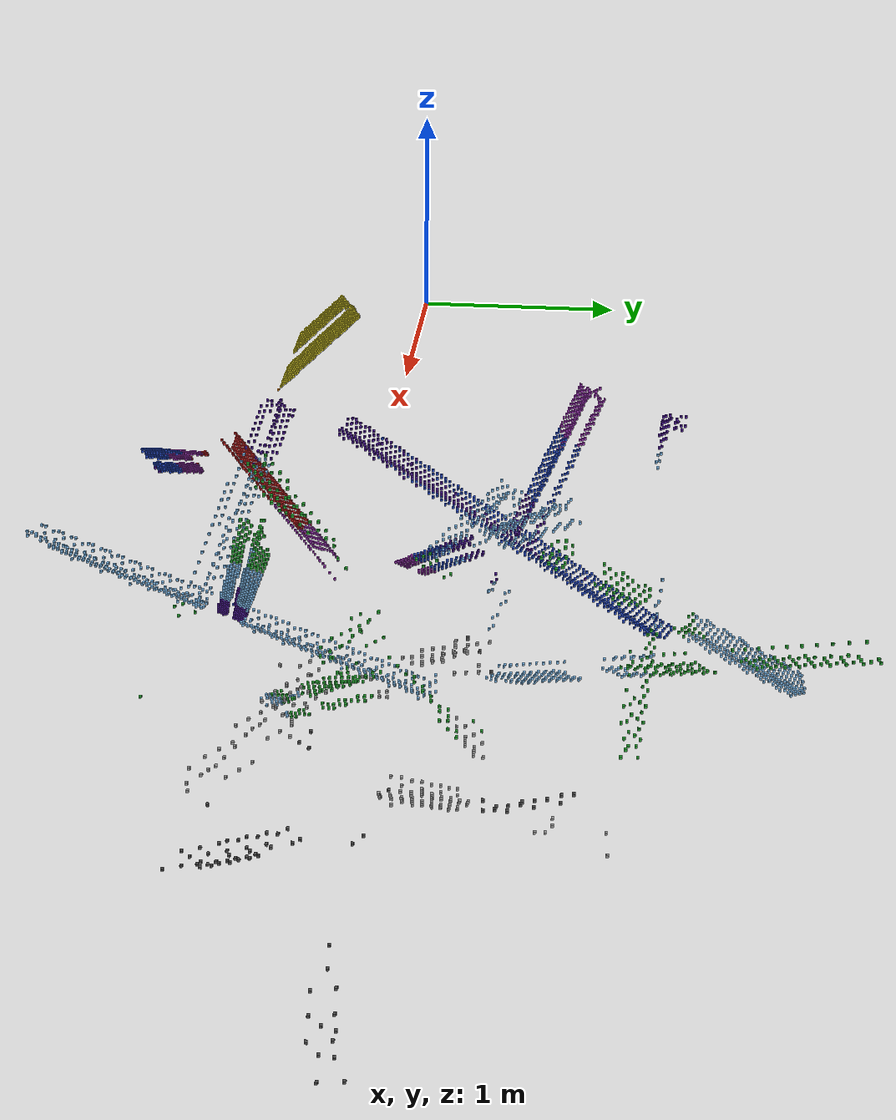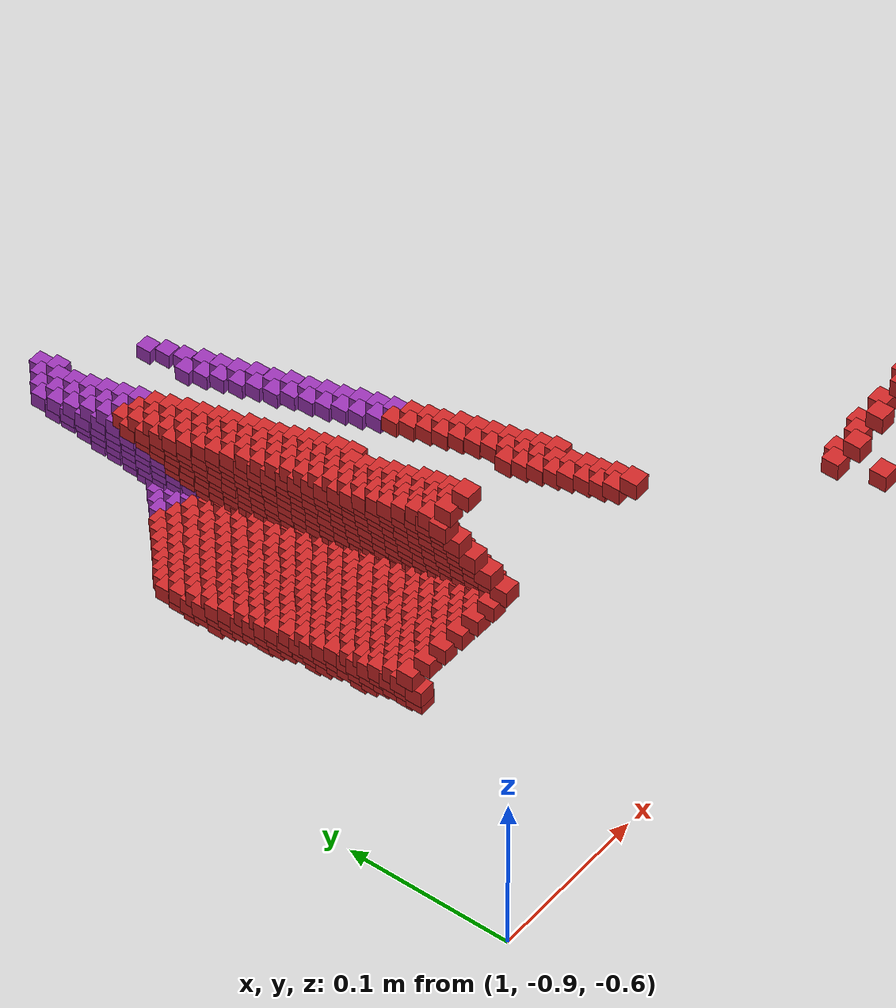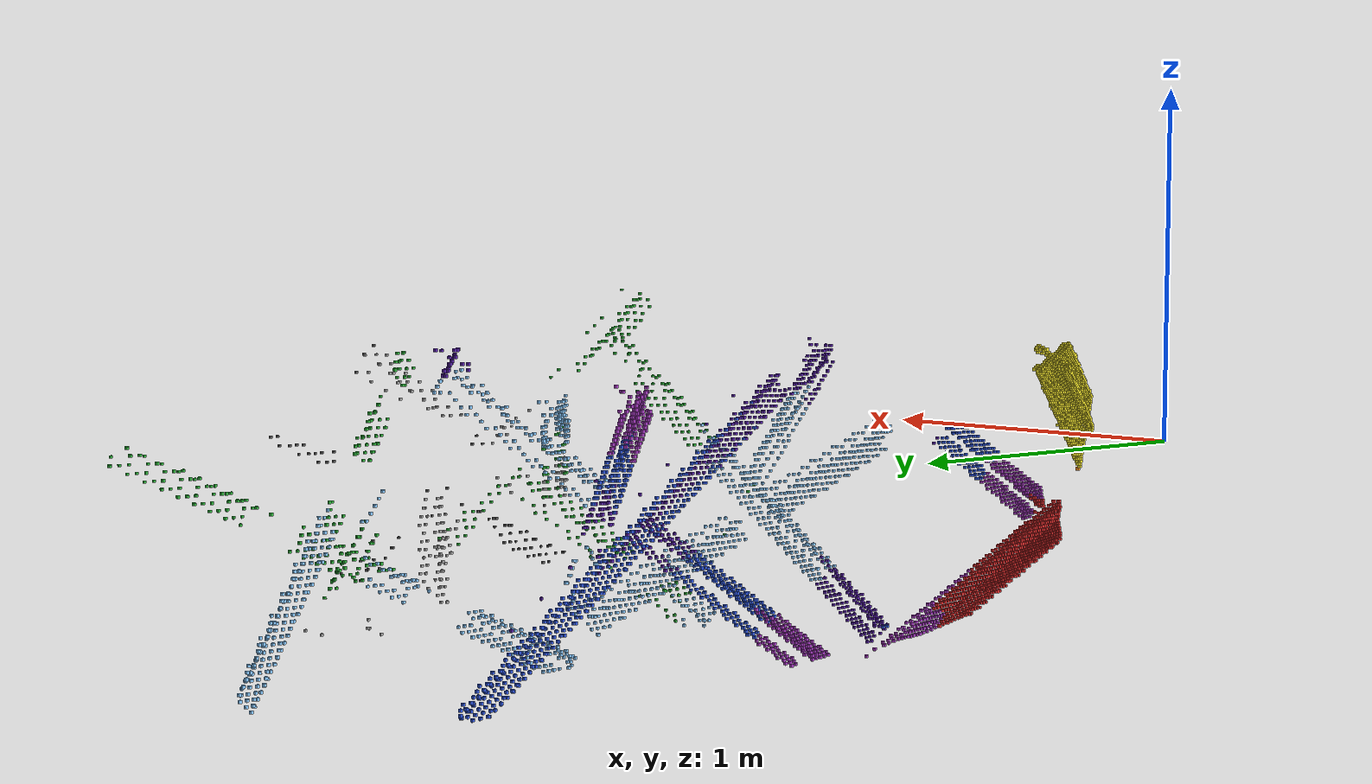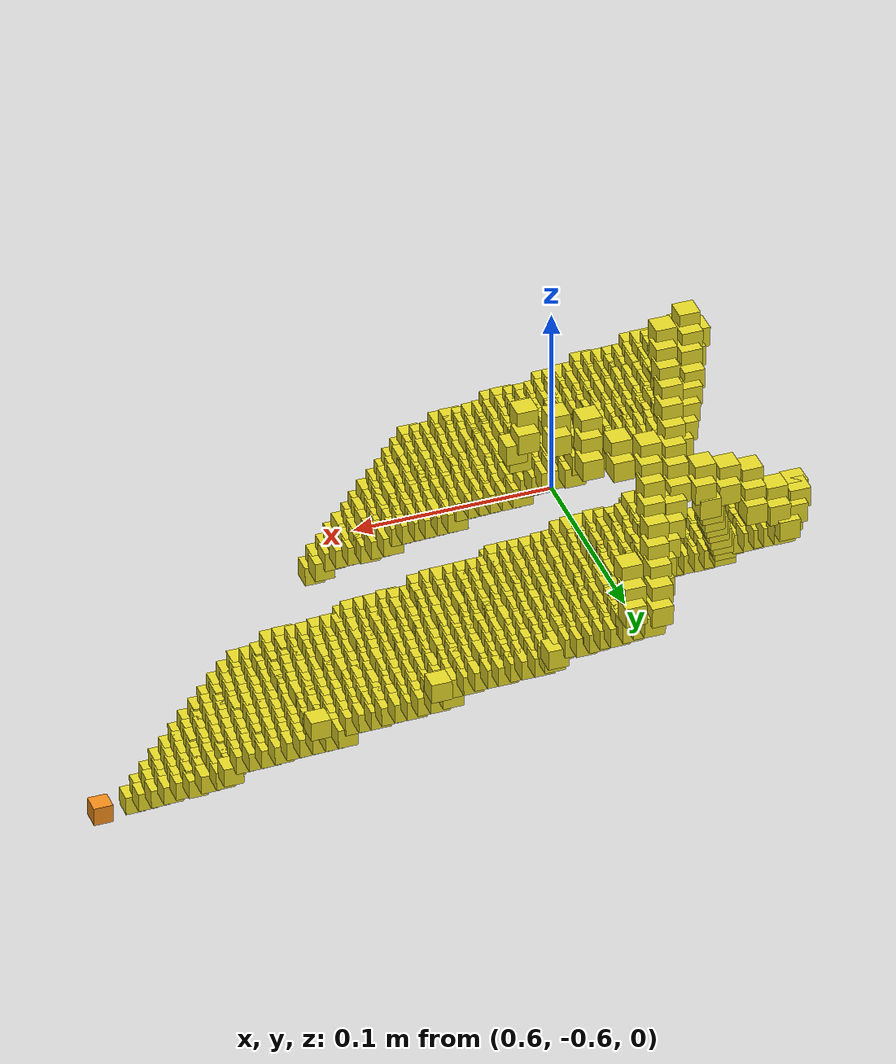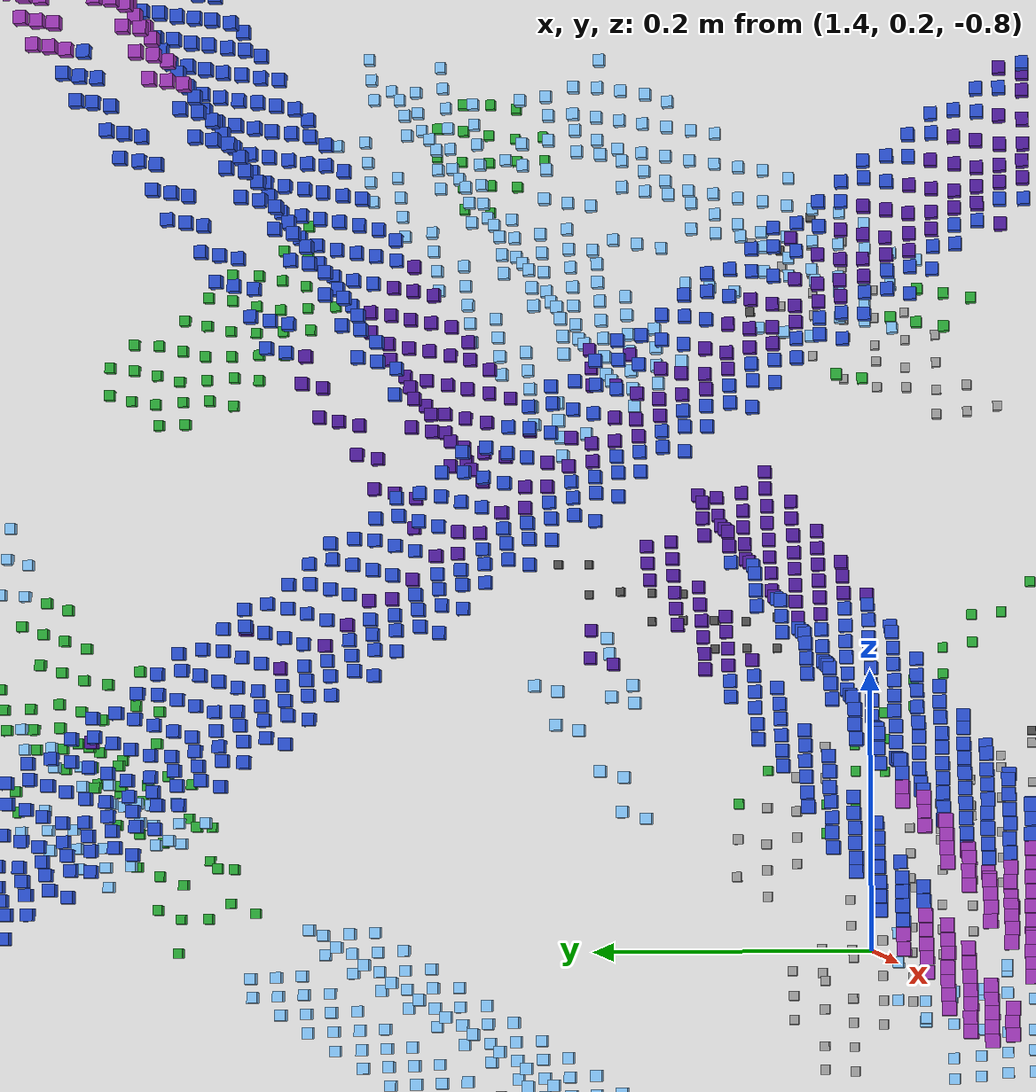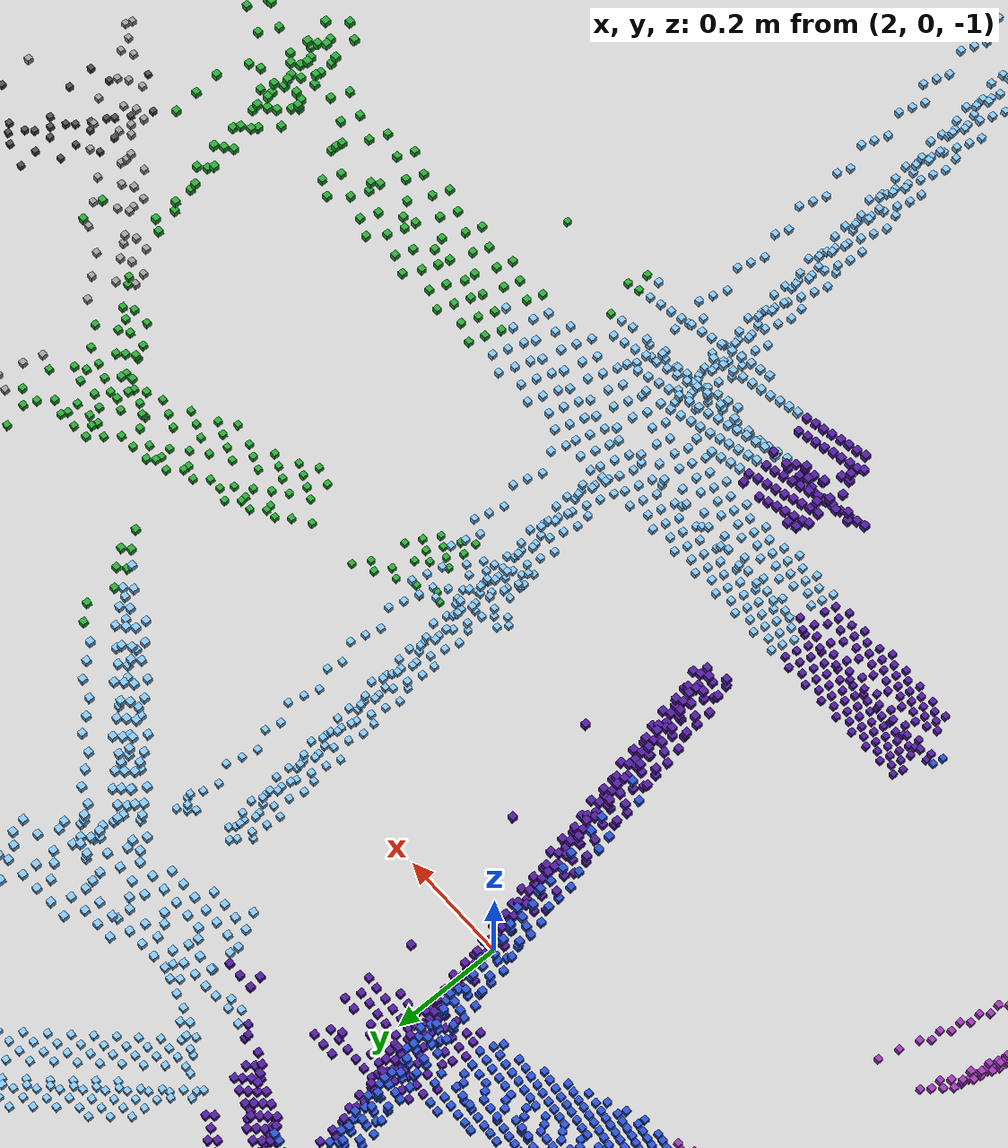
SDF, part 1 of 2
<?xml version="1.0" ?>
<sdf version="1.5">
<model name="3dprint">
<static>true</static>
<link name="link">

<collision name="p0c"><pose>0.623 -0.366 0.254 0 0 0</pose>
<geometry><box><size>0.01 0.01 0.01</size></box></geometry>
</collision>
<visual name="p0v"><pose>0.623 -0.366 0.254 0 0 0</pose>
<geometry><box><size>0.01 0.01 0.01</size></box></geometry>
<material><script><uri>file://media/materials/scripts/gazebo.material</uri>
<name>Gazebo/Yellow</name></script></material>
</visual>

<collision name="p1c"><pose>0.636 -0.361 0.252 0 0 0</pose>
<geometry><box><size>0.01 0.01 0.01</size></box></geometry>
</collision>
<visual name="p1v"><pose>0.636 -0.361 0.252 0 0 0</pose>
<geometry><box><size>0.01 0.01 0.01</size></box></geometry>
<material><script><uri>file://media/materials/scripts/gazebo.material</uri>
<name>Gazebo/Yellow</name></script></material>
</visual>

<collision name="p2c"><pose>0.624 -0.360 0.248 0 0 0</pose>
<geometry><box><size>0.01 0.01 0.01</size></box></geometry>
</collision>
<visual name="p2v"><pose>0.624 -0.360 0.248 0 0 0</pose>
<geometry><box><size>0.01 0.01 0.01</size></box></geometry>
<material><script><uri>file://media/materials/scripts/gazebo.material</uri>
<name>Gazebo/Yellow</name></script></material>
</visual>

<collision name="p3c"><pose>0.619 -0.364 0.246 0 0 0</pose>
<geometry><box><size>0.01 0.01 0.01</size></box></geometry>
</collision>
<visual name="p3v"><pose>0.619 -0.364 0.246 0 0 0</pose>
<geometry><box><size>0.01 0.01 0.01</size></box></geometry>
<material><script><uri>file://media/materials/scripts/gazebo.material</uri>
<name>Gazebo/Yellow</name></script></material>
</visual>

<collision name="p4c"><pose>0.619 -0.370 0.245 0 0 0</pose>
<geometry><box><size>0.01 0.01 0.01</size></box></geometry>
</collision>
<visual name="p4v"><pose>0.619 -0.370 0.245 0 0 0</pose>
<geometry><box><size>0.01 0.01 0.01</size></box></geometry>
<material><script><uri>file://media/materials/scripts/gazebo.material</uri>
<name>Gazebo/Yellow</name></script></material>
</visual>

<collision name="p5c"><pose>0.638 -0.355 0.246 0 0 0</pose>
<geometry><box><size>0.01 0.01 0.01</size></box></geometry>
</collision>
<visual name="p5v"><pose>0.638 -0.355 0.246 0 0 0</pose>
<geometry><box><size>0.01 0.01 0.01</size></box></geometry>
<material><script><uri>file://media/materials/scripts/gazebo.material</uri>
<name>Gazebo/Yellow</name></script></material>
</visual>

<collision name="p6c"><pose>0.626 -0.355 0.242 0 0 0</pose>
<geometry><box><size>0.01 0.01 0.01</size></box></geometry>
</collision>
<visual name="p6v"><pose>0.626 -0.355 0.242 0 0 0</pose>
<geometry><box><size>0.01 0.01 0.01</size></box></geometry>
<material><script><uri>file://media/materials/scripts/gazebo.material</uri>
<name>Gazebo/Yellow</name></script></material>
</visual>

<collision name="p7c"><pose>0.623 -0.359 0.240 0 0 0</pose>
<geometry><box><size>0.01 0.01 0.01</size></box></geometry>
</collision>
<visual name="p7v"><pose>0.623 -0.359 0.240 0 0 0</pose>
<geometry><box><size>0.01 0.01 0.01</size></box></geometry>
<material><script><uri>file://media/materials/scripts/gazebo.material</uri>
<name>Gazebo/Yellow</name></script></material>
</visual>

<collision name="p8c"><pose>0.622 -0.365 0.240 0 0 0</pose>
<geometry><box><size>0.01 0.01 0.01</size></box></geometry>
</collision>
<visual name="p8v"><pose>0.622 -0.365 0.240 0 0 0</pose>
<geometry><box><size>0.01 0.01 0.01</size></box></geometry>
<material><script><uri>file://media/materials/scripts/gazebo.material</uri>
<name>Gazebo/Yellow</name></script></material>
</visual>

<collision name="p9c"><pose>0.621 -0.372 0.240 0 0 0</pose>
<geometry><box><size>0.01 0.01 0.01</size></box></geometry>
</collision>
<visual name="p9v"><pose>0.621 -0.372 0.240 0 0 0</pose>
<geometry><box><size>0.01 0.01 0.01</size></box></geometry>
<material><script><uri>file://media/materials/scripts/gazebo.material</uri>
<name>Gazebo/Yellow</name></script></material>
</visual>

<collision name="p10c"><pose>0.621 -0.378 0.240 0 0 0</pose>
<geometry><box><size>0.01 0.01 0.01</size></box></geometry>
</collision>
<visual name="p10v"><pose>0.621 -0.378 0.240 0 0 0</pose>
<geometry><box><size>0.01 0.01 0.01</size></box></geometry>
<material><script><uri>file://media/materials/scripts/gazebo.material</uri>
<name>Gazebo/Yellow</name></script></material>
</visual>

<collision name="p11c"><pose>0.639 -0.349 0.240 0 0 0</pose>
<geometry><box><size>0.01 0.01 0.01</size></box></geometry>
</collision>
<visual name="p11v"><pose>0.639 -0.349 0.240 0 0 0</pose>
<geometry><box><size>0.01 0.01 0.01</size></box></geometry>
<material><script><uri>file://media/materials/scripts/gazebo.material</uri>
<name>Gazebo/Yellow</name></script></material>
</visual>

<collision name="p12c"><pose>0.627 -0.349 0.235 0 0 0</pose>
<geometry><box><size>0.01 0.01 0.01</size></box></geometry>
</collision>
<visual name="p12v"><pose>0.627 -0.349 0.235 0 0 0</pose>
<geometry><box><size>0.01 0.01 0.01</size></box></geometry>
<material><script><uri>file://media/materials/scripts/gazebo.material</uri>
<name>Gazebo/Yellow</name></script></material>
</visual>

<collision name="p13c"><pose>0.626 -0.355 0.235 0 0 0</pose>
<geometry><box><size>0.01 0.01 0.01</size></box></geometry>
</collision>
<visual name="p13v"><pose>0.626 -0.355 0.235 0 0 0</pose>
<geometry><box><size>0.01 0.01 0.01</size></box></geometry>
<material><script><uri>file://media/materials/scripts/gazebo.material</uri>
<name>Gazebo/Yellow</name></script></material>
</visual>

<collision name="p14c"><pose>0.625 -0.361 0.235 0 0 0</pose>
<geometry><box><size>0.01 0.01 0.01</size></box></geometry>
</collision>
<visual name="p14v"><pose>0.625 -0.361 0.235 0 0 0</pose>
<geometry><box><size>0.01 0.01 0.01</size></box></geometry>
<material><script><uri>file://media/materials/scripts/gazebo.material</uri>
<name>Gazebo/Yellow</name></script></material>
</visual>

<collision name="p15c"><pose>0.625 -0.367 0.235 0 0 0</pose>
<geometry><box><size>0.01 0.01 0.01</size></box></geometry>
</collision>
<visual name="p15v"><pose>0.625 -0.367 0.235 0 0 0</pose>
<geometry><box><size>0.01 0.01 0.01</size></box></geometry>
<material><script><uri>file://media/materials/scripts/gazebo.material</uri>
<name>Gazebo/Yellow</name></script></material>
</visual>

<collision name="p16c"><pose>0.624 -0.373 0.234 0 0 0</pose>
<geometry><box><size>0.01 0.01 0.01</size></box></geometry>
</collision>
<visual name="p16v"><pose>0.624 -0.373 0.234 0 0 0</pose>
<geometry><box><size>0.01 0.01 0.01</size></box></geometry>
<material><script><uri>file://media/materials/scripts/gazebo.material</uri>
<name>Gazebo/Yellow</name></script></material>
</visual>

<collision name="p17c"><pose>0.623 -0.379 0.234 0 0 0</pose>
<geometry><box><size>0.01 0.01 0.01</size></box></geometry>
</collision>
<visual name="p17v"><pose>0.623 -0.379 0.234 0 0 0</pose>
<geometry><box><size>0.01 0.01 0.01</size></box></geometry>
<material><script><uri>file://media/materials/scripts/gazebo.material</uri>
<name>Gazebo/Yellow</name></script></material>
</visual>

<collision name="p18c"><pose>0.640 -0.343 0.234 0 0 0</pose>
<geometry><box><size>0.01 0.01 0.01</size></box></geometry>
</collision>
<visual name="p18v"><pose>0.640 -0.343 0.234 0 0 0</pose>
<geometry><box><size>0.01 0.01 0.01</size></box></geometry>
<material><script><uri>file://media/materials/scripts/gazebo.material</uri>
<name>Gazebo/Yellow</name></script></material>
</visual>

<collision name="p19c"><pose>0.630 -0.344 0.230 0 0 0</pose>
<geometry><box><size>0.01 0.01 0.01</size></box></geometry>
</collision>
<visual name="p19v"><pose>0.630 -0.344 0.230 0 0 0</pose>
<geometry><box><size>0.01 0.01 0.01</size></box></geometry>
<material><script><uri>file://media/materials/scripts/gazebo.material</uri>
<name>Gazebo/Yellow</name></script></material>
</visual>

<collision name="p20c"><pose>0.629 -0.350 0.230 0 0 0</pose>
<geometry><box><size>0.01 0.01 0.01</size></box></geometry>
</collision>
<visual name="p20v"><pose>0.629 -0.350 0.230 0 0 0</pose>
<geometry><box><size>0.01 0.01 0.01</size></box></geometry>
<material><script><uri>file://media/materials/scripts/gazebo.material</uri>
<name>Gazebo/Yellow</name></script></material>
</visual>

<collision name="p21c"><pose>0.628 -0.356 0.229 0 0 0</pose>
<geometry><box><size>0.01 0.01 0.01</size></box></geometry>
</collision>
<visual name="p21v"><pose>0.628 -0.356 0.229 0 0 0</pose>
<geometry><box><size>0.01 0.01 0.01</size></box></geometry>
<material><script><uri>file://media/materials/scripts/gazebo.material</uri>
<name>Gazebo/Yellow</name></script></material>
</visual>

<collision name="p22c"><pose>0.628 -0.362 0.229 0 0 0</pose>
<geometry><box><size>0.01 0.01 0.01</size></box></geometry>
</collision>
<visual name="p22v"><pose>0.628 -0.362 0.229 0 0 0</pose>
<geometry><box><size>0.01 0.01 0.01</size></box></geometry>
<material><script><uri>file://media/materials/scripts/gazebo.material</uri>
<name>Gazebo/Yellow</name></script></material>
</visual>

<collision name="p23c"><pose>0.627 -0.369 0.229 0 0 0</pose>
<geometry><box><size>0.01 0.01 0.01</size></box></geometry>
</collision>
<visual name="p23v"><pose>0.627 -0.369 0.229 0 0 0</pose>
<geometry><box><size>0.01 0.01 0.01</size></box></geometry>
<material><script><uri>file://media/materials/scripts/gazebo.material</uri>
<name>Gazebo/Yellow</name></script></material>
</visual>

<collision name="p24c"><pose>0.626 -0.375 0.229 0 0 0</pose>
<geometry><box><size>0.01 0.01 0.01</size></box></geometry>
</collision>
<visual name="p24v"><pose>0.626 -0.375 0.229 0 0 0</pose>
<geometry><box><size>0.01 0.01 0.01</size></box></geometry>
<material><script><uri>file://media/materials/scripts/gazebo.material</uri>
<name>Gazebo/Yellow</name></script></material>
</visual>

<collision name="p25c"><pose>0.626 -0.381 0.229 0 0 0</pose>
<geometry><box><size>0.01 0.01 0.01</size></box></geometry>
</collision>
<visual name="p25v"><pose>0.626 -0.381 0.229 0 0 0</pose>
<geometry><box><size>0.01 0.01 0.01</size></box></geometry>
<material><script><uri>file://media/materials/scripts/gazebo.material</uri>
<name>Gazebo/Yellow</name></script></material>
</visual>

<collision name="p26c"><pose>0.625 -0.387 0.228 0 0 0</pose>
<geometry><box><size>0.01 0.01 0.01</size></box></geometry>
</collision>
<visual name="p26v"><pose>0.625 -0.387 0.228 0 0 0</pose>
<geometry><box><size>0.01 0.01 0.01</size></box></geometry>
<material><script><uri>file://media/materials/scripts/gazebo.material</uri>
<name>Gazebo/Yellow</name></script></material>
</visual>

<collision name="p27c"><pose>0.642 -0.337 0.228 0 0 0</pose>
<geometry><box><size>0.01 0.01 0.01</size></box></geometry>
</collision>
<visual name="p27v"><pose>0.642 -0.337 0.228 0 0 0</pose>
<geometry><box><size>0.01 0.01 0.01</size></box></geometry>
<material><script><uri>file://media/materials/scripts/gazebo.material</uri>
<name>Gazebo/Yellow</name></script></material>
</visual>

<collision name="p28c"><pose>0.633 -0.339 0.225 0 0 0</pose>
<geometry><box><size>0.01 0.01 0.01</size></box></geometry>
</collision>
<visual name="p28v"><pose>0.633 -0.339 0.225 0 0 0</pose>
<geometry><box><size>0.01 0.01 0.01</size></box></geometry>
<material><script><uri>file://media/materials/scripts/gazebo.material</uri>
<name>Gazebo/Yellow</name></script></material>
</visual>

<collision name="p29c"><pose>0.632 -0.345 0.224 0 0 0</pose>
<geometry><box><size>0.01 0.01 0.01</size></box></geometry>
</collision>
<visual name="p29v"><pose>0.632 -0.345 0.224 0 0 0</pose>
<geometry><box><size>0.01 0.01 0.01</size></box></geometry>
<material><script><uri>file://media/materials/scripts/gazebo.material</uri>
<name>Gazebo/Yellow</name></script></material>
</visual>

<collision name="p30c"><pose>0.632 -0.351 0.224 0 0 0</pose>
<geometry><box><size>0.01 0.01 0.01</size></box></geometry>
</collision>
<visual name="p30v"><pose>0.632 -0.351 0.224 0 0 0</pose>
<geometry><box><size>0.01 0.01 0.01</size></box></geometry>
<material><script><uri>file://media/materials/scripts/gazebo.material</uri>
<name>Gazebo/Yellow</name></script></material>
</visual>

<collision name="p31c"><pose>0.631 -0.358 0.224 0 0 0</pose>
<geometry><box><size>0.01 0.01 0.01</size></box></geometry>
</collision>
<visual name="p31v"><pose>0.631 -0.358 0.224 0 0 0</pose>
<geometry><box><size>0.01 0.01 0.01</size></box></geometry>
<material><script><uri>file://media/materials/scripts/gazebo.material</uri>
<name>Gazebo/Yellow</name></script></material>
</visual>

<collision name="p32c"><pose>0.630 -0.364 0.224 0 0 0</pose>
<geometry><box><size>0.01 0.01 0.01</size></box></geometry>
</collision>
<visual name="p32v"><pose>0.630 -0.364 0.224 0 0 0</pose>
<geometry><box><size>0.01 0.01 0.01</size></box></geometry>
<material><script><uri>file://media/materials/scripts/gazebo.material</uri>
<name>Gazebo/Yellow</name></script></material>
</visual>

<collision name="p33c"><pose>0.630 -0.370 0.223 0 0 0</pose>
<geometry><box><size>0.01 0.01 0.01</size></box></geometry>
</collision>
<visual name="p33v"><pose>0.630 -0.370 0.223 0 0 0</pose>
<geometry><box><size>0.01 0.01 0.01</size></box></geometry>
<material><script><uri>file://media/materials/scripts/gazebo.material</uri>
<name>Gazebo/Yellow</name></script></material>
</visual>

<collision name="p34c"><pose>0.629 -0.376 0.223 0 0 0</pose>
<geometry><box><size>0.01 0.01 0.01</size></box></geometry>
</collision>
<visual name="p34v"><pose>0.629 -0.376 0.223 0 0 0</pose>
<geometry><box><size>0.01 0.01 0.01</size></box></geometry>
<material><script><uri>file://media/materials/scripts/gazebo.material</uri>
<name>Gazebo/Yellow</name></script></material>
</visual>

<collision name="p35c"><pose>0.628 -0.383 0.223 0 0 0</pose>
<geometry><box><size>0.01 0.01 0.01</size></box></geometry>
</collision>
<visual name="p35v"><pose>0.628 -0.383 0.223 0 0 0</pose>
<geometry><box><size>0.01 0.01 0.01</size></box></geometry>
<material><script><uri>file://media/materials/scripts/gazebo.material</uri>
<name>Gazebo/Yellow</name></script></material>
</visual>

<collision name="p36c"><pose>0.628 -0.389 0.223 0 0 0</pose>
<geometry><box><size>0.01 0.01 0.01</size></box></geometry>
</collision>
<visual name="p36v"><pose>0.628 -0.389 0.223 0 0 0</pose>
<geometry><box><size>0.01 0.01 0.01</size></box></geometry>
<material><script><uri>file://media/materials/scripts/gazebo.material</uri>
<name>Gazebo/Yellow</name></script></material>
</visual>

<collision name="p37c"><pose>0.627 -0.395 0.222 0 0 0</pose>
<geometry><box><size>0.01 0.01 0.01</size></box></geometry>
</collision>
<visual name="p37v"><pose>0.627 -0.395 0.222 0 0 0</pose>
<geometry><box><size>0.01 0.01 0.01</size></box></geometry>
<material><script><uri>file://media/materials/scripts/gazebo.material</uri>
<name>Gazebo/Yellow</name></script></material>
</visual>

<collision name="p38c"><pose>0.713 -0.330 0.246 0 0 0</pose>
<geometry><box><size>0.01 0.01 0.01</size></box></geometry>
</collision>
<visual name="p38v"><pose>0.713 -0.330 0.246 0 0 0</pose>
<geometry><box><size>0.01 0.01 0.01</size></box></geometry>
<material><script><uri>file://media/materials/scripts/gazebo.material</uri>
<name>Gazebo/Yellow</name></script></material>
</visual>

<collision name="p39c"><pose>0.698 -0.330 0.240 0 0 0</pose>
<geometry><box><size>0.01 0.01 0.01</size></box></geometry>
</collision>
<visual name="p39v"><pose>0.698 -0.330 0.240 0 0 0</pose>
<geometry><box><size>0.01 0.01 0.01</size></box></geometry>
<material><script><uri>file://media/materials/scripts/gazebo.material</uri>
<name>Gazebo/Yellow</name></script></material>
</visual>

<collision name="p40c"><pose>0.683 -0.330 0.235 0 0 0</pose>
<geometry><box><size>0.01 0.01 0.01</size></box></geometry>
</collision>
<visual name="p40v"><pose>0.683 -0.330 0.235 0 0 0</pose>
<geometry><box><size>0.01 0.01 0.01</size></box></geometry>
<material><script><uri>file://media/materials/scripts/gazebo.material</uri>
<name>Gazebo/Yellow</name></script></material>
</visual>

<collision name="p41c"><pose>0.643 -0.331 0.221 0 0 0</pose>
<geometry><box><size>0.01 0.01 0.01</size></box></geometry>
</collision>
<visual name="p41v"><pose>0.643 -0.331 0.221 0 0 0</pose>
<geometry><box><size>0.01 0.01 0.01</size></box></geometry>
<material><script><uri>file://media/materials/scripts/gazebo.material</uri>
<name>Gazebo/Yellow</name></script></material>
</visual>

<collision name="p42c"><pose>0.636 -0.334 0.219 0 0 0</pose>
<geometry><box><size>0.01 0.01 0.01</size></box></geometry>
</collision>
<visual name="p42v"><pose>0.636 -0.334 0.219 0 0 0</pose>
<geometry><box><size>0.01 0.01 0.01</size></box></geometry>
<material><script><uri>file://media/materials/scripts/gazebo.material</uri>
<name>Gazebo/Yellow</name></script></material>
</visual>

<collision name="p43c"><pose>0.636 -0.340 0.219 0 0 0</pose>
<geometry><box><size>0.01 0.01 0.01</size></box></geometry>
</collision>
<visual name="p43v"><pose>0.636 -0.340 0.219 0 0 0</pose>
<geometry><box><size>0.01 0.01 0.01</size></box></geometry>
<material><script><uri>file://media/materials/scripts/gazebo.material</uri>
<name>Gazebo/Yellow</name></script></material>
</visual>

<collision name="p44c"><pose>0.635 -0.347 0.219 0 0 0</pose>
<geometry><box><size>0.01 0.01 0.01</size></box></geometry>
</collision>
<visual name="p44v"><pose>0.635 -0.347 0.219 0 0 0</pose>
<geometry><box><size>0.01 0.01 0.01</size></box></geometry>
<material><script><uri>file://media/materials/scripts/gazebo.material</uri>
<name>Gazebo/Yellow</name></script></material>
</visual>

<collision name="p45c"><pose>0.634 -0.353 0.218 0 0 0</pose>
<geometry><box><size>0.01 0.01 0.01</size></box></geometry>
</collision>
<visual name="p45v"><pose>0.634 -0.353 0.218 0 0 0</pose>
<geometry><box><size>0.01 0.01 0.01</size></box></geometry>
<material><script><uri>file://media/materials/scripts/gazebo.material</uri>
<name>Gazebo/Yellow</name></script></material>
</visual>

<collision name="p46c"><pose>0.634 -0.359 0.218 0 0 0</pose>
<geometry><box><size>0.01 0.01 0.01</size></box></geometry>
</collision>
<visual name="p46v"><pose>0.634 -0.359 0.218 0 0 0</pose>
<geometry><box><size>0.01 0.01 0.01</size></box></geometry>
<material><script><uri>file://media/materials/scripts/gazebo.material</uri>
<name>Gazebo/Yellow</name></script></material>
</visual>

<collision name="p47c"><pose>0.633 -0.365 0.218 0 0 0</pose>
<geometry><box><size>0.01 0.01 0.01</size></box></geometry>
</collision>
<visual name="p47v"><pose>0.633 -0.365 0.218 0 0 0</pose>
<geometry><box><size>0.01 0.01 0.01</size></box></geometry>
<material><script><uri>file://media/materials/scripts/gazebo.material</uri>
<name>Gazebo/Yellow</name></script></material>
</visual>

<collision name="p48c"><pose>0.632 -0.372 0.218 0 0 0</pose>
<geometry><box><size>0.01 0.01 0.01</size></box></geometry>
</collision>
<visual name="p48v"><pose>0.632 -0.372 0.218 0 0 0</pose>
<geometry><box><size>0.01 0.01 0.01</size></box></geometry>
<material><script><uri>file://media/materials/scripts/gazebo.material</uri>
<name>Gazebo/Yellow</name></script></material>
</visual>

<collision name="p49c"><pose>0.632 -0.378 0.217 0 0 0</pose>
<geometry><box><size>0.01 0.01 0.01</size></box></geometry>
</collision>
<visual name="p49v"><pose>0.632 -0.378 0.217 0 0 0</pose>
<geometry><box><size>0.01 0.01 0.01</size></box></geometry>
<material><script><uri>file://media/materials/scripts/gazebo.material</uri>
<name>Gazebo/Yellow</name></script></material>
</visual>

<collision name="p50c"><pose>0.631 -0.384 0.217 0 0 0</pose>
<geometry><box><size>0.01 0.01 0.01</size></box></geometry>
</collision>
<visual name="p50v"><pose>0.631 -0.384 0.217 0 0 0</pose>
<geometry><box><size>0.01 0.01 0.01</size></box></geometry>
<material><script><uri>file://media/materials/scripts/gazebo.material</uri>
<name>Gazebo/Yellow</name></script></material>
</visual>

<collision name="p51c"><pose>0.630 -0.390 0.217 0 0 0</pose>
<geometry><box><size>0.01 0.01 0.01</size></box></geometry>
</collision>
<visual name="p51v"><pose>0.630 -0.390 0.217 0 0 0</pose>
<geometry><box><size>0.01 0.01 0.01</size></box></geometry>
<material><script><uri>file://media/materials/scripts/gazebo.material</uri>
<name>Gazebo/Yellow</name></script></material>
</visual>

<collision name="p52c"><pose>0.630 -0.397 0.217 0 0 0</pose>
<geometry><box><size>0.01 0.01 0.01</size></box></geometry>
</collision>
<visual name="p52v"><pose>0.630 -0.397 0.217 0 0 0</pose>
<geometry><box><size>0.01 0.01 0.01</size></box></geometry>
<material><script><uri>file://media/materials/scripts/gazebo.material</uri>
<name>Gazebo/Yellow</name></script></material>
</visual>

<collision name="p53c"><pose>0.629 -0.403 0.217 0 0 0</pose>
<geometry><box><size>0.01 0.01 0.01</size></box></geometry>
</collision>
<visual name="p53v"><pose>0.629 -0.403 0.217 0 0 0</pose>
<geometry><box><size>0.01 0.01 0.01</size></box></geometry>
<material><script><uri>file://media/materials/scripts/gazebo.material</uri>
<name>Gazebo/Yellow</name></script></material>
</visual>

<collision name="p54c"><pose>0.715 -0.323 0.239 0 0 0</pose>
<geometry><box><size>0.01 0.01 0.01</size></box></geometry>
</collision>
<visual name="p54v"><pose>0.715 -0.323 0.239 0 0 0</pose>
<geometry><box><size>0.01 0.01 0.01</size></box></geometry>
<material><script><uri>file://media/materials/scripts/gazebo.material</uri>
<name>Gazebo/Yellow</name></script></material>
</visual>

<collision name="p55c"><pose>0.700 -0.323 0.234 0 0 0</pose>
<geometry><box><size>0.01 0.01 0.01</size></box></geometry>
</collision>
<visual name="p55v"><pose>0.700 -0.323 0.234 0 0 0</pose>
<geometry><box><size>0.01 0.01 0.01</size></box></geometry>
<material><script><uri>file://media/materials/scripts/gazebo.material</uri>
<name>Gazebo/Yellow</name></script></material>
</visual>

<collision name="p56c"><pose>0.685 -0.324 0.229 0 0 0</pose>
<geometry><box><size>0.01 0.01 0.01</size></box></geometry>
</collision>
<visual name="p56v"><pose>0.685 -0.324 0.229 0 0 0</pose>
<geometry><box><size>0.01 0.01 0.01</size></box></geometry>
<material><script><uri>file://media/materials/scripts/gazebo.material</uri>
<name>Gazebo/Yellow</name></script></material>
</visual>

<collision name="p57c"><pose>0.671 -0.324 0.224 0 0 0</pose>
<geometry><box><size>0.01 0.01 0.01</size></box></geometry>
</collision>
<visual name="p57v"><pose>0.671 -0.324 0.224 0 0 0</pose>
<geometry><box><size>0.01 0.01 0.01</size></box></geometry>
<material><script><uri>file://media/materials/scripts/gazebo.material</uri>
<name>Gazebo/Yellow</name></script></material>
</visual>

<collision name="p58c"><pose>0.657 -0.324 0.219 0 0 0</pose>
<geometry><box><size>0.01 0.01 0.01</size></box></geometry>
</collision>
<visual name="p58v"><pose>0.657 -0.324 0.219 0 0 0</pose>
<geometry><box><size>0.01 0.01 0.01</size></box></geometry>
<material><script><uri>file://media/materials/scripts/gazebo.material</uri>
<name>Gazebo/Yellow</name></script></material>
</visual>

<collision name="p59c"><pose>0.645 -0.325 0.215 0 0 0</pose>
<geometry><box><size>0.01 0.01 0.01</size></box></geometry>
</collision>
<visual name="p59v"><pose>0.645 -0.325 0.215 0 0 0</pose>
<geometry><box><size>0.01 0.01 0.01</size></box></geometry>
<material><script><uri>file://media/materials/scripts/gazebo.material</uri>
<name>Gazebo/Yellow</name></script></material>
</visual>

<collision name="p60c"><pose>0.640 -0.329 0.214 0 0 0</pose>
<geometry><box><size>0.01 0.01 0.01</size></box></geometry>
</collision>
<visual name="p60v"><pose>0.640 -0.329 0.214 0 0 0</pose>
<geometry><box><size>0.01 0.01 0.01</size></box></geometry>
<material><script><uri>file://media/materials/scripts/gazebo.material</uri>
<name>Gazebo/Yellow</name></script></material>
</visual>

<collision name="p61c"><pose>0.639 -0.335 0.213 0 0 0</pose>
<geometry><box><size>0.01 0.01 0.01</size></box></geometry>
</collision>
<visual name="p61v"><pose>0.639 -0.335 0.213 0 0 0</pose>
<geometry><box><size>0.01 0.01 0.01</size></box></geometry>
<material><script><uri>file://media/materials/scripts/gazebo.material</uri>
<name>Gazebo/Yellow</name></script></material>
</visual>

<collision name="p62c"><pose>0.638 -0.342 0.213 0 0 0</pose>
<geometry><box><size>0.01 0.01 0.01</size></box></geometry>
</collision>
<visual name="p62v"><pose>0.638 -0.342 0.213 0 0 0</pose>
<geometry><box><size>0.01 0.01 0.01</size></box></geometry>
<material><script><uri>file://media/materials/scripts/gazebo.material</uri>
<name>Gazebo/Yellow</name></script></material>
</visual>

<collision name="p63c"><pose>0.638 -0.348 0.213 0 0 0</pose>
<geometry><box><size>0.01 0.01 0.01</size></box></geometry>
</collision>
<visual name="p63v"><pose>0.638 -0.348 0.213 0 0 0</pose>
<geometry><box><size>0.01 0.01 0.01</size></box></geometry>
<material><script><uri>file://media/materials/scripts/gazebo.material</uri>
<name>Gazebo/Yellow</name></script></material>
</visual>

<collision name="p64c"><pose>0.637 -0.354 0.213 0 0 0</pose>
<geometry><box><size>0.01 0.01 0.01</size></box></geometry>
</collision>
<visual name="p64v"><pose>0.637 -0.354 0.213 0 0 0</pose>
<geometry><box><size>0.01 0.01 0.01</size></box></geometry>
<material><script><uri>file://media/materials/scripts/gazebo.material</uri>
<name>Gazebo/Yellow</name></script></material>
</visual>

<collision name="p65c"><pose>0.636 -0.361 0.212 0 0 0</pose>
<geometry><box><size>0.01 0.01 0.01</size></box></geometry>
</collision>
<visual name="p65v"><pose>0.636 -0.361 0.212 0 0 0</pose>
<geometry><box><size>0.01 0.01 0.01</size></box></geometry>
<material><script><uri>file://media/materials/scripts/gazebo.material</uri>
<name>Gazebo/Yellow</name></script></material>
</visual>

<collision name="p66c"><pose>0.636 -0.367 0.212 0 0 0</pose>
<geometry><box><size>0.01 0.01 0.01</size></box></geometry>
</collision>
<visual name="p66v"><pose>0.636 -0.367 0.212 0 0 0</pose>
<geometry><box><size>0.01 0.01 0.01</size></box></geometry>
<material><script><uri>file://media/materials/scripts/gazebo.material</uri>
<name>Gazebo/Yellow</name></script></material>
</visual>

<collision name="p67c"><pose>0.635 -0.373 0.212 0 0 0</pose>
<geometry><box><size>0.01 0.01 0.01</size></box></geometry>
</collision>
<visual name="p67v"><pose>0.635 -0.373 0.212 0 0 0</pose>
<geometry><box><size>0.01 0.01 0.01</size></box></geometry>
<material><script><uri>file://media/materials/scripts/gazebo.material</uri>
<name>Gazebo/Yellow</name></script></material>
</visual>

<collision name="p68c"><pose>0.634 -0.380 0.212 0 0 0</pose>
<geometry><box><size>0.01 0.01 0.01</size></box></geometry>
</collision>
<visual name="p68v"><pose>0.634 -0.380 0.212 0 0 0</pose>
<geometry><box><size>0.01 0.01 0.01</size></box></geometry>
<material><script><uri>file://media/materials/scripts/gazebo.material</uri>
<name>Gazebo/Yellow</name></script></material>
</visual>

<collision name="p69c"><pose>0.634 -0.386 0.212 0 0 0</pose>
<geometry><box><size>0.01 0.01 0.01</size></box></geometry>
</collision>
<visual name="p69v"><pose>0.634 -0.386 0.212 0 0 0</pose>
<geometry><box><size>0.01 0.01 0.01</size></box></geometry>
<material><script><uri>file://media/materials/scripts/gazebo.material</uri>
<name>Gazebo/Yellow</name></script></material>
</visual>

<collision name="p70c"><pose>0.633 -0.392 0.211 0 0 0</pose>
<geometry><box><size>0.01 0.01 0.01</size></box></geometry>
</collision>
<visual name="p70v"><pose>0.633 -0.392 0.211 0 0 0</pose>
<geometry><box><size>0.01 0.01 0.01</size></box></geometry>
<material><script><uri>file://media/materials/scripts/gazebo.material</uri>
<name>Gazebo/Yellow</name></script></material>
</visual>

<collision name="p71c"><pose>0.633 -0.398 0.211 0 0 0</pose>
<geometry><box><size>0.01 0.01 0.01</size></box></geometry>
</collision>
<visual name="p71v"><pose>0.633 -0.398 0.211 0 0 0</pose>
<geometry><box><size>0.01 0.01 0.01</size></box></geometry>
<material><script><uri>file://media/materials/scripts/gazebo.material</uri>
<name>Gazebo/Yellow</name></script></material>
</visual>

<collision name="p72c"><pose>0.632 -0.404 0.211 0 0 0</pose>
<geometry><box><size>0.01 0.01 0.01</size></box></geometry>
</collision>
<visual name="p72v"><pose>0.632 -0.404 0.211 0 0 0</pose>
<geometry><box><size>0.01 0.01 0.01</size></box></geometry>
<material><script><uri>file://media/materials/scripts/gazebo.material</uri>
<name>Gazebo/Yellow</name></script></material>
</visual>

<collision name="p73c"><pose>0.631 -0.411 0.211 0 0 0</pose>
<geometry><box><size>0.01 0.01 0.01</size></box></geometry>
</collision>
<visual name="p73v"><pose>0.631 -0.411 0.211 0 0 0</pose>
<geometry><box><size>0.01 0.01 0.01</size></box></geometry>
<material><script><uri>file://media/materials/scripts/gazebo.material</uri>
<name>Gazebo/Yellow</name></script></material>
</visual>

<collision name="p74c"><pose>0.720 -0.325 0.233 0 0 0</pose>
<geometry><box><size>0.01 0.01 0.01</size></box></geometry>
</collision>
<visual name="p74v"><pose>0.720 -0.325 0.233 0 0 0</pose>
<geometry><box><size>0.01 0.01 0.01</size></box></geometry>
<material><script><uri>file://media/materials/scripts/gazebo.material</uri>
<name>Gazebo/Yellow</name></script></material>
</visual>

<collision name="p75c"><pose>0.687 -0.317 0.222 0 0 0</pose>
<geometry><box><size>0.01 0.01 0.01</size></box></geometry>
</collision>
<visual name="p75v"><pose>0.687 -0.317 0.222 0 0 0</pose>
<geometry><box><size>0.01 0.01 0.01</size></box></geometry>
<material><script><uri>file://media/materials/scripts/gazebo.material</uri>
<name>Gazebo/Yellow</name></script></material>
</visual>

<collision name="p76c"><pose>0.672 -0.318 0.217 0 0 0</pose>
<geometry><box><size>0.01 0.01 0.01</size></box></geometry>
</collision>
<visual name="p76v"><pose>0.672 -0.318 0.217 0 0 0</pose>
<geometry><box><size>0.01 0.01 0.01</size></box></geometry>
<material><script><uri>file://media/materials/scripts/gazebo.material</uri>
<name>Gazebo/Yellow</name></script></material>
</visual>

<collision name="p77c"><pose>0.659 -0.318 0.213 0 0 0</pose>
<geometry><box><size>0.01 0.01 0.01</size></box></geometry>
</collision>
<visual name="p77v"><pose>0.659 -0.318 0.213 0 0 0</pose>
<geometry><box><size>0.01 0.01 0.01</size></box></geometry>
<material><script><uri>file://media/materials/scripts/gazebo.material</uri>
<name>Gazebo/Yellow</name></script></material>
</visual>

<collision name="p78c"><pose>0.646 -0.319 0.209 0 0 0</pose>
<geometry><box><size>0.01 0.01 0.01</size></box></geometry>
</collision>
<visual name="p78v"><pose>0.646 -0.319 0.209 0 0 0</pose>
<geometry><box><size>0.01 0.01 0.01</size></box></geometry>
<material><script><uri>file://media/materials/scripts/gazebo.material</uri>
<name>Gazebo/Yellow</name></script></material>
</visual>

<collision name="p79c"><pose>0.633 -0.319 0.205 0 0 0</pose>
<geometry><box><size>0.01 0.01 0.01</size></box></geometry>
</collision>
<visual name="p79v"><pose>0.633 -0.319 0.205 0 0 0</pose>
<geometry><box><size>0.01 0.01 0.01</size></box></geometry>
<material><script><uri>file://media/materials/scripts/gazebo.material</uri>
<name>Gazebo/Yellow</name></script></material>
</visual>

<collision name="p80c"><pose>0.621 -0.320 0.201 0 0 0</pose>
<geometry><box><size>0.01 0.01 0.01</size></box></geometry>
</collision>
<visual name="p80v"><pose>0.621 -0.320 0.201 0 0 0</pose>
<geometry><box><size>0.01 0.01 0.01</size></box></geometry>
<material><script><uri>file://media/materials/scripts/gazebo.material</uri>
<name>Gazebo/Yellow</name></script></material>
</visual>

<collision name="p81c"><pose>0.610 -0.320 0.197 0 0 0</pose>
<geometry><box><size>0.01 0.01 0.01</size></box></geometry>
</collision>
<visual name="p81v"><pose>0.610 -0.320 0.197 0 0 0</pose>
<geometry><box><size>0.01 0.01 0.01</size></box></geometry>
<material><script><uri>file://media/materials/scripts/gazebo.material</uri>
<name>Gazebo/Yellow</name></script></material>
</visual>

<collision name="p82c"><pose>0.641 -0.343 0.207 0 0 0</pose>
<geometry><box><size>0.01 0.01 0.01</size></box></geometry>
</collision>
<visual name="p82v"><pose>0.641 -0.343 0.207 0 0 0</pose>
<geometry><box><size>0.01 0.01 0.01</size></box></geometry>
<material><script><uri>file://media/materials/scripts/gazebo.material</uri>
<name>Gazebo/Yellow</name></script></material>
</visual>

<collision name="p83c"><pose>0.641 -0.350 0.207 0 0 0</pose>
<geometry><box><size>0.01 0.01 0.01</size></box></geometry>
</collision>
<visual name="p83v"><pose>0.641 -0.350 0.207 0 0 0</pose>
<geometry><box><size>0.01 0.01 0.01</size></box></geometry>
<material><script><uri>file://media/materials/scripts/gazebo.material</uri>
<name>Gazebo/Yellow</name></script></material>
</visual>

<collision name="p84c"><pose>0.640 -0.356 0.207 0 0 0</pose>
<geometry><box><size>0.01 0.01 0.01</size></box></geometry>
</collision>
<visual name="p84v"><pose>0.640 -0.356 0.207 0 0 0</pose>
<geometry><box><size>0.01 0.01 0.01</size></box></geometry>
<material><script><uri>file://media/materials/scripts/gazebo.material</uri>
<name>Gazebo/Yellow</name></script></material>
</visual>

<collision name="p85c"><pose>0.639 -0.362 0.207 0 0 0</pose>
<geometry><box><size>0.01 0.01 0.01</size></box></geometry>
</collision>
<visual name="p85v"><pose>0.639 -0.362 0.207 0 0 0</pose>
<geometry><box><size>0.01 0.01 0.01</size></box></geometry>
<material><script><uri>file://media/materials/scripts/gazebo.material</uri>
<name>Gazebo/Yellow</name></script></material>
</visual>

<collision name="p86c"><pose>0.639 -0.369 0.206 0 0 0</pose>
<geometry><box><size>0.01 0.01 0.01</size></box></geometry>
</collision>
<visual name="p86v"><pose>0.639 -0.369 0.206 0 0 0</pose>
<geometry><box><size>0.01 0.01 0.01</size></box></geometry>
<material><script><uri>file://media/materials/scripts/gazebo.material</uri>
<name>Gazebo/Yellow</name></script></material>
</visual>

<collision name="p87c"><pose>0.638 -0.375 0.206 0 0 0</pose>
<geometry><box><size>0.01 0.01 0.01</size></box></geometry>
</collision>
<visual name="p87v"><pose>0.638 -0.375 0.206 0 0 0</pose>
<geometry><box><size>0.01 0.01 0.01</size></box></geometry>
<material><script><uri>file://media/materials/scripts/gazebo.material</uri>
<name>Gazebo/Yellow</name></script></material>
</visual>

<collision name="p88c"><pose>0.637 -0.381 0.206 0 0 0</pose>
<geometry><box><size>0.01 0.01 0.01</size></box></geometry>
</collision>
<visual name="p88v"><pose>0.637 -0.381 0.206 0 0 0</pose>
<geometry><box><size>0.01 0.01 0.01</size></box></geometry>
<material><script><uri>file://media/materials/scripts/gazebo.material</uri>
<name>Gazebo/Yellow</name></script></material>
</visual>

<collision name="p89c"><pose>0.637 -0.387 0.206 0 0 0</pose>
<geometry><box><size>0.01 0.01 0.01</size></box></geometry>
</collision>
<visual name="p89v"><pose>0.637 -0.387 0.206 0 0 0</pose>
<geometry><box><size>0.01 0.01 0.01</size></box></geometry>
<material><script><uri>file://media/materials/scripts/gazebo.material</uri>
<name>Gazebo/Yellow</name></script></material>
</visual>

<collision name="p90c"><pose>0.636 -0.394 0.206 0 0 0</pose>
<geometry><box><size>0.01 0.01 0.01</size></box></geometry>
</collision>
<visual name="p90v"><pose>0.636 -0.394 0.206 0 0 0</pose>
<geometry><box><size>0.01 0.01 0.01</size></box></geometry>
<material><script><uri>file://media/materials/scripts/gazebo.material</uri>
<name>Gazebo/Yellow</name></script></material>
</visual>

<collision name="p91c"><pose>0.635 -0.400 0.205 0 0 0</pose>
<geometry><box><size>0.01 0.01 0.01</size></box></geometry>
</collision>
<visual name="p91v"><pose>0.635 -0.400 0.205 0 0 0</pose>
<geometry><box><size>0.01 0.01 0.01</size></box></geometry>
<material><script><uri>file://media/materials/scripts/gazebo.material</uri>
<name>Gazebo/Yellow</name></script></material>
</visual>

<collision name="p92c"><pose>0.635 -0.406 0.205 0 0 0</pose>
<geometry><box><size>0.01 0.01 0.01</size></box></geometry>
</collision>
<visual name="p92v"><pose>0.635 -0.406 0.205 0 0 0</pose>
<geometry><box><size>0.01 0.01 0.01</size></box></geometry>
<material><script><uri>file://media/materials/scripts/gazebo.material</uri>
<name>Gazebo/Yellow</name></script></material>
</visual>

<collision name="p93c"><pose>0.634 -0.412 0.205 0 0 0</pose>
<geometry><box><size>0.01 0.01 0.01</size></box></geometry>
</collision>
<visual name="p93v"><pose>0.634 -0.412 0.205 0 0 0</pose>
<geometry><box><size>0.01 0.01 0.01</size></box></geometry>
<material><script><uri>file://media/materials/scripts/gazebo.material</uri>
<name>Gazebo/Yellow</name></script></material>
</visual>

<collision name="p94c"><pose>0.716 -0.331 0.224 0 0 0</pose>
<geometry><box><size>0.01 0.01 0.01</size></box></geometry>
</collision>
<visual name="p94v"><pose>0.716 -0.331 0.224 0 0 0</pose>
<geometry><box><size>0.01 0.01 0.01</size></box></geometry>
<material><script><uri>file://media/materials/scripts/gazebo.material</uri>
<name>Gazebo/Yellow</name></script></material>
</visual>

<collision name="p95c"><pose>0.660 -0.312 0.207 0 0 0</pose>
<geometry><box><size>0.01 0.01 0.01</size></box></geometry>
</collision>
<visual name="p95v"><pose>0.660 -0.312 0.207 0 0 0</pose>
<geometry><box><size>0.01 0.01 0.01</size></box></geometry>
<material><script><uri>file://media/materials/scripts/gazebo.material</uri>
<name>Gazebo/Yellow</name></script></material>
</visual>

<collision name="p96c"><pose>0.647 -0.313 0.202 0 0 0</pose>
<geometry><box><size>0.01 0.01 0.01</size></box></geometry>
</collision>
<visual name="p96v"><pose>0.647 -0.313 0.202 0 0 0</pose>
<geometry><box><size>0.01 0.01 0.01</size></box></geometry>
<material><script><uri>file://media/materials/scripts/gazebo.material</uri>
<name>Gazebo/Yellow</name></script></material>
</visual>

<collision name="p97c"><pose>0.635 -0.313 0.199 0 0 0</pose>
<geometry><box><size>0.01 0.01 0.01</size></box></geometry>
</collision>
<visual name="p97v"><pose>0.635 -0.313 0.199 0 0 0</pose>
<geometry><box><size>0.01 0.01 0.01</size></box></geometry>
<material><script><uri>file://media/materials/scripts/gazebo.material</uri>
<name>Gazebo/Yellow</name></script></material>
</visual>

<collision name="p98c"><pose>0.623 -0.314 0.195 0 0 0</pose>
<geometry><box><size>0.01 0.01 0.01</size></box></geometry>
</collision>
<visual name="p98v"><pose>0.623 -0.314 0.195 0 0 0</pose>
<geometry><box><size>0.01 0.01 0.01</size></box></geometry>
<material><script><uri>file://media/materials/scripts/gazebo.material</uri>
<name>Gazebo/Yellow</name></script></material>
</visual>

<collision name="p99c"><pose>0.611 -0.314 0.191 0 0 0</pose>
<geometry><box><size>0.01 0.01 0.01</size></box></geometry>
</collision>
<visual name="p99v"><pose>0.611 -0.314 0.191 0 0 0</pose>
<geometry><box><size>0.01 0.01 0.01</size></box></geometry>
<material><script><uri>file://media/materials/scripts/gazebo.material</uri>
<name>Gazebo/Yellow</name></script></material>
</visual>

<collision name="p100c"><pose>0.600 -0.315 0.188 0 0 0</pose>
<geometry><box><size>0.01 0.01 0.01</size></box></geometry>
</collision>
<visual name="p100v"><pose>0.600 -0.315 0.188 0 0 0</pose>
<geometry><box><size>0.01 0.01 0.01</size></box></geometry>
<material><script><uri>file://media/materials/scripts/gazebo.material</uri>
<name>Gazebo/Yellow</name></script></material>
</visual>

<collision name="p101c"><pose>0.589 -0.315 0.184 0 0 0</pose>
<geometry><box><size>0.01 0.01 0.01</size></box></geometry>
</collision>
<visual name="p101v"><pose>0.589 -0.315 0.184 0 0 0</pose>
<geometry><box><size>0.01 0.01 0.01</size></box></geometry>
<material><script><uri>file://media/materials/scripts/gazebo.material</uri>
<name>Gazebo/Yellow</name></script></material>
</visual>

<collision name="p102c"><pose>0.588 -0.321 0.184 0 0 0</pose>
<geometry><box><size>0.01 0.01 0.01</size></box></geometry>
</collision>
<visual name="p102v"><pose>0.588 -0.321 0.184 0 0 0</pose>
<geometry><box><size>0.01 0.01 0.01</size></box></geometry>
<material><script><uri>file://media/materials/scripts/gazebo.material</uri>
<name>Gazebo/Yellow</name></script></material>
</visual>

<collision name="p103c"><pose>0.643 -0.357 0.201 0 0 0</pose>
<geometry><box><size>0.01 0.01 0.01</size></box></geometry>
</collision>
<visual name="p103v"><pose>0.643 -0.357 0.201 0 0 0</pose>
<geometry><box><size>0.01 0.01 0.01</size></box></geometry>
<material><script><uri>file://media/materials/scripts/gazebo.material</uri>
<name>Gazebo/Yellow</name></script></material>
</visual>

<collision name="p104c"><pose>0.642 -0.364 0.201 0 0 0</pose>
<geometry><box><size>0.01 0.01 0.01</size></box></geometry>
</collision>
<visual name="p104v"><pose>0.642 -0.364 0.201 0 0 0</pose>
<geometry><box><size>0.01 0.01 0.01</size></box></geometry>
<material><script><uri>file://media/materials/scripts/gazebo.material</uri>
<name>Gazebo/Yellow</name></script></material>
</visual>

<collision name="p105c"><pose>0.641 -0.370 0.201 0 0 0</pose>
<geometry><box><size>0.01 0.01 0.01</size></box></geometry>
</collision>
<visual name="p105v"><pose>0.641 -0.370 0.201 0 0 0</pose>
<geometry><box><size>0.01 0.01 0.01</size></box></geometry>
<material><script><uri>file://media/materials/scripts/gazebo.material</uri>
<name>Gazebo/Yellow</name></script></material>
</visual>

<collision name="p106c"><pose>0.641 -0.376 0.200 0 0 0</pose>
<geometry><box><size>0.01 0.01 0.01</size></box></geometry>
</collision>
<visual name="p106v"><pose>0.641 -0.376 0.200 0 0 0</pose>
<geometry><box><size>0.01 0.01 0.01</size></box></geometry>
<material><script><uri>file://media/materials/scripts/gazebo.material</uri>
<name>Gazebo/Yellow</name></script></material>
</visual>

<collision name="p107c"><pose>0.640 -0.383 0.200 0 0 0</pose>
<geometry><box><size>0.01 0.01 0.01</size></box></geometry>
</collision>
<visual name="p107v"><pose>0.640 -0.383 0.200 0 0 0</pose>
<geometry><box><size>0.01 0.01 0.01</size></box></geometry>
<material><script><uri>file://media/materials/scripts/gazebo.material</uri>
<name>Gazebo/Yellow</name></script></material>
</visual>

<collision name="p108c"><pose>0.639 -0.389 0.200 0 0 0</pose>
<geometry><box><size>0.01 0.01 0.01</size></box></geometry>
</collision>
<visual name="p108v"><pose>0.639 -0.389 0.200 0 0 0</pose>
<geometry><box><size>0.01 0.01 0.01</size></box></geometry>
<material><script><uri>file://media/materials/scripts/gazebo.material</uri>
<name>Gazebo/Yellow</name></script></material>
</visual>

<collision name="p109c"><pose>0.639 -0.395 0.200 0 0 0</pose>
<geometry><box><size>0.01 0.01 0.01</size></box></geometry>
</collision>
<visual name="p109v"><pose>0.639 -0.395 0.200 0 0 0</pose>
<geometry><box><size>0.01 0.01 0.01</size></box></geometry>
<material><script><uri>file://media/materials/scripts/gazebo.material</uri>
<name>Gazebo/Yellow</name></script></material>
</visual>

<collision name="p110c"><pose>0.638 -0.402 0.200 0 0 0</pose>
<geometry><box><size>0.01 0.01 0.01</size></box></geometry>
</collision>
<visual name="p110v"><pose>0.638 -0.402 0.200 0 0 0</pose>
<geometry><box><size>0.01 0.01 0.01</size></box></geometry>
<material><script><uri>file://media/materials/scripts/gazebo.material</uri>
<name>Gazebo/Yellow</name></script></material>
</visual>

<collision name="p111c"><pose>0.637 -0.408 0.199 0 0 0</pose>
<geometry><box><size>0.01 0.01 0.01</size></box></geometry>
</collision>
<visual name="p111v"><pose>0.637 -0.408 0.199 0 0 0</pose>
<geometry><box><size>0.01 0.01 0.01</size></box></geometry>
<material><script><uri>file://media/materials/scripts/gazebo.material</uri>
<name>Gazebo/Yellow</name></script></material>
</visual>

<collision name="p112c"><pose>0.637 -0.414 0.199 0 0 0</pose>
<geometry><box><size>0.01 0.01 0.01</size></box></geometry>
</collision>
<visual name="p112v"><pose>0.637 -0.414 0.199 0 0 0</pose>
<geometry><box><size>0.01 0.01 0.01</size></box></geometry>
<material><script><uri>file://media/materials/scripts/gazebo.material</uri>
<name>Gazebo/Yellow</name></script></material>
</visual>

<collision name="p113c"><pose>0.636 -0.420 0.199 0 0 0</pose>
<geometry><box><size>0.01 0.01 0.01</size></box></geometry>
</collision>
<visual name="p113v"><pose>0.636 -0.420 0.199 0 0 0</pose>
<geometry><box><size>0.01 0.01 0.01</size></box></geometry>
<material><script><uri>file://media/materials/scripts/gazebo.material</uri>
<name>Gazebo/Yellow</name></script></material>
</visual>

<collision name="p114c"><pose>0.662 -0.306 0.200 0 0 0</pose>
<geometry><box><size>0.01 0.01 0.01</size></box></geometry>
</collision>
<visual name="p114v"><pose>0.662 -0.306 0.200 0 0 0</pose>
<geometry><box><size>0.01 0.01 0.01</size></box></geometry>
<material><script><uri>file://media/materials/scripts/gazebo.material</uri>
<name>Gazebo/Yellow</name></script></material>
</visual>

<collision name="p115c"><pose>0.651 -0.308 0.197 0 0 0</pose>
<geometry><box><size>0.01 0.01 0.01</size></box></geometry>
</collision>
<visual name="p115v"><pose>0.651 -0.308 0.197 0 0 0</pose>
<geometry><box><size>0.01 0.01 0.01</size></box></geometry>
<material><script><uri>file://media/materials/scripts/gazebo.material</uri>
<name>Gazebo/Yellow</name></script></material>
</visual>

<collision name="p116c"><pose>0.650 -0.314 0.197 0 0 0</pose>
<geometry><box><size>0.01 0.01 0.01</size></box></geometry>
</collision>
<visual name="p116v"><pose>0.650 -0.314 0.197 0 0 0</pose>
<geometry><box><size>0.01 0.01 0.01</size></box></geometry>
<material><script><uri>file://media/materials/scripts/gazebo.material</uri>
<name>Gazebo/Yellow</name></script></material>
</visual>

<collision name="p117c"><pose>0.633 -0.312 0.191 0 0 0</pose>
<geometry><box><size>0.01 0.01 0.01</size></box></geometry>
</collision>
<visual name="p117v"><pose>0.633 -0.312 0.191 0 0 0</pose>
<geometry><box><size>0.01 0.01 0.01</size></box></geometry>
<material><script><uri>file://media/materials/scripts/gazebo.material</uri>
<name>Gazebo/Yellow</name></script></material>
</visual>

<collision name="p118c"><pose>0.612 -0.309 0.185 0 0 0</pose>
<geometry><box><size>0.01 0.01 0.01</size></box></geometry>
</collision>
<visual name="p118v"><pose>0.612 -0.309 0.185 0 0 0</pose>
<geometry><box><size>0.01 0.01 0.01</size></box></geometry>
<material><script><uri>file://media/materials/scripts/gazebo.material</uri>
<name>Gazebo/Yellow</name></script></material>
</visual>

<collision name="p119c"><pose>0.601 -0.309 0.182 0 0 0</pose>
<geometry><box><size>0.01 0.01 0.01</size></box></geometry>
</collision>
<visual name="p119v"><pose>0.601 -0.309 0.182 0 0 0</pose>
<geometry><box><size>0.01 0.01 0.01</size></box></geometry>
<material><script><uri>file://media/materials/scripts/gazebo.material</uri>
<name>Gazebo/Yellow</name></script></material>
</visual>

<collision name="p120c"><pose>0.592 -0.311 0.179 0 0 0</pose>
<geometry><box><size>0.01 0.01 0.01</size></box></geometry>
</collision>
<visual name="p120v"><pose>0.592 -0.311 0.179 0 0 0</pose>
<geometry><box><size>0.01 0.01 0.01</size></box></geometry>
<material><script><uri>file://media/materials/scripts/gazebo.material</uri>
<name>Gazebo/Yellow</name></script></material>
</visual>

<collision name="p121c"><pose>0.591 -0.317 0.179 0 0 0</pose>
<geometry><box><size>0.01 0.01 0.01</size></box></geometry>
</collision>
<visual name="p121v"><pose>0.591 -0.317 0.179 0 0 0</pose>
<geometry><box><size>0.01 0.01 0.01</size></box></geometry>
<material><script><uri>file://media/materials/scripts/gazebo.material</uri>
<name>Gazebo/Yellow</name></script></material>
</visual>

<collision name="p122c"><pose>0.591 -0.322 0.179 0 0 0</pose>
<geometry><box><size>0.01 0.01 0.01</size></box></geometry>
</collision>
<visual name="p122v"><pose>0.591 -0.322 0.179 0 0 0</pose>
<geometry><box><size>0.01 0.01 0.01</size></box></geometry>
<material><script><uri>file://media/materials/scripts/gazebo.material</uri>
<name>Gazebo/Yellow</name></script></material>
</visual>

<collision name="p123c"><pose>0.590 -0.328 0.178 0 0 0</pose>
<geometry><box><size>0.01 0.01 0.01</size></box></geometry>
</collision>
<visual name="p123v"><pose>0.590 -0.328 0.178 0 0 0</pose>
<geometry><box><size>0.01 0.01 0.01</size></box></geometry>
<material><script><uri>file://media/materials/scripts/gazebo.material</uri>
<name>Gazebo/Yellow</name></script></material>
</visual>

<collision name="p124c"><pose>0.645 -0.365 0.195 0 0 0</pose>
<geometry><box><size>0.01 0.01 0.01</size></box></geometry>
</collision>
<visual name="p124v"><pose>0.645 -0.365 0.195 0 0 0</pose>
<geometry><box><size>0.01 0.01 0.01</size></box></geometry>
<material><script><uri>file://media/materials/scripts/gazebo.material</uri>
<name>Gazebo/Yellow</name></script></material>
</visual>

<collision name="p125c"><pose>0.644 -0.372 0.195 0 0 0</pose>
<geometry><box><size>0.01 0.01 0.01</size></box></geometry>
</collision>
<visual name="p125v"><pose>0.644 -0.372 0.195 0 0 0</pose>
<geometry><box><size>0.01 0.01 0.01</size></box></geometry>
<material><script><uri>file://media/materials/scripts/gazebo.material</uri>
<name>Gazebo/Yellow</name></script></material>
</visual>

<collision name="p126c"><pose>0.643 -0.378 0.195 0 0 0</pose>
<geometry><box><size>0.01 0.01 0.01</size></box></geometry>
</collision>
<visual name="p126v"><pose>0.643 -0.378 0.195 0 0 0</pose>
<geometry><box><size>0.01 0.01 0.01</size></box></geometry>
<material><script><uri>file://media/materials/scripts/gazebo.material</uri>
<name>Gazebo/Yellow</name></script></material>
</visual>

<collision name="p127c"><pose>0.643 -0.384 0.194 0 0 0</pose>
<geometry><box><size>0.01 0.01 0.01</size></box></geometry>
</collision>
<visual name="p127v"><pose>0.643 -0.384 0.194 0 0 0</pose>
<geometry><box><size>0.01 0.01 0.01</size></box></geometry>
<material><script><uri>file://media/materials/scripts/gazebo.material</uri>
<name>Gazebo/Yellow</name></script></material>
</visual>

<collision name="p128c"><pose>0.642 -0.391 0.194 0 0 0</pose>
<geometry><box><size>0.01 0.01 0.01</size></box></geometry>
</collision>
<visual name="p128v"><pose>0.642 -0.391 0.194 0 0 0</pose>
<geometry><box><size>0.01 0.01 0.01</size></box></geometry>
<material><script><uri>file://media/materials/scripts/gazebo.material</uri>
<name>Gazebo/Yellow</name></script></material>
</visual>

<collision name="p129c"><pose>0.641 -0.397 0.194 0 0 0</pose>
<geometry><box><size>0.01 0.01 0.01</size></box></geometry>
</collision>
<visual name="p129v"><pose>0.641 -0.397 0.194 0 0 0</pose>
<geometry><box><size>0.01 0.01 0.01</size></box></geometry>
<material><script><uri>file://media/materials/scripts/gazebo.material</uri>
<name>Gazebo/Yellow</name></script></material>
</visual>

<collision name="p130c"><pose>0.641 -0.403 0.194 0 0 0</pose>
<geometry><box><size>0.01 0.01 0.01</size></box></geometry>
</collision>
<visual name="p130v"><pose>0.641 -0.403 0.194 0 0 0</pose>
<geometry><box><size>0.01 0.01 0.01</size></box></geometry>
<material><script><uri>file://media/materials/scripts/gazebo.material</uri>
<name>Gazebo/Yellow</name></script></material>
</visual>

<collision name="p131c"><pose>0.640 -0.410 0.193 0 0 0</pose>
<geometry><box><size>0.01 0.01 0.01</size></box></geometry>
</collision>
<visual name="p131v"><pose>0.640 -0.410 0.193 0 0 0</pose>
<geometry><box><size>0.01 0.01 0.01</size></box></geometry>
<material><script><uri>file://media/materials/scripts/gazebo.material</uri>
<name>Gazebo/Yellow</name></script></material>
</visual>

<collision name="p132c"><pose>0.639 -0.416 0.193 0 0 0</pose>
<geometry><box><size>0.01 0.01 0.01</size></box></geometry>
</collision>
<visual name="p132v"><pose>0.639 -0.416 0.193 0 0 0</pose>
<geometry><box><size>0.01 0.01 0.01</size></box></geometry>
<material><script><uri>file://media/materials/scripts/gazebo.material</uri>
<name>Gazebo/Yellow</name></script></material>
</visual>

<collision name="p133c"><pose>0.639 -0.422 0.193 0 0 0</pose>
<geometry><box><size>0.01 0.01 0.01</size></box></geometry>
</collision>
<visual name="p133v"><pose>0.639 -0.422 0.193 0 0 0</pose>
<geometry><box><size>0.01 0.01 0.01</size></box></geometry>
<material><script><uri>file://media/materials/scripts/gazebo.material</uri>
<name>Gazebo/Yellow</name></script></material>
</visual>

<collision name="p134c"><pose>0.638 -0.428 0.193 0 0 0</pose>
<geometry><box><size>0.01 0.01 0.01</size></box></geometry>
</collision>
<visual name="p134v"><pose>0.638 -0.428 0.193 0 0 0</pose>
<geometry><box><size>0.01 0.01 0.01</size></box></geometry>
<material><script><uri>file://media/materials/scripts/gazebo.material</uri>
<name>Gazebo/Yellow</name></script></material>
</visual>

<collision name="p135c"><pose>0.663 -0.299 0.194 0 0 0</pose>
<geometry><box><size>0.01 0.01 0.01</size></box></geometry>
</collision>
<visual name="p135v"><pose>0.663 -0.299 0.194 0 0 0</pose>
<geometry><box><size>0.01 0.01 0.01</size></box></geometry>
<material><script><uri>file://media/materials/scripts/gazebo.material</uri>
<name>Gazebo/Yellow</name></script></material>
</visual>

<collision name="p136c"><pose>0.654 -0.302 0.191 0 0 0</pose>
<geometry><box><size>0.01 0.01 0.01</size></box></geometry>
</collision>
<visual name="p136v"><pose>0.654 -0.302 0.191 0 0 0</pose>
<geometry><box><size>0.01 0.01 0.01</size></box></geometry>
<material><script><uri>file://media/materials/scripts/gazebo.material</uri>
<name>Gazebo/Yellow</name></script></material>
</visual>

<collision name="p137c"><pose>0.654 -0.309 0.191 0 0 0</pose>
<geometry><box><size>0.01 0.01 0.01</size></box></geometry>
</collision>
<visual name="p137v"><pose>0.654 -0.309 0.191 0 0 0</pose>
<geometry><box><size>0.01 0.01 0.01</size></box></geometry>
<material><script><uri>file://media/materials/scripts/gazebo.material</uri>
<name>Gazebo/Yellow</name></script></material>
</visual>

<collision name="p138c"><pose>0.653 -0.315 0.191 0 0 0</pose>
<geometry><box><size>0.01 0.01 0.01</size></box></geometry>
</collision>
<visual name="p138v"><pose>0.653 -0.315 0.191 0 0 0</pose>
<geometry><box><size>0.01 0.01 0.01</size></box></geometry>
<material><script><uri>file://media/materials/scripts/gazebo.material</uri>
<name>Gazebo/Yellow</name></script></material>
</visual>

<collision name="p139c"><pose>0.652 -0.322 0.190 0 0 0</pose>
<geometry><box><size>0.01 0.01 0.01</size></box></geometry>
</collision>
<visual name="p139v"><pose>0.652 -0.322 0.190 0 0 0</pose>
<geometry><box><size>0.01 0.01 0.01</size></box></geometry>
<material><script><uri>file://media/materials/scripts/gazebo.material</uri>
<name>Gazebo/Yellow</name></script></material>
</visual>

<collision name="p140c"><pose>0.630 -0.317 0.184 0 0 0</pose>
<geometry><box><size>0.01 0.01 0.01</size></box></geometry>
</collision>
<visual name="p140v"><pose>0.630 -0.317 0.184 0 0 0</pose>
<geometry><box><size>0.01 0.01 0.01</size></box></geometry>
<material><script><uri>file://media/materials/scripts/gazebo.material</uri>
<name>Gazebo/Yellow</name></script></material>
</visual>

<collision name="p141c"><pose>0.597 -0.307 0.174 0 0 0</pose>
<geometry><box><size>0.01 0.01 0.01</size></box></geometry>
</collision>
<visual name="p141v"><pose>0.597 -0.307 0.174 0 0 0</pose>
<geometry><box><size>0.01 0.01 0.01</size></box></geometry>
<material><script><uri>file://media/materials/scripts/gazebo.material</uri>
<name>Gazebo/Yellow</name></script></material>
</visual>

<collision name="p142c"><pose>0.594 -0.312 0.174 0 0 0</pose>
<geometry><box><size>0.01 0.01 0.01</size></box></geometry>
</collision>
<visual name="p142v"><pose>0.594 -0.312 0.174 0 0 0</pose>
<geometry><box><size>0.01 0.01 0.01</size></box></geometry>
<material><script><uri>file://media/materials/scripts/gazebo.material</uri>
<name>Gazebo/Yellow</name></script></material>
</visual>

<collision name="p143c"><pose>0.594 -0.318 0.173 0 0 0</pose>
<geometry><box><size>0.01 0.01 0.01</size></box></geometry>
</collision>
<visual name="p143v"><pose>0.594 -0.318 0.173 0 0 0</pose>
<geometry><box><size>0.01 0.01 0.01</size></box></geometry>
<material><script><uri>file://media/materials/scripts/gazebo.material</uri>
<name>Gazebo/Yellow</name></script></material>
</visual>

<collision name="p144c"><pose>0.593 -0.324 0.173 0 0 0</pose>
<geometry><box><size>0.01 0.01 0.01</size></box></geometry>
</collision>
<visual name="p144v"><pose>0.593 -0.324 0.173 0 0 0</pose>
<geometry><box><size>0.01 0.01 0.01</size></box></geometry>
<material><script><uri>file://media/materials/scripts/gazebo.material</uri>
<name>Gazebo/Yellow</name></script></material>
</visual>

<collision name="p145c"><pose>0.593 -0.330 0.173 0 0 0</pose>
<geometry><box><size>0.01 0.01 0.01</size></box></geometry>
</collision>
<visual name="p145v"><pose>0.593 -0.330 0.173 0 0 0</pose>
<geometry><box><size>0.01 0.01 0.01</size></box></geometry>
<material><script><uri>file://media/materials/scripts/gazebo.material</uri>
<name>Gazebo/Yellow</name></script></material>
</visual>

<collision name="p146c"><pose>0.647 -0.367 0.189 0 0 0</pose>
<geometry><box><size>0.01 0.01 0.01</size></box></geometry>
</collision>
<visual name="p146v"><pose>0.647 -0.367 0.189 0 0 0</pose>
<geometry><box><size>0.01 0.01 0.01</size></box></geometry>
<material><script><uri>file://media/materials/scripts/gazebo.material</uri>
<name>Gazebo/Yellow</name></script></material>
</visual>

<collision name="p147c"><pose>0.647 -0.373 0.189 0 0 0</pose>
<geometry><box><size>0.01 0.01 0.01</size></box></geometry>
</collision>
<visual name="p147v"><pose>0.647 -0.373 0.189 0 0 0</pose>
<geometry><box><size>0.01 0.01 0.01</size></box></geometry>
<material><script><uri>file://media/materials/scripts/gazebo.material</uri>
<name>Gazebo/Yellow</name></script></material>
</visual>

<collision name="p148c"><pose>0.646 -0.380 0.189 0 0 0</pose>
<geometry><box><size>0.01 0.01 0.01</size></box></geometry>
</collision>
<visual name="p148v"><pose>0.646 -0.380 0.189 0 0 0</pose>
<geometry><box><size>0.01 0.01 0.01</size></box></geometry>
<material><script><uri>file://media/materials/scripts/gazebo.material</uri>
<name>Gazebo/Yellow</name></script></material>
</visual>

<collision name="p149c"><pose>0.645 -0.386 0.188 0 0 0</pose>
<geometry><box><size>0.01 0.01 0.01</size></box></geometry>
</collision>
<visual name="p149v"><pose>0.645 -0.386 0.188 0 0 0</pose>
<geometry><box><size>0.01 0.01 0.01</size></box></geometry>
<material><script><uri>file://media/materials/scripts/gazebo.material</uri>
<name>Gazebo/Yellow</name></script></material>
</visual>

<collision name="p150c"><pose>0.645 -0.392 0.188 0 0 0</pose>
<geometry><box><size>0.01 0.01 0.01</size></box></geometry>
</collision>
<visual name="p150v"><pose>0.645 -0.392 0.188 0 0 0</pose>
<geometry><box><size>0.01 0.01 0.01</size></box></geometry>
<material><script><uri>file://media/materials/scripts/gazebo.material</uri>
<name>Gazebo/Yellow</name></script></material>
</visual>

<collision name="p151c"><pose>0.644 -0.399 0.188 0 0 0</pose>
<geometry><box><size>0.01 0.01 0.01</size></box></geometry>
</collision>
<visual name="p151v"><pose>0.644 -0.399 0.188 0 0 0</pose>
<geometry><box><size>0.01 0.01 0.01</size></box></geometry>
<material><script><uri>file://media/materials/scripts/gazebo.material</uri>
<name>Gazebo/Yellow</name></script></material>
</visual>

<collision name="p152c"><pose>0.643 -0.405 0.188 0 0 0</pose>
<geometry><box><size>0.01 0.01 0.01</size></box></geometry>
</collision>
<visual name="p152v"><pose>0.643 -0.405 0.188 0 0 0</pose>
<geometry><box><size>0.01 0.01 0.01</size></box></geometry>
<material><script><uri>file://media/materials/scripts/gazebo.material</uri>
<name>Gazebo/Yellow</name></script></material>
</visual>

<collision name="p153c"><pose>0.643 -0.411 0.188 0 0 0</pose>
<geometry><box><size>0.01 0.01 0.01</size></box></geometry>
</collision>
<visual name="p153v"><pose>0.643 -0.411 0.188 0 0 0</pose>
<geometry><box><size>0.01 0.01 0.01</size></box></geometry>
<material><script><uri>file://media/materials/scripts/gazebo.material</uri>
<name>Gazebo/Yellow</name></script></material>
</visual>

<collision name="p154c"><pose>0.642 -0.418 0.187 0 0 0</pose>
<geometry><box><size>0.01 0.01 0.01</size></box></geometry>
</collision>
<visual name="p154v"><pose>0.642 -0.418 0.187 0 0 0</pose>
<geometry><box><size>0.01 0.01 0.01</size></box></geometry>
<material><script><uri>file://media/materials/scripts/gazebo.material</uri>
<name>Gazebo/Yellow</name></script></material>
</visual>

<collision name="p155c"><pose>0.641 -0.424 0.187 0 0 0</pose>
<geometry><box><size>0.01 0.01 0.01</size></box></geometry>
</collision>
<visual name="p155v"><pose>0.641 -0.424 0.187 0 0 0</pose>
<geometry><box><size>0.01 0.01 0.01</size></box></geometry>
<material><script><uri>file://media/materials/scripts/gazebo.material</uri>
<name>Gazebo/Yellow</name></script></material>
</visual>

<collision name="p156c"><pose>0.641 -0.430 0.187 0 0 0</pose>
<geometry><box><size>0.01 0.01 0.01</size></box></geometry>
</collision>
<visual name="p156v"><pose>0.641 -0.430 0.187 0 0 0</pose>
<geometry><box><size>0.01 0.01 0.01</size></box></geometry>
<material><script><uri>file://media/materials/scripts/gazebo.material</uri>
<name>Gazebo/Yellow</name></script></material>
</visual>

<collision name="p157c"><pose>0.640 -0.436 0.187 0 0 0</pose>
<geometry><box><size>0.01 0.01 0.01</size></box></geometry>
</collision>
<visual name="p157v"><pose>0.640 -0.436 0.187 0 0 0</pose>
<geometry><box><size>0.01 0.01 0.01</size></box></geometry>
<material><script><uri>file://media/materials/scripts/gazebo.material</uri>
<name>Gazebo/Yellow</name></script></material>
</visual>

<collision name="p158c"><pose>0.665 -0.293 0.187 0 0 0</pose>
<geometry><box><size>0.01 0.01 0.01</size></box></geometry>
</collision>
<visual name="p158v"><pose>0.665 -0.293 0.187 0 0 0</pose>
<geometry><box><size>0.01 0.01 0.01</size></box></geometry>
<material><script><uri>file://media/materials/scripts/gazebo.material</uri>
<name>Gazebo/Yellow</name></script></material>
</visual>

<collision name="p159c"><pose>0.658 -0.297 0.185 0 0 0</pose>
<geometry><box><size>0.01 0.01 0.01</size></box></geometry>
</collision>
<visual name="p159v"><pose>0.658 -0.297 0.185 0 0 0</pose>
<geometry><box><size>0.01 0.01 0.01</size></box></geometry>
<material><script><uri>file://media/materials/scripts/gazebo.material</uri>
<name>Gazebo/Yellow</name></script></material>
</visual>

<collision name="p160c"><pose>0.657 -0.304 0.185 0 0 0</pose>
<geometry><box><size>0.01 0.01 0.01</size></box></geometry>
</collision>
<visual name="p160v"><pose>0.657 -0.304 0.185 0 0 0</pose>
<geometry><box><size>0.01 0.01 0.01</size></box></geometry>
<material><script><uri>file://media/materials/scripts/gazebo.material</uri>
<name>Gazebo/Yellow</name></script></material>
</visual>

<collision name="p161c"><pose>0.657 -0.310 0.185 0 0 0</pose>
<geometry><box><size>0.01 0.01 0.01</size></box></geometry>
</collision>
<visual name="p161v"><pose>0.657 -0.310 0.185 0 0 0</pose>
<geometry><box><size>0.01 0.01 0.01</size></box></geometry>
<material><script><uri>file://media/materials/scripts/gazebo.material</uri>
<name>Gazebo/Yellow</name></script></material>
</visual>

<collision name="p162c"><pose>0.656 -0.317 0.185 0 0 0</pose>
<geometry><box><size>0.01 0.01 0.01</size></box></geometry>
</collision>
<visual name="p162v"><pose>0.656 -0.317 0.185 0 0 0</pose>
<geometry><box><size>0.01 0.01 0.01</size></box></geometry>
<material><script><uri>file://media/materials/scripts/gazebo.material</uri>
<name>Gazebo/Yellow</name></script></material>
</visual>

<collision name="p163c"><pose>0.655 -0.323 0.184 0 0 0</pose>
<geometry><box><size>0.01 0.01 0.01</size></box></geometry>
</collision>
<visual name="p163v"><pose>0.655 -0.323 0.184 0 0 0</pose>
<geometry><box><size>0.01 0.01 0.01</size></box></geometry>
<material><script><uri>file://media/materials/scripts/gazebo.material</uri>
<name>Gazebo/Yellow</name></script></material>
</visual>

<collision name="p164c"><pose>0.654 -0.330 0.184 0 0 0</pose>
<geometry><box><size>0.01 0.01 0.01</size></box></geometry>
</collision>
<visual name="p164v"><pose>0.654 -0.330 0.184 0 0 0</pose>
<geometry><box><size>0.01 0.01 0.01</size></box></geometry>
<material><script><uri>file://media/materials/scripts/gazebo.material</uri>
<name>Gazebo/Yellow</name></script></material>
</visual>

<collision name="p165c"><pose>0.627 -0.322 0.176 0 0 0</pose>
<geometry><box><size>0.01 0.01 0.01</size></box></geometry>
</collision>
<visual name="p165v"><pose>0.627 -0.322 0.176 0 0 0</pose>
<geometry><box><size>0.01 0.01 0.01</size></box></geometry>
<material><script><uri>file://media/materials/scripts/gazebo.material</uri>
<name>Gazebo/Yellow</name></script></material>
</visual>

<collision name="p166c"><pose>0.597 -0.313 0.168 0 0 0</pose>
<geometry><box><size>0.01 0.01 0.01</size></box></geometry>
</collision>
<visual name="p166v"><pose>0.597 -0.313 0.168 0 0 0</pose>
<geometry><box><size>0.01 0.01 0.01</size></box></geometry>
<material><script><uri>file://media/materials/scripts/gazebo.material</uri>
<name>Gazebo/Yellow</name></script></material>
</visual>

<collision name="p167c"><pose>0.596 -0.319 0.168 0 0 0</pose>
<geometry><box><size>0.01 0.01 0.01</size></box></geometry>
</collision>
<visual name="p167v"><pose>0.596 -0.319 0.168 0 0 0</pose>
<geometry><box><size>0.01 0.01 0.01</size></box></geometry>
<material><script><uri>file://media/materials/scripts/gazebo.material</uri>
<name>Gazebo/Yellow</name></script></material>
</visual>

<collision name="p168c"><pose>0.596 -0.325 0.168 0 0 0</pose>
<geometry><box><size>0.01 0.01 0.01</size></box></geometry>
</collision>
<visual name="p168v"><pose>0.596 -0.325 0.168 0 0 0</pose>
<geometry><box><size>0.01 0.01 0.01</size></box></geometry>
<material><script><uri>file://media/materials/scripts/gazebo.material</uri>
<name>Gazebo/Yellow</name></script></material>
</visual>

<collision name="p169c"><pose>0.595 -0.331 0.167 0 0 0</pose>
<geometry><box><size>0.01 0.01 0.01</size></box></geometry>
</collision>
<visual name="p169v"><pose>0.595 -0.331 0.167 0 0 0</pose>
<geometry><box><size>0.01 0.01 0.01</size></box></geometry>
<material><script><uri>file://media/materials/scripts/gazebo.material</uri>
<name>Gazebo/Yellow</name></script></material>
</visual>

<collision name="p170c"><pose>0.595 -0.337 0.167 0 0 0</pose>
<geometry><box><size>0.01 0.01 0.01</size></box></geometry>
</collision>
<visual name="p170v"><pose>0.595 -0.337 0.167 0 0 0</pose>
<geometry><box><size>0.01 0.01 0.01</size></box></geometry>
<material><script><uri>file://media/materials/scripts/gazebo.material</uri>
<name>Gazebo/Yellow</name></script></material>
</visual>

<collision name="p171c"><pose>0.650 -0.375 0.183 0 0 0</pose>
<geometry><box><size>0.01 0.01 0.01</size></box></geometry>
</collision>
<visual name="p171v"><pose>0.650 -0.375 0.183 0 0 0</pose>
<geometry><box><size>0.01 0.01 0.01</size></box></geometry>
<material><script><uri>file://media/materials/scripts/gazebo.material</uri>
<name>Gazebo/Yellow</name></script></material>
</visual>

<collision name="p172c"><pose>0.649 -0.381 0.183 0 0 0</pose>
<geometry><box><size>0.01 0.01 0.01</size></box></geometry>
</collision>
<visual name="p172v"><pose>0.649 -0.381 0.183 0 0 0</pose>
<geometry><box><size>0.01 0.01 0.01</size></box></geometry>
<material><script><uri>file://media/materials/scripts/gazebo.material</uri>
<name>Gazebo/Yellow</name></script></material>
</visual>

<collision name="p173c"><pose>0.648 -0.388 0.182 0 0 0</pose>
<geometry><box><size>0.01 0.01 0.01</size></box></geometry>
</collision>
<visual name="p173v"><pose>0.648 -0.388 0.182 0 0 0</pose>
<geometry><box><size>0.01 0.01 0.01</size></box></geometry>
<material><script><uri>file://media/materials/scripts/gazebo.material</uri>
<name>Gazebo/Yellow</name></script></material>
</visual>

<collision name="p174c"><pose>0.648 -0.394 0.182 0 0 0</pose>
<geometry><box><size>0.01 0.01 0.01</size></box></geometry>
</collision>
<visual name="p174v"><pose>0.648 -0.394 0.182 0 0 0</pose>
<geometry><box><size>0.01 0.01 0.01</size></box></geometry>
<material><script><uri>file://media/materials/scripts/gazebo.material</uri>
<name>Gazebo/Yellow</name></script></material>
</visual>

<collision name="p175c"><pose>0.647 -0.400 0.182 0 0 0</pose>
<geometry><box><size>0.01 0.01 0.01</size></box></geometry>
</collision>
<visual name="p175v"><pose>0.647 -0.400 0.182 0 0 0</pose>
<geometry><box><size>0.01 0.01 0.01</size></box></geometry>
<material><script><uri>file://media/materials/scripts/gazebo.material</uri>
<name>Gazebo/Yellow</name></script></material>
</visual>

<collision name="p176c"><pose>0.646 -0.407 0.182 0 0 0</pose>
<geometry><box><size>0.01 0.01 0.01</size></box></geometry>
</collision>
<visual name="p176v"><pose>0.646 -0.407 0.182 0 0 0</pose>
<geometry><box><size>0.01 0.01 0.01</size></box></geometry>
<material><script><uri>file://media/materials/scripts/gazebo.material</uri>
<name>Gazebo/Yellow</name></script></material>
</visual>

<collision name="p177c"><pose>0.645 -0.413 0.182 0 0 0</pose>
<geometry><box><size>0.01 0.01 0.01</size></box></geometry>
</collision>
<visual name="p177v"><pose>0.645 -0.413 0.182 0 0 0</pose>
<geometry><box><size>0.01 0.01 0.01</size></box></geometry>
<material><script><uri>file://media/materials/scripts/gazebo.material</uri>
<name>Gazebo/Yellow</name></script></material>
</visual>

<collision name="p178c"><pose>0.645 -0.419 0.181 0 0 0</pose>
<geometry><box><size>0.01 0.01 0.01</size></box></geometry>
</collision>
<visual name="p178v"><pose>0.645 -0.419 0.181 0 0 0</pose>
<geometry><box><size>0.01 0.01 0.01</size></box></geometry>
<material><script><uri>file://media/materials/scripts/gazebo.material</uri>
<name>Gazebo/Yellow</name></script></material>
</visual>

<collision name="p179c"><pose>0.644 -0.426 0.181 0 0 0</pose>
<geometry><box><size>0.01 0.01 0.01</size></box></geometry>
</collision>
<visual name="p179v"><pose>0.644 -0.426 0.181 0 0 0</pose>
<geometry><box><size>0.01 0.01 0.01</size></box></geometry>
<material><script><uri>file://media/materials/scripts/gazebo.material</uri>
<name>Gazebo/Yellow</name></script></material>
</visual>

<collision name="p180c"><pose>0.643 -0.432 0.181 0 0 0</pose>
<geometry><box><size>0.01 0.01 0.01</size></box></geometry>
</collision>
<visual name="p180v"><pose>0.643 -0.432 0.181 0 0 0</pose>
<geometry><box><size>0.01 0.01 0.01</size></box></geometry>
<material><script><uri>file://media/materials/scripts/gazebo.material</uri>
<name>Gazebo/Yellow</name></script></material>
</visual>

<collision name="p181c"><pose>0.643 -0.438 0.181 0 0 0</pose>
<geometry><box><size>0.01 0.01 0.01</size></box></geometry>
</collision>
<visual name="p181v"><pose>0.643 -0.438 0.181 0 0 0</pose>
<geometry><box><size>0.01 0.01 0.01</size></box></geometry>
<material><script><uri>file://media/materials/scripts/gazebo.material</uri>
<name>Gazebo/Yellow</name></script></material>
</visual>

<collision name="p182c"><pose>0.642 -0.445 0.181 0 0 0</pose>
<geometry><box><size>0.01 0.01 0.01</size></box></geometry>
</collision>
<visual name="p182v"><pose>0.642 -0.445 0.181 0 0 0</pose>
<geometry><box><size>0.01 0.01 0.01</size></box></geometry>
<material><script><uri>file://media/materials/scripts/gazebo.material</uri>
<name>Gazebo/Yellow</name></script></material>
</visual>

<collision name="p183c"><pose>0.680 -0.286 0.184 0 0 0</pose>
<geometry><box><size>0.01 0.01 0.01</size></box></geometry>
</collision>
<visual name="p183v"><pose>0.680 -0.286 0.184 0 0 0</pose>
<geometry><box><size>0.01 0.01 0.01</size></box></geometry>
<material><script><uri>file://media/materials/scripts/gazebo.material</uri>
<name>Gazebo/Yellow</name></script></material>
</visual>

<collision name="p184c"><pose>0.666 -0.287 0.180 0 0 0</pose>
<geometry><box><size>0.01 0.01 0.01</size></box></geometry>
</collision>
<visual name="p184v"><pose>0.666 -0.287 0.180 0 0 0</pose>
<geometry><box><size>0.01 0.01 0.01</size></box></geometry>
<material><script><uri>file://media/materials/scripts/gazebo.material</uri>
<name>Gazebo/Yellow</name></script></material>
</visual>

<collision name="p185c"><pose>0.662 -0.292 0.179 0 0 0</pose>
<geometry><box><size>0.01 0.01 0.01</size></box></geometry>
</collision>
<visual name="p185v"><pose>0.662 -0.292 0.179 0 0 0</pose>
<geometry><box><size>0.01 0.01 0.01</size></box></geometry>
<material><script><uri>file://media/materials/scripts/gazebo.material</uri>
<name>Gazebo/Yellow</name></script></material>
</visual>

<collision name="p186c"><pose>0.661 -0.298 0.179 0 0 0</pose>
<geometry><box><size>0.01 0.01 0.01</size></box></geometry>
</collision>
<visual name="p186v"><pose>0.661 -0.298 0.179 0 0 0</pose>
<geometry><box><size>0.01 0.01 0.01</size></box></geometry>
<material><script><uri>file://media/materials/scripts/gazebo.material</uri>
<name>Gazebo/Yellow</name></script></material>
</visual>

<collision name="p187c"><pose>0.660 -0.305 0.179 0 0 0</pose>
<geometry><box><size>0.01 0.01 0.01</size></box></geometry>
</collision>
<visual name="p187v"><pose>0.660 -0.305 0.179 0 0 0</pose>
<geometry><box><size>0.01 0.01 0.01</size></box></geometry>
<material><script><uri>file://media/materials/scripts/gazebo.material</uri>
<name>Gazebo/Yellow</name></script></material>
</visual>

<collision name="p188c"><pose>0.659 -0.312 0.179 0 0 0</pose>
<geometry><box><size>0.01 0.01 0.01</size></box></geometry>
</collision>
<visual name="p188v"><pose>0.659 -0.312 0.179 0 0 0</pose>
<geometry><box><size>0.01 0.01 0.01</size></box></geometry>
<material><script><uri>file://media/materials/scripts/gazebo.material</uri>
<name>Gazebo/Yellow</name></script></material>
</visual>

<collision name="p189c"><pose>0.659 -0.318 0.178 0 0 0</pose>
<geometry><box><size>0.01 0.01 0.01</size></box></geometry>
</collision>
<visual name="p189v"><pose>0.659 -0.318 0.178 0 0 0</pose>
<geometry><box><size>0.01 0.01 0.01</size></box></geometry>
<material><script><uri>file://media/materials/scripts/gazebo.material</uri>
<name>Gazebo/Yellow</name></script></material>
</visual>

<collision name="p190c"><pose>0.658 -0.325 0.178 0 0 0</pose>
<geometry><box><size>0.01 0.01 0.01</size></box></geometry>
</collision>
<visual name="p190v"><pose>0.658 -0.325 0.178 0 0 0</pose>
<geometry><box><size>0.01 0.01 0.01</size></box></geometry>
<material><script><uri>file://media/materials/scripts/gazebo.material</uri>
<name>Gazebo/Yellow</name></script></material>
</visual>

<collision name="p191c"><pose>0.657 -0.331 0.178 0 0 0</pose>
<geometry><box><size>0.01 0.01 0.01</size></box></geometry>
</collision>
<visual name="p191v"><pose>0.657 -0.331 0.178 0 0 0</pose>
<geometry><box><size>0.01 0.01 0.01</size></box></geometry>
<material><script><uri>file://media/materials/scripts/gazebo.material</uri>
<name>Gazebo/Yellow</name></script></material>
</visual>

<collision name="p192c"><pose>0.657 -0.338 0.178 0 0 0</pose>
<geometry><box><size>0.01 0.01 0.01</size></box></geometry>
</collision>
<visual name="p192v"><pose>0.657 -0.338 0.178 0 0 0</pose>
<geometry><box><size>0.01 0.01 0.01</size></box></geometry>
<material><script><uri>file://media/materials/scripts/gazebo.material</uri>
<name>Gazebo/Yellow</name></script></material>
</visual>

<collision name="p193c"><pose>0.624 -0.327 0.169 0 0 0</pose>
<geometry><box><size>0.01 0.01 0.01</size></box></geometry>
</collision>
<visual name="p193v"><pose>0.624 -0.327 0.169 0 0 0</pose>
<geometry><box><size>0.01 0.01 0.01</size></box></geometry>
<material><script><uri>file://media/materials/scripts/gazebo.material</uri>
<name>Gazebo/Yellow</name></script></material>
</visual>

<collision name="p194c"><pose>0.599 -0.321 0.162 0 0 0</pose>
<geometry><box><size>0.01 0.01 0.01</size></box></geometry>
</collision>
<visual name="p194v"><pose>0.599 -0.321 0.162 0 0 0</pose>
<geometry><box><size>0.01 0.01 0.01</size></box></geometry>
<material><script><uri>file://media/materials/scripts/gazebo.material</uri>
<name>Gazebo/Yellow</name></script></material>
</visual>

<collision name="p195c"><pose>0.598 -0.327 0.162 0 0 0</pose>
<geometry><box><size>0.01 0.01 0.01</size></box></geometry>
</collision>
<visual name="p195v"><pose>0.598 -0.327 0.162 0 0 0</pose>
<geometry><box><size>0.01 0.01 0.01</size></box></geometry>
<material><script><uri>file://media/materials/scripts/gazebo.material</uri>
<name>Gazebo/Yellow</name></script></material>
</visual>

<collision name="p196c"><pose>0.598 -0.333 0.162 0 0 0</pose>
<geometry><box><size>0.01 0.01 0.01</size></box></geometry>
</collision>
<visual name="p196v"><pose>0.598 -0.333 0.162 0 0 0</pose>
<geometry><box><size>0.01 0.01 0.01</size></box></geometry>
<material><script><uri>file://media/materials/scripts/gazebo.material</uri>
<name>Gazebo/Yellow</name></script></material>
</visual>

<collision name="p197c"><pose>0.597 -0.338 0.162 0 0 0</pose>
<geometry><box><size>0.01 0.01 0.01</size></box></geometry>
</collision>
<visual name="p197v"><pose>0.597 -0.338 0.162 0 0 0</pose>
<geometry><box><size>0.01 0.01 0.01</size></box></geometry>
<material><script><uri>file://media/materials/scripts/gazebo.material</uri>
<name>Gazebo/Yellow</name></script></material>
</visual>

<collision name="p198c"><pose>0.596 -0.344 0.162 0 0 0</pose>
<geometry><box><size>0.01 0.01 0.01</size></box></geometry>
</collision>
<visual name="p198v"><pose>0.596 -0.344 0.162 0 0 0</pose>
<geometry><box><size>0.01 0.01 0.01</size></box></geometry>
<material><script><uri>file://media/materials/scripts/gazebo.material</uri>
<name>Gazebo/Yellow</name></script></material>
</visual>

<collision name="p199c"><pose>0.652 -0.383 0.177 0 0 0</pose>
<geometry><box><size>0.01 0.01 0.01</size></box></geometry>
</collision>
<visual name="p199v"><pose>0.652 -0.383 0.177 0 0 0</pose>
<geometry><box><size>0.01 0.01 0.01</size></box></geometry>
<material><script><uri>file://media/materials/scripts/gazebo.material</uri>
<name>Gazebo/Yellow</name></script></material>
</visual>

<collision name="p200c"><pose>0.651 -0.389 0.176 0 0 0</pose>
<geometry><box><size>0.01 0.01 0.01</size></box></geometry>
</collision>
<visual name="p200v"><pose>0.651 -0.389 0.176 0 0 0</pose>
<geometry><box><size>0.01 0.01 0.01</size></box></geometry>
<material><script><uri>file://media/materials/scripts/gazebo.material</uri>
<name>Gazebo/Yellow</name></script></material>
</visual>

<collision name="p201c"><pose>0.650 -0.396 0.176 0 0 0</pose>
<geometry><box><size>0.01 0.01 0.01</size></box></geometry>
</collision>
<visual name="p201v"><pose>0.650 -0.396 0.176 0 0 0</pose>
<geometry><box><size>0.01 0.01 0.01</size></box></geometry>
<material><script><uri>file://media/materials/scripts/gazebo.material</uri>
<name>Gazebo/Yellow</name></script></material>
</visual>

<collision name="p202c"><pose>0.650 -0.402 0.176 0 0 0</pose>
<geometry><box><size>0.01 0.01 0.01</size></box></geometry>
</collision>
<visual name="p202v"><pose>0.650 -0.402 0.176 0 0 0</pose>
<geometry><box><size>0.01 0.01 0.01</size></box></geometry>
<material><script><uri>file://media/materials/scripts/gazebo.material</uri>
<name>Gazebo/Yellow</name></script></material>
</visual>

<collision name="p203c"><pose>0.649 -0.409 0.176 0 0 0</pose>
<geometry><box><size>0.01 0.01 0.01</size></box></geometry>
</collision>
<visual name="p203v"><pose>0.649 -0.409 0.176 0 0 0</pose>
<geometry><box><size>0.01 0.01 0.01</size></box></geometry>
<material><script><uri>file://media/materials/scripts/gazebo.material</uri>
<name>Gazebo/Yellow</name></script></material>
</visual>

<collision name="p204c"><pose>0.648 -0.415 0.176 0 0 0</pose>
<geometry><box><size>0.01 0.01 0.01</size></box></geometry>
</collision>
<visual name="p204v"><pose>0.648 -0.415 0.176 0 0 0</pose>
<geometry><box><size>0.01 0.01 0.01</size></box></geometry>
<material><script><uri>file://media/materials/scripts/gazebo.material</uri>
<name>Gazebo/Yellow</name></script></material>
</visual>

<collision name="p205c"><pose>0.648 -0.421 0.175 0 0 0</pose>
<geometry><box><size>0.01 0.01 0.01</size></box></geometry>
</collision>
<visual name="p205v"><pose>0.648 -0.421 0.175 0 0 0</pose>
<geometry><box><size>0.01 0.01 0.01</size></box></geometry>
<material><script><uri>file://media/materials/scripts/gazebo.material</uri>
<name>Gazebo/Yellow</name></script></material>
</visual>

<collision name="p206c"><pose>0.647 -0.428 0.175 0 0 0</pose>
<geometry><box><size>0.01 0.01 0.01</size></box></geometry>
</collision>
<visual name="p206v"><pose>0.647 -0.428 0.175 0 0 0</pose>
<geometry><box><size>0.01 0.01 0.01</size></box></geometry>
<material><script><uri>file://media/materials/scripts/gazebo.material</uri>
<name>Gazebo/Yellow</name></script></material>
</visual>

<collision name="p207c"><pose>0.646 -0.434 0.175 0 0 0</pose>
<geometry><box><size>0.01 0.01 0.01</size></box></geometry>
</collision>
<visual name="p207v"><pose>0.646 -0.434 0.175 0 0 0</pose>
<geometry><box><size>0.01 0.01 0.01</size></box></geometry>
<material><script><uri>file://media/materials/scripts/gazebo.material</uri>
<name>Gazebo/Yellow</name></script></material>
</visual>

<collision name="p208c"><pose>0.646 -0.440 0.175 0 0 0</pose>
<geometry><box><size>0.01 0.01 0.01</size></box></geometry>
</collision>
<visual name="p208v"><pose>0.646 -0.440 0.175 0 0 0</pose>
<geometry><box><size>0.01 0.01 0.01</size></box></geometry>
<material><script><uri>file://media/materials/scripts/gazebo.material</uri>
<name>Gazebo/Yellow</name></script></material>
</visual>

<collision name="p209c"><pose>0.645 -0.447 0.175 0 0 0</pose>
<geometry><box><size>0.01 0.01 0.01</size></box></geometry>
</collision>
<visual name="p209v"><pose>0.645 -0.447 0.175 0 0 0</pose>
<geometry><box><size>0.01 0.01 0.01</size></box></geometry>
<material><script><uri>file://media/materials/scripts/gazebo.material</uri>
<name>Gazebo/Yellow</name></script></material>
</visual>

<collision name="p210c"><pose>0.681 -0.279 0.177 0 0 0</pose>
<geometry><box><size>0.01 0.01 0.01</size></box></geometry>
</collision>
<visual name="p210v"><pose>0.681 -0.279 0.177 0 0 0</pose>
<geometry><box><size>0.01 0.01 0.01</size></box></geometry>
<material><script><uri>file://media/materials/scripts/gazebo.material</uri>
<name>Gazebo/Yellow</name></script></material>
</visual>

<collision name="p211c"><pose>0.668 -0.280 0.174 0 0 0</pose>
<geometry><box><size>0.01 0.01 0.01</size></box></geometry>
</collision>
<visual name="p211v"><pose>0.668 -0.280 0.174 0 0 0</pose>
<geometry><box><size>0.01 0.01 0.01</size></box></geometry>
<material><script><uri>file://media/materials/scripts/gazebo.material</uri>
<name>Gazebo/Yellow</name></script></material>
</visual>

<collision name="p212c"><pose>0.665 -0.286 0.173 0 0 0</pose>
<geometry><box><size>0.01 0.01 0.01</size></box></geometry>
</collision>
<visual name="p212v"><pose>0.665 -0.286 0.173 0 0 0</pose>
<geometry><box><size>0.01 0.01 0.01</size></box></geometry>
<material><script><uri>file://media/materials/scripts/gazebo.material</uri>
<name>Gazebo/Yellow</name></script></material>
</visual>

<collision name="p213c"><pose>0.665 -0.293 0.173 0 0 0</pose>
<geometry><box><size>0.01 0.01 0.01</size></box></geometry>
</collision>
<visual name="p213v"><pose>0.665 -0.293 0.173 0 0 0</pose>
<geometry><box><size>0.01 0.01 0.01</size></box></geometry>
<material><script><uri>file://media/materials/scripts/gazebo.material</uri>
<name>Gazebo/Yellow</name></script></material>
</visual>

<collision name="p214c"><pose>0.664 -0.300 0.173 0 0 0</pose>
<geometry><box><size>0.01 0.01 0.01</size></box></geometry>
</collision>
<visual name="p214v"><pose>0.664 -0.300 0.173 0 0 0</pose>
<geometry><box><size>0.01 0.01 0.01</size></box></geometry>
<material><script><uri>file://media/materials/scripts/gazebo.material</uri>
<name>Gazebo/Yellow</name></script></material>
</visual>

<collision name="p215c"><pose>0.663 -0.306 0.173 0 0 0</pose>
<geometry><box><size>0.01 0.01 0.01</size></box></geometry>
</collision>
<visual name="p215v"><pose>0.663 -0.306 0.173 0 0 0</pose>
<geometry><box><size>0.01 0.01 0.01</size></box></geometry>
<material><script><uri>file://media/materials/scripts/gazebo.material</uri>
<name>Gazebo/Yellow</name></script></material>
</visual>

<collision name="p216c"><pose>0.662 -0.313 0.173 0 0 0</pose>
<geometry><box><size>0.01 0.01 0.01</size></box></geometry>
</collision>
<visual name="p216v"><pose>0.662 -0.313 0.173 0 0 0</pose>
<geometry><box><size>0.01 0.01 0.01</size></box></geometry>
<material><script><uri>file://media/materials/scripts/gazebo.material</uri>
<name>Gazebo/Yellow</name></script></material>
</visual>

<collision name="p217c"><pose>0.662 -0.320 0.172 0 0 0</pose>
<geometry><box><size>0.01 0.01 0.01</size></box></geometry>
</collision>
<visual name="p217v"><pose>0.662 -0.320 0.172 0 0 0</pose>
<geometry><box><size>0.01 0.01 0.01</size></box></geometry>
<material><script><uri>file://media/materials/scripts/gazebo.material</uri>
<name>Gazebo/Yellow</name></script></material>
</visual>

<collision name="p218c"><pose>0.661 -0.326 0.172 0 0 0</pose>
<geometry><box><size>0.01 0.01 0.01</size></box></geometry>
</collision>
<visual name="p218v"><pose>0.661 -0.326 0.172 0 0 0</pose>
<geometry><box><size>0.01 0.01 0.01</size></box></geometry>
<material><script><uri>file://media/materials/scripts/gazebo.material</uri>
<name>Gazebo/Yellow</name></script></material>
</visual>

<collision name="p219c"><pose>0.660 -0.333 0.172 0 0 0</pose>
<geometry><box><size>0.01 0.01 0.01</size></box></geometry>
</collision>
<visual name="p219v"><pose>0.660 -0.333 0.172 0 0 0</pose>
<geometry><box><size>0.01 0.01 0.01</size></box></geometry>
<material><script><uri>file://media/materials/scripts/gazebo.material</uri>
<name>Gazebo/Yellow</name></script></material>
</visual>

<collision name="p220c"><pose>0.660 -0.339 0.172 0 0 0</pose>
<geometry><box><size>0.01 0.01 0.01</size></box></geometry>
</collision>
<visual name="p220v"><pose>0.660 -0.339 0.172 0 0 0</pose>
<geometry><box><size>0.01 0.01 0.01</size></box></geometry>
<material><script><uri>file://media/materials/scripts/gazebo.material</uri>
<name>Gazebo/Yellow</name></script></material>
</visual>

<collision name="p221c"><pose>0.656 -0.344 0.171 0 0 0</pose>
<geometry><box><size>0.01 0.01 0.01</size></box></geometry>
</collision>
<visual name="p221v"><pose>0.656 -0.344 0.171 0 0 0</pose>
<geometry><box><size>0.01 0.01 0.01</size></box></geometry>
<material><script><uri>file://media/materials/scripts/gazebo.material</uri>
<name>Gazebo/Yellow</name></script></material>
</visual>

<collision name="p222c"><pose>0.621 -0.332 0.162 0 0 0</pose>
<geometry><box><size>0.01 0.01 0.01</size></box></geometry>
</collision>
<visual name="p222v"><pose>0.621 -0.332 0.162 0 0 0</pose>
<geometry><box><size>0.01 0.01 0.01</size></box></geometry>
<material><script><uri>file://media/materials/scripts/gazebo.material</uri>
<name>Gazebo/Yellow</name></script></material>
</visual>

<collision name="p223c"><pose>0.601 -0.328 0.157 0 0 0</pose>
<geometry><box><size>0.01 0.01 0.01</size></box></geometry>
</collision>
<visual name="p223v"><pose>0.601 -0.328 0.157 0 0 0</pose>
<geometry><box><size>0.01 0.01 0.01</size></box></geometry>
<material><script><uri>file://media/materials/scripts/gazebo.material</uri>
<name>Gazebo/Yellow</name></script></material>
</visual>

<collision name="p224c"><pose>0.600 -0.334 0.156 0 0 0</pose>
<geometry><box><size>0.01 0.01 0.01</size></box></geometry>
</collision>
<visual name="p224v"><pose>0.600 -0.334 0.156 0 0 0</pose>
<geometry><box><size>0.01 0.01 0.01</size></box></geometry>
<material><script><uri>file://media/materials/scripts/gazebo.material</uri>
<name>Gazebo/Yellow</name></script></material>
</visual>

<collision name="p225c"><pose>0.600 -0.340 0.156 0 0 0</pose>
<geometry><box><size>0.01 0.01 0.01</size></box></geometry>
</collision>
<visual name="p225v"><pose>0.600 -0.340 0.156 0 0 0</pose>
<geometry><box><size>0.01 0.01 0.01</size></box></geometry>
<material><script><uri>file://media/materials/scripts/gazebo.material</uri>
<name>Gazebo/Yellow</name></script></material>
</visual>

<collision name="p226c"><pose>0.599 -0.346 0.156 0 0 0</pose>
<geometry><box><size>0.01 0.01 0.01</size></box></geometry>
</collision>
<visual name="p226v"><pose>0.599 -0.346 0.156 0 0 0</pose>
<geometry><box><size>0.01 0.01 0.01</size></box></geometry>
<material><script><uri>file://media/materials/scripts/gazebo.material</uri>
<name>Gazebo/Yellow</name></script></material>
</visual>

<collision name="p227c"><pose>0.598 -0.352 0.156 0 0 0</pose>
<geometry><box><size>0.01 0.01 0.01</size></box></geometry>
</collision>
<visual name="p227v"><pose>0.598 -0.352 0.156 0 0 0</pose>
<geometry><box><size>0.01 0.01 0.01</size></box></geometry>
<material><script><uri>file://media/materials/scripts/gazebo.material</uri>
<name>Gazebo/Yellow</name></script></material>
</visual>

<collision name="p228c"><pose>0.654 -0.391 0.170 0 0 0</pose>
<geometry><box><size>0.01 0.01 0.01</size></box></geometry>
</collision>
<visual name="p228v"><pose>0.654 -0.391 0.170 0 0 0</pose>
<geometry><box><size>0.01 0.01 0.01</size></box></geometry>
<material><script><uri>file://media/materials/scripts/gazebo.material</uri>
<name>Gazebo/Yellow</name></script></material>
</visual>

<collision name="p229c"><pose>0.653 -0.398 0.170 0 0 0</pose>
<geometry><box><size>0.01 0.01 0.01</size></box></geometry>
</collision>
<visual name="p229v"><pose>0.653 -0.398 0.170 0 0 0</pose>
<geometry><box><size>0.01 0.01 0.01</size></box></geometry>
<material><script><uri>file://media/materials/scripts/gazebo.material</uri>
<name>Gazebo/Yellow</name></script></material>
</visual>

<collision name="p230c"><pose>0.653 -0.404 0.170 0 0 0</pose>
<geometry><box><size>0.01 0.01 0.01</size></box></geometry>
</collision>
<visual name="p230v"><pose>0.653 -0.404 0.170 0 0 0</pose>
<geometry><box><size>0.01 0.01 0.01</size></box></geometry>
<material><script><uri>file://media/materials/scripts/gazebo.material</uri>
<name>Gazebo/Yellow</name></script></material>
</visual>

<collision name="p231c"><pose>0.652 -0.410 0.170 0 0 0</pose>
<geometry><box><size>0.01 0.01 0.01</size></box></geometry>
</collision>
<visual name="p231v"><pose>0.652 -0.410 0.170 0 0 0</pose>
<geometry><box><size>0.01 0.01 0.01</size></box></geometry>
<material><script><uri>file://media/materials/scripts/gazebo.material</uri>
<name>Gazebo/Yellow</name></script></material>
</visual>

<collision name="p232c"><pose>0.651 -0.417 0.170 0 0 0</pose>
<geometry><box><size>0.01 0.01 0.01</size></box></geometry>
</collision>
<visual name="p232v"><pose>0.651 -0.417 0.170 0 0 0</pose>
<geometry><box><size>0.01 0.01 0.01</size></box></geometry>
<material><script><uri>file://media/materials/scripts/gazebo.material</uri>
<name>Gazebo/Yellow</name></script></material>
</visual>

<collision name="p233c"><pose>0.650 -0.423 0.169 0 0 0</pose>
<geometry><box><size>0.01 0.01 0.01</size></box></geometry>
</collision>
<visual name="p233v"><pose>0.650 -0.423 0.169 0 0 0</pose>
<geometry><box><size>0.01 0.01 0.01</size></box></geometry>
<material><script><uri>file://media/materials/scripts/gazebo.material</uri>
<name>Gazebo/Yellow</name></script></material>
</visual>

<collision name="p234c"><pose>0.650 -0.429 0.169 0 0 0</pose>
<geometry><box><size>0.01 0.01 0.01</size></box></geometry>
</collision>
<visual name="p234v"><pose>0.650 -0.429 0.169 0 0 0</pose>
<geometry><box><size>0.01 0.01 0.01</size></box></geometry>
<material><script><uri>file://media/materials/scripts/gazebo.material</uri>
<name>Gazebo/Yellow</name></script></material>
</visual>

<collision name="p235c"><pose>0.649 -0.436 0.169 0 0 0</pose>
<geometry><box><size>0.01 0.01 0.01</size></box></geometry>
</collision>
<visual name="p235v"><pose>0.649 -0.436 0.169 0 0 0</pose>
<geometry><box><size>0.01 0.01 0.01</size></box></geometry>
<material><script><uri>file://media/materials/scripts/gazebo.material</uri>
<name>Gazebo/Yellow</name></script></material>
</visual>

<collision name="p236c"><pose>0.648 -0.442 0.169 0 0 0</pose>
<geometry><box><size>0.01 0.01 0.01</size></box></geometry>
</collision>
<visual name="p236v"><pose>0.648 -0.442 0.169 0 0 0</pose>
<geometry><box><size>0.01 0.01 0.01</size></box></geometry>
<material><script><uri>file://media/materials/scripts/gazebo.material</uri>
<name>Gazebo/Yellow</name></script></material>
</visual>

<collision name="p237c"><pose>0.648 -0.448 0.169 0 0 0</pose>
<geometry><box><size>0.01 0.01 0.01</size></box></geometry>
</collision>
<visual name="p237v"><pose>0.648 -0.448 0.169 0 0 0</pose>
<geometry><box><size>0.01 0.01 0.01</size></box></geometry>
<material><script><uri>file://media/materials/scripts/gazebo.material</uri>
<name>Gazebo/Yellow</name></script></material>
</visual>

<collision name="p238c"><pose>0.647 -0.455 0.169 0 0 0</pose>
<geometry><box><size>0.01 0.01 0.01</size></box></geometry>
</collision>
<visual name="p238v"><pose>0.647 -0.455 0.169 0 0 0</pose>
<geometry><box><size>0.01 0.01 0.01</size></box></geometry>
<material><script><uri>file://media/materials/scripts/gazebo.material</uri>
<name>Gazebo/Yellow</name></script></material>
</visual>

<collision name="p239c"><pose>0.683 -0.273 0.171 0 0 0</pose>
<geometry><box><size>0.01 0.01 0.01</size></box></geometry>
</collision>
<visual name="p239v"><pose>0.683 -0.273 0.171 0 0 0</pose>
<geometry><box><size>0.01 0.01 0.01</size></box></geometry>
<material><script><uri>file://media/materials/scripts/gazebo.material</uri>
<name>Gazebo/Yellow</name></script></material>
</visual>

<collision name="p240c"><pose>0.670 -0.274 0.167 0 0 0</pose>
<geometry><box><size>0.01 0.01 0.01</size></box></geometry>
</collision>
<visual name="p240v"><pose>0.670 -0.274 0.167 0 0 0</pose>
<geometry><box><size>0.01 0.01 0.01</size></box></geometry>
<material><script><uri>file://media/materials/scripts/gazebo.material</uri>
<name>Gazebo/Yellow</name></script></material>
</visual>

<collision name="p241c"><pose>0.669 -0.281 0.167 0 0 0</pose>
<geometry><box><size>0.01 0.01 0.01</size></box></geometry>
</collision>
<visual name="p241v"><pose>0.669 -0.281 0.167 0 0 0</pose>
<geometry><box><size>0.01 0.01 0.01</size></box></geometry>
<material><script><uri>file://media/materials/scripts/gazebo.material</uri>
<name>Gazebo/Yellow</name></script></material>
</visual>

<collision name="p242c"><pose>0.668 -0.288 0.167 0 0 0</pose>
<geometry><box><size>0.01 0.01 0.01</size></box></geometry>
</collision>
<visual name="p242v"><pose>0.668 -0.288 0.167 0 0 0</pose>
<geometry><box><size>0.01 0.01 0.01</size></box></geometry>
<material><script><uri>file://media/materials/scripts/gazebo.material</uri>
<name>Gazebo/Yellow</name></script></material>
</visual>

<collision name="p243c"><pose>0.667 -0.294 0.167 0 0 0</pose>
<geometry><box><size>0.01 0.01 0.01</size></box></geometry>
</collision>
<visual name="p243v"><pose>0.667 -0.294 0.167 0 0 0</pose>
<geometry><box><size>0.01 0.01 0.01</size></box></geometry>
<material><script><uri>file://media/materials/scripts/gazebo.material</uri>
<name>Gazebo/Yellow</name></script></material>
</visual>

<collision name="p244c"><pose>0.667 -0.301 0.167 0 0 0</pose>
<geometry><box><size>0.01 0.01 0.01</size></box></geometry>
</collision>
<visual name="p244v"><pose>0.667 -0.301 0.167 0 0 0</pose>
<geometry><box><size>0.01 0.01 0.01</size></box></geometry>
<material><script><uri>file://media/materials/scripts/gazebo.material</uri>
<name>Gazebo/Yellow</name></script></material>
</visual>

<collision name="p245c"><pose>0.666 -0.308 0.167 0 0 0</pose>
<geometry><box><size>0.01 0.01 0.01</size></box></geometry>
</collision>
<visual name="p245v"><pose>0.666 -0.308 0.167 0 0 0</pose>
<geometry><box><size>0.01 0.01 0.01</size></box></geometry>
<material><script><uri>file://media/materials/scripts/gazebo.material</uri>
<name>Gazebo/Yellow</name></script></material>
</visual>

<collision name="p246c"><pose>0.665 -0.314 0.166 0 0 0</pose>
<geometry><box><size>0.01 0.01 0.01</size></box></geometry>
</collision>
<visual name="p246v"><pose>0.665 -0.314 0.166 0 0 0</pose>
<geometry><box><size>0.01 0.01 0.01</size></box></geometry>
<material><script><uri>file://media/materials/scripts/gazebo.material</uri>
<name>Gazebo/Yellow</name></script></material>
</visual>

<collision name="p247c"><pose>0.665 -0.321 0.166 0 0 0</pose>
<geometry><box><size>0.01 0.01 0.01</size></box></geometry>
</collision>
<visual name="p247v"><pose>0.665 -0.321 0.166 0 0 0</pose>
<geometry><box><size>0.01 0.01 0.01</size></box></geometry>
<material><script><uri>file://media/materials/scripts/gazebo.material</uri>
<name>Gazebo/Yellow</name></script></material>
</visual>

<collision name="p248c"><pose>0.664 -0.328 0.166 0 0 0</pose>
<geometry><box><size>0.01 0.01 0.01</size></box></geometry>
</collision>
<visual name="p248v"><pose>0.664 -0.328 0.166 0 0 0</pose>
<geometry><box><size>0.01 0.01 0.01</size></box></geometry>
<material><script><uri>file://media/materials/scripts/gazebo.material</uri>
<name>Gazebo/Yellow</name></script></material>
</visual>

<collision name="p249c"><pose>0.663 -0.334 0.166 0 0 0</pose>
<geometry><box><size>0.01 0.01 0.01</size></box></geometry>
</collision>
<visual name="p249v"><pose>0.663 -0.334 0.166 0 0 0</pose>
<geometry><box><size>0.01 0.01 0.01</size></box></geometry>
<material><script><uri>file://media/materials/scripts/gazebo.material</uri>
<name>Gazebo/Yellow</name></script></material>
</visual>

<collision name="p250c"><pose>0.662 -0.341 0.166 0 0 0</pose>
<geometry><box><size>0.01 0.01 0.01</size></box></geometry>
</collision>
<visual name="p250v"><pose>0.662 -0.341 0.166 0 0 0</pose>
<geometry><box><size>0.01 0.01 0.01</size></box></geometry>
<material><script><uri>file://media/materials/scripts/gazebo.material</uri>
<name>Gazebo/Yellow</name></script></material>
</visual>

<collision name="p251c"><pose>0.662 -0.347 0.165 0 0 0</pose>
<geometry><box><size>0.01 0.01 0.01</size></box></geometry>
</collision>
<visual name="p251v"><pose>0.662 -0.347 0.165 0 0 0</pose>
<geometry><box><size>0.01 0.01 0.01</size></box></geometry>
<material><script><uri>file://media/materials/scripts/gazebo.material</uri>
<name>Gazebo/Yellow</name></script></material>
</visual>

<collision name="p252c"><pose>0.653 -0.349 0.163 0 0 0</pose>
<geometry><box><size>0.01 0.01 0.01</size></box></geometry>
</collision>
<visual name="p252v"><pose>0.653 -0.349 0.163 0 0 0</pose>
<geometry><box><size>0.01 0.01 0.01</size></box></geometry>
<material><script><uri>file://media/materials/scripts/gazebo.material</uri>
<name>Gazebo/Yellow</name></script></material>
</visual>

<collision name="p253c"><pose>0.618 -0.337 0.154 0 0 0</pose>
<geometry><box><size>0.01 0.01 0.01</size></box></geometry>
</collision>
<visual name="p253v"><pose>0.618 -0.337 0.154 0 0 0</pose>
<geometry><box><size>0.01 0.01 0.01</size></box></geometry>
<material><script><uri>file://media/materials/scripts/gazebo.material</uri>
<name>Gazebo/Yellow</name></script></material>
</visual>

<collision name="p254c"><pose>0.603 -0.335 0.151 0 0 0</pose>
<geometry><box><size>0.01 0.01 0.01</size></box></geometry>
</collision>
<visual name="p254v"><pose>0.603 -0.335 0.151 0 0 0</pose>
<geometry><box><size>0.01 0.01 0.01</size></box></geometry>
<material><script><uri>file://media/materials/scripts/gazebo.material</uri>
<name>Gazebo/Yellow</name></script></material>
</visual>

<collision name="p255c"><pose>0.602 -0.341 0.151 0 0 0</pose>
<geometry><box><size>0.01 0.01 0.01</size></box></geometry>
</collision>
<visual name="p255v"><pose>0.602 -0.341 0.151 0 0 0</pose>
<geometry><box><size>0.01 0.01 0.01</size></box></geometry>
<material><script><uri>file://media/materials/scripts/gazebo.material</uri>
<name>Gazebo/Yellow</name></script></material>
</visual>

<collision name="p256c"><pose>0.602 -0.347 0.150 0 0 0</pose>
<geometry><box><size>0.01 0.01 0.01</size></box></geometry>
</collision>
<visual name="p256v"><pose>0.602 -0.347 0.150 0 0 0</pose>
<geometry><box><size>0.01 0.01 0.01</size></box></geometry>
<material><script><uri>file://media/materials/scripts/gazebo.material</uri>
<name>Gazebo/Yellow</name></script></material>
</visual>

<collision name="p257c"><pose>0.601 -0.353 0.150 0 0 0</pose>
<geometry><box><size>0.01 0.01 0.01</size></box></geometry>
</collision>
<visual name="p257v"><pose>0.601 -0.353 0.150 0 0 0</pose>
<geometry><box><size>0.01 0.01 0.01</size></box></geometry>
<material><script><uri>file://media/materials/scripts/gazebo.material</uri>
<name>Gazebo/Yellow</name></script></material>
</visual>

<collision name="p258c"><pose>0.600 -0.359 0.150 0 0 0</pose>
<geometry><box><size>0.01 0.01 0.01</size></box></geometry>
</collision>
<visual name="p258v"><pose>0.600 -0.359 0.150 0 0 0</pose>
<geometry><box><size>0.01 0.01 0.01</size></box></geometry>
<material><script><uri>file://media/materials/scripts/gazebo.material</uri>
<name>Gazebo/Yellow</name></script></material>
</visual>

<collision name="p259c"><pose>0.656 -0.399 0.164 0 0 0</pose>
<geometry><box><size>0.01 0.01 0.01</size></box></geometry>
</collision>
<visual name="p259v"><pose>0.656 -0.399 0.164 0 0 0</pose>
<geometry><box><size>0.01 0.01 0.01</size></box></geometry>
<material><script><uri>file://media/materials/scripts/gazebo.material</uri>
<name>Gazebo/Yellow</name></script></material>
</visual>

<collision name="p260c"><pose>0.655 -0.406 0.164 0 0 0</pose>
<geometry><box><size>0.01 0.01 0.01</size></box></geometry>
</collision>
<visual name="p260v"><pose>0.655 -0.406 0.164 0 0 0</pose>
<geometry><box><size>0.01 0.01 0.01</size></box></geometry>
<material><script><uri>file://media/materials/scripts/gazebo.material</uri>
<name>Gazebo/Yellow</name></script></material>
</visual>

<collision name="p261c"><pose>0.655 -0.412 0.164 0 0 0</pose>
<geometry><box><size>0.01 0.01 0.01</size></box></geometry>
</collision>
<visual name="p261v"><pose>0.655 -0.412 0.164 0 0 0</pose>
<geometry><box><size>0.01 0.01 0.01</size></box></geometry>
<material><script><uri>file://media/materials/scripts/gazebo.material</uri>
<name>Gazebo/Yellow</name></script></material>
</visual>

<collision name="p262c"><pose>0.654 -0.419 0.163 0 0 0</pose>
<geometry><box><size>0.01 0.01 0.01</size></box></geometry>
</collision>
<visual name="p262v"><pose>0.654 -0.419 0.163 0 0 0</pose>
<geometry><box><size>0.01 0.01 0.01</size></box></geometry>
<material><script><uri>file://media/materials/scripts/gazebo.material</uri>
<name>Gazebo/Yellow</name></script></material>
</visual>

<collision name="p263c"><pose>0.653 -0.425 0.163 0 0 0</pose>
<geometry><box><size>0.01 0.01 0.01</size></box></geometry>
</collision>
<visual name="p263v"><pose>0.653 -0.425 0.163 0 0 0</pose>
<geometry><box><size>0.01 0.01 0.01</size></box></geometry>
<material><script><uri>file://media/materials/scripts/gazebo.material</uri>
<name>Gazebo/Yellow</name></script></material>
</visual>

<collision name="p264c"><pose>0.653 -0.431 0.163 0 0 0</pose>
<geometry><box><size>0.01 0.01 0.01</size></box></geometry>
</collision>
<visual name="p264v"><pose>0.653 -0.431 0.163 0 0 0</pose>
<geometry><box><size>0.01 0.01 0.01</size></box></geometry>
<material><script><uri>file://media/materials/scripts/gazebo.material</uri>
<name>Gazebo/Yellow</name></script></material>
</visual>

<collision name="p265c"><pose>0.652 -0.438 0.163 0 0 0</pose>
<geometry><box><size>0.01 0.01 0.01</size></box></geometry>
</collision>
<visual name="p265v"><pose>0.652 -0.438 0.163 0 0 0</pose>
<geometry><box><size>0.01 0.01 0.01</size></box></geometry>
<material><script><uri>file://media/materials/scripts/gazebo.material</uri>
<name>Gazebo/Yellow</name></script></material>
</visual>

<collision name="p266c"><pose>0.651 -0.444 0.163 0 0 0</pose>
<geometry><box><size>0.01 0.01 0.01</size></box></geometry>
</collision>
<visual name="p266v"><pose>0.651 -0.444 0.163 0 0 0</pose>
<geometry><box><size>0.01 0.01 0.01</size></box></geometry>
<material><script><uri>file://media/materials/scripts/gazebo.material</uri>
<name>Gazebo/Yellow</name></script></material>
</visual>

<collision name="p267c"><pose>0.650 -0.450 0.163 0 0 0</pose>
<geometry><box><size>0.01 0.01 0.01</size></box></geometry>
</collision>
<visual name="p267v"><pose>0.650 -0.450 0.163 0 0 0</pose>
<geometry><box><size>0.01 0.01 0.01</size></box></geometry>
<material><script><uri>file://media/materials/scripts/gazebo.material</uri>
<name>Gazebo/Yellow</name></script></material>
</visual>

<collision name="p268c"><pose>0.650 -0.457 0.162 0 0 0</pose>
<geometry><box><size>0.01 0.01 0.01</size></box></geometry>
</collision>
<visual name="p268v"><pose>0.650 -0.457 0.162 0 0 0</pose>
<geometry><box><size>0.01 0.01 0.01</size></box></geometry>
<material><script><uri>file://media/materials/scripts/gazebo.material</uri>
<name>Gazebo/Yellow</name></script></material>
</visual>

<collision name="p269c"><pose>0.649 -0.463 0.162 0 0 0</pose>
<geometry><box><size>0.01 0.01 0.01</size></box></geometry>
</collision>
<visual name="p269v"><pose>0.649 -0.463 0.162 0 0 0</pose>
<geometry><box><size>0.01 0.01 0.01</size></box></geometry>
<material><script><uri>file://media/materials/scripts/gazebo.material</uri>
<name>Gazebo/Yellow</name></script></material>
</visual>

<collision name="p270c"><pose>0.673 -0.276 0.161 0 0 0</pose>
<geometry><box><size>0.01 0.01 0.01</size></box></geometry>
</collision>
<visual name="p270v"><pose>0.673 -0.276 0.161 0 0 0</pose>
<geometry><box><size>0.01 0.01 0.01</size></box></geometry>
<material><script><uri>file://media/materials/scripts/gazebo.material</uri>
<name>Gazebo/Yellow</name></script></material>
</visual>

<collision name="p271c"><pose>0.672 -0.282 0.161 0 0 0</pose>
<geometry><box><size>0.01 0.01 0.01</size></box></geometry>
</collision>
<visual name="p271v"><pose>0.672 -0.282 0.161 0 0 0</pose>
<geometry><box><size>0.01 0.01 0.01</size></box></geometry>
<material><script><uri>file://media/materials/scripts/gazebo.material</uri>
<name>Gazebo/Yellow</name></script></material>
</visual>

<collision name="p272c"><pose>0.671 -0.289 0.161 0 0 0</pose>
<geometry><box><size>0.01 0.01 0.01</size></box></geometry>
</collision>
<visual name="p272v"><pose>0.671 -0.289 0.161 0 0 0</pose>
<geometry><box><size>0.01 0.01 0.01</size></box></geometry>
<material><script><uri>file://media/materials/scripts/gazebo.material</uri>
<name>Gazebo/Yellow</name></script></material>
</visual>

<collision name="p273c"><pose>0.670 -0.296 0.161 0 0 0</pose>
<geometry><box><size>0.01 0.01 0.01</size></box></geometry>
</collision>
<visual name="p273v"><pose>0.670 -0.296 0.161 0 0 0</pose>
<geometry><box><size>0.01 0.01 0.01</size></box></geometry>
<material><script><uri>file://media/materials/scripts/gazebo.material</uri>
<name>Gazebo/Yellow</name></script></material>
</visual>

<collision name="p274c"><pose>0.670 -0.302 0.160 0 0 0</pose>
<geometry><box><size>0.01 0.01 0.01</size></box></geometry>
</collision>
<visual name="p274v"><pose>0.670 -0.302 0.160 0 0 0</pose>
<geometry><box><size>0.01 0.01 0.01</size></box></geometry>
<material><script><uri>file://media/materials/scripts/gazebo.material</uri>
<name>Gazebo/Yellow</name></script></material>
</visual>

<collision name="p275c"><pose>0.669 -0.309 0.160 0 0 0</pose>
<geometry><box><size>0.01 0.01 0.01</size></box></geometry>
</collision>
<visual name="p275v"><pose>0.669 -0.309 0.160 0 0 0</pose>
<geometry><box><size>0.01 0.01 0.01</size></box></geometry>
<material><script><uri>file://media/materials/scripts/gazebo.material</uri>
<name>Gazebo/Yellow</name></script></material>
</visual>

<collision name="p276c"><pose>0.668 -0.316 0.160 0 0 0</pose>
<geometry><box><size>0.01 0.01 0.01</size></box></geometry>
</collision>
<visual name="p276v"><pose>0.668 -0.316 0.160 0 0 0</pose>
<geometry><box><size>0.01 0.01 0.01</size></box></geometry>
<material><script><uri>file://media/materials/scripts/gazebo.material</uri>
<name>Gazebo/Yellow</name></script></material>
</visual>

<collision name="p277c"><pose>0.668 -0.322 0.160 0 0 0</pose>
<geometry><box><size>0.01 0.01 0.01</size></box></geometry>
</collision>
<visual name="p277v"><pose>0.668 -0.322 0.160 0 0 0</pose>
<geometry><box><size>0.01 0.01 0.01</size></box></geometry>
<material><script><uri>file://media/materials/scripts/gazebo.material</uri>
<name>Gazebo/Yellow</name></script></material>
</visual>

<collision name="p278c"><pose>0.667 -0.329 0.160 0 0 0</pose>
<geometry><box><size>0.01 0.01 0.01</size></box></geometry>
</collision>
<visual name="p278v"><pose>0.667 -0.329 0.160 0 0 0</pose>
<geometry><box><size>0.01 0.01 0.01</size></box></geometry>
<material><script><uri>file://media/materials/scripts/gazebo.material</uri>
<name>Gazebo/Yellow</name></script></material>
</visual>

<collision name="p279c"><pose>0.666 -0.336 0.160 0 0 0</pose>
<geometry><box><size>0.01 0.01 0.01</size></box></geometry>
</collision>
<visual name="p279v"><pose>0.666 -0.336 0.160 0 0 0</pose>
<geometry><box><size>0.01 0.01 0.01</size></box></geometry>
<material><script><uri>file://media/materials/scripts/gazebo.material</uri>
<name>Gazebo/Yellow</name></script></material>
</visual>

<collision name="p280c"><pose>0.665 -0.342 0.159 0 0 0</pose>
<geometry><box><size>0.01 0.01 0.01</size></box></geometry>
</collision>
<visual name="p280v"><pose>0.665 -0.342 0.159 0 0 0</pose>
<geometry><box><size>0.01 0.01 0.01</size></box></geometry>
<material><script><uri>file://media/materials/scripts/gazebo.material</uri>
<name>Gazebo/Yellow</name></script></material>
</visual>

<collision name="p281c"><pose>0.665 -0.349 0.159 0 0 0</pose>
<geometry><box><size>0.01 0.01 0.01</size></box></geometry>
</collision>
<visual name="p281v"><pose>0.665 -0.349 0.159 0 0 0</pose>
<geometry><box><size>0.01 0.01 0.01</size></box></geometry>
<material><script><uri>file://media/materials/scripts/gazebo.material</uri>
<name>Gazebo/Yellow</name></script></material>
</visual>

<collision name="p282c"><pose>0.664 -0.355 0.159 0 0 0</pose>
<geometry><box><size>0.01 0.01 0.01</size></box></geometry>
</collision>
<visual name="p282v"><pose>0.664 -0.355 0.159 0 0 0</pose>
<geometry><box><size>0.01 0.01 0.01</size></box></geometry>
<material><script><uri>file://media/materials/scripts/gazebo.material</uri>
<name>Gazebo/Yellow</name></script></material>
</visual>

<collision name="p283c"><pose>0.649 -0.354 0.156 0 0 0</pose>
<geometry><box><size>0.01 0.01 0.01</size></box></geometry>
</collision>
<visual name="p283v"><pose>0.649 -0.354 0.156 0 0 0</pose>
<geometry><box><size>0.01 0.01 0.01</size></box></geometry>
<material><script><uri>file://media/materials/scripts/gazebo.material</uri>
<name>Gazebo/Yellow</name></script></material>
</visual>

<collision name="p284c"><pose>0.615 -0.342 0.147 0 0 0</pose>
<geometry><box><size>0.01 0.01 0.01</size></box></geometry>
</collision>
<visual name="p284v"><pose>0.615 -0.342 0.147 0 0 0</pose>
<geometry><box><size>0.01 0.01 0.01</size></box></geometry>
<material><script><uri>file://media/materials/scripts/gazebo.material</uri>
<name>Gazebo/Yellow</name></script></material>
</visual>

<collision name="p285c"><pose>0.605 -0.343 0.145 0 0 0</pose>
<geometry><box><size>0.01 0.01 0.01</size></box></geometry>
</collision>
<visual name="p285v"><pose>0.605 -0.343 0.145 0 0 0</pose>
<geometry><box><size>0.01 0.01 0.01</size></box></geometry>
<material><script><uri>file://media/materials/scripts/gazebo.material</uri>
<name>Gazebo/Yellow</name></script></material>
</visual>

<collision name="p286c"><pose>0.604 -0.349 0.145 0 0 0</pose>
<geometry><box><size>0.01 0.01 0.01</size></box></geometry>
</collision>
<visual name="p286v"><pose>0.604 -0.349 0.145 0 0 0</pose>
<geometry><box><size>0.01 0.01 0.01</size></box></geometry>
<material><script><uri>file://media/materials/scripts/gazebo.material</uri>
<name>Gazebo/Yellow</name></script></material>
</visual>

<collision name="p287c"><pose>0.604 -0.355 0.145 0 0 0</pose>
<geometry><box><size>0.01 0.01 0.01</size></box></geometry>
</collision>
<visual name="p287v"><pose>0.604 -0.355 0.145 0 0 0</pose>
<geometry><box><size>0.01 0.01 0.01</size></box></geometry>
<material><script><uri>file://media/materials/scripts/gazebo.material</uri>
<name>Gazebo/Yellow</name></script></material>
</visual>

<collision name="p288c"><pose>0.603 -0.361 0.144 0 0 0</pose>
<geometry><box><size>0.01 0.01 0.01</size></box></geometry>
</collision>
<visual name="p288v"><pose>0.603 -0.361 0.144 0 0 0</pose>
<geometry><box><size>0.01 0.01 0.01</size></box></geometry>
<material><script><uri>file://media/materials/scripts/gazebo.material</uri>
<name>Gazebo/Yellow</name></script></material>
</visual>

<collision name="p289c"><pose>0.602 -0.367 0.144 0 0 0</pose>
<geometry><box><size>0.01 0.01 0.01</size></box></geometry>
</collision>
<visual name="p289v"><pose>0.602 -0.367 0.144 0 0 0</pose>
<geometry><box><size>0.01 0.01 0.01</size></box></geometry>
<material><script><uri>file://media/materials/scripts/gazebo.material</uri>
<name>Gazebo/Yellow</name></script></material>
</visual>

<collision name="p290c"><pose>0.658 -0.408 0.158 0 0 0</pose>
<geometry><box><size>0.01 0.01 0.01</size></box></geometry>
</collision>
<visual name="p290v"><pose>0.658 -0.408 0.158 0 0 0</pose>
<geometry><box><size>0.01 0.01 0.01</size></box></geometry>
<material><script><uri>file://media/materials/scripts/gazebo.material</uri>
<name>Gazebo/Yellow</name></script></material>
</visual>

<collision name="p291c"><pose>0.658 -0.414 0.158 0 0 0</pose>
<geometry><box><size>0.01 0.01 0.01</size></box></geometry>
</collision>
<visual name="p291v"><pose>0.658 -0.414 0.158 0 0 0</pose>
<geometry><box><size>0.01 0.01 0.01</size></box></geometry>
<material><script><uri>file://media/materials/scripts/gazebo.material</uri>
<name>Gazebo/Yellow</name></script></material>
</visual>

<collision name="p292c"><pose>0.657 -0.420 0.157 0 0 0</pose>
<geometry><box><size>0.01 0.01 0.01</size></box></geometry>
</collision>
<visual name="p292v"><pose>0.657 -0.420 0.157 0 0 0</pose>
<geometry><box><size>0.01 0.01 0.01</size></box></geometry>
<material><script><uri>file://media/materials/scripts/gazebo.material</uri>
<name>Gazebo/Yellow</name></script></material>
</visual>

<collision name="p293c"><pose>0.656 -0.427 0.157 0 0 0</pose>
<geometry><box><size>0.01 0.01 0.01</size></box></geometry>
</collision>
<visual name="p293v"><pose>0.656 -0.427 0.157 0 0 0</pose>
<geometry><box><size>0.01 0.01 0.01</size></box></geometry>
<material><script><uri>file://media/materials/scripts/gazebo.material</uri>
<name>Gazebo/Yellow</name></script></material>
</visual>

<collision name="p294c"><pose>0.655 -0.433 0.157 0 0 0</pose>
<geometry><box><size>0.01 0.01 0.01</size></box></geometry>
</collision>
<visual name="p294v"><pose>0.655 -0.433 0.157 0 0 0</pose>
<geometry><box><size>0.01 0.01 0.01</size></box></geometry>
<material><script><uri>file://media/materials/scripts/gazebo.material</uri>
<name>Gazebo/Yellow</name></script></material>
</visual>

<collision name="p295c"><pose>0.655 -0.440 0.157 0 0 0</pose>
<geometry><box><size>0.01 0.01 0.01</size></box></geometry>
</collision>
<visual name="p295v"><pose>0.655 -0.440 0.157 0 0 0</pose>
<geometry><box><size>0.01 0.01 0.01</size></box></geometry>
<material><script><uri>file://media/materials/scripts/gazebo.material</uri>
<name>Gazebo/Yellow</name></script></material>
</visual>

<collision name="p296c"><pose>0.654 -0.446 0.157 0 0 0</pose>
<geometry><box><size>0.01 0.01 0.01</size></box></geometry>
</collision>
<visual name="p296v"><pose>0.654 -0.446 0.157 0 0 0</pose>
<geometry><box><size>0.01 0.01 0.01</size></box></geometry>
<material><script><uri>file://media/materials/scripts/gazebo.material</uri>
<name>Gazebo/Yellow</name></script></material>
</visual>

<collision name="p297c"><pose>0.653 -0.452 0.156 0 0 0</pose>
<geometry><box><size>0.01 0.01 0.01</size></box></geometry>
</collision>
<visual name="p297v"><pose>0.653 -0.452 0.156 0 0 0</pose>
<geometry><box><size>0.01 0.01 0.01</size></box></geometry>
<material><script><uri>file://media/materials/scripts/gazebo.material</uri>
<name>Gazebo/Yellow</name></script></material>
</visual>

<collision name="p298c"><pose>0.653 -0.459 0.156 0 0 0</pose>
<geometry><box><size>0.01 0.01 0.01</size></box></geometry>
</collision>
<visual name="p298v"><pose>0.653 -0.459 0.156 0 0 0</pose>
<geometry><box><size>0.01 0.01 0.01</size></box></geometry>
<material><script><uri>file://media/materials/scripts/gazebo.material</uri>
<name>Gazebo/Yellow</name></script></material>
</visual>

<collision name="p299c"><pose>0.652 -0.465 0.156 0 0 0</pose>
<geometry><box><size>0.01 0.01 0.01</size></box></geometry>
</collision>
<visual name="p299v"><pose>0.652 -0.465 0.156 0 0 0</pose>
<geometry><box><size>0.01 0.01 0.01</size></box></geometry>
<material><script><uri>file://media/materials/scripts/gazebo.material</uri>
<name>Gazebo/Yellow</name></script></material>
</visual>

<collision name="p300c"><pose>0.651 -0.471 0.156 0 0 0</pose>
<geometry><box><size>0.01 0.01 0.01</size></box></geometry>
</collision>
<visual name="p300v"><pose>0.651 -0.471 0.156 0 0 0</pose>
<geometry><box><size>0.01 0.01 0.01</size></box></geometry>
<material><script><uri>file://media/materials/scripts/gazebo.material</uri>
<name>Gazebo/Yellow</name></script></material>
</visual>

<collision name="p301c"><pose>0.675 -0.284 0.155 0 0 0</pose>
<geometry><box><size>0.01 0.01 0.01</size></box></geometry>
</collision>
<visual name="p301v"><pose>0.675 -0.284 0.155 0 0 0</pose>
<geometry><box><size>0.01 0.01 0.01</size></box></geometry>
<material><script><uri>file://media/materials/scripts/gazebo.material</uri>
<name>Gazebo/Yellow</name></script></material>
</visual>

<collision name="p302c"><pose>0.674 -0.290 0.154 0 0 0</pose>
<geometry><box><size>0.01 0.01 0.01</size></box></geometry>
</collision>
<visual name="p302v"><pose>0.674 -0.290 0.154 0 0 0</pose>
<geometry><box><size>0.01 0.01 0.01</size></box></geometry>
<material><script><uri>file://media/materials/scripts/gazebo.material</uri>
<name>Gazebo/Yellow</name></script></material>
</visual>

<collision name="p303c"><pose>0.674 -0.297 0.154 0 0 0</pose>
<geometry><box><size>0.01 0.01 0.01</size></box></geometry>
</collision>
<visual name="p303v"><pose>0.674 -0.297 0.154 0 0 0</pose>
<geometry><box><size>0.01 0.01 0.01</size></box></geometry>
<material><script><uri>file://media/materials/scripts/gazebo.material</uri>
<name>Gazebo/Yellow</name></script></material>
</visual>

<collision name="p304c"><pose>0.673 -0.304 0.154 0 0 0</pose>
<geometry><box><size>0.01 0.01 0.01</size></box></geometry>
</collision>
<visual name="p304v"><pose>0.673 -0.304 0.154 0 0 0</pose>
<geometry><box><size>0.01 0.01 0.01</size></box></geometry>
<material><script><uri>file://media/materials/scripts/gazebo.material</uri>
<name>Gazebo/Yellow</name></script></material>
</visual>

<collision name="p305c"><pose>0.672 -0.311 0.154 0 0 0</pose>
<geometry><box><size>0.01 0.01 0.01</size></box></geometry>
</collision>
<visual name="p305v"><pose>0.672 -0.311 0.154 0 0 0</pose>
<geometry><box><size>0.01 0.01 0.01</size></box></geometry>
<material><script><uri>file://media/materials/scripts/gazebo.material</uri>
<name>Gazebo/Yellow</name></script></material>
</visual>

<collision name="p306c"><pose>0.671 -0.317 0.154 0 0 0</pose>
<geometry><box><size>0.01 0.01 0.01</size></box></geometry>
</collision>
<visual name="p306v"><pose>0.671 -0.317 0.154 0 0 0</pose>
<geometry><box><size>0.01 0.01 0.01</size></box></geometry>
<material><script><uri>file://media/materials/scripts/gazebo.material</uri>
<name>Gazebo/Yellow</name></script></material>
</visual>

<collision name="p307c"><pose>0.671 -0.324 0.154 0 0 0</pose>
<geometry><box><size>0.01 0.01 0.01</size></box></geometry>
</collision>
<visual name="p307v"><pose>0.671 -0.324 0.154 0 0 0</pose>
<geometry><box><size>0.01 0.01 0.01</size></box></geometry>
<material><script><uri>file://media/materials/scripts/gazebo.material</uri>
<name>Gazebo/Yellow</name></script></material>
</visual>

<collision name="p308c"><pose>0.670 -0.331 0.153 0 0 0</pose>
<geometry><box><size>0.01 0.01 0.01</size></box></geometry>
</collision>
<visual name="p308v"><pose>0.670 -0.331 0.153 0 0 0</pose>
<geometry><box><size>0.01 0.01 0.01</size></box></geometry>
<material><script><uri>file://media/materials/scripts/gazebo.material</uri>
<name>Gazebo/Yellow</name></script></material>
</visual>

<collision name="p309c"><pose>0.669 -0.337 0.153 0 0 0</pose>
<geometry><box><size>0.01 0.01 0.01</size></box></geometry>
</collision>
<visual name="p309v"><pose>0.669 -0.337 0.153 0 0 0</pose>
<geometry><box><size>0.01 0.01 0.01</size></box></geometry>
<material><script><uri>file://media/materials/scripts/gazebo.material</uri>
<name>Gazebo/Yellow</name></script></material>
</visual>

<collision name="p310c"><pose>0.668 -0.344 0.153 0 0 0</pose>
<geometry><box><size>0.01 0.01 0.01</size></box></geometry>
</collision>
<visual name="p310v"><pose>0.668 -0.344 0.153 0 0 0</pose>
<geometry><box><size>0.01 0.01 0.01</size></box></geometry>
<material><script><uri>file://media/materials/scripts/gazebo.material</uri>
<name>Gazebo/Yellow</name></script></material>
</visual>

<collision name="p311c"><pose>0.668 -0.350 0.153 0 0 0</pose>
<geometry><box><size>0.01 0.01 0.01</size></box></geometry>
</collision>
<visual name="p311v"><pose>0.668 -0.350 0.153 0 0 0</pose>
<geometry><box><size>0.01 0.01 0.01</size></box></geometry>
<material><script><uri>file://media/materials/scripts/gazebo.material</uri>
<name>Gazebo/Yellow</name></script></material>
</visual>

<collision name="p312c"><pose>0.667 -0.357 0.153 0 0 0</pose>
<geometry><box><size>0.01 0.01 0.01</size></box></geometry>
</collision>
<visual name="p312v"><pose>0.667 -0.357 0.153 0 0 0</pose>
<geometry><box><size>0.01 0.01 0.01</size></box></geometry>
<material><script><uri>file://media/materials/scripts/gazebo.material</uri>
<name>Gazebo/Yellow</name></script></material>
</visual>

<collision name="p313c"><pose>0.666 -0.364 0.153 0 0 0</pose>
<geometry><box><size>0.01 0.01 0.01</size></box></geometry>
</collision>
<visual name="p313v"><pose>0.666 -0.364 0.153 0 0 0</pose>
<geometry><box><size>0.01 0.01 0.01</size></box></geometry>
<material><script><uri>file://media/materials/scripts/gazebo.material</uri>
<name>Gazebo/Yellow</name></script></material>
</visual>

<collision name="p314c"><pose>0.646 -0.359 0.148 0 0 0</pose>
<geometry><box><size>0.01 0.01 0.01</size></box></geometry>
</collision>
<visual name="p314v"><pose>0.646 -0.359 0.148 0 0 0</pose>
<geometry><box><size>0.01 0.01 0.01</size></box></geometry>
<material><script><uri>file://media/materials/scripts/gazebo.material</uri>
<name>Gazebo/Yellow</name></script></material>
</visual>

<collision name="p315c"><pose>0.612 -0.347 0.140 0 0 0</pose>
<geometry><box><size>0.01 0.01 0.01</size></box></geometry>
</collision>
<visual name="p315v"><pose>0.612 -0.347 0.140 0 0 0</pose>
<geometry><box><size>0.01 0.01 0.01</size></box></geometry>
<material><script><uri>file://media/materials/scripts/gazebo.material</uri>
<name>Gazebo/Yellow</name></script></material>
</visual>

<collision name="p316c"><pose>0.607 -0.350 0.139 0 0 0</pose>
<geometry><box><size>0.01 0.01 0.01</size></box></geometry>
</collision>
<visual name="p316v"><pose>0.607 -0.350 0.139 0 0 0</pose>
<geometry><box><size>0.01 0.01 0.01</size></box></geometry>
<material><script><uri>file://media/materials/scripts/gazebo.material</uri>
<name>Gazebo/Yellow</name></script></material>
</visual>

<collision name="p317c"><pose>0.606 -0.356 0.139 0 0 0</pose>
<geometry><box><size>0.01 0.01 0.01</size></box></geometry>
</collision>
<visual name="p317v"><pose>0.606 -0.356 0.139 0 0 0</pose>
<geometry><box><size>0.01 0.01 0.01</size></box></geometry>
<material><script><uri>file://media/materials/scripts/gazebo.material</uri>
<name>Gazebo/Yellow</name></script></material>
</visual>

<collision name="p318c"><pose>0.606 -0.362 0.139 0 0 0</pose>
<geometry><box><size>0.01 0.01 0.01</size></box></geometry>
</collision>
<visual name="p318v"><pose>0.606 -0.362 0.139 0 0 0</pose>
<geometry><box><size>0.01 0.01 0.01</size></box></geometry>
<material><script><uri>file://media/materials/scripts/gazebo.material</uri>
<name>Gazebo/Yellow</name></script></material>
</visual>

<collision name="p319c"><pose>0.605 -0.368 0.139 0 0 0</pose>
<geometry><box><size>0.01 0.01 0.01</size></box></geometry>
</collision>
<visual name="p319v"><pose>0.605 -0.368 0.139 0 0 0</pose>
<geometry><box><size>0.01 0.01 0.01</size></box></geometry>
<material><script><uri>file://media/materials/scripts/gazebo.material</uri>
<name>Gazebo/Yellow</name></script></material>
</visual>

<collision name="p320c"><pose>0.661 -0.409 0.151 0 0 0</pose>
<geometry><box><size>0.01 0.01 0.01</size></box></geometry>
</collision>
<visual name="p320v"><pose>0.661 -0.409 0.151 0 0 0</pose>
<geometry><box><size>0.01 0.01 0.01</size></box></geometry>
<material><script><uri>file://media/materials/scripts/gazebo.material</uri>
<name>Gazebo/Yellow</name></script></material>
</visual>

<collision name="p321c"><pose>0.660 -0.416 0.151 0 0 0</pose>
<geometry><box><size>0.01 0.01 0.01</size></box></geometry>
</collision>
<visual name="p321v"><pose>0.660 -0.416 0.151 0 0 0</pose>
<geometry><box><size>0.01 0.01 0.01</size></box></geometry>
<material><script><uri>file://media/materials/scripts/gazebo.material</uri>
<name>Gazebo/Yellow</name></script></material>
</visual>

<collision name="p322c"><pose>0.660 -0.422 0.151 0 0 0</pose>
<geometry><box><size>0.01 0.01 0.01</size></box></geometry>
</collision>
<visual name="p322v"><pose>0.660 -0.422 0.151 0 0 0</pose>
<geometry><box><size>0.01 0.01 0.01</size></box></geometry>
<material><script><uri>file://media/materials/scripts/gazebo.material</uri>
<name>Gazebo/Yellow</name></script></material>
</visual>

<collision name="p323c"><pose>0.659 -0.429 0.151 0 0 0</pose>
<geometry><box><size>0.01 0.01 0.01</size></box></geometry>
</collision>
<visual name="p323v"><pose>0.659 -0.429 0.151 0 0 0</pose>
<geometry><box><size>0.01 0.01 0.01</size></box></geometry>
<material><script><uri>file://media/materials/scripts/gazebo.material</uri>
<name>Gazebo/Yellow</name></script></material>
</visual>

<collision name="p324c"><pose>0.658 -0.435 0.151 0 0 0</pose>
<geometry><box><size>0.01 0.01 0.01</size></box></geometry>
</collision>
<visual name="p324v"><pose>0.658 -0.435 0.151 0 0 0</pose>
<geometry><box><size>0.01 0.01 0.01</size></box></geometry>
<material><script><uri>file://media/materials/scripts/gazebo.material</uri>
<name>Gazebo/Yellow</name></script></material>
</visual>

<collision name="p325c"><pose>0.658 -0.442 0.151 0 0 0</pose>
<geometry><box><size>0.01 0.01 0.01</size></box></geometry>
</collision>
<visual name="p325v"><pose>0.658 -0.442 0.151 0 0 0</pose>
<geometry><box><size>0.01 0.01 0.01</size></box></geometry>
<material><script><uri>file://media/materials/scripts/gazebo.material</uri>
<name>Gazebo/Yellow</name></script></material>
</visual>

<collision name="p326c"><pose>0.657 -0.448 0.150 0 0 0</pose>
<geometry><box><size>0.01 0.01 0.01</size></box></geometry>
</collision>
<visual name="p326v"><pose>0.657 -0.448 0.150 0 0 0</pose>
<geometry><box><size>0.01 0.01 0.01</size></box></geometry>
<material><script><uri>file://media/materials/scripts/gazebo.material</uri>
<name>Gazebo/Yellow</name></script></material>
</visual>

<collision name="p327c"><pose>0.656 -0.454 0.150 0 0 0</pose>
<geometry><box><size>0.01 0.01 0.01</size></box></geometry>
</collision>
<visual name="p327v"><pose>0.656 -0.454 0.150 0 0 0</pose>
<geometry><box><size>0.01 0.01 0.01</size></box></geometry>
<material><script><uri>file://media/materials/scripts/gazebo.material</uri>
<name>Gazebo/Yellow</name></script></material>
</visual>

<collision name="p328c"><pose>0.656 -0.461 0.150 0 0 0</pose>
<geometry><box><size>0.01 0.01 0.01</size></box></geometry>
</collision>
<visual name="p328v"><pose>0.656 -0.461 0.150 0 0 0</pose>
<geometry><box><size>0.01 0.01 0.01</size></box></geometry>
<material><script><uri>file://media/materials/scripts/gazebo.material</uri>
<name>Gazebo/Yellow</name></script></material>
</visual>

<collision name="p329c"><pose>0.655 -0.467 0.150 0 0 0</pose>
<geometry><box><size>0.01 0.01 0.01</size></box></geometry>
</collision>
<visual name="p329v"><pose>0.655 -0.467 0.150 0 0 0</pose>
<geometry><box><size>0.01 0.01 0.01</size></box></geometry>
<material><script><uri>file://media/materials/scripts/gazebo.material</uri>
<name>Gazebo/Yellow</name></script></material>
</visual>

<collision name="p330c"><pose>0.654 -0.473 0.150 0 0 0</pose>
<geometry><box><size>0.01 0.01 0.01</size></box></geometry>
</collision>
<visual name="p330v"><pose>0.654 -0.473 0.150 0 0 0</pose>
<geometry><box><size>0.01 0.01 0.01</size></box></geometry>
<material><script><uri>file://media/materials/scripts/gazebo.material</uri>
<name>Gazebo/Yellow</name></script></material>
</visual>

<collision name="p331c"><pose>0.677 -0.292 0.148 0 0 0</pose>
<geometry><box><size>0.01 0.01 0.01</size></box></geometry>
</collision>
<visual name="p331v"><pose>0.677 -0.292 0.148 0 0 0</pose>
<geometry><box><size>0.01 0.01 0.01</size></box></geometry>
<material><script><uri>file://media/materials/scripts/gazebo.material</uri>
<name>Gazebo/Yellow</name></script></material>
</visual>

<collision name="p332c"><pose>0.677 -0.298 0.148 0 0 0</pose>
<geometry><box><size>0.01 0.01 0.01</size></box></geometry>
</collision>
<visual name="p332v"><pose>0.677 -0.298 0.148 0 0 0</pose>
<geometry><box><size>0.01 0.01 0.01</size></box></geometry>
<material><script><uri>file://media/materials/scripts/gazebo.material</uri>
<name>Gazebo/Yellow</name></script></material>
</visual>

<collision name="p333c"><pose>0.676 -0.305 0.148 0 0 0</pose>
<geometry><box><size>0.01 0.01 0.01</size></box></geometry>
</collision>
<visual name="p333v"><pose>0.676 -0.305 0.148 0 0 0</pose>
<geometry><box><size>0.01 0.01 0.01</size></box></geometry>
<material><script><uri>file://media/materials/scripts/gazebo.material</uri>
<name>Gazebo/Yellow</name></script></material>
</visual>

<collision name="p334c"><pose>0.675 -0.312 0.148 0 0 0</pose>
<geometry><box><size>0.01 0.01 0.01</size></box></geometry>
</collision>
<visual name="p334v"><pose>0.675 -0.312 0.148 0 0 0</pose>
<geometry><box><size>0.01 0.01 0.01</size></box></geometry>
<material><script><uri>file://media/materials/scripts/gazebo.material</uri>
<name>Gazebo/Yellow</name></script></material>
</visual>

<collision name="p335c"><pose>0.674 -0.319 0.147 0 0 0</pose>
<geometry><box><size>0.01 0.01 0.01</size></box></geometry>
</collision>
<visual name="p335v"><pose>0.674 -0.319 0.147 0 0 0</pose>
<geometry><box><size>0.01 0.01 0.01</size></box></geometry>
<material><script><uri>file://media/materials/scripts/gazebo.material</uri>
<name>Gazebo/Yellow</name></script></material>
</visual>

<collision name="p336c"><pose>0.674 -0.325 0.147 0 0 0</pose>
<geometry><box><size>0.01 0.01 0.01</size></box></geometry>
</collision>
<visual name="p336v"><pose>0.674 -0.325 0.147 0 0 0</pose>
<geometry><box><size>0.01 0.01 0.01</size></box></geometry>
<material><script><uri>file://media/materials/scripts/gazebo.material</uri>
<name>Gazebo/Yellow</name></script></material>
</visual>

<collision name="p337c"><pose>0.673 -0.332 0.147 0 0 0</pose>
<geometry><box><size>0.01 0.01 0.01</size></box></geometry>
</collision>
<visual name="p337v"><pose>0.673 -0.332 0.147 0 0 0</pose>
<geometry><box><size>0.01 0.01 0.01</size></box></geometry>
<material><script><uri>file://media/materials/scripts/gazebo.material</uri>
<name>Gazebo/Yellow</name></script></material>
</visual>

<collision name="p338c"><pose>0.672 -0.339 0.147 0 0 0</pose>
<geometry><box><size>0.01 0.01 0.01</size></box></geometry>
</collision>
<visual name="p338v"><pose>0.672 -0.339 0.147 0 0 0</pose>
<geometry><box><size>0.01 0.01 0.01</size></box></geometry>
<material><script><uri>file://media/materials/scripts/gazebo.material</uri>
<name>Gazebo/Yellow</name></script></material>
</visual>

<collision name="p339c"><pose>0.671 -0.345 0.147 0 0 0</pose>
<geometry><box><size>0.01 0.01 0.01</size></box></geometry>
</collision>
<visual name="p339v"><pose>0.671 -0.345 0.147 0 0 0</pose>
<geometry><box><size>0.01 0.01 0.01</size></box></geometry>
<material><script><uri>file://media/materials/scripts/gazebo.material</uri>
<name>Gazebo/Yellow</name></script></material>
</visual>

<collision name="p340c"><pose>0.671 -0.352 0.147 0 0 0</pose>
<geometry><box><size>0.01 0.01 0.01</size></box></geometry>
</collision>
<visual name="p340v"><pose>0.671 -0.352 0.147 0 0 0</pose>
<geometry><box><size>0.01 0.01 0.01</size></box></geometry>
<material><script><uri>file://media/materials/scripts/gazebo.material</uri>
<name>Gazebo/Yellow</name></script></material>
</visual>

<collision name="p341c"><pose>0.670 -0.359 0.146 0 0 0</pose>
<geometry><box><size>0.01 0.01 0.01</size></box></geometry>
</collision>
<visual name="p341v"><pose>0.670 -0.359 0.146 0 0 0</pose>
<geometry><box><size>0.01 0.01 0.01</size></box></geometry>
<material><script><uri>file://media/materials/scripts/gazebo.material</uri>
<name>Gazebo/Yellow</name></script></material>
</visual>

<collision name="p342c"><pose>0.669 -0.365 0.146 0 0 0</pose>
<geometry><box><size>0.01 0.01 0.01</size></box></geometry>
</collision>
<visual name="p342v"><pose>0.669 -0.365 0.146 0 0 0</pose>
<geometry><box><size>0.01 0.01 0.01</size></box></geometry>
<material><script><uri>file://media/materials/scripts/gazebo.material</uri>
<name>Gazebo/Yellow</name></script></material>
</visual>

<collision name="p343c"><pose>0.668 -0.372 0.146 0 0 0</pose>
<geometry><box><size>0.01 0.01 0.01</size></box></geometry>
</collision>
<visual name="p343v"><pose>0.668 -0.372 0.146 0 0 0</pose>
<geometry><box><size>0.01 0.01 0.01</size></box></geometry>
<material><script><uri>file://media/materials/scripts/gazebo.material</uri>
<name>Gazebo/Yellow</name></script></material>
</visual>

<collision name="p344c"><pose>0.643 -0.364 0.140 0 0 0</pose>
<geometry><box><size>0.01 0.01 0.01</size></box></geometry>
</collision>
<visual name="p344v"><pose>0.643 -0.364 0.140 0 0 0</pose>
<geometry><box><size>0.01 0.01 0.01</size></box></geometry>
<material><script><uri>file://media/materials/scripts/gazebo.material</uri>
<name>Gazebo/Yellow</name></script></material>
</visual>

<collision name="p345c"><pose>0.610 -0.352 0.133 0 0 0</pose>
<geometry><box><size>0.01 0.01 0.01</size></box></geometry>
</collision>
<visual name="p345v"><pose>0.610 -0.352 0.133 0 0 0</pose>
<geometry><box><size>0.01 0.01 0.01</size></box></geometry>
<material><script><uri>file://media/materials/scripts/gazebo.material</uri>
<name>Gazebo/Yellow</name></script></material>
</visual>

<collision name="p346c"><pose>0.609 -0.358 0.133 0 0 0</pose>
<geometry><box><size>0.01 0.01 0.01</size></box></geometry>
</collision>
<visual name="p346v"><pose>0.609 -0.358 0.133 0 0 0</pose>
<geometry><box><size>0.01 0.01 0.01</size></box></geometry>
<material><script><uri>file://media/materials/scripts/gazebo.material</uri>
<name>Gazebo/Yellow</name></script></material>
</visual>

<collision name="p347c"><pose>0.608 -0.364 0.133 0 0 0</pose>
<geometry><box><size>0.01 0.01 0.01</size></box></geometry>
</collision>
<visual name="p347v"><pose>0.608 -0.364 0.133 0 0 0</pose>
<geometry><box><size>0.01 0.01 0.01</size></box></geometry>
<material><script><uri>file://media/materials/scripts/gazebo.material</uri>
<name>Gazebo/Yellow</name></script></material>
</visual>

<collision name="p348c"><pose>0.608 -0.370 0.133 0 0 0</pose>
<geometry><box><size>0.01 0.01 0.01</size></box></geometry>
</collision>
<visual name="p348v"><pose>0.608 -0.370 0.133 0 0 0</pose>
<geometry><box><size>0.01 0.01 0.01</size></box></geometry>
<material><script><uri>file://media/materials/scripts/gazebo.material</uri>
<name>Gazebo/Yellow</name></script></material>
</visual>

<collision name="p349c"><pose>0.607 -0.376 0.133 0 0 0</pose>
<geometry><box><size>0.01 0.01 0.01</size></box></geometry>
</collision>
<visual name="p349v"><pose>0.607 -0.376 0.133 0 0 0</pose>
<geometry><box><size>0.01 0.01 0.01</size></box></geometry>
<material><script><uri>file://media/materials/scripts/gazebo.material</uri>
<name>Gazebo/Yellow</name></script></material>
</visual>

<collision name="p350c"><pose>0.663 -0.418 0.145 0 0 0</pose>
<geometry><box><size>0.01 0.01 0.01</size></box></geometry>
</collision>
<visual name="p350v"><pose>0.663 -0.418 0.145 0 0 0</pose>
<geometry><box><size>0.01 0.01 0.01</size></box></geometry>
<material><script><uri>file://media/materials/scripts/gazebo.material</uri>
<name>Gazebo/Yellow</name></script></material>
</visual>

<collision name="p351c"><pose>0.663 -0.424 0.145 0 0 0</pose>
<geometry><box><size>0.01 0.01 0.01</size></box></geometry>
</collision>
<visual name="p351v"><pose>0.663 -0.424 0.145 0 0 0</pose>
<geometry><box><size>0.01 0.01 0.01</size></box></geometry>
<material><script><uri>file://media/materials/scripts/gazebo.material</uri>
<name>Gazebo/Yellow</name></script></material>
</visual>

<collision name="p352c"><pose>0.662 -0.431 0.145 0 0 0</pose>
<geometry><box><size>0.01 0.01 0.01</size></box></geometry>
</collision>
<visual name="p352v"><pose>0.662 -0.431 0.145 0 0 0</pose>
<geometry><box><size>0.01 0.01 0.01</size></box></geometry>
<material><script><uri>file://media/materials/scripts/gazebo.material</uri>
<name>Gazebo/Yellow</name></script></material>
</visual>

<collision name="p353c"><pose>0.661 -0.437 0.145 0 0 0</pose>
<geometry><box><size>0.01 0.01 0.01</size></box></geometry>
</collision>
<visual name="p353v"><pose>0.661 -0.437 0.145 0 0 0</pose>
<geometry><box><size>0.01 0.01 0.01</size></box></geometry>
<material><script><uri>file://media/materials/scripts/gazebo.material</uri>
<name>Gazebo/Yellow</name></script></material>
</visual>

<collision name="p354c"><pose>0.661 -0.444 0.144 0 0 0</pose>
<geometry><box><size>0.01 0.01 0.01</size></box></geometry>
</collision>
<visual name="p354v"><pose>0.661 -0.444 0.144 0 0 0</pose>
<geometry><box><size>0.01 0.01 0.01</size></box></geometry>
<material><script><uri>file://media/materials/scripts/gazebo.material</uri>
<name>Gazebo/Yellow</name></script></material>
</visual>

<collision name="p355c"><pose>0.660 -0.450 0.144 0 0 0</pose>
<geometry><box><size>0.01 0.01 0.01</size></box></geometry>
</collision>
<visual name="p355v"><pose>0.660 -0.450 0.144 0 0 0</pose>
<geometry><box><size>0.01 0.01 0.01</size></box></geometry>
<material><script><uri>file://media/materials/scripts/gazebo.material</uri>
<name>Gazebo/Yellow</name></script></material>
</visual>

<collision name="p356c"><pose>0.659 -0.456 0.144 0 0 0</pose>
<geometry><box><size>0.01 0.01 0.01</size></box></geometry>
</collision>
<visual name="p356v"><pose>0.659 -0.456 0.144 0 0 0</pose>
<geometry><box><size>0.01 0.01 0.01</size></box></geometry>
<material><script><uri>file://media/materials/scripts/gazebo.material</uri>
<name>Gazebo/Yellow</name></script></material>
</visual>

<collision name="p357c"><pose>0.658 -0.463 0.144 0 0 0</pose>
<geometry><box><size>0.01 0.01 0.01</size></box></geometry>
</collision>
<visual name="p357v"><pose>0.658 -0.463 0.144 0 0 0</pose>
<geometry><box><size>0.01 0.01 0.01</size></box></geometry>
<material><script><uri>file://media/materials/scripts/gazebo.material</uri>
<name>Gazebo/Yellow</name></script></material>
</visual>

<collision name="p358c"><pose>0.658 -0.469 0.144 0 0 0</pose>
<geometry><box><size>0.01 0.01 0.01</size></box></geometry>
</collision>
<visual name="p358v"><pose>0.658 -0.469 0.144 0 0 0</pose>
<geometry><box><size>0.01 0.01 0.01</size></box></geometry>
<material><script><uri>file://media/materials/scripts/gazebo.material</uri>
<name>Gazebo/Yellow</name></script></material>
</visual>

<collision name="p359c"><pose>0.657 -0.476 0.144 0 0 0</pose>
<geometry><box><size>0.01 0.01 0.01</size></box></geometry>
</collision>
<visual name="p359v"><pose>0.657 -0.476 0.144 0 0 0</pose>
<geometry><box><size>0.01 0.01 0.01</size></box></geometry>
<material><script><uri>file://media/materials/scripts/gazebo.material</uri>
<name>Gazebo/Yellow</name></script></material>
</visual>

<collision name="p360c"><pose>0.656 -0.482 0.143 0 0 0</pose>
<geometry><box><size>0.01 0.01 0.01</size></box></geometry>
</collision>
<visual name="p360v"><pose>0.656 -0.482 0.143 0 0 0</pose>
<geometry><box><size>0.01 0.01 0.01</size></box></geometry>
<material><script><uri>file://media/materials/scripts/gazebo.material</uri>
<name>Gazebo/Yellow</name></script></material>
</visual>

<collision name="p361c"><pose>0.680 -0.300 0.141 0 0 0</pose>
<geometry><box><size>0.01 0.01 0.01</size></box></geometry>
</collision>
<visual name="p361v"><pose>0.680 -0.300 0.141 0 0 0</pose>
<geometry><box><size>0.01 0.01 0.01</size></box></geometry>
<material><script><uri>file://media/materials/scripts/gazebo.material</uri>
<name>Gazebo/Yellow</name></script></material>
</visual>

<collision name="p362c"><pose>0.679 -0.307 0.141 0 0 0</pose>
<geometry><box><size>0.01 0.01 0.01</size></box></geometry>
</collision>
<visual name="p362v"><pose>0.679 -0.307 0.141 0 0 0</pose>
<geometry><box><size>0.01 0.01 0.01</size></box></geometry>
<material><script><uri>file://media/materials/scripts/gazebo.material</uri>
<name>Gazebo/Yellow</name></script></material>
</visual>

<collision name="p363c"><pose>0.678 -0.313 0.141 0 0 0</pose>
<geometry><box><size>0.01 0.01 0.01</size></box></geometry>
</collision>
<visual name="p363v"><pose>0.678 -0.313 0.141 0 0 0</pose>
<geometry><box><size>0.01 0.01 0.01</size></box></geometry>
<material><script><uri>file://media/materials/scripts/gazebo.material</uri>
<name>Gazebo/Yellow</name></script></material>
</visual>

<collision name="p364c"><pose>0.677 -0.320 0.141 0 0 0</pose>
<geometry><box><size>0.01 0.01 0.01</size></box></geometry>
</collision>
<visual name="p364v"><pose>0.677 -0.320 0.141 0 0 0</pose>
<geometry><box><size>0.01 0.01 0.01</size></box></geometry>
<material><script><uri>file://media/materials/scripts/gazebo.material</uri>
<name>Gazebo/Yellow</name></script></material>
</visual>

<collision name="p365c"><pose>0.677 -0.327 0.141 0 0 0</pose>
<geometry><box><size>0.01 0.01 0.01</size></box></geometry>
</collision>
<visual name="p365v"><pose>0.677 -0.327 0.141 0 0 0</pose>
<geometry><box><size>0.01 0.01 0.01</size></box></geometry>
<material><script><uri>file://media/materials/scripts/gazebo.material</uri>
<name>Gazebo/Yellow</name></script></material>
</visual>

<collision name="p366c"><pose>0.676 -0.334 0.141 0 0 0</pose>
<geometry><box><size>0.01 0.01 0.01</size></box></geometry>
</collision>
<visual name="p366v"><pose>0.676 -0.334 0.141 0 0 0</pose>
<geometry><box><size>0.01 0.01 0.01</size></box></geometry>
<material><script><uri>file://media/materials/scripts/gazebo.material</uri>
<name>Gazebo/Yellow</name></script></material>
</visual>

<collision name="p367c"><pose>0.675 -0.340 0.141 0 0 0</pose>
<geometry><box><size>0.01 0.01 0.01</size></box></geometry>
</collision>
<visual name="p367v"><pose>0.675 -0.340 0.141 0 0 0</pose>
<geometry><box><size>0.01 0.01 0.01</size></box></geometry>
<material><script><uri>file://media/materials/scripts/gazebo.material</uri>
<name>Gazebo/Yellow</name></script></material>
</visual>

<collision name="p368c"><pose>0.674 -0.347 0.140 0 0 0</pose>
<geometry><box><size>0.01 0.01 0.01</size></box></geometry>
</collision>
<visual name="p368v"><pose>0.674 -0.347 0.140 0 0 0</pose>
<geometry><box><size>0.01 0.01 0.01</size></box></geometry>
<material><script><uri>file://media/materials/scripts/gazebo.material</uri>
<name>Gazebo/Yellow</name></script></material>
</visual>

<collision name="p369c"><pose>0.674 -0.354 0.140 0 0 0</pose>
<geometry><box><size>0.01 0.01 0.01</size></box></geometry>
</collision>
<visual name="p369v"><pose>0.674 -0.354 0.140 0 0 0</pose>
<geometry><box><size>0.01 0.01 0.01</size></box></geometry>
<material><script><uri>file://media/materials/scripts/gazebo.material</uri>
<name>Gazebo/Yellow</name></script></material>
</visual>

<collision name="p370c"><pose>0.673 -0.360 0.140 0 0 0</pose>
<geometry><box><size>0.01 0.01 0.01</size></box></geometry>
</collision>
<visual name="p370v"><pose>0.673 -0.360 0.140 0 0 0</pose>
<geometry><box><size>0.01 0.01 0.01</size></box></geometry>
<material><script><uri>file://media/materials/scripts/gazebo.material</uri>
<name>Gazebo/Yellow</name></script></material>
</visual>

<collision name="p371c"><pose>0.672 -0.367 0.140 0 0 0</pose>
<geometry><box><size>0.01 0.01 0.01</size></box></geometry>
</collision>
<visual name="p371v"><pose>0.672 -0.367 0.140 0 0 0</pose>
<geometry><box><size>0.01 0.01 0.01</size></box></geometry>
<material><script><uri>file://media/materials/scripts/gazebo.material</uri>
<name>Gazebo/Yellow</name></script></material>
</visual>

<collision name="p372c"><pose>0.671 -0.374 0.140 0 0 0</pose>
<geometry><box><size>0.01 0.01 0.01</size></box></geometry>
</collision>
<visual name="p372v"><pose>0.671 -0.374 0.140 0 0 0</pose>
<geometry><box><size>0.01 0.01 0.01</size></box></geometry>
<material><script><uri>file://media/materials/scripts/gazebo.material</uri>
<name>Gazebo/Yellow</name></script></material>
</visual>

<collision name="p373c"><pose>0.671 -0.380 0.140 0 0 0</pose>
<geometry><box><size>0.01 0.01 0.01</size></box></geometry>
</collision>
<visual name="p373v"><pose>0.671 -0.380 0.140 0 0 0</pose>
<geometry><box><size>0.01 0.01 0.01</size></box></geometry>
<material><script><uri>file://media/materials/scripts/gazebo.material</uri>
<name>Gazebo/Yellow</name></script></material>
</visual>

<collision name="p374c"><pose>0.639 -0.369 0.133 0 0 0</pose>
<geometry><box><size>0.01 0.01 0.01</size></box></geometry>
</collision>
<visual name="p374v"><pose>0.639 -0.369 0.133 0 0 0</pose>
<geometry><box><size>0.01 0.01 0.01</size></box></geometry>
<material><script><uri>file://media/materials/scripts/gazebo.material</uri>
<name>Gazebo/Yellow</name></script></material>
</visual>

<collision name="p375c"><pose>0.612 -0.360 0.127 0 0 0</pose>
<geometry><box><size>0.01 0.01 0.01</size></box></geometry>
</collision>
<visual name="p375v"><pose>0.612 -0.360 0.127 0 0 0</pose>
<geometry><box><size>0.01 0.01 0.01</size></box></geometry>
<material><script><uri>file://media/materials/scripts/gazebo.material</uri>
<name>Gazebo/Yellow</name></script></material>
</visual>

<collision name="p376c"><pose>0.611 -0.366 0.127 0 0 0</pose>
<geometry><box><size>0.01 0.01 0.01</size></box></geometry>
</collision>
<visual name="p376v"><pose>0.611 -0.366 0.127 0 0 0</pose>
<geometry><box><size>0.01 0.01 0.01</size></box></geometry>
<material><script><uri>file://media/materials/scripts/gazebo.material</uri>
<name>Gazebo/Yellow</name></script></material>
</visual>

<collision name="p377c"><pose>0.611 -0.372 0.127 0 0 0</pose>
<geometry><box><size>0.01 0.01 0.01</size></box></geometry>
</collision>
<visual name="p377v"><pose>0.611 -0.372 0.127 0 0 0</pose>
<geometry><box><size>0.01 0.01 0.01</size></box></geometry>
<material><script><uri>file://media/materials/scripts/gazebo.material</uri>
<name>Gazebo/Yellow</name></script></material>
</visual>

<collision name="p378c"><pose>0.610 -0.378 0.127 0 0 0</pose>
<geometry><box><size>0.01 0.01 0.01</size></box></geometry>
</collision>
<visual name="p378v"><pose>0.610 -0.378 0.127 0 0 0</pose>
<geometry><box><size>0.01 0.01 0.01</size></box></geometry>
<material><script><uri>file://media/materials/scripts/gazebo.material</uri>
<name>Gazebo/Yellow</name></script></material>
</visual>

<collision name="p379c"><pose>0.609 -0.384 0.127 0 0 0</pose>
<geometry><box><size>0.01 0.01 0.01</size></box></geometry>
</collision>
<visual name="p379v"><pose>0.609 -0.384 0.127 0 0 0</pose>
<geometry><box><size>0.01 0.01 0.01</size></box></geometry>
<material><script><uri>file://media/materials/scripts/gazebo.material</uri>
<name>Gazebo/Yellow</name></script></material>
</visual>

<collision name="p380c"><pose>0.666 -0.426 0.139 0 0 0</pose>
<geometry><box><size>0.01 0.01 0.01</size></box></geometry>
</collision>
<visual name="p380v"><pose>0.666 -0.426 0.139 0 0 0</pose>
<geometry><box><size>0.01 0.01 0.01</size></box></geometry>
<material><script><uri>file://media/materials/scripts/gazebo.material</uri>
<name>Gazebo/Yellow</name></script></material>
</visual>

<collision name="p381c"><pose>0.665 -0.433 0.138 0 0 0</pose>
<geometry><box><size>0.01 0.01 0.01</size></box></geometry>
</collision>
<visual name="p381v"><pose>0.665 -0.433 0.138 0 0 0</pose>
<geometry><box><size>0.01 0.01 0.01</size></box></geometry>
<material><script><uri>file://media/materials/scripts/gazebo.material</uri>
<name>Gazebo/Yellow</name></script></material>
</visual>

<collision name="p382c"><pose>0.664 -0.439 0.138 0 0 0</pose>
<geometry><box><size>0.01 0.01 0.01</size></box></geometry>
</collision>
<visual name="p382v"><pose>0.664 -0.439 0.138 0 0 0</pose>
<geometry><box><size>0.01 0.01 0.01</size></box></geometry>
<material><script><uri>file://media/materials/scripts/gazebo.material</uri>
<name>Gazebo/Yellow</name></script></material>
</visual>

<collision name="p383c"><pose>0.663 -0.445 0.138 0 0 0</pose>
<geometry><box><size>0.01 0.01 0.01</size></box></geometry>
</collision>
<visual name="p383v"><pose>0.663 -0.445 0.138 0 0 0</pose>
<geometry><box><size>0.01 0.01 0.01</size></box></geometry>
<material><script><uri>file://media/materials/scripts/gazebo.material</uri>
<name>Gazebo/Yellow</name></script></material>
</visual>

<collision name="p384c"><pose>0.663 -0.452 0.138 0 0 0</pose>
<geometry><box><size>0.01 0.01 0.01</size></box></geometry>
</collision>
<visual name="p384v"><pose>0.663 -0.452 0.138 0 0 0</pose>
<geometry><box><size>0.01 0.01 0.01</size></box></geometry>
<material><script><uri>file://media/materials/scripts/gazebo.material</uri>
<name>Gazebo/Yellow</name></script></material>
</visual>

<collision name="p385c"><pose>0.662 -0.458 0.138 0 0 0</pose>
<geometry><box><size>0.01 0.01 0.01</size></box></geometry>
</collision>
<visual name="p385v"><pose>0.662 -0.458 0.138 0 0 0</pose>
<geometry><box><size>0.01 0.01 0.01</size></box></geometry>
<material><script><uri>file://media/materials/scripts/gazebo.material</uri>
<name>Gazebo/Yellow</name></script></material>
</visual>

<collision name="p386c"><pose>0.661 -0.465 0.138 0 0 0</pose>
<geometry><box><size>0.01 0.01 0.01</size></box></geometry>
</collision>
<visual name="p386v"><pose>0.661 -0.465 0.138 0 0 0</pose>
<geometry><box><size>0.01 0.01 0.01</size></box></geometry>
<material><script><uri>file://media/materials/scripts/gazebo.material</uri>
<name>Gazebo/Yellow</name></script></material>
</visual>

<collision name="p387c"><pose>0.661 -0.471 0.137 0 0 0</pose>
<geometry><box><size>0.01 0.01 0.01</size></box></geometry>
</collision>
<visual name="p387v"><pose>0.661 -0.471 0.137 0 0 0</pose>
<geometry><box><size>0.01 0.01 0.01</size></box></geometry>
<material><script><uri>file://media/materials/scripts/gazebo.material</uri>
<name>Gazebo/Yellow</name></script></material>
</visual>

<collision name="p388c"><pose>0.660 -0.478 0.137 0 0 0</pose>
<geometry><box><size>0.01 0.01 0.01</size></box></geometry>
</collision>
<visual name="p388v"><pose>0.660 -0.478 0.137 0 0 0</pose>
<geometry><box><size>0.01 0.01 0.01</size></box></geometry>
<material><script><uri>file://media/materials/scripts/gazebo.material</uri>
<name>Gazebo/Yellow</name></script></material>
</visual>

<collision name="p389c"><pose>0.659 -0.484 0.137 0 0 0</pose>
<geometry><box><size>0.01 0.01 0.01</size></box></geometry>
</collision>
<visual name="p389v"><pose>0.659 -0.484 0.137 0 0 0</pose>
<geometry><box><size>0.01 0.01 0.01</size></box></geometry>
<material><script><uri>file://media/materials/scripts/gazebo.material</uri>
<name>Gazebo/Yellow</name></script></material>
</visual>

<collision name="p390c"><pose>0.658 -0.490 0.137 0 0 0</pose>
<geometry><box><size>0.01 0.01 0.01</size></box></geometry>
</collision>
<visual name="p390v"><pose>0.658 -0.490 0.137 0 0 0</pose>
<geometry><box><size>0.01 0.01 0.01</size></box></geometry>
<material><script><uri>file://media/materials/scripts/gazebo.material</uri>
<name>Gazebo/Yellow</name></script></material>
</visual>

<collision name="p391c"><pose>0.682 -0.308 0.135 0 0 0</pose>
<geometry><box><size>0.01 0.01 0.01</size></box></geometry>
</collision>
<visual name="p391v"><pose>0.682 -0.308 0.135 0 0 0</pose>
<geometry><box><size>0.01 0.01 0.01</size></box></geometry>
<material><script><uri>file://media/materials/scripts/gazebo.material</uri>
<name>Gazebo/Yellow</name></script></material>
</visual>

<collision name="p392c"><pose>0.681 -0.315 0.135 0 0 0</pose>
<geometry><box><size>0.01 0.01 0.01</size></box></geometry>
</collision>
<visual name="p392v"><pose>0.681 -0.315 0.135 0 0 0</pose>
<geometry><box><size>0.01 0.01 0.01</size></box></geometry>
<material><script><uri>file://media/materials/scripts/gazebo.material</uri>
<name>Gazebo/Yellow</name></script></material>
</visual>

<collision name="p393c"><pose>0.680 -0.322 0.134 0 0 0</pose>
<geometry><box><size>0.01 0.01 0.01</size></box></geometry>
</collision>
<visual name="p393v"><pose>0.680 -0.322 0.134 0 0 0</pose>
<geometry><box><size>0.01 0.01 0.01</size></box></geometry>
<material><script><uri>file://media/materials/scripts/gazebo.material</uri>
<name>Gazebo/Yellow</name></script></material>
</visual>

<collision name="p394c"><pose>0.680 -0.328 0.134 0 0 0</pose>
<geometry><box><size>0.01 0.01 0.01</size></box></geometry>
</collision>
<visual name="p394v"><pose>0.680 -0.328 0.134 0 0 0</pose>
<geometry><box><size>0.01 0.01 0.01</size></box></geometry>
<material><script><uri>file://media/materials/scripts/gazebo.material</uri>
<name>Gazebo/Yellow</name></script></material>
</visual>

<collision name="p395c"><pose>0.679 -0.335 0.134 0 0 0</pose>
<geometry><box><size>0.01 0.01 0.01</size></box></geometry>
</collision>
<visual name="p395v"><pose>0.679 -0.335 0.134 0 0 0</pose>
<geometry><box><size>0.01 0.01 0.01</size></box></geometry>
<material><script><uri>file://media/materials/scripts/gazebo.material</uri>
<name>Gazebo/Yellow</name></script></material>
</visual>

<collision name="p396c"><pose>0.678 -0.342 0.134 0 0 0</pose>
<geometry><box><size>0.01 0.01 0.01</size></box></geometry>
</collision>
<visual name="p396v"><pose>0.678 -0.342 0.134 0 0 0</pose>
<geometry><box><size>0.01 0.01 0.01</size></box></geometry>
<material><script><uri>file://media/materials/scripts/gazebo.material</uri>
<name>Gazebo/Yellow</name></script></material>
</visual>

<collision name="p397c"><pose>0.677 -0.348 0.134 0 0 0</pose>
<geometry><box><size>0.01 0.01 0.01</size></box></geometry>
</collision>
<visual name="p397v"><pose>0.677 -0.348 0.134 0 0 0</pose>
<geometry><box><size>0.01 0.01 0.01</size></box></geometry>
<material><script><uri>file://media/materials/scripts/gazebo.material</uri>
<name>Gazebo/Yellow</name></script></material>
</visual>

<collision name="p398c"><pose>0.677 -0.355 0.134 0 0 0</pose>
<geometry><box><size>0.01 0.01 0.01</size></box></geometry>
</collision>
<visual name="p398v"><pose>0.677 -0.355 0.134 0 0 0</pose>
<geometry><box><size>0.01 0.01 0.01</size></box></geometry>
<material><script><uri>file://media/materials/scripts/gazebo.material</uri>
<name>Gazebo/Yellow</name></script></material>
</visual>

<collision name="p399c"><pose>0.676 -0.362 0.134 0 0 0</pose>
<geometry><box><size>0.01 0.01 0.01</size></box></geometry>
</collision>
<visual name="p399v"><pose>0.676 -0.362 0.134 0 0 0</pose>
<geometry><box><size>0.01 0.01 0.01</size></box></geometry>
<material><script><uri>file://media/materials/scripts/gazebo.material</uri>
<name>Gazebo/Yellow</name></script></material>
</visual>

<collision name="p400c"><pose>0.675 -0.369 0.133 0 0 0</pose>
<geometry><box><size>0.01 0.01 0.01</size></box></geometry>
</collision>
<visual name="p400v"><pose>0.675 -0.369 0.133 0 0 0</pose>
<geometry><box><size>0.01 0.01 0.01</size></box></geometry>
<material><script><uri>file://media/materials/scripts/gazebo.material</uri>
<name>Gazebo/Yellow</name></script></material>
</visual>

<collision name="p401c"><pose>0.674 -0.375 0.133 0 0 0</pose>
<geometry><box><size>0.01 0.01 0.01</size></box></geometry>
</collision>
<visual name="p401v"><pose>0.674 -0.375 0.133 0 0 0</pose>
<geometry><box><size>0.01 0.01 0.01</size></box></geometry>
<material><script><uri>file://media/materials/scripts/gazebo.material</uri>
<name>Gazebo/Yellow</name></script></material>
</visual>

<collision name="p402c"><pose>0.674 -0.382 0.133 0 0 0</pose>
<geometry><box><size>0.01 0.01 0.01</size></box></geometry>
</collision>
<visual name="p402v"><pose>0.674 -0.382 0.133 0 0 0</pose>
<geometry><box><size>0.01 0.01 0.01</size></box></geometry>
<material><script><uri>file://media/materials/scripts/gazebo.material</uri>
<name>Gazebo/Yellow</name></script></material>
</visual>

<collision name="p403c"><pose>0.673 -0.388 0.133 0 0 0</pose>
<geometry><box><size>0.01 0.01 0.01</size></box></geometry>
</collision>
<visual name="p403v"><pose>0.673 -0.388 0.133 0 0 0</pose>
<geometry><box><size>0.01 0.01 0.01</size></box></geometry>
<material><script><uri>file://media/materials/scripts/gazebo.material</uri>
<name>Gazebo/Yellow</name></script></material>
</visual>

<collision name="p404c"><pose>0.636 -0.374 0.126 0 0 0</pose>
<geometry><box><size>0.01 0.01 0.01</size></box></geometry>
</collision>
<visual name="p404v"><pose>0.636 -0.374 0.126 0 0 0</pose>
<geometry><box><size>0.01 0.01 0.01</size></box></geometry>
<material><script><uri>file://media/materials/scripts/gazebo.material</uri>
<name>Gazebo/Yellow</name></script></material>
</visual>

<collision name="p405c"><pose>0.614 -0.367 0.121 0 0 0</pose>
<geometry><box><size>0.01 0.01 0.01</size></box></geometry>
</collision>
<visual name="p405v"><pose>0.614 -0.367 0.121 0 0 0</pose>
<geometry><box><size>0.01 0.01 0.01</size></box></geometry>
<material><script><uri>file://media/materials/scripts/gazebo.material</uri>
<name>Gazebo/Yellow</name></script></material>
</visual>

<collision name="p406c"><pose>0.613 -0.373 0.121 0 0 0</pose>
<geometry><box><size>0.01 0.01 0.01</size></box></geometry>
</collision>
<visual name="p406v"><pose>0.613 -0.373 0.121 0 0 0</pose>
<geometry><box><size>0.01 0.01 0.01</size></box></geometry>
<material><script><uri>file://media/materials/scripts/gazebo.material</uri>
<name>Gazebo/Yellow</name></script></material>
</visual>

<collision name="p407c"><pose>0.613 -0.379 0.121 0 0 0</pose>
<geometry><box><size>0.01 0.01 0.01</size></box></geometry>
</collision>
<visual name="p407v"><pose>0.613 -0.379 0.121 0 0 0</pose>
<geometry><box><size>0.01 0.01 0.01</size></box></geometry>
<material><script><uri>file://media/materials/scripts/gazebo.material</uri>
<name>Gazebo/Yellow</name></script></material>
</visual>

<collision name="p408c"><pose>0.612 -0.385 0.121 0 0 0</pose>
<geometry><box><size>0.01 0.01 0.01</size></box></geometry>
</collision>
<visual name="p408v"><pose>0.612 -0.385 0.121 0 0 0</pose>
<geometry><box><size>0.01 0.01 0.01</size></box></geometry>
<material><script><uri>file://media/materials/scripts/gazebo.material</uri>
<name>Gazebo/Yellow</name></script></material>
</visual>

<collision name="p409c"><pose>0.611 -0.391 0.121 0 0 0</pose>
<geometry><box><size>0.01 0.01 0.01</size></box></geometry>
</collision>
<visual name="p409v"><pose>0.611 -0.391 0.121 0 0 0</pose>
<geometry><box><size>0.01 0.01 0.01</size></box></geometry>
<material><script><uri>file://media/materials/scripts/gazebo.material</uri>
<name>Gazebo/Yellow</name></script></material>
</visual>

<collision name="p410c"><pose>0.668 -0.434 0.132 0 0 0</pose>
<geometry><box><size>0.01 0.01 0.01</size></box></geometry>
</collision>
<visual name="p410v"><pose>0.668 -0.434 0.132 0 0 0</pose>
<geometry><box><size>0.01 0.01 0.01</size></box></geometry>
<material><script><uri>file://media/materials/scripts/gazebo.material</uri>
<name>Gazebo/Yellow</name></script></material>
</visual>

<collision name="p411c"><pose>0.667 -0.441 0.132 0 0 0</pose>
<geometry><box><size>0.01 0.01 0.01</size></box></geometry>
</collision>
<visual name="p411v"><pose>0.667 -0.441 0.132 0 0 0</pose>
<geometry><box><size>0.01 0.01 0.01</size></box></geometry>
<material><script><uri>file://media/materials/scripts/gazebo.material</uri>
<name>Gazebo/Yellow</name></script></material>
</visual>

<collision name="p412c"><pose>0.666 -0.447 0.132 0 0 0</pose>
<geometry><box><size>0.01 0.01 0.01</size></box></geometry>
</collision>
<visual name="p412v"><pose>0.666 -0.447 0.132 0 0 0</pose>
<geometry><box><size>0.01 0.01 0.01</size></box></geometry>
<material><script><uri>file://media/materials/scripts/gazebo.material</uri>
<name>Gazebo/Yellow</name></script></material>
</visual>

<collision name="p413c"><pose>0.666 -0.454 0.132 0 0 0</pose>
<geometry><box><size>0.01 0.01 0.01</size></box></geometry>
</collision>
<visual name="p413v"><pose>0.666 -0.454 0.132 0 0 0</pose>
<geometry><box><size>0.01 0.01 0.01</size></box></geometry>
<material><script><uri>file://media/materials/scripts/gazebo.material</uri>
<name>Gazebo/Yellow</name></script></material>
</visual>

<collision name="p414c"><pose>0.665 -0.460 0.131 0 0 0</pose>
<geometry><box><size>0.01 0.01 0.01</size></box></geometry>
</collision>
<visual name="p414v"><pose>0.665 -0.460 0.131 0 0 0</pose>
<geometry><box><size>0.01 0.01 0.01</size></box></geometry>
<material><script><uri>file://media/materials/scripts/gazebo.material</uri>
<name>Gazebo/Yellow</name></script></material>
</visual>

<collision name="p415c"><pose>0.664 -0.467 0.131 0 0 0</pose>
<geometry><box><size>0.01 0.01 0.01</size></box></geometry>
</collision>
<visual name="p415v"><pose>0.664 -0.467 0.131 0 0 0</pose>
<geometry><box><size>0.01 0.01 0.01</size></box></geometry>
<material><script><uri>file://media/materials/scripts/gazebo.material</uri>
<name>Gazebo/Yellow</name></script></material>
</visual>

<collision name="p416c"><pose>0.664 -0.473 0.131 0 0 0</pose>
<geometry><box><size>0.01 0.01 0.01</size></box></geometry>
</collision>
<visual name="p416v"><pose>0.664 -0.473 0.131 0 0 0</pose>
<geometry><box><size>0.01 0.01 0.01</size></box></geometry>
<material><script><uri>file://media/materials/scripts/gazebo.material</uri>
<name>Gazebo/Yellow</name></script></material>
</visual>

<collision name="p417c"><pose>0.663 -0.480 0.131 0 0 0</pose>
<geometry><box><size>0.01 0.01 0.01</size></box></geometry>
</collision>
<visual name="p417v"><pose>0.663 -0.480 0.131 0 0 0</pose>
<geometry><box><size>0.01 0.01 0.01</size></box></geometry>
<material><script><uri>file://media/materials/scripts/gazebo.material</uri>
<name>Gazebo/Yellow</name></script></material>
</visual>

<collision name="p418c"><pose>0.662 -0.486 0.131 0 0 0</pose>
<geometry><box><size>0.01 0.01 0.01</size></box></geometry>
</collision>
<visual name="p418v"><pose>0.662 -0.486 0.131 0 0 0</pose>
<geometry><box><size>0.01 0.01 0.01</size></box></geometry>
<material><script><uri>file://media/materials/scripts/gazebo.material</uri>
<name>Gazebo/Yellow</name></script></material>
</visual>

<collision name="p419c"><pose>0.661 -0.493 0.131 0 0 0</pose>
<geometry><box><size>0.01 0.01 0.01</size></box></geometry>
</collision>
<visual name="p419v"><pose>0.661 -0.493 0.131 0 0 0</pose>
<geometry><box><size>0.01 0.01 0.01</size></box></geometry>
<material><script><uri>file://media/materials/scripts/gazebo.material</uri>
<name>Gazebo/Yellow</name></script></material>
</visual>

<collision name="p420c"><pose>0.661 -0.499 0.131 0 0 0</pose>
<geometry><box><size>0.01 0.01 0.01</size></box></geometry>
</collision>
<visual name="p420v"><pose>0.661 -0.499 0.131 0 0 0</pose>
<geometry><box><size>0.01 0.01 0.01</size></box></geometry>
<material><script><uri>file://media/materials/scripts/gazebo.material</uri>
<name>Gazebo/Yellow</name></script></material>
</visual>

<collision name="p421c"><pose>0.684 -0.316 0.128 0 0 0</pose>
<geometry><box><size>0.01 0.01 0.01</size></box></geometry>
</collision>
<visual name="p421v"><pose>0.684 -0.316 0.128 0 0 0</pose>
<geometry><box><size>0.01 0.01 0.01</size></box></geometry>
<material><script><uri>file://media/materials/scripts/gazebo.material</uri>
<name>Gazebo/Yellow</name></script></material>
</visual>

<collision name="p422c"><pose>0.684 -0.323 0.128 0 0 0</pose>
<geometry><box><size>0.01 0.01 0.01</size></box></geometry>
</collision>
<visual name="p422v"><pose>0.684 -0.323 0.128 0 0 0</pose>
<geometry><box><size>0.01 0.01 0.01</size></box></geometry>
<material><script><uri>file://media/materials/scripts/gazebo.material</uri>
<name>Gazebo/Yellow</name></script></material>
</visual>

<collision name="p423c"><pose>0.683 -0.330 0.128 0 0 0</pose>
<geometry><box><size>0.01 0.01 0.01</size></box></geometry>
</collision>
<visual name="p423v"><pose>0.683 -0.330 0.128 0 0 0</pose>
<geometry><box><size>0.01 0.01 0.01</size></box></geometry>
<material><script><uri>file://media/materials/scripts/gazebo.material</uri>
<name>Gazebo/Yellow</name></script></material>
</visual>

<collision name="p424c"><pose>0.682 -0.337 0.128 0 0 0</pose>
<geometry><box><size>0.01 0.01 0.01</size></box></geometry>
</collision>
<visual name="p424v"><pose>0.682 -0.337 0.128 0 0 0</pose>
<geometry><box><size>0.01 0.01 0.01</size></box></geometry>
<material><script><uri>file://media/materials/scripts/gazebo.material</uri>
<name>Gazebo/Yellow</name></script></material>
</visual>

<collision name="p425c"><pose>0.681 -0.343 0.128 0 0 0</pose>
<geometry><box><size>0.01 0.01 0.01</size></box></geometry>
</collision>
<visual name="p425v"><pose>0.681 -0.343 0.128 0 0 0</pose>
<geometry><box><size>0.01 0.01 0.01</size></box></geometry>
<material><script><uri>file://media/materials/scripts/gazebo.material</uri>
<name>Gazebo/Yellow</name></script></material>
</visual>

<collision name="p426c"><pose>0.681 -0.350 0.127 0 0 0</pose>
<geometry><box><size>0.01 0.01 0.01</size></box></geometry>
</collision>
<visual name="p426v"><pose>0.681 -0.350 0.127 0 0 0</pose>
<geometry><box><size>0.01 0.01 0.01</size></box></geometry>
<material><script><uri>file://media/materials/scripts/gazebo.material</uri>
<name>Gazebo/Yellow</name></script></material>
</visual>

<collision name="p427c"><pose>0.680 -0.357 0.127 0 0 0</pose>
<geometry><box><size>0.01 0.01 0.01</size></box></geometry>
</collision>
<visual name="p427v"><pose>0.680 -0.357 0.127 0 0 0</pose>
<geometry><box><size>0.01 0.01 0.01</size></box></geometry>
<material><script><uri>file://media/materials/scripts/gazebo.material</uri>
<name>Gazebo/Yellow</name></script></material>
</visual>

<collision name="p428c"><pose>0.679 -0.364 0.127 0 0 0</pose>
<geometry><box><size>0.01 0.01 0.01</size></box></geometry>
</collision>
<visual name="p428v"><pose>0.679 -0.364 0.127 0 0 0</pose>
<geometry><box><size>0.01 0.01 0.01</size></box></geometry>
<material><script><uri>file://media/materials/scripts/gazebo.material</uri>
<name>Gazebo/Yellow</name></script></material>
</visual>

<collision name="p429c"><pose>0.678 -0.370 0.127 0 0 0</pose>
<geometry><box><size>0.01 0.01 0.01</size></box></geometry>
</collision>
<visual name="p429v"><pose>0.678 -0.370 0.127 0 0 0</pose>
<geometry><box><size>0.01 0.01 0.01</size></box></geometry>
<material><script><uri>file://media/materials/scripts/gazebo.material</uri>
<name>Gazebo/Yellow</name></script></material>
</visual>

<collision name="p430c"><pose>0.678 -0.377 0.127 0 0 0</pose>
<geometry><box><size>0.01 0.01 0.01</size></box></geometry>
</collision>
<visual name="p430v"><pose>0.678 -0.377 0.127 0 0 0</pose>
<geometry><box><size>0.01 0.01 0.01</size></box></geometry>
<material><script><uri>file://media/materials/scripts/gazebo.material</uri>
<name>Gazebo/Yellow</name></script></material>
</visual>

<collision name="p431c"><pose>0.677 -0.384 0.127 0 0 0</pose>
<geometry><box><size>0.01 0.01 0.01</size></box></geometry>
</collision>
<visual name="p431v"><pose>0.677 -0.384 0.127 0 0 0</pose>
<geometry><box><size>0.01 0.01 0.01</size></box></geometry>
<material><script><uri>file://media/materials/scripts/gazebo.material</uri>
<name>Gazebo/Yellow</name></script></material>
</visual>

<collision name="p432c"><pose>0.676 -0.390 0.127 0 0 0</pose>
<geometry><box><size>0.01 0.01 0.01</size></box></geometry>
</collision>
<visual name="p432v"><pose>0.676 -0.390 0.127 0 0 0</pose>
<geometry><box><size>0.01 0.01 0.01</size></box></geometry>
<material><script><uri>file://media/materials/scripts/gazebo.material</uri>
<name>Gazebo/Yellow</name></script></material>
</visual>

<collision name="p433c"><pose>0.670 -0.394 0.125 0 0 0</pose>
<geometry><box><size>0.01 0.01 0.01</size></box></geometry>
</collision>
<visual name="p433v"><pose>0.670 -0.394 0.125 0 0 0</pose>
<geometry><box><size>0.01 0.01 0.01</size></box></geometry>
<material><script><uri>file://media/materials/scripts/gazebo.material</uri>
<name>Gazebo/Yellow</name></script></material>
</visual>

<collision name="p434c"><pose>0.633 -0.379 0.118 0 0 0</pose>
<geometry><box><size>0.01 0.01 0.01</size></box></geometry>
</collision>
<visual name="p434v"><pose>0.633 -0.379 0.118 0 0 0</pose>
<geometry><box><size>0.01 0.01 0.01</size></box></geometry>
<material><script><uri>file://media/materials/scripts/gazebo.material</uri>
<name>Gazebo/Yellow</name></script></material>
</visual>

<collision name="p435c"><pose>0.616 -0.375 0.115 0 0 0</pose>
<geometry><box><size>0.01 0.01 0.01</size></box></geometry>
</collision>
<visual name="p435v"><pose>0.616 -0.375 0.115 0 0 0</pose>
<geometry><box><size>0.01 0.01 0.01</size></box></geometry>
<material><script><uri>file://media/materials/scripts/gazebo.material</uri>
<name>Gazebo/Yellow</name></script></material>
</visual>

<collision name="p436c"><pose>0.615 -0.381 0.115 0 0 0</pose>
<geometry><box><size>0.01 0.01 0.01</size></box></geometry>
</collision>
<visual name="p436v"><pose>0.615 -0.381 0.115 0 0 0</pose>
<geometry><box><size>0.01 0.01 0.01</size></box></geometry>
<material><script><uri>file://media/materials/scripts/gazebo.material</uri>
<name>Gazebo/Yellow</name></script></material>
</visual>

<collision name="p437c"><pose>0.615 -0.387 0.115 0 0 0</pose>
<geometry><box><size>0.01 0.01 0.01</size></box></geometry>
</collision>
<visual name="p437v"><pose>0.615 -0.387 0.115 0 0 0</pose>
<geometry><box><size>0.01 0.01 0.01</size></box></geometry>
<material><script><uri>file://media/materials/scripts/gazebo.material</uri>
<name>Gazebo/Yellow</name></script></material>
</visual>

<collision name="p438c"><pose>0.614 -0.393 0.115 0 0 0</pose>
<geometry><box><size>0.01 0.01 0.01</size></box></geometry>
</collision>
<visual name="p438v"><pose>0.614 -0.393 0.115 0 0 0</pose>
<geometry><box><size>0.01 0.01 0.01</size></box></geometry>
<material><script><uri>file://media/materials/scripts/gazebo.material</uri>
<name>Gazebo/Yellow</name></script></material>
</visual>

<collision name="p439c"><pose>0.613 -0.399 0.115 0 0 0</pose>
<geometry><box><size>0.01 0.01 0.01</size></box></geometry>
</collision>
<visual name="p439v"><pose>0.613 -0.399 0.115 0 0 0</pose>
<geometry><box><size>0.01 0.01 0.01</size></box></geometry>
<material><script><uri>file://media/materials/scripts/gazebo.material</uri>
<name>Gazebo/Yellow</name></script></material>
</visual>

<collision name="p440c"><pose>0.670 -0.443 0.125 0 0 0</pose>
<geometry><box><size>0.01 0.01 0.01</size></box></geometry>
</collision>
<visual name="p440v"><pose>0.670 -0.443 0.125 0 0 0</pose>
<geometry><box><size>0.01 0.01 0.01</size></box></geometry>
<material><script><uri>file://media/materials/scripts/gazebo.material</uri>
<name>Gazebo/Yellow</name></script></material>
</visual>

<collision name="p441c"><pose>0.669 -0.449 0.125 0 0 0</pose>
<geometry><box><size>0.01 0.01 0.01</size></box></geometry>
</collision>
<visual name="p441v"><pose>0.669 -0.449 0.125 0 0 0</pose>
<geometry><box><size>0.01 0.01 0.01</size></box></geometry>
<material><script><uri>file://media/materials/scripts/gazebo.material</uri>
<name>Gazebo/Yellow</name></script></material>
</visual>

<collision name="p442c"><pose>0.669 -0.456 0.125 0 0 0</pose>
<geometry><box><size>0.01 0.01 0.01</size></box></geometry>
</collision>
<visual name="p442v"><pose>0.669 -0.456 0.125 0 0 0</pose>
<geometry><box><size>0.01 0.01 0.01</size></box></geometry>
<material><script><uri>file://media/materials/scripts/gazebo.material</uri>
<name>Gazebo/Yellow</name></script></material>
</visual>

<collision name="p443c"><pose>0.668 -0.462 0.125 0 0 0</pose>
<geometry><box><size>0.01 0.01 0.01</size></box></geometry>
</collision>
<visual name="p443v"><pose>0.668 -0.462 0.125 0 0 0</pose>
<geometry><box><size>0.01 0.01 0.01</size></box></geometry>
<material><script><uri>file://media/materials/scripts/gazebo.material</uri>
<name>Gazebo/Yellow</name></script></material>
</visual>

<collision name="p444c"><pose>0.667 -0.469 0.125 0 0 0</pose>
<geometry><box><size>0.01 0.01 0.01</size></box></geometry>
</collision>
<visual name="p444v"><pose>0.667 -0.469 0.125 0 0 0</pose>
<geometry><box><size>0.01 0.01 0.01</size></box></geometry>
<material><script><uri>file://media/materials/scripts/gazebo.material</uri>
<name>Gazebo/Yellow</name></script></material>
</visual>

<collision name="p445c"><pose>0.666 -0.475 0.125 0 0 0</pose>
<geometry><box><size>0.01 0.01 0.01</size></box></geometry>
</collision>
<visual name="p445v"><pose>0.666 -0.475 0.125 0 0 0</pose>
<geometry><box><size>0.01 0.01 0.01</size></box></geometry>
<material><script><uri>file://media/materials/scripts/gazebo.material</uri>
<name>Gazebo/Yellow</name></script></material>
</visual>

<collision name="p446c"><pose>0.666 -0.482 0.125 0 0 0</pose>
<geometry><box><size>0.01 0.01 0.01</size></box></geometry>
</collision>
<visual name="p446v"><pose>0.666 -0.482 0.125 0 0 0</pose>
<geometry><box><size>0.01 0.01 0.01</size></box></geometry>
<material><script><uri>file://media/materials/scripts/gazebo.material</uri>
<name>Gazebo/Yellow</name></script></material>
</visual>

<collision name="p447c"><pose>0.665 -0.488 0.124 0 0 0</pose>
<geometry><box><size>0.01 0.01 0.01</size></box></geometry>
</collision>
<visual name="p447v"><pose>0.665 -0.488 0.124 0 0 0</pose>
<geometry><box><size>0.01 0.01 0.01</size></box></geometry>
<material><script><uri>file://media/materials/scripts/gazebo.material</uri>
<name>Gazebo/Yellow</name></script></material>
</visual>

<collision name="p448c"><pose>0.664 -0.495 0.124 0 0 0</pose>
<geometry><box><size>0.01 0.01 0.01</size></box></geometry>
</collision>
<visual name="p448v"><pose>0.664 -0.495 0.124 0 0 0</pose>
<geometry><box><size>0.01 0.01 0.01</size></box></geometry>
<material><script><uri>file://media/materials/scripts/gazebo.material</uri>
<name>Gazebo/Yellow</name></script></material>
</visual>

<collision name="p449c"><pose>0.664 -0.501 0.124 0 0 0</pose>
<geometry><box><size>0.01 0.01 0.01</size></box></geometry>
</collision>
<visual name="p449v"><pose>0.664 -0.501 0.124 0 0 0</pose>
<geometry><box><size>0.01 0.01 0.01</size></box></geometry>
<material><script><uri>file://media/materials/scripts/gazebo.material</uri>
<name>Gazebo/Yellow</name></script></material>
</visual>

<collision name="p450c"><pose>0.663 -0.508 0.124 0 0 0</pose>
<geometry><box><size>0.01 0.01 0.01</size></box></geometry>
</collision>
<visual name="p450v"><pose>0.663 -0.508 0.124 0 0 0</pose>
<geometry><box><size>0.01 0.01 0.01</size></box></geometry>
<material><script><uri>file://media/materials/scripts/gazebo.material</uri>
<name>Gazebo/Yellow</name></script></material>
</visual>

<collision name="p451c"><pose>0.687 -0.324 0.121 0 0 0</pose>
<geometry><box><size>0.01 0.01 0.01</size></box></geometry>
</collision>
<visual name="p451v"><pose>0.687 -0.324 0.121 0 0 0</pose>
<geometry><box><size>0.01 0.01 0.01</size></box></geometry>
<material><script><uri>file://media/materials/scripts/gazebo.material</uri>
<name>Gazebo/Yellow</name></script></material>
</visual>

<collision name="p452c"><pose>0.686 -0.331 0.121 0 0 0</pose>
<geometry><box><size>0.01 0.01 0.01</size></box></geometry>
</collision>
<visual name="p452v"><pose>0.686 -0.331 0.121 0 0 0</pose>
<geometry><box><size>0.01 0.01 0.01</size></box></geometry>
<material><script><uri>file://media/materials/scripts/gazebo.material</uri>
<name>Gazebo/Yellow</name></script></material>
</visual>

<collision name="p453c"><pose>0.685 -0.338 0.121 0 0 0</pose>
<geometry><box><size>0.01 0.01 0.01</size></box></geometry>
</collision>
<visual name="p453v"><pose>0.685 -0.338 0.121 0 0 0</pose>
<geometry><box><size>0.01 0.01 0.01</size></box></geometry>
<material><script><uri>file://media/materials/scripts/gazebo.material</uri>
<name>Gazebo/Yellow</name></script></material>
</visual>

<collision name="p454c"><pose>0.684 -0.345 0.121 0 0 0</pose>
<geometry><box><size>0.01 0.01 0.01</size></box></geometry>
</collision>
<visual name="p454v"><pose>0.684 -0.345 0.121 0 0 0</pose>
<geometry><box><size>0.01 0.01 0.01</size></box></geometry>
<material><script><uri>file://media/materials/scripts/gazebo.material</uri>
<name>Gazebo/Yellow</name></script></material>
</visual>

<collision name="p455c"><pose>0.684 -0.352 0.121 0 0 0</pose>
<geometry><box><size>0.01 0.01 0.01</size></box></geometry>
</collision>
<visual name="p455v"><pose>0.684 -0.352 0.121 0 0 0</pose>
<geometry><box><size>0.01 0.01 0.01</size></box></geometry>
<material><script><uri>file://media/materials/scripts/gazebo.material</uri>
<name>Gazebo/Yellow</name></script></material>
</visual>

<collision name="p456c"><pose>0.683 -0.358 0.121 0 0 0</pose>
<geometry><box><size>0.01 0.01 0.01</size></box></geometry>
</collision>
<visual name="p456v"><pose>0.683 -0.358 0.121 0 0 0</pose>
<geometry><box><size>0.01 0.01 0.01</size></box></geometry>
<material><script><uri>file://media/materials/scripts/gazebo.material</uri>
<name>Gazebo/Yellow</name></script></material>
</visual>

<collision name="p457c"><pose>0.682 -0.365 0.121 0 0 0</pose>
<geometry><box><size>0.01 0.01 0.01</size></box></geometry>
</collision>
<visual name="p457v"><pose>0.682 -0.365 0.121 0 0 0</pose>
<geometry><box><size>0.01 0.01 0.01</size></box></geometry>
<material><script><uri>file://media/materials/scripts/gazebo.material</uri>
<name>Gazebo/Yellow</name></script></material>
</visual>

<collision name="p458c"><pose>0.681 -0.372 0.120 0 0 0</pose>
<geometry><box><size>0.01 0.01 0.01</size></box></geometry>
</collision>
<visual name="p458v"><pose>0.681 -0.372 0.120 0 0 0</pose>
<geometry><box><size>0.01 0.01 0.01</size></box></geometry>
<material><script><uri>file://media/materials/scripts/gazebo.material</uri>
<name>Gazebo/Yellow</name></script></material>
</visual>

<collision name="p459c"><pose>0.681 -0.379 0.120 0 0 0</pose>
<geometry><box><size>0.01 0.01 0.01</size></box></geometry>
</collision>
<visual name="p459v"><pose>0.681 -0.379 0.120 0 0 0</pose>
<geometry><box><size>0.01 0.01 0.01</size></box></geometry>
<material><script><uri>file://media/materials/scripts/gazebo.material</uri>
<name>Gazebo/Yellow</name></script></material>
</visual>

<collision name="p460c"><pose>0.680 -0.385 0.120 0 0 0</pose>
<geometry><box><size>0.01 0.01 0.01</size></box></geometry>
</collision>
<visual name="p460v"><pose>0.680 -0.385 0.120 0 0 0</pose>
<geometry><box><size>0.01 0.01 0.01</size></box></geometry>
<material><script><uri>file://media/materials/scripts/gazebo.material</uri>
<name>Gazebo/Yellow</name></script></material>
</visual>

<collision name="p461c"><pose>0.679 -0.392 0.120 0 0 0</pose>
<geometry><box><size>0.01 0.01 0.01</size></box></geometry>
</collision>
<visual name="p461v"><pose>0.679 -0.392 0.120 0 0 0</pose>
<geometry><box><size>0.01 0.01 0.01</size></box></geometry>
<material><script><uri>file://media/materials/scripts/gazebo.material</uri>
<name>Gazebo/Yellow</name></script></material>
</visual>

<collision name="p462c"><pose>0.678 -0.399 0.120 0 0 0</pose>
<geometry><box><size>0.01 0.01 0.01</size></box></geometry>
</collision>
<visual name="p462v"><pose>0.678 -0.399 0.120 0 0 0</pose>
<geometry><box><size>0.01 0.01 0.01</size></box></geometry>
<material><script><uri>file://media/materials/scripts/gazebo.material</uri>
<name>Gazebo/Yellow</name></script></material>
</visual>

<collision name="p463c"><pose>0.666 -0.399 0.118 0 0 0</pose>
<geometry><box><size>0.01 0.01 0.01</size></box></geometry>
</collision>
<visual name="p463v"><pose>0.666 -0.399 0.118 0 0 0</pose>
<geometry><box><size>0.01 0.01 0.01</size></box></geometry>
<material><script><uri>file://media/materials/scripts/gazebo.material</uri>
<name>Gazebo/Yellow</name></script></material>
</visual>

<collision name="p464c"><pose>0.630 -0.383 0.111 0 0 0</pose>
<geometry><box><size>0.01 0.01 0.01</size></box></geometry>
</collision>
<visual name="p464v"><pose>0.630 -0.383 0.111 0 0 0</pose>
<geometry><box><size>0.01 0.01 0.01</size></box></geometry>
<material><script><uri>file://media/materials/scripts/gazebo.material</uri>
<name>Gazebo/Yellow</name></script></material>
</visual>

<collision name="p465c"><pose>0.618 -0.383 0.109 0 0 0</pose>
<geometry><box><size>0.01 0.01 0.01</size></box></geometry>
</collision>
<visual name="p465v"><pose>0.618 -0.383 0.109 0 0 0</pose>
<geometry><box><size>0.01 0.01 0.01</size></box></geometry>
<material><script><uri>file://media/materials/scripts/gazebo.material</uri>
<name>Gazebo/Yellow</name></script></material>
</visual>

<collision name="p466c"><pose>0.617 -0.389 0.109 0 0 0</pose>
<geometry><box><size>0.01 0.01 0.01</size></box></geometry>
</collision>
<visual name="p466v"><pose>0.617 -0.389 0.109 0 0 0</pose>
<geometry><box><size>0.01 0.01 0.01</size></box></geometry>
<material><script><uri>file://media/materials/scripts/gazebo.material</uri>
<name>Gazebo/Yellow</name></script></material>
</visual>

<collision name="p467c"><pose>0.617 -0.395 0.109 0 0 0</pose>
<geometry><box><size>0.01 0.01 0.01</size></box></geometry>
</collision>
<visual name="p467v"><pose>0.617 -0.395 0.109 0 0 0</pose>
<geometry><box><size>0.01 0.01 0.01</size></box></geometry>
<material><script><uri>file://media/materials/scripts/gazebo.material</uri>
<name>Gazebo/Yellow</name></script></material>
</visual>

<collision name="p468c"><pose>0.616 -0.401 0.109 0 0 0</pose>
<geometry><box><size>0.01 0.01 0.01</size></box></geometry>
</collision>
<visual name="p468v"><pose>0.616 -0.401 0.109 0 0 0</pose>
<geometry><box><size>0.01 0.01 0.01</size></box></geometry>
<material><script><uri>file://media/materials/scripts/gazebo.material</uri>
<name>Gazebo/Yellow</name></script></material>
</visual>

<collision name="p469c"><pose>0.673 -0.445 0.119 0 0 0</pose>
<geometry><box><size>0.01 0.01 0.01</size></box></geometry>
</collision>
<visual name="p469v"><pose>0.673 -0.445 0.119 0 0 0</pose>
<geometry><box><size>0.01 0.01 0.01</size></box></geometry>
<material><script><uri>file://media/materials/scripts/gazebo.material</uri>
<name>Gazebo/Yellow</name></script></material>
</visual>

<collision name="p470c"><pose>0.672 -0.451 0.119 0 0 0</pose>
<geometry><box><size>0.01 0.01 0.01</size></box></geometry>
</collision>
<visual name="p470v"><pose>0.672 -0.451 0.119 0 0 0</pose>
<geometry><box><size>0.01 0.01 0.01</size></box></geometry>
<material><script><uri>file://media/materials/scripts/gazebo.material</uri>
<name>Gazebo/Yellow</name></script></material>
</visual>

<collision name="p471c"><pose>0.672 -0.458 0.119 0 0 0</pose>
<geometry><box><size>0.01 0.01 0.01</size></box></geometry>
</collision>
<visual name="p471v"><pose>0.672 -0.458 0.119 0 0 0</pose>
<geometry><box><size>0.01 0.01 0.01</size></box></geometry>
<material><script><uri>file://media/materials/scripts/gazebo.material</uri>
<name>Gazebo/Yellow</name></script></material>
</visual>

<collision name="p472c"><pose>0.671 -0.465 0.119 0 0 0</pose>
<geometry><box><size>0.01 0.01 0.01</size></box></geometry>
</collision>
<visual name="p472v"><pose>0.671 -0.465 0.119 0 0 0</pose>
<geometry><box><size>0.01 0.01 0.01</size></box></geometry>
<material><script><uri>file://media/materials/scripts/gazebo.material</uri>
<name>Gazebo/Yellow</name></script></material>
</visual>

<collision name="p473c"><pose>0.670 -0.471 0.118 0 0 0</pose>
<geometry><box><size>0.01 0.01 0.01</size></box></geometry>
</collision>
<visual name="p473v"><pose>0.670 -0.471 0.118 0 0 0</pose>
<geometry><box><size>0.01 0.01 0.01</size></box></geometry>
<material><script><uri>file://media/materials/scripts/gazebo.material</uri>
<name>Gazebo/Yellow</name></script></material>
</visual>

<collision name="p474c"><pose>0.669 -0.478 0.118 0 0 0</pose>
<geometry><box><size>0.01 0.01 0.01</size></box></geometry>
</collision>
<visual name="p474v"><pose>0.669 -0.478 0.118 0 0 0</pose>
<geometry><box><size>0.01 0.01 0.01</size></box></geometry>
<material><script><uri>file://media/materials/scripts/gazebo.material</uri>
<name>Gazebo/Yellow</name></script></material>
</visual>

<collision name="p475c"><pose>0.669 -0.484 0.118 0 0 0</pose>
<geometry><box><size>0.01 0.01 0.01</size></box></geometry>
</collision>
<visual name="p475v"><pose>0.669 -0.484 0.118 0 0 0</pose>
<geometry><box><size>0.01 0.01 0.01</size></box></geometry>
<material><script><uri>file://media/materials/scripts/gazebo.material</uri>
<name>Gazebo/Yellow</name></script></material>
</visual>

<collision name="p476c"><pose>0.668 -0.491 0.118 0 0 0</pose>
<geometry><box><size>0.01 0.01 0.01</size></box></geometry>
</collision>
<visual name="p476v"><pose>0.668 -0.491 0.118 0 0 0</pose>
<geometry><box><size>0.01 0.01 0.01</size></box></geometry>
<material><script><uri>file://media/materials/scripts/gazebo.material</uri>
<name>Gazebo/Yellow</name></script></material>
</visual>

<collision name="p477c"><pose>0.667 -0.497 0.118 0 0 0</pose>
<geometry><box><size>0.01 0.01 0.01</size></box></geometry>
</collision>
<visual name="p477v"><pose>0.667 -0.497 0.118 0 0 0</pose>
<geometry><box><size>0.01 0.01 0.01</size></box></geometry>
<material><script><uri>file://media/materials/scripts/gazebo.material</uri>
<name>Gazebo/Yellow</name></script></material>
</visual>

<collision name="p478c"><pose>0.667 -0.503 0.118 0 0 0</pose>
<geometry><box><size>0.01 0.01 0.01</size></box></geometry>
</collision>
<visual name="p478v"><pose>0.667 -0.503 0.118 0 0 0</pose>
<geometry><box><size>0.01 0.01 0.01</size></box></geometry>
<material><script><uri>file://media/materials/scripts/gazebo.material</uri>
<name>Gazebo/Yellow</name></script></material>
</visual>

<collision name="p479c"><pose>0.666 -0.510 0.118 0 0 0</pose>
<geometry><box><size>0.01 0.01 0.01</size></box></geometry>
</collision>
<visual name="p479v"><pose>0.666 -0.510 0.118 0 0 0</pose>
<geometry><box><size>0.01 0.01 0.01</size></box></geometry>
<material><script><uri>file://media/materials/scripts/gazebo.material</uri>
<name>Gazebo/Yellow</name></script></material>
</visual>

<collision name="p480c"><pose>0.689 -0.333 0.115 0 0 0</pose>
<geometry><box><size>0.01 0.01 0.01</size></box></geometry>
</collision>
<visual name="p480v"><pose>0.689 -0.333 0.115 0 0 0</pose>
<geometry><box><size>0.01 0.01 0.01</size></box></geometry>
<material><script><uri>file://media/materials/scripts/gazebo.material</uri>
<name>Gazebo/Yellow</name></script></material>
</visual>

<collision name="p481c"><pose>0.688 -0.340 0.114 0 0 0</pose>
<geometry><box><size>0.01 0.01 0.01</size></box></geometry>
</collision>
<visual name="p481v"><pose>0.688 -0.340 0.114 0 0 0</pose>
<geometry><box><size>0.01 0.01 0.01</size></box></geometry>
<material><script><uri>file://media/materials/scripts/gazebo.material</uri>
<name>Gazebo/Yellow</name></script></material>
</visual>

<collision name="p482c"><pose>0.688 -0.346 0.114 0 0 0</pose>
<geometry><box><size>0.01 0.01 0.01</size></box></geometry>
</collision>
<visual name="p482v"><pose>0.688 -0.346 0.114 0 0 0</pose>
<geometry><box><size>0.01 0.01 0.01</size></box></geometry>
<material><script><uri>file://media/materials/scripts/gazebo.material</uri>
<name>Gazebo/Yellow</name></script></material>
</visual>

<collision name="p483c"><pose>0.687 -0.353 0.114 0 0 0</pose>
<geometry><box><size>0.01 0.01 0.01</size></box></geometry>
</collision>
<visual name="p483v"><pose>0.687 -0.353 0.114 0 0 0</pose>
<geometry><box><size>0.01 0.01 0.01</size></box></geometry>
<material><script><uri>file://media/materials/scripts/gazebo.material</uri>
<name>Gazebo/Yellow</name></script></material>
</visual>

<collision name="p484c"><pose>0.686 -0.360 0.114 0 0 0</pose>
<geometry><box><size>0.01 0.01 0.01</size></box></geometry>
</collision>
<visual name="p484v"><pose>0.686 -0.360 0.114 0 0 0</pose>
<geometry><box><size>0.01 0.01 0.01</size></box></geometry>
<material><script><uri>file://media/materials/scripts/gazebo.material</uri>
<name>Gazebo/Yellow</name></script></material>
</visual>

<collision name="p485c"><pose>0.685 -0.367 0.114 0 0 0</pose>
<geometry><box><size>0.01 0.01 0.01</size></box></geometry>
</collision>
<visual name="p485v"><pose>0.685 -0.367 0.114 0 0 0</pose>
<geometry><box><size>0.01 0.01 0.01</size></box></geometry>
<material><script><uri>file://media/materials/scripts/gazebo.material</uri>
<name>Gazebo/Yellow</name></script></material>
</visual>

<collision name="p486c"><pose>0.684 -0.374 0.114 0 0 0</pose>
<geometry><box><size>0.01 0.01 0.01</size></box></geometry>
</collision>
<visual name="p486v"><pose>0.684 -0.374 0.114 0 0 0</pose>
<geometry><box><size>0.01 0.01 0.01</size></box></geometry>
<material><script><uri>file://media/materials/scripts/gazebo.material</uri>
<name>Gazebo/Yellow</name></script></material>
</visual>

<collision name="p487c"><pose>0.684 -0.380 0.114 0 0 0</pose>
<geometry><box><size>0.01 0.01 0.01</size></box></geometry>
</collision>
<visual name="p487v"><pose>0.684 -0.380 0.114 0 0 0</pose>
<geometry><box><size>0.01 0.01 0.01</size></box></geometry>
<material><script><uri>file://media/materials/scripts/gazebo.material</uri>
<name>Gazebo/Yellow</name></script></material>
</visual>

<collision name="p488c"><pose>0.683 -0.387 0.114 0 0 0</pose>
<geometry><box><size>0.01 0.01 0.01</size></box></geometry>
</collision>
<visual name="p488v"><pose>0.683 -0.387 0.114 0 0 0</pose>
<geometry><box><size>0.01 0.01 0.01</size></box></geometry>
<material><script><uri>file://media/materials/scripts/gazebo.material</uri>
<name>Gazebo/Yellow</name></script></material>
</visual>

<collision name="p489c"><pose>0.682 -0.394 0.113 0 0 0</pose>
<geometry><box><size>0.01 0.01 0.01</size></box></geometry>
</collision>
<visual name="p489v"><pose>0.682 -0.394 0.113 0 0 0</pose>
<geometry><box><size>0.01 0.01 0.01</size></box></geometry>
<material><script><uri>file://media/materials/scripts/gazebo.material</uri>
<name>Gazebo/Yellow</name></script></material>
</visual>

<collision name="p490c"><pose>0.681 -0.400 0.113 0 0 0</pose>
<geometry><box><size>0.01 0.01 0.01</size></box></geometry>
</collision>
<visual name="p490v"><pose>0.681 -0.400 0.113 0 0 0</pose>
<geometry><box><size>0.01 0.01 0.01</size></box></geometry>
<material><script><uri>file://media/materials/scripts/gazebo.material</uri>
<name>Gazebo/Yellow</name></script></material>
</visual>

<collision name="p491c"><pose>0.681 -0.407 0.113 0 0 0</pose>
<geometry><box><size>0.01 0.01 0.01</size></box></geometry>
</collision>
<visual name="p491v"><pose>0.681 -0.407 0.113 0 0 0</pose>
<geometry><box><size>0.01 0.01 0.01</size></box></geometry>
<material><script><uri>file://media/materials/scripts/gazebo.material</uri>
<name>Gazebo/Yellow</name></script></material>
</visual>

<collision name="p492c"><pose>0.663 -0.403 0.110 0 0 0</pose>
<geometry><box><size>0.01 0.01 0.01</size></box></geometry>
</collision>
<visual name="p492v"><pose>0.663 -0.403 0.110 0 0 0</pose>
<geometry><box><size>0.01 0.01 0.01</size></box></geometry>
<material><script><uri>file://media/materials/scripts/gazebo.material</uri>
<name>Gazebo/Yellow</name></script></material>
</visual>

<collision name="p493c"><pose>0.627 -0.388 0.104 0 0 0</pose>
<geometry><box><size>0.01 0.01 0.01</size></box></geometry>
</collision>
<visual name="p493v"><pose>0.627 -0.388 0.104 0 0 0</pose>
<geometry><box><size>0.01 0.01 0.01</size></box></geometry>
<material><script><uri>file://media/materials/scripts/gazebo.material</uri>
<name>Gazebo/Yellow</name></script></material>
</visual>

<collision name="p494c"><pose>0.620 -0.390 0.103 0 0 0</pose>
<geometry><box><size>0.01 0.01 0.01</size></box></geometry>
</collision>
<visual name="p494v"><pose>0.620 -0.390 0.103 0 0 0</pose>
<geometry><box><size>0.01 0.01 0.01</size></box></geometry>
<material><script><uri>file://media/materials/scripts/gazebo.material</uri>
<name>Gazebo/Yellow</name></script></material>
</visual>

<collision name="p495c"><pose>0.620 -0.397 0.103 0 0 0</pose>
<geometry><box><size>0.01 0.01 0.01</size></box></geometry>
</collision>
<visual name="p495v"><pose>0.620 -0.397 0.103 0 0 0</pose>
<geometry><box><size>0.01 0.01 0.01</size></box></geometry>
<material><script><uri>file://media/materials/scripts/gazebo.material</uri>
<name>Gazebo/Yellow</name></script></material>
</visual>

<collision name="p496c"><pose>0.619 -0.403 0.103 0 0 0</pose>
<geometry><box><size>0.01 0.01 0.01</size></box></geometry>
</collision>
<visual name="p496v"><pose>0.619 -0.403 0.103 0 0 0</pose>
<geometry><box><size>0.01 0.01 0.01</size></box></geometry>
<material><script><uri>file://media/materials/scripts/gazebo.material</uri>
<name>Gazebo/Yellow</name></script></material>
</visual>

<collision name="p497c"><pose>0.618 -0.409 0.103 0 0 0</pose>
<geometry><box><size>0.01 0.01 0.01</size></box></geometry>
</collision>
<visual name="p497v"><pose>0.618 -0.409 0.103 0 0 0</pose>
<geometry><box><size>0.01 0.01 0.01</size></box></geometry>
<material><script><uri>file://media/materials/scripts/gazebo.material</uri>
<name>Gazebo/Yellow</name></script></material>
</visual>

<collision name="p498c"><pose>0.675 -0.454 0.112 0 0 0</pose>
<geometry><box><size>0.01 0.01 0.01</size></box></geometry>
</collision>
<visual name="p498v"><pose>0.675 -0.454 0.112 0 0 0</pose>
<geometry><box><size>0.01 0.01 0.01</size></box></geometry>
<material><script><uri>file://media/materials/scripts/gazebo.material</uri>
<name>Gazebo/Yellow</name></script></material>
</visual>

<collision name="p499c"><pose>0.675 -0.460 0.112 0 0 0</pose>
<geometry><box><size>0.01 0.01 0.01</size></box></geometry>
</collision>
<visual name="p499v"><pose>0.675 -0.460 0.112 0 0 0</pose>
<geometry><box><size>0.01 0.01 0.01</size></box></geometry>
<material><script><uri>file://media/materials/scripts/gazebo.material</uri>
<name>Gazebo/Yellow</name></script></material>
</visual>

<collision name="p500c"><pose>0.674 -0.467 0.112 0 0 0</pose>
<geometry><box><size>0.01 0.01 0.01</size></box></geometry>
</collision>
<visual name="p500v"><pose>0.674 -0.467 0.112 0 0 0</pose>
<geometry><box><size>0.01 0.01 0.01</size></box></geometry>
<material><script><uri>file://media/materials/scripts/gazebo.material</uri>
<name>Gazebo/Yellow</name></script></material>
</visual>

<collision name="p501c"><pose>0.673 -0.473 0.112 0 0 0</pose>
<geometry><box><size>0.01 0.01 0.01</size></box></geometry>
</collision>
<visual name="p501v"><pose>0.673 -0.473 0.112 0 0 0</pose>
<geometry><box><size>0.01 0.01 0.01</size></box></geometry>
<material><script><uri>file://media/materials/scripts/gazebo.material</uri>
<name>Gazebo/Yellow</name></script></material>
</visual>

<collision name="p502c"><pose>0.672 -0.480 0.112 0 0 0</pose>
<geometry><box><size>0.01 0.01 0.01</size></box></geometry>
</collision>
<visual name="p502v"><pose>0.672 -0.480 0.112 0 0 0</pose>
<geometry><box><size>0.01 0.01 0.01</size></box></geometry>
<material><script><uri>file://media/materials/scripts/gazebo.material</uri>
<name>Gazebo/Yellow</name></script></material>
</visual>

<collision name="p503c"><pose>0.672 -0.486 0.112 0 0 0</pose>
<geometry><box><size>0.01 0.01 0.01</size></box></geometry>
</collision>
<visual name="p503v"><pose>0.672 -0.486 0.112 0 0 0</pose>
<geometry><box><size>0.01 0.01 0.01</size></box></geometry>
<material><script><uri>file://media/materials/scripts/gazebo.material</uri>
<name>Gazebo/Yellow</name></script></material>
</visual>

<collision name="p504c"><pose>0.671 -0.493 0.112 0 0 0</pose>
<geometry><box><size>0.01 0.01 0.01</size></box></geometry>
</collision>
<visual name="p504v"><pose>0.671 -0.493 0.112 0 0 0</pose>
<geometry><box><size>0.01 0.01 0.01</size></box></geometry>
<material><script><uri>file://media/materials/scripts/gazebo.material</uri>
<name>Gazebo/Yellow</name></script></material>
</visual>

<collision name="p505c"><pose>0.670 -0.499 0.111 0 0 0</pose>
<geometry><box><size>0.01 0.01 0.01</size></box></geometry>
</collision>
<visual name="p505v"><pose>0.670 -0.499 0.111 0 0 0</pose>
<geometry><box><size>0.01 0.01 0.01</size></box></geometry>
<material><script><uri>file://media/materials/scripts/gazebo.material</uri>
<name>Gazebo/Yellow</name></script></material>
</visual>

<collision name="p506c"><pose>0.670 -0.506 0.111 0 0 0</pose>
<geometry><box><size>0.01 0.01 0.01</size></box></geometry>
</collision>
<visual name="p506v"><pose>0.670 -0.506 0.111 0 0 0</pose>
<geometry><box><size>0.01 0.01 0.01</size></box></geometry>
<material><script><uri>file://media/materials/scripts/gazebo.material</uri>
<name>Gazebo/Yellow</name></script></material>
</visual>

<collision name="p507c"><pose>0.669 -0.512 0.111 0 0 0</pose>
<geometry><box><size>0.01 0.01 0.01</size></box></geometry>
</collision>
<visual name="p507v"><pose>0.669 -0.512 0.111 0 0 0</pose>
<geometry><box><size>0.01 0.01 0.01</size></box></geometry>
<material><script><uri>file://media/materials/scripts/gazebo.material</uri>
<name>Gazebo/Yellow</name></script></material>
</visual>

<collision name="p508c"><pose>0.668 -0.519 0.111 0 0 0</pose>
<geometry><box><size>0.01 0.01 0.01</size></box></geometry>
</collision>
<visual name="p508v"><pose>0.668 -0.519 0.111 0 0 0</pose>
<geometry><box><size>0.01 0.01 0.01</size></box></geometry>
<material><script><uri>file://media/materials/scripts/gazebo.material</uri>
<name>Gazebo/Yellow</name></script></material>
</visual>

<collision name="p509c"><pose>0.696 -0.336 0.108 0 0 0</pose>
<geometry><box><size>0.01 0.01 0.01</size></box></geometry>
</collision>
<visual name="p509v"><pose>0.696 -0.336 0.108 0 0 0</pose>
<geometry><box><size>0.01 0.01 0.01</size></box></geometry>
<material><script><uri>file://media/materials/scripts/gazebo.material</uri>
<name>Gazebo/Yellow</name></script></material>
</visual>

<collision name="p510c"><pose>0.692 -0.341 0.108 0 0 0</pose>
<geometry><box><size>0.01 0.01 0.01</size></box></geometry>
</collision>
<visual name="p510v"><pose>0.692 -0.341 0.108 0 0 0</pose>
<geometry><box><size>0.01 0.01 0.01</size></box></geometry>
<material><script><uri>file://media/materials/scripts/gazebo.material</uri>
<name>Gazebo/Yellow</name></script></material>
</visual>

<collision name="p511c"><pose>0.691 -0.348 0.108 0 0 0</pose>
<geometry><box><size>0.01 0.01 0.01</size></box></geometry>
</collision>
<visual name="p511v"><pose>0.691 -0.348 0.108 0 0 0</pose>
<geometry><box><size>0.01 0.01 0.01</size></box></geometry>
<material><script><uri>file://media/materials/scripts/gazebo.material</uri>
<name>Gazebo/Yellow</name></script></material>
</visual>

<collision name="p512c"><pose>0.690 -0.355 0.107 0 0 0</pose>
<geometry><box><size>0.01 0.01 0.01</size></box></geometry>
</collision>
<visual name="p512v"><pose>0.690 -0.355 0.107 0 0 0</pose>
<geometry><box><size>0.01 0.01 0.01</size></box></geometry>
<material><script><uri>file://media/materials/scripts/gazebo.material</uri>
<name>Gazebo/Yellow</name></script></material>
</visual>

<collision name="p513c"><pose>0.689 -0.362 0.107 0 0 0</pose>
<geometry><box><size>0.01 0.01 0.01</size></box></geometry>
</collision>
<visual name="p513v"><pose>0.689 -0.362 0.107 0 0 0</pose>
<geometry><box><size>0.01 0.01 0.01</size></box></geometry>
<material><script><uri>file://media/materials/scripts/gazebo.material</uri>
<name>Gazebo/Yellow</name></script></material>
</visual>

<collision name="p514c"><pose>0.688 -0.369 0.107 0 0 0</pose>
<geometry><box><size>0.01 0.01 0.01</size></box></geometry>
</collision>
<visual name="p514v"><pose>0.688 -0.369 0.107 0 0 0</pose>
<geometry><box><size>0.01 0.01 0.01</size></box></geometry>
<material><script><uri>file://media/materials/scripts/gazebo.material</uri>
<name>Gazebo/Yellow</name></script></material>
</visual>

<collision name="p515c"><pose>0.688 -0.375 0.107 0 0 0</pose>
<geometry><box><size>0.01 0.01 0.01</size></box></geometry>
</collision>
<visual name="p515v"><pose>0.688 -0.375 0.107 0 0 0</pose>
<geometry><box><size>0.01 0.01 0.01</size></box></geometry>
<material><script><uri>file://media/materials/scripts/gazebo.material</uri>
<name>Gazebo/Yellow</name></script></material>
</visual>

<collision name="p516c"><pose>0.687 -0.382 0.107 0 0 0</pose>
<geometry><box><size>0.01 0.01 0.01</size></box></geometry>
</collision>
<visual name="p516v"><pose>0.687 -0.382 0.107 0 0 0</pose>
<geometry><box><size>0.01 0.01 0.01</size></box></geometry>
<material><script><uri>file://media/materials/scripts/gazebo.material</uri>
<name>Gazebo/Yellow</name></script></material>
</visual>

<collision name="p517c"><pose>0.686 -0.389 0.107 0 0 0</pose>
<geometry><box><size>0.01 0.01 0.01</size></box></geometry>
</collision>
<visual name="p517v"><pose>0.686 -0.389 0.107 0 0 0</pose>
<geometry><box><size>0.01 0.01 0.01</size></box></geometry>
<material><script><uri>file://media/materials/scripts/gazebo.material</uri>
<name>Gazebo/Yellow</name></script></material>
</visual>

<collision name="p518c"><pose>0.685 -0.396 0.107 0 0 0</pose>
<geometry><box><size>0.01 0.01 0.01</size></box></geometry>
</collision>
<visual name="p518v"><pose>0.685 -0.396 0.107 0 0 0</pose>
<geometry><box><size>0.01 0.01 0.01</size></box></geometry>
<material><script><uri>file://media/materials/scripts/gazebo.material</uri>
<name>Gazebo/Yellow</name></script></material>
</visual>

<collision name="p519c"><pose>0.685 -0.402 0.107 0 0 0</pose>
<geometry><box><size>0.01 0.01 0.01</size></box></geometry>
</collision>
<visual name="p519v"><pose>0.685 -0.402 0.107 0 0 0</pose>
<geometry><box><size>0.01 0.01 0.01</size></box></geometry>
<material><script><uri>file://media/materials/scripts/gazebo.material</uri>
<name>Gazebo/Yellow</name></script></material>
</visual>

<collision name="p520c"><pose>0.684 -0.409 0.107 0 0 0</pose>
<geometry><box><size>0.01 0.01 0.01</size></box></geometry>
</collision>
<visual name="p520v"><pose>0.684 -0.409 0.107 0 0 0</pose>
<geometry><box><size>0.01 0.01 0.01</size></box></geometry>
<material><script><uri>file://media/materials/scripts/gazebo.material</uri>
<name>Gazebo/Yellow</name></script></material>
</visual>

<collision name="p521c"><pose>0.683 -0.416 0.106 0 0 0</pose>
<geometry><box><size>0.01 0.01 0.01</size></box></geometry>
</collision>
<visual name="p521v"><pose>0.683 -0.416 0.106 0 0 0</pose>
<geometry><box><size>0.01 0.01 0.01</size></box></geometry>
<material><script><uri>file://media/materials/scripts/gazebo.material</uri>
<name>Gazebo/Yellow</name></script></material>
</visual>

<collision name="p522c"><pose>0.659 -0.408 0.103 0 0 0</pose>
<geometry><box><size>0.01 0.01 0.01</size></box></geometry>
</collision>
<visual name="p522v"><pose>0.659 -0.408 0.103 0 0 0</pose>
<geometry><box><size>0.01 0.01 0.01</size></box></geometry>
<material><script><uri>file://media/materials/scripts/gazebo.material</uri>
<name>Gazebo/Yellow</name></script></material>
</visual>

<collision name="p523c"><pose>0.624 -0.393 0.097 0 0 0</pose>
<geometry><box><size>0.01 0.01 0.01</size></box></geometry>
</collision>
<visual name="p523v"><pose>0.624 -0.393 0.097 0 0 0</pose>
<geometry><box><size>0.01 0.01 0.01</size></box></geometry>
<material><script><uri>file://media/materials/scripts/gazebo.material</uri>
<name>Gazebo/Yellow</name></script></material>
</visual>

<collision name="p524c"><pose>0.622 -0.398 0.097 0 0 0</pose>
<geometry><box><size>0.01 0.01 0.01</size></box></geometry>
</collision>
<visual name="p524v"><pose>0.622 -0.398 0.097 0 0 0</pose>
<geometry><box><size>0.01 0.01 0.01</size></box></geometry>
<material><script><uri>file://media/materials/scripts/gazebo.material</uri>
<name>Gazebo/Yellow</name></script></material>
</visual>

<collision name="p525c"><pose>0.622 -0.404 0.097 0 0 0</pose>
<geometry><box><size>0.01 0.01 0.01</size></box></geometry>
</collision>
<visual name="p525v"><pose>0.622 -0.404 0.097 0 0 0</pose>
<geometry><box><size>0.01 0.01 0.01</size></box></geometry>
<material><script><uri>file://media/materials/scripts/gazebo.material</uri>
<name>Gazebo/Yellow</name></script></material>
</visual>

<collision name="p526c"><pose>0.621 -0.410 0.097 0 0 0</pose>
<geometry><box><size>0.01 0.01 0.01</size></box></geometry>
</collision>
<visual name="p526v"><pose>0.621 -0.410 0.097 0 0 0</pose>
<geometry><box><size>0.01 0.01 0.01</size></box></geometry>
<material><script><uri>file://media/materials/scripts/gazebo.material</uri>
<name>Gazebo/Yellow</name></script></material>
</visual>

<collision name="p527c"><pose>0.620 -0.417 0.097 0 0 0</pose>
<geometry><box><size>0.01 0.01 0.01</size></box></geometry>
</collision>
<visual name="p527v"><pose>0.620 -0.417 0.097 0 0 0</pose>
<geometry><box><size>0.01 0.01 0.01</size></box></geometry>
<material><script><uri>file://media/materials/scripts/gazebo.material</uri>
<name>Gazebo/Yellow</name></script></material>
</visual>

<collision name="p528c"><pose>0.678 -0.462 0.106 0 0 0</pose>
<geometry><box><size>0.01 0.01 0.01</size></box></geometry>
</collision>
<visual name="p528v"><pose>0.678 -0.462 0.106 0 0 0</pose>
<geometry><box><size>0.01 0.01 0.01</size></box></geometry>
<material><script><uri>file://media/materials/scripts/gazebo.material</uri>
<name>Gazebo/Yellow</name></script></material>
</visual>

<collision name="p529c"><pose>0.677 -0.469 0.105 0 0 0</pose>
<geometry><box><size>0.01 0.01 0.01</size></box></geometry>
</collision>
<visual name="p529v"><pose>0.677 -0.469 0.105 0 0 0</pose>
<geometry><box><size>0.01 0.01 0.01</size></box></geometry>
<material><script><uri>file://media/materials/scripts/gazebo.material</uri>
<name>Gazebo/Yellow</name></script></material>
</visual>

<collision name="p530c"><pose>0.676 -0.475 0.105 0 0 0</pose>
<geometry><box><size>0.01 0.01 0.01</size></box></geometry>
</collision>
<visual name="p530v"><pose>0.676 -0.475 0.105 0 0 0</pose>
<geometry><box><size>0.01 0.01 0.01</size></box></geometry>
<material><script><uri>file://media/materials/scripts/gazebo.material</uri>
<name>Gazebo/Yellow</name></script></material>
</visual>

<collision name="p531c"><pose>0.676 -0.482 0.105 0 0 0</pose>
<geometry><box><size>0.01 0.01 0.01</size></box></geometry>
</collision>
<visual name="p531v"><pose>0.676 -0.482 0.105 0 0 0</pose>
<geometry><box><size>0.01 0.01 0.01</size></box></geometry>
<material><script><uri>file://media/materials/scripts/gazebo.material</uri>
<name>Gazebo/Yellow</name></script></material>
</visual>

<collision name="p532c"><pose>0.675 -0.488 0.105 0 0 0</pose>
<geometry><box><size>0.01 0.01 0.01</size></box></geometry>
</collision>
<visual name="p532v"><pose>0.675 -0.488 0.105 0 0 0</pose>
<geometry><box><size>0.01 0.01 0.01</size></box></geometry>
<material><script><uri>file://media/materials/scripts/gazebo.material</uri>
<name>Gazebo/Yellow</name></script></material>
</visual>

<collision name="p533c"><pose>0.674 -0.495 0.105 0 0 0</pose>
<geometry><box><size>0.01 0.01 0.01</size></box></geometry>
</collision>
<visual name="p533v"><pose>0.674 -0.495 0.105 0 0 0</pose>
<geometry><box><size>0.01 0.01 0.01</size></box></geometry>
<material><script><uri>file://media/materials/scripts/gazebo.material</uri>
<name>Gazebo/Yellow</name></script></material>
</visual>

<collision name="p534c"><pose>0.673 -0.501 0.105 0 0 0</pose>
<geometry><box><size>0.01 0.01 0.01</size></box></geometry>
</collision>
<visual name="p534v"><pose>0.673 -0.501 0.105 0 0 0</pose>
<geometry><box><size>0.01 0.01 0.01</size></box></geometry>
<material><script><uri>file://media/materials/scripts/gazebo.material</uri>
<name>Gazebo/Yellow</name></script></material>
</visual>

<collision name="p535c"><pose>0.673 -0.508 0.105 0 0 0</pose>
<geometry><box><size>0.01 0.01 0.01</size></box></geometry>
</collision>
<visual name="p535v"><pose>0.673 -0.508 0.105 0 0 0</pose>
<geometry><box><size>0.01 0.01 0.01</size></box></geometry>
<material><script><uri>file://media/materials/scripts/gazebo.material</uri>
<name>Gazebo/Yellow</name></script></material>
</visual>

<collision name="p536c"><pose>0.672 -0.514 0.105 0 0 0</pose>
<geometry><box><size>0.01 0.01 0.01</size></box></geometry>
</collision>
<visual name="p536v"><pose>0.672 -0.514 0.105 0 0 0</pose>
<geometry><box><size>0.01 0.01 0.01</size></box></geometry>
<material><script><uri>file://media/materials/scripts/gazebo.material</uri>
<name>Gazebo/Yellow</name></script></material>
</visual>

<collision name="p537c"><pose>0.671 -0.521 0.105 0 0 0</pose>
<geometry><box><size>0.01 0.01 0.01</size></box></geometry>
</collision>
<visual name="p537v"><pose>0.671 -0.521 0.105 0 0 0</pose>
<geometry><box><size>0.01 0.01 0.01</size></box></geometry>
<material><script><uri>file://media/materials/scripts/gazebo.material</uri>
<name>Gazebo/Yellow</name></script></material>
</visual>

<collision name="p538c"><pose>0.670 -0.527 0.104 0 0 0</pose>
<geometry><box><size>0.01 0.01 0.01</size></box></geometry>
</collision>
<visual name="p538v"><pose>0.670 -0.527 0.104 0 0 0</pose>
<geometry><box><size>0.01 0.01 0.01</size></box></geometry>
<material><script><uri>file://media/materials/scripts/gazebo.material</uri>
<name>Gazebo/Yellow</name></script></material>
</visual>

<collision name="p539c"><pose>2.828 -0.300 0.411 0 0 0</pose>
<geometry><box><size>0.01 0.01 0.01</size></box></geometry>
</collision>
<visual name="p539v"><pose>2.828 -0.300 0.411 0 0 0</pose>
<geometry><box><size>0.01 0.01 0.01</size></box></geometry>
<material><script><uri>file://media/materials/scripts/gazebo.material</uri>
<name>Gazebo/Green</name></script></material>
</visual>

<collision name="p540c"><pose>2.731 -0.318 0.397 0 0 0</pose>
<geometry><box><size>0.01 0.01 0.01</size></box></geometry>
</collision>
<visual name="p540v"><pose>2.731 -0.318 0.397 0 0 0</pose>
<geometry><box><size>0.01 0.01 0.01</size></box></geometry>
<material><script><uri>file://media/materials/scripts/gazebo.material</uri>
<name>Gazebo/Green</name></script></material>
</visual>

<collision name="p541c"><pose>0.695 -0.343 0.101 0 0 0</pose>
<geometry><box><size>0.01 0.01 0.01</size></box></geometry>
</collision>
<visual name="p541v"><pose>0.695 -0.343 0.101 0 0 0</pose>
<geometry><box><size>0.01 0.01 0.01</size></box></geometry>
<material><script><uri>file://media/materials/scripts/gazebo.material</uri>
<name>Gazebo/Yellow</name></script></material>
</visual>

<collision name="p542c"><pose>0.694 -0.350 0.101 0 0 0</pose>
<geometry><box><size>0.01 0.01 0.01</size></box></geometry>
</collision>
<visual name="p542v"><pose>0.694 -0.350 0.101 0 0 0</pose>
<geometry><box><size>0.01 0.01 0.01</size></box></geometry>
<material><script><uri>file://media/materials/scripts/gazebo.material</uri>
<name>Gazebo/Yellow</name></script></material>
</visual>

<collision name="p543c"><pose>0.693 -0.357 0.101 0 0 0</pose>
<geometry><box><size>0.01 0.01 0.01</size></box></geometry>
</collision>
<visual name="p543v"><pose>0.693 -0.357 0.101 0 0 0</pose>
<geometry><box><size>0.01 0.01 0.01</size></box></geometry>
<material><script><uri>file://media/materials/scripts/gazebo.material</uri>
<name>Gazebo/Yellow</name></script></material>
</visual>

<collision name="p544c"><pose>0.692 -0.363 0.101 0 0 0</pose>
<geometry><box><size>0.01 0.01 0.01</size></box></geometry>
</collision>
<visual name="p544v"><pose>0.692 -0.363 0.101 0 0 0</pose>
<geometry><box><size>0.01 0.01 0.01</size></box></geometry>
<material><script><uri>file://media/materials/scripts/gazebo.material</uri>
<name>Gazebo/Yellow</name></script></material>
</visual>

<collision name="p545c"><pose>0.692 -0.370 0.100 0 0 0</pose>
<geometry><box><size>0.01 0.01 0.01</size></box></geometry>
</collision>
<visual name="p545v"><pose>0.692 -0.370 0.100 0 0 0</pose>
<geometry><box><size>0.01 0.01 0.01</size></box></geometry>
<material><script><uri>file://media/materials/scripts/gazebo.material</uri>
<name>Gazebo/Yellow</name></script></material>
</visual>

<collision name="p546c"><pose>0.691 -0.377 0.100 0 0 0</pose>
<geometry><box><size>0.01 0.01 0.01</size></box></geometry>
</collision>
<visual name="p546v"><pose>0.691 -0.377 0.100 0 0 0</pose>
<geometry><box><size>0.01 0.01 0.01</size></box></geometry>
<material><script><uri>file://media/materials/scripts/gazebo.material</uri>
<name>Gazebo/Yellow</name></script></material>
</visual>

<collision name="p547c"><pose>0.690 -0.384 0.100 0 0 0</pose>
<geometry><box><size>0.01 0.01 0.01</size></box></geometry>
</collision>
<visual name="p547v"><pose>0.690 -0.384 0.100 0 0 0</pose>
<geometry><box><size>0.01 0.01 0.01</size></box></geometry>
<material><script><uri>file://media/materials/scripts/gazebo.material</uri>
<name>Gazebo/Yellow</name></script></material>
</visual>

<collision name="p548c"><pose>0.689 -0.391 0.100 0 0 0</pose>
<geometry><box><size>0.01 0.01 0.01</size></box></geometry>
</collision>
<visual name="p548v"><pose>0.689 -0.391 0.100 0 0 0</pose>
<geometry><box><size>0.01 0.01 0.01</size></box></geometry>
<material><script><uri>file://media/materials/scripts/gazebo.material</uri>
<name>Gazebo/Yellow</name></script></material>
</visual>

<collision name="p549c"><pose>0.688 -0.397 0.100 0 0 0</pose>
<geometry><box><size>0.01 0.01 0.01</size></box></geometry>
</collision>
<visual name="p549v"><pose>0.688 -0.397 0.100 0 0 0</pose>
<geometry><box><size>0.01 0.01 0.01</size></box></geometry>
<material><script><uri>file://media/materials/scripts/gazebo.material</uri>
<name>Gazebo/Yellow</name></script></material>
</visual>

<collision name="p550c"><pose>0.688 -0.404 0.100 0 0 0</pose>
<geometry><box><size>0.01 0.01 0.01</size></box></geometry>
</collision>
<visual name="p550v"><pose>0.688 -0.404 0.100 0 0 0</pose>
<geometry><box><size>0.01 0.01 0.01</size></box></geometry>
<material><script><uri>file://media/materials/scripts/gazebo.material</uri>
<name>Gazebo/Yellow</name></script></material>
</visual>

<collision name="p551c"><pose>0.687 -0.411 0.100 0 0 0</pose>
<geometry><box><size>0.01 0.01 0.01</size></box></geometry>
</collision>
<visual name="p551v"><pose>0.687 -0.411 0.100 0 0 0</pose>
<geometry><box><size>0.01 0.01 0.01</size></box></geometry>
<material><script><uri>file://media/materials/scripts/gazebo.material</uri>
<name>Gazebo/Yellow</name></script></material>
</visual>

<collision name="p552c"><pose>0.686 -0.418 0.100 0 0 0</pose>
<geometry><box><size>0.01 0.01 0.01</size></box></geometry>
</collision>
<visual name="p552v"><pose>0.686 -0.418 0.100 0 0 0</pose>
<geometry><box><size>0.01 0.01 0.01</size></box></geometry>
<material><script><uri>file://media/materials/scripts/gazebo.material</uri>
<name>Gazebo/Yellow</name></script></material>
</visual>

<collision name="p553c"><pose>0.685 -0.424 0.100 0 0 0</pose>
<geometry><box><size>0.01 0.01 0.01</size></box></geometry>
</collision>
<visual name="p553v"><pose>0.685 -0.424 0.100 0 0 0</pose>
<geometry><box><size>0.01 0.01 0.01</size></box></geometry>
<material><script><uri>file://media/materials/scripts/gazebo.material</uri>
<name>Gazebo/Yellow</name></script></material>
</visual>

<collision name="p554c"><pose>0.656 -0.413 0.095 0 0 0</pose>
<geometry><box><size>0.01 0.01 0.01</size></box></geometry>
</collision>
<visual name="p554v"><pose>0.656 -0.413 0.095 0 0 0</pose>
<geometry><box><size>0.01 0.01 0.01</size></box></geometry>
<material><script><uri>file://media/materials/scripts/gazebo.material</uri>
<name>Gazebo/Yellow</name></script></material>
</visual>

<collision name="p555c"><pose>0.625 -0.400 0.091 0 0 0</pose>
<geometry><box><size>0.01 0.01 0.01</size></box></geometry>
</collision>
<visual name="p555v"><pose>0.625 -0.400 0.091 0 0 0</pose>
<geometry><box><size>0.01 0.01 0.01</size></box></geometry>
<material><script><uri>file://media/materials/scripts/gazebo.material</uri>
<name>Gazebo/Yellow</name></script></material>
</visual>

<collision name="p556c"><pose>0.625 -0.406 0.091 0 0 0</pose>
<geometry><box><size>0.01 0.01 0.01</size></box></geometry>
</collision>
<visual name="p556v"><pose>0.625 -0.406 0.091 0 0 0</pose>
<geometry><box><size>0.01 0.01 0.01</size></box></geometry>
<material><script><uri>file://media/materials/scripts/gazebo.material</uri>
<name>Gazebo/Yellow</name></script></material>
</visual>

<collision name="p557c"><pose>0.624 -0.412 0.091 0 0 0</pose>
<geometry><box><size>0.01 0.01 0.01</size></box></geometry>
</collision>
<visual name="p557v"><pose>0.624 -0.412 0.091 0 0 0</pose>
<geometry><box><size>0.01 0.01 0.01</size></box></geometry>
<material><script><uri>file://media/materials/scripts/gazebo.material</uri>
<name>Gazebo/Yellow</name></script></material>
</visual>

<collision name="p558c"><pose>0.623 -0.418 0.091 0 0 0</pose>
<geometry><box><size>0.01 0.01 0.01</size></box></geometry>
</collision>
<visual name="p558v"><pose>0.623 -0.418 0.091 0 0 0</pose>
<geometry><box><size>0.01 0.01 0.01</size></box></geometry>
<material><script><uri>file://media/materials/scripts/gazebo.material</uri>
<name>Gazebo/Yellow</name></script></material>
</visual>

<collision name="p559c"><pose>0.622 -0.424 0.090 0 0 0</pose>
<geometry><box><size>0.01 0.01 0.01</size></box></geometry>
</collision>
<visual name="p559v"><pose>0.622 -0.424 0.090 0 0 0</pose>
<geometry><box><size>0.01 0.01 0.01</size></box></geometry>
<material><script><uri>file://media/materials/scripts/gazebo.material</uri>
<name>Gazebo/Yellow</name></script></material>
</visual>

<collision name="p560c"><pose>0.680 -0.471 0.099 0 0 0</pose>
<geometry><box><size>0.01 0.01 0.01</size></box></geometry>
</collision>
<visual name="p560v"><pose>0.680 -0.471 0.099 0 0 0</pose>
<geometry><box><size>0.01 0.01 0.01</size></box></geometry>
<material><script><uri>file://media/materials/scripts/gazebo.material</uri>
<name>Gazebo/Yellow</name></script></material>
</visual>

<collision name="p561c"><pose>0.679 -0.477 0.099 0 0 0</pose>
<geometry><box><size>0.01 0.01 0.01</size></box></geometry>
</collision>
<visual name="p561v"><pose>0.679 -0.477 0.099 0 0 0</pose>
<geometry><box><size>0.01 0.01 0.01</size></box></geometry>
<material><script><uri>file://media/materials/scripts/gazebo.material</uri>
<name>Gazebo/Yellow</name></script></material>
</visual>

<collision name="p562c"><pose>0.679 -0.484 0.099 0 0 0</pose>
<geometry><box><size>0.01 0.01 0.01</size></box></geometry>
</collision>
<visual name="p562v"><pose>0.679 -0.484 0.099 0 0 0</pose>
<geometry><box><size>0.01 0.01 0.01</size></box></geometry>
<material><script><uri>file://media/materials/scripts/gazebo.material</uri>
<name>Gazebo/Yellow</name></script></material>
</visual>

<collision name="p563c"><pose>0.678 -0.491 0.098 0 0 0</pose>
<geometry><box><size>0.01 0.01 0.01</size></box></geometry>
</collision>
<visual name="p563v"><pose>0.678 -0.491 0.098 0 0 0</pose>
<geometry><box><size>0.01 0.01 0.01</size></box></geometry>
<material><script><uri>file://media/materials/scripts/gazebo.material</uri>
<name>Gazebo/Yellow</name></script></material>
</visual>

<collision name="p564c"><pose>0.677 -0.497 0.098 0 0 0</pose>
<geometry><box><size>0.01 0.01 0.01</size></box></geometry>
</collision>
<visual name="p564v"><pose>0.677 -0.497 0.098 0 0 0</pose>
<geometry><box><size>0.01 0.01 0.01</size></box></geometry>
<material><script><uri>file://media/materials/scripts/gazebo.material</uri>
<name>Gazebo/Yellow</name></script></material>
</visual>

<collision name="p565c"><pose>0.676 -0.504 0.098 0 0 0</pose>
<geometry><box><size>0.01 0.01 0.01</size></box></geometry>
</collision>
<visual name="p565v"><pose>0.676 -0.504 0.098 0 0 0</pose>
<geometry><box><size>0.01 0.01 0.01</size></box></geometry>
<material><script><uri>file://media/materials/scripts/gazebo.material</uri>
<name>Gazebo/Yellow</name></script></material>
</visual>

<collision name="p566c"><pose>0.676 -0.510 0.098 0 0 0</pose>
<geometry><box><size>0.01 0.01 0.01</size></box></geometry>
</collision>
<visual name="p566v"><pose>0.676 -0.510 0.098 0 0 0</pose>
<geometry><box><size>0.01 0.01 0.01</size></box></geometry>
<material><script><uri>file://media/materials/scripts/gazebo.material</uri>
<name>Gazebo/Yellow</name></script></material>
</visual>

<collision name="p567c"><pose>0.675 -0.517 0.098 0 0 0</pose>
<geometry><box><size>0.01 0.01 0.01</size></box></geometry>
</collision>
<visual name="p567v"><pose>0.675 -0.517 0.098 0 0 0</pose>
<geometry><box><size>0.01 0.01 0.01</size></box></geometry>
<material><script><uri>file://media/materials/scripts/gazebo.material</uri>
<name>Gazebo/Yellow</name></script></material>
</visual>

<collision name="p568c"><pose>0.674 -0.523 0.098 0 0 0</pose>
<geometry><box><size>0.01 0.01 0.01</size></box></geometry>
</collision>
<visual name="p568v"><pose>0.674 -0.523 0.098 0 0 0</pose>
<geometry><box><size>0.01 0.01 0.01</size></box></geometry>
<material><script><uri>file://media/materials/scripts/gazebo.material</uri>
<name>Gazebo/Yellow</name></script></material>
</visual>

<collision name="p569c"><pose>0.673 -0.530 0.098 0 0 0</pose>
<geometry><box><size>0.01 0.01 0.01</size></box></geometry>
</collision>
<visual name="p569v"><pose>0.673 -0.530 0.098 0 0 0</pose>
<geometry><box><size>0.01 0.01 0.01</size></box></geometry>
<material><script><uri>file://media/materials/scripts/gazebo.material</uri>
<name>Gazebo/Yellow</name></script></material>
</visual>

<collision name="p570c"><pose>0.673 -0.536 0.098 0 0 0</pose>
<geometry><box><size>0.01 0.01 0.01</size></box></geometry>
</collision>
<visual name="p570v"><pose>0.673 -0.536 0.098 0 0 0</pose>
<geometry><box><size>0.01 0.01 0.01</size></box></geometry>
<material><script><uri>file://media/materials/scripts/gazebo.material</uri>
<name>Gazebo/Yellow</name></script></material>
</visual>

<collision name="p571c"><pose>2.741 -0.291 0.370 0 0 0</pose>
<geometry><box><size>0.01 0.01 0.01</size></box></geometry>
</collision>
<visual name="p571v"><pose>2.741 -0.291 0.370 0 0 0</pose>
<geometry><box><size>0.01 0.01 0.01</size></box></geometry>
<material><script><uri>file://media/materials/scripts/gazebo.material</uri>
<name>Gazebo/Green</name></script></material>
</visual>

<collision name="p572c"><pose>2.755 -0.321 0.371 0 0 0</pose>
<geometry><box><size>0.01 0.01 0.01</size></box></geometry>
</collision>
<visual name="p572v"><pose>2.755 -0.321 0.371 0 0 0</pose>
<geometry><box><size>0.01 0.01 0.01</size></box></geometry>
<material><script><uri>file://media/materials/scripts/gazebo.material</uri>
<name>Gazebo/Green</name></script></material>
</visual>

<collision name="p573c"><pose>2.775 -0.352 0.374 0 0 0</pose>
<geometry><box><size>0.01 0.01 0.01</size></box></geometry>
</collision>
<visual name="p573v"><pose>2.775 -0.352 0.374 0 0 0</pose>
<geometry><box><size>0.01 0.01 0.01</size></box></geometry>
<material><script><uri>file://media/materials/scripts/gazebo.material</uri>
<name>Gazebo/Green</name></script></material>
</visual>

<collision name="p574c"><pose>2.754 -0.378 0.371 0 0 0</pose>
<geometry><box><size>0.01 0.01 0.01</size></box></geometry>
</collision>
<visual name="p574v"><pose>2.754 -0.378 0.371 0 0 0</pose>
<geometry><box><size>0.01 0.01 0.01</size></box></geometry>
<material><script><uri>file://media/materials/scripts/gazebo.material</uri>
<name>Gazebo/Green</name></script></material>
</visual>

<collision name="p575c"><pose>0.697 -0.351 0.094 0 0 0</pose>
<geometry><box><size>0.01 0.01 0.01</size></box></geometry>
</collision>
<visual name="p575v"><pose>0.697 -0.351 0.094 0 0 0</pose>
<geometry><box><size>0.01 0.01 0.01</size></box></geometry>
<material><script><uri>file://media/materials/scripts/gazebo.material</uri>
<name>Gazebo/Yellow</name></script></material>
</visual>

<collision name="p576c"><pose>0.696 -0.358 0.094 0 0 0</pose>
<geometry><box><size>0.01 0.01 0.01</size></box></geometry>
</collision>
<visual name="p576v"><pose>0.696 -0.358 0.094 0 0 0</pose>
<geometry><box><size>0.01 0.01 0.01</size></box></geometry>
<material><script><uri>file://media/materials/scripts/gazebo.material</uri>
<name>Gazebo/Yellow</name></script></material>
</visual>

<collision name="p577c"><pose>0.696 -0.365 0.094 0 0 0</pose>
<geometry><box><size>0.01 0.01 0.01</size></box></geometry>
</collision>
<visual name="p577v"><pose>0.696 -0.365 0.094 0 0 0</pose>
<geometry><box><size>0.01 0.01 0.01</size></box></geometry>
<material><script><uri>file://media/materials/scripts/gazebo.material</uri>
<name>Gazebo/Yellow</name></script></material>
</visual>

<collision name="p578c"><pose>0.695 -0.372 0.094 0 0 0</pose>
<geometry><box><size>0.01 0.01 0.01</size></box></geometry>
</collision>
<visual name="p578v"><pose>0.695 -0.372 0.094 0 0 0</pose>
<geometry><box><size>0.01 0.01 0.01</size></box></geometry>
<material><script><uri>file://media/materials/scripts/gazebo.material</uri>
<name>Gazebo/Yellow</name></script></material>
</visual>

<collision name="p579c"><pose>0.694 -0.379 0.094 0 0 0</pose>
<geometry><box><size>0.01 0.01 0.01</size></box></geometry>
</collision>
<visual name="p579v"><pose>0.694 -0.379 0.094 0 0 0</pose>
<geometry><box><size>0.01 0.01 0.01</size></box></geometry>
<material><script><uri>file://media/materials/scripts/gazebo.material</uri>
<name>Gazebo/Yellow</name></script></material>
</visual>

<collision name="p580c"><pose>0.693 -0.386 0.093 0 0 0</pose>
<geometry><box><size>0.01 0.01 0.01</size></box></geometry>
</collision>
<visual name="p580v"><pose>0.693 -0.386 0.093 0 0 0</pose>
<geometry><box><size>0.01 0.01 0.01</size></box></geometry>
<material><script><uri>file://media/materials/scripts/gazebo.material</uri>
<name>Gazebo/Yellow</name></script></material>
</visual>

<collision name="p581c"><pose>0.692 -0.392 0.093 0 0 0</pose>
<geometry><box><size>0.01 0.01 0.01</size></box></geometry>
</collision>
<visual name="p581v"><pose>0.692 -0.392 0.093 0 0 0</pose>
<geometry><box><size>0.01 0.01 0.01</size></box></geometry>
<material><script><uri>file://media/materials/scripts/gazebo.material</uri>
<name>Gazebo/Yellow</name></script></material>
</visual>

<collision name="p582c"><pose>0.692 -0.399 0.093 0 0 0</pose>
<geometry><box><size>0.01 0.01 0.01</size></box></geometry>
</collision>
<visual name="p582v"><pose>0.692 -0.399 0.093 0 0 0</pose>
<geometry><box><size>0.01 0.01 0.01</size></box></geometry>
<material><script><uri>file://media/materials/scripts/gazebo.material</uri>
<name>Gazebo/Yellow</name></script></material>
</visual>

<collision name="p583c"><pose>0.691 -0.406 0.093 0 0 0</pose>
<geometry><box><size>0.01 0.01 0.01</size></box></geometry>
</collision>
<visual name="p583v"><pose>0.691 -0.406 0.093 0 0 0</pose>
<geometry><box><size>0.01 0.01 0.01</size></box></geometry>
<material><script><uri>file://media/materials/scripts/gazebo.material</uri>
<name>Gazebo/Yellow</name></script></material>
</visual>

<collision name="p584c"><pose>0.690 -0.413 0.093 0 0 0</pose>
<geometry><box><size>0.01 0.01 0.01</size></box></geometry>
</collision>
<visual name="p584v"><pose>0.690 -0.413 0.093 0 0 0</pose>
<geometry><box><size>0.01 0.01 0.01</size></box></geometry>
<material><script><uri>file://media/materials/scripts/gazebo.material</uri>
<name>Gazebo/Yellow</name></script></material>
</visual>

<collision name="p585c"><pose>0.689 -0.420 0.093 0 0 0</pose>
<geometry><box><size>0.01 0.01 0.01</size></box></geometry>
</collision>
<visual name="p585v"><pose>0.689 -0.420 0.093 0 0 0</pose>
<geometry><box><size>0.01 0.01 0.01</size></box></geometry>
<material><script><uri>file://media/materials/scripts/gazebo.material</uri>
<name>Gazebo/Yellow</name></script></material>
</visual>

<collision name="p586c"><pose>0.689 -0.426 0.093 0 0 0</pose>
<geometry><box><size>0.01 0.01 0.01</size></box></geometry>
</collision>
<visual name="p586v"><pose>0.689 -0.426 0.093 0 0 0</pose>
<geometry><box><size>0.01 0.01 0.01</size></box></geometry>
<material><script><uri>file://media/materials/scripts/gazebo.material</uri>
<name>Gazebo/Yellow</name></script></material>
</visual>

<collision name="p587c"><pose>0.688 -0.433 0.093 0 0 0</pose>
<geometry><box><size>0.01 0.01 0.01</size></box></geometry>
</collision>
<visual name="p587v"><pose>0.688 -0.433 0.093 0 0 0</pose>
<geometry><box><size>0.01 0.01 0.01</size></box></geometry>
<material><script><uri>file://media/materials/scripts/gazebo.material</uri>
<name>Gazebo/Yellow</name></script></material>
</visual>

<collision name="p588c"><pose>0.653 -0.418 0.088 0 0 0</pose>
<geometry><box><size>0.01 0.01 0.01</size></box></geometry>
</collision>
<visual name="p588v"><pose>0.653 -0.418 0.088 0 0 0</pose>
<geometry><box><size>0.01 0.01 0.01</size></box></geometry>
<material><script><uri>file://media/materials/scripts/gazebo.material</uri>
<name>Gazebo/Yellow</name></script></material>
</visual>

<collision name="p589c"><pose>0.627 -0.408 0.085 0 0 0</pose>
<geometry><box><size>0.01 0.01 0.01</size></box></geometry>
</collision>
<visual name="p589v"><pose>0.627 -0.408 0.085 0 0 0</pose>
<geometry><box><size>0.01 0.01 0.01</size></box></geometry>
<material><script><uri>file://media/materials/scripts/gazebo.material</uri>
<name>Gazebo/Yellow</name></script></material>
</visual>

<collision name="p590c"><pose>0.627 -0.414 0.084 0 0 0</pose>
<geometry><box><size>0.01 0.01 0.01</size></box></geometry>
</collision>
<visual name="p590v"><pose>0.627 -0.414 0.084 0 0 0</pose>
<geometry><box><size>0.01 0.01 0.01</size></box></geometry>
<material><script><uri>file://media/materials/scripts/gazebo.material</uri>
<name>Gazebo/Yellow</name></script></material>
</visual>

<collision name="p591c"><pose>0.626 -0.420 0.084 0 0 0</pose>
<geometry><box><size>0.01 0.01 0.01</size></box></geometry>
</collision>
<visual name="p591v"><pose>0.626 -0.420 0.084 0 0 0</pose>
<geometry><box><size>0.01 0.01 0.01</size></box></geometry>
<material><script><uri>file://media/materials/scripts/gazebo.material</uri>
<name>Gazebo/Yellow</name></script></material>
</visual>

<collision name="p592c"><pose>0.625 -0.426 0.084 0 0 0</pose>
<geometry><box><size>0.01 0.01 0.01</size></box></geometry>
</collision>
<visual name="p592v"><pose>0.625 -0.426 0.084 0 0 0</pose>
<geometry><box><size>0.01 0.01 0.01</size></box></geometry>
<material><script><uri>file://media/materials/scripts/gazebo.material</uri>
<name>Gazebo/Yellow</name></script></material>
</visual>

<collision name="p593c"><pose>0.625 -0.432 0.084 0 0 0</pose>
<geometry><box><size>0.01 0.01 0.01</size></box></geometry>
</collision>
<visual name="p593v"><pose>0.625 -0.432 0.084 0 0 0</pose>
<geometry><box><size>0.01 0.01 0.01</size></box></geometry>
<material><script><uri>file://media/materials/scripts/gazebo.material</uri>
<name>Gazebo/Yellow</name></script></material>
</visual>

<collision name="p594c"><pose>0.682 -0.480 0.092 0 0 0</pose>
<geometry><box><size>0.01 0.01 0.01</size></box></geometry>
</collision>
<visual name="p594v"><pose>0.682 -0.480 0.092 0 0 0</pose>
<geometry><box><size>0.01 0.01 0.01</size></box></geometry>
<material><script><uri>file://media/materials/scripts/gazebo.material</uri>
<name>Gazebo/Yellow</name></script></material>
</visual>

<collision name="p595c"><pose>0.682 -0.486 0.092 0 0 0</pose>
<geometry><box><size>0.01 0.01 0.01</size></box></geometry>
</collision>
<visual name="p595v"><pose>0.682 -0.486 0.092 0 0 0</pose>
<geometry><box><size>0.01 0.01 0.01</size></box></geometry>
<material><script><uri>file://media/materials/scripts/gazebo.material</uri>
<name>Gazebo/Yellow</name></script></material>
</visual>

<collision name="p596c"><pose>0.681 -0.493 0.092 0 0 0</pose>
<geometry><box><size>0.01 0.01 0.01</size></box></geometry>
</collision>
<visual name="p596v"><pose>0.681 -0.493 0.092 0 0 0</pose>
<geometry><box><size>0.01 0.01 0.01</size></box></geometry>
<material><script><uri>file://media/materials/scripts/gazebo.material</uri>
<name>Gazebo/Yellow</name></script></material>
</visual>

<collision name="p597c"><pose>0.680 -0.499 0.092 0 0 0</pose>
<geometry><box><size>0.01 0.01 0.01</size></box></geometry>
</collision>
<visual name="p597v"><pose>0.680 -0.499 0.092 0 0 0</pose>
<geometry><box><size>0.01 0.01 0.01</size></box></geometry>
<material><script><uri>file://media/materials/scripts/gazebo.material</uri>
<name>Gazebo/Yellow</name></script></material>
</visual>

<collision name="p598c"><pose>0.679 -0.506 0.092 0 0 0</pose>
<geometry><box><size>0.01 0.01 0.01</size></box></geometry>
</collision>
<visual name="p598v"><pose>0.679 -0.506 0.092 0 0 0</pose>
<geometry><box><size>0.01 0.01 0.01</size></box></geometry>
<material><script><uri>file://media/materials/scripts/gazebo.material</uri>
<name>Gazebo/Yellow</name></script></material>
</visual>

<collision name="p599c"><pose>0.679 -0.513 0.091 0 0 0</pose>
<geometry><box><size>0.01 0.01 0.01</size></box></geometry>
</collision>
<visual name="p599v"><pose>0.679 -0.513 0.091 0 0 0</pose>
<geometry><box><size>0.01 0.01 0.01</size></box></geometry>
<material><script><uri>file://media/materials/scripts/gazebo.material</uri>
<name>Gazebo/Yellow</name></script></material>
</visual>

<collision name="p600c"><pose>0.678 -0.519 0.091 0 0 0</pose>
<geometry><box><size>0.01 0.01 0.01</size></box></geometry>
</collision>
<visual name="p600v"><pose>0.678 -0.519 0.091 0 0 0</pose>
<geometry><box><size>0.01 0.01 0.01</size></box></geometry>
<material><script><uri>file://media/materials/scripts/gazebo.material</uri>
<name>Gazebo/Yellow</name></script></material>
</visual>

<collision name="p601c"><pose>0.677 -0.526 0.091 0 0 0</pose>
<geometry><box><size>0.01 0.01 0.01</size></box></geometry>
</collision>
<visual name="p601v"><pose>0.677 -0.526 0.091 0 0 0</pose>
<geometry><box><size>0.01 0.01 0.01</size></box></geometry>
<material><script><uri>file://media/materials/scripts/gazebo.material</uri>
<name>Gazebo/Yellow</name></script></material>
</visual>

<collision name="p602c"><pose>0.676 -0.532 0.091 0 0 0</pose>
<geometry><box><size>0.01 0.01 0.01</size></box></geometry>
</collision>
<visual name="p602v"><pose>0.676 -0.532 0.091 0 0 0</pose>
<geometry><box><size>0.01 0.01 0.01</size></box></geometry>
<material><script><uri>file://media/materials/scripts/gazebo.material</uri>
<name>Gazebo/Yellow</name></script></material>
</visual>

<collision name="p603c"><pose>0.676 -0.539 0.091 0 0 0</pose>
<geometry><box><size>0.01 0.01 0.01</size></box></geometry>
</collision>
<visual name="p603v"><pose>0.676 -0.539 0.091 0 0 0</pose>
<geometry><box><size>0.01 0.01 0.01</size></box></geometry>
<material><script><uri>file://media/materials/scripts/gazebo.material</uri>
<name>Gazebo/Yellow</name></script></material>
</visual>

<collision name="p604c"><pose>0.675 -0.545 0.091 0 0 0</pose>
<geometry><box><size>0.01 0.01 0.01</size></box></geometry>
</collision>
<visual name="p604v"><pose>0.675 -0.545 0.091 0 0 0</pose>
<geometry><box><size>0.01 0.01 0.01</size></box></geometry>
<material><script><uri>file://media/materials/scripts/gazebo.material</uri>
<name>Gazebo/Yellow</name></script></material>
</visual>

<collision name="p605c"><pose>1.873 1.252 0.233 0 0 0</pose>
<geometry><box><size>0.01 0.01 0.01</size></box></geometry>
</collision>
<visual name="p605v"><pose>1.873 1.252 0.233 0 0 0</pose>
<geometry><box><size>0.01 0.01 0.01</size></box></geometry>
<material><script><uri>file://media/materials/scripts/gazebo.material</uri>
<name>Gazebo/Indigo</name></script></material>
</visual>

<collision name="p606c"><pose>1.869 1.231 0.232 0 0 0</pose>
<geometry><box><size>0.01 0.01 0.01</size></box></geometry>
</collision>
<visual name="p606v"><pose>1.869 1.231 0.232 0 0 0</pose>
<geometry><box><size>0.01 0.01 0.01</size></box></geometry>
<material><script><uri>file://media/materials/scripts/gazebo.material</uri>
<name>Gazebo/Indigo</name></script></material>
</visual>

<collision name="p607c"><pose>1.862 1.187 0.232 0 0 0</pose>
<geometry><box><size>0.01 0.01 0.01</size></box></geometry>
</collision>
<visual name="p607v"><pose>1.862 1.187 0.232 0 0 0</pose>
<geometry><box><size>0.01 0.01 0.01</size></box></geometry>
<material><script><uri>file://media/materials/scripts/gazebo.material</uri>
<name>Gazebo/Indigo</name></script></material>
</visual>

<collision name="p608c"><pose>1.868 1.171 0.232 0 0 0</pose>
<geometry><box><size>0.01 0.01 0.01</size></box></geometry>
</collision>
<visual name="p608v"><pose>1.868 1.171 0.232 0 0 0</pose>
<geometry><box><size>0.01 0.01 0.01</size></box></geometry>
<material><script><uri>file://media/materials/scripts/gazebo.material</uri>
<name>Gazebo/Indigo</name></script></material>
</visual>

<collision name="p609c"><pose>1.882 1.160 0.234 0 0 0</pose>
<geometry><box><size>0.01 0.01 0.01</size></box></geometry>
</collision>
<visual name="p609v"><pose>1.882 1.160 0.234 0 0 0</pose>
<geometry><box><size>0.01 0.01 0.01</size></box></geometry>
<material><script><uri>file://media/materials/scripts/gazebo.material</uri>
<name>Gazebo/Indigo</name></script></material>
</visual>

<collision name="p610c"><pose>2.752 -0.263 0.342 0 0 0</pose>
<geometry><box><size>0.01 0.01 0.01</size></box></geometry>
</collision>
<visual name="p610v"><pose>2.752 -0.263 0.342 0 0 0</pose>
<geometry><box><size>0.01 0.01 0.01</size></box></geometry>
<material><script><uri>file://media/materials/scripts/gazebo.material</uri>
<name>Gazebo/Green</name></script></material>
</visual>

<collision name="p611c"><pose>2.759 -0.292 0.343 0 0 0</pose>
<geometry><box><size>0.01 0.01 0.01</size></box></geometry>
</collision>
<visual name="p611v"><pose>2.759 -0.292 0.343 0 0 0</pose>
<geometry><box><size>0.01 0.01 0.01</size></box></geometry>
<material><script><uri>file://media/materials/scripts/gazebo.material</uri>
<name>Gazebo/Green</name></script></material>
</visual>

<collision name="p612c"><pose>2.782 -0.324 0.346 0 0 0</pose>
<geometry><box><size>0.01 0.01 0.01</size></box></geometry>
</collision>
<visual name="p612v"><pose>2.782 -0.324 0.346 0 0 0</pose>
<geometry><box><size>0.01 0.01 0.01</size></box></geometry>
<material><script><uri>file://media/materials/scripts/gazebo.material</uri>
<name>Gazebo/Green</name></script></material>
</visual>

<collision name="p613c"><pose>2.765 -0.351 0.344 0 0 0</pose>
<geometry><box><size>0.01 0.01 0.01</size></box></geometry>
</collision>
<visual name="p613v"><pose>2.765 -0.351 0.344 0 0 0</pose>
<geometry><box><size>0.01 0.01 0.01</size></box></geometry>
<material><script><uri>file://media/materials/scripts/gazebo.material</uri>
<name>Gazebo/Green</name></script></material>
</visual>

<collision name="p614c"><pose>2.744 -0.377 0.341 0 0 0</pose>
<geometry><box><size>0.01 0.01 0.01</size></box></geometry>
</collision>
<visual name="p614v"><pose>2.744 -0.377 0.341 0 0 0</pose>
<geometry><box><size>0.01 0.01 0.01</size></box></geometry>
<material><script><uri>file://media/materials/scripts/gazebo.material</uri>
<name>Gazebo/Green</name></script></material>
</visual>

<collision name="p615c"><pose>1.872 -0.434 0.233 0 0 0</pose>
<geometry><box><size>0.01 0.01 0.01</size></box></geometry>
</collision>
<visual name="p615v"><pose>1.872 -0.434 0.233 0 0 0</pose>
<geometry><box><size>0.01 0.01 0.01</size></box></geometry>
<material><script><uri>file://media/materials/scripts/gazebo.material</uri>
<name>Gazebo/Indigo</name></script></material>
</visual>

<collision name="p616c"><pose>0.700 -0.360 0.087 0 0 0</pose>
<geometry><box><size>0.01 0.01 0.01</size></box></geometry>
</collision>
<visual name="p616v"><pose>0.700 -0.360 0.087 0 0 0</pose>
<geometry><box><size>0.01 0.01 0.01</size></box></geometry>
<material><script><uri>file://media/materials/scripts/gazebo.material</uri>
<name>Gazebo/Yellow</name></script></material>
</visual>

<collision name="p617c"><pose>0.699 -0.367 0.087 0 0 0</pose>
<geometry><box><size>0.01 0.01 0.01</size></box></geometry>
</collision>
<visual name="p617v"><pose>0.699 -0.367 0.087 0 0 0</pose>
<geometry><box><size>0.01 0.01 0.01</size></box></geometry>
<material><script><uri>file://media/materials/scripts/gazebo.material</uri>
<name>Gazebo/Yellow</name></script></material>
</visual>

<collision name="p618c"><pose>0.698 -0.374 0.087 0 0 0</pose>
<geometry><box><size>0.01 0.01 0.01</size></box></geometry>
</collision>
<visual name="p618v"><pose>0.698 -0.374 0.087 0 0 0</pose>
<geometry><box><size>0.01 0.01 0.01</size></box></geometry>
<material><script><uri>file://media/materials/scripts/gazebo.material</uri>
<name>Gazebo/Yellow</name></script></material>
</visual>

<collision name="p619c"><pose>0.697 -0.381 0.087 0 0 0</pose>
<geometry><box><size>0.01 0.01 0.01</size></box></geometry>
</collision>
<visual name="p619v"><pose>0.697 -0.381 0.087 0 0 0</pose>
<geometry><box><size>0.01 0.01 0.01</size></box></geometry>
<material><script><uri>file://media/materials/scripts/gazebo.material</uri>
<name>Gazebo/Yellow</name></script></material>
</visual>

<collision name="p620c"><pose>0.696 -0.387 0.087 0 0 0</pose>
<geometry><box><size>0.01 0.01 0.01</size></box></geometry>
</collision>
<visual name="p620v"><pose>0.696 -0.387 0.087 0 0 0</pose>
<geometry><box><size>0.01 0.01 0.01</size></box></geometry>
<material><script><uri>file://media/materials/scripts/gazebo.material</uri>
<name>Gazebo/Yellow</name></script></material>
</visual>

<collision name="p621c"><pose>0.696 -0.394 0.087 0 0 0</pose>
<geometry><box><size>0.01 0.01 0.01</size></box></geometry>
</collision>
<visual name="p621v"><pose>0.696 -0.394 0.087 0 0 0</pose>
<geometry><box><size>0.01 0.01 0.01</size></box></geometry>
<material><script><uri>file://media/materials/scripts/gazebo.material</uri>
<name>Gazebo/Yellow</name></script></material>
</visual>

<collision name="p622c"><pose>0.695 -0.401 0.086 0 0 0</pose>
<geometry><box><size>0.01 0.01 0.01</size></box></geometry>
</collision>
<visual name="p622v"><pose>0.695 -0.401 0.086 0 0 0</pose>
<geometry><box><size>0.01 0.01 0.01</size></box></geometry>
<material><script><uri>file://media/materials/scripts/gazebo.material</uri>
<name>Gazebo/Yellow</name></script></material>
</visual>

<collision name="p623c"><pose>0.694 -0.408 0.086 0 0 0</pose>
<geometry><box><size>0.01 0.01 0.01</size></box></geometry>
</collision>
<visual name="p623v"><pose>0.694 -0.408 0.086 0 0 0</pose>
<geometry><box><size>0.01 0.01 0.01</size></box></geometry>
<material><script><uri>file://media/materials/scripts/gazebo.material</uri>
<name>Gazebo/Yellow</name></script></material>
</visual>

<collision name="p624c"><pose>0.693 -0.415 0.086 0 0 0</pose>
<geometry><box><size>0.01 0.01 0.01</size></box></geometry>
</collision>
<visual name="p624v"><pose>0.693 -0.415 0.086 0 0 0</pose>
<geometry><box><size>0.01 0.01 0.01</size></box></geometry>
<material><script><uri>file://media/materials/scripts/gazebo.material</uri>
<name>Gazebo/Yellow</name></script></material>
</visual>

<collision name="p625c"><pose>0.693 -0.422 0.086 0 0 0</pose>
<geometry><box><size>0.01 0.01 0.01</size></box></geometry>
</collision>
<visual name="p625v"><pose>0.693 -0.422 0.086 0 0 0</pose>
<geometry><box><size>0.01 0.01 0.01</size></box></geometry>
<material><script><uri>file://media/materials/scripts/gazebo.material</uri>
<name>Gazebo/Yellow</name></script></material>
</visual>

<collision name="p626c"><pose>0.692 -0.428 0.086 0 0 0</pose>
<geometry><box><size>0.01 0.01 0.01</size></box></geometry>
</collision>
<visual name="p626v"><pose>0.692 -0.428 0.086 0 0 0</pose>
<geometry><box><size>0.01 0.01 0.01</size></box></geometry>
<material><script><uri>file://media/materials/scripts/gazebo.material</uri>
<name>Gazebo/Yellow</name></script></material>
</visual>

<collision name="p627c"><pose>0.691 -0.435 0.086 0 0 0</pose>
<geometry><box><size>0.01 0.01 0.01</size></box></geometry>
</collision>
<visual name="p627v"><pose>0.691 -0.435 0.086 0 0 0</pose>
<geometry><box><size>0.01 0.01 0.01</size></box></geometry>
<material><script><uri>file://media/materials/scripts/gazebo.material</uri>
<name>Gazebo/Yellow</name></script></material>
</visual>

<collision name="p628c"><pose>0.688 -0.440 0.086 0 0 0</pose>
<geometry><box><size>0.01 0.01 0.01</size></box></geometry>
</collision>
<visual name="p628v"><pose>0.688 -0.440 0.086 0 0 0</pose>
<geometry><box><size>0.01 0.01 0.01</size></box></geometry>
<material><script><uri>file://media/materials/scripts/gazebo.material</uri>
<name>Gazebo/Yellow</name></script></material>
</visual>

<collision name="p629c"><pose>0.649 -0.422 0.081 0 0 0</pose>
<geometry><box><size>0.01 0.01 0.01</size></box></geometry>
</collision>
<visual name="p629v"><pose>0.649 -0.422 0.081 0 0 0</pose>
<geometry><box><size>0.01 0.01 0.01</size></box></geometry>
<material><script><uri>file://media/materials/scripts/gazebo.material</uri>
<name>Gazebo/Yellow</name></script></material>
</visual>

<collision name="p630c"><pose>0.630 -0.416 0.078 0 0 0</pose>
<geometry><box><size>0.01 0.01 0.01</size></box></geometry>
</collision>
<visual name="p630v"><pose>0.630 -0.416 0.078 0 0 0</pose>
<geometry><box><size>0.01 0.01 0.01</size></box></geometry>
<material><script><uri>file://media/materials/scripts/gazebo.material</uri>
<name>Gazebo/Yellow</name></script></material>
</visual>

<collision name="p631c"><pose>0.629 -0.422 0.078 0 0 0</pose>
<geometry><box><size>0.01 0.01 0.01</size></box></geometry>
</collision>
<visual name="p631v"><pose>0.629 -0.422 0.078 0 0 0</pose>
<geometry><box><size>0.01 0.01 0.01</size></box></geometry>
<material><script><uri>file://media/materials/scripts/gazebo.material</uri>
<name>Gazebo/Yellow</name></script></material>
</visual>

<collision name="p632c"><pose>0.628 -0.428 0.078 0 0 0</pose>
<geometry><box><size>0.01 0.01 0.01</size></box></geometry>
</collision>
<visual name="p632v"><pose>0.628 -0.428 0.078 0 0 0</pose>
<geometry><box><size>0.01 0.01 0.01</size></box></geometry>
<material><script><uri>file://media/materials/scripts/gazebo.material</uri>
<name>Gazebo/Yellow</name></script></material>
</visual>

<collision name="p633c"><pose>0.627 -0.434 0.078 0 0 0</pose>
<geometry><box><size>0.01 0.01 0.01</size></box></geometry>
</collision>
<visual name="p633v"><pose>0.627 -0.434 0.078 0 0 0</pose>
<geometry><box><size>0.01 0.01 0.01</size></box></geometry>
<material><script><uri>file://media/materials/scripts/gazebo.material</uri>
<name>Gazebo/Yellow</name></script></material>
</visual>

<collision name="p634c"><pose>0.627 -0.441 0.078 0 0 0</pose>
<geometry><box><size>0.01 0.01 0.01</size></box></geometry>
</collision>
<visual name="p634v"><pose>0.627 -0.441 0.078 0 0 0</pose>
<geometry><box><size>0.01 0.01 0.01</size></box></geometry>
<material><script><uri>file://media/materials/scripts/gazebo.material</uri>
<name>Gazebo/Yellow</name></script></material>
</visual>

<collision name="p635c"><pose>0.685 -0.489 0.085 0 0 0</pose>
<geometry><box><size>0.01 0.01 0.01</size></box></geometry>
</collision>
<visual name="p635v"><pose>0.685 -0.489 0.085 0 0 0</pose>
<geometry><box><size>0.01 0.01 0.01</size></box></geometry>
<material><script><uri>file://media/materials/scripts/gazebo.material</uri>
<name>Gazebo/Yellow</name></script></material>
</visual>

<collision name="p636c"><pose>0.684 -0.495 0.085 0 0 0</pose>
<geometry><box><size>0.01 0.01 0.01</size></box></geometry>
</collision>
<visual name="p636v"><pose>0.684 -0.495 0.085 0 0 0</pose>
<geometry><box><size>0.01 0.01 0.01</size></box></geometry>
<material><script><uri>file://media/materials/scripts/gazebo.material</uri>
<name>Gazebo/Yellow</name></script></material>
</visual>

<collision name="p637c"><pose>0.683 -0.502 0.085 0 0 0</pose>
<geometry><box><size>0.01 0.01 0.01</size></box></geometry>
</collision>
<visual name="p637v"><pose>0.683 -0.502 0.085 0 0 0</pose>
<geometry><box><size>0.01 0.01 0.01</size></box></geometry>
<material><script><uri>file://media/materials/scripts/gazebo.material</uri>
<name>Gazebo/Yellow</name></script></material>
</visual>

<collision name="p638c"><pose>0.683 -0.508 0.085 0 0 0</pose>
<geometry><box><size>0.01 0.01 0.01</size></box></geometry>
</collision>
<visual name="p638v"><pose>0.683 -0.508 0.085 0 0 0</pose>
<geometry><box><size>0.01 0.01 0.01</size></box></geometry>
<material><script><uri>file://media/materials/scripts/gazebo.material</uri>
<name>Gazebo/Yellow</name></script></material>
</visual>

<collision name="p639c"><pose>0.682 -0.515 0.085 0 0 0</pose>
<geometry><box><size>0.01 0.01 0.01</size></box></geometry>
</collision>
<visual name="p639v"><pose>0.682 -0.515 0.085 0 0 0</pose>
<geometry><box><size>0.01 0.01 0.01</size></box></geometry>
<material><script><uri>file://media/materials/scripts/gazebo.material</uri>
<name>Gazebo/Yellow</name></script></material>
</visual>

<collision name="p640c"><pose>0.681 -0.521 0.085 0 0 0</pose>
<geometry><box><size>0.01 0.01 0.01</size></box></geometry>
</collision>
<visual name="p640v"><pose>0.681 -0.521 0.085 0 0 0</pose>
<geometry><box><size>0.01 0.01 0.01</size></box></geometry>
<material><script><uri>file://media/materials/scripts/gazebo.material</uri>
<name>Gazebo/Yellow</name></script></material>
</visual>

<collision name="p641c"><pose>0.680 -0.528 0.085 0 0 0</pose>
<geometry><box><size>0.01 0.01 0.01</size></box></geometry>
</collision>
<visual name="p641v"><pose>0.680 -0.528 0.085 0 0 0</pose>
<geometry><box><size>0.01 0.01 0.01</size></box></geometry>
<material><script><uri>file://media/materials/scripts/gazebo.material</uri>
<name>Gazebo/Yellow</name></script></material>
</visual>

<collision name="p642c"><pose>0.679 -0.535 0.084 0 0 0</pose>
<geometry><box><size>0.01 0.01 0.01</size></box></geometry>
</collision>
<visual name="p642v"><pose>0.679 -0.535 0.084 0 0 0</pose>
<geometry><box><size>0.01 0.01 0.01</size></box></geometry>
<material><script><uri>file://media/materials/scripts/gazebo.material</uri>
<name>Gazebo/Yellow</name></script></material>
</visual>

<collision name="p643c"><pose>0.679 -0.541 0.084 0 0 0</pose>
<geometry><box><size>0.01 0.01 0.01</size></box></geometry>
</collision>
<visual name="p643v"><pose>0.679 -0.541 0.084 0 0 0</pose>
<geometry><box><size>0.01 0.01 0.01</size></box></geometry>
<material><script><uri>file://media/materials/scripts/gazebo.material</uri>
<name>Gazebo/Yellow</name></script></material>
</visual>

<collision name="p644c"><pose>0.678 -0.548 0.084 0 0 0</pose>
<geometry><box><size>0.01 0.01 0.01</size></box></geometry>
</collision>
<visual name="p644v"><pose>0.678 -0.548 0.084 0 0 0</pose>
<geometry><box><size>0.01 0.01 0.01</size></box></geometry>
<material><script><uri>file://media/materials/scripts/gazebo.material</uri>
<name>Gazebo/Yellow</name></script></material>
</visual>

<collision name="p645c"><pose>1.848 1.217 0.210 0 0 0</pose>
<geometry><box><size>0.01 0.01 0.01</size></box></geometry>
</collision>
<visual name="p645v"><pose>1.848 1.217 0.210 0 0 0</pose>
<geometry><box><size>0.01 0.01 0.01</size></box></geometry>
<material><script><uri>file://media/materials/scripts/gazebo.material</uri>
<name>Gazebo/Indigo</name></script></material>
</visual>

<collision name="p646c"><pose>1.845 1.195 0.210 0 0 0</pose>
<geometry><box><size>0.01 0.01 0.01</size></box></geometry>
</collision>
<visual name="p646v"><pose>1.845 1.195 0.210 0 0 0</pose>
<geometry><box><size>0.01 0.01 0.01</size></box></geometry>
<material><script><uri>file://media/materials/scripts/gazebo.material</uri>
<name>Gazebo/Indigo</name></script></material>
</visual>

<collision name="p647c"><pose>1.862 1.187 0.212 0 0 0</pose>
<geometry><box><size>0.01 0.01 0.01</size></box></geometry>
</collision>
<visual name="p647v"><pose>1.862 1.187 0.212 0 0 0</pose>
<geometry><box><size>0.01 0.01 0.01</size></box></geometry>
<material><script><uri>file://media/materials/scripts/gazebo.material</uri>
<name>Gazebo/Indigo</name></script></material>
</visual>

<collision name="p648c"><pose>1.876 1.176 0.214 0 0 0</pose>
<geometry><box><size>0.01 0.01 0.01</size></box></geometry>
</collision>
<visual name="p648v"><pose>1.876 1.176 0.214 0 0 0</pose>
<geometry><box><size>0.01 0.01 0.01</size></box></geometry>
<material><script><uri>file://media/materials/scripts/gazebo.material</uri>
<name>Gazebo/Indigo</name></script></material>
</visual>

<collision name="p649c"><pose>1.891 1.166 0.215 0 0 0</pose>
<geometry><box><size>0.01 0.01 0.01</size></box></geometry>
</collision>
<visual name="p649v"><pose>1.891 1.166 0.215 0 0 0</pose>
<geometry><box><size>0.01 0.01 0.01</size></box></geometry>
<material><script><uri>file://media/materials/scripts/gazebo.material</uri>
<name>Gazebo/Indigo</name></script></material>
</visual>

<collision name="p650c"><pose>1.906 1.155 0.217 0 0 0</pose>
<geometry><box><size>0.01 0.01 0.01</size></box></geometry>
</collision>
<visual name="p650v"><pose>1.906 1.155 0.217 0 0 0</pose>
<geometry><box><size>0.01 0.01 0.01</size></box></geometry>
<material><script><uri>file://media/materials/scripts/gazebo.material</uri>
<name>Gazebo/Indigo</name></script></material>
</visual>

<collision name="p651c"><pose>2.763 -0.235 0.315 0 0 0</pose>
<geometry><box><size>0.01 0.01 0.01</size></box></geometry>
</collision>
<visual name="p651v"><pose>2.763 -0.235 0.315 0 0 0</pose>
<geometry><box><size>0.01 0.01 0.01</size></box></geometry>
<material><script><uri>file://media/materials/scripts/gazebo.material</uri>
<name>Gazebo/Green</name></script></material>
</visual>

<collision name="p652c"><pose>2.762 -0.264 0.315 0 0 0</pose>
<geometry><box><size>0.01 0.01 0.01</size></box></geometry>
</collision>
<visual name="p652v"><pose>2.762 -0.264 0.315 0 0 0</pose>
<geometry><box><size>0.01 0.01 0.01</size></box></geometry>
<material><script><uri>file://media/materials/scripts/gazebo.material</uri>
<name>Gazebo/Green</name></script></material>
</visual>

<collision name="p653c"><pose>2.786 -0.295 0.317 0 0 0</pose>
<geometry><box><size>0.01 0.01 0.01</size></box></geometry>
</collision>
<visual name="p653v"><pose>2.786 -0.295 0.317 0 0 0</pose>
<geometry><box><size>0.01 0.01 0.01</size></box></geometry>
<material><script><uri>file://media/materials/scripts/gazebo.material</uri>
<name>Gazebo/Green</name></script></material>
</visual>

<collision name="p654c"><pose>2.775 -0.323 0.316 0 0 0</pose>
<geometry><box><size>0.01 0.01 0.01</size></box></geometry>
</collision>
<visual name="p654v"><pose>2.775 -0.323 0.316 0 0 0</pose>
<geometry><box><size>0.01 0.01 0.01</size></box></geometry>
<material><script><uri>file://media/materials/scripts/gazebo.material</uri>
<name>Gazebo/Green</name></script></material>
</visual>

<collision name="p655c"><pose>2.754 -0.350 0.314 0 0 0</pose>
<geometry><box><size>0.01 0.01 0.01</size></box></geometry>
</collision>
<visual name="p655v"><pose>2.754 -0.350 0.314 0 0 0</pose>
<geometry><box><size>0.01 0.01 0.01</size></box></geometry>
<material><script><uri>file://media/materials/scripts/gazebo.material</uri>
<name>Gazebo/Green</name></script></material>
</visual>

<collision name="p656c"><pose>1.864 -0.432 0.212 0 0 0</pose>
<geometry><box><size>0.01 0.01 0.01</size></box></geometry>
</collision>
<visual name="p656v"><pose>1.864 -0.432 0.212 0 0 0</pose>
<geometry><box><size>0.01 0.01 0.01</size></box></geometry>
<material><script><uri>file://media/materials/scripts/gazebo.material</uri>
<name>Gazebo/Indigo</name></script></material>
</visual>

<collision name="p657c"><pose>1.848 -0.447 0.210 0 0 0</pose>
<geometry><box><size>0.01 0.01 0.01</size></box></geometry>
</collision>
<visual name="p657v"><pose>1.848 -0.447 0.210 0 0 0</pose>
<geometry><box><size>0.01 0.01 0.01</size></box></geometry>
<material><script><uri>file://media/materials/scripts/gazebo.material</uri>
<name>Gazebo/Indigo</name></script></material>
</visual>

<collision name="p658c"><pose>1.833 -0.482 0.209 0 0 0</pose>
<geometry><box><size>0.01 0.01 0.01</size></box></geometry>
</collision>
<visual name="p658v"><pose>1.833 -0.482 0.209 0 0 0</pose>
<geometry><box><size>0.01 0.01 0.01</size></box></geometry>
<material><script><uri>file://media/materials/scripts/gazebo.material</uri>
<name>Gazebo/Indigo</name></script></material>
</visual>

<collision name="p659c"><pose>1.826 -0.500 0.208 0 0 0</pose>
<geometry><box><size>0.01 0.01 0.01</size></box></geometry>
</collision>
<visual name="p659v"><pose>1.826 -0.500 0.208 0 0 0</pose>
<geometry><box><size>0.01 0.01 0.01</size></box></geometry>
<material><script><uri>file://media/materials/scripts/gazebo.material</uri>
<name>Gazebo/Indigo</name></script></material>
</visual>

<collision name="p660c"><pose>0.702 -0.369 0.080 0 0 0</pose>
<geometry><box><size>0.01 0.01 0.01</size></box></geometry>
</collision>
<visual name="p660v"><pose>0.702 -0.369 0.080 0 0 0</pose>
<geometry><box><size>0.01 0.01 0.01</size></box></geometry>
<material><script><uri>file://media/materials/scripts/gazebo.material</uri>
<name>Gazebo/Yellow</name></script></material>
</visual>

<collision name="p661c"><pose>0.701 -0.375 0.080 0 0 0</pose>
<geometry><box><size>0.01 0.01 0.01</size></box></geometry>
</collision>
<visual name="p661v"><pose>0.701 -0.375 0.080 0 0 0</pose>
<geometry><box><size>0.01 0.01 0.01</size></box></geometry>
<material><script><uri>file://media/materials/scripts/gazebo.material</uri>
<name>Gazebo/Yellow</name></script></material>
</visual>

<collision name="p662c"><pose>0.701 -0.382 0.080 0 0 0</pose>
<geometry><box><size>0.01 0.01 0.01</size></box></geometry>
</collision>
<visual name="p662v"><pose>0.701 -0.382 0.080 0 0 0</pose>
<geometry><box><size>0.01 0.01 0.01</size></box></geometry>
<material><script><uri>file://media/materials/scripts/gazebo.material</uri>
<name>Gazebo/Yellow</name></script></material>
</visual>

<collision name="p663c"><pose>0.700 -0.389 0.080 0 0 0</pose>
<geometry><box><size>0.01 0.01 0.01</size></box></geometry>
</collision>
<visual name="p663v"><pose>0.700 -0.389 0.080 0 0 0</pose>
<geometry><box><size>0.01 0.01 0.01</size></box></geometry>
<material><script><uri>file://media/materials/scripts/gazebo.material</uri>
<name>Gazebo/Yellow</name></script></material>
</visual>

<collision name="p664c"><pose>0.699 -0.396 0.080 0 0 0</pose>
<geometry><box><size>0.01 0.01 0.01</size></box></geometry>
</collision>
<visual name="p664v"><pose>0.699 -0.396 0.080 0 0 0</pose>
<geometry><box><size>0.01 0.01 0.01</size></box></geometry>
<material><script><uri>file://media/materials/scripts/gazebo.material</uri>
<name>Gazebo/Yellow</name></script></material>
</visual>

<collision name="p665c"><pose>0.698 -0.403 0.079 0 0 0</pose>
<geometry><box><size>0.01 0.01 0.01</size></box></geometry>
</collision>
<visual name="p665v"><pose>0.698 -0.403 0.079 0 0 0</pose>
<geometry><box><size>0.01 0.01 0.01</size></box></geometry>
<material><script><uri>file://media/materials/scripts/gazebo.material</uri>
<name>Gazebo/Yellow</name></script></material>
</visual>

<collision name="p666c"><pose>0.697 -0.410 0.079 0 0 0</pose>
<geometry><box><size>0.01 0.01 0.01</size></box></geometry>
</collision>
<visual name="p666v"><pose>0.697 -0.410 0.079 0 0 0</pose>
<geometry><box><size>0.01 0.01 0.01</size></box></geometry>
<material><script><uri>file://media/materials/scripts/gazebo.material</uri>
<name>Gazebo/Yellow</name></script></material>
</visual>

<collision name="p667c"><pose>0.697 -0.417 0.079 0 0 0</pose>
<geometry><box><size>0.01 0.01 0.01</size></box></geometry>
</collision>
<visual name="p667v"><pose>0.697 -0.417 0.079 0 0 0</pose>
<geometry><box><size>0.01 0.01 0.01</size></box></geometry>
<material><script><uri>file://media/materials/scripts/gazebo.material</uri>
<name>Gazebo/Yellow</name></script></material>
</visual>

<collision name="p668c"><pose>0.696 -0.423 0.079 0 0 0</pose>
<geometry><box><size>0.01 0.01 0.01</size></box></geometry>
</collision>
<visual name="p668v"><pose>0.696 -0.423 0.079 0 0 0</pose>
<geometry><box><size>0.01 0.01 0.01</size></box></geometry>
<material><script><uri>file://media/materials/scripts/gazebo.material</uri>
<name>Gazebo/Yellow</name></script></material>
</visual>

<collision name="p669c"><pose>0.695 -0.430 0.079 0 0 0</pose>
<geometry><box><size>0.01 0.01 0.01</size></box></geometry>
</collision>
<visual name="p669v"><pose>0.695 -0.430 0.079 0 0 0</pose>
<geometry><box><size>0.01 0.01 0.01</size></box></geometry>
<material><script><uri>file://media/materials/scripts/gazebo.material</uri>
<name>Gazebo/Yellow</name></script></material>
</visual>

<collision name="p670c"><pose>0.694 -0.437 0.079 0 0 0</pose>
<geometry><box><size>0.01 0.01 0.01</size></box></geometry>
</collision>
<visual name="p670v"><pose>0.694 -0.437 0.079 0 0 0</pose>
<geometry><box><size>0.01 0.01 0.01</size></box></geometry>
<material><script><uri>file://media/materials/scripts/gazebo.material</uri>
<name>Gazebo/Yellow</name></script></material>
</visual>

<collision name="p671c"><pose>0.693 -0.444 0.079 0 0 0</pose>
<geometry><box><size>0.01 0.01 0.01</size></box></geometry>
</collision>
<visual name="p671v"><pose>0.693 -0.444 0.079 0 0 0</pose>
<geometry><box><size>0.01 0.01 0.01</size></box></geometry>
<material><script><uri>file://media/materials/scripts/gazebo.material</uri>
<name>Gazebo/Yellow</name></script></material>
</visual>

<collision name="p672c"><pose>0.684 -0.445 0.078 0 0 0</pose>
<geometry><box><size>0.01 0.01 0.01</size></box></geometry>
</collision>
<visual name="p672v"><pose>0.684 -0.445 0.078 0 0 0</pose>
<geometry><box><size>0.01 0.01 0.01</size></box></geometry>
<material><script><uri>file://media/materials/scripts/gazebo.material</uri>
<name>Gazebo/Yellow</name></script></material>
</visual>

<collision name="p673c"><pose>0.646 -0.427 0.074 0 0 0</pose>
<geometry><box><size>0.01 0.01 0.01</size></box></geometry>
</collision>
<visual name="p673v"><pose>0.646 -0.427 0.074 0 0 0</pose>
<geometry><box><size>0.01 0.01 0.01</size></box></geometry>
<material><script><uri>file://media/materials/scripts/gazebo.material</uri>
<name>Gazebo/Yellow</name></script></material>
</visual>

<collision name="p674c"><pose>0.632 -0.424 0.072 0 0 0</pose>
<geometry><box><size>0.01 0.01 0.01</size></box></geometry>
</collision>
<visual name="p674v"><pose>0.632 -0.424 0.072 0 0 0</pose>
<geometry><box><size>0.01 0.01 0.01</size></box></geometry>
<material><script><uri>file://media/materials/scripts/gazebo.material</uri>
<name>Gazebo/Yellow</name></script></material>
</visual>

<collision name="p675c"><pose>0.631 -0.430 0.072 0 0 0</pose>
<geometry><box><size>0.01 0.01 0.01</size></box></geometry>
</collision>
<visual name="p675v"><pose>0.631 -0.430 0.072 0 0 0</pose>
<geometry><box><size>0.01 0.01 0.01</size></box></geometry>
<material><script><uri>file://media/materials/scripts/gazebo.material</uri>
<name>Gazebo/Yellow</name></script></material>
</visual>

<collision name="p676c"><pose>0.630 -0.436 0.072 0 0 0</pose>
<geometry><box><size>0.01 0.01 0.01</size></box></geometry>
</collision>
<visual name="p676v"><pose>0.630 -0.436 0.072 0 0 0</pose>
<geometry><box><size>0.01 0.01 0.01</size></box></geometry>
<material><script><uri>file://media/materials/scripts/gazebo.material</uri>
<name>Gazebo/Yellow</name></script></material>
</visual>

<collision name="p677c"><pose>0.630 -0.443 0.072 0 0 0</pose>
<geometry><box><size>0.01 0.01 0.01</size></box></geometry>
</collision>
<visual name="p677v"><pose>0.630 -0.443 0.072 0 0 0</pose>
<geometry><box><size>0.01 0.01 0.01</size></box></geometry>
<material><script><uri>file://media/materials/scripts/gazebo.material</uri>
<name>Gazebo/Yellow</name></script></material>
</visual>

<collision name="p678c"><pose>0.688 -0.491 0.078 0 0 0</pose>
<geometry><box><size>0.01 0.01 0.01</size></box></geometry>
</collision>
<visual name="p678v"><pose>0.688 -0.491 0.078 0 0 0</pose>
<geometry><box><size>0.01 0.01 0.01</size></box></geometry>
<material><script><uri>file://media/materials/scripts/gazebo.material</uri>
<name>Gazebo/Yellow</name></script></material>
</visual>

<collision name="p679c"><pose>0.687 -0.497 0.078 0 0 0</pose>
<geometry><box><size>0.01 0.01 0.01</size></box></geometry>
</collision>
<visual name="p679v"><pose>0.687 -0.497 0.078 0 0 0</pose>
<geometry><box><size>0.01 0.01 0.01</size></box></geometry>
<material><script><uri>file://media/materials/scripts/gazebo.material</uri>
<name>Gazebo/Yellow</name></script></material>
</visual>

<collision name="p680c"><pose>0.686 -0.504 0.078 0 0 0</pose>
<geometry><box><size>0.01 0.01 0.01</size></box></geometry>
</collision>
<visual name="p680v"><pose>0.686 -0.504 0.078 0 0 0</pose>
<geometry><box><size>0.01 0.01 0.01</size></box></geometry>
<material><script><uri>file://media/materials/scripts/gazebo.material</uri>
<name>Gazebo/Yellow</name></script></material>
</visual>

<collision name="p681c"><pose>0.686 -0.511 0.078 0 0 0</pose>
<geometry><box><size>0.01 0.01 0.01</size></box></geometry>
</collision>
<visual name="p681v"><pose>0.686 -0.511 0.078 0 0 0</pose>
<geometry><box><size>0.01 0.01 0.01</size></box></geometry>
<material><script><uri>file://media/materials/scripts/gazebo.material</uri>
<name>Gazebo/Yellow</name></script></material>
</visual>

<collision name="p682c"><pose>0.685 -0.517 0.078 0 0 0</pose>
<geometry><box><size>0.01 0.01 0.01</size></box></geometry>
</collision>
<visual name="p682v"><pose>0.685 -0.517 0.078 0 0 0</pose>
<geometry><box><size>0.01 0.01 0.01</size></box></geometry>
<material><script><uri>file://media/materials/scripts/gazebo.material</uri>
<name>Gazebo/Yellow</name></script></material>
</visual>

<collision name="p683c"><pose>0.684 -0.524 0.078 0 0 0</pose>
<geometry><box><size>0.01 0.01 0.01</size></box></geometry>
</collision>
<visual name="p683v"><pose>0.684 -0.524 0.078 0 0 0</pose>
<geometry><box><size>0.01 0.01 0.01</size></box></geometry>
<material><script><uri>file://media/materials/scripts/gazebo.material</uri>
<name>Gazebo/Yellow</name></script></material>
</visual>

<collision name="p684c"><pose>0.683 -0.530 0.078 0 0 0</pose>
<geometry><box><size>0.01 0.01 0.01</size></box></geometry>
</collision>
<visual name="p684v"><pose>0.683 -0.530 0.078 0 0 0</pose>
<geometry><box><size>0.01 0.01 0.01</size></box></geometry>
<material><script><uri>file://media/materials/scripts/gazebo.material</uri>
<name>Gazebo/Yellow</name></script></material>
</visual>

<collision name="p685c"><pose>0.683 -0.537 0.078 0 0 0</pose>
<geometry><box><size>0.01 0.01 0.01</size></box></geometry>
</collision>
<visual name="p685v"><pose>0.683 -0.537 0.078 0 0 0</pose>
<geometry><box><size>0.01 0.01 0.01</size></box></geometry>
<material><script><uri>file://media/materials/scripts/gazebo.material</uri>
<name>Gazebo/Yellow</name></script></material>
</visual>

<collision name="p686c"><pose>0.682 -0.544 0.078 0 0 0</pose>
<geometry><box><size>0.01 0.01 0.01</size></box></geometry>
</collision>
<visual name="p686v"><pose>0.682 -0.544 0.078 0 0 0</pose>
<geometry><box><size>0.01 0.01 0.01</size></box></geometry>
<material><script><uri>file://media/materials/scripts/gazebo.material</uri>
<name>Gazebo/Yellow</name></script></material>
</visual>

<collision name="p687c"><pose>0.681 -0.550 0.078 0 0 0</pose>
<geometry><box><size>0.01 0.01 0.01</size></box></geometry>
</collision>
<visual name="p687v"><pose>0.681 -0.550 0.078 0 0 0</pose>
<geometry><box><size>0.01 0.01 0.01</size></box></geometry>
<material><script><uri>file://media/materials/scripts/gazebo.material</uri>
<name>Gazebo/Yellow</name></script></material>
</visual>

<collision name="p688c"><pose>0.680 -0.557 0.077 0 0 0</pose>
<geometry><box><size>0.01 0.01 0.01</size></box></geometry>
</collision>
<visual name="p688v"><pose>0.680 -0.557 0.077 0 0 0</pose>
<geometry><box><size>0.01 0.01 0.01</size></box></geometry>
<material><script><uri>file://media/materials/scripts/gazebo.material</uri>
<name>Gazebo/Yellow</name></script></material>
</visual>

<collision name="p689c"><pose>1.831 1.225 0.189 0 0 0</pose>
<geometry><box><size>0.01 0.01 0.01</size></box></geometry>
</collision>
<visual name="p689v"><pose>1.831 1.225 0.189 0 0 0</pose>
<geometry><box><size>0.01 0.01 0.01</size></box></geometry>
<material><script><uri>file://media/materials/scripts/gazebo.material</uri>
<name>Gazebo/Indigo</name></script></material>
</visual>

<collision name="p690c"><pose>1.842 1.213 0.190 0 0 0</pose>
<geometry><box><size>0.01 0.01 0.01</size></box></geometry>
</collision>
<visual name="p690v"><pose>1.842 1.213 0.190 0 0 0</pose>
<geometry><box><size>0.01 0.01 0.01</size></box></geometry>
<material><script><uri>file://media/materials/scripts/gazebo.material</uri>
<name>Gazebo/Indigo</name></script></material>
</visual>

<collision name="p691c"><pose>1.825 1.182 0.189 0 0 0</pose>
<geometry><box><size>0.01 0.01 0.01</size></box></geometry>
</collision>
<visual name="p691v"><pose>1.825 1.182 0.189 0 0 0</pose>
<geometry><box><size>0.01 0.01 0.01</size></box></geometry>
<material><script><uri>file://media/materials/scripts/gazebo.material</uri>
<name>Gazebo/Indigo</name></script></material>
</visual>

<collision name="p692c"><pose>1.821 1.161 0.188 0 0 0</pose>
<geometry><box><size>0.01 0.01 0.01</size></box></geometry>
</collision>
<visual name="p692v"><pose>1.821 1.161 0.188 0 0 0</pose>
<geometry><box><size>0.01 0.01 0.01</size></box></geometry>
<material><script><uri>file://media/materials/scripts/gazebo.material</uri>
<name>Gazebo/Indigo</name></script></material>
</visual>

<collision name="p693c"><pose>1.885 1.182 0.195 0 0 0</pose>
<geometry><box><size>0.01 0.01 0.01</size></box></geometry>
</collision>
<visual name="p693v"><pose>1.885 1.182 0.195 0 0 0</pose>
<geometry><box><size>0.01 0.01 0.01</size></box></geometry>
<material><script><uri>file://media/materials/scripts/gazebo.material</uri>
<name>Gazebo/Indigo</name></script></material>
</visual>

<collision name="p694c"><pose>1.900 1.171 0.196 0 0 0</pose>
<geometry><box><size>0.01 0.01 0.01</size></box></geometry>
</collision>
<visual name="p694v"><pose>1.900 1.171 0.196 0 0 0</pose>
<geometry><box><size>0.01 0.01 0.01</size></box></geometry>
<material><script><uri>file://media/materials/scripts/gazebo.material</uri>
<name>Gazebo/Indigo</name></script></material>
</visual>

<collision name="p695c"><pose>1.915 1.161 0.198 0 0 0</pose>
<geometry><box><size>0.01 0.01 0.01</size></box></geometry>
</collision>
<visual name="p695v"><pose>1.915 1.161 0.198 0 0 0</pose>
<geometry><box><size>0.01 0.01 0.01</size></box></geometry>
<material><script><uri>file://media/materials/scripts/gazebo.material</uri>
<name>Gazebo/Indigo</name></script></material>
</visual>

<collision name="p696c"><pose>1.930 1.150 0.200 0 0 0</pose>
<geometry><box><size>0.01 0.01 0.01</size></box></geometry>
</collision>
<visual name="p696v"><pose>1.930 1.150 0.200 0 0 0</pose>
<geometry><box><size>0.01 0.01 0.01</size></box></geometry>
<material><script><uri>file://media/materials/scripts/gazebo.material</uri>
<name>Gazebo/Indigo</name></script></material>
</visual>

<collision name="p697c"><pose>2.851 -0.213 0.295 0 0 0</pose>
<geometry><box><size>0.01 0.01 0.01</size></box></geometry>
</collision>
<visual name="p697v"><pose>2.851 -0.213 0.295 0 0 0</pose>
<geometry><box><size>0.01 0.01 0.01</size></box></geometry>
<material><script><uri>file://media/materials/scripts/gazebo.material</uri>
<name>Gazebo/Green</name></script></material>
</visual>

<collision name="p698c"><pose>2.766 -0.235 0.286 0 0 0</pose>
<geometry><box><size>0.01 0.01 0.01</size></box></geometry>
</collision>
<visual name="p698v"><pose>2.766 -0.235 0.286 0 0 0</pose>
<geometry><box><size>0.01 0.01 0.01</size></box></geometry>
<material><script><uri>file://media/materials/scripts/gazebo.material</uri>
<name>Gazebo/Green</name></script></material>
</visual>

<collision name="p699c"><pose>2.790 -0.267 0.289 0 0 0</pose>
<geometry><box><size>0.01 0.01 0.01</size></box></geometry>
</collision>
<visual name="p699v"><pose>2.790 -0.267 0.289 0 0 0</pose>
<geometry><box><size>0.01 0.01 0.01</size></box></geometry>
<material><script><uri>file://media/materials/scripts/gazebo.material</uri>
<name>Gazebo/Green</name></script></material>
</visual>

<collision name="p700c"><pose>2.786 -0.295 0.288 0 0 0</pose>
<geometry><box><size>0.01 0.01 0.01</size></box></geometry>
</collision>
<visual name="p700v"><pose>2.786 -0.295 0.288 0 0 0</pose>
<geometry><box><size>0.01 0.01 0.01</size></box></geometry>
<material><script><uri>file://media/materials/scripts/gazebo.material</uri>
<name>Gazebo/Green</name></script></material>
</visual>

<collision name="p701c"><pose>2.765 -0.322 0.286 0 0 0</pose>
<geometry><box><size>0.01 0.01 0.01</size></box></geometry>
</collision>
<visual name="p701v"><pose>2.765 -0.322 0.286 0 0 0</pose>
<geometry><box><size>0.01 0.01 0.01</size></box></geometry>
<material><script><uri>file://media/materials/scripts/gazebo.material</uri>
<name>Gazebo/Green</name></script></material>
</visual>

<collision name="p702c"><pose>2.766 -0.351 0.286 0 0 0</pose>
<geometry><box><size>0.01 0.01 0.01</size></box></geometry>
</collision>
<visual name="p702v"><pose>2.766 -0.351 0.286 0 0 0</pose>
<geometry><box><size>0.01 0.01 0.01</size></box></geometry>
<material><script><uri>file://media/materials/scripts/gazebo.material</uri>
<name>Gazebo/Green</name></script></material>
</visual>

<collision name="p703c"><pose>1.838 -0.426 0.190 0 0 0</pose>
<geometry><box><size>0.01 0.01 0.01</size></box></geometry>
</collision>
<visual name="p703v"><pose>1.838 -0.426 0.190 0 0 0</pose>
<geometry><box><size>0.01 0.01 0.01</size></box></geometry>
<material><script><uri>file://media/materials/scripts/gazebo.material</uri>
<name>Gazebo/Indigo</name></script></material>
</visual>

<collision name="p704c"><pose>1.831 -0.443 0.189 0 0 0</pose>
<geometry><box><size>0.01 0.01 0.01</size></box></geometry>
</collision>
<visual name="p704v"><pose>1.831 -0.443 0.189 0 0 0</pose>
<geometry><box><size>0.01 0.01 0.01</size></box></geometry>
<material><script><uri>file://media/materials/scripts/gazebo.material</uri>
<name>Gazebo/Indigo</name></script></material>
</visual>

<collision name="p705c"><pose>1.824 -0.461 0.189 0 0 0</pose>
<geometry><box><size>0.01 0.01 0.01</size></box></geometry>
</collision>
<visual name="p705v"><pose>1.824 -0.461 0.189 0 0 0</pose>
<geometry><box><size>0.01 0.01 0.01</size></box></geometry>
<material><script><uri>file://media/materials/scripts/gazebo.material</uri>
<name>Gazebo/Indigo</name></script></material>
</visual>

<collision name="p706c"><pose>1.833 -0.482 0.190 0 0 0</pose>
<geometry><box><size>0.01 0.01 0.01</size></box></geometry>
</collision>
<visual name="p706v"><pose>1.833 -0.482 0.190 0 0 0</pose>
<geometry><box><size>0.01 0.01 0.01</size></box></geometry>
<material><script><uri>file://media/materials/scripts/gazebo.material</uri>
<name>Gazebo/Indigo</name></script></material>
</visual>

<collision name="p707c"><pose>1.840 -0.503 0.190 0 0 0</pose>
<geometry><box><size>0.01 0.01 0.01</size></box></geometry>
</collision>
<visual name="p707v"><pose>1.840 -0.503 0.190 0 0 0</pose>
<geometry><box><size>0.01 0.01 0.01</size></box></geometry>
<material><script><uri>file://media/materials/scripts/gazebo.material</uri>
<name>Gazebo/Indigo</name></script></material>
</visual>

<collision name="p708c"><pose>1.847 -0.525 0.191 0 0 0</pose>
<geometry><box><size>0.01 0.01 0.01</size></box></geometry>
</collision>
<visual name="p708v"><pose>1.847 -0.525 0.191 0 0 0</pose>
<geometry><box><size>0.01 0.01 0.01</size></box></geometry>
<material><script><uri>file://media/materials/scripts/gazebo.material</uri>
<name>Gazebo/Indigo</name></script></material>
</visual>

<collision name="p709c"><pose>0.705 -0.377 0.073 0 0 0</pose>
<geometry><box><size>0.01 0.01 0.01</size></box></geometry>
</collision>
<visual name="p709v"><pose>0.705 -0.377 0.073 0 0 0</pose>
<geometry><box><size>0.01 0.01 0.01</size></box></geometry>
<material><script><uri>file://media/materials/scripts/gazebo.material</uri>
<name>Gazebo/Yellow</name></script></material>
</visual>

<collision name="p710c"><pose>0.704 -0.384 0.073 0 0 0</pose>
<geometry><box><size>0.01 0.01 0.01</size></box></geometry>
</collision>
<visual name="p710v"><pose>0.704 -0.384 0.073 0 0 0</pose>
<geometry><box><size>0.01 0.01 0.01</size></box></geometry>
<material><script><uri>file://media/materials/scripts/gazebo.material</uri>
<name>Gazebo/Yellow</name></script></material>
</visual>

<collision name="p711c"><pose>0.703 -0.391 0.073 0 0 0</pose>
<geometry><box><size>0.01 0.01 0.01</size></box></geometry>
</collision>
<visual name="p711v"><pose>0.703 -0.391 0.073 0 0 0</pose>
<geometry><box><size>0.01 0.01 0.01</size></box></geometry>
<material><script><uri>file://media/materials/scripts/gazebo.material</uri>
<name>Gazebo/Yellow</name></script></material>
</visual>

<collision name="p712c"><pose>0.702 -0.398 0.073 0 0 0</pose>
<geometry><box><size>0.01 0.01 0.01</size></box></geometry>
</collision>
<visual name="p712v"><pose>0.702 -0.398 0.073 0 0 0</pose>
<geometry><box><size>0.01 0.01 0.01</size></box></geometry>
<material><script><uri>file://media/materials/scripts/gazebo.material</uri>
<name>Gazebo/Yellow</name></script></material>
</visual>

<collision name="p713c"><pose>0.701 -0.405 0.073 0 0 0</pose>
<geometry><box><size>0.01 0.01 0.01</size></box></geometry>
</collision>
<visual name="p713v"><pose>0.701 -0.405 0.073 0 0 0</pose>
<geometry><box><size>0.01 0.01 0.01</size></box></geometry>
<material><script><uri>file://media/materials/scripts/gazebo.material</uri>
<name>Gazebo/Yellow</name></script></material>
</visual>

<collision name="p714c"><pose>0.701 -0.412 0.072 0 0 0</pose>
<geometry><box><size>0.01 0.01 0.01</size></box></geometry>
</collision>
<visual name="p714v"><pose>0.701 -0.412 0.072 0 0 0</pose>
<geometry><box><size>0.01 0.01 0.01</size></box></geometry>
<material><script><uri>file://media/materials/scripts/gazebo.material</uri>
<name>Gazebo/Yellow</name></script></material>
</visual>

<collision name="p715c"><pose>0.700 -0.419 0.072 0 0 0</pose>
<geometry><box><size>0.01 0.01 0.01</size></box></geometry>
</collision>
<visual name="p715v"><pose>0.700 -0.419 0.072 0 0 0</pose>
<geometry><box><size>0.01 0.01 0.01</size></box></geometry>
<material><script><uri>file://media/materials/scripts/gazebo.material</uri>
<name>Gazebo/Yellow</name></script></material>
</visual>

<collision name="p716c"><pose>0.699 -0.425 0.072 0 0 0</pose>
<geometry><box><size>0.01 0.01 0.01</size></box></geometry>
</collision>
<visual name="p716v"><pose>0.699 -0.425 0.072 0 0 0</pose>
<geometry><box><size>0.01 0.01 0.01</size></box></geometry>
<material><script><uri>file://media/materials/scripts/gazebo.material</uri>
<name>Gazebo/Yellow</name></script></material>
</visual>

<collision name="p717c"><pose>0.698 -0.432 0.072 0 0 0</pose>
<geometry><box><size>0.01 0.01 0.01</size></box></geometry>
</collision>
<visual name="p717v"><pose>0.698 -0.432 0.072 0 0 0</pose>
<geometry><box><size>0.01 0.01 0.01</size></box></geometry>
<material><script><uri>file://media/materials/scripts/gazebo.material</uri>
<name>Gazebo/Yellow</name></script></material>
</visual>

<collision name="p718c"><pose>0.697 -0.439 0.072 0 0 0</pose>
<geometry><box><size>0.01 0.01 0.01</size></box></geometry>
</collision>
<visual name="p718v"><pose>0.697 -0.439 0.072 0 0 0</pose>
<geometry><box><size>0.01 0.01 0.01</size></box></geometry>
<material><script><uri>file://media/materials/scripts/gazebo.material</uri>
<name>Gazebo/Yellow</name></script></material>
</visual>

<collision name="p719c"><pose>0.697 -0.446 0.072 0 0 0</pose>
<geometry><box><size>0.01 0.01 0.01</size></box></geometry>
</collision>
<visual name="p719v"><pose>0.697 -0.446 0.072 0 0 0</pose>
<geometry><box><size>0.01 0.01 0.01</size></box></geometry>
<material><script><uri>file://media/materials/scripts/gazebo.material</uri>
<name>Gazebo/Yellow</name></script></material>
</visual>

<collision name="p720c"><pose>0.696 -0.453 0.072 0 0 0</pose>
<geometry><box><size>0.01 0.01 0.01</size></box></geometry>
</collision>
<visual name="p720v"><pose>0.696 -0.453 0.072 0 0 0</pose>
<geometry><box><size>0.01 0.01 0.01</size></box></geometry>
<material><script><uri>file://media/materials/scripts/gazebo.material</uri>
<name>Gazebo/Yellow</name></script></material>
</visual>

<collision name="p721c"><pose>0.681 -0.450 0.070 0 0 0</pose>
<geometry><box><size>0.01 0.01 0.01</size></box></geometry>
</collision>
<visual name="p721v"><pose>0.681 -0.450 0.070 0 0 0</pose>
<geometry><box><size>0.01 0.01 0.01</size></box></geometry>
<material><script><uri>file://media/materials/scripts/gazebo.material</uri>
<name>Gazebo/Yellow</name></script></material>
</visual>

<collision name="p722c"><pose>0.643 -0.431 0.066 0 0 0</pose>
<geometry><box><size>0.01 0.01 0.01</size></box></geometry>
</collision>
<visual name="p722v"><pose>0.643 -0.431 0.066 0 0 0</pose>
<geometry><box><size>0.01 0.01 0.01</size></box></geometry>
<material><script><uri>file://media/materials/scripts/gazebo.material</uri>
<name>Gazebo/Yellow</name></script></material>
</visual>

<collision name="p723c"><pose>0.634 -0.432 0.066 0 0 0</pose>
<geometry><box><size>0.01 0.01 0.01</size></box></geometry>
</collision>
<visual name="p723v"><pose>0.634 -0.432 0.066 0 0 0</pose>
<geometry><box><size>0.01 0.01 0.01</size></box></geometry>
<material><script><uri>file://media/materials/scripts/gazebo.material</uri>
<name>Gazebo/Yellow</name></script></material>
</visual>

<collision name="p724c"><pose>0.633 -0.438 0.065 0 0 0</pose>
<geometry><box><size>0.01 0.01 0.01</size></box></geometry>
</collision>
<visual name="p724v"><pose>0.633 -0.438 0.065 0 0 0</pose>
<geometry><box><size>0.01 0.01 0.01</size></box></geometry>
<material><script><uri>file://media/materials/scripts/gazebo.material</uri>
<name>Gazebo/Yellow</name></script></material>
</visual>

<collision name="p725c"><pose>0.633 -0.445 0.065 0 0 0</pose>
<geometry><box><size>0.01 0.01 0.01</size></box></geometry>
</collision>
<visual name="p725v"><pose>0.633 -0.445 0.065 0 0 0</pose>
<geometry><box><size>0.01 0.01 0.01</size></box></geometry>
<material><script><uri>file://media/materials/scripts/gazebo.material</uri>
<name>Gazebo/Yellow</name></script></material>
</visual>

<collision name="p726c"><pose>0.632 -0.451 0.065 0 0 0</pose>
<geometry><box><size>0.01 0.01 0.01</size></box></geometry>
</collision>
<visual name="p726v"><pose>0.632 -0.451 0.065 0 0 0</pose>
<geometry><box><size>0.01 0.01 0.01</size></box></geometry>
<material><script><uri>file://media/materials/scripts/gazebo.material</uri>
<name>Gazebo/Yellow</name></script></material>
</visual>

<collision name="p727c"><pose>0.690 -0.500 0.071 0 0 0</pose>
<geometry><box><size>0.01 0.01 0.01</size></box></geometry>
</collision>
<visual name="p727v"><pose>0.690 -0.500 0.071 0 0 0</pose>
<geometry><box><size>0.01 0.01 0.01</size></box></geometry>
<material><script><uri>file://media/materials/scripts/gazebo.material</uri>
<name>Gazebo/Yellow</name></script></material>
</visual>

<collision name="p728c"><pose>0.690 -0.506 0.071 0 0 0</pose>
<geometry><box><size>0.01 0.01 0.01</size></box></geometry>
</collision>
<visual name="p728v"><pose>0.690 -0.506 0.071 0 0 0</pose>
<geometry><box><size>0.01 0.01 0.01</size></box></geometry>
<material><script><uri>file://media/materials/scripts/gazebo.material</uri>
<name>Gazebo/Yellow</name></script></material>
</visual>

<collision name="p729c"><pose>0.689 -0.513 0.071 0 0 0</pose>
<geometry><box><size>0.01 0.01 0.01</size></box></geometry>
</collision>
<visual name="p729v"><pose>0.689 -0.513 0.071 0 0 0</pose>
<geometry><box><size>0.01 0.01 0.01</size></box></geometry>
<material><script><uri>file://media/materials/scripts/gazebo.material</uri>
<name>Gazebo/Yellow</name></script></material>
</visual>

<collision name="p730c"><pose>0.688 -0.520 0.071 0 0 0</pose>
<geometry><box><size>0.01 0.01 0.01</size></box></geometry>
</collision>
<visual name="p730v"><pose>0.688 -0.520 0.071 0 0 0</pose>
<geometry><box><size>0.01 0.01 0.01</size></box></geometry>
<material><script><uri>file://media/materials/scripts/gazebo.material</uri>
<name>Gazebo/Yellow</name></script></material>
</visual>

<collision name="p731c"><pose>0.687 -0.526 0.071 0 0 0</pose>
<geometry><box><size>0.01 0.01 0.01</size></box></geometry>
</collision>
<visual name="p731v"><pose>0.687 -0.526 0.071 0 0 0</pose>
<geometry><box><size>0.01 0.01 0.01</size></box></geometry>
<material><script><uri>file://media/materials/scripts/gazebo.material</uri>
<name>Gazebo/Yellow</name></script></material>
</visual>

<collision name="p732c"><pose>0.686 -0.533 0.071 0 0 0</pose>
<geometry><box><size>0.01 0.01 0.01</size></box></geometry>
</collision>
<visual name="p732v"><pose>0.686 -0.533 0.071 0 0 0</pose>
<geometry><box><size>0.01 0.01 0.01</size></box></geometry>
<material><script><uri>file://media/materials/scripts/gazebo.material</uri>
<name>Gazebo/Yellow</name></script></material>
</visual>

<collision name="p733c"><pose>0.686 -0.539 0.071 0 0 0</pose>
<geometry><box><size>0.01 0.01 0.01</size></box></geometry>
</collision>
<visual name="p733v"><pose>0.686 -0.539 0.071 0 0 0</pose>
<geometry><box><size>0.01 0.01 0.01</size></box></geometry>
<material><script><uri>file://media/materials/scripts/gazebo.material</uri>
<name>Gazebo/Yellow</name></script></material>
</visual>

<collision name="p734c"><pose>0.685 -0.546 0.071 0 0 0</pose>
<geometry><box><size>0.01 0.01 0.01</size></box></geometry>
</collision>
<visual name="p734v"><pose>0.685 -0.546 0.071 0 0 0</pose>
<geometry><box><size>0.01 0.01 0.01</size></box></geometry>
<material><script><uri>file://media/materials/scripts/gazebo.material</uri>
<name>Gazebo/Yellow</name></script></material>
</visual>

<collision name="p735c"><pose>0.684 -0.553 0.071 0 0 0</pose>
<geometry><box><size>0.01 0.01 0.01</size></box></geometry>
</collision>
<visual name="p735v"><pose>0.684 -0.553 0.071 0 0 0</pose>
<geometry><box><size>0.01 0.01 0.01</size></box></geometry>
<material><script><uri>file://media/materials/scripts/gazebo.material</uri>
<name>Gazebo/Yellow</name></script></material>
</visual>

<collision name="p736c"><pose>0.683 -0.559 0.071 0 0 0</pose>
<geometry><box><size>0.01 0.01 0.01</size></box></geometry>
</collision>
<visual name="p736v"><pose>0.683 -0.559 0.071 0 0 0</pose>
<geometry><box><size>0.01 0.01 0.01</size></box></geometry>
<material><script><uri>file://media/materials/scripts/gazebo.material</uri>
<name>Gazebo/Yellow</name></script></material>
</visual>

<collision name="p737c"><pose>0.683 -0.566 0.071 0 0 0</pose>
<geometry><box><size>0.01 0.01 0.01</size></box></geometry>
</collision>
<visual name="p737v"><pose>0.683 -0.566 0.071 0 0 0</pose>
<geometry><box><size>0.01 0.01 0.01</size></box></geometry>
<material><script><uri>file://media/materials/scripts/gazebo.material</uri>
<name>Gazebo/Yellow</name></script></material>
</visual>

<collision name="p738c"><pose>1.821 1.256 0.169 0 0 0</pose>
<geometry><box><size>0.01 0.01 0.01</size></box></geometry>
</collision>
<visual name="p738v"><pose>1.821 1.256 0.169 0 0 0</pose>
<geometry><box><size>0.01 0.01 0.01</size></box></geometry>
<material><script><uri>file://media/materials/scripts/gazebo.material</uri>
<name>Gazebo/Indigo</name></script></material>
</visual>

<collision name="p739c"><pose>1.822 1.238 0.169 0 0 0</pose>
<geometry><box><size>0.01 0.01 0.01</size></box></geometry>
</collision>
<visual name="p739v"><pose>1.822 1.238 0.169 0 0 0</pose>
<geometry><box><size>0.01 0.01 0.01</size></box></geometry>
<material><script><uri>file://media/materials/scripts/gazebo.material</uri>
<name>Gazebo/Indigo</name></script></material>
</visual>

<collision name="p740c"><pose>1.366 0.913 0.127 0 0 0</pose>
<geometry><box><size>0.01 0.01 0.01</size></box></geometry>
</collision>
<visual name="p740v"><pose>1.366 0.913 0.127 0 0 0</pose>
<geometry><box><size>0.01 0.01 0.01</size></box></geometry>
<material><script><uri>file://media/materials/scripts/gazebo.material</uri>
<name>Gazebo/Purple</name></script></material>
</visual>

<collision name="p741c"><pose>1.850 1.218 0.172 0 0 0</pose>
<geometry><box><size>0.01 0.01 0.01</size></box></geometry>
</collision>
<visual name="p741v"><pose>1.850 1.218 0.172 0 0 0</pose>
<geometry><box><size>0.01 0.01 0.01</size></box></geometry>
<material><script><uri>file://media/materials/scripts/gazebo.material</uri>
<name>Gazebo/Indigo</name></script></material>
</visual>

<collision name="p742c"><pose>1.865 1.208 0.173 0 0 0</pose>
<geometry><box><size>0.01 0.01 0.01</size></box></geometry>
</collision>
<visual name="p742v"><pose>1.865 1.208 0.173 0 0 0</pose>
<geometry><box><size>0.01 0.01 0.01</size></box></geometry>
<material><script><uri>file://media/materials/scripts/gazebo.material</uri>
<name>Gazebo/Indigo</name></script></material>
</visual>

<collision name="p743c"><pose>1.820 1.160 0.169 0 0 0</pose>
<geometry><box><size>0.01 0.01 0.01</size></box></geometry>
</collision>
<visual name="p743v"><pose>1.820 1.160 0.169 0 0 0</pose>
<geometry><box><size>0.01 0.01 0.01</size></box></geometry>
<material><script><uri>file://media/materials/scripts/gazebo.material</uri>
<name>Gazebo/Indigo</name></script></material>
</visual>

<collision name="p744c"><pose>1.320 0.828 0.123 0 0 0</pose>
<geometry><box><size>0.01 0.01 0.01</size></box></geometry>
</collision>
<visual name="p744v"><pose>1.320 0.828 0.123 0 0 0</pose>
<geometry><box><size>0.01 0.01 0.01</size></box></geometry>
<material><script><uri>file://media/materials/scripts/gazebo.material</uri>
<name>Gazebo/Purple</name></script></material>
</visual>

<collision name="p745c"><pose>1.909 1.177 0.177 0 0 0</pose>
<geometry><box><size>0.01 0.01 0.01</size></box></geometry>
</collision>
<visual name="p745v"><pose>1.909 1.177 0.177 0 0 0</pose>
<geometry><box><size>0.01 0.01 0.01</size></box></geometry>
<material><script><uri>file://media/materials/scripts/gazebo.material</uri>
<name>Gazebo/Indigo</name></script></material>
</visual>

<collision name="p746c"><pose>1.924 1.166 0.179 0 0 0</pose>
<geometry><box><size>0.01 0.01 0.01</size></box></geometry>
</collision>
<visual name="p746v"><pose>1.924 1.166 0.179 0 0 0</pose>
<geometry><box><size>0.01 0.01 0.01</size></box></geometry>
<material><script><uri>file://media/materials/scripts/gazebo.material</uri>
<name>Gazebo/Indigo</name></script></material>
</visual>

<collision name="p747c"><pose>1.940 1.155 0.180 0 0 0</pose>
<geometry><box><size>0.01 0.01 0.01</size></box></geometry>
</collision>
<visual name="p747v"><pose>1.940 1.155 0.180 0 0 0</pose>
<geometry><box><size>0.01 0.01 0.01</size></box></geometry>
<material><script><uri>file://media/materials/scripts/gazebo.material</uri>
<name>Gazebo/Indigo</name></script></material>
</visual>

<collision name="p748c"><pose>1.955 1.144 0.182 0 0 0</pose>
<geometry><box><size>0.01 0.01 0.01</size></box></geometry>
</collision>
<visual name="p748v"><pose>1.955 1.144 0.182 0 0 0</pose>
<geometry><box><size>0.01 0.01 0.01</size></box></geometry>
<material><script><uri>file://media/materials/scripts/gazebo.material</uri>
<name>Gazebo/Indigo</name></script></material>
</visual>

<collision name="p749c"><pose>2.863 -0.184 0.266 0 0 0</pose>
<geometry><box><size>0.01 0.01 0.01</size></box></geometry>
</collision>
<visual name="p749v"><pose>2.863 -0.184 0.266 0 0 0</pose>
<geometry><box><size>0.01 0.01 0.01</size></box></geometry>
<material><script><uri>file://media/materials/scripts/gazebo.material</uri>
<name>Gazebo/Green</name></script></material>
</visual>

<collision name="p750c"><pose>2.770 -0.207 0.257 0 0 0</pose>
<geometry><box><size>0.01 0.01 0.01</size></box></geometry>
</collision>
<visual name="p750v"><pose>2.770 -0.207 0.257 0 0 0</pose>
<geometry><box><size>0.01 0.01 0.01</size></box></geometry>
<material><script><uri>file://media/materials/scripts/gazebo.material</uri>
<name>Gazebo/Green</name></script></material>
</visual>

<collision name="p751c"><pose>2.794 -0.238 0.260 0 0 0</pose>
<geometry><box><size>0.01 0.01 0.01</size></box></geometry>
</collision>
<visual name="p751v"><pose>2.794 -0.238 0.260 0 0 0</pose>
<geometry><box><size>0.01 0.01 0.01</size></box></geometry>
<material><script><uri>file://media/materials/scripts/gazebo.material</uri>
<name>Gazebo/Green</name></script></material>
</visual>

<collision name="p752c"><pose>2.797 -0.267 0.260 0 0 0</pose>
<geometry><box><size>0.01 0.01 0.01</size></box></geometry>
</collision>
<visual name="p752v"><pose>2.797 -0.267 0.260 0 0 0</pose>
<geometry><box><size>0.01 0.01 0.01</size></box></geometry>
<material><script><uri>file://media/materials/scripts/gazebo.material</uri>
<name>Gazebo/Green</name></script></material>
</visual>

<collision name="p753c"><pose>2.776 -0.294 0.258 0 0 0</pose>
<geometry><box><size>0.01 0.01 0.01</size></box></geometry>
</collision>
<visual name="p753v"><pose>2.776 -0.294 0.258 0 0 0</pose>
<geometry><box><size>0.01 0.01 0.01</size></box></geometry>
<material><script><uri>file://media/materials/scripts/gazebo.material</uri>
<name>Gazebo/Green</name></script></material>
</visual>

<collision name="p754c"><pose>2.770 -0.323 0.257 0 0 0</pose>
<geometry><box><size>0.01 0.01 0.01</size></box></geometry>
</collision>
<visual name="p754v"><pose>2.770 -0.323 0.257 0 0 0</pose>
<geometry><box><size>0.01 0.01 0.01</size></box></geometry>
<material><script><uri>file://media/materials/scripts/gazebo.material</uri>
<name>Gazebo/Green</name></script></material>
</visual>

<collision name="p755c"><pose>1.835 -0.387 0.171 0 0 0</pose>
<geometry><box><size>0.01 0.01 0.01</size></box></geometry>
</collision>
<visual name="p755v"><pose>1.835 -0.387 0.171 0 0 0</pose>
<geometry><box><size>0.01 0.01 0.01</size></box></geometry>
<material><script><uri>file://media/materials/scripts/gazebo.material</uri>
<name>Gazebo/Indigo</name></script></material>
</visual>

<collision name="p756c"><pose>1.828 -0.404 0.170 0 0 0</pose>
<geometry><box><size>0.01 0.01 0.01</size></box></geometry>
</collision>
<visual name="p756v"><pose>1.828 -0.404 0.170 0 0 0</pose>
<geometry><box><size>0.01 0.01 0.01</size></box></geometry>
<material><script><uri>file://media/materials/scripts/gazebo.material</uri>
<name>Gazebo/Indigo</name></script></material>
</visual>

<collision name="p757c"><pose>1.831 -0.424 0.170 0 0 0</pose>
<geometry><box><size>0.01 0.01 0.01</size></box></geometry>
</collision>
<visual name="p757v"><pose>1.831 -0.424 0.170 0 0 0</pose>
<geometry><box><size>0.01 0.01 0.01</size></box></geometry>
<material><script><uri>file://media/materials/scripts/gazebo.material</uri>
<name>Gazebo/Indigo</name></script></material>
</visual>

<collision name="p758c"><pose>1.838 -0.445 0.171 0 0 0</pose>
<geometry><box><size>0.01 0.01 0.01</size></box></geometry>
</collision>
<visual name="p758v"><pose>1.838 -0.445 0.171 0 0 0</pose>
<geometry><box><size>0.01 0.01 0.01</size></box></geometry>
<material><script><uri>file://media/materials/scripts/gazebo.material</uri>
<name>Gazebo/Indigo</name></script></material>
</visual>

<collision name="p759c"><pose>1.807 -0.457 0.168 0 0 0</pose>
<geometry><box><size>0.01 0.01 0.01</size></box></geometry>
</collision>
<visual name="p759v"><pose>1.807 -0.457 0.168 0 0 0</pose>
<geometry><box><size>0.01 0.01 0.01</size></box></geometry>
<material><script><uri>file://media/materials/scripts/gazebo.material</uri>
<name>Gazebo/Indigo</name></script></material>
</visual>

<collision name="p760c"><pose>1.852 -0.487 0.172 0 0 0</pose>
<geometry><box><size>0.01 0.01 0.01</size></box></geometry>
</collision>
<visual name="p760v"><pose>1.852 -0.487 0.172 0 0 0</pose>
<geometry><box><size>0.01 0.01 0.01</size></box></geometry>
<material><script><uri>file://media/materials/scripts/gazebo.material</uri>
<name>Gazebo/Indigo</name></script></material>
</visual>

<collision name="p761c"><pose>1.859 -0.509 0.173 0 0 0</pose>
<geometry><box><size>0.01 0.01 0.01</size></box></geometry>
</collision>
<visual name="p761v"><pose>1.859 -0.509 0.173 0 0 0</pose>
<geometry><box><size>0.01 0.01 0.01</size></box></geometry>
<material><script><uri>file://media/materials/scripts/gazebo.material</uri>
<name>Gazebo/Indigo</name></script></material>
</visual>

<collision name="p762c"><pose>1.867 -0.530 0.173 0 0 0</pose>
<geometry><box><size>0.01 0.01 0.01</size></box></geometry>
</collision>
<visual name="p762v"><pose>1.867 -0.530 0.173 0 0 0</pose>
<geometry><box><size>0.01 0.01 0.01</size></box></geometry>
<material><script><uri>file://media/materials/scripts/gazebo.material</uri>
<name>Gazebo/Indigo</name></script></material>
</visual>

<collision name="p763c"><pose>0.707 -0.386 0.066 0 0 0</pose>
<geometry><box><size>0.01 0.01 0.01</size></box></geometry>
</collision>
<visual name="p763v"><pose>0.707 -0.386 0.066 0 0 0</pose>
<geometry><box><size>0.01 0.01 0.01</size></box></geometry>
<material><script><uri>file://media/materials/scripts/gazebo.material</uri>
<name>Gazebo/Yellow</name></script></material>
</visual>

<collision name="p764c"><pose>0.706 -0.393 0.066 0 0 0</pose>
<geometry><box><size>0.01 0.01 0.01</size></box></geometry>
</collision>
<visual name="p764v"><pose>0.706 -0.393 0.066 0 0 0</pose>
<geometry><box><size>0.01 0.01 0.01</size></box></geometry>
<material><script><uri>file://media/materials/scripts/gazebo.material</uri>
<name>Gazebo/Yellow</name></script></material>
</visual>

<collision name="p765c"><pose>0.706 -0.400 0.066 0 0 0</pose>
<geometry><box><size>0.01 0.01 0.01</size></box></geometry>
</collision>
<visual name="p765v"><pose>0.706 -0.400 0.066 0 0 0</pose>
<geometry><box><size>0.01 0.01 0.01</size></box></geometry>
<material><script><uri>file://media/materials/scripts/gazebo.material</uri>
<name>Gazebo/Yellow</name></script></material>
</visual>

<collision name="p766c"><pose>0.705 -0.407 0.065 0 0 0</pose>
<geometry><box><size>0.01 0.01 0.01</size></box></geometry>
</collision>
<visual name="p766v"><pose>0.705 -0.407 0.065 0 0 0</pose>
<geometry><box><size>0.01 0.01 0.01</size></box></geometry>
<material><script><uri>file://media/materials/scripts/gazebo.material</uri>
<name>Gazebo/Yellow</name></script></material>
</visual>

<collision name="p767c"><pose>0.704 -0.414 0.065 0 0 0</pose>
<geometry><box><size>0.01 0.01 0.01</size></box></geometry>
</collision>
<visual name="p767v"><pose>0.704 -0.414 0.065 0 0 0</pose>
<geometry><box><size>0.01 0.01 0.01</size></box></geometry>
<material><script><uri>file://media/materials/scripts/gazebo.material</uri>
<name>Gazebo/Yellow</name></script></material>
</visual>

<collision name="p768c"><pose>0.703 -0.421 0.065 0 0 0</pose>
<geometry><box><size>0.01 0.01 0.01</size></box></geometry>
</collision>
<visual name="p768v"><pose>0.703 -0.421 0.065 0 0 0</pose>
<geometry><box><size>0.01 0.01 0.01</size></box></geometry>
<material><script><uri>file://media/materials/scripts/gazebo.material</uri>
<name>Gazebo/Yellow</name></script></material>
</visual>

<collision name="p769c"><pose>0.702 -0.427 0.065 0 0 0</pose>
<geometry><box><size>0.01 0.01 0.01</size></box></geometry>
</collision>
<visual name="p769v"><pose>0.702 -0.427 0.065 0 0 0</pose>
<geometry><box><size>0.01 0.01 0.01</size></box></geometry>
<material><script><uri>file://media/materials/scripts/gazebo.material</uri>
<name>Gazebo/Yellow</name></script></material>
</visual>

<collision name="p770c"><pose>0.701 -0.434 0.065 0 0 0</pose>
<geometry><box><size>0.01 0.01 0.01</size></box></geometry>
</collision>
<visual name="p770v"><pose>0.701 -0.434 0.065 0 0 0</pose>
<geometry><box><size>0.01 0.01 0.01</size></box></geometry>
<material><script><uri>file://media/materials/scripts/gazebo.material</uri>
<name>Gazebo/Yellow</name></script></material>
</visual>

<collision name="p771c"><pose>0.701 -0.441 0.065 0 0 0</pose>
<geometry><box><size>0.01 0.01 0.01</size></box></geometry>
</collision>
<visual name="p771v"><pose>0.701 -0.441 0.065 0 0 0</pose>
<geometry><box><size>0.01 0.01 0.01</size></box></geometry>
<material><script><uri>file://media/materials/scripts/gazebo.material</uri>
<name>Gazebo/Yellow</name></script></material>
</visual>

<collision name="p772c"><pose>0.700 -0.448 0.065 0 0 0</pose>
<geometry><box><size>0.01 0.01 0.01</size></box></geometry>
</collision>
<visual name="p772v"><pose>0.700 -0.448 0.065 0 0 0</pose>
<geometry><box><size>0.01 0.01 0.01</size></box></geometry>
<material><script><uri>file://media/materials/scripts/gazebo.material</uri>
<name>Gazebo/Yellow</name></script></material>
</visual>

<collision name="p773c"><pose>0.699 -0.455 0.065 0 0 0</pose>
<geometry><box><size>0.01 0.01 0.01</size></box></geometry>
</collision>
<visual name="p773v"><pose>0.699 -0.455 0.065 0 0 0</pose>
<geometry><box><size>0.01 0.01 0.01</size></box></geometry>
<material><script><uri>file://media/materials/scripts/gazebo.material</uri>
<name>Gazebo/Yellow</name></script></material>
</visual>

<collision name="p774c"><pose>0.698 -0.462 0.065 0 0 0</pose>
<geometry><box><size>0.01 0.01 0.01</size></box></geometry>
</collision>
<visual name="p774v"><pose>0.698 -0.462 0.065 0 0 0</pose>
<geometry><box><size>0.01 0.01 0.01</size></box></geometry>
<material><script><uri>file://media/materials/scripts/gazebo.material</uri>
<name>Gazebo/Yellow</name></script></material>
</visual>

<collision name="p775c"><pose>0.677 -0.454 0.063 0 0 0</pose>
<geometry><box><size>0.01 0.01 0.01</size></box></geometry>
</collision>
<visual name="p775v"><pose>0.677 -0.454 0.063 0 0 0</pose>
<geometry><box><size>0.01 0.01 0.01</size></box></geometry>
<material><script><uri>file://media/materials/scripts/gazebo.material</uri>
<name>Gazebo/Yellow</name></script></material>
</visual>

<collision name="p776c"><pose>0.639 -0.436 0.059 0 0 0</pose>
<geometry><box><size>0.01 0.01 0.01</size></box></geometry>
</collision>
<visual name="p776v"><pose>0.639 -0.436 0.059 0 0 0</pose>
<geometry><box><size>0.01 0.01 0.01</size></box></geometry>
<material><script><uri>file://media/materials/scripts/gazebo.material</uri>
<name>Gazebo/Yellow</name></script></material>
</visual>

<collision name="p777c"><pose>0.636 -0.441 0.059 0 0 0</pose>
<geometry><box><size>0.01 0.01 0.01</size></box></geometry>
</collision>
<visual name="p777v"><pose>0.636 -0.441 0.059 0 0 0</pose>
<geometry><box><size>0.01 0.01 0.01</size></box></geometry>
<material><script><uri>file://media/materials/scripts/gazebo.material</uri>
<name>Gazebo/Yellow</name></script></material>
</visual>

<collision name="p778c"><pose>0.636 -0.447 0.059 0 0 0</pose>
<geometry><box><size>0.01 0.01 0.01</size></box></geometry>
</collision>
<visual name="p778v"><pose>0.636 -0.447 0.059 0 0 0</pose>
<geometry><box><size>0.01 0.01 0.01</size></box></geometry>
<material><script><uri>file://media/materials/scripts/gazebo.material</uri>
<name>Gazebo/Yellow</name></script></material>
</visual>

<collision name="p779c"><pose>0.635 -0.453 0.059 0 0 0</pose>
<geometry><box><size>0.01 0.01 0.01</size></box></geometry>
</collision>
<visual name="p779v"><pose>0.635 -0.453 0.059 0 0 0</pose>
<geometry><box><size>0.01 0.01 0.01</size></box></geometry>
<material><script><uri>file://media/materials/scripts/gazebo.material</uri>
<name>Gazebo/Yellow</name></script></material>
</visual>

<collision name="p780c"><pose>0.634 -0.459 0.059 0 0 0</pose>
<geometry><box><size>0.01 0.01 0.01</size></box></geometry>
</collision>
<visual name="p780v"><pose>0.634 -0.459 0.059 0 0 0</pose>
<geometry><box><size>0.01 0.01 0.01</size></box></geometry>
<material><script><uri>file://media/materials/scripts/gazebo.material</uri>
<name>Gazebo/Yellow</name></script></material>
</visual>

<collision name="p781c"><pose>0.693 -0.509 0.064 0 0 0</pose>
<geometry><box><size>0.01 0.01 0.01</size></box></geometry>
</collision>
<visual name="p781v"><pose>0.693 -0.509 0.064 0 0 0</pose>
<geometry><box><size>0.01 0.01 0.01</size></box></geometry>
<material><script><uri>file://media/materials/scripts/gazebo.material</uri>
<name>Gazebo/Yellow</name></script></material>
</visual>

<collision name="p782c"><pose>0.692 -0.515 0.064 0 0 0</pose>
<geometry><box><size>0.01 0.01 0.01</size></box></geometry>
</collision>
<visual name="p782v"><pose>0.692 -0.515 0.064 0 0 0</pose>
<geometry><box><size>0.01 0.01 0.01</size></box></geometry>
<material><script><uri>file://media/materials/scripts/gazebo.material</uri>
<name>Gazebo/Yellow</name></script></material>
</visual>

<collision name="p783c"><pose>0.691 -0.522 0.064 0 0 0</pose>
<geometry><box><size>0.01 0.01 0.01</size></box></geometry>
</collision>
<visual name="p783v"><pose>0.691 -0.522 0.064 0 0 0</pose>
<geometry><box><size>0.01 0.01 0.01</size></box></geometry>
<material><script><uri>file://media/materials/scripts/gazebo.material</uri>
<name>Gazebo/Yellow</name></script></material>
</visual>

<collision name="p784c"><pose>0.690 -0.529 0.064 0 0 0</pose>
<geometry><box><size>0.01 0.01 0.01</size></box></geometry>
</collision>
<visual name="p784v"><pose>0.690 -0.529 0.064 0 0 0</pose>
<geometry><box><size>0.01 0.01 0.01</size></box></geometry>
<material><script><uri>file://media/materials/scripts/gazebo.material</uri>
<name>Gazebo/Yellow</name></script></material>
</visual>

<collision name="p785c"><pose>0.690 -0.535 0.064 0 0 0</pose>
<geometry><box><size>0.01 0.01 0.01</size></box></geometry>
</collision>
<visual name="p785v"><pose>0.690 -0.535 0.064 0 0 0</pose>
<geometry><box><size>0.01 0.01 0.01</size></box></geometry>
<material><script><uri>file://media/materials/scripts/gazebo.material</uri>
<name>Gazebo/Yellow</name></script></material>
</visual>

<collision name="p786c"><pose>0.689 -0.542 0.064 0 0 0</pose>
<geometry><box><size>0.01 0.01 0.01</size></box></geometry>
</collision>
<visual name="p786v"><pose>0.689 -0.542 0.064 0 0 0</pose>
<geometry><box><size>0.01 0.01 0.01</size></box></geometry>
<material><script><uri>file://media/materials/scripts/gazebo.material</uri>
<name>Gazebo/Yellow</name></script></material>
</visual>

<collision name="p787c"><pose>0.688 -0.549 0.064 0 0 0</pose>
<geometry><box><size>0.01 0.01 0.01</size></box></geometry>
</collision>
<visual name="p787v"><pose>0.688 -0.549 0.064 0 0 0</pose>
<geometry><box><size>0.01 0.01 0.01</size></box></geometry>
<material><script><uri>file://media/materials/scripts/gazebo.material</uri>
<name>Gazebo/Yellow</name></script></material>
</visual>

<collision name="p788c"><pose>0.687 -0.555 0.064 0 0 0</pose>
<geometry><box><size>0.01 0.01 0.01</size></box></geometry>
</collision>
<visual name="p788v"><pose>0.687 -0.555 0.064 0 0 0</pose>
<geometry><box><size>0.01 0.01 0.01</size></box></geometry>
<material><script><uri>file://media/materials/scripts/gazebo.material</uri>
<name>Gazebo/Yellow</name></script></material>
</visual>

<collision name="p789c"><pose>0.687 -0.562 0.064 0 0 0</pose>
<geometry><box><size>0.01 0.01 0.01</size></box></geometry>
</collision>
<visual name="p789v"><pose>0.687 -0.562 0.064 0 0 0</pose>
<geometry><box><size>0.01 0.01 0.01</size></box></geometry>
<material><script><uri>file://media/materials/scripts/gazebo.material</uri>
<name>Gazebo/Yellow</name></script></material>
</visual>

<collision name="p790c"><pose>0.686 -0.568 0.064 0 0 0</pose>
<geometry><box><size>0.01 0.01 0.01</size></box></geometry>
</collision>
<visual name="p790v"><pose>0.686 -0.568 0.064 0 0 0</pose>
<geometry><box><size>0.01 0.01 0.01</size></box></geometry>
<material><script><uri>file://media/materials/scripts/gazebo.material</uri>
<name>Gazebo/Yellow</name></script></material>
</visual>

<collision name="p791c"><pose>1.830 1.243 0.151 0 0 0</pose>
<geometry><box><size>0.01 0.01 0.01</size></box></geometry>
</collision>
<visual name="p791v"><pose>1.830 1.243 0.151 0 0 0</pose>
<geometry><box><size>0.01 0.01 0.01</size></box></geometry>
<material><script><uri>file://media/materials/scripts/gazebo.material</uri>
<name>Gazebo/Indigo</name></script></material>
</visual>

<collision name="p792c"><pose>1.347 0.901 0.111 0 0 0</pose>
<geometry><box><size>0.01 0.01 0.01</size></box></geometry>
</collision>
<visual name="p792v"><pose>1.347 0.901 0.111 0 0 0</pose>
<geometry><box><size>0.01 0.01 0.01</size></box></geometry>
<material><script><uri>file://media/materials/scripts/gazebo.material</uri>
<name>Gazebo/Purple</name></script></material>
</visual>

<collision name="p793c"><pose>1.361 0.896 0.112 0 0 0</pose>
<geometry><box><size>0.01 0.01 0.01</size></box></geometry>
</collision>
<visual name="p793v"><pose>1.361 0.896 0.112 0 0 0</pose>
<geometry><box><size>0.01 0.01 0.01</size></box></geometry>
<material><script><uri>file://media/materials/scripts/gazebo.material</uri>
<name>Gazebo/Purple</name></script></material>
</visual>

<collision name="p794c"><pose>1.323 0.857 0.109 0 0 0</pose>
<geometry><box><size>0.01 0.01 0.01</size></box></geometry>
</collision>
<visual name="p794v"><pose>1.323 0.857 0.109 0 0 0</pose>
<geometry><box><size>0.01 0.01 0.01</size></box></geometry>
<material><script><uri>file://media/materials/scripts/gazebo.material</uri>
<name>Gazebo/Purple</name></script></material>
</visual>

<collision name="p795c"><pose>1.315 0.838 0.108 0 0 0</pose>
<geometry><box><size>0.01 0.01 0.01</size></box></geometry>
</collision>
<visual name="p795v"><pose>1.315 0.838 0.108 0 0 0</pose>
<geometry><box><size>0.01 0.01 0.01</size></box></geometry>
<material><script><uri>file://media/materials/scripts/gazebo.material</uri>
<name>Gazebo/Purple</name></script></material>
</visual>

<collision name="p796c"><pose>1.321 0.828 0.109 0 0 0</pose>
<geometry><box><size>0.01 0.01 0.01</size></box></geometry>
</collision>
<visual name="p796v"><pose>1.321 0.828 0.109 0 0 0</pose>
<geometry><box><size>0.01 0.01 0.01</size></box></geometry>
<material><script><uri>file://media/materials/scripts/gazebo.material</uri>
<name>Gazebo/Purple</name></script></material>
</visual>

<collision name="p797c"><pose>1.328 0.819 0.110 0 0 0</pose>
<geometry><box><size>0.01 0.01 0.01</size></box></geometry>
</collision>
<visual name="p797v"><pose>1.328 0.819 0.110 0 0 0</pose>
<geometry><box><size>0.01 0.01 0.01</size></box></geometry>
<material><script><uri>file://media/materials/scripts/gazebo.material</uri>
<name>Gazebo/Purple</name></script></material>
</visual>

<collision name="p798c"><pose>1.933 1.172 0.159 0 0 0</pose>
<geometry><box><size>0.01 0.01 0.01</size></box></geometry>
</collision>
<visual name="p798v"><pose>1.933 1.172 0.159 0 0 0</pose>
<geometry><box><size>0.01 0.01 0.01</size></box></geometry>
<material><script><uri>file://media/materials/scripts/gazebo.material</uri>
<name>Gazebo/Indigo</name></script></material>
</visual>

<collision name="p799c"><pose>1.949 1.161 0.161 0 0 0</pose>
<geometry><box><size>0.01 0.01 0.01</size></box></geometry>
</collision>
<visual name="p799v"><pose>1.949 1.161 0.161 0 0 0</pose>
<geometry><box><size>0.01 0.01 0.01</size></box></geometry>
<material><script><uri>file://media/materials/scripts/gazebo.material</uri>
<name>Gazebo/Indigo</name></script></material>
</visual>

<collision name="p800c"><pose>1.965 1.150 0.162 0 0 0</pose>
<geometry><box><size>0.01 0.01 0.01</size></box></geometry>
</collision>
<visual name="p800v"><pose>1.965 1.150 0.162 0 0 0</pose>
<geometry><box><size>0.01 0.01 0.01</size></box></geometry>
<material><script><uri>file://media/materials/scripts/gazebo.material</uri>
<name>Gazebo/Indigo</name></script></material>
</visual>

<collision name="p801c"><pose>2.874 -0.154 0.237 0 0 0</pose>
<geometry><box><size>0.01 0.01 0.01</size></box></geometry>
</collision>
<visual name="p801v"><pose>2.874 -0.154 0.237 0 0 0</pose>
<geometry><box><size>0.01 0.01 0.01</size></box></geometry>
<material><script><uri>file://media/materials/scripts/gazebo.material</uri>
<name>Gazebo/Green</name></script></material>
</visual>

<collision name="p802c"><pose>2.775 -0.178 0.229 0 0 0</pose>
<geometry><box><size>0.01 0.01 0.01</size></box></geometry>
</collision>
<visual name="p802v"><pose>2.775 -0.178 0.229 0 0 0</pose>
<geometry><box><size>0.01 0.01 0.01</size></box></geometry>
<material><script><uri>file://media/materials/scripts/gazebo.material</uri>
<name>Gazebo/Green</name></script></material>
</visual>

<collision name="p803c"><pose>2.798 -0.209 0.231 0 0 0</pose>
<geometry><box><size>0.01 0.01 0.01</size></box></geometry>
</collision>
<visual name="p803v"><pose>2.798 -0.209 0.231 0 0 0</pose>
<geometry><box><size>0.01 0.01 0.01</size></box></geometry>
<material><script><uri>file://media/materials/scripts/gazebo.material</uri>
<name>Gazebo/Green</name></script></material>
</visual>

<collision name="p804c"><pose>2.808 -0.239 0.232 0 0 0</pose>
<geometry><box><size>0.01 0.01 0.01</size></box></geometry>
</collision>
<visual name="p804v"><pose>2.808 -0.239 0.232 0 0 0</pose>
<geometry><box><size>0.01 0.01 0.01</size></box></geometry>
<material><script><uri>file://media/materials/scripts/gazebo.material</uri>
<name>Gazebo/Green</name></script></material>
</visual>

<collision name="p805c"><pose>2.787 -0.266 0.230 0 0 0</pose>
<geometry><box><size>0.01 0.01 0.01</size></box></geometry>
</collision>
<visual name="p805v"><pose>2.787 -0.266 0.230 0 0 0</pose>
<geometry><box><size>0.01 0.01 0.01</size></box></geometry>
<material><script><uri>file://media/materials/scripts/gazebo.material</uri>
<name>Gazebo/Green</name></script></material>
</visual>

<collision name="p806c"><pose>2.774 -0.294 0.229 0 0 0</pose>
<geometry><box><size>0.01 0.01 0.01</size></box></geometry>
</collision>
<visual name="p806v"><pose>2.774 -0.294 0.229 0 0 0</pose>
<geometry><box><size>0.01 0.01 0.01</size></box></geometry>
<material><script><uri>file://media/materials/scripts/gazebo.material</uri>
<name>Gazebo/Green</name></script></material>
</visual>

<collision name="p807c"><pose>2.948 -0.343 0.243 0 0 0</pose>
<geometry><box><size>0.01 0.01 0.01</size></box></geometry>
</collision>
<visual name="p807v"><pose>2.948 -0.343 0.243 0 0 0</pose>
<geometry><box><size>0.01 0.01 0.01</size></box></geometry>
<material><script><uri>file://media/materials/scripts/gazebo.material</uri>
<name>Gazebo/Green</name></script></material>
</visual>

<collision name="p808c"><pose>2.937 -0.373 0.242 0 0 0</pose>
<geometry><box><size>0.01 0.01 0.01</size></box></geometry>
</collision>
<visual name="p808v"><pose>2.937 -0.373 0.242 0 0 0</pose>
<geometry><box><size>0.01 0.01 0.01</size></box></geometry>
<material><script><uri>file://media/materials/scripts/gazebo.material</uri>
<name>Gazebo/Green</name></script></material>
</visual>

<collision name="p809c"><pose>1.854 -0.391 0.153 0 0 0</pose>
<geometry><box><size>0.01 0.01 0.01</size></box></geometry>
</collision>
<visual name="p809v"><pose>1.854 -0.391 0.153 0 0 0</pose>
<geometry><box><size>0.01 0.01 0.01</size></box></geometry>
<material><script><uri>file://media/materials/scripts/gazebo.material</uri>
<name>Gazebo/Indigo</name></script></material>
</visual>

<collision name="p810c"><pose>1.843 -0.408 0.152 0 0 0</pose>
<geometry><box><size>0.01 0.01 0.01</size></box></geometry>
</collision>
<visual name="p810v"><pose>1.843 -0.408 0.152 0 0 0</pose>
<geometry><box><size>0.01 0.01 0.01</size></box></geometry>
<material><script><uri>file://media/materials/scripts/gazebo.material</uri>
<name>Gazebo/Indigo</name></script></material>
</visual>

<collision name="p811c"><pose>1.850 -0.429 0.153 0 0 0</pose>
<geometry><box><size>0.01 0.01 0.01</size></box></geometry>
</collision>
<visual name="p811v"><pose>1.850 -0.429 0.153 0 0 0</pose>
<geometry><box><size>0.01 0.01 0.01</size></box></geometry>
<material><script><uri>file://media/materials/scripts/gazebo.material</uri>
<name>Gazebo/Indigo</name></script></material>
</visual>

<collision name="p812c"><pose>1.857 -0.450 0.153 0 0 0</pose>
<geometry><box><size>0.01 0.01 0.01</size></box></geometry>
</collision>
<visual name="p812v"><pose>1.857 -0.450 0.153 0 0 0</pose>
<geometry><box><size>0.01 0.01 0.01</size></box></geometry>
<material><script><uri>file://media/materials/scripts/gazebo.material</uri>
<name>Gazebo/Indigo</name></script></material>
</visual>

<collision name="p813c"><pose>1.804 -0.456 0.149 0 0 0</pose>
<geometry><box><size>0.01 0.01 0.01</size></box></geometry>
</collision>
<visual name="p813v"><pose>1.804 -0.456 0.149 0 0 0</pose>
<geometry><box><size>0.01 0.01 0.01</size></box></geometry>
<material><script><uri>file://media/materials/scripts/gazebo.material</uri>
<name>Gazebo/Indigo</name></script></material>
</visual>

<collision name="p814c"><pose>1.784 -0.469 0.147 0 0 0</pose>
<geometry><box><size>0.01 0.01 0.01</size></box></geometry>
</collision>
<visual name="p814v"><pose>1.784 -0.469 0.147 0 0 0</pose>
<geometry><box><size>0.01 0.01 0.01</size></box></geometry>
<material><script><uri>file://media/materials/scripts/gazebo.material</uri>
<name>Gazebo/Indigo</name></script></material>
</visual>

<collision name="p815c"><pose>1.879 -0.514 0.155 0 0 0</pose>
<geometry><box><size>0.01 0.01 0.01</size></box></geometry>
</collision>
<visual name="p815v"><pose>1.879 -0.514 0.155 0 0 0</pose>
<geometry><box><size>0.01 0.01 0.01</size></box></geometry>
<material><script><uri>file://media/materials/scripts/gazebo.material</uri>
<name>Gazebo/Indigo</name></script></material>
</visual>

<collision name="p816c"><pose>1.887 -0.536 0.156 0 0 0</pose>
<geometry><box><size>0.01 0.01 0.01</size></box></geometry>
</collision>
<visual name="p816v"><pose>1.887 -0.536 0.156 0 0 0</pose>
<geometry><box><size>0.01 0.01 0.01</size></box></geometry>
<material><script><uri>file://media/materials/scripts/gazebo.material</uri>
<name>Gazebo/Indigo</name></script></material>
</visual>

<collision name="p817c"><pose>0.710 -0.395 0.059 0 0 0</pose>
<geometry><box><size>0.01 0.01 0.01</size></box></geometry>
</collision>
<visual name="p817v"><pose>0.710 -0.395 0.059 0 0 0</pose>
<geometry><box><size>0.01 0.01 0.01</size></box></geometry>
<material><script><uri>file://media/materials/scripts/gazebo.material</uri>
<name>Gazebo/Yellow</name></script></material>
</visual>

<collision name="p818c"><pose>0.709 -0.402 0.058 0 0 0</pose>
<geometry><box><size>0.01 0.01 0.01</size></box></geometry>
</collision>
<visual name="p818v"><pose>0.709 -0.402 0.058 0 0 0</pose>
<geometry><box><size>0.01 0.01 0.01</size></box></geometry>
<material><script><uri>file://media/materials/scripts/gazebo.material</uri>
<name>Gazebo/Yellow</name></script></material>
</visual>

<collision name="p819c"><pose>0.708 -0.409 0.058 0 0 0</pose>
<geometry><box><size>0.01 0.01 0.01</size></box></geometry>
</collision>
<visual name="p819v"><pose>0.708 -0.409 0.058 0 0 0</pose>
<geometry><box><size>0.01 0.01 0.01</size></box></geometry>
<material><script><uri>file://media/materials/scripts/gazebo.material</uri>
<name>Gazebo/Yellow</name></script></material>
</visual>

<collision name="p820c"><pose>0.707 -0.416 0.058 0 0 0</pose>
<geometry><box><size>0.01 0.01 0.01</size></box></geometry>
</collision>
<visual name="p820v"><pose>0.707 -0.416 0.058 0 0 0</pose>
<geometry><box><size>0.01 0.01 0.01</size></box></geometry>
<material><script><uri>file://media/materials/scripts/gazebo.material</uri>
<name>Gazebo/Yellow</name></script></material>
</visual>

<collision name="p821c"><pose>0.706 -0.423 0.058 0 0 0</pose>
<geometry><box><size>0.01 0.01 0.01</size></box></geometry>
</collision>
<visual name="p821v"><pose>0.706 -0.423 0.058 0 0 0</pose>
<geometry><box><size>0.01 0.01 0.01</size></box></geometry>
<material><script><uri>file://media/materials/scripts/gazebo.material</uri>
<name>Gazebo/Yellow</name></script></material>
</visual>

<collision name="p822c"><pose>0.706 -0.429 0.058 0 0 0</pose>
<geometry><box><size>0.01 0.01 0.01</size></box></geometry>
</collision>
<visual name="p822v"><pose>0.706 -0.429 0.058 0 0 0</pose>
<geometry><box><size>0.01 0.01 0.01</size></box></geometry>
<material><script><uri>file://media/materials/scripts/gazebo.material</uri>
<name>Gazebo/Yellow</name></script></material>
</visual>

<collision name="p823c"><pose>0.705 -0.436 0.058 0 0 0</pose>
<geometry><box><size>0.01 0.01 0.01</size></box></geometry>
</collision>
<visual name="p823v"><pose>0.705 -0.436 0.058 0 0 0</pose>
<geometry><box><size>0.01 0.01 0.01</size></box></geometry>
<material><script><uri>file://media/materials/scripts/gazebo.material</uri>
<name>Gazebo/Yellow</name></script></material>
</visual>

<collision name="p824c"><pose>0.704 -0.443 0.058 0 0 0</pose>
<geometry><box><size>0.01 0.01 0.01</size></box></geometry>
</collision>
<visual name="p824v"><pose>0.704 -0.443 0.058 0 0 0</pose>
<geometry><box><size>0.01 0.01 0.01</size></box></geometry>
<material><script><uri>file://media/materials/scripts/gazebo.material</uri>
<name>Gazebo/Yellow</name></script></material>
</visual>

<collision name="p825c"><pose>0.703 -0.450 0.058 0 0 0</pose>
<geometry><box><size>0.01 0.01 0.01</size></box></geometry>
</collision>
<visual name="p825v"><pose>0.703 -0.450 0.058 0 0 0</pose>
<geometry><box><size>0.01 0.01 0.01</size></box></geometry>
<material><script><uri>file://media/materials/scripts/gazebo.material</uri>
<name>Gazebo/Yellow</name></script></material>
</visual>

<collision name="p826c"><pose>0.702 -0.457 0.058 0 0 0</pose>
<geometry><box><size>0.01 0.01 0.01</size></box></geometry>
</collision>
<visual name="p826v"><pose>0.702 -0.457 0.058 0 0 0</pose>
<geometry><box><size>0.01 0.01 0.01</size></box></geometry>
<material><script><uri>file://media/materials/scripts/gazebo.material</uri>
<name>Gazebo/Yellow</name></script></material>
</visual>

<collision name="p827c"><pose>0.702 -0.464 0.058 0 0 0</pose>
<geometry><box><size>0.01 0.01 0.01</size></box></geometry>
</collision>
<visual name="p827v"><pose>0.702 -0.464 0.058 0 0 0</pose>
<geometry><box><size>0.01 0.01 0.01</size></box></geometry>
<material><script><uri>file://media/materials/scripts/gazebo.material</uri>
<name>Gazebo/Yellow</name></script></material>
</visual>

<collision name="p828c"><pose>0.701 -0.471 0.058 0 0 0</pose>
<geometry><box><size>0.01 0.01 0.01</size></box></geometry>
</collision>
<visual name="p828v"><pose>0.701 -0.471 0.058 0 0 0</pose>
<geometry><box><size>0.01 0.01 0.01</size></box></geometry>
<material><script><uri>file://media/materials/scripts/gazebo.material</uri>
<name>Gazebo/Yellow</name></script></material>
</visual>

<collision name="p829c"><pose>0.673 -0.459 0.056 0 0 0</pose>
<geometry><box><size>0.01 0.01 0.01</size></box></geometry>
</collision>
<visual name="p829v"><pose>0.673 -0.459 0.056 0 0 0</pose>
<geometry><box><size>0.01 0.01 0.01</size></box></geometry>
<material><script><uri>file://media/materials/scripts/gazebo.material</uri>
<name>Gazebo/Yellow</name></script></material>
</visual>

<collision name="p830c"><pose>0.639 -0.443 0.053 0 0 0</pose>
<geometry><box><size>0.01 0.01 0.01</size></box></geometry>
</collision>
<visual name="p830v"><pose>0.639 -0.443 0.053 0 0 0</pose>
<geometry><box><size>0.01 0.01 0.01</size></box></geometry>
<material><script><uri>file://media/materials/scripts/gazebo.material</uri>
<name>Gazebo/Yellow</name></script></material>
</visual>

<collision name="p831c"><pose>0.638 -0.449 0.053 0 0 0</pose>
<geometry><box><size>0.01 0.01 0.01</size></box></geometry>
</collision>
<visual name="p831v"><pose>0.638 -0.449 0.053 0 0 0</pose>
<geometry><box><size>0.01 0.01 0.01</size></box></geometry>
<material><script><uri>file://media/materials/scripts/gazebo.material</uri>
<name>Gazebo/Yellow</name></script></material>
</visual>

<collision name="p832c"><pose>0.638 -0.455 0.053 0 0 0</pose>
<geometry><box><size>0.01 0.01 0.01</size></box></geometry>
</collision>
<visual name="p832v"><pose>0.638 -0.455 0.053 0 0 0</pose>
<geometry><box><size>0.01 0.01 0.01</size></box></geometry>
<material><script><uri>file://media/materials/scripts/gazebo.material</uri>
<name>Gazebo/Yellow</name></script></material>
</visual>

<collision name="p833c"><pose>0.637 -0.461 0.053 0 0 0</pose>
<geometry><box><size>0.01 0.01 0.01</size></box></geometry>
</collision>
<visual name="p833v"><pose>0.637 -0.461 0.053 0 0 0</pose>
<geometry><box><size>0.01 0.01 0.01</size></box></geometry>
<material><script><uri>file://media/materials/scripts/gazebo.material</uri>
<name>Gazebo/Yellow</name></script></material>
</visual>

<collision name="p834c"><pose>0.636 -0.467 0.052 0 0 0</pose>
<geometry><box><size>0.01 0.01 0.01</size></box></geometry>
</collision>
<visual name="p834v"><pose>0.636 -0.467 0.052 0 0 0</pose>
<geometry><box><size>0.01 0.01 0.01</size></box></geometry>
<material><script><uri>file://media/materials/scripts/gazebo.material</uri>
<name>Gazebo/Yellow</name></script></material>
</visual>

<collision name="p835c"><pose>0.695 -0.518 0.057 0 0 0</pose>
<geometry><box><size>0.01 0.01 0.01</size></box></geometry>
</collision>
<visual name="p835v"><pose>0.695 -0.518 0.057 0 0 0</pose>
<geometry><box><size>0.01 0.01 0.01</size></box></geometry>
<material><script><uri>file://media/materials/scripts/gazebo.material</uri>
<name>Gazebo/Yellow</name></script></material>
</visual>

<collision name="p836c"><pose>0.694 -0.524 0.057 0 0 0</pose>
<geometry><box><size>0.01 0.01 0.01</size></box></geometry>
</collision>
<visual name="p836v"><pose>0.694 -0.524 0.057 0 0 0</pose>
<geometry><box><size>0.01 0.01 0.01</size></box></geometry>
<material><script><uri>file://media/materials/scripts/gazebo.material</uri>
<name>Gazebo/Yellow</name></script></material>
</visual>

<collision name="p837c"><pose>0.694 -0.531 0.057 0 0 0</pose>
<geometry><box><size>0.01 0.01 0.01</size></box></geometry>
</collision>
<visual name="p837v"><pose>0.694 -0.531 0.057 0 0 0</pose>
<geometry><box><size>0.01 0.01 0.01</size></box></geometry>
<material><script><uri>file://media/materials/scripts/gazebo.material</uri>
<name>Gazebo/Yellow</name></script></material>
</visual>

<collision name="p838c"><pose>0.693 -0.538 0.057 0 0 0</pose>
<geometry><box><size>0.01 0.01 0.01</size></box></geometry>
</collision>
<visual name="p838v"><pose>0.693 -0.538 0.057 0 0 0</pose>
<geometry><box><size>0.01 0.01 0.01</size></box></geometry>
<material><script><uri>file://media/materials/scripts/gazebo.material</uri>
<name>Gazebo/Yellow</name></script></material>
</visual>

<collision name="p839c"><pose>0.692 -0.544 0.057 0 0 0</pose>
<geometry><box><size>0.01 0.01 0.01</size></box></geometry>
</collision>
<visual name="p839v"><pose>0.692 -0.544 0.057 0 0 0</pose>
<geometry><box><size>0.01 0.01 0.01</size></box></geometry>
<material><script><uri>file://media/materials/scripts/gazebo.material</uri>
<name>Gazebo/Yellow</name></script></material>
</visual>

<collision name="p840c"><pose>0.691 -0.551 0.057 0 0 0</pose>
<geometry><box><size>0.01 0.01 0.01</size></box></geometry>
</collision>
<visual name="p840v"><pose>0.691 -0.551 0.057 0 0 0</pose>
<geometry><box><size>0.01 0.01 0.01</size></box></geometry>
<material><script><uri>file://media/materials/scripts/gazebo.material</uri>
<name>Gazebo/Yellow</name></script></material>
</visual>

<collision name="p841c"><pose>0.691 -0.558 0.057 0 0 0</pose>
<geometry><box><size>0.01 0.01 0.01</size></box></geometry>
</collision>
<visual name="p841v"><pose>0.691 -0.558 0.057 0 0 0</pose>
<geometry><box><size>0.01 0.01 0.01</size></box></geometry>
<material><script><uri>file://media/materials/scripts/gazebo.material</uri>
<name>Gazebo/Yellow</name></script></material>
</visual>

<collision name="p842c"><pose>0.690 -0.564 0.057 0 0 0</pose>
<geometry><box><size>0.01 0.01 0.01</size></box></geometry>
</collision>
<visual name="p842v"><pose>0.690 -0.564 0.057 0 0 0</pose>
<geometry><box><size>0.01 0.01 0.01</size></box></geometry>
<material><script><uri>file://media/materials/scripts/gazebo.material</uri>
<name>Gazebo/Yellow</name></script></material>
</visual>

<collision name="p843c"><pose>0.689 -0.571 0.057 0 0 0</pose>
<geometry><box><size>0.01 0.01 0.01</size></box></geometry>
</collision>
<visual name="p843v"><pose>0.689 -0.571 0.057 0 0 0</pose>
<geometry><box><size>0.01 0.01 0.01</size></box></geometry>
<material><script><uri>file://media/materials/scripts/gazebo.material</uri>
<name>Gazebo/Yellow</name></script></material>
</visual>

<collision name="p844c"><pose>1.328 0.888 0.096 0 0 0</pose>
<geometry><box><size>0.01 0.01 0.01</size></box></geometry>
</collision>
<visual name="p844v"><pose>1.328 0.888 0.096 0 0 0</pose>
<geometry><box><size>0.01 0.01 0.01</size></box></geometry>
<material><script><uri>file://media/materials/scripts/gazebo.material</uri>
<name>Gazebo/Purple</name></script></material>
</visual>

<collision name="p845c"><pose>1.316 0.867 0.095 0 0 0</pose>
<geometry><box><size>0.01 0.01 0.01</size></box></geometry>
</collision>
<visual name="p845v"><pose>1.316 0.867 0.095 0 0 0</pose>
<geometry><box><size>0.01 0.01 0.01</size></box></geometry>
<material><script><uri>file://media/materials/scripts/gazebo.material</uri>
<name>Gazebo/Purple</name></script></material>
</visual>

<collision name="p846c"><pose>1.317 0.853 0.095 0 0 0</pose>
<geometry><box><size>0.01 0.01 0.01</size></box></geometry>
</collision>
<visual name="p846v"><pose>1.317 0.853 0.095 0 0 0</pose>
<geometry><box><size>0.01 0.01 0.01</size></box></geometry>
<material><script><uri>file://media/materials/scripts/gazebo.material</uri>
<name>Gazebo/Purple</name></script></material>
</visual>

<collision name="p847c"><pose>1.323 0.843 0.095 0 0 0</pose>
<geometry><box><size>0.01 0.01 0.01</size></box></geometry>
</collision>
<visual name="p847v"><pose>1.323 0.843 0.095 0 0 0</pose>
<geometry><box><size>0.01 0.01 0.01</size></box></geometry>
<material><script><uri>file://media/materials/scripts/gazebo.material</uri>
<name>Gazebo/Purple</name></script></material>
</visual>

<collision name="p848c"><pose>1.329 0.833 0.096 0 0 0</pose>
<geometry><box><size>0.01 0.01 0.01</size></box></geometry>
</collision>
<visual name="p848v"><pose>1.329 0.833 0.096 0 0 0</pose>
<geometry><box><size>0.01 0.01 0.01</size></box></geometry>
<material><script><uri>file://media/materials/scripts/gazebo.material</uri>
<name>Gazebo/Purple</name></script></material>
</visual>

<collision name="p849c"><pose>1.335 0.823 0.096 0 0 0</pose>
<geometry><box><size>0.01 0.01 0.01</size></box></geometry>
</collision>
<visual name="p849v"><pose>1.335 0.823 0.096 0 0 0</pose>
<geometry><box><size>0.01 0.01 0.01</size></box></geometry>
<material><script><uri>file://media/materials/scripts/gazebo.material</uri>
<name>Gazebo/Purple</name></script></material>
</visual>

<collision name="p850c"><pose>1.342 0.813 0.097 0 0 0</pose>
<geometry><box><size>0.01 0.01 0.01</size></box></geometry>
</collision>
<visual name="p850v"><pose>1.342 0.813 0.097 0 0 0</pose>
<geometry><box><size>0.01 0.01 0.01</size></box></geometry>
<material><script><uri>file://media/materials/scripts/gazebo.material</uri>
<name>Gazebo/Purple</name></script></material>
</visual>

<collision name="p851c"><pose>1.365 0.813 0.098 0 0 0</pose>
<geometry><box><size>0.01 0.01 0.01</size></box></geometry>
</collision>
<visual name="p851v"><pose>1.365 0.813 0.098 0 0 0</pose>
<geometry><box><size>0.01 0.01 0.01</size></box></geometry>
<material><script><uri>file://media/materials/scripts/gazebo.material</uri>
<name>Gazebo/Purple</name></script></material>
</visual>

<collision name="p852c"><pose>1.974 1.155 0.142 0 0 0</pose>
<geometry><box><size>0.01 0.01 0.01</size></box></geometry>
</collision>
<visual name="p852v"><pose>1.974 1.155 0.142 0 0 0</pose>
<geometry><box><size>0.01 0.01 0.01</size></box></geometry>
<material><script><uri>file://media/materials/scripts/gazebo.material</uri>
<name>Gazebo/Indigo</name></script></material>
</visual>

<collision name="p853c"><pose>1.991 1.144 0.143 0 0 0</pose>
<geometry><box><size>0.01 0.01 0.01</size></box></geometry>
</collision>
<visual name="p853v"><pose>1.991 1.144 0.143 0 0 0</pose>
<geometry><box><size>0.01 0.01 0.01</size></box></geometry>
<material><script><uri>file://media/materials/scripts/gazebo.material</uri>
<name>Gazebo/Indigo</name></script></material>
</visual>

<collision name="p854c"><pose>2.786 -0.149 0.201 0 0 0</pose>
<geometry><box><size>0.01 0.01 0.01</size></box></geometry>
</collision>
<visual name="p854v"><pose>2.786 -0.149 0.201 0 0 0</pose>
<geometry><box><size>0.01 0.01 0.01</size></box></geometry>
<material><script><uri>file://media/materials/scripts/gazebo.material</uri>
<name>Gazebo/Green</name></script></material>
</visual>

<collision name="p855c"><pose>2.802 -0.180 0.202 0 0 0</pose>
<geometry><box><size>0.01 0.01 0.01</size></box></geometry>
</collision>
<visual name="p855v"><pose>2.802 -0.180 0.202 0 0 0</pose>
<geometry><box><size>0.01 0.01 0.01</size></box></geometry>
<material><script><uri>file://media/materials/scripts/gazebo.material</uri>
<name>Gazebo/Green</name></script></material>
</visual>

<collision name="p856c"><pose>2.819 -0.210 0.203 0 0 0</pose>
<geometry><box><size>0.01 0.01 0.01</size></box></geometry>
</collision>
<visual name="p856v"><pose>2.819 -0.210 0.203 0 0 0</pose>
<geometry><box><size>0.01 0.01 0.01</size></box></geometry>
<material><script><uri>file://media/materials/scripts/gazebo.material</uri>
<name>Gazebo/Green</name></script></material>
</visual>

<collision name="p857c"><pose>2.797 -0.238 0.201 0 0 0</pose>
<geometry><box><size>0.01 0.01 0.01</size></box></geometry>
</collision>
<visual name="p857v"><pose>2.797 -0.238 0.201 0 0 0</pose>
<geometry><box><size>0.01 0.01 0.01</size></box></geometry>
<material><script><uri>file://media/materials/scripts/gazebo.material</uri>
<name>Gazebo/Green</name></script></material>
</visual>

<collision name="p858c"><pose>2.778 -0.265 0.200 0 0 0</pose>
<geometry><box><size>0.01 0.01 0.01</size></box></geometry>
</collision>
<visual name="p858v"><pose>2.778 -0.265 0.200 0 0 0</pose>
<geometry><box><size>0.01 0.01 0.01</size></box></geometry>
<material><script><uri>file://media/materials/scripts/gazebo.material</uri>
<name>Gazebo/Green</name></script></material>
</visual>

<collision name="p859c"><pose>2.871 -0.304 0.207 0 0 0</pose>
<geometry><box><size>0.01 0.01 0.01</size></box></geometry>
</collision>
<visual name="p859v"><pose>2.871 -0.304 0.207 0 0 0</pose>
<geometry><box><size>0.01 0.01 0.01</size></box></geometry>
<material><script><uri>file://media/materials/scripts/gazebo.material</uri>
<name>Gazebo/Green</name></script></material>
</visual>

<collision name="p860c"><pose>2.921 -0.340 0.210 0 0 0</pose>
<geometry><box><size>0.01 0.01 0.01</size></box></geometry>
</collision>
<visual name="p860v"><pose>2.921 -0.340 0.210 0 0 0</pose>
<geometry><box><size>0.01 0.01 0.01</size></box></geometry>
<material><script><uri>file://media/materials/scripts/gazebo.material</uri>
<name>Gazebo/Green</name></script></material>
</visual>

<collision name="p861c"><pose>2.909 -0.369 0.209 0 0 0</pose>
<geometry><box><size>0.01 0.01 0.01</size></box></geometry>
</collision>
<visual name="p861v"><pose>2.909 -0.369 0.209 0 0 0</pose>
<geometry><box><size>0.01 0.01 0.01</size></box></geometry>
<material><script><uri>file://media/materials/scripts/gazebo.material</uri>
<name>Gazebo/Green</name></script></material>
</visual>

<collision name="p862c"><pose>1.862 -0.412 0.134 0 0 0</pose>
<geometry><box><size>0.01 0.01 0.01</size></box></geometry>
</collision>
<visual name="p862v"><pose>1.862 -0.412 0.134 0 0 0</pose>
<geometry><box><size>0.01 0.01 0.01</size></box></geometry>
<material><script><uri>file://media/materials/scripts/gazebo.material</uri>
<name>Gazebo/Indigo</name></script></material>
</visual>

<collision name="p863c"><pose>1.869 -0.433 0.135 0 0 0</pose>
<geometry><box><size>0.01 0.01 0.01</size></box></geometry>
</collision>
<visual name="p863v"><pose>1.869 -0.433 0.135 0 0 0</pose>
<geometry><box><size>0.01 0.01 0.01</size></box></geometry>
<material><script><uri>file://media/materials/scripts/gazebo.material</uri>
<name>Gazebo/Indigo</name></script></material>
</visual>

<collision name="p864c"><pose>1.877 -0.454 0.135 0 0 0</pose>
<geometry><box><size>0.01 0.01 0.01</size></box></geometry>
</collision>
<visual name="p864v"><pose>1.877 -0.454 0.135 0 0 0</pose>
<geometry><box><size>0.01 0.01 0.01</size></box></geometry>
<material><script><uri>file://media/materials/scripts/gazebo.material</uri>
<name>Gazebo/Indigo</name></script></material>
</visual>

<collision name="p865c"><pose>1.833 -0.463 0.132 0 0 0</pose>
<geometry><box><size>0.01 0.01 0.01</size></box></geometry>
</collision>
<visual name="p865v"><pose>1.833 -0.463 0.132 0 0 0</pose>
<geometry><box><size>0.01 0.01 0.01</size></box></geometry>
<material><script><uri>file://media/materials/scripts/gazebo.material</uri>
<name>Gazebo/Indigo</name></script></material>
</visual>

<collision name="p866c"><pose>1.802 -0.474 0.130 0 0 0</pose>
<geometry><box><size>0.01 0.01 0.01</size></box></geometry>
</collision>
<visual name="p866v"><pose>1.802 -0.474 0.130 0 0 0</pose>
<geometry><box><size>0.01 0.01 0.01</size></box></geometry>
<material><script><uri>file://media/materials/scripts/gazebo.material</uri>
<name>Gazebo/Indigo</name></script></material>
</visual>

<collision name="p867c"><pose>1.899 -0.520 0.137 0 0 0</pose>
<geometry><box><size>0.01 0.01 0.01</size></box></geometry>
</collision>
<visual name="p867v"><pose>1.899 -0.520 0.137 0 0 0</pose>
<geometry><box><size>0.01 0.01 0.01</size></box></geometry>
<material><script><uri>file://media/materials/scripts/gazebo.material</uri>
<name>Gazebo/Indigo</name></script></material>
</visual>

<collision name="p868c"><pose>1.907 -0.542 0.137 0 0 0</pose>
<geometry><box><size>0.01 0.01 0.01</size></box></geometry>
</collision>
<visual name="p868v"><pose>1.907 -0.542 0.137 0 0 0</pose>
<geometry><box><size>0.01 0.01 0.01</size></box></geometry>
<material><script><uri>file://media/materials/scripts/gazebo.material</uri>
<name>Gazebo/Indigo</name></script></material>
</visual>

<collision name="p869c"><pose>0.712 -0.404 0.051 0 0 0</pose>
<geometry><box><size>0.01 0.01 0.01</size></box></geometry>
</collision>
<visual name="p869v"><pose>0.712 -0.404 0.051 0 0 0</pose>
<geometry><box><size>0.01 0.01 0.01</size></box></geometry>
<material><script><uri>file://media/materials/scripts/gazebo.material</uri>
<name>Gazebo/Yellow</name></script></material>
</visual>

<collision name="p870c"><pose>0.711 -0.411 0.051 0 0 0</pose>
<geometry><box><size>0.01 0.01 0.01</size></box></geometry>
</collision>
<visual name="p870v"><pose>0.711 -0.411 0.051 0 0 0</pose>
<geometry><box><size>0.01 0.01 0.01</size></box></geometry>
<material><script><uri>file://media/materials/scripts/gazebo.material</uri>
<name>Gazebo/Yellow</name></script></material>
</visual>

<collision name="p871c"><pose>0.711 -0.418 0.051 0 0 0</pose>
<geometry><box><size>0.01 0.01 0.01</size></box></geometry>
</collision>
<visual name="p871v"><pose>0.711 -0.418 0.051 0 0 0</pose>
<geometry><box><size>0.01 0.01 0.01</size></box></geometry>
<material><script><uri>file://media/materials/scripts/gazebo.material</uri>
<name>Gazebo/Yellow</name></script></material>
</visual>

<collision name="p872c"><pose>0.710 -0.425 0.051 0 0 0</pose>
<geometry><box><size>0.01 0.01 0.01</size></box></geometry>
</collision>
<visual name="p872v"><pose>0.710 -0.425 0.051 0 0 0</pose>
<geometry><box><size>0.01 0.01 0.01</size></box></geometry>
<material><script><uri>file://media/materials/scripts/gazebo.material</uri>
<name>Gazebo/Yellow</name></script></material>
</visual>

<collision name="p873c"><pose>0.709 -0.431 0.051 0 0 0</pose>
<geometry><box><size>0.01 0.01 0.01</size></box></geometry>
</collision>
<visual name="p873v"><pose>0.709 -0.431 0.051 0 0 0</pose>
<geometry><box><size>0.01 0.01 0.01</size></box></geometry>
<material><script><uri>file://media/materials/scripts/gazebo.material</uri>
<name>Gazebo/Yellow</name></script></material>
</visual>

<collision name="p874c"><pose>0.708 -0.438 0.051 0 0 0</pose>
<geometry><box><size>0.01 0.01 0.01</size></box></geometry>
</collision>
<visual name="p874v"><pose>0.708 -0.438 0.051 0 0 0</pose>
<geometry><box><size>0.01 0.01 0.01</size></box></geometry>
<material><script><uri>file://media/materials/scripts/gazebo.material</uri>
<name>Gazebo/Yellow</name></script></material>
</visual>

<collision name="p875c"><pose>0.707 -0.445 0.051 0 0 0</pose>
<geometry><box><size>0.01 0.01 0.01</size></box></geometry>
</collision>
<visual name="p875v"><pose>0.707 -0.445 0.051 0 0 0</pose>
<geometry><box><size>0.01 0.01 0.01</size></box></geometry>
<material><script><uri>file://media/materials/scripts/gazebo.material</uri>
<name>Gazebo/Yellow</name></script></material>
</visual>

<collision name="p876c"><pose>0.707 -0.452 0.051 0 0 0</pose>
<geometry><box><size>0.01 0.01 0.01</size></box></geometry>
</collision>
<visual name="p876v"><pose>0.707 -0.452 0.051 0 0 0</pose>
<geometry><box><size>0.01 0.01 0.01</size></box></geometry>
<material><script><uri>file://media/materials/scripts/gazebo.material</uri>
<name>Gazebo/Yellow</name></script></material>
</visual>

<collision name="p877c"><pose>0.706 -0.459 0.051 0 0 0</pose>
<geometry><box><size>0.01 0.01 0.01</size></box></geometry>
</collision>
<visual name="p877v"><pose>0.706 -0.459 0.051 0 0 0</pose>
<geometry><box><size>0.01 0.01 0.01</size></box></geometry>
<material><script><uri>file://media/materials/scripts/gazebo.material</uri>
<name>Gazebo/Yellow</name></script></material>
</visual>

<collision name="p878c"><pose>0.705 -0.466 0.051 0 0 0</pose>
<geometry><box><size>0.01 0.01 0.01</size></box></geometry>
</collision>
<visual name="p878v"><pose>0.705 -0.466 0.051 0 0 0</pose>
<geometry><box><size>0.01 0.01 0.01</size></box></geometry>
<material><script><uri>file://media/materials/scripts/gazebo.material</uri>
<name>Gazebo/Yellow</name></script></material>
</visual>

<collision name="p879c"><pose>0.704 -0.473 0.051 0 0 0</pose>
<geometry><box><size>0.01 0.01 0.01</size></box></geometry>
</collision>
<visual name="p879v"><pose>0.704 -0.473 0.051 0 0 0</pose>
<geometry><box><size>0.01 0.01 0.01</size></box></geometry>
<material><script><uri>file://media/materials/scripts/gazebo.material</uri>
<name>Gazebo/Yellow</name></script></material>
</visual>

<collision name="p880c"><pose>0.703 -0.480 0.051 0 0 0</pose>
<geometry><box><size>0.01 0.01 0.01</size></box></geometry>
</collision>
<visual name="p880v"><pose>0.703 -0.480 0.051 0 0 0</pose>
<geometry><box><size>0.01 0.01 0.01</size></box></geometry>
<material><script><uri>file://media/materials/scripts/gazebo.material</uri>
<name>Gazebo/Yellow</name></script></material>
</visual>

<collision name="p881c"><pose>0.670 -0.464 0.048 0 0 0</pose>
<geometry><box><size>0.01 0.01 0.01</size></box></geometry>
</collision>
<visual name="p881v"><pose>0.670 -0.464 0.048 0 0 0</pose>
<geometry><box><size>0.01 0.01 0.01</size></box></geometry>
<material><script><uri>file://media/materials/scripts/gazebo.material</uri>
<name>Gazebo/Yellow</name></script></material>
</visual>

<collision name="p882c"><pose>0.641 -0.451 0.046 0 0 0</pose>
<geometry><box><size>0.01 0.01 0.01</size></box></geometry>
</collision>
<visual name="p882v"><pose>0.641 -0.451 0.046 0 0 0</pose>
<geometry><box><size>0.01 0.01 0.01</size></box></geometry>
<material><script><uri>file://media/materials/scripts/gazebo.material</uri>
<name>Gazebo/Yellow</name></script></material>
</visual>

<collision name="p883c"><pose>0.641 -0.457 0.046 0 0 0</pose>
<geometry><box><size>0.01 0.01 0.01</size></box></geometry>
</collision>
<visual name="p883v"><pose>0.641 -0.457 0.046 0 0 0</pose>
<geometry><box><size>0.01 0.01 0.01</size></box></geometry>
<material><script><uri>file://media/materials/scripts/gazebo.material</uri>
<name>Gazebo/Yellow</name></script></material>
</visual>

<collision name="p884c"><pose>0.640 -0.463 0.046 0 0 0</pose>
<geometry><box><size>0.01 0.01 0.01</size></box></geometry>
</collision>
<visual name="p884v"><pose>0.640 -0.463 0.046 0 0 0</pose>
<geometry><box><size>0.01 0.01 0.01</size></box></geometry>
<material><script><uri>file://media/materials/scripts/gazebo.material</uri>
<name>Gazebo/Yellow</name></script></material>
</visual>

<collision name="p885c"><pose>0.639 -0.469 0.046 0 0 0</pose>
<geometry><box><size>0.01 0.01 0.01</size></box></geometry>
</collision>
<visual name="p885v"><pose>0.639 -0.469 0.046 0 0 0</pose>
<geometry><box><size>0.01 0.01 0.01</size></box></geometry>
<material><script><uri>file://media/materials/scripts/gazebo.material</uri>
<name>Gazebo/Yellow</name></script></material>
</visual>

<collision name="p886c"><pose>0.639 -0.476 0.046 0 0 0</pose>
<geometry><box><size>0.01 0.01 0.01</size></box></geometry>
</collision>
<visual name="p886v"><pose>0.639 -0.476 0.046 0 0 0</pose>
<geometry><box><size>0.01 0.01 0.01</size></box></geometry>
<material><script><uri>file://media/materials/scripts/gazebo.material</uri>
<name>Gazebo/Yellow</name></script></material>
</visual>

<collision name="p887c"><pose>0.698 -0.527 0.050 0 0 0</pose>
<geometry><box><size>0.01 0.01 0.01</size></box></geometry>
</collision>
<visual name="p887v"><pose>0.698 -0.527 0.050 0 0 0</pose>
<geometry><box><size>0.01 0.01 0.01</size></box></geometry>
<material><script><uri>file://media/materials/scripts/gazebo.material</uri>
<name>Gazebo/Yellow</name></script></material>
</visual>

<collision name="p888c"><pose>0.697 -0.534 0.050 0 0 0</pose>
<geometry><box><size>0.01 0.01 0.01</size></box></geometry>
</collision>
<visual name="p888v"><pose>0.697 -0.534 0.050 0 0 0</pose>
<geometry><box><size>0.01 0.01 0.01</size></box></geometry>
<material><script><uri>file://media/materials/scripts/gazebo.material</uri>
<name>Gazebo/Yellow</name></script></material>
</visual>

<collision name="p889c"><pose>0.696 -0.540 0.050 0 0 0</pose>
<geometry><box><size>0.01 0.01 0.01</size></box></geometry>
</collision>
<visual name="p889v"><pose>0.696 -0.540 0.050 0 0 0</pose>
<geometry><box><size>0.01 0.01 0.01</size></box></geometry>
<material><script><uri>file://media/materials/scripts/gazebo.material</uri>
<name>Gazebo/Yellow</name></script></material>
</visual>

<collision name="p890c"><pose>0.695 -0.547 0.050 0 0 0</pose>
<geometry><box><size>0.01 0.01 0.01</size></box></geometry>
</collision>
<visual name="p890v"><pose>0.695 -0.547 0.050 0 0 0</pose>
<geometry><box><size>0.01 0.01 0.01</size></box></geometry>
<material><script><uri>file://media/materials/scripts/gazebo.material</uri>
<name>Gazebo/Yellow</name></script></material>
</visual>

<collision name="p891c"><pose>0.695 -0.554 0.050 0 0 0</pose>
<geometry><box><size>0.01 0.01 0.01</size></box></geometry>
</collision>
<visual name="p891v"><pose>0.695 -0.554 0.050 0 0 0</pose>
<geometry><box><size>0.01 0.01 0.01</size></box></geometry>
<material><script><uri>file://media/materials/scripts/gazebo.material</uri>
<name>Gazebo/Yellow</name></script></material>
</visual>

<collision name="p892c"><pose>0.694 -0.560 0.050 0 0 0</pose>
<geometry><box><size>0.01 0.01 0.01</size></box></geometry>
</collision>
<visual name="p892v"><pose>0.694 -0.560 0.050 0 0 0</pose>
<geometry><box><size>0.01 0.01 0.01</size></box></geometry>
<material><script><uri>file://media/materials/scripts/gazebo.material</uri>
<name>Gazebo/Yellow</name></script></material>
</visual>

<collision name="p893c"><pose>0.693 -0.567 0.050 0 0 0</pose>
<geometry><box><size>0.01 0.01 0.01</size></box></geometry>
</collision>
<visual name="p893v"><pose>0.693 -0.567 0.050 0 0 0</pose>
<geometry><box><size>0.01 0.01 0.01</size></box></geometry>
<material><script><uri>file://media/materials/scripts/gazebo.material</uri>
<name>Gazebo/Yellow</name></script></material>
</visual>

<collision name="p894c"><pose>0.692 -0.573 0.050 0 0 0</pose>
<geometry><box><size>0.01 0.01 0.01</size></box></geometry>
</collision>
<visual name="p894v"><pose>0.692 -0.573 0.050 0 0 0</pose>
<geometry><box><size>0.01 0.01 0.01</size></box></geometry>
<material><script><uri>file://media/materials/scripts/gazebo.material</uri>
<name>Gazebo/Yellow</name></script></material>
</visual>

<collision name="p895c"><pose>1.322 0.898 0.081 0 0 0</pose>
<geometry><box><size>0.01 0.01 0.01</size></box></geometry>
</collision>
<visual name="p895v"><pose>1.322 0.898 0.081 0 0 0</pose>
<geometry><box><size>0.01 0.01 0.01</size></box></geometry>
<material><script><uri>file://media/materials/scripts/gazebo.material</uri>
<name>Gazebo/Purple</name></script></material>
</visual>

<collision name="p896c"><pose>1.310 0.876 0.081 0 0 0</pose>
<geometry><box><size>0.01 0.01 0.01</size></box></geometry>
</collision>
<visual name="p896v"><pose>1.310 0.876 0.081 0 0 0</pose>
<geometry><box><size>0.01 0.01 0.01</size></box></geometry>
<material><script><uri>file://media/materials/scripts/gazebo.material</uri>
<name>Gazebo/Purple</name></script></material>
</visual>

<collision name="p897c"><pose>1.319 0.868 0.081 0 0 0</pose>
<geometry><box><size>0.01 0.01 0.01</size></box></geometry>
</collision>
<visual name="p897v"><pose>1.319 0.868 0.081 0 0 0</pose>
<geometry><box><size>0.01 0.01 0.01</size></box></geometry>
<material><script><uri>file://media/materials/scripts/gazebo.material</uri>
<name>Gazebo/Purple</name></script></material>
</visual>

<collision name="p898c"><pose>1.325 0.858 0.081 0 0 0</pose>
<geometry><box><size>0.01 0.01 0.01</size></box></geometry>
</collision>
<visual name="p898v"><pose>1.325 0.858 0.081 0 0 0</pose>
<geometry><box><size>0.01 0.01 0.01</size></box></geometry>
<material><script><uri>file://media/materials/scripts/gazebo.material</uri>
<name>Gazebo/Purple</name></script></material>
</visual>

<collision name="p899c"><pose>1.331 0.848 0.082 0 0 0</pose>
<geometry><box><size>0.01 0.01 0.01</size></box></geometry>
</collision>
<visual name="p899v"><pose>1.331 0.848 0.082 0 0 0</pose>
<geometry><box><size>0.01 0.01 0.01</size></box></geometry>
<material><script><uri>file://media/materials/scripts/gazebo.material</uri>
<name>Gazebo/Purple</name></script></material>
</visual>

<collision name="p900c"><pose>1.337 0.838 0.082 0 0 0</pose>
<geometry><box><size>0.01 0.01 0.01</size></box></geometry>
</collision>
<visual name="p900v"><pose>1.337 0.838 0.082 0 0 0</pose>
<geometry><box><size>0.01 0.01 0.01</size></box></geometry>
<material><script><uri>file://media/materials/scripts/gazebo.material</uri>
<name>Gazebo/Purple</name></script></material>
</visual>

<collision name="p901c"><pose>1.343 0.828 0.083 0 0 0</pose>
<geometry><box><size>0.01 0.01 0.01</size></box></geometry>
</collision>
<visual name="p901v"><pose>1.343 0.828 0.083 0 0 0</pose>
<geometry><box><size>0.01 0.01 0.01</size></box></geometry>
<material><script><uri>file://media/materials/scripts/gazebo.material</uri>
<name>Gazebo/Purple</name></script></material>
</visual>

<collision name="p902c"><pose>1.350 0.818 0.083 0 0 0</pose>
<geometry><box><size>0.01 0.01 0.01</size></box></geometry>
</collision>
<visual name="p902v"><pose>1.350 0.818 0.083 0 0 0</pose>
<geometry><box><size>0.01 0.01 0.01</size></box></geometry>
<material><script><uri>file://media/materials/scripts/gazebo.material</uri>
<name>Gazebo/Purple</name></script></material>
</visual>

<collision name="p903c"><pose>1.356 0.808 0.083 0 0 0</pose>
<geometry><box><size>0.01 0.01 0.01</size></box></geometry>
</collision>
<visual name="p903v"><pose>1.356 0.808 0.083 0 0 0</pose>
<geometry><box><size>0.01 0.01 0.01</size></box></geometry>
<material><script><uri>file://media/materials/scripts/gazebo.material</uri>
<name>Gazebo/Purple</name></script></material>
</visual>

<collision name="p904c"><pose>1.373 0.803 0.084 0 0 0</pose>
<geometry><box><size>0.01 0.01 0.01</size></box></geometry>
</collision>
<visual name="p904v"><pose>1.373 0.803 0.084 0 0 0</pose>
<geometry><box><size>0.01 0.01 0.01</size></box></geometry>
<material><script><uri>file://media/materials/scripts/gazebo.material</uri>
<name>Gazebo/Purple</name></script></material>
</visual>

<collision name="p905c"><pose>2.001 1.150 0.123 0 0 0</pose>
<geometry><box><size>0.01 0.01 0.01</size></box></geometry>
</collision>
<visual name="p905v"><pose>2.001 1.150 0.123 0 0 0</pose>
<geometry><box><size>0.01 0.01 0.01</size></box></geometry>
<material><script><uri>file://media/materials/scripts/gazebo.material</uri>
<name>Gazebo/SkyBlue</name></script></material>
</visual>

<collision name="p906c"><pose>2.017 1.138 0.124 0 0 0</pose>
<geometry><box><size>0.01 0.01 0.01</size></box></geometry>
</collision>
<visual name="p906v"><pose>2.017 1.138 0.124 0 0 0</pose>
<geometry><box><size>0.01 0.01 0.01</size></box></geometry>
<material><script><uri>file://media/materials/scripts/gazebo.material</uri>
<name>Gazebo/SkyBlue</name></script></material>
</visual>

<collision name="p907c"><pose>2.855 0.774 0.176 0 0 0</pose>
<geometry><box><size>0.01 0.01 0.01</size></box></geometry>
</collision>
<visual name="p907v"><pose>2.855 0.774 0.176 0 0 0</pose>
<geometry><box><size>0.01 0.01 0.01</size></box></geometry>
<material><script><uri>file://media/materials/scripts/gazebo.material</uri>
<name>Gazebo/Green</name></script></material>
</visual>

<collision name="p908c"><pose>2.861 0.745 0.176 0 0 0</pose>
<geometry><box><size>0.01 0.01 0.01</size></box></geometry>
</collision>
<visual name="p908v"><pose>2.861 0.745 0.176 0 0 0</pose>
<geometry><box><size>0.01 0.01 0.01</size></box></geometry>
<material><script><uri>file://media/materials/scripts/gazebo.material</uri>
<name>Gazebo/Green</name></script></material>
</visual>

<collision name="p909c"><pose>2.893 0.723 0.178 0 0 0</pose>
<geometry><box><size>0.01 0.01 0.01</size></box></geometry>
</collision>
<visual name="p909v"><pose>2.893 0.723 0.178 0 0 0</pose>
<geometry><box><size>0.01 0.01 0.01</size></box></geometry>
<material><script><uri>file://media/materials/scripts/gazebo.material</uri>
<name>Gazebo/Green</name></script></material>
</visual>

<collision name="p910c"><pose>2.797 -0.121 0.172 0 0 0</pose>
<geometry><box><size>0.01 0.01 0.01</size></box></geometry>
</collision>
<visual name="p910v"><pose>2.797 -0.121 0.172 0 0 0</pose>
<geometry><box><size>0.01 0.01 0.01</size></box></geometry>
<material><script><uri>file://media/materials/scripts/gazebo.material</uri>
<name>Gazebo/Green</name></script></material>
</visual>

<collision name="p911c"><pose>2.806 -0.151 0.173 0 0 0</pose>
<geometry><box><size>0.01 0.01 0.01</size></box></geometry>
</collision>
<visual name="p911v"><pose>2.806 -0.151 0.173 0 0 0</pose>
<geometry><box><size>0.01 0.01 0.01</size></box></geometry>
<material><script><uri>file://media/materials/scripts/gazebo.material</uri>
<name>Gazebo/Green</name></script></material>
</visual>

<collision name="p912c"><pose>2.830 -0.182 0.174 0 0 0</pose>
<geometry><box><size>0.01 0.01 0.01</size></box></geometry>
</collision>
<visual name="p912v"><pose>2.830 -0.182 0.174 0 0 0</pose>
<geometry><box><size>0.01 0.01 0.01</size></box></geometry>
<material><script><uri>file://media/materials/scripts/gazebo.material</uri>
<name>Gazebo/Green</name></script></material>
</visual>

<collision name="p913c"><pose>1.765 -0.132 0.109 0 0 0</pose>
<geometry><box><size>0.01 0.01 0.01</size></box></geometry>
</collision>
<visual name="p913v"><pose>1.765 -0.132 0.109 0 0 0</pose>
<geometry><box><size>0.01 0.01 0.01</size></box></geometry>
<material><script><uri>file://media/materials/scripts/gazebo.material</uri>
<name>Gazebo/Indigo</name></script></material>
</visual>

<collision name="p914c"><pose>1.755 -0.149 0.108 0 0 0</pose>
<geometry><box><size>0.01 0.01 0.01</size></box></geometry>
</collision>
<visual name="p914v"><pose>1.755 -0.149 0.108 0 0 0</pose>
<geometry><box><size>0.01 0.01 0.01</size></box></geometry>
<material><script><uri>file://media/materials/scripts/gazebo.material</uri>
<name>Gazebo/Indigo</name></script></material>
</visual>

<collision name="p915c"><pose>1.766 -0.169 0.109 0 0 0</pose>
<geometry><box><size>0.01 0.01 0.01</size></box></geometry>
</collision>
<visual name="p915v"><pose>1.766 -0.169 0.109 0 0 0</pose>
<geometry><box><size>0.01 0.01 0.01</size></box></geometry>
<material><script><uri>file://media/materials/scripts/gazebo.material</uri>
<name>Gazebo/Indigo</name></script></material>
</visual>

<collision name="p916c"><pose>2.905 -0.308 0.179 0 0 0</pose>
<geometry><box><size>0.01 0.01 0.01</size></box></geometry>
</collision>
<visual name="p916v"><pose>2.905 -0.308 0.179 0 0 0</pose>
<geometry><box><size>0.01 0.01 0.01</size></box></geometry>
<material><script><uri>file://media/materials/scripts/gazebo.material</uri>
<name>Gazebo/Green</name></script></material>
</visual>

<collision name="p917c"><pose>2.810 -0.327 0.173 0 0 0</pose>
<geometry><box><size>0.01 0.01 0.01</size></box></geometry>
</collision>
<visual name="p917v"><pose>2.810 -0.327 0.173 0 0 0</pose>
<geometry><box><size>0.01 0.01 0.01</size></box></geometry>
<material><script><uri>file://media/materials/scripts/gazebo.material</uri>
<name>Gazebo/Green</name></script></material>
</visual>

<collision name="p918c"><pose>2.882 -0.366 0.177 0 0 0</pose>
<geometry><box><size>0.01 0.01 0.01</size></box></geometry>
</collision>
<visual name="p918v"><pose>2.882 -0.366 0.177 0 0 0</pose>
<geometry><box><size>0.01 0.01 0.01</size></box></geometry>
<material><script><uri>file://media/materials/scripts/gazebo.material</uri>
<name>Gazebo/Green</name></script></material>
</visual>

<collision name="p919c"><pose>2.871 -0.395 0.177 0 0 0</pose>
<geometry><box><size>0.01 0.01 0.01</size></box></geometry>
</collision>
<visual name="p919v"><pose>2.871 -0.395 0.177 0 0 0</pose>
<geometry><box><size>0.01 0.01 0.01</size></box></geometry>
<material><script><uri>file://media/materials/scripts/gazebo.material</uri>
<name>Gazebo/Green</name></script></material>
</visual>

<collision name="p920c"><pose>1.882 -0.416 0.116 0 0 0</pose>
<geometry><box><size>0.01 0.01 0.01</size></box></geometry>
</collision>
<visual name="p920v"><pose>1.882 -0.416 0.116 0 0 0</pose>
<geometry><box><size>0.01 0.01 0.01</size></box></geometry>
<material><script><uri>file://media/materials/scripts/gazebo.material</uri>
<name>Gazebo/Indigo</name></script></material>
</visual>

<collision name="p921c"><pose>1.889 -0.438 0.116 0 0 0</pose>
<geometry><box><size>0.01 0.01 0.01</size></box></geometry>
</collision>
<visual name="p921v"><pose>1.889 -0.438 0.116 0 0 0</pose>
<geometry><box><size>0.01 0.01 0.01</size></box></geometry>
<material><script><uri>file://media/materials/scripts/gazebo.material</uri>
<name>Gazebo/Indigo</name></script></material>
</visual>

<collision name="p922c"><pose>1.897 -0.459 0.117 0 0 0</pose>
<geometry><box><size>0.01 0.01 0.01</size></box></geometry>
</collision>
<visual name="p922v"><pose>1.897 -0.459 0.117 0 0 0</pose>
<geometry><box><size>0.01 0.01 0.01</size></box></geometry>
<material><script><uri>file://media/materials/scripts/gazebo.material</uri>
<name>Gazebo/Indigo</name></script></material>
</visual>

<collision name="p923c"><pose>1.862 -0.470 0.115 0 0 0</pose>
<geometry><box><size>0.01 0.01 0.01</size></box></geometry>
</collision>
<visual name="p923v"><pose>1.862 -0.470 0.115 0 0 0</pose>
<geometry><box><size>0.01 0.01 0.01</size></box></geometry>
<material><script><uri>file://media/materials/scripts/gazebo.material</uri>
<name>Gazebo/Indigo</name></script></material>
</visual>

<collision name="p924c"><pose>1.821 -0.479 0.112 0 0 0</pose>
<geometry><box><size>0.01 0.01 0.01</size></box></geometry>
</collision>
<visual name="p924v"><pose>1.821 -0.479 0.112 0 0 0</pose>
<geometry><box><size>0.01 0.01 0.01</size></box></geometry>
<material><script><uri>file://media/materials/scripts/gazebo.material</uri>
<name>Gazebo/Indigo</name></script></material>
</visual>

<collision name="p925c"><pose>1.920 -0.525 0.118 0 0 0</pose>
<geometry><box><size>0.01 0.01 0.01</size></box></geometry>
</collision>
<visual name="p925v"><pose>1.920 -0.525 0.118 0 0 0</pose>
<geometry><box><size>0.01 0.01 0.01</size></box></geometry>
<material><script><uri>file://media/materials/scripts/gazebo.material</uri>
<name>Gazebo/Indigo</name></script></material>
</visual>

<collision name="p926c"><pose>1.928 -0.547 0.119 0 0 0</pose>
<geometry><box><size>0.01 0.01 0.01</size></box></geometry>
</collision>
<visual name="p926v"><pose>1.928 -0.547 0.119 0 0 0</pose>
<geometry><box><size>0.01 0.01 0.01</size></box></geometry>
<material><script><uri>file://media/materials/scripts/gazebo.material</uri>
<name>Gazebo/Indigo</name></script></material>
</visual>

<collision name="p927c"><pose>0.725 -0.411 0.045 0 0 0</pose>
<geometry><box><size>0.01 0.01 0.01</size></box></geometry>
</collision>
<visual name="p927v"><pose>0.725 -0.411 0.045 0 0 0</pose>
<geometry><box><size>0.01 0.01 0.01</size></box></geometry>
<material><script><uri>file://media/materials/scripts/gazebo.material</uri>
<name>Gazebo/Yellow</name></script></material>
</visual>

<collision name="p928c"><pose>0.715 -0.413 0.044 0 0 0</pose>
<geometry><box><size>0.01 0.01 0.01</size></box></geometry>
</collision>
<visual name="p928v"><pose>0.715 -0.413 0.044 0 0 0</pose>
<geometry><box><size>0.01 0.01 0.01</size></box></geometry>
<material><script><uri>file://media/materials/scripts/gazebo.material</uri>
<name>Gazebo/Yellow</name></script></material>
</visual>

<collision name="p929c"><pose>0.714 -0.420 0.044 0 0 0</pose>
<geometry><box><size>0.01 0.01 0.01</size></box></geometry>
</collision>
<visual name="p929v"><pose>0.714 -0.420 0.044 0 0 0</pose>
<geometry><box><size>0.01 0.01 0.01</size></box></geometry>
<material><script><uri>file://media/materials/scripts/gazebo.material</uri>
<name>Gazebo/Yellow</name></script></material>
</visual>

<collision name="p930c"><pose>0.713 -0.427 0.044 0 0 0</pose>
<geometry><box><size>0.01 0.01 0.01</size></box></geometry>
</collision>
<visual name="p930v"><pose>0.713 -0.427 0.044 0 0 0</pose>
<geometry><box><size>0.01 0.01 0.01</size></box></geometry>
<material><script><uri>file://media/materials/scripts/gazebo.material</uri>
<name>Gazebo/Yellow</name></script></material>
</visual>

<collision name="p931c"><pose>0.712 -0.434 0.044 0 0 0</pose>
<geometry><box><size>0.01 0.01 0.01</size></box></geometry>
</collision>
<visual name="p931v"><pose>0.712 -0.434 0.044 0 0 0</pose>
<geometry><box><size>0.01 0.01 0.01</size></box></geometry>
<material><script><uri>file://media/materials/scripts/gazebo.material</uri>
<name>Gazebo/Yellow</name></script></material>
</visual>

<collision name="p932c"><pose>0.712 -0.441 0.044 0 0 0</pose>
<geometry><box><size>0.01 0.01 0.01</size></box></geometry>
</collision>
<visual name="p932v"><pose>0.712 -0.441 0.044 0 0 0</pose>
<geometry><box><size>0.01 0.01 0.01</size></box></geometry>
<material><script><uri>file://media/materials/scripts/gazebo.material</uri>
<name>Gazebo/Yellow</name></script></material>
</visual>

<collision name="p933c"><pose>0.711 -0.447 0.044 0 0 0</pose>
<geometry><box><size>0.01 0.01 0.01</size></box></geometry>
</collision>
<visual name="p933v"><pose>0.711 -0.447 0.044 0 0 0</pose>
<geometry><box><size>0.01 0.01 0.01</size></box></geometry>
<material><script><uri>file://media/materials/scripts/gazebo.material</uri>
<name>Gazebo/Yellow</name></script></material>
</visual>

<collision name="p934c"><pose>0.710 -0.454 0.044 0 0 0</pose>
<geometry><box><size>0.01 0.01 0.01</size></box></geometry>
</collision>
<visual name="p934v"><pose>0.710 -0.454 0.044 0 0 0</pose>
<geometry><box><size>0.01 0.01 0.01</size></box></geometry>
<material><script><uri>file://media/materials/scripts/gazebo.material</uri>
<name>Gazebo/Yellow</name></script></material>
</visual>

<collision name="p935c"><pose>0.709 -0.461 0.044 0 0 0</pose>
<geometry><box><size>0.01 0.01 0.01</size></box></geometry>
</collision>
<visual name="p935v"><pose>0.709 -0.461 0.044 0 0 0</pose>
<geometry><box><size>0.01 0.01 0.01</size></box></geometry>
<material><script><uri>file://media/materials/scripts/gazebo.material</uri>
<name>Gazebo/Yellow</name></script></material>
</visual>

<collision name="p936c"><pose>0.708 -0.468 0.044 0 0 0</pose>
<geometry><box><size>0.01 0.01 0.01</size></box></geometry>
</collision>
<visual name="p936v"><pose>0.708 -0.468 0.044 0 0 0</pose>
<geometry><box><size>0.01 0.01 0.01</size></box></geometry>
<material><script><uri>file://media/materials/scripts/gazebo.material</uri>
<name>Gazebo/Yellow</name></script></material>
</visual>

<collision name="p937c"><pose>0.707 -0.475 0.044 0 0 0</pose>
<geometry><box><size>0.01 0.01 0.01</size></box></geometry>
</collision>
<visual name="p937v"><pose>0.707 -0.475 0.044 0 0 0</pose>
<geometry><box><size>0.01 0.01 0.01</size></box></geometry>
<material><script><uri>file://media/materials/scripts/gazebo.material</uri>
<name>Gazebo/Yellow</name></script></material>
</visual>

<collision name="p938c"><pose>0.707 -0.482 0.043 0 0 0</pose>
<geometry><box><size>0.01 0.01 0.01</size></box></geometry>
</collision>
<visual name="p938v"><pose>0.707 -0.482 0.043 0 0 0</pose>
<geometry><box><size>0.01 0.01 0.01</size></box></geometry>
<material><script><uri>file://media/materials/scripts/gazebo.material</uri>
<name>Gazebo/Yellow</name></script></material>
</visual>

<collision name="p939c"><pose>0.706 -0.489 0.043 0 0 0</pose>
<geometry><box><size>0.01 0.01 0.01</size></box></geometry>
</collision>
<visual name="p939v"><pose>0.706 -0.489 0.043 0 0 0</pose>
<geometry><box><size>0.01 0.01 0.01</size></box></geometry>
<material><script><uri>file://media/materials/scripts/gazebo.material</uri>
<name>Gazebo/Yellow</name></script></material>
</visual>

<collision name="p940c"><pose>0.666 -0.468 0.041 0 0 0</pose>
<geometry><box><size>0.01 0.01 0.01</size></box></geometry>
</collision>
<visual name="p940v"><pose>0.666 -0.468 0.041 0 0 0</pose>
<geometry><box><size>0.01 0.01 0.01</size></box></geometry>
<material><script><uri>file://media/materials/scripts/gazebo.material</uri>
<name>Gazebo/Yellow</name></script></material>
</visual>

<collision name="p941c"><pose>0.644 -0.459 0.040 0 0 0</pose>
<geometry><box><size>0.01 0.01 0.01</size></box></geometry>
</collision>
<visual name="p941v"><pose>0.644 -0.459 0.040 0 0 0</pose>
<geometry><box><size>0.01 0.01 0.01</size></box></geometry>
<material><script><uri>file://media/materials/scripts/gazebo.material</uri>
<name>Gazebo/Yellow</name></script></material>
</visual>

<collision name="p942c"><pose>0.643 -0.465 0.040 0 0 0</pose>
<geometry><box><size>0.01 0.01 0.01</size></box></geometry>
</collision>
<visual name="p942v"><pose>0.643 -0.465 0.040 0 0 0</pose>
<geometry><box><size>0.01 0.01 0.01</size></box></geometry>
<material><script><uri>file://media/materials/scripts/gazebo.material</uri>
<name>Gazebo/Yellow</name></script></material>
</visual>

<collision name="p943c"><pose>0.642 -0.472 0.040 0 0 0</pose>
<geometry><box><size>0.01 0.01 0.01</size></box></geometry>
</collision>
<visual name="p943v"><pose>0.642 -0.472 0.040 0 0 0</pose>
<geometry><box><size>0.01 0.01 0.01</size></box></geometry>
<material><script><uri>file://media/materials/scripts/gazebo.material</uri>
<name>Gazebo/Yellow</name></script></material>
</visual>

<collision name="p944c"><pose>0.642 -0.478 0.039 0 0 0</pose>
<geometry><box><size>0.01 0.01 0.01</size></box></geometry>
</collision>
<visual name="p944v"><pose>0.642 -0.478 0.039 0 0 0</pose>
<geometry><box><size>0.01 0.01 0.01</size></box></geometry>
<material><script><uri>file://media/materials/scripts/gazebo.material</uri>
<name>Gazebo/Yellow</name></script></material>
</visual>

<collision name="p945c"><pose>0.641 -0.484 0.039 0 0 0</pose>
<geometry><box><size>0.01 0.01 0.01</size></box></geometry>
</collision>
<visual name="p945v"><pose>0.641 -0.484 0.039 0 0 0</pose>
<geometry><box><size>0.01 0.01 0.01</size></box></geometry>
<material><script><uri>file://media/materials/scripts/gazebo.material</uri>
<name>Gazebo/Yellow</name></script></material>
</visual>

<collision name="p946c"><pose>0.700 -0.536 0.043 0 0 0</pose>
<geometry><box><size>0.01 0.01 0.01</size></box></geometry>
</collision>
<visual name="p946v"><pose>0.700 -0.536 0.043 0 0 0</pose>
<geometry><box><size>0.01 0.01 0.01</size></box></geometry>
<material><script><uri>file://media/materials/scripts/gazebo.material</uri>
<name>Gazebo/Yellow</name></script></material>
</visual>

<collision name="p947c"><pose>0.699 -0.543 0.043 0 0 0</pose>
<geometry><box><size>0.01 0.01 0.01</size></box></geometry>
</collision>
<visual name="p947v"><pose>0.699 -0.543 0.043 0 0 0</pose>
<geometry><box><size>0.01 0.01 0.01</size></box></geometry>
<material><script><uri>file://media/materials/scripts/gazebo.material</uri>
<name>Gazebo/Yellow</name></script></material>
</visual>

<collision name="p948c"><pose>0.699 -0.550 0.043 0 0 0</pose>
<geometry><box><size>0.01 0.01 0.01</size></box></geometry>
</collision>
<visual name="p948v"><pose>0.699 -0.550 0.043 0 0 0</pose>
<geometry><box><size>0.01 0.01 0.01</size></box></geometry>
<material><script><uri>file://media/materials/scripts/gazebo.material</uri>
<name>Gazebo/Yellow</name></script></material>
</visual>

<collision name="p949c"><pose>0.698 -0.556 0.043 0 0 0</pose>
<geometry><box><size>0.01 0.01 0.01</size></box></geometry>
</collision>
<visual name="p949v"><pose>0.698 -0.556 0.043 0 0 0</pose>
<geometry><box><size>0.01 0.01 0.01</size></box></geometry>
<material><script><uri>file://media/materials/scripts/gazebo.material</uri>
<name>Gazebo/Yellow</name></script></material>
</visual>

<collision name="p950c"><pose>0.697 -0.563 0.043 0 0 0</pose>
<geometry><box><size>0.01 0.01 0.01</size></box></geometry>
</collision>
<visual name="p950v"><pose>0.697 -0.563 0.043 0 0 0</pose>
<geometry><box><size>0.01 0.01 0.01</size></box></geometry>
<material><script><uri>file://media/materials/scripts/gazebo.material</uri>
<name>Gazebo/Yellow</name></script></material>
</visual>

<collision name="p951c"><pose>0.696 -0.570 0.043 0 0 0</pose>
<geometry><box><size>0.01 0.01 0.01</size></box></geometry>
</collision>
<visual name="p951v"><pose>0.696 -0.570 0.043 0 0 0</pose>
<geometry><box><size>0.01 0.01 0.01</size></box></geometry>
<material><script><uri>file://media/materials/scripts/gazebo.material</uri>
<name>Gazebo/Yellow</name></script></material>
</visual>

<collision name="p952c"><pose>0.695 -0.576 0.043 0 0 0</pose>
<geometry><box><size>0.01 0.01 0.01</size></box></geometry>
</collision>
<visual name="p952v"><pose>0.695 -0.576 0.043 0 0 0</pose>
<geometry><box><size>0.01 0.01 0.01</size></box></geometry>
<material><script><uri>file://media/materials/scripts/gazebo.material</uri>
<name>Gazebo/Yellow</name></script></material>
</visual>

<collision name="p953c"><pose>1.315 0.907 0.067 0 0 0</pose>
<geometry><box><size>0.01 0.01 0.01</size></box></geometry>
</collision>
<visual name="p953v"><pose>1.315 0.907 0.067 0 0 0</pose>
<geometry><box><size>0.01 0.01 0.01</size></box></geometry>
<material><script><uri>file://media/materials/scripts/gazebo.material</uri>
<name>Gazebo/Purple</name></script></material>
</visual>

<collision name="p954c"><pose>1.314 0.893 0.067 0 0 0</pose>
<geometry><box><size>0.01 0.01 0.01</size></box></geometry>
</collision>
<visual name="p954v"><pose>1.314 0.893 0.067 0 0 0</pose>
<geometry><box><size>0.01 0.01 0.01</size></box></geometry>
<material><script><uri>file://media/materials/scripts/gazebo.material</uri>
<name>Gazebo/Purple</name></script></material>
</visual>

<collision name="p955c"><pose>1.292 0.864 0.066 0 0 0</pose>
<geometry><box><size>0.01 0.01 0.01</size></box></geometry>
</collision>
<visual name="p955v"><pose>1.292 0.864 0.066 0 0 0</pose>
<geometry><box><size>0.01 0.01 0.01</size></box></geometry>
<material><script><uri>file://media/materials/scripts/gazebo.material</uri>
<name>Gazebo/Purple</name></script></material>
</visual>

<collision name="p956c"><pose>1.308 0.861 0.067 0 0 0</pose>
<geometry><box><size>0.01 0.01 0.01</size></box></geometry>
</collision>
<visual name="p956v"><pose>1.308 0.861 0.067 0 0 0</pose>
<geometry><box><size>0.01 0.01 0.01</size></box></geometry>
<material><script><uri>file://media/materials/scripts/gazebo.material</uri>
<name>Gazebo/Purple</name></script></material>
</visual>

<collision name="p957c"><pose>1.332 0.863 0.068 0 0 0</pose>
<geometry><box><size>0.01 0.01 0.01</size></box></geometry>
</collision>
<visual name="p957v"><pose>1.332 0.863 0.068 0 0 0</pose>
<geometry><box><size>0.01 0.01 0.01</size></box></geometry>
<material><script><uri>file://media/materials/scripts/gazebo.material</uri>
<name>Gazebo/Purple</name></script></material>
</visual>

<collision name="p958c"><pose>1.339 0.854 0.068 0 0 0</pose>
<geometry><box><size>0.01 0.01 0.01</size></box></geometry>
</collision>
<visual name="p958v"><pose>1.339 0.854 0.068 0 0 0</pose>
<geometry><box><size>0.01 0.01 0.01</size></box></geometry>
<material><script><uri>file://media/materials/scripts/gazebo.material</uri>
<name>Gazebo/Purple</name></script></material>
</visual>

<collision name="p959c"><pose>1.345 0.843 0.069 0 0 0</pose>
<geometry><box><size>0.01 0.01 0.01</size></box></geometry>
</collision>
<visual name="p959v"><pose>1.345 0.843 0.069 0 0 0</pose>
<geometry><box><size>0.01 0.01 0.01</size></box></geometry>
<material><script><uri>file://media/materials/scripts/gazebo.material</uri>
<name>Gazebo/Purple</name></script></material>
</visual>

<collision name="p960c"><pose>1.352 0.833 0.069 0 0 0</pose>
<geometry><box><size>0.01 0.01 0.01</size></box></geometry>
</collision>
<visual name="p960v"><pose>1.352 0.833 0.069 0 0 0</pose>
<geometry><box><size>0.01 0.01 0.01</size></box></geometry>
<material><script><uri>file://media/materials/scripts/gazebo.material</uri>
<name>Gazebo/Purple</name></script></material>
</visual>

<collision name="p961c"><pose>1.358 0.823 0.069 0 0 0</pose>
<geometry><box><size>0.01 0.01 0.01</size></box></geometry>
</collision>
<visual name="p961v"><pose>1.358 0.823 0.069 0 0 0</pose>
<geometry><box><size>0.01 0.01 0.01</size></box></geometry>
<material><script><uri>file://media/materials/scripts/gazebo.material</uri>
<name>Gazebo/Purple</name></script></material>
</visual>

<collision name="p962c"><pose>1.364 0.813 0.070 0 0 0</pose>
<geometry><box><size>0.01 0.01 0.01</size></box></geometry>
</collision>
<visual name="p962v"><pose>1.364 0.813 0.070 0 0 0</pose>
<geometry><box><size>0.01 0.01 0.01</size></box></geometry>
<material><script><uri>file://media/materials/scripts/gazebo.material</uri>
<name>Gazebo/Purple</name></script></material>
</visual>

<collision name="p963c"><pose>1.371 0.802 0.070 0 0 0</pose>
<geometry><box><size>0.01 0.01 0.01</size></box></geometry>
</collision>
<visual name="p963v"><pose>1.371 0.802 0.070 0 0 0</pose>
<geometry><box><size>0.01 0.01 0.01</size></box></geometry>
<material><script><uri>file://media/materials/scripts/gazebo.material</uri>
<name>Gazebo/Purple</name></script></material>
</visual>

<collision name="p964c"><pose>1.382 0.794 0.071 0 0 0</pose>
<geometry><box><size>0.01 0.01 0.01</size></box></geometry>
</collision>
<visual name="p964v"><pose>1.382 0.794 0.071 0 0 0</pose>
<geometry><box><size>0.01 0.01 0.01</size></box></geometry>
<material><script><uri>file://media/materials/scripts/gazebo.material</uri>
<name>Gazebo/Purple</name></script></material>
</visual>

<collision name="p965c"><pose>2.027 1.144 0.103 0 0 0</pose>
<geometry><box><size>0.01 0.01 0.01</size></box></geometry>
</collision>
<visual name="p965v"><pose>2.027 1.144 0.103 0 0 0</pose>
<geometry><box><size>0.01 0.01 0.01</size></box></geometry>
<material><script><uri>file://media/materials/scripts/gazebo.material</uri>
<name>Gazebo/SkyBlue</name></script></material>
</visual>

<collision name="p966c"><pose>2.045 1.132 0.104 0 0 0</pose>
<geometry><box><size>0.01 0.01 0.01</size></box></geometry>
</collision>
<visual name="p966v"><pose>2.045 1.132 0.104 0 0 0</pose>
<geometry><box><size>0.01 0.01 0.01</size></box></geometry>
<material><script><uri>file://media/materials/scripts/gazebo.material</uri>
<name>Gazebo/SkyBlue</name></script></material>
</visual>

<collision name="p967c"><pose>2.441 0.789 0.125 0 0 0</pose>
<geometry><box><size>0.01 0.01 0.01</size></box></geometry>
</collision>
<visual name="p967v"><pose>2.441 0.789 0.125 0 0 0</pose>
<geometry><box><size>0.01 0.01 0.01</size></box></geometry>
<material><script><uri>file://media/materials/scripts/gazebo.material</uri>
<name>Gazebo/SkyBlue</name></script></material>
</visual>

<collision name="p968c"><pose>2.494 0.728 0.127 0 0 0</pose>
<geometry><box><size>0.01 0.01 0.01</size></box></geometry>
</collision>
<visual name="p968v"><pose>2.494 0.728 0.127 0 0 0</pose>
<geometry><box><size>0.01 0.01 0.01</size></box></geometry>
<material><script><uri>file://media/materials/scripts/gazebo.material</uri>
<name>Gazebo/SkyBlue</name></script></material>
</visual>

<collision name="p969c"><pose>2.832 0.797 0.145 0 0 0</pose>
<geometry><box><size>0.01 0.01 0.01</size></box></geometry>
</collision>
<visual name="p969v"><pose>2.832 0.797 0.145 0 0 0</pose>
<geometry><box><size>0.01 0.01 0.01</size></box></geometry>
<material><script><uri>file://media/materials/scripts/gazebo.material</uri>
<name>Gazebo/Green</name></script></material>
</visual>

<collision name="p970c"><pose>2.848 0.772 0.145 0 0 0</pose>
<geometry><box><size>0.01 0.01 0.01</size></box></geometry>
</collision>
<visual name="p970v"><pose>2.848 0.772 0.145 0 0 0</pose>
<geometry><box><size>0.01 0.01 0.01</size></box></geometry>
<material><script><uri>file://media/materials/scripts/gazebo.material</uri>
<name>Gazebo/Green</name></script></material>
</visual>

<collision name="p971c"><pose>2.880 0.750 0.147 0 0 0</pose>
<geometry><box><size>0.01 0.01 0.01</size></box></geometry>
</collision>
<visual name="p971v"><pose>2.880 0.750 0.147 0 0 0</pose>
<geometry><box><size>0.01 0.01 0.01</size></box></geometry>
<material><script><uri>file://media/materials/scripts/gazebo.material</uri>
<name>Gazebo/Green</name></script></material>
</visual>

<collision name="p972c"><pose>2.905 0.726 0.148 0 0 0</pose>
<geometry><box><size>0.01 0.01 0.01</size></box></geometry>
</collision>
<visual name="p972v"><pose>2.905 0.726 0.148 0 0 0</pose>
<geometry><box><size>0.01 0.01 0.01</size></box></geometry>
<material><script><uri>file://media/materials/scripts/gazebo.material</uri>
<name>Gazebo/Green</name></script></material>
</visual>

<collision name="p973c"><pose>2.900 0.695 0.148 0 0 0</pose>
<geometry><box><size>0.01 0.01 0.01</size></box></geometry>
</collision>
<visual name="p973v"><pose>2.900 0.695 0.148 0 0 0</pose>
<geometry><box><size>0.01 0.01 0.01</size></box></geometry>
<material><script><uri>file://media/materials/scripts/gazebo.material</uri>
<name>Gazebo/Green</name></script></material>
</visual>

<collision name="p974c"><pose>3.511 0.473 0.179 0 0 0</pose>
<geometry><box><size>0.01 0.01 0.01</size></box></geometry>
</collision>
<visual name="p974v"><pose>3.511 0.473 0.179 0 0 0</pose>
<geometry><box><size>0.01 0.01 0.01</size></box></geometry>
<material><script><uri>file://media/materials/scripts/gazebo.material</uri>
<name>Gazebo/DarkGrey</name></script></material>
</visual>

<collision name="p975c"><pose>2.808 -0.092 0.143 0 0 0</pose>
<geometry><box><size>0.01 0.01 0.01</size></box></geometry>
</collision>
<visual name="p975v"><pose>2.808 -0.092 0.143 0 0 0</pose>
<geometry><box><size>0.01 0.01 0.01</size></box></geometry>
<material><script><uri>file://media/materials/scripts/gazebo.material</uri>
<name>Gazebo/Green</name></script></material>
</visual>

<collision name="p976c"><pose>2.810 -0.121 0.143 0 0 0</pose>
<geometry><box><size>0.01 0.01 0.01</size></box></geometry>
</collision>
<visual name="p976v"><pose>2.810 -0.121 0.143 0 0 0</pose>
<geometry><box><size>0.01 0.01 0.01</size></box></geometry>
<material><script><uri>file://media/materials/scripts/gazebo.material</uri>
<name>Gazebo/Green</name></script></material>
</visual>

<collision name="p977c"><pose>2.834 -0.152 0.145 0 0 0</pose>
<geometry><box><size>0.01 0.01 0.01</size></box></geometry>
</collision>
<visual name="p977v"><pose>2.834 -0.152 0.145 0 0 0</pose>
<geometry><box><size>0.01 0.01 0.01</size></box></geometry>
<material><script><uri>file://media/materials/scripts/gazebo.material</uri>
<name>Gazebo/Green</name></script></material>
</visual>

<collision name="p978c"><pose>1.760 -0.113 0.090 0 0 0</pose>
<geometry><box><size>0.01 0.01 0.01</size></box></geometry>
</collision>
<visual name="p978v"><pose>1.760 -0.113 0.090 0 0 0</pose>
<geometry><box><size>0.01 0.01 0.01</size></box></geometry>
<material><script><uri>file://media/materials/scripts/gazebo.material</uri>
<name>Gazebo/Indigo</name></script></material>
</visual>

<collision name="p979c"><pose>1.758 -0.131 0.090 0 0 0</pose>
<geometry><box><size>0.01 0.01 0.01</size></box></geometry>
</collision>
<visual name="p979v"><pose>1.758 -0.131 0.090 0 0 0</pose>
<geometry><box><size>0.01 0.01 0.01</size></box></geometry>
<material><script><uri>file://media/materials/scripts/gazebo.material</uri>
<name>Gazebo/Indigo</name></script></material>
</visual>

<collision name="p980c"><pose>1.770 -0.151 0.090 0 0 0</pose>
<geometry><box><size>0.01 0.01 0.01</size></box></geometry>
</collision>
<visual name="p980v"><pose>1.770 -0.151 0.090 0 0 0</pose>
<geometry><box><size>0.01 0.01 0.01</size></box></geometry>
<material><script><uri>file://media/materials/scripts/gazebo.material</uri>
<name>Gazebo/Indigo</name></script></material>
</visual>

<collision name="p981c"><pose>1.782 -0.170 0.091 0 0 0</pose>
<geometry><box><size>0.01 0.01 0.01</size></box></geometry>
</collision>
<visual name="p981v"><pose>1.782 -0.170 0.091 0 0 0</pose>
<geometry><box><size>0.01 0.01 0.01</size></box></geometry>
<material><script><uri>file://media/materials/scripts/gazebo.material</uri>
<name>Gazebo/Indigo</name></script></material>
</visual>

<collision name="p982c"><pose>2.878 -0.305 0.147 0 0 0</pose>
<geometry><box><size>0.01 0.01 0.01</size></box></geometry>
</collision>
<visual name="p982v"><pose>2.878 -0.305 0.147 0 0 0</pose>
<geometry><box><size>0.01 0.01 0.01</size></box></geometry>
<material><script><uri>file://media/materials/scripts/gazebo.material</uri>
<name>Gazebo/Green</name></script></material>
</visual>

<collision name="p983c"><pose>2.817 -0.328 0.144 0 0 0</pose>
<geometry><box><size>0.01 0.01 0.01</size></box></geometry>
</collision>
<visual name="p983v"><pose>2.817 -0.328 0.144 0 0 0</pose>
<geometry><box><size>0.01 0.01 0.01</size></box></geometry>
<material><script><uri>file://media/materials/scripts/gazebo.material</uri>
<name>Gazebo/Green</name></script></material>
</visual>

<collision name="p984c"><pose>2.856 -0.363 0.146 0 0 0</pose>
<geometry><box><size>0.01 0.01 0.01</size></box></geometry>
</collision>
<visual name="p984v"><pose>2.856 -0.363 0.146 0 0 0</pose>
<geometry><box><size>0.01 0.01 0.01</size></box></geometry>
<material><script><uri>file://media/materials/scripts/gazebo.material</uri>
<name>Gazebo/Green</name></script></material>
</visual>

<collision name="p985c"><pose>2.845 -0.391 0.145 0 0 0</pose>
<geometry><box><size>0.01 0.01 0.01</size></box></geometry>
</collision>
<visual name="p985v"><pose>2.845 -0.391 0.145 0 0 0</pose>
<geometry><box><size>0.01 0.01 0.01</size></box></geometry>
<material><script><uri>file://media/materials/scripts/gazebo.material</uri>
<name>Gazebo/Green</name></script></material>
</visual>

<collision name="p986c"><pose>1.902 -0.421 0.097 0 0 0</pose>
<geometry><box><size>0.01 0.01 0.01</size></box></geometry>
</collision>
<visual name="p986v"><pose>1.902 -0.421 0.097 0 0 0</pose>
<geometry><box><size>0.01 0.01 0.01</size></box></geometry>
<material><script><uri>file://media/materials/scripts/gazebo.material</uri>
<name>Gazebo/Indigo</name></script></material>
</visual>

<collision name="p987c"><pose>1.909 -0.442 0.097 0 0 0</pose>
<geometry><box><size>0.01 0.01 0.01</size></box></geometry>
</collision>
<visual name="p987v"><pose>1.909 -0.442 0.097 0 0 0</pose>
<geometry><box><size>0.01 0.01 0.01</size></box></geometry>
<material><script><uri>file://media/materials/scripts/gazebo.material</uri>
<name>Gazebo/Indigo</name></script></material>
</visual>

<collision name="p988c"><pose>1.917 -0.464 0.098 0 0 0</pose>
<geometry><box><size>0.01 0.01 0.01</size></box></geometry>
</collision>
<visual name="p988v"><pose>1.917 -0.464 0.098 0 0 0</pose>
<geometry><box><size>0.01 0.01 0.01</size></box></geometry>
<material><script><uri>file://media/materials/scripts/gazebo.material</uri>
<name>Gazebo/Indigo</name></script></material>
</visual>

<collision name="p989c"><pose>1.893 -0.478 0.097 0 0 0</pose>
<geometry><box><size>0.01 0.01 0.01</size></box></geometry>
</collision>
<visual name="p989v"><pose>1.893 -0.478 0.097 0 0 0</pose>
<geometry><box><size>0.01 0.01 0.01</size></box></geometry>
<material><script><uri>file://media/materials/scripts/gazebo.material</uri>
<name>Gazebo/Indigo</name></script></material>
</visual>

<collision name="p990c"><pose>1.841 -0.484 0.094 0 0 0</pose>
<geometry><box><size>0.01 0.01 0.01</size></box></geometry>
</collision>
<visual name="p990v"><pose>1.841 -0.484 0.094 0 0 0</pose>
<geometry><box><size>0.01 0.01 0.01</size></box></geometry>
<material><script><uri>file://media/materials/scripts/gazebo.material</uri>
<name>Gazebo/Indigo</name></script></material>
</visual>

<collision name="p991c"><pose>1.941 -0.531 0.099 0 0 0</pose>
<geometry><box><size>0.01 0.01 0.01</size></box></geometry>
</collision>
<visual name="p991v"><pose>1.941 -0.531 0.099 0 0 0</pose>
<geometry><box><size>0.01 0.01 0.01</size></box></geometry>
<material><script><uri>file://media/materials/scripts/gazebo.material</uri>
<name>Gazebo/Indigo</name></script></material>
</visual>

<collision name="p992c"><pose>1.949 -0.553 0.099 0 0 0</pose>
<geometry><box><size>0.01 0.01 0.01</size></box></geometry>
</collision>
<visual name="p992v"><pose>1.949 -0.553 0.099 0 0 0</pose>
<geometry><box><size>0.01 0.01 0.01</size></box></geometry>
<material><script><uri>file://media/materials/scripts/gazebo.material</uri>
<name>Gazebo/Indigo</name></script></material>
</visual>

<collision name="p993c"><pose>0.718 -0.415 0.037 0 0 0</pose>
<geometry><box><size>0.01 0.01 0.01</size></box></geometry>
</collision>
<visual name="p993v"><pose>0.718 -0.415 0.037 0 0 0</pose>
<geometry><box><size>0.01 0.01 0.01</size></box></geometry>
<material><script><uri>file://media/materials/scripts/gazebo.material</uri>
<name>Gazebo/Yellow</name></script></material>
</visual>

<collision name="p994c"><pose>0.717 -0.422 0.037 0 0 0</pose>
<geometry><box><size>0.01 0.01 0.01</size></box></geometry>
</collision>
<visual name="p994v"><pose>0.717 -0.422 0.037 0 0 0</pose>
<geometry><box><size>0.01 0.01 0.01</size></box></geometry>
<material><script><uri>file://media/materials/scripts/gazebo.material</uri>
<name>Gazebo/Yellow</name></script></material>
</visual>

<collision name="p995c"><pose>0.717 -0.429 0.037 0 0 0</pose>
<geometry><box><size>0.01 0.01 0.01</size></box></geometry>
</collision>
<visual name="p995v"><pose>0.717 -0.429 0.037 0 0 0</pose>
<geometry><box><size>0.01 0.01 0.01</size></box></geometry>
<material><script><uri>file://media/materials/scripts/gazebo.material</uri>
<name>Gazebo/Yellow</name></script></material>
</visual>

<collision name="p996c"><pose>0.716 -0.436 0.037 0 0 0</pose>
<geometry><box><size>0.01 0.01 0.01</size></box></geometry>
</collision>
<visual name="p996v"><pose>0.716 -0.436 0.037 0 0 0</pose>
<geometry><box><size>0.01 0.01 0.01</size></box></geometry>
<material><script><uri>file://media/materials/scripts/gazebo.material</uri>
<name>Gazebo/Yellow</name></script></material>
</visual>

<collision name="p997c"><pose>0.715 -0.443 0.036 0 0 0</pose>
<geometry><box><size>0.01 0.01 0.01</size></box></geometry>
</collision>
<visual name="p997v"><pose>0.715 -0.443 0.036 0 0 0</pose>
<geometry><box><size>0.01 0.01 0.01</size></box></geometry>
<material><script><uri>file://media/materials/scripts/gazebo.material</uri>
<name>Gazebo/Yellow</name></script></material>
</visual>

<collision name="p998c"><pose>0.714 -0.450 0.036 0 0 0</pose>
<geometry><box><size>0.01 0.01 0.01</size></box></geometry>
</collision>
<visual name="p998v"><pose>0.714 -0.450 0.036 0 0 0</pose>
<geometry><box><size>0.01 0.01 0.01</size></box></geometry>
<material><script><uri>file://media/materials/scripts/gazebo.material</uri>
<name>Gazebo/Yellow</name></script></material>
</visual>

<collision name="p999c"><pose>0.713 -0.457 0.036 0 0 0</pose>
<geometry><box><size>0.01 0.01 0.01</size></box></geometry>
</collision>
<visual name="p999v"><pose>0.713 -0.457 0.036 0 0 0</pose>
<geometry><box><size>0.01 0.01 0.01</size></box></geometry>
<material><script><uri>file://media/materials/scripts/gazebo.material</uri>
<name>Gazebo/Yellow</name></script></material>
</visual>

<collision name="p1000c"><pose>0.712 -0.463 0.036 0 0 0</pose>
<geometry><box><size>0.01 0.01 0.01</size></box></geometry>
</collision>
<visual name="p1000v"><pose>0.712 -0.463 0.036 0 0 0</pose>
<geometry><box><size>0.01 0.01 0.01</size></box></geometry>
<material><script><uri>file://media/materials/scripts/gazebo.material</uri>
<name>Gazebo/Yellow</name></script></material>
</visual>

<collision name="p1001c"><pose>0.712 -0.470 0.036 0 0 0</pose>
<geometry><box><size>0.01 0.01 0.01</size></box></geometry>
</collision>
<visual name="p1001v"><pose>0.712 -0.470 0.036 0 0 0</pose>
<geometry><box><size>0.01 0.01 0.01</size></box></geometry>
<material><script><uri>file://media/materials/scripts/gazebo.material</uri>
<name>Gazebo/Yellow</name></script></material>
</visual>

<collision name="p1002c"><pose>0.711 -0.477 0.036 0 0 0</pose>
<geometry><box><size>0.01 0.01 0.01</size></box></geometry>
</collision>
<visual name="p1002v"><pose>0.711 -0.477 0.036 0 0 0</pose>
<geometry><box><size>0.01 0.01 0.01</size></box></geometry>
<material><script><uri>file://media/materials/scripts/gazebo.material</uri>
<name>Gazebo/Yellow</name></script></material>
</visual>

<collision name="p1003c"><pose>0.710 -0.484 0.036 0 0 0</pose>
<geometry><box><size>0.01 0.01 0.01</size></box></geometry>
</collision>
<visual name="p1003v"><pose>0.710 -0.484 0.036 0 0 0</pose>
<geometry><box><size>0.01 0.01 0.01</size></box></geometry>
<material><script><uri>file://media/materials/scripts/gazebo.material</uri>
<name>Gazebo/Yellow</name></script></material>
</visual>

<collision name="p1004c"><pose>0.709 -0.491 0.036 0 0 0</pose>
<geometry><box><size>0.01 0.01 0.01</size></box></geometry>
</collision>
<visual name="p1004v"><pose>0.709 -0.491 0.036 0 0 0</pose>
<geometry><box><size>0.01 0.01 0.01</size></box></geometry>
<material><script><uri>file://media/materials/scripts/gazebo.material</uri>
<name>Gazebo/Yellow</name></script></material>
</visual>

<collision name="p1005c"><pose>0.703 -0.494 0.036 0 0 0</pose>
<geometry><box><size>0.01 0.01 0.01</size></box></geometry>
</collision>
<visual name="p1005v"><pose>0.703 -0.494 0.036 0 0 0</pose>
<geometry><box><size>0.01 0.01 0.01</size></box></geometry>
<material><script><uri>file://media/materials/scripts/gazebo.material</uri>
<name>Gazebo/Yellow</name></script></material>
</visual>

<collision name="p1006c"><pose>0.663 -0.473 0.034 0 0 0</pose>
<geometry><box><size>0.01 0.01 0.01</size></box></geometry>
</collision>
<visual name="p1006v"><pose>0.663 -0.473 0.034 0 0 0</pose>
<geometry><box><size>0.01 0.01 0.01</size></box></geometry>
<material><script><uri>file://media/materials/scripts/gazebo.material</uri>
<name>Gazebo/Yellow</name></script></material>
</visual>

<collision name="p1007c"><pose>0.646 -0.468 0.033 0 0 0</pose>
<geometry><box><size>0.01 0.01 0.01</size></box></geometry>
</collision>
<visual name="p1007v"><pose>0.646 -0.468 0.033 0 0 0</pose>
<geometry><box><size>0.01 0.01 0.01</size></box></geometry>
<material><script><uri>file://media/materials/scripts/gazebo.material</uri>
<name>Gazebo/Yellow</name></script></material>
</visual>

<collision name="p1008c"><pose>0.645 -0.474 0.033 0 0 0</pose>
<geometry><box><size>0.01 0.01 0.01</size></box></geometry>
</collision>
<visual name="p1008v"><pose>0.645 -0.474 0.033 0 0 0</pose>
<geometry><box><size>0.01 0.01 0.01</size></box></geometry>
<material><script><uri>file://media/materials/scripts/gazebo.material</uri>
<name>Gazebo/Yellow</name></script></material>
</visual>

<collision name="p1009c"><pose>0.645 -0.480 0.033 0 0 0</pose>
<geometry><box><size>0.01 0.01 0.01</size></box></geometry>
</collision>
<visual name="p1009v"><pose>0.645 -0.480 0.033 0 0 0</pose>
<geometry><box><size>0.01 0.01 0.01</size></box></geometry>
<material><script><uri>file://media/materials/scripts/gazebo.material</uri>
<name>Gazebo/Yellow</name></script></material>
</visual>

<collision name="p1010c"><pose>0.644 -0.486 0.033 0 0 0</pose>
<geometry><box><size>0.01 0.01 0.01</size></box></geometry>
</collision>
<visual name="p1010v"><pose>0.644 -0.486 0.033 0 0 0</pose>
<geometry><box><size>0.01 0.01 0.01</size></box></geometry>
<material><script><uri>file://media/materials/scripts/gazebo.material</uri>
<name>Gazebo/Yellow</name></script></material>
</visual>

<collision name="p1011c"><pose>0.703 -0.539 0.036 0 0 0</pose>
<geometry><box><size>0.01 0.01 0.01</size></box></geometry>
</collision>
<visual name="p1011v"><pose>0.703 -0.539 0.036 0 0 0</pose>
<geometry><box><size>0.01 0.01 0.01</size></box></geometry>
<material><script><uri>file://media/materials/scripts/gazebo.material</uri>
<name>Gazebo/Yellow</name></script></material>
</visual>

<collision name="p1012c"><pose>0.703 -0.545 0.036 0 0 0</pose>
<geometry><box><size>0.01 0.01 0.01</size></box></geometry>
</collision>
<visual name="p1012v"><pose>0.703 -0.545 0.036 0 0 0</pose>
<geometry><box><size>0.01 0.01 0.01</size></box></geometry>
<material><script><uri>file://media/materials/scripts/gazebo.material</uri>
<name>Gazebo/Yellow</name></script></material>
</visual>

<collision name="p1013c"><pose>0.702 -0.552 0.036 0 0 0</pose>
<geometry><box><size>0.01 0.01 0.01</size></box></geometry>
</collision>
<visual name="p1013v"><pose>0.702 -0.552 0.036 0 0 0</pose>
<geometry><box><size>0.01 0.01 0.01</size></box></geometry>
<material><script><uri>file://media/materials/scripts/gazebo.material</uri>
<name>Gazebo/Yellow</name></script></material>
</visual>

<collision name="p1014c"><pose>0.701 -0.559 0.036 0 0 0</pose>
<geometry><box><size>0.01 0.01 0.01</size></box></geometry>
</collision>
<visual name="p1014v"><pose>0.701 -0.559 0.036 0 0 0</pose>
<geometry><box><size>0.01 0.01 0.01</size></box></geometry>
<material><script><uri>file://media/materials/scripts/gazebo.material</uri>
<name>Gazebo/Yellow</name></script></material>
</visual>

<collision name="p1015c"><pose>0.700 -0.565 0.036 0 0 0</pose>
<geometry><box><size>0.01 0.01 0.01</size></box></geometry>
</collision>
<visual name="p1015v"><pose>0.700 -0.565 0.036 0 0 0</pose>
<geometry><box><size>0.01 0.01 0.01</size></box></geometry>
<material><script><uri>file://media/materials/scripts/gazebo.material</uri>
<name>Gazebo/Yellow</name></script></material>
</visual>

<collision name="p1016c"><pose>0.699 -0.572 0.036 0 0 0</pose>
<geometry><box><size>0.01 0.01 0.01</size></box></geometry>
</collision>
<visual name="p1016v"><pose>0.699 -0.572 0.036 0 0 0</pose>
<geometry><box><size>0.01 0.01 0.01</size></box></geometry>
<material><script><uri>file://media/materials/scripts/gazebo.material</uri>
<name>Gazebo/Yellow</name></script></material>
</visual>

<collision name="p1017c"><pose>0.699 -0.579 0.036 0 0 0</pose>
<geometry><box><size>0.01 0.01 0.01</size></box></geometry>
</collision>
<visual name="p1017v"><pose>0.699 -0.579 0.036 0 0 0</pose>
<geometry><box><size>0.01 0.01 0.01</size></box></geometry>
<material><script><uri>file://media/materials/scripts/gazebo.material</uri>
<name>Gazebo/Yellow</name></script></material>
</visual>

<collision name="p1018c"><pose>1.320 0.938 0.054 0 0 0</pose>
<geometry><box><size>0.01 0.01 0.01</size></box></geometry>
</collision>
<visual name="p1018v"><pose>1.320 0.938 0.054 0 0 0</pose>
<geometry><box><size>0.01 0.01 0.01</size></box></geometry>
<material><script><uri>file://media/materials/scripts/gazebo.material</uri>
<name>Gazebo/Purple</name></script></material>
</visual>

<collision name="p1019c"><pose>1.310 0.917 0.053 0 0 0</pose>
<geometry><box><size>0.01 0.01 0.01</size></box></geometry>
</collision>
<visual name="p1019v"><pose>1.310 0.917 0.053 0 0 0</pose>
<geometry><box><size>0.01 0.01 0.01</size></box></geometry>
<material><script><uri>file://media/materials/scripts/gazebo.material</uri>
<name>Gazebo/Purple</name></script></material>
</visual>

<collision name="p1020c"><pose>1.316 0.908 0.053 0 0 0</pose>
<geometry><box><size>0.01 0.01 0.01</size></box></geometry>
</collision>
<visual name="p1020v"><pose>1.316 0.908 0.053 0 0 0</pose>
<geometry><box><size>0.01 0.01 0.01</size></box></geometry>
<material><script><uri>file://media/materials/scripts/gazebo.material</uri>
<name>Gazebo/Purple</name></script></material>
</visual>

<collision name="p1021c"><pose>1.286 0.874 0.052 0 0 0</pose>
<geometry><box><size>0.01 0.01 0.01</size></box></geometry>
</collision>
<visual name="p1021v"><pose>1.286 0.874 0.052 0 0 0</pose>
<geometry><box><size>0.01 0.01 0.01</size></box></geometry>
<material><script><uri>file://media/materials/scripts/gazebo.material</uri>
<name>Gazebo/Purple</name></script></material>
</visual>

<collision name="p1022c"><pose>1.275 0.853 0.052 0 0 0</pose>
<geometry><box><size>0.01 0.01 0.01</size></box></geometry>
</collision>
<visual name="p1022v"><pose>1.275 0.853 0.052 0 0 0</pose>
<geometry><box><size>0.01 0.01 0.01</size></box></geometry>
<material><script><uri>file://media/materials/scripts/gazebo.material</uri>
<name>Gazebo/Purple</name></script></material>
</visual>

<collision name="p1023c"><pose>1.291 0.850 0.052 0 0 0</pose>
<geometry><box><size>0.01 0.01 0.01</size></box></geometry>
</collision>
<visual name="p1023v"><pose>1.291 0.850 0.052 0 0 0</pose>
<geometry><box><size>0.01 0.01 0.01</size></box></geometry>
<material><script><uri>file://media/materials/scripts/gazebo.material</uri>
<name>Gazebo/Purple</name></script></material>
</visual>

<collision name="p1024c"><pose>1.315 0.852 0.053 0 0 0</pose>
<geometry><box><size>0.01 0.01 0.01</size></box></geometry>
</collision>
<visual name="p1024v"><pose>1.315 0.852 0.053 0 0 0</pose>
<geometry><box><size>0.01 0.01 0.01</size></box></geometry>
<material><script><uri>file://media/materials/scripts/gazebo.material</uri>
<name>Gazebo/Purple</name></script></material>
</visual>

<collision name="p1025c"><pose>1.340 0.854 0.054 0 0 0</pose>
<geometry><box><size>0.01 0.01 0.01</size></box></geometry>
</collision>
<visual name="p1025v"><pose>1.340 0.854 0.054 0 0 0</pose>
<geometry><box><size>0.01 0.01 0.01</size></box></geometry>
<material><script><uri>file://media/materials/scripts/gazebo.material</uri>
<name>Gazebo/Purple</name></script></material>
</visual>

<collision name="p1026c"><pose>1.354 0.849 0.055 0 0 0</pose>
<geometry><box><size>0.01 0.01 0.01</size></box></geometry>
</collision>
<visual name="p1026v"><pose>1.354 0.849 0.055 0 0 0</pose>
<geometry><box><size>0.01 0.01 0.01</size></box></geometry>
<material><script><uri>file://media/materials/scripts/gazebo.material</uri>
<name>Gazebo/Purple</name></script></material>
</visual>

<collision name="p1027c"><pose>1.360 0.838 0.055 0 0 0</pose>
<geometry><box><size>0.01 0.01 0.01</size></box></geometry>
</collision>
<visual name="p1027v"><pose>1.360 0.838 0.055 0 0 0</pose>
<geometry><box><size>0.01 0.01 0.01</size></box></geometry>
<material><script><uri>file://media/materials/scripts/gazebo.material</uri>
<name>Gazebo/Purple</name></script></material>
</visual>

<collision name="p1028c"><pose>1.366 0.828 0.055 0 0 0</pose>
<geometry><box><size>0.01 0.01 0.01</size></box></geometry>
</collision>
<visual name="p1028v"><pose>1.366 0.828 0.055 0 0 0</pose>
<geometry><box><size>0.01 0.01 0.01</size></box></geometry>
<material><script><uri>file://media/materials/scripts/gazebo.material</uri>
<name>Gazebo/Purple</name></script></material>
</visual>

<collision name="p1029c"><pose>1.373 0.818 0.056 0 0 0</pose>
<geometry><box><size>0.01 0.01 0.01</size></box></geometry>
</collision>
<visual name="p1029v"><pose>1.373 0.818 0.056 0 0 0</pose>
<geometry><box><size>0.01 0.01 0.01</size></box></geometry>
<material><script><uri>file://media/materials/scripts/gazebo.material</uri>
<name>Gazebo/Purple</name></script></material>
</visual>

<collision name="p1030c"><pose>1.380 0.807 0.056 0 0 0</pose>
<geometry><box><size>0.01 0.01 0.01</size></box></geometry>
</collision>
<visual name="p1030v"><pose>1.380 0.807 0.056 0 0 0</pose>
<geometry><box><size>0.01 0.01 0.01</size></box></geometry>
<material><script><uri>file://media/materials/scripts/gazebo.material</uri>
<name>Gazebo/Purple</name></script></material>
</visual>

<collision name="p1031c"><pose>1.386 0.797 0.056 0 0 0</pose>
<geometry><box><size>0.01 0.01 0.01</size></box></geometry>
</collision>
<visual name="p1031v"><pose>1.386 0.797 0.056 0 0 0</pose>
<geometry><box><size>0.01 0.01 0.01</size></box></geometry>
<material><script><uri>file://media/materials/scripts/gazebo.material</uri>
<name>Gazebo/Purple</name></script></material>
</visual>

<collision name="p1032c"><pose>1.393 0.786 0.057 0 0 0</pose>
<geometry><box><size>0.01 0.01 0.01</size></box></geometry>
</collision>
<visual name="p1032v"><pose>1.393 0.786 0.057 0 0 0</pose>
<geometry><box><size>0.01 0.01 0.01</size></box></geometry>
<material><script><uri>file://media/materials/scripts/gazebo.material</uri>
<name>Gazebo/Purple</name></script></material>
</visual>

<collision name="p1033c"><pose>2.055 1.138 0.083 0 0 0</pose>
<geometry><box><size>0.01 0.01 0.01</size></box></geometry>
</collision>
<visual name="p1033v"><pose>2.055 1.138 0.083 0 0 0</pose>
<geometry><box><size>0.01 0.01 0.01</size></box></geometry>
<material><script><uri>file://media/materials/scripts/gazebo.material</uri>
<name>Gazebo/SkyBlue</name></script></material>
</visual>

<collision name="p1034c"><pose>2.415 0.781 0.098 0 0 0</pose>
<geometry><box><size>0.01 0.01 0.01</size></box></geometry>
</collision>
<visual name="p1034v"><pose>2.415 0.781 0.098 0 0 0</pose>
<geometry><box><size>0.01 0.01 0.01</size></box></geometry>
<material><script><uri>file://media/materials/scripts/gazebo.material</uri>
<name>Gazebo/SkyBlue</name></script></material>
</visual>

<collision name="p1035c"><pose>2.472 0.773 0.100 0 0 0</pose>
<geometry><box><size>0.01 0.01 0.01</size></box></geometry>
</collision>
<visual name="p1035v"><pose>2.472 0.773 0.100 0 0 0</pose>
<geometry><box><size>0.01 0.01 0.01</size></box></geometry>
<material><script><uri>file://media/materials/scripts/gazebo.material</uri>
<name>Gazebo/SkyBlue</name></script></material>
</visual>

<collision name="p1036c"><pose>2.485 0.751 0.101 0 0 0</pose>
<geometry><box><size>0.01 0.01 0.01</size></box></geometry>
</collision>
<visual name="p1036v"><pose>2.485 0.751 0.101 0 0 0</pose>
<geometry><box><size>0.01 0.01 0.01</size></box></geometry>
<material><script><uri>file://media/materials/scripts/gazebo.material</uri>
<name>Gazebo/SkyBlue</name></script></material>
</visual>

<collision name="p1037c"><pose>2.469 0.721 0.100 0 0 0</pose>
<geometry><box><size>0.01 0.01 0.01</size></box></geometry>
</collision>
<visual name="p1037v"><pose>2.469 0.721 0.100 0 0 0</pose>
<geometry><box><size>0.01 0.01 0.01</size></box></geometry>
<material><script><uri>file://media/materials/scripts/gazebo.material</uri>
<name>Gazebo/SkyBlue</name></script></material>
</visual>

<collision name="p1038c"><pose>2.836 0.798 0.115 0 0 0</pose>
<geometry><box><size>0.01 0.01 0.01</size></box></geometry>
</collision>
<visual name="p1038v"><pose>2.836 0.798 0.115 0 0 0</pose>
<geometry><box><size>0.01 0.01 0.01</size></box></geometry>
<material><script><uri>file://media/materials/scripts/gazebo.material</uri>
<name>Gazebo/Green</name></script></material>
</visual>

<collision name="p1039c"><pose>2.867 0.777 0.116 0 0 0</pose>
<geometry><box><size>0.01 0.01 0.01</size></box></geometry>
</collision>
<visual name="p1039v"><pose>2.867 0.777 0.116 0 0 0</pose>
<geometry><box><size>0.01 0.01 0.01</size></box></geometry>
<material><script><uri>file://media/materials/scripts/gazebo.material</uri>
<name>Gazebo/Green</name></script></material>
</visual>

<collision name="p1040c"><pose>2.881 0.750 0.117 0 0 0</pose>
<geometry><box><size>0.01 0.01 0.01</size></box></geometry>
</collision>
<visual name="p1040v"><pose>2.881 0.750 0.117 0 0 0</pose>
<geometry><box><size>0.01 0.01 0.01</size></box></geometry>
<material><script><uri>file://media/materials/scripts/gazebo.material</uri>
<name>Gazebo/Green</name></script></material>
</visual>

<collision name="p1041c"><pose>2.877 0.719 0.117 0 0 0</pose>
<geometry><box><size>0.01 0.01 0.01</size></box></geometry>
</collision>
<visual name="p1041v"><pose>2.877 0.719 0.117 0 0 0</pose>
<geometry><box><size>0.01 0.01 0.01</size></box></geometry>
<material><script><uri>file://media/materials/scripts/gazebo.material</uri>
<name>Gazebo/Green</name></script></material>
</visual>

<collision name="p1042c"><pose>2.878 0.689 0.117 0 0 0</pose>
<geometry><box><size>0.01 0.01 0.01</size></box></geometry>
</collision>
<visual name="p1042v"><pose>2.878 0.689 0.117 0 0 0</pose>
<geometry><box><size>0.01 0.01 0.01</size></box></geometry>
<material><script><uri>file://media/materials/scripts/gazebo.material</uri>
<name>Gazebo/Green</name></script></material>
</visual>

<collision name="p1043c"><pose>3.469 0.540 0.141 0 0 0</pose>
<geometry><box><size>0.01 0.01 0.01</size></box></geometry>
</collision>
<visual name="p1043v"><pose>3.469 0.540 0.141 0 0 0</pose>
<geometry><box><size>0.01 0.01 0.01</size></box></geometry>
<material><script><uri>file://media/materials/scripts/gazebo.material</uri>
<name>Gazebo/Grey</name></script></material>
</visual>

<collision name="p1044c"><pose>3.527 0.512 0.143 0 0 0</pose>
<geometry><box><size>0.01 0.01 0.01</size></box></geometry>
</collision>
<visual name="p1044v"><pose>3.527 0.512 0.143 0 0 0</pose>
<geometry><box><size>0.01 0.01 0.01</size></box></geometry>
<material><script><uri>file://media/materials/scripts/gazebo.material</uri>
<name>Gazebo/DarkGrey</name></script></material>
</visual>

<collision name="p1045c"><pose>3.495 0.471 0.142 0 0 0</pose>
<geometry><box><size>0.01 0.01 0.01</size></box></geometry>
</collision>
<visual name="p1045v"><pose>3.495 0.471 0.142 0 0 0</pose>
<geometry><box><size>0.01 0.01 0.01</size></box></geometry>
<material><script><uri>file://media/materials/scripts/gazebo.material</uri>
<name>Gazebo/Grey</name></script></material>
</visual>

<collision name="p1046c"><pose>3.475 0.432 0.141 0 0 0</pose>
<geometry><box><size>0.01 0.01 0.01</size></box></geometry>
</collision>
<visual name="p1046v"><pose>3.475 0.432 0.141 0 0 0</pose>
<geometry><box><size>0.01 0.01 0.01</size></box></geometry>
<material><script><uri>file://media/materials/scripts/gazebo.material</uri>
<name>Gazebo/Grey</name></script></material>
</visual>

<collision name="p1047c"><pose>2.820 -0.063 0.114 0 0 0</pose>
<geometry><box><size>0.01 0.01 0.01</size></box></geometry>
</collision>
<visual name="p1047v"><pose>2.820 -0.063 0.114 0 0 0</pose>
<geometry><box><size>0.01 0.01 0.01</size></box></geometry>
<material><script><uri>file://media/materials/scripts/gazebo.material</uri>
<name>Gazebo/Green</name></script></material>
</visual>

<collision name="p1048c"><pose>2.813 -0.092 0.114 0 0 0</pose>
<geometry><box><size>0.01 0.01 0.01</size></box></geometry>
</collision>
<visual name="p1048v"><pose>2.813 -0.092 0.114 0 0 0</pose>
<geometry><box><size>0.01 0.01 0.01</size></box></geometry>
<material><script><uri>file://media/materials/scripts/gazebo.material</uri>
<name>Gazebo/Green</name></script></material>
</visual>

<collision name="p1049c"><pose>1.764 -0.076 0.072 0 0 0</pose>
<geometry><box><size>0.01 0.01 0.01</size></box></geometry>
</collision>
<visual name="p1049v"><pose>1.764 -0.076 0.072 0 0 0</pose>
<geometry><box><size>0.01 0.01 0.01</size></box></geometry>
<material><script><uri>file://media/materials/scripts/gazebo.material</uri>
<name>Gazebo/Indigo</name></script></material>
</visual>

<collision name="p1050c"><pose>1.754 -0.094 0.071 0 0 0</pose>
<geometry><box><size>0.01 0.01 0.01</size></box></geometry>
</collision>
<visual name="p1050v"><pose>1.754 -0.094 0.071 0 0 0</pose>
<geometry><box><size>0.01 0.01 0.01</size></box></geometry>
<material><script><uri>file://media/materials/scripts/gazebo.material</uri>
<name>Gazebo/Indigo</name></script></material>
</visual>

<collision name="p1051c"><pose>1.761 -0.113 0.071 0 0 0</pose>
<geometry><box><size>0.01 0.01 0.01</size></box></geometry>
</collision>
<visual name="p1051v"><pose>1.761 -0.113 0.071 0 0 0</pose>
<geometry><box><size>0.01 0.01 0.01</size></box></geometry>
<material><script><uri>file://media/materials/scripts/gazebo.material</uri>
<name>Gazebo/Indigo</name></script></material>
</visual>

<collision name="p1052c"><pose>1.773 -0.132 0.072 0 0 0</pose>
<geometry><box><size>0.01 0.01 0.01</size></box></geometry>
</collision>
<visual name="p1052v"><pose>1.773 -0.132 0.072 0 0 0</pose>
<geometry><box><size>0.01 0.01 0.01</size></box></geometry>
<material><script><uri>file://media/materials/scripts/gazebo.material</uri>
<name>Gazebo/Indigo</name></script></material>
</visual>

<collision name="p1053c"><pose>1.786 -0.152 0.072 0 0 0</pose>
<geometry><box><size>0.01 0.01 0.01</size></box></geometry>
</collision>
<visual name="p1053v"><pose>1.786 -0.152 0.072 0 0 0</pose>
<geometry><box><size>0.01 0.01 0.01</size></box></geometry>
<material><script><uri>file://media/materials/scripts/gazebo.material</uri>
<name>Gazebo/Indigo</name></script></material>
</visual>

<collision name="p1054c"><pose>1.798 -0.172 0.073 0 0 0</pose>
<geometry><box><size>0.01 0.01 0.01</size></box></geometry>
</collision>
<visual name="p1054v"><pose>1.798 -0.172 0.073 0 0 0</pose>
<geometry><box><size>0.01 0.01 0.01</size></box></geometry>
<material><script><uri>file://media/materials/scripts/gazebo.material</uri>
<name>Gazebo/Indigo</name></script></material>
</visual>

<collision name="p1055c"><pose>1.789 -0.190 0.073 0 0 0</pose>
<geometry><box><size>0.01 0.01 0.01</size></box></geometry>
</collision>
<visual name="p1055v"><pose>1.789 -0.190 0.073 0 0 0</pose>
<geometry><box><size>0.01 0.01 0.01</size></box></geometry>
<material><script><uri>file://media/materials/scripts/gazebo.material</uri>
<name>Gazebo/Indigo</name></script></material>
</visual>

<collision name="p1056c"><pose>2.841 -0.331 0.115 0 0 0</pose>
<geometry><box><size>0.01 0.01 0.01</size></box></geometry>
</collision>
<visual name="p1056v"><pose>2.841 -0.331 0.115 0 0 0</pose>
<geometry><box><size>0.01 0.01 0.01</size></box></geometry>
<material><script><uri>file://media/materials/scripts/gazebo.material</uri>
<name>Gazebo/Green</name></script></material>
</visual>

<collision name="p1057c"><pose>2.748 -0.349 0.112 0 0 0</pose>
<geometry><box><size>0.01 0.01 0.01</size></box></geometry>
</collision>
<visual name="p1057v"><pose>2.748 -0.349 0.112 0 0 0</pose>
<geometry><box><size>0.01 0.01 0.01</size></box></geometry>
<material><script><uri>file://media/materials/scripts/gazebo.material</uri>
<name>Gazebo/Green</name></script></material>
</visual>

<collision name="p1058c"><pose>2.819 -0.387 0.114 0 0 0</pose>
<geometry><box><size>0.01 0.01 0.01</size></box></geometry>
</collision>
<visual name="p1058v"><pose>2.819 -0.387 0.114 0 0 0</pose>
<geometry><box><size>0.01 0.01 0.01</size></box></geometry>
<material><script><uri>file://media/materials/scripts/gazebo.material</uri>
<name>Gazebo/Green</name></script></material>
</visual>

<collision name="p1059c"><pose>2.809 -0.415 0.114 0 0 0</pose>
<geometry><box><size>0.01 0.01 0.01</size></box></geometry>
</collision>
<visual name="p1059v"><pose>2.809 -0.415 0.114 0 0 0</pose>
<geometry><box><size>0.01 0.01 0.01</size></box></geometry>
<material><script><uri>file://media/materials/scripts/gazebo.material</uri>
<name>Gazebo/Green</name></script></material>
</visual>

<collision name="p1060c"><pose>1.922 -0.425 0.078 0 0 0</pose>
<geometry><box><size>0.01 0.01 0.01</size></box></geometry>
</collision>
<visual name="p1060v"><pose>1.922 -0.425 0.078 0 0 0</pose>
<geometry><box><size>0.01 0.01 0.01</size></box></geometry>
<material><script><uri>file://media/materials/scripts/gazebo.material</uri>
<name>Gazebo/Indigo</name></script></material>
</visual>

<collision name="p1061c"><pose>1.930 -0.447 0.078 0 0 0</pose>
<geometry><box><size>0.01 0.01 0.01</size></box></geometry>
</collision>
<visual name="p1061v"><pose>1.930 -0.447 0.078 0 0 0</pose>
<geometry><box><size>0.01 0.01 0.01</size></box></geometry>
<material><script><uri>file://media/materials/scripts/gazebo.material</uri>
<name>Gazebo/Indigo</name></script></material>
</visual>

<collision name="p1062c"><pose>1.938 -0.469 0.079 0 0 0</pose>
<geometry><box><size>0.01 0.01 0.01</size></box></geometry>
</collision>
<visual name="p1062v"><pose>1.938 -0.469 0.079 0 0 0</pose>
<geometry><box><size>0.01 0.01 0.01</size></box></geometry>
<material><script><uri>file://media/materials/scripts/gazebo.material</uri>
<name>Gazebo/Indigo</name></script></material>
</visual>

<collision name="p1063c"><pose>1.924 -0.486 0.078 0 0 0</pose>
<geometry><box><size>0.01 0.01 0.01</size></box></geometry>
</collision>
<visual name="p1063v"><pose>1.924 -0.486 0.078 0 0 0</pose>
<geometry><box><size>0.01 0.01 0.01</size></box></geometry>
<material><script><uri>file://media/materials/scripts/gazebo.material</uri>
<name>Gazebo/Indigo</name></script></material>
</visual>

<collision name="p1064c"><pose>1.861 -0.490 0.076 0 0 0</pose>
<geometry><box><size>0.01 0.01 0.01</size></box></geometry>
</collision>
<visual name="p1064v"><pose>1.861 -0.490 0.076 0 0 0</pose>
<geometry><box><size>0.01 0.01 0.01</size></box></geometry>
<material><script><uri>file://media/materials/scripts/gazebo.material</uri>
<name>Gazebo/Indigo</name></script></material>
</visual>

<collision name="p1065c"><pose>1.962 -0.537 0.080 0 0 0</pose>
<geometry><box><size>0.01 0.01 0.01</size></box></geometry>
</collision>
<visual name="p1065v"><pose>1.962 -0.537 0.080 0 0 0</pose>
<geometry><box><size>0.01 0.01 0.01</size></box></geometry>
<material><script><uri>file://media/materials/scripts/gazebo.material</uri>
<name>Gazebo/Indigo</name></script></material>
</visual>

<collision name="p1066c"><pose>1.970 -0.560 0.080 0 0 0</pose>
<geometry><box><size>0.01 0.01 0.01</size></box></geometry>
</collision>
<visual name="p1066v"><pose>1.970 -0.560 0.080 0 0 0</pose>
<geometry><box><size>0.01 0.01 0.01</size></box></geometry>
<material><script><uri>file://media/materials/scripts/gazebo.material</uri>
<name>Gazebo/Indigo</name></script></material>
</visual>

<collision name="p1067c"><pose>0.721 -0.424 0.029 0 0 0</pose>
<geometry><box><size>0.01 0.01 0.01</size></box></geometry>
</collision>
<visual name="p1067v"><pose>0.721 -0.424 0.029 0 0 0</pose>
<geometry><box><size>0.01 0.01 0.01</size></box></geometry>
<material><script><uri>file://media/materials/scripts/gazebo.material</uri>
<name>Gazebo/Yellow</name></script></material>
</visual>

<collision name="p1068c"><pose>0.720 -0.431 0.029 0 0 0</pose>
<geometry><box><size>0.01 0.01 0.01</size></box></geometry>
</collision>
<visual name="p1068v"><pose>0.720 -0.431 0.029 0 0 0</pose>
<geometry><box><size>0.01 0.01 0.01</size></box></geometry>
<material><script><uri>file://media/materials/scripts/gazebo.material</uri>
<name>Gazebo/Yellow</name></script></material>
</visual>

<collision name="p1069c"><pose>0.719 -0.438 0.029 0 0 0</pose>
<geometry><box><size>0.01 0.01 0.01</size></box></geometry>
</collision>
<visual name="p1069v"><pose>0.719 -0.438 0.029 0 0 0</pose>
<geometry><box><size>0.01 0.01 0.01</size></box></geometry>
<material><script><uri>file://media/materials/scripts/gazebo.material</uri>
<name>Gazebo/Yellow</name></script></material>
</visual>

<collision name="p1070c"><pose>0.718 -0.445 0.029 0 0 0</pose>
<geometry><box><size>0.01 0.01 0.01</size></box></geometry>
</collision>
<visual name="p1070v"><pose>0.718 -0.445 0.029 0 0 0</pose>
<geometry><box><size>0.01 0.01 0.01</size></box></geometry>
<material><script><uri>file://media/materials/scripts/gazebo.material</uri>
<name>Gazebo/Yellow</name></script></material>
</visual>

<collision name="p1071c"><pose>0.718 -0.452 0.029 0 0 0</pose>
<geometry><box><size>0.01 0.01 0.01</size></box></geometry>
</collision>
<visual name="p1071v"><pose>0.718 -0.452 0.029 0 0 0</pose>
<geometry><box><size>0.01 0.01 0.01</size></box></geometry>
<material><script><uri>file://media/materials/scripts/gazebo.material</uri>
<name>Gazebo/Yellow</name></script></material>
</visual>

<collision name="p1072c"><pose>0.717 -0.459 0.029 0 0 0</pose>
<geometry><box><size>0.01 0.01 0.01</size></box></geometry>
</collision>
<visual name="p1072v"><pose>0.717 -0.459 0.029 0 0 0</pose>
<geometry><box><size>0.01 0.01 0.01</size></box></geometry>
<material><script><uri>file://media/materials/scripts/gazebo.material</uri>
<name>Gazebo/Yellow</name></script></material>
</visual>

<collision name="p1073c"><pose>0.716 -0.466 0.029 0 0 0</pose>
<geometry><box><size>0.01 0.01 0.01</size></box></geometry>
</collision>
<visual name="p1073v"><pose>0.716 -0.466 0.029 0 0 0</pose>
<geometry><box><size>0.01 0.01 0.01</size></box></geometry>
<material><script><uri>file://media/materials/scripts/gazebo.material</uri>
<name>Gazebo/Yellow</name></script></material>
</visual>

<collision name="p1074c"><pose>0.715 -0.473 0.029 0 0 0</pose>
<geometry><box><size>0.01 0.01 0.01</size></box></geometry>
</collision>
<visual name="p1074v"><pose>0.715 -0.473 0.029 0 0 0</pose>
<geometry><box><size>0.01 0.01 0.01</size></box></geometry>
<material><script><uri>file://media/materials/scripts/gazebo.material</uri>
<name>Gazebo/Yellow</name></script></material>
</visual>

<collision name="p1075c"><pose>0.714 -0.480 0.029 0 0 0</pose>
<geometry><box><size>0.01 0.01 0.01</size></box></geometry>
</collision>
<visual name="p1075v"><pose>0.714 -0.480 0.029 0 0 0</pose>
<geometry><box><size>0.01 0.01 0.01</size></box></geometry>
<material><script><uri>file://media/materials/scripts/gazebo.material</uri>
<name>Gazebo/Yellow</name></script></material>
</visual>

<collision name="p1076c"><pose>0.713 -0.486 0.029 0 0 0</pose>
<geometry><box><size>0.01 0.01 0.01</size></box></geometry>
</collision>
<visual name="p1076v"><pose>0.713 -0.486 0.029 0 0 0</pose>
<geometry><box><size>0.01 0.01 0.01</size></box></geometry>
<material><script><uri>file://media/materials/scripts/gazebo.material</uri>
<name>Gazebo/Yellow</name></script></material>
</visual>

<collision name="p1077c"><pose>0.713 -0.493 0.029 0 0 0</pose>
<geometry><box><size>0.01 0.01 0.01</size></box></geometry>
</collision>
<visual name="p1077v"><pose>0.713 -0.493 0.029 0 0 0</pose>
<geometry><box><size>0.01 0.01 0.01</size></box></geometry>
<material><script><uri>file://media/materials/scripts/gazebo.material</uri>
<name>Gazebo/Yellow</name></script></material>
</visual>

<collision name="p1078c"><pose>0.712 -0.500 0.029 0 0 0</pose>
<geometry><box><size>0.01 0.01 0.01</size></box></geometry>
</collision>
<visual name="p1078v"><pose>0.712 -0.500 0.029 0 0 0</pose>
<geometry><box><size>0.01 0.01 0.01</size></box></geometry>
<material><script><uri>file://media/materials/scripts/gazebo.material</uri>
<name>Gazebo/Yellow</name></script></material>
</visual>

<collision name="p1079c"><pose>0.699 -0.499 0.028 0 0 0</pose>
<geometry><box><size>0.01 0.01 0.01</size></box></geometry>
</collision>
<visual name="p1079v"><pose>0.699 -0.499 0.028 0 0 0</pose>
<geometry><box><size>0.01 0.01 0.01</size></box></geometry>
<material><script><uri>file://media/materials/scripts/gazebo.material</uri>
<name>Gazebo/Yellow</name></script></material>
</visual>

<collision name="p1080c"><pose>0.659 -0.477 0.027 0 0 0</pose>
<geometry><box><size>0.01 0.01 0.01</size></box></geometry>
</collision>
<visual name="p1080v"><pose>0.659 -0.477 0.027 0 0 0</pose>
<geometry><box><size>0.01 0.01 0.01</size></box></geometry>
<material><script><uri>file://media/materials/scripts/gazebo.material</uri>
<name>Gazebo/Yellow</name></script></material>
</visual>

<collision name="p1081c"><pose>0.648 -0.476 0.026 0 0 0</pose>
<geometry><box><size>0.01 0.01 0.01</size></box></geometry>
</collision>
<visual name="p1081v"><pose>0.648 -0.476 0.026 0 0 0</pose>
<geometry><box><size>0.01 0.01 0.01</size></box></geometry>
<material><script><uri>file://media/materials/scripts/gazebo.material</uri>
<name>Gazebo/Yellow</name></script></material>
</visual>

<collision name="p1082c"><pose>0.648 -0.482 0.026 0 0 0</pose>
<geometry><box><size>0.01 0.01 0.01</size></box></geometry>
</collision>
<visual name="p1082v"><pose>0.648 -0.482 0.026 0 0 0</pose>
<geometry><box><size>0.01 0.01 0.01</size></box></geometry>
<material><script><uri>file://media/materials/scripts/gazebo.material</uri>
<name>Gazebo/Yellow</name></script></material>
</visual>

<collision name="p1083c"><pose>0.647 -0.489 0.026 0 0 0</pose>
<geometry><box><size>0.01 0.01 0.01</size></box></geometry>
</collision>
<visual name="p1083v"><pose>0.647 -0.489 0.026 0 0 0</pose>
<geometry><box><size>0.01 0.01 0.01</size></box></geometry>
<material><script><uri>file://media/materials/scripts/gazebo.material</uri>
<name>Gazebo/Yellow</name></script></material>
</visual>

<collision name="p1084c"><pose>0.646 -0.495 0.026 0 0 0</pose>
<geometry><box><size>0.01 0.01 0.01</size></box></geometry>
</collision>
<visual name="p1084v"><pose>0.646 -0.495 0.026 0 0 0</pose>
<geometry><box><size>0.01 0.01 0.01</size></box></geometry>
<material><script><uri>file://media/materials/scripts/gazebo.material</uri>
<name>Gazebo/Yellow</name></script></material>
</visual>

<collision name="p1085c"><pose>0.706 -0.548 0.029 0 0 0</pose>
<geometry><box><size>0.01 0.01 0.01</size></box></geometry>
</collision>
<visual name="p1085v"><pose>0.706 -0.548 0.029 0 0 0</pose>
<geometry><box><size>0.01 0.01 0.01</size></box></geometry>
<material><script><uri>file://media/materials/scripts/gazebo.material</uri>
<name>Gazebo/Yellow</name></script></material>
</visual>

<collision name="p1086c"><pose>0.705 -0.555 0.029 0 0 0</pose>
<geometry><box><size>0.01 0.01 0.01</size></box></geometry>
</collision>
<visual name="p1086v"><pose>0.705 -0.555 0.029 0 0 0</pose>
<geometry><box><size>0.01 0.01 0.01</size></box></geometry>
<material><script><uri>file://media/materials/scripts/gazebo.material</uri>
<name>Gazebo/Yellow</name></script></material>
</visual>

<collision name="p1087c"><pose>0.704 -0.561 0.029 0 0 0</pose>
<geometry><box><size>0.01 0.01 0.01</size></box></geometry>
</collision>
<visual name="p1087v"><pose>0.704 -0.561 0.029 0 0 0</pose>
<geometry><box><size>0.01 0.01 0.01</size></box></geometry>
<material><script><uri>file://media/materials/scripts/gazebo.material</uri>
<name>Gazebo/Yellow</name></script></material>
</visual>

<collision name="p1088c"><pose>0.704 -0.568 0.029 0 0 0</pose>
<geometry><box><size>0.01 0.01 0.01</size></box></geometry>
</collision>
<visual name="p1088v"><pose>0.704 -0.568 0.029 0 0 0</pose>
<geometry><box><size>0.01 0.01 0.01</size></box></geometry>
<material><script><uri>file://media/materials/scripts/gazebo.material</uri>
<name>Gazebo/Yellow</name></script></material>
</visual>

<collision name="p1089c"><pose>0.703 -0.575 0.029 0 0 0</pose>
<geometry><box><size>0.01 0.01 0.01</size></box></geometry>
</collision>
<visual name="p1089v"><pose>0.703 -0.575 0.029 0 0 0</pose>
<geometry><box><size>0.01 0.01 0.01</size></box></geometry>
<material><script><uri>file://media/materials/scripts/gazebo.material</uri>
<name>Gazebo/Yellow</name></script></material>
</visual>

<collision name="p1090c"><pose>0.702 -0.582 0.028 0 0 0</pose>
<geometry><box><size>0.01 0.01 0.01</size></box></geometry>
</collision>
<visual name="p1090v"><pose>0.702 -0.582 0.028 0 0 0</pose>
<geometry><box><size>0.01 0.01 0.01</size></box></geometry>
<material><script><uri>file://media/materials/scripts/gazebo.material</uri>
<name>Gazebo/Yellow</name></script></material>
</visual>

<collision name="p1091c"><pose>1.312 0.932 0.039 0 0 0</pose>
<geometry><box><size>0.01 0.01 0.01</size></box></geometry>
</collision>
<visual name="p1091v"><pose>1.312 0.932 0.039 0 0 0</pose>
<geometry><box><size>0.01 0.01 0.01</size></box></geometry>
<material><script><uri>file://media/materials/scripts/gazebo.material</uri>
<name>Gazebo/Purple</name></script></material>
</visual>

<collision name="p1092c"><pose>1.318 0.923 0.040 0 0 0</pose>
<geometry><box><size>0.01 0.01 0.01</size></box></geometry>
</collision>
<visual name="p1092v"><pose>1.318 0.923 0.040 0 0 0</pose>
<geometry><box><size>0.01 0.01 0.01</size></box></geometry>
<material><script><uri>file://media/materials/scripts/gazebo.material</uri>
<name>Gazebo/Purple</name></script></material>
</visual>

<collision name="p1093c"><pose>1.324 0.913 0.040 0 0 0</pose>
<geometry><box><size>0.01 0.01 0.01</size></box></geometry>
</collision>
<visual name="p1093v"><pose>1.324 0.913 0.040 0 0 0</pose>
<geometry><box><size>0.01 0.01 0.01</size></box></geometry>
<material><script><uri>file://media/materials/scripts/gazebo.material</uri>
<name>Gazebo/Purple</name></script></material>
</visual>

<collision name="p1094c"><pose>1.271 0.863 0.038 0 0 0</pose>
<geometry><box><size>0.01 0.01 0.01</size></box></geometry>
</collision>
<visual name="p1094v"><pose>1.271 0.863 0.038 0 0 0</pose>
<geometry><box><size>0.01 0.01 0.01</size></box></geometry>
<material><script><uri>file://media/materials/scripts/gazebo.material</uri>
<name>Gazebo/Purple</name></script></material>
</visual>

<collision name="p1095c"><pose>1.276 0.854 0.038 0 0 0</pose>
<geometry><box><size>0.01 0.01 0.01</size></box></geometry>
</collision>
<visual name="p1095v"><pose>1.276 0.854 0.038 0 0 0</pose>
<geometry><box><size>0.01 0.01 0.01</size></box></geometry>
<material><script><uri>file://media/materials/scripts/gazebo.material</uri>
<name>Gazebo/Purple</name></script></material>
</visual>

<collision name="p1096c"><pose>1.282 0.844 0.039 0 0 0</pose>
<geometry><box><size>0.01 0.01 0.01</size></box></geometry>
</collision>
<visual name="p1096v"><pose>1.282 0.844 0.039 0 0 0</pose>
<geometry><box><size>0.01 0.01 0.01</size></box></geometry>
<material><script><uri>file://media/materials/scripts/gazebo.material</uri>
<name>Gazebo/Purple</name></script></material>
</visual>

<collision name="p1097c"><pose>1.298 0.841 0.039 0 0 0</pose>
<geometry><box><size>0.01 0.01 0.01</size></box></geometry>
</collision>
<visual name="p1097v"><pose>1.298 0.841 0.039 0 0 0</pose>
<geometry><box><size>0.01 0.01 0.01</size></box></geometry>
<material><script><uri>file://media/materials/scripts/gazebo.material</uri>
<name>Gazebo/Purple</name></script></material>
</visual>

<collision name="p1098c"><pose>1.322 0.843 0.040 0 0 0</pose>
<geometry><box><size>0.01 0.01 0.01</size></box></geometry>
</collision>
<visual name="p1098v"><pose>1.322 0.843 0.040 0 0 0</pose>
<geometry><box><size>0.01 0.01 0.01</size></box></geometry>
<material><script><uri>file://media/materials/scripts/gazebo.material</uri>
<name>Gazebo/Purple</name></script></material>
</visual>

<collision name="p1099c"><pose>1.347 0.844 0.041 0 0 0</pose>
<geometry><box><size>0.01 0.01 0.01</size></box></geometry>
</collision>
<visual name="p1099v"><pose>1.347 0.844 0.041 0 0 0</pose>
<geometry><box><size>0.01 0.01 0.01</size></box></geometry>
<material><script><uri>file://media/materials/scripts/gazebo.material</uri>
<name>Gazebo/Purple</name></script></material>
</visual>

<collision name="p1100c"><pose>1.368 0.844 0.041 0 0 0</pose>
<geometry><box><size>0.01 0.01 0.01</size></box></geometry>
</collision>
<visual name="p1100v"><pose>1.368 0.844 0.041 0 0 0</pose>
<geometry><box><size>0.01 0.01 0.01</size></box></geometry>
<material><script><uri>file://media/materials/scripts/gazebo.material</uri>
<name>Gazebo/Purple</name></script></material>
</visual>

<collision name="p1101c"><pose>1.375 0.833 0.041 0 0 0</pose>
<geometry><box><size>0.01 0.01 0.01</size></box></geometry>
</collision>
<visual name="p1101v"><pose>1.375 0.833 0.041 0 0 0</pose>
<geometry><box><size>0.01 0.01 0.01</size></box></geometry>
<material><script><uri>file://media/materials/scripts/gazebo.material</uri>
<name>Gazebo/Purple</name></script></material>
</visual>

<collision name="p1102c"><pose>1.382 0.823 0.042 0 0 0</pose>
<geometry><box><size>0.01 0.01 0.01</size></box></geometry>
</collision>
<visual name="p1102v"><pose>1.382 0.823 0.042 0 0 0</pose>
<geometry><box><size>0.01 0.01 0.01</size></box></geometry>
<material><script><uri>file://media/materials/scripts/gazebo.material</uri>
<name>Gazebo/Purple</name></script></material>
</visual>

<collision name="p1103c"><pose>1.388 0.812 0.042 0 0 0</pose>
<geometry><box><size>0.01 0.01 0.01</size></box></geometry>
</collision>
<visual name="p1103v"><pose>1.388 0.812 0.042 0 0 0</pose>
<geometry><box><size>0.01 0.01 0.01</size></box></geometry>
<material><script><uri>file://media/materials/scripts/gazebo.material</uri>
<name>Gazebo/Purple</name></script></material>
</visual>

<collision name="p1104c"><pose>1.395 0.802 0.042 0 0 0</pose>
<geometry><box><size>0.01 0.01 0.01</size></box></geometry>
</collision>
<visual name="p1104v"><pose>1.395 0.802 0.042 0 0 0</pose>
<geometry><box><size>0.01 0.01 0.01</size></box></geometry>
<material><script><uri>file://media/materials/scripts/gazebo.material</uri>
<name>Gazebo/Purple</name></script></material>
</visual>

<collision name="p1105c"><pose>1.402 0.791 0.042 0 0 0</pose>
<geometry><box><size>0.01 0.01 0.01</size></box></geometry>
</collision>
<visual name="p1105v"><pose>1.402 0.791 0.042 0 0 0</pose>
<geometry><box><size>0.01 0.01 0.01</size></box></geometry>
<material><script><uri>file://media/materials/scripts/gazebo.material</uri>
<name>Gazebo/Purple</name></script></material>
</visual>

<collision name="p1106c"><pose>1.409 0.780 0.042 0 0 0</pose>
<geometry><box><size>0.01 0.01 0.01</size></box></geometry>
</collision>
<visual name="p1106v"><pose>1.409 0.780 0.042 0 0 0</pose>
<geometry><box><size>0.01 0.01 0.01</size></box></geometry>
<material><script><uri>file://media/materials/scripts/gazebo.material</uri>
<name>Gazebo/Purple</name></script></material>
</visual>

<collision name="p1107c"><pose>1.431 0.777 0.043 0 0 0</pose>
<geometry><box><size>0.01 0.01 0.01</size></box></geometry>
</collision>
<visual name="p1107v"><pose>1.431 0.777 0.043 0 0 0</pose>
<geometry><box><size>0.01 0.01 0.01</size></box></geometry>
<material><script><uri>file://media/materials/scripts/gazebo.material</uri>
<name>Gazebo/Purple</name></script></material>
</visual>

<collision name="p1108c"><pose>2.391 0.773 0.072 0 0 0</pose>
<geometry><box><size>0.01 0.01 0.01</size></box></geometry>
</collision>
<visual name="p1108v"><pose>2.391 0.773 0.072 0 0 0</pose>
<geometry><box><size>0.01 0.01 0.01</size></box></geometry>
<material><script><uri>file://media/materials/scripts/gazebo.material</uri>
<name>Gazebo/SkyBlue</name></script></material>
</visual>

<collision name="p1109c"><pose>2.395 0.749 0.072 0 0 0</pose>
<geometry><box><size>0.01 0.01 0.01</size></box></geometry>
</collision>
<visual name="p1109v"><pose>2.395 0.749 0.072 0 0 0</pose>
<geometry><box><size>0.01 0.01 0.01</size></box></geometry>
<material><script><uri>file://media/materials/scripts/gazebo.material</uri>
<name>Gazebo/SkyBlue</name></script></material>
</visual>

<collision name="p1110c"><pose>2.460 0.744 0.074 0 0 0</pose>
<geometry><box><size>0.01 0.01 0.01</size></box></geometry>
</collision>
<visual name="p1110v"><pose>2.460 0.744 0.074 0 0 0</pose>
<geometry><box><size>0.01 0.01 0.01</size></box></geometry>
<material><script><uri>file://media/materials/scripts/gazebo.material</uri>
<name>Gazebo/SkyBlue</name></script></material>
</visual>

<collision name="p1111c"><pose>2.444 0.713 0.074 0 0 0</pose>
<geometry><box><size>0.01 0.01 0.01</size></box></geometry>
</collision>
<visual name="p1111v"><pose>2.444 0.713 0.074 0 0 0</pose>
<geometry><box><size>0.01 0.01 0.01</size></box></geometry>
<material><script><uri>file://media/materials/scripts/gazebo.material</uri>
<name>Gazebo/SkyBlue</name></script></material>
</visual>

<collision name="p1112c"><pose>2.428 0.683 0.073 0 0 0</pose>
<geometry><box><size>0.01 0.01 0.01</size></box></geometry>
</collision>
<visual name="p1112v"><pose>2.428 0.683 0.073 0 0 0</pose>
<geometry><box><size>0.01 0.01 0.01</size></box></geometry>
<material><script><uri>file://media/materials/scripts/gazebo.material</uri>
<name>Gazebo/SkyBlue</name></script></material>
</visual>

<collision name="p1113c"><pose>2.858 0.774 0.086 0 0 0</pose>
<geometry><box><size>0.01 0.01 0.01</size></box></geometry>
</collision>
<visual name="p1113v"><pose>2.858 0.774 0.086 0 0 0</pose>
<geometry><box><size>0.01 0.01 0.01</size></box></geometry>
<material><script><uri>file://media/materials/scripts/gazebo.material</uri>
<name>Gazebo/Green</name></script></material>
</visual>

<collision name="p1114c"><pose>2.854 0.743 0.086 0 0 0</pose>
<geometry><box><size>0.01 0.01 0.01</size></box></geometry>
</collision>
<visual name="p1114v"><pose>2.854 0.743 0.086 0 0 0</pose>
<geometry><box><size>0.01 0.01 0.01</size></box></geometry>
<material><script><uri>file://media/materials/scripts/gazebo.material</uri>
<name>Gazebo/Green</name></script></material>
</visual>

<collision name="p1115c"><pose>2.865 0.716 0.086 0 0 0</pose>
<geometry><box><size>0.01 0.01 0.01</size></box></geometry>
</collision>
<visual name="p1115v"><pose>2.865 0.716 0.086 0 0 0</pose>
<geometry><box><size>0.01 0.01 0.01</size></box></geometry>
<material><script><uri>file://media/materials/scripts/gazebo.material</uri>
<name>Gazebo/Green</name></script></material>
</visual>

<collision name="p1116c"><pose>3.426 0.498 0.103 0 0 0</pose>
<geometry><box><size>0.01 0.01 0.01</size></box></geometry>
</collision>
<visual name="p1116v"><pose>3.426 0.498 0.103 0 0 0</pose>
<geometry><box><size>0.01 0.01 0.01</size></box></geometry>
<material><script><uri>file://media/materials/scripts/gazebo.material</uri>
<name>Gazebo/Grey</name></script></material>
</visual>

<collision name="p1117c"><pose>3.480 0.469 0.105 0 0 0</pose>
<geometry><box><size>0.01 0.01 0.01</size></box></geometry>
</collision>
<visual name="p1117v"><pose>3.480 0.469 0.105 0 0 0</pose>
<geometry><box><size>0.01 0.01 0.01</size></box></geometry>
<material><script><uri>file://media/materials/scripts/gazebo.material</uri>
<name>Gazebo/Grey</name></script></material>
</visual>

<collision name="p1118c"><pose>3.449 0.429 0.104 0 0 0</pose>
<geometry><box><size>0.01 0.01 0.01</size></box></geometry>
</collision>
<visual name="p1118v"><pose>3.449 0.429 0.104 0 0 0</pose>
<geometry><box><size>0.01 0.01 0.01</size></box></geometry>
<material><script><uri>file://media/materials/scripts/gazebo.material</uri>
<name>Gazebo/Grey</name></script></material>
</visual>

<collision name="p1119c"><pose>2.910 -0.034 0.088 0 0 0</pose>
<geometry><box><size>0.01 0.01 0.01</size></box></geometry>
</collision>
<visual name="p1119v"><pose>2.910 -0.034 0.088 0 0 0</pose>
<geometry><box><size>0.01 0.01 0.01</size></box></geometry>
<material><script><uri>file://media/materials/scripts/gazebo.material</uri>
<name>Gazebo/Green</name></script></material>
</visual>

<collision name="p1120c"><pose>2.817 -0.063 0.085 0 0 0</pose>
<geometry><box><size>0.01 0.01 0.01</size></box></geometry>
</collision>
<visual name="p1120v"><pose>2.817 -0.063 0.085 0 0 0</pose>
<geometry><box><size>0.01 0.01 0.01</size></box></geometry>
<material><script><uri>file://media/materials/scripts/gazebo.material</uri>
<name>Gazebo/Green</name></script></material>
</visual>

<collision name="p1121c"><pose>1.759 -0.058 0.053 0 0 0</pose>
<geometry><box><size>0.01 0.01 0.01</size></box></geometry>
</collision>
<visual name="p1121v"><pose>1.759 -0.058 0.053 0 0 0</pose>
<geometry><box><size>0.01 0.01 0.01</size></box></geometry>
<material><script><uri>file://media/materials/scripts/gazebo.material</uri>
<name>Gazebo/Indigo</name></script></material>
</visual>

<collision name="p1122c"><pose>1.753 -0.076 0.053 0 0 0</pose>
<geometry><box><size>0.01 0.01 0.01</size></box></geometry>
</collision>
<visual name="p1122v"><pose>1.753 -0.076 0.053 0 0 0</pose>
<geometry><box><size>0.01 0.01 0.01</size></box></geometry>
<material><script><uri>file://media/materials/scripts/gazebo.material</uri>
<name>Gazebo/Indigo</name></script></material>
</visual>

<collision name="p1123c"><pose>1.765 -0.095 0.053 0 0 0</pose>
<geometry><box><size>0.01 0.01 0.01</size></box></geometry>
</collision>
<visual name="p1123v"><pose>1.765 -0.095 0.053 0 0 0</pose>
<geometry><box><size>0.01 0.01 0.01</size></box></geometry>
<material><script><uri>file://media/materials/scripts/gazebo.material</uri>
<name>Gazebo/Indigo</name></script></material>
</visual>

<collision name="p1124c"><pose>1.777 -0.114 0.053 0 0 0</pose>
<geometry><box><size>0.01 0.01 0.01</size></box></geometry>
</collision>
<visual name="p1124v"><pose>1.777 -0.114 0.053 0 0 0</pose>
<geometry><box><size>0.01 0.01 0.01</size></box></geometry>
<material><script><uri>file://media/materials/scripts/gazebo.material</uri>
<name>Gazebo/Indigo</name></script></material>
</visual>

<collision name="p1125c"><pose>1.789 -0.134 0.054 0 0 0</pose>
<geometry><box><size>0.01 0.01 0.01</size></box></geometry>
</collision>
<visual name="p1125v"><pose>1.789 -0.134 0.054 0 0 0</pose>
<geometry><box><size>0.01 0.01 0.01</size></box></geometry>
<material><script><uri>file://media/materials/scripts/gazebo.material</uri>
<name>Gazebo/Indigo</name></script></material>
</visual>

<collision name="p1126c"><pose>1.793 -0.153 0.054 0 0 0</pose>
<geometry><box><size>0.01 0.01 0.01</size></box></geometry>
</collision>
<visual name="p1126v"><pose>1.793 -0.153 0.054 0 0 0</pose>
<geometry><box><size>0.01 0.01 0.01</size></box></geometry>
<material><script><uri>file://media/materials/scripts/gazebo.material</uri>
<name>Gazebo/Indigo</name></script></material>
</visual>

<collision name="p1127c"><pose>1.784 -0.170 0.054 0 0 0</pose>
<geometry><box><size>0.01 0.01 0.01</size></box></geometry>
</collision>
<visual name="p1127v"><pose>1.784 -0.170 0.054 0 0 0</pose>
<geometry><box><size>0.01 0.01 0.01</size></box></geometry>
<material><script><uri>file://media/materials/scripts/gazebo.material</uri>
<name>Gazebo/Indigo</name></script></material>
</visual>

<collision name="p1128c"><pose>1.775 -0.188 0.053 0 0 0</pose>
<geometry><box><size>0.01 0.01 0.01</size></box></geometry>
</collision>
<visual name="p1128v"><pose>1.775 -0.188 0.053 0 0 0</pose>
<geometry><box><size>0.01 0.01 0.01</size></box></geometry>
<material><script><uri>file://media/materials/scripts/gazebo.material</uri>
<name>Gazebo/Indigo</name></script></material>
</visual>

<collision name="p1129c"><pose>1.766 -0.206 0.053 0 0 0</pose>
<geometry><box><size>0.01 0.01 0.01</size></box></geometry>
</collision>
<visual name="p1129v"><pose>1.766 -0.206 0.053 0 0 0</pose>
<geometry><box><size>0.01 0.01 0.01</size></box></geometry>
<material><script><uri>file://media/materials/scripts/gazebo.material</uri>
<name>Gazebo/Indigo</name></script></material>
</visual>

<collision name="p1130c"><pose>2.765 -0.351 0.083 0 0 0</pose>
<geometry><box><size>0.01 0.01 0.01</size></box></geometry>
</collision>
<visual name="p1130v"><pose>2.765 -0.351 0.083 0 0 0</pose>
<geometry><box><size>0.01 0.01 0.01</size></box></geometry>
<material><script><uri>file://media/materials/scripts/gazebo.material</uri>
<name>Gazebo/Green</name></script></material>
</visual>

<collision name="p1131c"><pose>2.794 -0.384 0.084 0 0 0</pose>
<geometry><box><size>0.01 0.01 0.01</size></box></geometry>
</collision>
<visual name="p1131v"><pose>2.794 -0.384 0.084 0 0 0</pose>
<geometry><box><size>0.01 0.01 0.01</size></box></geometry>
<material><script><uri>file://media/materials/scripts/gazebo.material</uri>
<name>Gazebo/Green</name></script></material>
</visual>

<collision name="p1132c"><pose>2.784 -0.412 0.084 0 0 0</pose>
<geometry><box><size>0.01 0.01 0.01</size></box></geometry>
</collision>
<visual name="p1132v"><pose>2.784 -0.412 0.084 0 0 0</pose>
<geometry><box><size>0.01 0.01 0.01</size></box></geometry>
<material><script><uri>file://media/materials/scripts/gazebo.material</uri>
<name>Gazebo/Green</name></script></material>
</visual>

<collision name="p1133c"><pose>1.943 -0.430 0.059 0 0 0</pose>
<geometry><box><size>0.01 0.01 0.01</size></box></geometry>
</collision>
<visual name="p1133v"><pose>1.943 -0.430 0.059 0 0 0</pose>
<geometry><box><size>0.01 0.01 0.01</size></box></geometry>
<material><script><uri>file://media/materials/scripts/gazebo.material</uri>
<name>Gazebo/Indigo</name></script></material>
</visual>

<collision name="p1134c"><pose>1.951 -0.452 0.059 0 0 0</pose>
<geometry><box><size>0.01 0.01 0.01</size></box></geometry>
</collision>
<visual name="p1134v"><pose>1.951 -0.452 0.059 0 0 0</pose>
<geometry><box><size>0.01 0.01 0.01</size></box></geometry>
<material><script><uri>file://media/materials/scripts/gazebo.material</uri>
<name>Gazebo/Indigo</name></script></material>
</visual>

<collision name="p1135c"><pose>1.959 -0.474 0.059 0 0 0</pose>
<geometry><box><size>0.01 0.01 0.01</size></box></geometry>
</collision>
<visual name="p1135v"><pose>1.959 -0.474 0.059 0 0 0</pose>
<geometry><box><size>0.01 0.01 0.01</size></box></geometry>
<material><script><uri>file://media/materials/scripts/gazebo.material</uri>
<name>Gazebo/Indigo</name></script></material>
</visual>

<collision name="p1136c"><pose>1.957 -0.494 0.059 0 0 0</pose>
<geometry><box><size>0.01 0.01 0.01</size></box></geometry>
</collision>
<visual name="p1136v"><pose>1.957 -0.494 0.059 0 0 0</pose>
<geometry><box><size>0.01 0.01 0.01</size></box></geometry>
<material><script><uri>file://media/materials/scripts/gazebo.material</uri>
<name>Gazebo/Indigo</name></script></material>
</visual>

<collision name="p1137c"><pose>1.882 -0.495 0.057 0 0 0</pose>
<geometry><box><size>0.01 0.01 0.01</size></box></geometry>
</collision>
<visual name="p1137v"><pose>1.882 -0.495 0.057 0 0 0</pose>
<geometry><box><size>0.01 0.01 0.01</size></box></geometry>
<material><script><uri>file://media/materials/scripts/gazebo.material</uri>
<name>Gazebo/Indigo</name></script></material>
</visual>

<collision name="p1138c"><pose>1.984 -0.543 0.060 0 0 0</pose>
<geometry><box><size>0.01 0.01 0.01</size></box></geometry>
</collision>
<visual name="p1138v"><pose>1.984 -0.543 0.060 0 0 0</pose>
<geometry><box><size>0.01 0.01 0.01</size></box></geometry>
<material><script><uri>file://media/materials/scripts/gazebo.material</uri>
<name>Gazebo/Indigo</name></script></material>
</visual>

<collision name="p1139c"><pose>1.992 -0.566 0.060 0 0 0</pose>
<geometry><box><size>0.01 0.01 0.01</size></box></geometry>
</collision>
<visual name="p1139v"><pose>1.992 -0.566 0.060 0 0 0</pose>
<geometry><box><size>0.01 0.01 0.01</size></box></geometry>
<material><script><uri>file://media/materials/scripts/gazebo.material</uri>
<name>Gazebo/Indigo</name></script></material>
</visual>

<collision name="p1140c"><pose>0.724 -0.433 0.022 0 0 0</pose>
<geometry><box><size>0.01 0.01 0.01</size></box></geometry>
</collision>
<visual name="p1140v"><pose>0.724 -0.433 0.022 0 0 0</pose>
<geometry><box><size>0.01 0.01 0.01</size></box></geometry>
<material><script><uri>file://media/materials/scripts/gazebo.material</uri>
<name>Gazebo/Yellow</name></script></material>
</visual>

<collision name="p1141c"><pose>0.723 -0.440 0.022 0 0 0</pose>
<geometry><box><size>0.01 0.01 0.01</size></box></geometry>
</collision>
<visual name="p1141v"><pose>0.723 -0.440 0.022 0 0 0</pose>
<geometry><box><size>0.01 0.01 0.01</size></box></geometry>
<material><script><uri>file://media/materials/scripts/gazebo.material</uri>
<name>Gazebo/Yellow</name></script></material>
</visual>

<collision name="p1142c"><pose>0.722 -0.447 0.022 0 0 0</pose>
<geometry><box><size>0.01 0.01 0.01</size></box></geometry>
</collision>
<visual name="p1142v"><pose>0.722 -0.447 0.022 0 0 0</pose>
<geometry><box><size>0.01 0.01 0.01</size></box></geometry>
<material><script><uri>file://media/materials/scripts/gazebo.material</uri>
<name>Gazebo/Yellow</name></script></material>
</visual>

<collision name="p1143c"><pose>0.721 -0.454 0.022 0 0 0</pose>
<geometry><box><size>0.01 0.01 0.01</size></box></geometry>
</collision>
<visual name="p1143v"><pose>0.721 -0.454 0.022 0 0 0</pose>
<geometry><box><size>0.01 0.01 0.01</size></box></geometry>
<material><script><uri>file://media/materials/scripts/gazebo.material</uri>
<name>Gazebo/Yellow</name></script></material>
</visual>

<collision name="p1144c"><pose>0.720 -0.461 0.022 0 0 0</pose>
<geometry><box><size>0.01 0.01 0.01</size></box></geometry>
</collision>
<visual name="p1144v"><pose>0.720 -0.461 0.022 0 0 0</pose>
<geometry><box><size>0.01 0.01 0.01</size></box></geometry>
<material><script><uri>file://media/materials/scripts/gazebo.material</uri>
<name>Gazebo/Yellow</name></script></material>
</visual>

<collision name="p1145c"><pose>0.719 -0.468 0.022 0 0 0</pose>
<geometry><box><size>0.01 0.01 0.01</size></box></geometry>
</collision>
<visual name="p1145v"><pose>0.719 -0.468 0.022 0 0 0</pose>
<geometry><box><size>0.01 0.01 0.01</size></box></geometry>
<material><script><uri>file://media/materials/scripts/gazebo.material</uri>
<name>Gazebo/Yellow</name></script></material>
</visual>

<collision name="p1146c"><pose>0.718 -0.475 0.022 0 0 0</pose>
<geometry><box><size>0.01 0.01 0.01</size></box></geometry>
</collision>
<visual name="p1146v"><pose>0.718 -0.475 0.022 0 0 0</pose>
<geometry><box><size>0.01 0.01 0.01</size></box></geometry>
<material><script><uri>file://media/materials/scripts/gazebo.material</uri>
<name>Gazebo/Yellow</name></script></material>
</visual>

<collision name="p1147c"><pose>0.718 -0.482 0.022 0 0 0</pose>
<geometry><box><size>0.01 0.01 0.01</size></box></geometry>
</collision>
<visual name="p1147v"><pose>0.718 -0.482 0.022 0 0 0</pose>
<geometry><box><size>0.01 0.01 0.01</size></box></geometry>
<material><script><uri>file://media/materials/scripts/gazebo.material</uri>
<name>Gazebo/Yellow</name></script></material>
</visual>

<collision name="p1148c"><pose>0.717 -0.489 0.022 0 0 0</pose>
<geometry><box><size>0.01 0.01 0.01</size></box></geometry>
</collision>
<visual name="p1148v"><pose>0.717 -0.489 0.022 0 0 0</pose>
<geometry><box><size>0.01 0.01 0.01</size></box></geometry>
<material><script><uri>file://media/materials/scripts/gazebo.material</uri>
<name>Gazebo/Yellow</name></script></material>
</visual>

<collision name="p1149c"><pose>0.716 -0.496 0.022 0 0 0</pose>
<geometry><box><size>0.01 0.01 0.01</size></box></geometry>
</collision>
<visual name="p1149v"><pose>0.716 -0.496 0.022 0 0 0</pose>
<geometry><box><size>0.01 0.01 0.01</size></box></geometry>
<material><script><uri>file://media/materials/scripts/gazebo.material</uri>
<name>Gazebo/Yellow</name></script></material>
</visual>

<collision name="p1150c"><pose>0.715 -0.503 0.022 0 0 0</pose>
<geometry><box><size>0.01 0.01 0.01</size></box></geometry>
</collision>
<visual name="p1150v"><pose>0.715 -0.503 0.022 0 0 0</pose>
<geometry><box><size>0.01 0.01 0.01</size></box></geometry>
<material><script><uri>file://media/materials/scripts/gazebo.material</uri>
<name>Gazebo/Yellow</name></script></material>
</visual>

<collision name="p1151c"><pose>0.714 -0.510 0.022 0 0 0</pose>
<geometry><box><size>0.01 0.01 0.01</size></box></geometry>
</collision>
<visual name="p1151v"><pose>0.714 -0.510 0.022 0 0 0</pose>
<geometry><box><size>0.01 0.01 0.01</size></box></geometry>
<material><script><uri>file://media/materials/scripts/gazebo.material</uri>
<name>Gazebo/Yellow</name></script></material>
</visual>

<collision name="p1152c"><pose>0.695 -0.503 0.021 0 0 0</pose>
<geometry><box><size>0.01 0.01 0.01</size></box></geometry>
</collision>
<visual name="p1152v"><pose>0.695 -0.503 0.021 0 0 0</pose>
<geometry><box><size>0.01 0.01 0.01</size></box></geometry>
<material><script><uri>file://media/materials/scripts/gazebo.material</uri>
<name>Gazebo/Yellow</name></script></material>
</visual>

<collision name="p1153c"><pose>0.656 -0.481 0.020 0 0 0</pose>
<geometry><box><size>0.01 0.01 0.01</size></box></geometry>
</collision>
<visual name="p1153v"><pose>0.656 -0.481 0.020 0 0 0</pose>
<geometry><box><size>0.01 0.01 0.01</size></box></geometry>
<material><script><uri>file://media/materials/scripts/gazebo.material</uri>
<name>Gazebo/Yellow</name></script></material>
</visual>

<collision name="p1154c"><pose>0.651 -0.485 0.020 0 0 0</pose>
<geometry><box><size>0.01 0.01 0.01</size></box></geometry>
</collision>
<visual name="p1154v"><pose>0.651 -0.485 0.020 0 0 0</pose>
<geometry><box><size>0.01 0.01 0.01</size></box></geometry>
<material><script><uri>file://media/materials/scripts/gazebo.material</uri>
<name>Gazebo/Yellow</name></script></material>
</visual>

<collision name="p1155c"><pose>0.650 -0.491 0.020 0 0 0</pose>
<geometry><box><size>0.01 0.01 0.01</size></box></geometry>
</collision>
<visual name="p1155v"><pose>0.650 -0.491 0.020 0 0 0</pose>
<geometry><box><size>0.01 0.01 0.01</size></box></geometry>
<material><script><uri>file://media/materials/scripts/gazebo.material</uri>
<name>Gazebo/Yellow</name></script></material>
</visual>

<collision name="p1156c"><pose>0.649 -0.497 0.020 0 0 0</pose>
<geometry><box><size>0.01 0.01 0.01</size></box></geometry>
</collision>
<visual name="p1156v"><pose>0.649 -0.497 0.020 0 0 0</pose>
<geometry><box><size>0.01 0.01 0.01</size></box></geometry>
<material><script><uri>file://media/materials/scripts/gazebo.material</uri>
<name>Gazebo/Yellow</name></script></material>
</visual>

<collision name="p1157c"><pose>0.648 -0.503 0.020 0 0 0</pose>
<geometry><box><size>0.01 0.01 0.01</size></box></geometry>
</collision>
<visual name="p1157v"><pose>0.648 -0.503 0.020 0 0 0</pose>
<geometry><box><size>0.01 0.01 0.01</size></box></geometry>
<material><script><uri>file://media/materials/scripts/gazebo.material</uri>
<name>Gazebo/Yellow</name></script></material>
</visual>

<collision name="p1158c"><pose>0.708 -0.557 0.021 0 0 0</pose>
<geometry><box><size>0.01 0.01 0.01</size></box></geometry>
</collision>
<visual name="p1158v"><pose>0.708 -0.557 0.021 0 0 0</pose>
<geometry><box><size>0.01 0.01 0.01</size></box></geometry>
<material><script><uri>file://media/materials/scripts/gazebo.material</uri>
<name>Gazebo/Yellow</name></script></material>
</visual>

<collision name="p1159c"><pose>0.708 -0.564 0.021 0 0 0</pose>
<geometry><box><size>0.01 0.01 0.01</size></box></geometry>
</collision>
<visual name="p1159v"><pose>0.708 -0.564 0.021 0 0 0</pose>
<geometry><box><size>0.01 0.01 0.01</size></box></geometry>
<material><script><uri>file://media/materials/scripts/gazebo.material</uri>
<name>Gazebo/Yellow</name></script></material>
</visual>

<collision name="p1160c"><pose>0.707 -0.571 0.021 0 0 0</pose>
<geometry><box><size>0.01 0.01 0.01</size></box></geometry>
</collision>
<visual name="p1160v"><pose>0.707 -0.571 0.021 0 0 0</pose>
<geometry><box><size>0.01 0.01 0.01</size></box></geometry>
<material><script><uri>file://media/materials/scripts/gazebo.material</uri>
<name>Gazebo/Yellow</name></script></material>
</visual>

<collision name="p1161c"><pose>0.706 -0.578 0.021 0 0 0</pose>
<geometry><box><size>0.01 0.01 0.01</size></box></geometry>
</collision>
<visual name="p1161v"><pose>0.706 -0.578 0.021 0 0 0</pose>
<geometry><box><size>0.01 0.01 0.01</size></box></geometry>
<material><script><uri>file://media/materials/scripts/gazebo.material</uri>
<name>Gazebo/Yellow</name></script></material>
</visual>

<collision name="p1162c"><pose>0.705 -0.584 0.021 0 0 0</pose>
<geometry><box><size>0.01 0.01 0.01</size></box></geometry>
</collision>
<visual name="p1162v"><pose>0.705 -0.584 0.021 0 0 0</pose>
<geometry><box><size>0.01 0.01 0.01</size></box></geometry>
<material><script><uri>file://media/materials/scripts/gazebo.material</uri>
<name>Gazebo/Yellow</name></script></material>
</visual>

<collision name="p1163c"><pose>1.326 0.928 0.026 0 0 0</pose>
<geometry><box><size>0.01 0.01 0.01</size></box></geometry>
</collision>
<visual name="p1163v"><pose>1.326 0.928 0.026 0 0 0</pose>
<geometry><box><size>0.01 0.01 0.01</size></box></geometry>
<material><script><uri>file://media/materials/scripts/gazebo.material</uri>
<name>Gazebo/Purple</name></script></material>
</visual>

<collision name="p1164c"><pose>1.332 0.919 0.026 0 0 0</pose>
<geometry><box><size>0.01 0.01 0.01</size></box></geometry>
</collision>
<visual name="p1164v"><pose>1.332 0.919 0.026 0 0 0</pose>
<geometry><box><size>0.01 0.01 0.01</size></box></geometry>
<material><script><uri>file://media/materials/scripts/gazebo.material</uri>
<name>Gazebo/Purple</name></script></material>
</visual>

<collision name="p1165c"><pose>1.338 0.909 0.026 0 0 0</pose>
<geometry><box><size>0.01 0.01 0.01</size></box></geometry>
</collision>
<visual name="p1165v"><pose>1.338 0.909 0.026 0 0 0</pose>
<geometry><box><size>0.01 0.01 0.01</size></box></geometry>
<material><script><uri>file://media/materials/scripts/gazebo.material</uri>
<name>Gazebo/Purple</name></script></material>
</visual>

<collision name="p1166c"><pose>1.345 0.899 0.026 0 0 0</pose>
<geometry><box><size>0.01 0.01 0.01</size></box></geometry>
</collision>
<visual name="p1166v"><pose>1.345 0.899 0.026 0 0 0</pose>
<geometry><box><size>0.01 0.01 0.01</size></box></geometry>
<material><script><uri>file://media/materials/scripts/gazebo.material</uri>
<name>Gazebo/Purple</name></script></material>
</visual>

<collision name="p1167c"><pose>1.290 0.849 0.025 0 0 0</pose>
<geometry><box><size>0.01 0.01 0.01</size></box></geometry>
</collision>
<visual name="p1167v"><pose>1.290 0.849 0.025 0 0 0</pose>
<geometry><box><size>0.01 0.01 0.01</size></box></geometry>
<material><script><uri>file://media/materials/scripts/gazebo.material</uri>
<name>Gazebo/Purple</name></script></material>
</visual>

<collision name="p1168c"><pose>1.296 0.840 0.025 0 0 0</pose>
<geometry><box><size>0.01 0.01 0.01</size></box></geometry>
</collision>
<visual name="p1168v"><pose>1.296 0.840 0.025 0 0 0</pose>
<geometry><box><size>0.01 0.01 0.01</size></box></geometry>
<material><script><uri>file://media/materials/scripts/gazebo.material</uri>
<name>Gazebo/Purple</name></script></material>
</visual>

<collision name="p1169c"><pose>1.305 0.832 0.026 0 0 0</pose>
<geometry><box><size>0.01 0.01 0.01</size></box></geometry>
</collision>
<visual name="p1169v"><pose>1.305 0.832 0.026 0 0 0</pose>
<geometry><box><size>0.01 0.01 0.01</size></box></geometry>
<material><script><uri>file://media/materials/scripts/gazebo.material</uri>
<name>Gazebo/Purple</name></script></material>
</visual>

<collision name="p1170c"><pose>1.329 0.833 0.026 0 0 0</pose>
<geometry><box><size>0.01 0.01 0.01</size></box></geometry>
</collision>
<visual name="p1170v"><pose>1.329 0.833 0.026 0 0 0</pose>
<geometry><box><size>0.01 0.01 0.01</size></box></geometry>
<material><script><uri>file://media/materials/scripts/gazebo.material</uri>
<name>Gazebo/Purple</name></script></material>
</visual>

<collision name="p1171c"><pose>1.354 0.835 0.027 0 0 0</pose>
<geometry><box><size>0.01 0.01 0.01</size></box></geometry>
</collision>
<visual name="p1171v"><pose>1.354 0.835 0.027 0 0 0</pose>
<geometry><box><size>0.01 0.01 0.01</size></box></geometry>
<material><script><uri>file://media/materials/scripts/gazebo.material</uri>
<name>Gazebo/Purple</name></script></material>
</visual>

<collision name="p1172c"><pose>1.381 0.837 0.027 0 0 0</pose>
<geometry><box><size>0.01 0.01 0.01</size></box></geometry>
</collision>
<visual name="p1172v"><pose>1.381 0.837 0.027 0 0 0</pose>
<geometry><box><size>0.01 0.01 0.01</size></box></geometry>
<material><script><uri>file://media/materials/scripts/gazebo.material</uri>
<name>Gazebo/Purple</name></script></material>
</visual>

<collision name="p1173c"><pose>1.390 0.828 0.027 0 0 0</pose>
<geometry><box><size>0.01 0.01 0.01</size></box></geometry>
</collision>
<visual name="p1173v"><pose>1.390 0.828 0.027 0 0 0</pose>
<geometry><box><size>0.01 0.01 0.01</size></box></geometry>
<material><script><uri>file://media/materials/scripts/gazebo.material</uri>
<name>Gazebo/Purple</name></script></material>
</visual>

<collision name="p1174c"><pose>1.397 0.817 0.027 0 0 0</pose>
<geometry><box><size>0.01 0.01 0.01</size></box></geometry>
</collision>
<visual name="p1174v"><pose>1.397 0.817 0.027 0 0 0</pose>
<geometry><box><size>0.01 0.01 0.01</size></box></geometry>
<material><script><uri>file://media/materials/scripts/gazebo.material</uri>
<name>Gazebo/Purple</name></script></material>
</visual>

<collision name="p1175c"><pose>1.404 0.807 0.028 0 0 0</pose>
<geometry><box><size>0.01 0.01 0.01</size></box></geometry>
</collision>
<visual name="p1175v"><pose>1.404 0.807 0.028 0 0 0</pose>
<geometry><box><size>0.01 0.01 0.01</size></box></geometry>
<material><script><uri>file://media/materials/scripts/gazebo.material</uri>
<name>Gazebo/Purple</name></script></material>
</visual>

<collision name="p1176c"><pose>1.411 0.796 0.028 0 0 0</pose>
<geometry><box><size>0.01 0.01 0.01</size></box></geometry>
</collision>
<visual name="p1176v"><pose>1.411 0.796 0.028 0 0 0</pose>
<geometry><box><size>0.01 0.01 0.01</size></box></geometry>
<material><script><uri>file://media/materials/scripts/gazebo.material</uri>
<name>Gazebo/Purple</name></script></material>
</visual>

<collision name="p1177c"><pose>1.418 0.785 0.028 0 0 0</pose>
<geometry><box><size>0.01 0.01 0.01</size></box></geometry>
</collision>
<visual name="p1177v"><pose>1.418 0.785 0.028 0 0 0</pose>
<geometry><box><size>0.01 0.01 0.01</size></box></geometry>
<material><script><uri>file://media/materials/scripts/gazebo.material</uri>
<name>Gazebo/Purple</name></script></material>
</visual>

<collision name="p1178c"><pose>1.425 0.774 0.028 0 0 0</pose>
<geometry><box><size>0.01 0.01 0.01</size></box></geometry>
</collision>
<visual name="p1178v"><pose>1.425 0.774 0.028 0 0 0</pose>
<geometry><box><size>0.01 0.01 0.01</size></box></geometry>
<material><script><uri>file://media/materials/scripts/gazebo.material</uri>
<name>Gazebo/Purple</name></script></material>
</visual>

<collision name="p1179c"><pose>1.440 0.767 0.028 0 0 0</pose>
<geometry><box><size>0.01 0.01 0.01</size></box></geometry>
</collision>
<visual name="p1179v"><pose>1.440 0.767 0.028 0 0 0</pose>
<geometry><box><size>0.01 0.01 0.01</size></box></geometry>
<material><script><uri>file://media/materials/scripts/gazebo.material</uri>
<name>Gazebo/Purple</name></script></material>
</visual>

<collision name="p1180c"><pose>2.483 0.829 0.049 0 0 0</pose>
<geometry><box><size>0.01 0.01 0.01</size></box></geometry>
</collision>
<visual name="p1180v"><pose>2.483 0.829 0.049 0 0 0</pose>
<geometry><box><size>0.01 0.01 0.01</size></box></geometry>
<material><script><uri>file://media/materials/scripts/gazebo.material</uri>
<name>Gazebo/SkyBlue</name></script></material>
</visual>

<collision name="p1181c"><pose>2.467 0.798 0.048 0 0 0</pose>
<geometry><box><size>0.01 0.01 0.01</size></box></geometry>
</collision>
<visual name="p1181v"><pose>2.467 0.798 0.048 0 0 0</pose>
<geometry><box><size>0.01 0.01 0.01</size></box></geometry>
<material><script><uri>file://media/materials/scripts/gazebo.material</uri>
<name>Gazebo/SkyBlue</name></script></material>
</visual>

<collision name="p1182c"><pose>2.351 0.735 0.046 0 0 0</pose>
<geometry><box><size>0.01 0.01 0.01</size></box></geometry>
</collision>
<visual name="p1182v"><pose>2.351 0.735 0.046 0 0 0</pose>
<geometry><box><size>0.01 0.01 0.01</size></box></geometry>
<material><script><uri>file://media/materials/scripts/gazebo.material</uri>
<name>Gazebo/SkyBlue</name></script></material>
</visual>

<collision name="p1183c"><pose>2.426 0.733 0.048 0 0 0</pose>
<geometry><box><size>0.01 0.01 0.01</size></box></geometry>
</collision>
<visual name="p1183v"><pose>2.426 0.733 0.048 0 0 0</pose>
<geometry><box><size>0.01 0.01 0.01</size></box></geometry>
<material><script><uri>file://media/materials/scripts/gazebo.material</uri>
<name>Gazebo/SkyBlue</name></script></material>
</visual>

<collision name="p1184c"><pose>2.420 0.706 0.048 0 0 0</pose>
<geometry><box><size>0.01 0.01 0.01</size></box></geometry>
</collision>
<visual name="p1184v"><pose>2.420 0.706 0.048 0 0 0</pose>
<geometry><box><size>0.01 0.01 0.01</size></box></geometry>
<material><script><uri>file://media/materials/scripts/gazebo.material</uri>
<name>Gazebo/SkyBlue</name></script></material>
</visual>

<collision name="p1185c"><pose>2.404 0.677 0.047 0 0 0</pose>
<geometry><box><size>0.01 0.01 0.01</size></box></geometry>
</collision>
<visual name="p1185v"><pose>2.404 0.677 0.047 0 0 0</pose>
<geometry><box><size>0.01 0.01 0.01</size></box></geometry>
<material><script><uri>file://media/materials/scripts/gazebo.material</uri>
<name>Gazebo/SkyBlue</name></script></material>
</visual>

<collision name="p1186c"><pose>2.831 0.767 0.056 0 0 0</pose>
<geometry><box><size>0.01 0.01 0.01</size></box></geometry>
</collision>
<visual name="p1186v"><pose>2.831 0.767 0.056 0 0 0</pose>
<geometry><box><size>0.01 0.01 0.01</size></box></geometry>
<material><script><uri>file://media/materials/scripts/gazebo.material</uri>
<name>Gazebo/Green</name></script></material>
</visual>

<collision name="p1187c"><pose>2.852 0.743 0.056 0 0 0</pose>
<geometry><box><size>0.01 0.01 0.01</size></box></geometry>
</collision>
<visual name="p1187v"><pose>2.852 0.743 0.056 0 0 0</pose>
<geometry><box><size>0.01 0.01 0.01</size></box></geometry>
<material><script><uri>file://media/materials/scripts/gazebo.material</uri>
<name>Gazebo/Green</name></script></material>
</visual>

<collision name="p1188c"><pose>2.147 0.514 0.042 0 0 0</pose>
<geometry><box><size>0.01 0.01 0.01</size></box></geometry>
</collision>
<visual name="p1188v"><pose>2.147 0.514 0.042 0 0 0</pose>
<geometry><box><size>0.01 0.01 0.01</size></box></geometry>
<material><script><uri>file://media/materials/scripts/gazebo.material</uri>
<name>Gazebo/SkyBlue</name></script></material>
</visual>

<collision name="p1189c"><pose>3.528 0.549 0.069 0 0 0</pose>
<geometry><box><size>0.01 0.01 0.01</size></box></geometry>
</collision>
<visual name="p1189v"><pose>3.528 0.549 0.069 0 0 0</pose>
<geometry><box><size>0.01 0.01 0.01</size></box></geometry>
<material><script><uri>file://media/materials/scripts/gazebo.material</uri>
<name>Gazebo/DarkGrey</name></script></material>
</visual>

<collision name="p1190c"><pose>3.496 0.508 0.069 0 0 0</pose>
<geometry><box><size>0.01 0.01 0.01</size></box></geometry>
</collision>
<visual name="p1190v"><pose>3.496 0.508 0.069 0 0 0</pose>
<geometry><box><size>0.01 0.01 0.01</size></box></geometry>
<material><script><uri>file://media/materials/scripts/gazebo.material</uri>
<name>Gazebo/Grey</name></script></material>
</visual>

<collision name="p1191c"><pose>3.410 0.460 0.067 0 0 0</pose>
<geometry><box><size>0.01 0.01 0.01</size></box></geometry>
</collision>
<visual name="p1191v"><pose>3.410 0.460 0.067 0 0 0</pose>
<geometry><box><size>0.01 0.01 0.01</size></box></geometry>
<material><script><uri>file://media/materials/scripts/gazebo.material</uri>
<name>Gazebo/Grey</name></script></material>
</visual>

<collision name="p1192c"><pose>3.434 0.427 0.067 0 0 0</pose>
<geometry><box><size>0.01 0.01 0.01</size></box></geometry>
</collision>
<visual name="p1192v"><pose>3.434 0.427 0.067 0 0 0</pose>
<geometry><box><size>0.01 0.01 0.01</size></box></geometry>
<material><script><uri>file://media/materials/scripts/gazebo.material</uri>
<name>Gazebo/Grey</name></script></material>
</visual>

<collision name="p1193c"><pose>3.404 0.388 0.067 0 0 0</pose>
<geometry><box><size>0.01 0.01 0.01</size></box></geometry>
</collision>
<visual name="p1193v"><pose>3.404 0.388 0.067 0 0 0</pose>
<geometry><box><size>0.01 0.01 0.01</size></box></geometry>
<material><script><uri>file://media/materials/scripts/gazebo.material</uri>
<name>Gazebo/Grey</name></script></material>
</visual>

<collision name="p1194c"><pose>2.921 -0.004 0.057 0 0 0</pose>
<geometry><box><size>0.01 0.01 0.01</size></box></geometry>
</collision>
<visual name="p1194v"><pose>2.921 -0.004 0.057 0 0 0</pose>
<geometry><box><size>0.01 0.01 0.01</size></box></geometry>
<material><script><uri>file://media/materials/scripts/gazebo.material</uri>
<name>Gazebo/Green</name></script></material>
</visual>

<collision name="p1195c"><pose>1.846 -0.022 0.036 0 0 0</pose>
<geometry><box><size>0.01 0.01 0.01</size></box></geometry>
</collision>
<visual name="p1195v"><pose>1.846 -0.022 0.036 0 0 0</pose>
<geometry><box><size>0.01 0.01 0.01</size></box></geometry>
<material><script><uri>file://media/materials/scripts/gazebo.material</uri>
<name>Gazebo/Indigo</name></script></material>
</visual>

<collision name="p1196c"><pose>1.754 -0.039 0.034 0 0 0</pose>
<geometry><box><size>0.01 0.01 0.01</size></box></geometry>
</collision>
<visual name="p1196v"><pose>1.754 -0.039 0.034 0 0 0</pose>
<geometry><box><size>0.01 0.01 0.01</size></box></geometry>
<material><script><uri>file://media/materials/scripts/gazebo.material</uri>
<name>Gazebo/Indigo</name></script></material>
</visual>

<collision name="p1197c"><pose>1.756 -0.057 0.034 0 0 0</pose>
<geometry><box><size>0.01 0.01 0.01</size></box></geometry>
</collision>
<visual name="p1197v"><pose>1.756 -0.057 0.034 0 0 0</pose>
<geometry><box><size>0.01 0.01 0.01</size></box></geometry>
<material><script><uri>file://media/materials/scripts/gazebo.material</uri>
<name>Gazebo/Indigo</name></script></material>
</visual>

<collision name="p1198c"><pose>1.768 -0.076 0.035 0 0 0</pose>
<geometry><box><size>0.01 0.01 0.01</size></box></geometry>
</collision>
<visual name="p1198v"><pose>1.768 -0.076 0.035 0 0 0</pose>
<geometry><box><size>0.01 0.01 0.01</size></box></geometry>
<material><script><uri>file://media/materials/scripts/gazebo.material</uri>
<name>Gazebo/Indigo</name></script></material>
</visual>

<collision name="p1199c"><pose>1.781 -0.096 0.035 0 0 0</pose>
<geometry><box><size>0.01 0.01 0.01</size></box></geometry>
</collision>
<visual name="p1199v"><pose>1.781 -0.096 0.035 0 0 0</pose>
<geometry><box><size>0.01 0.01 0.01</size></box></geometry>
<material><script><uri>file://media/materials/scripts/gazebo.material</uri>
<name>Gazebo/Indigo</name></script></material>
</visual>

<collision name="p1200c"><pose>1.793 -0.115 0.035 0 0 0</pose>
<geometry><box><size>0.01 0.01 0.01</size></box></geometry>
</collision>
<visual name="p1200v"><pose>1.793 -0.115 0.035 0 0 0</pose>
<geometry><box><size>0.01 0.01 0.01</size></box></geometry>
<material><script><uri>file://media/materials/scripts/gazebo.material</uri>
<name>Gazebo/Indigo</name></script></material>
</visual>

<collision name="p1201c"><pose>1.788 -0.133 0.035 0 0 0</pose>
<geometry><box><size>0.01 0.01 0.01</size></box></geometry>
</collision>
<visual name="p1201v"><pose>1.788 -0.133 0.035 0 0 0</pose>
<geometry><box><size>0.01 0.01 0.01</size></box></geometry>
<material><script><uri>file://media/materials/scripts/gazebo.material</uri>
<name>Gazebo/Indigo</name></script></material>
</visual>

<collision name="p1202c"><pose>1.779 -0.151 0.035 0 0 0</pose>
<geometry><box><size>0.01 0.01 0.01</size></box></geometry>
</collision>
<visual name="p1202v"><pose>1.779 -0.151 0.035 0 0 0</pose>
<geometry><box><size>0.01 0.01 0.01</size></box></geometry>
<material><script><uri>file://media/materials/scripts/gazebo.material</uri>
<name>Gazebo/Indigo</name></script></material>
</visual>

<collision name="p1203c"><pose>1.770 -0.169 0.035 0 0 0</pose>
<geometry><box><size>0.01 0.01 0.01</size></box></geometry>
</collision>
<visual name="p1203v"><pose>1.770 -0.169 0.035 0 0 0</pose>
<geometry><box><size>0.01 0.01 0.01</size></box></geometry>
<material><script><uri>file://media/materials/scripts/gazebo.material</uri>
<name>Gazebo/Indigo</name></script></material>
</visual>

<collision name="p1204c"><pose>1.761 -0.187 0.035 0 0 0</pose>
<geometry><box><size>0.01 0.01 0.01</size></box></geometry>
</collision>
<visual name="p1204v"><pose>1.761 -0.187 0.035 0 0 0</pose>
<geometry><box><size>0.01 0.01 0.01</size></box></geometry>
<material><script><uri>file://media/materials/scripts/gazebo.material</uri>
<name>Gazebo/Indigo</name></script></material>
</visual>

<collision name="p1205c"><pose>1.765 -0.206 0.035 0 0 0</pose>
<geometry><box><size>0.01 0.01 0.01</size></box></geometry>
</collision>
<visual name="p1205v"><pose>1.765 -0.206 0.035 0 0 0</pose>
<geometry><box><size>0.01 0.01 0.01</size></box></geometry>
<material><script><uri>file://media/materials/scripts/gazebo.material</uri>
<name>Gazebo/Indigo</name></script></material>
</visual>

<collision name="p1206c"><pose>2.780 -0.353 0.055 0 0 0</pose>
<geometry><box><size>0.01 0.01 0.01</size></box></geometry>
</collision>
<visual name="p1206v"><pose>2.780 -0.353 0.055 0 0 0</pose>
<geometry><box><size>0.01 0.01 0.01</size></box></geometry>
<material><script><uri>file://media/materials/scripts/gazebo.material</uri>
<name>Gazebo/Green</name></script></material>
</visual>

<collision name="p1207c"><pose>2.689 -0.370 0.053 0 0 0</pose>
<geometry><box><size>0.01 0.01 0.01</size></box></geometry>
</collision>
<visual name="p1207v"><pose>2.689 -0.370 0.053 0 0 0</pose>
<geometry><box><size>0.01 0.01 0.01</size></box></geometry>
<material><script><uri>file://media/materials/scripts/gazebo.material</uri>
<name>Gazebo/Green</name></script></material>
</visual>

<collision name="p1208c"><pose>2.759 -0.408 0.054 0 0 0</pose>
<geometry><box><size>0.01 0.01 0.01</size></box></geometry>
</collision>
<visual name="p1208v"><pose>2.759 -0.408 0.054 0 0 0</pose>
<geometry><box><size>0.01 0.01 0.01</size></box></geometry>
<material><script><uri>file://media/materials/scripts/gazebo.material</uri>
<name>Gazebo/Green</name></script></material>
</visual>

<collision name="p1209c"><pose>2.749 -0.435 0.054 0 0 0</pose>
<geometry><box><size>0.01 0.01 0.01</size></box></geometry>
</collision>
<visual name="p1209v"><pose>2.749 -0.435 0.054 0 0 0</pose>
<geometry><box><size>0.01 0.01 0.01</size></box></geometry>
<material><script><uri>file://media/materials/scripts/gazebo.material</uri>
<name>Gazebo/Green</name></script></material>
</visual>

<collision name="p1210c"><pose>1.982 -0.438 0.039 0 0 0</pose>
<geometry><box><size>0.01 0.01 0.01</size></box></geometry>
</collision>
<visual name="p1210v"><pose>1.982 -0.438 0.039 0 0 0</pose>
<geometry><box><size>0.01 0.01 0.01</size></box></geometry>
<material><script><uri>file://media/materials/scripts/gazebo.material</uri>
<name>Gazebo/Indigo</name></script></material>
</visual>

<collision name="p1211c"><pose>1.973 -0.457 0.039 0 0 0</pose>
<geometry><box><size>0.01 0.01 0.01</size></box></geometry>
</collision>
<visual name="p1211v"><pose>1.973 -0.457 0.039 0 0 0</pose>
<geometry><box><size>0.01 0.01 0.01</size></box></geometry>
<material><script><uri>file://media/materials/scripts/gazebo.material</uri>
<name>Gazebo/Indigo</name></script></material>
</visual>

<collision name="p1212c"><pose>1.981 -0.480 0.039 0 0 0</pose>
<geometry><box><size>0.01 0.01 0.01</size></box></geometry>
</collision>
<visual name="p1212v"><pose>1.981 -0.480 0.039 0 0 0</pose>
<geometry><box><size>0.01 0.01 0.01</size></box></geometry>
<material><script><uri>file://media/materials/scripts/gazebo.material</uri>
<name>Gazebo/Indigo</name></script></material>
</visual>

<collision name="p1213c"><pose>1.990 -0.503 0.039 0 0 0</pose>
<geometry><box><size>0.01 0.01 0.01</size></box></geometry>
</collision>
<visual name="p1213v"><pose>1.990 -0.503 0.039 0 0 0</pose>
<geometry><box><size>0.01 0.01 0.01</size></box></geometry>
<material><script><uri>file://media/materials/scripts/gazebo.material</uri>
<name>Gazebo/Indigo</name></script></material>
</visual>

<collision name="p1214c"><pose>1.908 -0.502 0.037 0 0 0</pose>
<geometry><box><size>0.01 0.01 0.01</size></box></geometry>
</collision>
<visual name="p1214v"><pose>1.908 -0.502 0.037 0 0 0</pose>
<geometry><box><size>0.01 0.01 0.01</size></box></geometry>
<material><script><uri>file://media/materials/scripts/gazebo.material</uri>
<name>Gazebo/Indigo</name></script></material>
</visual>

<collision name="p1215c"><pose>1.911 -0.523 0.038 0 0 0</pose>
<geometry><box><size>0.01 0.01 0.01</size></box></geometry>
</collision>
<visual name="p1215v"><pose>1.911 -0.523 0.038 0 0 0</pose>
<geometry><box><size>0.01 0.01 0.01</size></box></geometry>
<material><script><uri>file://media/materials/scripts/gazebo.material</uri>
<name>Gazebo/Indigo</name></script></material>
</visual>

<collision name="p1216c"><pose>2.015 -0.572 0.040 0 0 0</pose>
<geometry><box><size>0.01 0.01 0.01</size></box></geometry>
</collision>
<visual name="p1216v"><pose>2.015 -0.572 0.040 0 0 0</pose>
<geometry><box><size>0.01 0.01 0.01</size></box></geometry>
<material><script><uri>file://media/materials/scripts/gazebo.material</uri>
<name>Gazebo/SkyBlue</name></script></material>
</visual>

<collision name="p1217c"><pose>0.726 -0.442 0.014 0 0 0</pose>
<geometry><box><size>0.01 0.01 0.01</size></box></geometry>
</collision>
<visual name="p1217v"><pose>0.726 -0.442 0.014 0 0 0</pose>
<geometry><box><size>0.01 0.01 0.01</size></box></geometry>
<material><script><uri>file://media/materials/scripts/gazebo.material</uri>
<name>Gazebo/Yellow</name></script></material>
</visual>

<collision name="p1218c"><pose>0.725 -0.449 0.014 0 0 0</pose>
<geometry><box><size>0.01 0.01 0.01</size></box></geometry>
</collision>
<visual name="p1218v"><pose>0.725 -0.449 0.014 0 0 0</pose>
<geometry><box><size>0.01 0.01 0.01</size></box></geometry>
<material><script><uri>file://media/materials/scripts/gazebo.material</uri>
<name>Gazebo/Yellow</name></script></material>
</visual>

<collision name="p1219c"><pose>0.724 -0.456 0.014 0 0 0</pose>
<geometry><box><size>0.01 0.01 0.01</size></box></geometry>
</collision>
<visual name="p1219v"><pose>0.724 -0.456 0.014 0 0 0</pose>
<geometry><box><size>0.01 0.01 0.01</size></box></geometry>
<material><script><uri>file://media/materials/scripts/gazebo.material</uri>
<name>Gazebo/Yellow</name></script></material>
</visual>

<collision name="p1220c"><pose>0.724 -0.463 0.014 0 0 0</pose>
<geometry><box><size>0.01 0.01 0.01</size></box></geometry>
</collision>
<visual name="p1220v"><pose>0.724 -0.463 0.014 0 0 0</pose>
<geometry><box><size>0.01 0.01 0.01</size></box></geometry>
<material><script><uri>file://media/materials/scripts/gazebo.material</uri>
<name>Gazebo/Yellow</name></script></material>
</visual>

<collision name="p1221c"><pose>0.723 -0.470 0.014 0 0 0</pose>
<geometry><box><size>0.01 0.01 0.01</size></box></geometry>
</collision>
<visual name="p1221v"><pose>0.723 -0.470 0.014 0 0 0</pose>
<geometry><box><size>0.01 0.01 0.01</size></box></geometry>
<material><script><uri>file://media/materials/scripts/gazebo.material</uri>
<name>Gazebo/Yellow</name></script></material>
</visual>

<collision name="p1222c"><pose>0.722 -0.477 0.014 0 0 0</pose>
<geometry><box><size>0.01 0.01 0.01</size></box></geometry>
</collision>
<visual name="p1222v"><pose>0.722 -0.477 0.014 0 0 0</pose>
<geometry><box><size>0.01 0.01 0.01</size></box></geometry>
<material><script><uri>file://media/materials/scripts/gazebo.material</uri>
<name>Gazebo/Yellow</name></script></material>
</visual>

<collision name="p1223c"><pose>0.721 -0.484 0.014 0 0 0</pose>
<geometry><box><size>0.01 0.01 0.01</size></box></geometry>
</collision>
<visual name="p1223v"><pose>0.721 -0.484 0.014 0 0 0</pose>
<geometry><box><size>0.01 0.01 0.01</size></box></geometry>
<material><script><uri>file://media/materials/scripts/gazebo.material</uri>
<name>Gazebo/Yellow</name></script></material>
</visual>

<collision name="p1224c"><pose>0.720 -0.491 0.014 0 0 0</pose>
<geometry><box><size>0.01 0.01 0.01</size></box></geometry>
</collision>
<visual name="p1224v"><pose>0.720 -0.491 0.014 0 0 0</pose>
<geometry><box><size>0.01 0.01 0.01</size></box></geometry>
<material><script><uri>file://media/materials/scripts/gazebo.material</uri>
<name>Gazebo/Yellow</name></script></material>
</visual>

<collision name="p1225c"><pose>0.719 -0.498 0.014 0 0 0</pose>
<geometry><box><size>0.01 0.01 0.01</size></box></geometry>
</collision>
<visual name="p1225v"><pose>0.719 -0.498 0.014 0 0 0</pose>
<geometry><box><size>0.01 0.01 0.01</size></box></geometry>
<material><script><uri>file://media/materials/scripts/gazebo.material</uri>
<name>Gazebo/Yellow</name></script></material>
</visual>

<collision name="p1226c"><pose>0.719 -0.505 0.014 0 0 0</pose>
<geometry><box><size>0.01 0.01 0.01</size></box></geometry>
</collision>
<visual name="p1226v"><pose>0.719 -0.505 0.014 0 0 0</pose>
<geometry><box><size>0.01 0.01 0.01</size></box></geometry>
<material><script><uri>file://media/materials/scripts/gazebo.material</uri>
<name>Gazebo/Yellow</name></script></material>
</visual>

<collision name="p1227c"><pose>0.718 -0.512 0.014 0 0 0</pose>
<geometry><box><size>0.01 0.01 0.01</size></box></geometry>
</collision>
<visual name="p1227v"><pose>0.718 -0.512 0.014 0 0 0</pose>
<geometry><box><size>0.01 0.01 0.01</size></box></geometry>
<material><script><uri>file://media/materials/scripts/gazebo.material</uri>
<name>Gazebo/Yellow</name></script></material>
</visual>

<collision name="p1228c"><pose>0.717 -0.519 0.014 0 0 0</pose>
<geometry><box><size>0.01 0.01 0.01</size></box></geometry>
</collision>
<visual name="p1228v"><pose>0.717 -0.519 0.014 0 0 0</pose>
<geometry><box><size>0.01 0.01 0.01</size></box></geometry>
<material><script><uri>file://media/materials/scripts/gazebo.material</uri>
<name>Gazebo/Yellow</name></script></material>
</visual>

<collision name="p1229c"><pose>0.692 -0.508 0.014 0 0 0</pose>
<geometry><box><size>0.01 0.01 0.01</size></box></geometry>
</collision>
<visual name="p1229v"><pose>0.692 -0.508 0.014 0 0 0</pose>
<geometry><box><size>0.01 0.01 0.01</size></box></geometry>
<material><script><uri>file://media/materials/scripts/gazebo.material</uri>
<name>Gazebo/Yellow</name></script></material>
</visual>

<collision name="p1230c"><pose>0.654 -0.487 0.013 0 0 0</pose>
<geometry><box><size>0.01 0.01 0.01</size></box></geometry>
</collision>
<visual name="p1230v"><pose>0.654 -0.487 0.013 0 0 0</pose>
<geometry><box><size>0.01 0.01 0.01</size></box></geometry>
<material><script><uri>file://media/materials/scripts/gazebo.material</uri>
<name>Gazebo/Yellow</name></script></material>
</visual>

<collision name="p1231c"><pose>0.653 -0.493 0.013 0 0 0</pose>
<geometry><box><size>0.01 0.01 0.01</size></box></geometry>
</collision>
<visual name="p1231v"><pose>0.653 -0.493 0.013 0 0 0</pose>
<geometry><box><size>0.01 0.01 0.01</size></box></geometry>
<material><script><uri>file://media/materials/scripts/gazebo.material</uri>
<name>Gazebo/Yellow</name></script></material>
</visual>

<collision name="p1232c"><pose>0.652 -0.499 0.013 0 0 0</pose>
<geometry><box><size>0.01 0.01 0.01</size></box></geometry>
</collision>
<visual name="p1232v"><pose>0.652 -0.499 0.013 0 0 0</pose>
<geometry><box><size>0.01 0.01 0.01</size></box></geometry>
<material><script><uri>file://media/materials/scripts/gazebo.material</uri>
<name>Gazebo/Yellow</name></script></material>
</visual>

<collision name="p1233c"><pose>0.652 -0.506 0.013 0 0 0</pose>
<geometry><box><size>0.01 0.01 0.01</size></box></geometry>
</collision>
<visual name="p1233v"><pose>0.652 -0.506 0.013 0 0 0</pose>
<geometry><box><size>0.01 0.01 0.01</size></box></geometry>
<material><script><uri>file://media/materials/scripts/gazebo.material</uri>
<name>Gazebo/Yellow</name></script></material>
</visual>

<collision name="p1234c"><pose>0.651 -0.512 0.013 0 0 0</pose>
<geometry><box><size>0.01 0.01 0.01</size></box></geometry>
</collision>
<visual name="p1234v"><pose>0.651 -0.512 0.013 0 0 0</pose>
<geometry><box><size>0.01 0.01 0.01</size></box></geometry>
<material><script><uri>file://media/materials/scripts/gazebo.material</uri>
<name>Gazebo/Yellow</name></script></material>
</visual>

<collision name="p1235c"><pose>0.711 -0.567 0.014 0 0 0</pose>
<geometry><box><size>0.01 0.01 0.01</size></box></geometry>
</collision>
<visual name="p1235v"><pose>0.711 -0.567 0.014 0 0 0</pose>
<geometry><box><size>0.01 0.01 0.01</size></box></geometry>
<material><script><uri>file://media/materials/scripts/gazebo.material</uri>
<name>Gazebo/Yellow</name></script></material>
</visual>

<collision name="p1236c"><pose>0.710 -0.574 0.014 0 0 0</pose>
<geometry><box><size>0.01 0.01 0.01</size></box></geometry>
</collision>
<visual name="p1236v"><pose>0.710 -0.574 0.014 0 0 0</pose>
<geometry><box><size>0.01 0.01 0.01</size></box></geometry>
<material><script><uri>file://media/materials/scripts/gazebo.material</uri>
<name>Gazebo/Yellow</name></script></material>
</visual>

<collision name="p1237c"><pose>0.709 -0.580 0.014 0 0 0</pose>
<geometry><box><size>0.01 0.01 0.01</size></box></geometry>
</collision>
<visual name="p1237v"><pose>0.709 -0.580 0.014 0 0 0</pose>
<geometry><box><size>0.01 0.01 0.01</size></box></geometry>
<material><script><uri>file://media/materials/scripts/gazebo.material</uri>
<name>Gazebo/Yellow</name></script></material>
</visual>

<collision name="p1238c"><pose>0.709 -0.587 0.014 0 0 0</pose>
<geometry><box><size>0.01 0.01 0.01</size></box></geometry>
</collision>
<visual name="p1238v"><pose>0.709 -0.587 0.014 0 0 0</pose>
<geometry><box><size>0.01 0.01 0.01</size></box></geometry>
<material><script><uri>file://media/materials/scripts/gazebo.material</uri>
<name>Gazebo/Yellow</name></script></material>
</visual>

<collision name="p1239c"><pose>1.346 0.915 0.012 0 0 0</pose>
<geometry><box><size>0.01 0.01 0.01</size></box></geometry>
</collision>
<visual name="p1239v"><pose>1.346 0.915 0.012 0 0 0</pose>
<geometry><box><size>0.01 0.01 0.01</size></box></geometry>
<material><script><uri>file://media/materials/scripts/gazebo.material</uri>
<name>Gazebo/Purple</name></script></material>
</visual>

<collision name="p1240c"><pose>1.353 0.905 0.012 0 0 0</pose>
<geometry><box><size>0.01 0.01 0.01</size></box></geometry>
</collision>
<visual name="p1240v"><pose>1.353 0.905 0.012 0 0 0</pose>
<geometry><box><size>0.01 0.01 0.01</size></box></geometry>
<material><script><uri>file://media/materials/scripts/gazebo.material</uri>
<name>Gazebo/Purple</name></script></material>
</visual>

<collision name="p1241c"><pose>1.359 0.895 0.012 0 0 0</pose>
<geometry><box><size>0.01 0.01 0.01</size></box></geometry>
</collision>
<visual name="p1241v"><pose>1.359 0.895 0.012 0 0 0</pose>
<geometry><box><size>0.01 0.01 0.01</size></box></geometry>
<material><script><uri>file://media/materials/scripts/gazebo.material</uri>
<name>Gazebo/Purple</name></script></material>
</visual>

<collision name="p1242c"><pose>1.304 0.845 0.012 0 0 0</pose>
<geometry><box><size>0.01 0.01 0.01</size></box></geometry>
</collision>
<visual name="p1242v"><pose>1.304 0.845 0.012 0 0 0</pose>
<geometry><box><size>0.01 0.01 0.01</size></box></geometry>
<material><script><uri>file://media/materials/scripts/gazebo.material</uri>
<name>Gazebo/Purple</name></script></material>
</visual>

<collision name="p1243c"><pose>1.311 0.835 0.012 0 0 0</pose>
<geometry><box><size>0.01 0.01 0.01</size></box></geometry>
</collision>
<visual name="p1243v"><pose>1.311 0.835 0.012 0 0 0</pose>
<geometry><box><size>0.01 0.01 0.01</size></box></geometry>
<material><script><uri>file://media/materials/scripts/gazebo.material</uri>
<name>Gazebo/Purple</name></script></material>
</visual>

<collision name="p1244c"><pose>1.317 0.826 0.012 0 0 0</pose>
<geometry><box><size>0.01 0.01 0.01</size></box></geometry>
</collision>
<visual name="p1244v"><pose>1.317 0.826 0.012 0 0 0</pose>
<geometry><box><size>0.01 0.01 0.01</size></box></geometry>
<material><script><uri>file://media/materials/scripts/gazebo.material</uri>
<name>Gazebo/Purple</name></script></material>
</visual>

<collision name="p1245c"><pose>1.336 0.824 0.012 0 0 0</pose>
<geometry><box><size>0.01 0.01 0.01</size></box></geometry>
</collision>
<visual name="p1245v"><pose>1.336 0.824 0.012 0 0 0</pose>
<geometry><box><size>0.01 0.01 0.01</size></box></geometry>
<material><script><uri>file://media/materials/scripts/gazebo.material</uri>
<name>Gazebo/Purple</name></script></material>
</visual>

<collision name="p1246c"><pose>1.362 0.825 0.012 0 0 0</pose>
<geometry><box><size>0.01 0.01 0.01</size></box></geometry>
</collision>
<visual name="p1246v"><pose>1.362 0.825 0.012 0 0 0</pose>
<geometry><box><size>0.01 0.01 0.01</size></box></geometry>
<material><script><uri>file://media/materials/scripts/gazebo.material</uri>
<name>Gazebo/Purple</name></script></material>
</visual>

<collision name="p1247c"><pose>1.388 0.827 0.013 0 0 0</pose>
<geometry><box><size>0.01 0.01 0.01</size></box></geometry>
</collision>
<visual name="p1247v"><pose>1.388 0.827 0.013 0 0 0</pose>
<geometry><box><size>0.01 0.01 0.01</size></box></geometry>
<material><script><uri>file://media/materials/scripts/gazebo.material</uri>
<name>Gazebo/Purple</name></script></material>
</visual>

<collision name="p1248c"><pose>1.406 0.823 0.013 0 0 0</pose>
<geometry><box><size>0.01 0.01 0.01</size></box></geometry>
</collision>
<visual name="p1248v"><pose>1.406 0.823 0.013 0 0 0</pose>
<geometry><box><size>0.01 0.01 0.01</size></box></geometry>
<material><script><uri>file://media/materials/scripts/gazebo.material</uri>
<name>Gazebo/Purple</name></script></material>
</visual>

<collision name="p1249c"><pose>1.413 0.812 0.013 0 0 0</pose>
<geometry><box><size>0.01 0.01 0.01</size></box></geometry>
</collision>
<visual name="p1249v"><pose>1.413 0.812 0.013 0 0 0</pose>
<geometry><box><size>0.01 0.01 0.01</size></box></geometry>
<material><script><uri>file://media/materials/scripts/gazebo.material</uri>
<name>Gazebo/Purple</name></script></material>
</visual>

<collision name="p1250c"><pose>1.420 0.801 0.013 0 0 0</pose>
<geometry><box><size>0.01 0.01 0.01</size></box></geometry>
</collision>
<visual name="p1250v"><pose>1.420 0.801 0.013 0 0 0</pose>
<geometry><box><size>0.01 0.01 0.01</size></box></geometry>
<material><script><uri>file://media/materials/scripts/gazebo.material</uri>
<name>Gazebo/Purple</name></script></material>
</visual>

<collision name="p1251c"><pose>1.427 0.790 0.013 0 0 0</pose>
<geometry><box><size>0.01 0.01 0.01</size></box></geometry>
</collision>
<visual name="p1251v"><pose>1.427 0.790 0.013 0 0 0</pose>
<geometry><box><size>0.01 0.01 0.01</size></box></geometry>
<material><script><uri>file://media/materials/scripts/gazebo.material</uri>
<name>Gazebo/Purple</name></script></material>
</visual>

<collision name="p1252c"><pose>1.434 0.779 0.013 0 0 0</pose>
<geometry><box><size>0.01 0.01 0.01</size></box></geometry>
</collision>
<visual name="p1252v"><pose>1.434 0.779 0.013 0 0 0</pose>
<geometry><box><size>0.01 0.01 0.01</size></box></geometry>
<material><script><uri>file://media/materials/scripts/gazebo.material</uri>
<name>Gazebo/Purple</name></script></material>
</visual>

<collision name="p1253c"><pose>1.441 0.768 0.013 0 0 0</pose>
<geometry><box><size>0.01 0.01 0.01</size></box></geometry>
</collision>
<visual name="p1253v"><pose>1.441 0.768 0.013 0 0 0</pose>
<geometry><box><size>0.01 0.01 0.01</size></box></geometry>
<material><script><uri>file://media/materials/scripts/gazebo.material</uri>
<name>Gazebo/Purple</name></script></material>
</visual>

<collision name="p1254c"><pose>1.449 0.757 0.013 0 0 0</pose>
<geometry><box><size>0.01 0.01 0.01</size></box></geometry>
</collision>
<visual name="p1254v"><pose>1.449 0.757 0.013 0 0 0</pose>
<geometry><box><size>0.01 0.01 0.01</size></box></geometry>
<material><script><uri>file://media/materials/scripts/gazebo.material</uri>
<name>Gazebo/Purple</name></script></material>
</visual>

<collision name="p1255c"><pose>2.746 0.917 0.025 0 0 0</pose>
<geometry><box><size>0.01 0.01 0.01</size></box></geometry>
</collision>
<visual name="p1255v"><pose>2.746 0.917 0.025 0 0 0</pose>
<geometry><box><size>0.01 0.01 0.01</size></box></geometry>
<material><script><uri>file://media/materials/scripts/gazebo.material</uri>
<name>Gazebo/Green</name></script></material>
</visual>

<collision name="p1256c"><pose>2.442 0.790 0.022 0 0 0</pose>
<geometry><box><size>0.01 0.01 0.01</size></box></geometry>
</collision>
<visual name="p1256v"><pose>2.442 0.790 0.022 0 0 0</pose>
<geometry><box><size>0.01 0.01 0.01</size></box></geometry>
<material><script><uri>file://media/materials/scripts/gazebo.material</uri>
<name>Gazebo/SkyBlue</name></script></material>
</visual>

<collision name="p1257c"><pose>2.328 0.728 0.021 0 0 0</pose>
<geometry><box><size>0.01 0.01 0.01</size></box></geometry>
</collision>
<visual name="p1257v"><pose>2.328 0.728 0.021 0 0 0</pose>
<geometry><box><size>0.01 0.01 0.01</size></box></geometry>
<material><script><uri>file://media/materials/scripts/gazebo.material</uri>
<name>Gazebo/SkyBlue</name></script></material>
</visual>

<collision name="p1258c"><pose>2.352 0.711 0.022 0 0 0</pose>
<geometry><box><size>0.01 0.01 0.01</size></box></geometry>
</collision>
<visual name="p1258v"><pose>2.352 0.711 0.022 0 0 0</pose>
<geometry><box><size>0.01 0.01 0.01</size></box></geometry>
<material><script><uri>file://media/materials/scripts/gazebo.material</uri>
<name>Gazebo/SkyBlue</name></script></material>
</visual>

<collision name="p1259c"><pose>2.396 0.699 0.022 0 0 0</pose>
<geometry><box><size>0.01 0.01 0.01</size></box></geometry>
</collision>
<visual name="p1259v"><pose>2.396 0.699 0.022 0 0 0</pose>
<geometry><box><size>0.01 0.01 0.01</size></box></geometry>
<material><script><uri>file://media/materials/scripts/gazebo.material</uri>
<name>Gazebo/SkyBlue</name></script></material>
</visual>

<collision name="p1260c"><pose>2.381 0.670 0.022 0 0 0</pose>
<geometry><box><size>0.01 0.01 0.01</size></box></geometry>
</collision>
<visual name="p1260v"><pose>2.381 0.670 0.022 0 0 0</pose>
<geometry><box><size>0.01 0.01 0.01</size></box></geometry>
<material><script><uri>file://media/materials/scripts/gazebo.material</uri>
<name>Gazebo/SkyBlue</name></script></material>
</visual>

<collision name="p1261c"><pose>2.198 0.596 0.020 0 0 0</pose>
<geometry><box><size>0.01 0.01 0.01</size></box></geometry>
</collision>
<visual name="p1261v"><pose>2.198 0.596 0.020 0 0 0</pose>
<geometry><box><size>0.01 0.01 0.01</size></box></geometry>
<material><script><uri>file://media/materials/scripts/gazebo.material</uri>
<name>Gazebo/SkyBlue</name></script></material>
</visual>

<collision name="p1262c"><pose>2.188 0.570 0.020 0 0 0</pose>
<geometry><box><size>0.01 0.01 0.01</size></box></geometry>
</collision>
<visual name="p1262v"><pose>2.188 0.570 0.020 0 0 0</pose>
<geometry><box><size>0.01 0.01 0.01</size></box></geometry>
<material><script><uri>file://media/materials/scripts/gazebo.material</uri>
<name>Gazebo/SkyBlue</name></script></material>
</visual>

<collision name="p1263c"><pose>2.155 0.539 0.020 0 0 0</pose>
<geometry><box><size>0.01 0.01 0.01</size></box></geometry>
</collision>
<visual name="p1263v"><pose>2.155 0.539 0.020 0 0 0</pose>
<geometry><box><size>0.01 0.01 0.01</size></box></geometry>
<material><script><uri>file://media/materials/scripts/gazebo.material</uri>
<name>Gazebo/SkyBlue</name></script></material>
</visual>

<collision name="p1264c"><pose>2.161 0.518 0.020 0 0 0</pose>
<geometry><box><size>0.01 0.01 0.01</size></box></geometry>
</collision>
<visual name="p1264v"><pose>2.161 0.518 0.020 0 0 0</pose>
<geometry><box><size>0.01 0.01 0.01</size></box></geometry>
<material><script><uri>file://media/materials/scripts/gazebo.material</uri>
<name>Gazebo/SkyBlue</name></script></material>
</visual>

<collision name="p1265c"><pose>2.177 0.499 0.020 0 0 0</pose>
<geometry><box><size>0.01 0.01 0.01</size></box></geometry>
</collision>
<visual name="p1265v"><pose>2.177 0.499 0.020 0 0 0</pose>
<geometry><box><size>0.01 0.01 0.01</size></box></geometry>
<material><script><uri>file://media/materials/scripts/gazebo.material</uri>
<name>Gazebo/SkyBlue</name></script></material>
</visual>

<collision name="p1266c"><pose>2.194 0.479 0.020 0 0 0</pose>
<geometry><box><size>0.01 0.01 0.01</size></box></geometry>
</collision>
<visual name="p1266v"><pose>2.194 0.479 0.020 0 0 0</pose>
<geometry><box><size>0.01 0.01 0.01</size></box></geometry>
<material><script><uri>file://media/materials/scripts/gazebo.material</uri>
<name>Gazebo/SkyBlue</name></script></material>
</visual>

<collision name="p1267c"><pose>2.226 0.463 0.020 0 0 0</pose>
<geometry><box><size>0.01 0.01 0.01</size></box></geometry>
</collision>
<visual name="p1267v"><pose>2.226 0.463 0.020 0 0 0</pose>
<geometry><box><size>0.01 0.01 0.01</size></box></geometry>
<material><script><uri>file://media/materials/scripts/gazebo.material</uri>
<name>Gazebo/SkyBlue</name></script></material>
</visual>

<collision name="p1268c"><pose>3.481 0.506 0.032 0 0 0</pose>
<geometry><box><size>0.01 0.01 0.01</size></box></geometry>
</collision>
<visual name="p1268v"><pose>3.481 0.506 0.032 0 0 0</pose>
<geometry><box><size>0.01 0.01 0.01</size></box></geometry>
<material><script><uri>file://media/materials/scripts/gazebo.material</uri>
<name>Gazebo/Grey</name></script></material>
</visual>

<collision name="p1269c"><pose>3.362 0.453 0.031 0 0 0</pose>
<geometry><box><size>0.01 0.01 0.01</size></box></geometry>
</collision>
<visual name="p1269v"><pose>3.362 0.453 0.031 0 0 0</pose>
<geometry><box><size>0.01 0.01 0.01</size></box></geometry>
<material><script><uri>file://media/materials/scripts/gazebo.material</uri>
<name>Gazebo/Grey</name></script></material>
</visual>

<collision name="p1270c"><pose>3.395 0.422 0.031 0 0 0</pose>
<geometry><box><size>0.01 0.01 0.01</size></box></geometry>
</collision>
<visual name="p1270v"><pose>3.395 0.422 0.031 0 0 0</pose>
<geometry><box><size>0.01 0.01 0.01</size></box></geometry>
<material><script><uri>file://media/materials/scripts/gazebo.material</uri>
<name>Gazebo/Grey</name></script></material>
</visual>

<collision name="p1271c"><pose>3.390 0.386 0.031 0 0 0</pose>
<geometry><box><size>0.01 0.01 0.01</size></box></geometry>
</collision>
<visual name="p1271v"><pose>3.390 0.386 0.031 0 0 0</pose>
<geometry><box><size>0.01 0.01 0.01</size></box></geometry>
<material><script><uri>file://media/materials/scripts/gazebo.material</uri>
<name>Gazebo/Grey</name></script></material>
</visual>

<collision name="p1272c"><pose>3.361 0.348 0.031 0 0 0</pose>
<geometry><box><size>0.01 0.01 0.01</size></box></geometry>
</collision>
<visual name="p1272v"><pose>3.361 0.348 0.031 0 0 0</pose>
<geometry><box><size>0.01 0.01 0.01</size></box></geometry>
<material><script><uri>file://media/materials/scripts/gazebo.material</uri>
<name>Gazebo/Grey</name></script></material>
</visual>

<collision name="p1273c"><pose>1.758 -0.002 0.016 0 0 0</pose>
<geometry><box><size>0.01 0.01 0.01</size></box></geometry>
</collision>
<visual name="p1273v"><pose>1.758 -0.002 0.016 0 0 0</pose>
<geometry><box><size>0.01 0.01 0.01</size></box></geometry>
<material><script><uri>file://media/materials/scripts/gazebo.material</uri>
<name>Gazebo/Indigo</name></script></material>
</visual>

<collision name="p1274c"><pose>1.748 -0.021 0.016 0 0 0</pose>
<geometry><box><size>0.01 0.01 0.01</size></box></geometry>
</collision>
<visual name="p1274v"><pose>1.748 -0.021 0.016 0 0 0</pose>
<geometry><box><size>0.01 0.01 0.01</size></box></geometry>
<material><script><uri>file://media/materials/scripts/gazebo.material</uri>
<name>Gazebo/Blue</name></script></material>
</visual>

<collision name="p1275c"><pose>1.760 -0.039 0.016 0 0 0</pose>
<geometry><box><size>0.01 0.01 0.01</size></box></geometry>
</collision>
<visual name="p1275v"><pose>1.760 -0.039 0.016 0 0 0</pose>
<geometry><box><size>0.01 0.01 0.01</size></box></geometry>
<material><script><uri>file://media/materials/scripts/gazebo.material</uri>
<name>Gazebo/Indigo</name></script></material>
</visual>

<collision name="p1276c"><pose>1.772 -0.058 0.016 0 0 0</pose>
<geometry><box><size>0.01 0.01 0.01</size></box></geometry>
</collision>
<visual name="p1276v"><pose>1.772 -0.058 0.016 0 0 0</pose>
<geometry><box><size>0.01 0.01 0.01</size></box></geometry>
<material><script><uri>file://media/materials/scripts/gazebo.material</uri>
<name>Gazebo/Indigo</name></script></material>
</visual>

<collision name="p1277c"><pose>1.784 -0.077 0.016 0 0 0</pose>
<geometry><box><size>0.01 0.01 0.01</size></box></geometry>
</collision>
<visual name="p1277v"><pose>1.784 -0.077 0.016 0 0 0</pose>
<geometry><box><size>0.01 0.01 0.01</size></box></geometry>
<material><script><uri>file://media/materials/scripts/gazebo.material</uri>
<name>Gazebo/Indigo</name></script></material>
</visual>

<collision name="p1278c"><pose>1.792 -0.096 0.016 0 0 0</pose>
<geometry><box><size>0.01 0.01 0.01</size></box></geometry>
</collision>
<visual name="p1278v"><pose>1.792 -0.096 0.016 0 0 0</pose>
<geometry><box><size>0.01 0.01 0.01</size></box></geometry>
<material><script><uri>file://media/materials/scripts/gazebo.material</uri>
<name>Gazebo/Indigo</name></script></material>
</visual>

<collision name="p1279c"><pose>1.783 -0.114 0.016 0 0 0</pose>
<geometry><box><size>0.01 0.01 0.01</size></box></geometry>
</collision>
<visual name="p1279v"><pose>1.783 -0.114 0.016 0 0 0</pose>
<geometry><box><size>0.01 0.01 0.01</size></box></geometry>
<material><script><uri>file://media/materials/scripts/gazebo.material</uri>
<name>Gazebo/Indigo</name></script></material>
</visual>

<collision name="p1280c"><pose>1.774 -0.132 0.016 0 0 0</pose>
<geometry><box><size>0.01 0.01 0.01</size></box></geometry>
</collision>
<visual name="p1280v"><pose>1.774 -0.132 0.016 0 0 0</pose>
<geometry><box><size>0.01 0.01 0.01</size></box></geometry>
<material><script><uri>file://media/materials/scripts/gazebo.material</uri>
<name>Gazebo/Indigo</name></script></material>
</visual>

<collision name="p1281c"><pose>1.765 -0.150 0.016 0 0 0</pose>
<geometry><box><size>0.01 0.01 0.01</size></box></geometry>
</collision>
<visual name="p1281v"><pose>1.765 -0.150 0.016 0 0 0</pose>
<geometry><box><size>0.01 0.01 0.01</size></box></geometry>
<material><script><uri>file://media/materials/scripts/gazebo.material</uri>
<name>Gazebo/Indigo</name></script></material>
</visual>

<collision name="p1282c"><pose>1.756 -0.168 0.016 0 0 0</pose>
<geometry><box><size>0.01 0.01 0.01</size></box></geometry>
</collision>
<visual name="p1282v"><pose>1.756 -0.168 0.016 0 0 0</pose>
<geometry><box><size>0.01 0.01 0.01</size></box></geometry>
<material><script><uri>file://media/materials/scripts/gazebo.material</uri>
<name>Gazebo/Indigo</name></script></material>
</visual>

<collision name="p1283c"><pose>1.769 -0.188 0.016 0 0 0</pose>
<geometry><box><size>0.01 0.01 0.01</size></box></geometry>
</collision>
<visual name="p1283v"><pose>1.769 -0.188 0.016 0 0 0</pose>
<geometry><box><size>0.01 0.01 0.01</size></box></geometry>
<material><script><uri>file://media/materials/scripts/gazebo.material</uri>
<name>Gazebo/Indigo</name></script></material>
</visual>

<collision name="p1284c"><pose>2.765 -0.322 0.025 0 0 0</pose>
<geometry><box><size>0.01 0.01 0.01</size></box></geometry>
</collision>
<visual name="p1284v"><pose>2.765 -0.322 0.025 0 0 0</pose>
<geometry><box><size>0.01 0.01 0.01</size></box></geometry>
<material><script><uri>file://media/materials/scripts/gazebo.material</uri>
<name>Gazebo/Green</name></script></material>
</visual>

<collision name="p1285c"><pose>2.755 -0.350 0.025 0 0 0</pose>
<geometry><box><size>0.01 0.01 0.01</size></box></geometry>
</collision>
<visual name="p1285v"><pose>2.755 -0.350 0.025 0 0 0</pose>
<geometry><box><size>0.01 0.01 0.01</size></box></geometry>
<material><script><uri>file://media/materials/scripts/gazebo.material</uri>
<name>Gazebo/Green</name></script></material>
</visual>

<collision name="p1286c"><pose>2.715 -0.373 0.025 0 0 0</pose>
<geometry><box><size>0.01 0.01 0.01</size></box></geometry>
</collision>
<visual name="p1286v"><pose>2.715 -0.373 0.025 0 0 0</pose>
<geometry><box><size>0.01 0.01 0.01</size></box></geometry>
<material><script><uri>file://media/materials/scripts/gazebo.material</uri>
<name>Gazebo/Green</name></script></material>
</visual>

<collision name="p1287c"><pose>2.656 -0.393 0.024 0 0 0</pose>
<geometry><box><size>0.01 0.01 0.01</size></box></geometry>
</collision>
<visual name="p1287v"><pose>2.656 -0.393 0.024 0 0 0</pose>
<geometry><box><size>0.01 0.01 0.01</size></box></geometry>
<material><script><uri>file://media/materials/scripts/gazebo.material</uri>
<name>Gazebo/Green</name></script></material>
</visual>

<collision name="p1288c"><pose>2.725 -0.432 0.025 0 0 0</pose>
<geometry><box><size>0.01 0.01 0.01</size></box></geometry>
</collision>
<visual name="p1288v"><pose>2.725 -0.432 0.025 0 0 0</pose>
<geometry><box><size>0.01 0.01 0.01</size></box></geometry>
<material><script><uri>file://media/materials/scripts/gazebo.material</uri>
<name>Gazebo/Green</name></script></material>
</visual>

<collision name="p1289c"><pose>2.715 -0.458 0.025 0 0 0</pose>
<geometry><box><size>0.01 0.01 0.01</size></box></geometry>
</collision>
<visual name="p1289v"><pose>2.715 -0.458 0.025 0 0 0</pose>
<geometry><box><size>0.01 0.01 0.01</size></box></geometry>
<material><script><uri>file://media/materials/scripts/gazebo.material</uri>
<name>Gazebo/Green</name></script></material>
</visual>

<collision name="p1290c"><pose>1.995 -0.462 0.018 0 0 0</pose>
<geometry><box><size>0.01 0.01 0.01</size></box></geometry>
</collision>
<visual name="p1290v"><pose>1.995 -0.462 0.018 0 0 0</pose>
<geometry><box><size>0.01 0.01 0.01</size></box></geometry>
<material><script><uri>file://media/materials/scripts/gazebo.material</uri>
<name>Gazebo/Indigo</name></script></material>
</visual>

<collision name="p1291c"><pose>2.004 -0.485 0.018 0 0 0</pose>
<geometry><box><size>0.01 0.01 0.01</size></box></geometry>
</collision>
<visual name="p1291v"><pose>2.004 -0.485 0.018 0 0 0</pose>
<geometry><box><size>0.01 0.01 0.01</size></box></geometry>
<material><script><uri>file://media/materials/scripts/gazebo.material</uri>
<name>Gazebo/SkyBlue</name></script></material>
</visual>

<collision name="p1292c"><pose>2.012 -0.508 0.018 0 0 0</pose>
<geometry><box><size>0.01 0.01 0.01</size></box></geometry>
</collision>
<visual name="p1292v"><pose>2.012 -0.508 0.018 0 0 0</pose>
<geometry><box><size>0.01 0.01 0.01</size></box></geometry>
<material><script><uri>file://media/materials/scripts/gazebo.material</uri>
<name>Gazebo/SkyBlue</name></script></material>
</visual>

<collision name="p1293c"><pose>1.940 -0.510 0.018 0 0 0</pose>
<geometry><box><size>0.01 0.01 0.01</size></box></geometry>
</collision>
<visual name="p1293v"><pose>1.940 -0.510 0.018 0 0 0</pose>
<geometry><box><size>0.01 0.01 0.01</size></box></geometry>
<material><script><uri>file://media/materials/scripts/gazebo.material</uri>
<name>Gazebo/Indigo</name></script></material>
</visual>

<collision name="p1294c"><pose>1.933 -0.529 0.018 0 0 0</pose>
<geometry><box><size>0.01 0.01 0.01</size></box></geometry>
</collision>
<visual name="p1294v"><pose>1.933 -0.529 0.018 0 0 0</pose>
<geometry><box><size>0.01 0.01 0.01</size></box></geometry>
<material><script><uri>file://media/materials/scripts/gazebo.material</uri>
<name>Gazebo/Indigo</name></script></material>
</visual>

<collision name="p1295c"><pose>2.038 -0.579 0.019 0 0 0</pose>
<geometry><box><size>0.01 0.01 0.01</size></box></geometry>
</collision>
<visual name="p1295v"><pose>2.038 -0.579 0.019 0 0 0</pose>
<geometry><box><size>0.01 0.01 0.01</size></box></geometry>
<material><script><uri>file://media/materials/scripts/gazebo.material</uri>
<name>Gazebo/SkyBlue</name></script></material>
</visual>

<collision name="p1296c"><pose>0.729 -0.451 0.007 0 0 0</pose>
<geometry><box><size>0.01 0.01 0.01</size></box></geometry>
</collision>
<visual name="p1296v"><pose>0.729 -0.451 0.007 0 0 0</pose>
<geometry><box><size>0.01 0.01 0.01</size></box></geometry>
<material><script><uri>file://media/materials/scripts/gazebo.material</uri>
<name>Gazebo/Yellow</name></script></material>
</visual>

<collision name="p1297c"><pose>0.728 -0.458 0.007 0 0 0</pose>
<geometry><box><size>0.01 0.01 0.01</size></box></geometry>
</collision>
<visual name="p1297v"><pose>0.728 -0.458 0.007 0 0 0</pose>
<geometry><box><size>0.01 0.01 0.01</size></box></geometry>
<material><script><uri>file://media/materials/scripts/gazebo.material</uri>
<name>Gazebo/Yellow</name></script></material>
</visual>

<collision name="p1298c"><pose>0.727 -0.465 0.007 0 0 0</pose>
<geometry><box><size>0.01 0.01 0.01</size></box></geometry>
</collision>
<visual name="p1298v"><pose>0.727 -0.465 0.007 0 0 0</pose>
<geometry><box><size>0.01 0.01 0.01</size></box></geometry>
<material><script><uri>file://media/materials/scripts/gazebo.material</uri>
<name>Gazebo/Yellow</name></script></material>
</visual>

<collision name="p1299c"><pose>0.726 -0.472 0.007 0 0 0</pose>
<geometry><box><size>0.01 0.01 0.01</size></box></geometry>
</collision>
<visual name="p1299v"><pose>0.726 -0.472 0.007 0 0 0</pose>
<geometry><box><size>0.01 0.01 0.01</size></box></geometry>
<material><script><uri>file://media/materials/scripts/gazebo.material</uri>
<name>Gazebo/Yellow</name></script></material>
</visual>

<collision name="p1300c"><pose>0.725 -0.479 0.007 0 0 0</pose>
<geometry><box><size>0.01 0.01 0.01</size></box></geometry>
</collision>
<visual name="p1300v"><pose>0.725 -0.479 0.007 0 0 0</pose>
<geometry><box><size>0.01 0.01 0.01</size></box></geometry>
<material><script><uri>file://media/materials/scripts/gazebo.material</uri>
<name>Gazebo/Yellow</name></script></material>
</visual>

<collision name="p1301c"><pose>0.725 -0.487 0.007 0 0 0</pose>
<geometry><box><size>0.01 0.01 0.01</size></box></geometry>
</collision>
<visual name="p1301v"><pose>0.725 -0.487 0.007 0 0 0</pose>
<geometry><box><size>0.01 0.01 0.01</size></box></geometry>
<material><script><uri>file://media/materials/scripts/gazebo.material</uri>
<name>Gazebo/Yellow</name></script></material>
</visual>

<collision name="p1302c"><pose>0.724 -0.494 0.007 0 0 0</pose>
<geometry><box><size>0.01 0.01 0.01</size></box></geometry>
</collision>
<visual name="p1302v"><pose>0.724 -0.494 0.007 0 0 0</pose>
<geometry><box><size>0.01 0.01 0.01</size></box></geometry>
<material><script><uri>file://media/materials/scripts/gazebo.material</uri>
<name>Gazebo/Yellow</name></script></material>
</visual>

<collision name="p1303c"><pose>0.723 -0.501 0.007 0 0 0</pose>
<geometry><box><size>0.01 0.01 0.01</size></box></geometry>
</collision>
<visual name="p1303v"><pose>0.723 -0.501 0.007 0 0 0</pose>
<geometry><box><size>0.01 0.01 0.01</size></box></geometry>
<material><script><uri>file://media/materials/scripts/gazebo.material</uri>
<name>Gazebo/Yellow</name></script></material>
</visual>

<collision name="p1304c"><pose>0.722 -0.507 0.007 0 0 0</pose>
<geometry><box><size>0.01 0.01 0.01</size></box></geometry>
</collision>
<visual name="p1304v"><pose>0.722 -0.507 0.007 0 0 0</pose>
<geometry><box><size>0.01 0.01 0.01</size></box></geometry>
<material><script><uri>file://media/materials/scripts/gazebo.material</uri>
<name>Gazebo/Yellow</name></script></material>
</visual>

<collision name="p1305c"><pose>0.721 -0.514 0.007 0 0 0</pose>
<geometry><box><size>0.01 0.01 0.01</size></box></geometry>
</collision>
<visual name="p1305v"><pose>0.721 -0.514 0.007 0 0 0</pose>
<geometry><box><size>0.01 0.01 0.01</size></box></geometry>
<material><script><uri>file://media/materials/scripts/gazebo.material</uri>
<name>Gazebo/Yellow</name></script></material>
</visual>

<collision name="p1306c"><pose>0.720 -0.521 0.007 0 0 0</pose>
<geometry><box><size>0.01 0.01 0.01</size></box></geometry>
</collision>
<visual name="p1306v"><pose>0.720 -0.521 0.007 0 0 0</pose>
<geometry><box><size>0.01 0.01 0.01</size></box></geometry>
<material><script><uri>file://media/materials/scripts/gazebo.material</uri>
<name>Gazebo/Yellow</name></script></material>
</visual>

<collision name="p1307c"><pose>0.719 -0.528 0.007 0 0 0</pose>
<geometry><box><size>0.01 0.01 0.01</size></box></geometry>
</collision>
<visual name="p1307v"><pose>0.719 -0.528 0.007 0 0 0</pose>
<geometry><box><size>0.01 0.01 0.01</size></box></geometry>
<material><script><uri>file://media/materials/scripts/gazebo.material</uri>
<name>Gazebo/Yellow</name></script></material>
</visual>

<collision name="p1308c"><pose>0.688 -0.512 0.006 0 0 0</pose>
<geometry><box><size>0.01 0.01 0.01</size></box></geometry>
</collision>
<visual name="p1308v"><pose>0.688 -0.512 0.006 0 0 0</pose>
<geometry><box><size>0.01 0.01 0.01</size></box></geometry>
<material><script><uri>file://media/materials/scripts/gazebo.material</uri>
<name>Gazebo/Yellow</name></script></material>
</visual>

<collision name="p1309c"><pose>0.656 -0.496 0.006 0 0 0</pose>
<geometry><box><size>0.01 0.01 0.01</size></box></geometry>
</collision>
<visual name="p1309v"><pose>0.656 -0.496 0.006 0 0 0</pose>
<geometry><box><size>0.01 0.01 0.01</size></box></geometry>
<material><script><uri>file://media/materials/scripts/gazebo.material</uri>
<name>Gazebo/Yellow</name></script></material>
</visual>

<collision name="p1310c"><pose>0.655 -0.502 0.006 0 0 0</pose>
<geometry><box><size>0.01 0.01 0.01</size></box></geometry>
</collision>
<visual name="p1310v"><pose>0.655 -0.502 0.006 0 0 0</pose>
<geometry><box><size>0.01 0.01 0.01</size></box></geometry>
<material><script><uri>file://media/materials/scripts/gazebo.material</uri>
<name>Gazebo/Yellow</name></script></material>
</visual>

<collision name="p1311c"><pose>0.655 -0.508 0.006 0 0 0</pose>
<geometry><box><size>0.01 0.01 0.01</size></box></geometry>
</collision>
<visual name="p1311v"><pose>0.655 -0.508 0.006 0 0 0</pose>
<geometry><box><size>0.01 0.01 0.01</size></box></geometry>
<material><script><uri>file://media/materials/scripts/gazebo.material</uri>
<name>Gazebo/Yellow</name></script></material>
</visual>

<collision name="p1312c"><pose>0.654 -0.514 0.006 0 0 0</pose>
<geometry><box><size>0.01 0.01 0.01</size></box></geometry>
</collision>
<visual name="p1312v"><pose>0.654 -0.514 0.006 0 0 0</pose>
<geometry><box><size>0.01 0.01 0.01</size></box></geometry>
<material><script><uri>file://media/materials/scripts/gazebo.material</uri>
<name>Gazebo/Yellow</name></script></material>
</visual>

<collision name="p1313c"><pose>0.653 -0.521 0.006 0 0 0</pose>
<geometry><box><size>0.01 0.01 0.01</size></box></geometry>
</collision>
<visual name="p1313v"><pose>0.653 -0.521 0.006 0 0 0</pose>
<geometry><box><size>0.01 0.01 0.01</size></box></geometry>
<material><script><uri>file://media/materials/scripts/gazebo.material</uri>
<name>Gazebo/Yellow</name></script></material>
</visual>

<collision name="p1314c"><pose>0.714 -0.576 0.007 0 0 0</pose>
<geometry><box><size>0.01 0.01 0.01</size></box></geometry>
</collision>
<visual name="p1314v"><pose>0.714 -0.576 0.007 0 0 0</pose>
<geometry><box><size>0.01 0.01 0.01</size></box></geometry>
<material><script><uri>file://media/materials/scripts/gazebo.material</uri>
<name>Gazebo/Yellow</name></script></material>
</visual>

<collision name="p1315c"><pose>0.713 -0.583 0.007 0 0 0</pose>
<geometry><box><size>0.01 0.01 0.01</size></box></geometry>
</collision>
<visual name="p1315v"><pose>0.713 -0.583 0.007 0 0 0</pose>
<geometry><box><size>0.01 0.01 0.01</size></box></geometry>
<material><script><uri>file://media/materials/scripts/gazebo.material</uri>
<name>Gazebo/Yellow</name></script></material>
</visual>

<collision name="p1316c"><pose>0.712 -0.590 0.007 0 0 0</pose>
<geometry><box><size>0.01 0.01 0.01</size></box></geometry>
</collision>
<visual name="p1316v"><pose>0.712 -0.590 0.007 0 0 0</pose>
<geometry><box><size>0.01 0.01 0.01</size></box></geometry>
<material><script><uri>file://media/materials/scripts/gazebo.material</uri>
<name>Gazebo/Yellow</name></script></material>
</visual>

<collision name="p1317c"><pose>1.361 0.910 -0.002 0 0 0</pose>
<geometry><box><size>0.01 0.01 0.01</size></box></geometry>
</collision>
<visual name="p1317v"><pose>1.361 0.910 -0.002 0 0 0</pose>
<geometry><box><size>0.01 0.01 0.01</size></box></geometry>
<material><script><uri>file://media/materials/scripts/gazebo.material</uri>
<name>Gazebo/Purple</name></script></material>
</visual>

<collision name="p1318c"><pose>1.368 0.900 -0.002 0 0 0</pose>
<geometry><box><size>0.01 0.01 0.01</size></box></geometry>
</collision>
<visual name="p1318v"><pose>1.368 0.900 -0.002 0 0 0</pose>
<geometry><box><size>0.01 0.01 0.01</size></box></geometry>
<material><script><uri>file://media/materials/scripts/gazebo.material</uri>
<name>Gazebo/Purple</name></script></material>
</visual>

<collision name="p1319c"><pose>1.374 0.890 -0.002 0 0 0</pose>
<geometry><box><size>0.01 0.01 0.01</size></box></geometry>
</collision>
<visual name="p1319v"><pose>1.374 0.890 -0.002 0 0 0</pose>
<geometry><box><size>0.01 0.01 0.01</size></box></geometry>
<material><script><uri>file://media/materials/scripts/gazebo.material</uri>
<name>Gazebo/Purple</name></script></material>
</visual>

<collision name="p1320c"><pose>1.381 0.880 -0.002 0 0 0</pose>
<geometry><box><size>0.01 0.01 0.01</size></box></geometry>
</collision>
<visual name="p1320v"><pose>1.381 0.880 -0.002 0 0 0</pose>
<geometry><box><size>0.01 0.01 0.01</size></box></geometry>
<material><script><uri>file://media/materials/scripts/gazebo.material</uri>
<name>Gazebo/Purple</name></script></material>
</visual>

<collision name="p1321c"><pose>1.325 0.831 -0.002 0 0 0</pose>
<geometry><box><size>0.01 0.01 0.01</size></box></geometry>
</collision>
<visual name="p1321v"><pose>1.325 0.831 -0.002 0 0 0</pose>
<geometry><box><size>0.01 0.01 0.01</size></box></geometry>
<material><script><uri>file://media/materials/scripts/gazebo.material</uri>
<name>Gazebo/Purple</name></script></material>
</visual>

<collision name="p1322c"><pose>1.332 0.821 -0.002 0 0 0</pose>
<geometry><box><size>0.01 0.01 0.01</size></box></geometry>
</collision>
<visual name="p1322v"><pose>1.332 0.821 -0.002 0 0 0</pose>
<geometry><box><size>0.01 0.01 0.01</size></box></geometry>
<material><script><uri>file://media/materials/scripts/gazebo.material</uri>
<name>Gazebo/Purple</name></script></material>
</visual>

<collision name="p1323c"><pose>1.344 0.814 -0.002 0 0 0</pose>
<geometry><box><size>0.01 0.01 0.01</size></box></geometry>
</collision>
<visual name="p1323v"><pose>1.344 0.814 -0.002 0 0 0</pose>
<geometry><box><size>0.01 0.01 0.01</size></box></geometry>
<material><script><uri>file://media/materials/scripts/gazebo.material</uri>
<name>Gazebo/Purple</name></script></material>
</visual>

<collision name="p1324c"><pose>1.369 0.816 -0.002 0 0 0</pose>
<geometry><box><size>0.01 0.01 0.01</size></box></geometry>
</collision>
<visual name="p1324v"><pose>1.369 0.816 -0.002 0 0 0</pose>
<geometry><box><size>0.01 0.01 0.01</size></box></geometry>
<material><script><uri>file://media/materials/scripts/gazebo.material</uri>
<name>Gazebo/Purple</name></script></material>
</visual>

<collision name="p1325c"><pose>1.396 0.817 -0.002 0 0 0</pose>
<geometry><box><size>0.01 0.01 0.01</size></box></geometry>
</collision>
<visual name="p1325v"><pose>1.396 0.817 -0.002 0 0 0</pose>
<geometry><box><size>0.01 0.01 0.01</size></box></geometry>
<material><script><uri>file://media/materials/scripts/gazebo.material</uri>
<name>Gazebo/Purple</name></script></material>
</visual>

<collision name="p1326c"><pose>1.422 0.817 -0.002 0 0 0</pose>
<geometry><box><size>0.01 0.01 0.01</size></box></geometry>
</collision>
<visual name="p1326v"><pose>1.422 0.817 -0.002 0 0 0</pose>
<geometry><box><size>0.01 0.01 0.01</size></box></geometry>
<material><script><uri>file://media/materials/scripts/gazebo.material</uri>
<name>Gazebo/Purple</name></script></material>
</visual>

<collision name="p1327c"><pose>1.429 0.806 -0.002 0 0 0</pose>
<geometry><box><size>0.01 0.01 0.01</size></box></geometry>
</collision>
<visual name="p1327v"><pose>1.429 0.806 -0.002 0 0 0</pose>
<geometry><box><size>0.01 0.01 0.01</size></box></geometry>
<material><script><uri>file://media/materials/scripts/gazebo.material</uri>
<name>Gazebo/Purple</name></script></material>
</visual>

<collision name="p1328c"><pose>1.436 0.795 -0.002 0 0 0</pose>
<geometry><box><size>0.01 0.01 0.01</size></box></geometry>
</collision>
<visual name="p1328v"><pose>1.436 0.795 -0.002 0 0 0</pose>
<geometry><box><size>0.01 0.01 0.01</size></box></geometry>
<material><script><uri>file://media/materials/scripts/gazebo.material</uri>
<name>Gazebo/Purple</name></script></material>
</visual>

<collision name="p1329c"><pose>1.444 0.784 -0.002 0 0 0</pose>
<geometry><box><size>0.01 0.01 0.01</size></box></geometry>
</collision>
<visual name="p1329v"><pose>1.444 0.784 -0.002 0 0 0</pose>
<geometry><box><size>0.01 0.01 0.01</size></box></geometry>
<material><script><uri>file://media/materials/scripts/gazebo.material</uri>
<name>Gazebo/Purple</name></script></material>
</visual>

<collision name="p1330c"><pose>1.451 0.773 -0.002 0 0 0</pose>
<geometry><box><size>0.01 0.01 0.01</size></box></geometry>
</collision>
<visual name="p1330v"><pose>1.451 0.773 -0.002 0 0 0</pose>
<geometry><box><size>0.01 0.01 0.01</size></box></geometry>
<material><script><uri>file://media/materials/scripts/gazebo.material</uri>
<name>Gazebo/Purple</name></script></material>
</visual>

<collision name="p1331c"><pose>1.458 0.762 -0.002 0 0 0</pose>
<geometry><box><size>0.01 0.01 0.01</size></box></geometry>
</collision>
<visual name="p1331v"><pose>1.458 0.762 -0.002 0 0 0</pose>
<geometry><box><size>0.01 0.01 0.01</size></box></geometry>
<material><script><uri>file://media/materials/scripts/gazebo.material</uri>
<name>Gazebo/Purple</name></script></material>
</visual>

<collision name="p1332c"><pose>1.466 0.750 -0.002 0 0 0</pose>
<geometry><box><size>0.01 0.01 0.01</size></box></geometry>
</collision>
<visual name="p1332v"><pose>1.466 0.750 -0.002 0 0 0</pose>
<geometry><box><size>0.01 0.01 0.01</size></box></geometry>
<material><script><uri>file://media/materials/scripts/gazebo.material</uri>
<name>Gazebo/Purple</name></script></material>
</visual>

<collision name="p1333c"><pose>1.493 0.748 -0.002 0 0 0</pose>
<geometry><box><size>0.01 0.01 0.01</size></box></geometry>
</collision>
<visual name="p1333v"><pose>1.493 0.748 -0.002 0 0 0</pose>
<geometry><box><size>0.01 0.01 0.01</size></box></geometry>
<material><script><uri>file://media/materials/scripts/gazebo.material</uri>
<name>Gazebo/Purple</name></script></material>
</visual>

<collision name="p1334c"><pose>2.728 0.939 -0.004 0 0 0</pose>
<geometry><box><size>0.01 0.01 0.01</size></box></geometry>
</collision>
<visual name="p1334v"><pose>2.728 0.939 -0.004 0 0 0</pose>
<geometry><box><size>0.01 0.01 0.01</size></box></geometry>
<material><script><uri>file://media/materials/scripts/gazebo.material</uri>
<name>Gazebo/Green</name></script></material>
</visual>

<collision name="p1335c"><pose>2.757 0.920 -0.004 0 0 0</pose>
<geometry><box><size>0.01 0.01 0.01</size></box></geometry>
</collision>
<visual name="p1335v"><pose>2.757 0.920 -0.004 0 0 0</pose>
<geometry><box><size>0.01 0.01 0.01</size></box></geometry>
<material><script><uri>file://media/materials/scripts/gazebo.material</uri>
<name>Gazebo/Green</name></script></material>
</visual>

<collision name="p1336c"><pose>2.418 0.782 -0.003 0 0 0</pose>
<geometry><box><size>0.01 0.01 0.01</size></box></geometry>
</collision>
<visual name="p1336v"><pose>2.418 0.782 -0.003 0 0 0</pose>
<geometry><box><size>0.01 0.01 0.01</size></box></geometry>
<material><script><uri>file://media/materials/scripts/gazebo.material</uri>
<name>Gazebo/SkyBlue</name></script></material>
</visual>

<collision name="p1337c"><pose>2.403 0.752 -0.003 0 0 0</pose>
<geometry><box><size>0.01 0.01 0.01</size></box></geometry>
</collision>
<visual name="p1337v"><pose>2.403 0.752 -0.003 0 0 0</pose>
<geometry><box><size>0.01 0.01 0.01</size></box></geometry>
<material><script><uri>file://media/materials/scripts/gazebo.material</uri>
<name>Gazebo/SkyBlue</name></script></material>
</visual>

<collision name="p1338c"><pose>2.290 0.692 -0.003 0 0 0</pose>
<geometry><box><size>0.01 0.01 0.01</size></box></geometry>
</collision>
<visual name="p1338v"><pose>2.290 0.692 -0.003 0 0 0</pose>
<geometry><box><size>0.01 0.01 0.01</size></box></geometry>
<material><script><uri>file://media/materials/scripts/gazebo.material</uri>
<name>Gazebo/SkyBlue</name></script></material>
</visual>

<collision name="p1339c"><pose>2.372 0.692 -0.003 0 0 0</pose>
<geometry><box><size>0.01 0.01 0.01</size></box></geometry>
</collision>
<visual name="p1339v"><pose>2.372 0.692 -0.003 0 0 0</pose>
<geometry><box><size>0.01 0.01 0.01</size></box></geometry>
<material><script><uri>file://media/materials/scripts/gazebo.material</uri>
<name>Gazebo/SkyBlue</name></script></material>
</visual>

<collision name="p1340c"><pose>2.358 0.663 -0.003 0 0 0</pose>
<geometry><box><size>0.01 0.01 0.01</size></box></geometry>
</collision>
<visual name="p1340v"><pose>2.358 0.663 -0.003 0 0 0</pose>
<geometry><box><size>0.01 0.01 0.01</size></box></geometry>
<material><script><uri>file://media/materials/scripts/gazebo.material</uri>
<name>Gazebo/SkyBlue</name></script></material>
</visual>

<collision name="p1341c"><pose>2.343 0.635 -0.003 0 0 0</pose>
<geometry><box><size>0.01 0.01 0.01</size></box></geometry>
</collision>
<visual name="p1341v"><pose>2.343 0.635 -0.003 0 0 0</pose>
<geometry><box><size>0.01 0.01 0.01</size></box></geometry>
<material><script><uri>file://media/materials/scripts/gazebo.material</uri>
<name>Gazebo/SkyBlue</name></script></material>
</visual>

<collision name="p1342c"><pose>2.166 0.564 -0.003 0 0 0</pose>
<geometry><box><size>0.01 0.01 0.01</size></box></geometry>
</collision>
<visual name="p1342v"><pose>2.166 0.564 -0.003 0 0 0</pose>
<geometry><box><size>0.01 0.01 0.01</size></box></geometry>
<material><script><uri>file://media/materials/scripts/gazebo.material</uri>
<name>Gazebo/SkyBlue</name></script></material>
</visual>

<collision name="p1343c"><pose>2.164 0.541 -0.003 0 0 0</pose>
<geometry><box><size>0.01 0.01 0.01</size></box></geometry>
</collision>
<visual name="p1343v"><pose>2.164 0.541 -0.003 0 0 0</pose>
<geometry><box><size>0.01 0.01 0.01</size></box></geometry>
<material><script><uri>file://media/materials/scripts/gazebo.material</uri>
<name>Gazebo/SkyBlue</name></script></material>
</visual>

<collision name="p1344c"><pose>2.180 0.522 -0.003 0 0 0</pose>
<geometry><box><size>0.01 0.01 0.01</size></box></geometry>
</collision>
<visual name="p1344v"><pose>2.180 0.522 -0.003 0 0 0</pose>
<geometry><box><size>0.01 0.01 0.01</size></box></geometry>
<material><script><uri>file://media/materials/scripts/gazebo.material</uri>
<name>Gazebo/SkyBlue</name></script></material>
</visual>

<collision name="p1345c"><pose>2.196 0.503 -0.003 0 0 0</pose>
<geometry><box><size>0.01 0.01 0.01</size></box></geometry>
</collision>
<visual name="p1345v"><pose>2.196 0.503 -0.003 0 0 0</pose>
<geometry><box><size>0.01 0.01 0.01</size></box></geometry>
<material><script><uri>file://media/materials/scripts/gazebo.material</uri>
<name>Gazebo/SkyBlue</name></script></material>
</visual>

<collision name="p1346c"><pose>2.213 0.484 -0.003 0 0 0</pose>
<geometry><box><size>0.01 0.01 0.01</size></box></geometry>
</collision>
<visual name="p1346v"><pose>2.213 0.484 -0.003 0 0 0</pose>
<geometry><box><size>0.01 0.01 0.01</size></box></geometry>
<material><script><uri>file://media/materials/scripts/gazebo.material</uri>
<name>Gazebo/SkyBlue</name></script></material>
</visual>

<collision name="p1347c"><pose>2.229 0.464 -0.003 0 0 0</pose>
<geometry><box><size>0.01 0.01 0.01</size></box></geometry>
</collision>
<visual name="p1347v"><pose>2.229 0.464 -0.003 0 0 0</pose>
<geometry><box><size>0.01 0.01 0.01</size></box></geometry>
<material><script><uri>file://media/materials/scripts/gazebo.material</uri>
<name>Gazebo/SkyBlue</name></script></material>
</visual>

<collision name="p1348c"><pose>2.246 0.444 -0.003 0 0 0</pose>
<geometry><box><size>0.01 0.01 0.01</size></box></geometry>
</collision>
<visual name="p1348v"><pose>2.246 0.444 -0.003 0 0 0</pose>
<geometry><box><size>0.01 0.01 0.01</size></box></geometry>
<material><script><uri>file://media/materials/scripts/gazebo.material</uri>
<name>Gazebo/SkyBlue</name></script></material>
</visual>

<collision name="p1349c"><pose>2.263 0.424 -0.003 0 0 0</pose>
<geometry><box><size>0.01 0.01 0.01</size></box></geometry>
</collision>
<visual name="p1349v"><pose>2.263 0.424 -0.003 0 0 0</pose>
<geometry><box><size>0.01 0.01 0.01</size></box></geometry>
<material><script><uri>file://media/materials/scripts/gazebo.material</uri>
<name>Gazebo/SkyBlue</name></script></material>
</visual>

<collision name="p1350c"><pose>3.435 0.463 -0.004 0 0 0</pose>
<geometry><box><size>0.01 0.01 0.01</size></box></geometry>
</collision>
<visual name="p1350v"><pose>3.435 0.463 -0.004 0 0 0</pose>
<geometry><box><size>0.01 0.01 0.01</size></box></geometry>
<material><script><uri>file://media/materials/scripts/gazebo.material</uri>
<name>Gazebo/Grey</name></script></material>
</visual>

<collision name="p1351c"><pose>3.319 0.413 -0.004 0 0 0</pose>
<geometry><box><size>0.01 0.01 0.01</size></box></geometry>
</collision>
<visual name="p1351v"><pose>3.319 0.413 -0.004 0 0 0</pose>
<geometry><box><size>0.01 0.01 0.01</size></box></geometry>
<material><script><uri>file://media/materials/scripts/gazebo.material</uri>
<name>Gazebo/Grey</name></script></material>
</visual>

<collision name="p1352c"><pose>3.376 0.384 -0.004 0 0 0</pose>
<geometry><box><size>0.01 0.01 0.01</size></box></geometry>
</collision>
<visual name="p1352v"><pose>3.376 0.384 -0.004 0 0 0</pose>
<geometry><box><size>0.01 0.01 0.01</size></box></geometry>
<material><script><uri>file://media/materials/scripts/gazebo.material</uri>
<name>Gazebo/Grey</name></script></material>
</visual>

<collision name="p1353c"><pose>3.347 0.346 -0.004 0 0 0</pose>
<geometry><box><size>0.01 0.01 0.01</size></box></geometry>
</collision>
<visual name="p1353v"><pose>3.347 0.346 -0.004 0 0 0</pose>
<geometry><box><size>0.01 0.01 0.01</size></box></geometry>
<material><script><uri>file://media/materials/scripts/gazebo.material</uri>
<name>Gazebo/Grey</name></script></material>
</visual>

<collision name="p1354c"><pose>3.320 0.309 -0.004 0 0 0</pose>
<geometry><box><size>0.01 0.01 0.01</size></box></geometry>
</collision>
<visual name="p1354v"><pose>3.320 0.309 -0.004 0 0 0</pose>
<geometry><box><size>0.01 0.01 0.01</size></box></geometry>
<material><script><uri>file://media/materials/scripts/gazebo.material</uri>
<name>Gazebo/Grey</name></script></material>
</visual>

<collision name="p1355c"><pose>1.753 0.016 -0.002 0 0 0</pose>
<geometry><box><size>0.01 0.01 0.01</size></box></geometry>
</collision>
<visual name="p1355v"><pose>1.753 0.016 -0.002 0 0 0</pose>
<geometry><box><size>0.01 0.01 0.01</size></box></geometry>
<material><script><uri>file://media/materials/scripts/gazebo.material</uri>
<name>Gazebo/Indigo</name></script></material>
</visual>

<collision name="p1356c"><pose>1.751 -0.002 -0.002 0 0 0</pose>
<geometry><box><size>0.01 0.01 0.01</size></box></geometry>
</collision>
<visual name="p1356v"><pose>1.751 -0.002 -0.002 0 0 0</pose>
<geometry><box><size>0.01 0.01 0.01</size></box></geometry>
<material><script><uri>file://media/materials/scripts/gazebo.material</uri>
<name>Gazebo/Indigo</name></script></material>
</visual>

<collision name="p1357c"><pose>1.764 -0.021 -0.002 0 0 0</pose>
<geometry><box><size>0.01 0.01 0.01</size></box></geometry>
</collision>
<visual name="p1357v"><pose>1.764 -0.021 -0.002 0 0 0</pose>
<geometry><box><size>0.01 0.01 0.01</size></box></geometry>
<material><script><uri>file://media/materials/scripts/gazebo.material</uri>
<name>Gazebo/Indigo</name></script></material>
</visual>

<collision name="p1358c"><pose>1.776 -0.040 -0.002 0 0 0</pose>
<geometry><box><size>0.01 0.01 0.01</size></box></geometry>
</collision>
<visual name="p1358v"><pose>1.776 -0.040 -0.002 0 0 0</pose>
<geometry><box><size>0.01 0.01 0.01</size></box></geometry>
<material><script><uri>file://media/materials/scripts/gazebo.material</uri>
<name>Gazebo/Indigo</name></script></material>
</visual>

<collision name="p1359c"><pose>1.788 -0.059 -0.002 0 0 0</pose>
<geometry><box><size>0.01 0.01 0.01</size></box></geometry>
</collision>
<visual name="p1359v"><pose>1.788 -0.059 -0.002 0 0 0</pose>
<geometry><box><size>0.01 0.01 0.01</size></box></geometry>
<material><script><uri>file://media/materials/scripts/gazebo.material</uri>
<name>Gazebo/Indigo</name></script></material>
</visual>

<collision name="p1360c"><pose>1.787 -0.077 -0.002 0 0 0</pose>
<geometry><box><size>0.01 0.01 0.01</size></box></geometry>
</collision>
<visual name="p1360v"><pose>1.787 -0.077 -0.002 0 0 0</pose>
<geometry><box><size>0.01 0.01 0.01</size></box></geometry>
<material><script><uri>file://media/materials/scripts/gazebo.material</uri>
<name>Gazebo/Indigo</name></script></material>
</visual>

<collision name="p1361c"><pose>1.778 -0.095 -0.002 0 0 0</pose>
<geometry><box><size>0.01 0.01 0.01</size></box></geometry>
</collision>
<visual name="p1361v"><pose>1.778 -0.095 -0.002 0 0 0</pose>
<geometry><box><size>0.01 0.01 0.01</size></box></geometry>
<material><script><uri>file://media/materials/scripts/gazebo.material</uri>
<name>Gazebo/Indigo</name></script></material>
</visual>

<collision name="p1362c"><pose>1.769 -0.113 -0.002 0 0 0</pose>
<geometry><box><size>0.01 0.01 0.01</size></box></geometry>
</collision>
<visual name="p1362v"><pose>1.769 -0.113 -0.002 0 0 0</pose>
<geometry><box><size>0.01 0.01 0.01</size></box></geometry>
<material><script><uri>file://media/materials/scripts/gazebo.material</uri>
<name>Gazebo/Indigo</name></script></material>
</visual>

<collision name="p1363c"><pose>1.760 -0.131 -0.002 0 0 0</pose>
<geometry><box><size>0.01 0.01 0.01</size></box></geometry>
</collision>
<visual name="p1363v"><pose>1.760 -0.131 -0.002 0 0 0</pose>
<geometry><box><size>0.01 0.01 0.01</size></box></geometry>
<material><script><uri>file://media/materials/scripts/gazebo.material</uri>
<name>Gazebo/Indigo</name></script></material>
</visual>

<collision name="p1364c"><pose>1.760 -0.150 -0.002 0 0 0</pose>
<geometry><box><size>0.01 0.01 0.01</size></box></geometry>
</collision>
<visual name="p1364v"><pose>1.760 -0.150 -0.002 0 0 0</pose>
<geometry><box><size>0.01 0.01 0.01</size></box></geometry>
<material><script><uri>file://media/materials/scripts/gazebo.material</uri>
<name>Gazebo/Indigo</name></script></material>
</visual>

<collision name="p1365c"><pose>2.754 -0.321 -0.004 0 0 0</pose>
<geometry><box><size>0.01 0.01 0.01</size></box></geometry>
</collision>
<visual name="p1365v"><pose>2.754 -0.321 -0.004 0 0 0</pose>
<geometry><box><size>0.01 0.01 0.01</size></box></geometry>
<material><script><uri>file://media/materials/scripts/gazebo.material</uri>
<name>Gazebo/Green</name></script></material>
</visual>

<collision name="p1366c"><pose>2.731 -0.347 -0.004 0 0 0</pose>
<geometry><box><size>0.01 0.01 0.01</size></box></geometry>
</collision>
<visual name="p1366v"><pose>2.731 -0.347 -0.004 0 0 0</pose>
<geometry><box><size>0.01 0.01 0.01</size></box></geometry>
<material><script><uri>file://media/materials/scripts/gazebo.material</uri>
<name>Gazebo/Green</name></script></material>
</visual>

<collision name="p1367c"><pose>2.721 -0.374 -0.004 0 0 0</pose>
<geometry><box><size>0.01 0.01 0.01</size></box></geometry>
</collision>
<visual name="p1367v"><pose>2.721 -0.374 -0.004 0 0 0</pose>
<geometry><box><size>0.01 0.01 0.01</size></box></geometry>
<material><script><uri>file://media/materials/scripts/gazebo.material</uri>
<name>Gazebo/Green</name></script></material>
</visual>

<collision name="p1368c"><pose>2.633 -0.389 -0.003 0 0 0</pose>
<geometry><box><size>0.01 0.01 0.01</size></box></geometry>
</collision>
<visual name="p1368v"><pose>2.633 -0.389 -0.003 0 0 0</pose>
<geometry><box><size>0.01 0.01 0.01</size></box></geometry>
<material><script><uri>file://media/materials/scripts/gazebo.material</uri>
<name>Gazebo/Green</name></script></material>
</visual>

<collision name="p1369c"><pose>2.701 -0.428 -0.004 0 0 0</pose>
<geometry><box><size>0.01 0.01 0.01</size></box></geometry>
</collision>
<visual name="p1369v"><pose>2.701 -0.428 -0.004 0 0 0</pose>
<geometry><box><size>0.01 0.01 0.01</size></box></geometry>
<material><script><uri>file://media/materials/scripts/gazebo.material</uri>
<name>Gazebo/Green</name></script></material>
</visual>

<collision name="p1370c"><pose>2.691 -0.454 -0.004 0 0 0</pose>
<geometry><box><size>0.01 0.01 0.01</size></box></geometry>
</collision>
<visual name="p1370v"><pose>2.691 -0.454 -0.004 0 0 0</pose>
<geometry><box><size>0.01 0.01 0.01</size></box></geometry>
<material><script><uri>file://media/materials/scripts/gazebo.material</uri>
<name>Gazebo/Green</name></script></material>
</visual>

<collision name="p1371c"><pose>2.018 -0.467 -0.003 0 0 0</pose>
<geometry><box><size>0.01 0.01 0.01</size></box></geometry>
</collision>
<visual name="p1371v"><pose>2.018 -0.467 -0.003 0 0 0</pose>
<geometry><box><size>0.01 0.01 0.01</size></box></geometry>
<material><script><uri>file://media/materials/scripts/gazebo.material</uri>
<name>Gazebo/SkyBlue</name></script></material>
</visual>

<collision name="p1372c"><pose>2.026 -0.491 -0.003 0 0 0</pose>
<geometry><box><size>0.01 0.01 0.01</size></box></geometry>
</collision>
<visual name="p1372v"><pose>2.026 -0.491 -0.003 0 0 0</pose>
<geometry><box><size>0.01 0.01 0.01</size></box></geometry>
<material><script><uri>file://media/materials/scripts/gazebo.material</uri>
<name>Gazebo/SkyBlue</name></script></material>
</visual>

<collision name="p1373c"><pose>2.035 -0.514 -0.003 0 0 0</pose>
<geometry><box><size>0.01 0.01 0.01</size></box></geometry>
</collision>
<visual name="p1373v"><pose>2.035 -0.514 -0.003 0 0 0</pose>
<geometry><box><size>0.01 0.01 0.01</size></box></geometry>
<material><script><uri>file://media/materials/scripts/gazebo.material</uri>
<name>Gazebo/SkyBlue</name></script></material>
</visual>

<collision name="p1374c"><pose>1.973 -0.519 -0.003 0 0 0</pose>
<geometry><box><size>0.01 0.01 0.01</size></box></geometry>
</collision>
<visual name="p1374v"><pose>1.973 -0.519 -0.003 0 0 0</pose>
<geometry><box><size>0.01 0.01 0.01</size></box></geometry>
<material><script><uri>file://media/materials/scripts/gazebo.material</uri>
<name>Gazebo/Indigo</name></script></material>
</visual>

<collision name="p1375c"><pose>1.956 -0.535 -0.003 0 0 0</pose>
<geometry><box><size>0.01 0.01 0.01</size></box></geometry>
</collision>
<visual name="p1375v"><pose>1.956 -0.535 -0.003 0 0 0</pose>
<geometry><box><size>0.01 0.01 0.01</size></box></geometry>
<material><script><uri>file://media/materials/scripts/gazebo.material</uri>
<name>Gazebo/Indigo</name></script></material>
</visual>

<collision name="p1376c"><pose>2.062 -0.586 -0.003 0 0 0</pose>
<geometry><box><size>0.01 0.01 0.01</size></box></geometry>
</collision>
<visual name="p1376v"><pose>2.062 -0.586 -0.003 0 0 0</pose>
<geometry><box><size>0.01 0.01 0.01</size></box></geometry>
<material><script><uri>file://media/materials/scripts/gazebo.material</uri>
<name>Gazebo/SkyBlue</name></script></material>
</visual>

<collision name="p1377c"><pose>0.732 -0.461 -0.001 0 0 0</pose>
<geometry><box><size>0.01 0.01 0.01</size></box></geometry>
</collision>
<visual name="p1377v"><pose>0.732 -0.461 -0.001 0 0 0</pose>
<geometry><box><size>0.01 0.01 0.01</size></box></geometry>
<material><script><uri>file://media/materials/scripts/gazebo.material</uri>
<name>Gazebo/Yellow</name></script></material>
</visual>

<collision name="p1378c"><pose>0.731 -0.468 -0.001 0 0 0</pose>
<geometry><box><size>0.01 0.01 0.01</size></box></geometry>
</collision>
<visual name="p1378v"><pose>0.731 -0.468 -0.001 0 0 0</pose>
<geometry><box><size>0.01 0.01 0.01</size></box></geometry>
<material><script><uri>file://media/materials/scripts/gazebo.material</uri>
<name>Gazebo/Yellow</name></script></material>
</visual>

<collision name="p1379c"><pose>0.730 -0.475 -0.001 0 0 0</pose>
<geometry><box><size>0.01 0.01 0.01</size></box></geometry>
</collision>
<visual name="p1379v"><pose>0.730 -0.475 -0.001 0 0 0</pose>
<geometry><box><size>0.01 0.01 0.01</size></box></geometry>
<material><script><uri>file://media/materials/scripts/gazebo.material</uri>
<name>Gazebo/Yellow</name></script></material>
</visual>

<collision name="p1380c"><pose>0.729 -0.482 -0.001 0 0 0</pose>
<geometry><box><size>0.01 0.01 0.01</size></box></geometry>
</collision>
<visual name="p1380v"><pose>0.729 -0.482 -0.001 0 0 0</pose>
<geometry><box><size>0.01 0.01 0.01</size></box></geometry>
<material><script><uri>file://media/materials/scripts/gazebo.material</uri>
<name>Gazebo/Yellow</name></script></material>
</visual>

<collision name="p1381c"><pose>0.728 -0.489 -0.001 0 0 0</pose>
<geometry><box><size>0.01 0.01 0.01</size></box></geometry>
</collision>
<visual name="p1381v"><pose>0.728 -0.489 -0.001 0 0 0</pose>
<geometry><box><size>0.01 0.01 0.01</size></box></geometry>
<material><script><uri>file://media/materials/scripts/gazebo.material</uri>
<name>Gazebo/Yellow</name></script></material>
</visual>

<collision name="p1382c"><pose>0.727 -0.496 -0.001 0 0 0</pose>
<geometry><box><size>0.01 0.01 0.01</size></box></geometry>
</collision>
<visual name="p1382v"><pose>0.727 -0.496 -0.001 0 0 0</pose>
<geometry><box><size>0.01 0.01 0.01</size></box></geometry>
<material><script><uri>file://media/materials/scripts/gazebo.material</uri>
<name>Gazebo/Yellow</name></script></material>
</visual>

<collision name="p1383c"><pose>0.726 -0.503 -0.001 0 0 0</pose>
<geometry><box><size>0.01 0.01 0.01</size></box></geometry>
</collision>
<visual name="p1383v"><pose>0.726 -0.503 -0.001 0 0 0</pose>
<geometry><box><size>0.01 0.01 0.01</size></box></geometry>
<material><script><uri>file://media/materials/scripts/gazebo.material</uri>
<name>Gazebo/Yellow</name></script></material>
</visual>

<collision name="p1384c"><pose>0.725 -0.510 -0.001 0 0 0</pose>
<geometry><box><size>0.01 0.01 0.01</size></box></geometry>
</collision>
<visual name="p1384v"><pose>0.725 -0.510 -0.001 0 0 0</pose>
<geometry><box><size>0.01 0.01 0.01</size></box></geometry>
<material><script><uri>file://media/materials/scripts/gazebo.material</uri>
<name>Gazebo/Yellow</name></script></material>
</visual>

<collision name="p1385c"><pose>0.725 -0.517 -0.001 0 0 0</pose>
<geometry><box><size>0.01 0.01 0.01</size></box></geometry>
</collision>
<visual name="p1385v"><pose>0.725 -0.517 -0.001 0 0 0</pose>
<geometry><box><size>0.01 0.01 0.01</size></box></geometry>
<material><script><uri>file://media/materials/scripts/gazebo.material</uri>
<name>Gazebo/Yellow</name></script></material>
</visual>

<collision name="p1386c"><pose>0.724 -0.524 -0.001 0 0 0</pose>
<geometry><box><size>0.01 0.01 0.01</size></box></geometry>
</collision>
<visual name="p1386v"><pose>0.724 -0.524 -0.001 0 0 0</pose>
<geometry><box><size>0.01 0.01 0.01</size></box></geometry>
<material><script><uri>file://media/materials/scripts/gazebo.material</uri>
<name>Gazebo/Yellow</name></script></material>
</visual>

<collision name="p1387c"><pose>0.723 -0.531 -0.001 0 0 0</pose>
<geometry><box><size>0.01 0.01 0.01</size></box></geometry>
</collision>
<visual name="p1387v"><pose>0.723 -0.531 -0.001 0 0 0</pose>
<geometry><box><size>0.01 0.01 0.01</size></box></geometry>
<material><script><uri>file://media/materials/scripts/gazebo.material</uri>
<name>Gazebo/Yellow</name></script></material>
</visual>

<collision name="p1388c"><pose>0.722 -0.538 -0.001 0 0 0</pose>
<geometry><box><size>0.01 0.01 0.01</size></box></geometry>
</collision>
<visual name="p1388v"><pose>0.722 -0.538 -0.001 0 0 0</pose>
<geometry><box><size>0.01 0.01 0.01</size></box></geometry>
<material><script><uri>file://media/materials/scripts/gazebo.material</uri>
<name>Gazebo/Yellow</name></script></material>
</visual>

<collision name="p1389c"><pose>0.684 -0.517 -0.001 0 0 0</pose>
<geometry><box><size>0.01 0.01 0.01</size></box></geometry>
</collision>
<visual name="p1389v"><pose>0.684 -0.517 -0.001 0 0 0</pose>
<geometry><box><size>0.01 0.01 0.01</size></box></geometry>
<material><script><uri>file://media/materials/scripts/gazebo.material</uri>
<name>Gazebo/Yellow</name></script></material>
</visual>

<collision name="p1390c"><pose>0.659 -0.504 -0.001 0 0 0</pose>
<geometry><box><size>0.01 0.01 0.01</size></box></geometry>
</collision>
<visual name="p1390v"><pose>0.659 -0.504 -0.001 0 0 0</pose>
<geometry><box><size>0.01 0.01 0.01</size></box></geometry>
<material><script><uri>file://media/materials/scripts/gazebo.material</uri>
<name>Gazebo/Yellow</name></script></material>
</visual>

<collision name="p1391c"><pose>0.658 -0.511 -0.001 0 0 0</pose>
<geometry><box><size>0.01 0.01 0.01</size></box></geometry>
</collision>
<visual name="p1391v"><pose>0.658 -0.511 -0.001 0 0 0</pose>
<geometry><box><size>0.01 0.01 0.01</size></box></geometry>
<material><script><uri>file://media/materials/scripts/gazebo.material</uri>
<name>Gazebo/Yellow</name></script></material>
</visual>

<collision name="p1392c"><pose>0.657 -0.517 -0.001 0 0 0</pose>
<geometry><box><size>0.01 0.01 0.01</size></box></geometry>
</collision>
<visual name="p1392v"><pose>0.657 -0.517 -0.001 0 0 0</pose>
<geometry><box><size>0.01 0.01 0.01</size></box></geometry>
<material><script><uri>file://media/materials/scripts/gazebo.material</uri>
<name>Gazebo/Yellow</name></script></material>
</visual>

<collision name="p1393c"><pose>0.656 -0.523 -0.001 0 0 0</pose>
<geometry><box><size>0.01 0.01 0.01</size></box></geometry>
</collision>
<visual name="p1393v"><pose>0.656 -0.523 -0.001 0 0 0</pose>
<geometry><box><size>0.01 0.01 0.01</size></box></geometry>
<material><script><uri>file://media/materials/scripts/gazebo.material</uri>
<name>Gazebo/Yellow</name></script></material>
</visual>

<collision name="p1394c"><pose>0.656 -0.529 -0.001 0 0 0</pose>
<geometry><box><size>0.01 0.01 0.01</size></box></geometry>
</collision>
<visual name="p1394v"><pose>0.656 -0.529 -0.001 0 0 0</pose>
<geometry><box><size>0.01 0.01 0.01</size></box></geometry>
<material><script><uri>file://media/materials/scripts/gazebo.material</uri>
<name>Gazebo/Yellow</name></script></material>
</visual>

<collision name="p1395c"><pose>0.716 -0.586 -0.001 0 0 0</pose>
<geometry><box><size>0.01 0.01 0.01</size></box></geometry>
</collision>
<visual name="p1395v"><pose>0.716 -0.586 -0.001 0 0 0</pose>
<geometry><box><size>0.01 0.01 0.01</size></box></geometry>
<material><script><uri>file://media/materials/scripts/gazebo.material</uri>
<name>Gazebo/Yellow</name></script></material>
</visual>

<collision name="p1396c"><pose>0.715 -0.593 -0.001 0 0 0</pose>
<geometry><box><size>0.01 0.01 0.01</size></box></geometry>
</collision>
<visual name="p1396v"><pose>0.715 -0.593 -0.001 0 0 0</pose>
<geometry><box><size>0.01 0.01 0.01</size></box></geometry>
<material><script><uri>file://media/materials/scripts/gazebo.material</uri>
<name>Gazebo/Yellow</name></script></material>
</visual>

<collision name="p1397c"><pose>1.383 0.896 -0.016 0 0 0</pose>
<geometry><box><size>0.01 0.01 0.01</size></box></geometry>
</collision>
<visual name="p1397v"><pose>1.383 0.896 -0.016 0 0 0</pose>
<geometry><box><size>0.01 0.01 0.01</size></box></geometry>
<material><script><uri>file://media/materials/scripts/gazebo.material</uri>
<name>Gazebo/Purple</name></script></material>
</visual>

<collision name="p1398c"><pose>1.390 0.886 -0.016 0 0 0</pose>
<geometry><box><size>0.01 0.01 0.01</size></box></geometry>
</collision>
<visual name="p1398v"><pose>1.390 0.886 -0.016 0 0 0</pose>
<geometry><box><size>0.01 0.01 0.01</size></box></geometry>
<material><script><uri>file://media/materials/scripts/gazebo.material</uri>
<name>Gazebo/Purple</name></script></material>
</visual>

<collision name="p1399c"><pose>1.396 0.875 -0.016 0 0 0</pose>
<geometry><box><size>0.01 0.01 0.01</size></box></geometry>
</collision>
<visual name="p1399v"><pose>1.396 0.875 -0.016 0 0 0</pose>
<geometry><box><size>0.01 0.01 0.01</size></box></geometry>
<material><script><uri>file://media/materials/scripts/gazebo.material</uri>
<name>Gazebo/Purple</name></script></material>
</visual>

<collision name="p1400c"><pose>1.340 0.826 -0.016 0 0 0</pose>
<geometry><box><size>0.01 0.01 0.01</size></box></geometry>
</collision>
<visual name="p1400v"><pose>1.340 0.826 -0.016 0 0 0</pose>
<geometry><box><size>0.01 0.01 0.01</size></box></geometry>
<material><script><uri>file://media/materials/scripts/gazebo.material</uri>
<name>Gazebo/Purple</name></script></material>
</visual>

<collision name="p1401c"><pose>1.347 0.816 -0.016 0 0 0</pose>
<geometry><box><size>0.01 0.01 0.01</size></box></geometry>
</collision>
<visual name="p1401v"><pose>1.347 0.816 -0.016 0 0 0</pose>
<geometry><box><size>0.01 0.01 0.01</size></box></geometry>
<material><script><uri>file://media/materials/scripts/gazebo.material</uri>
<name>Gazebo/Purple</name></script></material>
</visual>

<collision name="p1402c"><pose>1.353 0.806 -0.016 0 0 0</pose>
<geometry><box><size>0.01 0.01 0.01</size></box></geometry>
</collision>
<visual name="p1402v"><pose>1.353 0.806 -0.016 0 0 0</pose>
<geometry><box><size>0.01 0.01 0.01</size></box></geometry>
<material><script><uri>file://media/materials/scripts/gazebo.material</uri>
<name>Gazebo/Purple</name></script></material>
</visual>

<collision name="p1403c"><pose>1.377 0.806 -0.016 0 0 0</pose>
<geometry><box><size>0.01 0.01 0.01</size></box></geometry>
</collision>
<visual name="p1403v"><pose>1.377 0.806 -0.016 0 0 0</pose>
<geometry><box><size>0.01 0.01 0.01</size></box></geometry>
<material><script><uri>file://media/materials/scripts/gazebo.material</uri>
<name>Gazebo/Purple</name></script></material>
</visual>

<collision name="p1404c"><pose>1.404 0.807 -0.017 0 0 0</pose>
<geometry><box><size>0.01 0.01 0.01</size></box></geometry>
</collision>
<visual name="p1404v"><pose>1.404 0.807 -0.017 0 0 0</pose>
<geometry><box><size>0.01 0.01 0.01</size></box></geometry>
<material><script><uri>file://media/materials/scripts/gazebo.material</uri>
<name>Gazebo/Purple</name></script></material>
</visual>

<collision name="p1405c"><pose>1.433 0.808 -0.017 0 0 0</pose>
<geometry><box><size>0.01 0.01 0.01</size></box></geometry>
</collision>
<visual name="p1405v"><pose>1.433 0.808 -0.017 0 0 0</pose>
<geometry><box><size>0.01 0.01 0.01</size></box></geometry>
<material><script><uri>file://media/materials/scripts/gazebo.material</uri>
<name>Gazebo/Purple</name></script></material>
</visual>

<collision name="p1406c"><pose>1.446 0.800 -0.017 0 0 0</pose>
<geometry><box><size>0.01 0.01 0.01</size></box></geometry>
</collision>
<visual name="p1406v"><pose>1.446 0.800 -0.017 0 0 0</pose>
<geometry><box><size>0.01 0.01 0.01</size></box></geometry>
<material><script><uri>file://media/materials/scripts/gazebo.material</uri>
<name>Gazebo/Purple</name></script></material>
</visual>

<collision name="p1407c"><pose>1.453 0.789 -0.017 0 0 0</pose>
<geometry><box><size>0.01 0.01 0.01</size></box></geometry>
</collision>
<visual name="p1407v"><pose>1.453 0.789 -0.017 0 0 0</pose>
<geometry><box><size>0.01 0.01 0.01</size></box></geometry>
<material><script><uri>file://media/materials/scripts/gazebo.material</uri>
<name>Gazebo/Purple</name></script></material>
</visual>

<collision name="p1408c"><pose>1.460 0.778 -0.017 0 0 0</pose>
<geometry><box><size>0.01 0.01 0.01</size></box></geometry>
</collision>
<visual name="p1408v"><pose>1.460 0.778 -0.017 0 0 0</pose>
<geometry><box><size>0.01 0.01 0.01</size></box></geometry>
<material><script><uri>file://media/materials/scripts/gazebo.material</uri>
<name>Gazebo/Purple</name></script></material>
</visual>

<collision name="p1409c"><pose>1.468 0.767 -0.017 0 0 0</pose>
<geometry><box><size>0.01 0.01 0.01</size></box></geometry>
</collision>
<visual name="p1409v"><pose>1.468 0.767 -0.017 0 0 0</pose>
<geometry><box><size>0.01 0.01 0.01</size></box></geometry>
<material><script><uri>file://media/materials/scripts/gazebo.material</uri>
<name>Gazebo/Purple</name></script></material>
</visual>

<collision name="p1410c"><pose>1.476 0.755 -0.017 0 0 0</pose>
<geometry><box><size>0.01 0.01 0.01</size></box></geometry>
</collision>
<visual name="p1410v"><pose>1.476 0.755 -0.017 0 0 0</pose>
<geometry><box><size>0.01 0.01 0.01</size></box></geometry>
<material><script><uri>file://media/materials/scripts/gazebo.material</uri>
<name>Gazebo/Purple</name></script></material>
</visual>

<collision name="p1411c"><pose>1.483 0.744 -0.017 0 0 0</pose>
<geometry><box><size>0.01 0.01 0.01</size></box></geometry>
</collision>
<visual name="p1411v"><pose>1.483 0.744 -0.017 0 0 0</pose>
<geometry><box><size>0.01 0.01 0.01</size></box></geometry>
<material><script><uri>file://media/materials/scripts/gazebo.material</uri>
<name>Gazebo/Purple</name></script></material>
</visual>

<collision name="p1412c"><pose>1.503 0.738 -0.018 0 0 0</pose>
<geometry><box><size>0.01 0.01 0.01</size></box></geometry>
</collision>
<visual name="p1412v"><pose>1.503 0.738 -0.018 0 0 0</pose>
<geometry><box><size>0.01 0.01 0.01</size></box></geometry>
<material><script><uri>file://media/materials/scripts/gazebo.material</uri>
<name>Gazebo/Blue</name></script></material>
</visual>

<collision name="p1413c"><pose>2.708 0.989 -0.032 0 0 0</pose>
<geometry><box><size>0.01 0.01 0.01</size></box></geometry>
</collision>
<visual name="p1413v"><pose>2.708 0.989 -0.032 0 0 0</pose>
<geometry><box><size>0.01 0.01 0.01</size></box></geometry>
<material><script><uri>file://media/materials/scripts/gazebo.material</uri>
<name>Gazebo/Green</name></script></material>
</visual>

<collision name="p1414c"><pose>2.716 0.963 -0.032 0 0 0</pose>
<geometry><box><size>0.01 0.01 0.01</size></box></geometry>
</collision>
<visual name="p1414v"><pose>2.716 0.963 -0.032 0 0 0</pose>
<geometry><box><size>0.01 0.01 0.01</size></box></geometry>
<material><script><uri>file://media/materials/scripts/gazebo.material</uri>
<name>Gazebo/Green</name></script></material>
</visual>

<collision name="p1415c"><pose>2.745 0.945 -0.032 0 0 0</pose>
<geometry><box><size>0.01 0.01 0.01</size></box></geometry>
</collision>
<visual name="p1415v"><pose>2.745 0.945 -0.032 0 0 0</pose>
<geometry><box><size>0.01 0.01 0.01</size></box></geometry>
<material><script><uri>file://media/materials/scripts/gazebo.material</uri>
<name>Gazebo/Green</name></script></material>
</visual>

<collision name="p1416c"><pose>2.774 0.926 -0.033 0 0 0</pose>
<geometry><box><size>0.01 0.01 0.01</size></box></geometry>
</collision>
<visual name="p1416v"><pose>2.774 0.926 -0.033 0 0 0</pose>
<geometry><box><size>0.01 0.01 0.01</size></box></geometry>
<material><script><uri>file://media/materials/scripts/gazebo.material</uri>
<name>Gazebo/Green</name></script></material>
</visual>

<collision name="p1417c"><pose>2.394 0.774 -0.028 0 0 0</pose>
<geometry><box><size>0.01 0.01 0.01</size></box></geometry>
</collision>
<visual name="p1417v"><pose>2.394 0.774 -0.028 0 0 0</pose>
<geometry><box><size>0.01 0.01 0.01</size></box></geometry>
<material><script><uri>file://media/materials/scripts/gazebo.material</uri>
<name>Gazebo/SkyBlue</name></script></material>
</visual>

<collision name="p1418c"><pose>2.379 0.744 -0.028 0 0 0</pose>
<geometry><box><size>0.01 0.01 0.01</size></box></geometry>
</collision>
<visual name="p1418v"><pose>2.379 0.744 -0.028 0 0 0</pose>
<geometry><box><size>0.01 0.01 0.01</size></box></geometry>
<material><script><uri>file://media/materials/scripts/gazebo.material</uri>
<name>Gazebo/SkyBlue</name></script></material>
</visual>

<collision name="p1419c"><pose>2.268 0.686 -0.027 0 0 0</pose>
<geometry><box><size>0.01 0.01 0.01</size></box></geometry>
</collision>
<visual name="p1419v"><pose>2.268 0.686 -0.027 0 0 0</pose>
<geometry><box><size>0.01 0.01 0.01</size></box></geometry>
<material><script><uri>file://media/materials/scripts/gazebo.material</uri>
<name>Gazebo/SkyBlue</name></script></material>
</visual>

<collision name="p1420c"><pose>2.311 0.674 -0.027 0 0 0</pose>
<geometry><box><size>0.01 0.01 0.01</size></box></geometry>
</collision>
<visual name="p1420v"><pose>2.311 0.674 -0.027 0 0 0</pose>
<geometry><box><size>0.01 0.01 0.01</size></box></geometry>
<material><script><uri>file://media/materials/scripts/gazebo.material</uri>
<name>Gazebo/SkyBlue</name></script></material>
</visual>

<collision name="p1421c"><pose>2.335 0.657 -0.028 0 0 0</pose>
<geometry><box><size>0.01 0.01 0.01</size></box></geometry>
</collision>
<visual name="p1421v"><pose>2.335 0.657 -0.028 0 0 0</pose>
<geometry><box><size>0.01 0.01 0.01</size></box></geometry>
<material><script><uri>file://media/materials/scripts/gazebo.material</uri>
<name>Gazebo/SkyBlue</name></script></material>
</visual>

<collision name="p1422c"><pose>2.177 0.590 -0.026 0 0 0</pose>
<geometry><box><size>0.01 0.01 0.01</size></box></geometry>
</collision>
<visual name="p1422v"><pose>2.177 0.590 -0.026 0 0 0</pose>
<geometry><box><size>0.01 0.01 0.01</size></box></geometry>
<material><script><uri>file://media/materials/scripts/gazebo.material</uri>
<name>Gazebo/SkyBlue</name></script></material>
</visual>

<collision name="p1423c"><pose>2.167 0.564 -0.026 0 0 0</pose>
<geometry><box><size>0.01 0.01 0.01</size></box></geometry>
</collision>
<visual name="p1423v"><pose>2.167 0.564 -0.026 0 0 0</pose>
<geometry><box><size>0.01 0.01 0.01</size></box></geometry>
<material><script><uri>file://media/materials/scripts/gazebo.material</uri>
<name>Gazebo/SkyBlue</name></script></material>
</visual>

<collision name="p1424c"><pose>2.135 0.534 -0.025 0 0 0</pose>
<geometry><box><size>0.01 0.01 0.01</size></box></geometry>
</collision>
<visual name="p1424v"><pose>2.135 0.534 -0.025 0 0 0</pose>
<geometry><box><size>0.01 0.01 0.01</size></box></geometry>
<material><script><uri>file://media/materials/scripts/gazebo.material</uri>
<name>Gazebo/SkyBlue</name></script></material>
</visual>

<collision name="p1425c"><pose>2.173 0.520 -0.026 0 0 0</pose>
<geometry><box><size>0.01 0.01 0.01</size></box></geometry>
</collision>
<visual name="p1425v"><pose>2.173 0.520 -0.026 0 0 0</pose>
<geometry><box><size>0.01 0.01 0.01</size></box></geometry>
<material><script><uri>file://media/materials/scripts/gazebo.material</uri>
<name>Gazebo/SkyBlue</name></script></material>
</visual>

<collision name="p1426c"><pose>2.213 0.507 -0.026 0 0 0</pose>
<geometry><box><size>0.01 0.01 0.01</size></box></geometry>
</collision>
<visual name="p1426v"><pose>2.213 0.507 -0.026 0 0 0</pose>
<geometry><box><size>0.01 0.01 0.01</size></box></geometry>
<material><script><uri>file://media/materials/scripts/gazebo.material</uri>
<name>Gazebo/SkyBlue</name></script></material>
</visual>

<collision name="p1427c"><pose>2.232 0.488 -0.026 0 0 0</pose>
<geometry><box><size>0.01 0.01 0.01</size></box></geometry>
</collision>
<visual name="p1427v"><pose>2.232 0.488 -0.026 0 0 0</pose>
<geometry><box><size>0.01 0.01 0.01</size></box></geometry>
<material><script><uri>file://media/materials/scripts/gazebo.material</uri>
<name>Gazebo/SkyBlue</name></script></material>
</visual>

<collision name="p1428c"><pose>2.249 0.468 -0.026 0 0 0</pose>
<geometry><box><size>0.01 0.01 0.01</size></box></geometry>
</collision>
<visual name="p1428v"><pose>2.249 0.468 -0.026 0 0 0</pose>
<geometry><box><size>0.01 0.01 0.01</size></box></geometry>
<material><script><uri>file://media/materials/scripts/gazebo.material</uri>
<name>Gazebo/SkyBlue</name></script></material>
</visual>

<collision name="p1429c"><pose>2.266 0.448 -0.027 0 0 0</pose>
<geometry><box><size>0.01 0.01 0.01</size></box></geometry>
</collision>
<visual name="p1429v"><pose>2.266 0.448 -0.027 0 0 0</pose>
<geometry><box><size>0.01 0.01 0.01</size></box></geometry>
<material><script><uri>file://media/materials/scripts/gazebo.material</uri>
<name>Gazebo/SkyBlue</name></script></material>
</visual>

<collision name="p1430c"><pose>2.284 0.427 -0.027 0 0 0</pose>
<geometry><box><size>0.01 0.01 0.01</size></box></geometry>
</collision>
<visual name="p1430v"><pose>2.284 0.427 -0.027 0 0 0</pose>
<geometry><box><size>0.01 0.01 0.01</size></box></geometry>
<material><script><uri>file://media/materials/scripts/gazebo.material</uri>
<name>Gazebo/SkyBlue</name></script></material>
</visual>

<collision name="p1431c"><pose>2.301 0.407 -0.027 0 0 0</pose>
<geometry><box><size>0.01 0.01 0.01</size></box></geometry>
</collision>
<visual name="p1431v"><pose>2.301 0.407 -0.027 0 0 0</pose>
<geometry><box><size>0.01 0.01 0.01</size></box></geometry>
<material><script><uri>file://media/materials/scripts/gazebo.material</uri>
<name>Gazebo/SkyBlue</name></script></material>
</visual>

<collision name="p1432c"><pose>2.319 0.386 -0.027 0 0 0</pose>
<geometry><box><size>0.01 0.01 0.01</size></box></geometry>
</collision>
<visual name="p1432v"><pose>2.319 0.386 -0.027 0 0 0</pose>
<geometry><box><size>0.01 0.01 0.01</size></box></geometry>
<material><script><uri>file://media/materials/scripts/gazebo.material</uri>
<name>Gazebo/SkyBlue</name></script></material>
</visual>

<collision name="p1433c"><pose>2.352 0.366 -0.028 0 0 0</pose>
<geometry><box><size>0.01 0.01 0.01</size></box></geometry>
</collision>
<visual name="p1433v"><pose>2.352 0.366 -0.028 0 0 0</pose>
<geometry><box><size>0.01 0.01 0.01</size></box></geometry>
<material><script><uri>file://media/materials/scripts/gazebo.material</uri>
<name>Gazebo/SkyBlue</name></script></material>
</visual>

<collision name="p1434c"><pose>3.391 0.422 -0.040 0 0 0</pose>
<geometry><box><size>0.01 0.01 0.01</size></box></geometry>
</collision>
<visual name="p1434v"><pose>3.391 0.422 -0.040 0 0 0</pose>
<geometry><box><size>0.01 0.01 0.01</size></box></geometry>
<material><script><uri>file://media/materials/scripts/gazebo.material</uri>
<name>Gazebo/Grey</name></script></material>
</visual>

<collision name="p1435c"><pose>3.285 0.374 -0.039 0 0 0</pose>
<geometry><box><size>0.01 0.01 0.01</size></box></geometry>
</collision>
<visual name="p1435v"><pose>3.285 0.374 -0.039 0 0 0</pose>
<geometry><box><size>0.01 0.01 0.01</size></box></geometry>
<material><script><uri>file://media/materials/scripts/gazebo.material</uri>
<name>Gazebo/Grey</name></script></material>
</visual>

<collision name="p1436c"><pose>3.333 0.345 -0.039 0 0 0</pose>
<geometry><box><size>0.01 0.01 0.01</size></box></geometry>
</collision>
<visual name="p1436v"><pose>3.333 0.345 -0.039 0 0 0</pose>
<geometry><box><size>0.01 0.01 0.01</size></box></geometry>
<material><script><uri>file://media/materials/scripts/gazebo.material</uri>
<name>Gazebo/Grey</name></script></material>
</visual>

<collision name="p1437c"><pose>3.304 0.307 -0.039 0 0 0</pose>
<geometry><box><size>0.01 0.01 0.01</size></box></geometry>
</collision>
<visual name="p1437v"><pose>3.304 0.307 -0.039 0 0 0</pose>
<geometry><box><size>0.01 0.01 0.01</size></box></geometry>
<material><script><uri>file://media/materials/scripts/gazebo.material</uri>
<name>Gazebo/Grey</name></script></material>
</visual>

<collision name="p1438c"><pose>1.757 0.053 -0.021 0 0 0</pose>
<geometry><box><size>0.01 0.01 0.01</size></box></geometry>
</collision>
<visual name="p1438v"><pose>1.757 0.053 -0.021 0 0 0</pose>
<geometry><box><size>0.01 0.01 0.01</size></box></geometry>
<material><script><uri>file://media/materials/scripts/gazebo.material</uri>
<name>Gazebo/Indigo</name></script></material>
</visual>

<collision name="p1439c"><pose>1.747 0.034 -0.021 0 0 0</pose>
<geometry><box><size>0.01 0.01 0.01</size></box></geometry>
</collision>
<visual name="p1439v"><pose>1.747 0.034 -0.021 0 0 0</pose>
<geometry><box><size>0.01 0.01 0.01</size></box></geometry>
<material><script><uri>file://media/materials/scripts/gazebo.material</uri>
<name>Gazebo/Blue</name></script></material>
</visual>

<collision name="p1440c"><pose>1.755 0.016 -0.021 0 0 0</pose>
<geometry><box><size>0.01 0.01 0.01</size></box></geometry>
</collision>
<visual name="p1440v"><pose>1.755 0.016 -0.021 0 0 0</pose>
<geometry><box><size>0.01 0.01 0.01</size></box></geometry>
<material><script><uri>file://media/materials/scripts/gazebo.material</uri>
<name>Gazebo/Indigo</name></script></material>
</visual>

<collision name="p1441c"><pose>1.767 -0.002 -0.021 0 0 0</pose>
<geometry><box><size>0.01 0.01 0.01</size></box></geometry>
</collision>
<visual name="p1441v"><pose>1.767 -0.002 -0.021 0 0 0</pose>
<geometry><box><size>0.01 0.01 0.01</size></box></geometry>
<material><script><uri>file://media/materials/scripts/gazebo.material</uri>
<name>Gazebo/Indigo</name></script></material>
</visual>

<collision name="p1442c"><pose>1.779 -0.021 -0.021 0 0 0</pose>
<geometry><box><size>0.01 0.01 0.01</size></box></geometry>
</collision>
<visual name="p1442v"><pose>1.779 -0.021 -0.021 0 0 0</pose>
<geometry><box><size>0.01 0.01 0.01</size></box></geometry>
<material><script><uri>file://media/materials/scripts/gazebo.material</uri>
<name>Gazebo/Indigo</name></script></material>
</visual>

<collision name="p1443c"><pose>1.791 -0.040 -0.021 0 0 0</pose>
<geometry><box><size>0.01 0.01 0.01</size></box></geometry>
</collision>
<visual name="p1443v"><pose>1.791 -0.040 -0.021 0 0 0</pose>
<geometry><box><size>0.01 0.01 0.01</size></box></geometry>
<material><script><uri>file://media/materials/scripts/gazebo.material</uri>
<name>Gazebo/Indigo</name></script></material>
</visual>

<collision name="p1444c"><pose>1.782 -0.058 -0.021 0 0 0</pose>
<geometry><box><size>0.01 0.01 0.01</size></box></geometry>
</collision>
<visual name="p1444v"><pose>1.782 -0.058 -0.021 0 0 0</pose>
<geometry><box><size>0.01 0.01 0.01</size></box></geometry>
<material><script><uri>file://media/materials/scripts/gazebo.material</uri>
<name>Gazebo/Indigo</name></script></material>
</visual>

<collision name="p1445c"><pose>1.773 -0.077 -0.021 0 0 0</pose>
<geometry><box><size>0.01 0.01 0.01</size></box></geometry>
</collision>
<visual name="p1445v"><pose>1.773 -0.077 -0.021 0 0 0</pose>
<geometry><box><size>0.01 0.01 0.01</size></box></geometry>
<material><script><uri>file://media/materials/scripts/gazebo.material</uri>
<name>Gazebo/Indigo</name></script></material>
</visual>

<collision name="p1446c"><pose>1.764 -0.095 -0.021 0 0 0</pose>
<geometry><box><size>0.01 0.01 0.01</size></box></geometry>
</collision>
<visual name="p1446v"><pose>1.764 -0.095 -0.021 0 0 0</pose>
<geometry><box><size>0.01 0.01 0.01</size></box></geometry>
<material><script><uri>file://media/materials/scripts/gazebo.material</uri>
<name>Gazebo/Indigo</name></script></material>
</visual>

<collision name="p1447c"><pose>1.755 -0.113 -0.021 0 0 0</pose>
<geometry><box><size>0.01 0.01 0.01</size></box></geometry>
</collision>
<visual name="p1447v"><pose>1.755 -0.113 -0.021 0 0 0</pose>
<geometry><box><size>0.01 0.01 0.01</size></box></geometry>
<material><script><uri>file://media/materials/scripts/gazebo.material</uri>
<name>Gazebo/Indigo</name></script></material>
</visual>

<collision name="p1448c"><pose>1.764 -0.132 -0.021 0 0 0</pose>
<geometry><box><size>0.01 0.01 0.01</size></box></geometry>
</collision>
<visual name="p1448v"><pose>1.764 -0.132 -0.021 0 0 0</pose>
<geometry><box><size>0.01 0.01 0.01</size></box></geometry>
<material><script><uri>file://media/materials/scripts/gazebo.material</uri>
<name>Gazebo/Indigo</name></script></material>
</visual>

<collision name="p1449c"><pose>2.707 -0.344 -0.032 0 0 0</pose>
<geometry><box><size>0.01 0.01 0.01</size></box></geometry>
</collision>
<visual name="p1449v"><pose>2.707 -0.344 -0.032 0 0 0</pose>
<geometry><box><size>0.01 0.01 0.01</size></box></geometry>
<material><script><uri>file://media/materials/scripts/gazebo.material</uri>
<name>Gazebo/Green</name></script></material>
</visual>

<collision name="p1450c"><pose>2.697 -0.371 -0.032 0 0 0</pose>
<geometry><box><size>0.01 0.01 0.01</size></box></geometry>
</collision>
<visual name="p1450v"><pose>2.697 -0.371 -0.032 0 0 0</pose>
<geometry><box><size>0.01 0.01 0.01</size></box></geometry>
<material><script><uri>file://media/materials/scripts/gazebo.material</uri>
<name>Gazebo/Green</name></script></material>
</visual>

<collision name="p1451c"><pose>2.667 -0.394 -0.031 0 0 0</pose>
<geometry><box><size>0.01 0.01 0.01</size></box></geometry>
</collision>
<visual name="p1451v"><pose>2.667 -0.394 -0.031 0 0 0</pose>
<geometry><box><size>0.01 0.01 0.01</size></box></geometry>
<material><script><uri>file://media/materials/scripts/gazebo.material</uri>
<name>Gazebo/Green</name></script></material>
</visual>

<collision name="p1452c"><pose>2.601 -0.412 -0.031 0 0 0</pose>
<geometry><box><size>0.01 0.01 0.01</size></box></geometry>
</collision>
<visual name="p1452v"><pose>2.601 -0.412 -0.031 0 0 0</pose>
<geometry><box><size>0.01 0.01 0.01</size></box></geometry>
<material><script><uri>file://media/materials/scripts/gazebo.material</uri>
<name>Gazebo/Green</name></script></material>
</visual>

<collision name="p1453c"><pose>2.668 -0.451 -0.031 0 0 0</pose>
<geometry><box><size>0.01 0.01 0.01</size></box></geometry>
</collision>
<visual name="p1453v"><pose>2.668 -0.451 -0.031 0 0 0</pose>
<geometry><box><size>0.01 0.01 0.01</size></box></geometry>
<material><script><uri>file://media/materials/scripts/gazebo.material</uri>
<name>Gazebo/Green</name></script></material>
</visual>

<collision name="p1454c"><pose>2.659 -0.477 -0.031 0 0 0</pose>
<geometry><box><size>0.01 0.01 0.01</size></box></geometry>
</collision>
<visual name="p1454v"><pose>2.659 -0.477 -0.031 0 0 0</pose>
<geometry><box><size>0.01 0.01 0.01</size></box></geometry>
<material><script><uri>file://media/materials/scripts/gazebo.material</uri>
<name>Gazebo/Green</name></script></material>
</visual>

<collision name="p1455c"><pose>2.041 -0.473 -0.024 0 0 0</pose>
<geometry><box><size>0.01 0.01 0.01</size></box></geometry>
</collision>
<visual name="p1455v"><pose>2.041 -0.473 -0.024 0 0 0</pose>
<geometry><box><size>0.01 0.01 0.01</size></box></geometry>
<material><script><uri>file://media/materials/scripts/gazebo.material</uri>
<name>Gazebo/SkyBlue</name></script></material>
</visual>

<collision name="p1456c"><pose>2.050 -0.496 -0.024 0 0 0</pose>
<geometry><box><size>0.01 0.01 0.01</size></box></geometry>
</collision>
<visual name="p1456v"><pose>2.050 -0.496 -0.024 0 0 0</pose>
<geometry><box><size>0.01 0.01 0.01</size></box></geometry>
<material><script><uri>file://media/materials/scripts/gazebo.material</uri>
<name>Gazebo/SkyBlue</name></script></material>
</visual>

<collision name="p1457c"><pose>2.059 -0.520 -0.024 0 0 0</pose>
<geometry><box><size>0.01 0.01 0.01</size></box></geometry>
</collision>
<visual name="p1457v"><pose>2.059 -0.520 -0.024 0 0 0</pose>
<geometry><box><size>0.01 0.01 0.01</size></box></geometry>
<material><script><uri>file://media/materials/scripts/gazebo.material</uri>
<name>Gazebo/SkyBlue</name></script></material>
</visual>

<collision name="p1458c"><pose>2.008 -0.528 -0.024 0 0 0</pose>
<geometry><box><size>0.01 0.01 0.01</size></box></geometry>
</collision>
<visual name="p1458v"><pose>2.008 -0.528 -0.024 0 0 0</pose>
<geometry><box><size>0.01 0.01 0.01</size></box></geometry>
<material><script><uri>file://media/materials/scripts/gazebo.material</uri>
<name>Gazebo/SkyBlue</name></script></material>
</visual>

<collision name="p1459c"><pose>1.978 -0.541 -0.023 0 0 0</pose>
<geometry><box><size>0.01 0.01 0.01</size></box></geometry>
</collision>
<visual name="p1459v"><pose>1.978 -0.541 -0.023 0 0 0</pose>
<geometry><box><size>0.01 0.01 0.01</size></box></geometry>
<material><script><uri>file://media/materials/scripts/gazebo.material</uri>
<name>Gazebo/Indigo</name></script></material>
</visual>

<collision name="p1460c"><pose>2.086 -0.592 -0.025 0 0 0</pose>
<geometry><box><size>0.01 0.01 0.01</size></box></geometry>
</collision>
<visual name="p1460v"><pose>2.086 -0.592 -0.025 0 0 0</pose>
<geometry><box><size>0.01 0.01 0.01</size></box></geometry>
<material><script><uri>file://media/materials/scripts/gazebo.material</uri>
<name>Gazebo/SkyBlue</name></script></material>
</visual>

<collision name="p1461c"><pose>0.734 -0.470 -0.009 0 0 0</pose>
<geometry><box><size>0.01 0.01 0.01</size></box></geometry>
</collision>
<visual name="p1461v"><pose>0.734 -0.470 -0.009 0 0 0</pose>
<geometry><box><size>0.01 0.01 0.01</size></box></geometry>
<material><script><uri>file://media/materials/scripts/gazebo.material</uri>
<name>Gazebo/Yellow</name></script></material>
</visual>

<collision name="p1462c"><pose>0.733 -0.477 -0.009 0 0 0</pose>
<geometry><box><size>0.01 0.01 0.01</size></box></geometry>
</collision>
<visual name="p1462v"><pose>0.733 -0.477 -0.009 0 0 0</pose>
<geometry><box><size>0.01 0.01 0.01</size></box></geometry>
<material><script><uri>file://media/materials/scripts/gazebo.material</uri>
<name>Gazebo/Yellow</name></script></material>
</visual>

<collision name="p1463c"><pose>0.733 -0.484 -0.009 0 0 0</pose>
<geometry><box><size>0.01 0.01 0.01</size></box></geometry>
</collision>
<visual name="p1463v"><pose>0.733 -0.484 -0.009 0 0 0</pose>
<geometry><box><size>0.01 0.01 0.01</size></box></geometry>
<material><script><uri>file://media/materials/scripts/gazebo.material</uri>
<name>Gazebo/Yellow</name></script></material>
</visual>

<collision name="p1464c"><pose>0.732 -0.491 -0.009 0 0 0</pose>
<geometry><box><size>0.01 0.01 0.01</size></box></geometry>
</collision>
<visual name="p1464v"><pose>0.732 -0.491 -0.009 0 0 0</pose>
<geometry><box><size>0.01 0.01 0.01</size></box></geometry>
<material><script><uri>file://media/materials/scripts/gazebo.material</uri>
<name>Gazebo/Yellow</name></script></material>
</visual>

<collision name="p1465c"><pose>0.731 -0.498 -0.009 0 0 0</pose>
<geometry><box><size>0.01 0.01 0.01</size></box></geometry>
</collision>
<visual name="p1465v"><pose>0.731 -0.498 -0.009 0 0 0</pose>
<geometry><box><size>0.01 0.01 0.01</size></box></geometry>
<material><script><uri>file://media/materials/scripts/gazebo.material</uri>
<name>Gazebo/Yellow</name></script></material>
</visual>

<collision name="p1466c"><pose>0.730 -0.505 -0.009 0 0 0</pose>
<geometry><box><size>0.01 0.01 0.01</size></box></geometry>
</collision>
<visual name="p1466v"><pose>0.730 -0.505 -0.009 0 0 0</pose>
<geometry><box><size>0.01 0.01 0.01</size></box></geometry>
<material><script><uri>file://media/materials/scripts/gazebo.material</uri>
<name>Gazebo/Yellow</name></script></material>
</visual>

<collision name="p1467c"><pose>0.729 -0.512 -0.009 0 0 0</pose>
<geometry><box><size>0.01 0.01 0.01</size></box></geometry>
</collision>
<visual name="p1467v"><pose>0.729 -0.512 -0.009 0 0 0</pose>
<geometry><box><size>0.01 0.01 0.01</size></box></geometry>
<material><script><uri>file://media/materials/scripts/gazebo.material</uri>
<name>Gazebo/Yellow</name></script></material>
</visual>

<collision name="p1468c"><pose>0.728 -0.519 -0.009 0 0 0</pose>
<geometry><box><size>0.01 0.01 0.01</size></box></geometry>
</collision>
<visual name="p1468v"><pose>0.728 -0.519 -0.009 0 0 0</pose>
<geometry><box><size>0.01 0.01 0.01</size></box></geometry>
<material><script><uri>file://media/materials/scripts/gazebo.material</uri>
<name>Gazebo/Yellow</name></script></material>
</visual>

<collision name="p1469c"><pose>0.727 -0.526 -0.009 0 0 0</pose>
<geometry><box><size>0.01 0.01 0.01</size></box></geometry>
</collision>
<visual name="p1469v"><pose>0.727 -0.526 -0.009 0 0 0</pose>
<geometry><box><size>0.01 0.01 0.01</size></box></geometry>
<material><script><uri>file://media/materials/scripts/gazebo.material</uri>
<name>Gazebo/Yellow</name></script></material>
</visual>

<collision name="p1470c"><pose>0.726 -0.533 -0.009 0 0 0</pose>
<geometry><box><size>0.01 0.01 0.01</size></box></geometry>
</collision>
<visual name="p1470v"><pose>0.726 -0.533 -0.009 0 0 0</pose>
<geometry><box><size>0.01 0.01 0.01</size></box></geometry>
<material><script><uri>file://media/materials/scripts/gazebo.material</uri>
<name>Gazebo/Yellow</name></script></material>
</visual>

<collision name="p1471c"><pose>0.726 -0.540 -0.009 0 0 0</pose>
<geometry><box><size>0.01 0.01 0.01</size></box></geometry>
</collision>
<visual name="p1471v"><pose>0.726 -0.540 -0.009 0 0 0</pose>
<geometry><box><size>0.01 0.01 0.01</size></box></geometry>
<material><script><uri>file://media/materials/scripts/gazebo.material</uri>
<name>Gazebo/Yellow</name></script></material>
</visual>

<collision name="p1472c"><pose>0.723 -0.546 -0.009 0 0 0</pose>
<geometry><box><size>0.01 0.01 0.01</size></box></geometry>
</collision>
<visual name="p1472v"><pose>0.723 -0.546 -0.009 0 0 0</pose>
<geometry><box><size>0.01 0.01 0.01</size></box></geometry>
<material><script><uri>file://media/materials/scripts/gazebo.material</uri>
<name>Gazebo/Yellow</name></script></material>
</visual>

<collision name="p1473c"><pose>0.680 -0.521 -0.008 0 0 0</pose>
<geometry><box><size>0.01 0.01 0.01</size></box></geometry>
</collision>
<visual name="p1473v"><pose>0.680 -0.521 -0.008 0 0 0</pose>
<geometry><box><size>0.01 0.01 0.01</size></box></geometry>
<material><script><uri>file://media/materials/scripts/gazebo.material</uri>
<name>Gazebo/Yellow</name></script></material>
</visual>

<collision name="p1474c"><pose>0.661 -0.513 -0.008 0 0 0</pose>
<geometry><box><size>0.01 0.01 0.01</size></box></geometry>
</collision>
<visual name="p1474v"><pose>0.661 -0.513 -0.008 0 0 0</pose>
<geometry><box><size>0.01 0.01 0.01</size></box></geometry>
<material><script><uri>file://media/materials/scripts/gazebo.material</uri>
<name>Gazebo/Yellow</name></script></material>
</visual>

<collision name="p1475c"><pose>0.660 -0.519 -0.008 0 0 0</pose>
<geometry><box><size>0.01 0.01 0.01</size></box></geometry>
</collision>
<visual name="p1475v"><pose>0.660 -0.519 -0.008 0 0 0</pose>
<geometry><box><size>0.01 0.01 0.01</size></box></geometry>
<material><script><uri>file://media/materials/scripts/gazebo.material</uri>
<name>Gazebo/Yellow</name></script></material>
</visual>

<collision name="p1476c"><pose>0.659 -0.526 -0.008 0 0 0</pose>
<geometry><box><size>0.01 0.01 0.01</size></box></geometry>
</collision>
<visual name="p1476v"><pose>0.659 -0.526 -0.008 0 0 0</pose>
<geometry><box><size>0.01 0.01 0.01</size></box></geometry>
<material><script><uri>file://media/materials/scripts/gazebo.material</uri>
<name>Gazebo/Yellow</name></script></material>
</visual>

<collision name="p1477c"><pose>0.659 -0.532 -0.008 0 0 0</pose>
<geometry><box><size>0.01 0.01 0.01</size></box></geometry>
</collision>
<visual name="p1477v"><pose>0.659 -0.532 -0.008 0 0 0</pose>
<geometry><box><size>0.01 0.01 0.01</size></box></geometry>
<material><script><uri>file://media/materials/scripts/gazebo.material</uri>
<name>Gazebo/Yellow</name></script></material>
</visual>

<collision name="p1478c"><pose>0.720 -0.589 -0.008 0 0 0</pose>
<geometry><box><size>0.01 0.01 0.01</size></box></geometry>
</collision>
<visual name="p1478v"><pose>0.720 -0.589 -0.008 0 0 0</pose>
<geometry><box><size>0.01 0.01 0.01</size></box></geometry>
<material><script><uri>file://media/materials/scripts/gazebo.material</uri>
<name>Gazebo/Yellow</name></script></material>
</visual>

<collision name="p1479c"><pose>0.719 -0.596 -0.008 0 0 0</pose>
<geometry><box><size>0.01 0.01 0.01</size></box></geometry>
</collision>
<visual name="p1479v"><pose>0.719 -0.596 -0.008 0 0 0</pose>
<geometry><box><size>0.01 0.01 0.01</size></box></geometry>
<material><script><uri>file://media/materials/scripts/gazebo.material</uri>
<name>Gazebo/Yellow</name></script></material>
</visual>

<collision name="p1480c"><pose>1.398 0.891 -0.031 0 0 0</pose>
<geometry><box><size>0.01 0.01 0.01</size></box></geometry>
</collision>
<visual name="p1480v"><pose>1.398 0.891 -0.031 0 0 0</pose>
<geometry><box><size>0.01 0.01 0.01</size></box></geometry>
<material><script><uri>file://media/materials/scripts/gazebo.material</uri>
<name>Gazebo/Purple</name></script></material>
</visual>

<collision name="p1481c"><pose>1.405 0.881 -0.031 0 0 0</pose>
<geometry><box><size>0.01 0.01 0.01</size></box></geometry>
</collision>
<visual name="p1481v"><pose>1.405 0.881 -0.031 0 0 0</pose>
<geometry><box><size>0.01 0.01 0.01</size></box></geometry>
<material><script><uri>file://media/materials/scripts/gazebo.material</uri>
<name>Gazebo/Purple</name></script></material>
</visual>

<collision name="p1482c"><pose>1.412 0.871 -0.031 0 0 0</pose>
<geometry><box><size>0.01 0.01 0.01</size></box></geometry>
</collision>
<visual name="p1482v"><pose>1.412 0.871 -0.031 0 0 0</pose>
<geometry><box><size>0.01 0.01 0.01</size></box></geometry>
<material><script><uri>file://media/materials/scripts/gazebo.material</uri>
<name>Gazebo/Purple</name></script></material>
</visual>

<collision name="p1483c"><pose>1.419 0.860 -0.032 0 0 0</pose>
<geometry><box><size>0.01 0.01 0.01</size></box></geometry>
</collision>
<visual name="p1483v"><pose>1.419 0.860 -0.032 0 0 0</pose>
<geometry><box><size>0.01 0.01 0.01</size></box></geometry>
<material><script><uri>file://media/materials/scripts/gazebo.material</uri>
<name>Gazebo/Purple</name></script></material>
</visual>

<collision name="p1484c"><pose>1.362 0.811 -0.030 0 0 0</pose>
<geometry><box><size>0.01 0.01 0.01</size></box></geometry>
</collision>
<visual name="p1484v"><pose>1.362 0.811 -0.030 0 0 0</pose>
<geometry><box><size>0.01 0.01 0.01</size></box></geometry>
<material><script><uri>file://media/materials/scripts/gazebo.material</uri>
<name>Gazebo/Purple</name></script></material>
</visual>

<collision name="p1485c"><pose>1.369 0.801 -0.030 0 0 0</pose>
<geometry><box><size>0.01 0.01 0.01</size></box></geometry>
</collision>
<visual name="p1485v"><pose>1.369 0.801 -0.030 0 0 0</pose>
<geometry><box><size>0.01 0.01 0.01</size></box></geometry>
<material><script><uri>file://media/materials/scripts/gazebo.material</uri>
<name>Gazebo/Purple</name></script></material>
</visual>

<collision name="p1486c"><pose>1.385 0.796 -0.031 0 0 0</pose>
<geometry><box><size>0.01 0.01 0.01</size></box></geometry>
</collision>
<visual name="p1486v"><pose>1.385 0.796 -0.031 0 0 0</pose>
<geometry><box><size>0.01 0.01 0.01</size></box></geometry>
<material><script><uri>file://media/materials/scripts/gazebo.material</uri>
<name>Gazebo/Purple</name></script></material>
</visual>

<collision name="p1487c"><pose>1.412 0.797 -0.031 0 0 0</pose>
<geometry><box><size>0.01 0.01 0.01</size></box></geometry>
</collision>
<visual name="p1487v"><pose>1.412 0.797 -0.031 0 0 0</pose>
<geometry><box><size>0.01 0.01 0.01</size></box></geometry>
<material><script><uri>file://media/materials/scripts/gazebo.material</uri>
<name>Gazebo/Purple</name></script></material>
</visual>

<collision name="p1488c"><pose>1.441 0.798 -0.032 0 0 0</pose>
<geometry><box><size>0.01 0.01 0.01</size></box></geometry>
</collision>
<visual name="p1488v"><pose>1.441 0.798 -0.032 0 0 0</pose>
<geometry><box><size>0.01 0.01 0.01</size></box></geometry>
<material><script><uri>file://media/materials/scripts/gazebo.material</uri>
<name>Gazebo/Purple</name></script></material>
</visual>

<collision name="p1489c"><pose>1.463 0.795 -0.033 0 0 0</pose>
<geometry><box><size>0.01 0.01 0.01</size></box></geometry>
</collision>
<visual name="p1489v"><pose>1.463 0.795 -0.033 0 0 0</pose>
<geometry><box><size>0.01 0.01 0.01</size></box></geometry>
<material><script><uri>file://media/materials/scripts/gazebo.material</uri>
<name>Gazebo/Purple</name></script></material>
</visual>

<collision name="p1490c"><pose>1.470 0.783 -0.033 0 0 0</pose>
<geometry><box><size>0.01 0.01 0.01</size></box></geometry>
</collision>
<visual name="p1490v"><pose>1.470 0.783 -0.033 0 0 0</pose>
<geometry><box><size>0.01 0.01 0.01</size></box></geometry>
<material><script><uri>file://media/materials/scripts/gazebo.material</uri>
<name>Gazebo/Purple</name></script></material>
</visual>

<collision name="p1491c"><pose>1.478 0.772 -0.033 0 0 0</pose>
<geometry><box><size>0.01 0.01 0.01</size></box></geometry>
</collision>
<visual name="p1491v"><pose>1.478 0.772 -0.033 0 0 0</pose>
<geometry><box><size>0.01 0.01 0.01</size></box></geometry>
<material><script><uri>file://media/materials/scripts/gazebo.material</uri>
<name>Gazebo/Purple</name></script></material>
</visual>

<collision name="p1492c"><pose>1.485 0.760 -0.033 0 0 0</pose>
<geometry><box><size>0.01 0.01 0.01</size></box></geometry>
</collision>
<visual name="p1492v"><pose>1.485 0.760 -0.033 0 0 0</pose>
<geometry><box><size>0.01 0.01 0.01</size></box></geometry>
<material><script><uri>file://media/materials/scripts/gazebo.material</uri>
<name>Gazebo/Purple</name></script></material>
</visual>

<collision name="p1493c"><pose>1.493 0.749 -0.033 0 0 0</pose>
<geometry><box><size>0.01 0.01 0.01</size></box></geometry>
</collision>
<visual name="p1493v"><pose>1.493 0.749 -0.033 0 0 0</pose>
<geometry><box><size>0.01 0.01 0.01</size></box></geometry>
<material><script><uri>file://media/materials/scripts/gazebo.material</uri>
<name>Gazebo/Purple</name></script></material>
</visual>

<collision name="p1494c"><pose>1.501 0.737 -0.033 0 0 0</pose>
<geometry><box><size>0.01 0.01 0.01</size></box></geometry>
</collision>
<visual name="p1494v"><pose>1.501 0.737 -0.033 0 0 0</pose>
<geometry><box><size>0.01 0.01 0.01</size></box></geometry>
<material><script><uri>file://media/materials/scripts/gazebo.material</uri>
<name>Gazebo/Blue</name></script></material>
</visual>

<collision name="p1495c"><pose>1.513 0.727 -0.034 0 0 0</pose>
<geometry><box><size>0.01 0.01 0.01</size></box></geometry>
</collision>
<visual name="p1495v"><pose>1.513 0.727 -0.034 0 0 0</pose>
<geometry><box><size>0.01 0.01 0.01</size></box></geometry>
<material><script><uri>file://media/materials/scripts/gazebo.material</uri>
<name>Gazebo/Blue</name></script></material>
</visual>

<collision name="p1496c"><pose>2.686 1.009 -0.060 0 0 0</pose>
<geometry><box><size>0.01 0.01 0.01</size></box></geometry>
</collision>
<visual name="p1496v"><pose>2.686 1.009 -0.060 0 0 0</pose>
<geometry><box><size>0.01 0.01 0.01</size></box></geometry>
<material><script><uri>file://media/materials/scripts/gazebo.material</uri>
<name>Gazebo/Green</name></script></material>
</visual>

<collision name="p1497c"><pose>2.704 0.988 -0.060 0 0 0</pose>
<geometry><box><size>0.01 0.01 0.01</size></box></geometry>
</collision>
<visual name="p1497v"><pose>2.704 0.988 -0.060 0 0 0</pose>
<geometry><box><size>0.01 0.01 0.01</size></box></geometry>
<material><script><uri>file://media/materials/scripts/gazebo.material</uri>
<name>Gazebo/Green</name></script></material>
</visual>

<collision name="p1498c"><pose>2.733 0.969 -0.061 0 0 0</pose>
<geometry><box><size>0.01 0.01 0.01</size></box></geometry>
</collision>
<visual name="p1498v"><pose>2.733 0.969 -0.061 0 0 0</pose>
<geometry><box><size>0.01 0.01 0.01</size></box></geometry>
<material><script><uri>file://media/materials/scripts/gazebo.material</uri>
<name>Gazebo/Green</name></script></material>
</visual>

<collision name="p1499c"><pose>2.756 0.949 -0.061 0 0 0</pose>
<geometry><box><size>0.01 0.01 0.01</size></box></geometry>
</collision>
<visual name="p1499v"><pose>2.756 0.949 -0.061 0 0 0</pose>
<geometry><box><size>0.01 0.01 0.01</size></box></geometry>
<material><script><uri>file://media/materials/scripts/gazebo.material</uri>
<name>Gazebo/Green</name></script></material>
</visual>

<collision name="p1500c"><pose>2.752 0.919 -0.061 0 0 0</pose>
<geometry><box><size>0.01 0.01 0.01</size></box></geometry>
</collision>
<visual name="p1500v"><pose>2.752 0.919 -0.061 0 0 0</pose>
<geometry><box><size>0.01 0.01 0.01</size></box></geometry>
<material><script><uri>file://media/materials/scripts/gazebo.material</uri>
<name>Gazebo/Green</name></script></material>
</visual>

<collision name="p1501c"><pose>2.748 0.888 -0.061 0 0 0</pose>
<geometry><box><size>0.01 0.01 0.01</size></box></geometry>
</collision>
<visual name="p1501v"><pose>2.748 0.888 -0.061 0 0 0</pose>
<geometry><box><size>0.01 0.01 0.01</size></box></geometry>
<material><script><uri>file://media/materials/scripts/gazebo.material</uri>
<name>Gazebo/Green</name></script></material>
</visual>

<collision name="p1502c"><pose>2.356 0.737 -0.052 0 0 0</pose>
<geometry><box><size>0.01 0.01 0.01</size></box></geometry>
</collision>
<visual name="p1502v"><pose>2.356 0.737 -0.052 0 0 0</pose>
<geometry><box><size>0.01 0.01 0.01</size></box></geometry>
<material><script><uri>file://media/materials/scripts/gazebo.material</uri>
<name>Gazebo/SkyBlue</name></script></material>
</visual>

<collision name="p1503c"><pose>2.246 0.679 -0.050 0 0 0</pose>
<geometry><box><size>0.01 0.01 0.01</size></box></geometry>
</collision>
<visual name="p1503v"><pose>2.246 0.679 -0.050 0 0 0</pose>
<geometry><box><size>0.01 0.01 0.01</size></box></geometry>
<material><script><uri>file://media/materials/scripts/gazebo.material</uri>
<name>Gazebo/SkyBlue</name></script></material>
</visual>

<collision name="p1504c"><pose>2.244 0.655 -0.050 0 0 0</pose>
<geometry><box><size>0.01 0.01 0.01</size></box></geometry>
</collision>
<visual name="p1504v"><pose>2.244 0.655 -0.050 0 0 0</pose>
<geometry><box><size>0.01 0.01 0.01</size></box></geometry>
<material><script><uri>file://media/materials/scripts/gazebo.material</uri>
<name>Gazebo/SkyBlue</name></script></material>
</visual>

<collision name="p1505c"><pose>2.313 0.651 -0.051 0 0 0</pose>
<geometry><box><size>0.01 0.01 0.01</size></box></geometry>
</collision>
<visual name="p1505v"><pose>2.313 0.651 -0.051 0 0 0</pose>
<geometry><box><size>0.01 0.01 0.01</size></box></geometry>
<material><script><uri>file://media/materials/scripts/gazebo.material</uri>
<name>Gazebo/SkyBlue</name></script></material>
</visual>

<collision name="p1506c"><pose>2.169 0.588 -0.048 0 0 0</pose>
<geometry><box><size>0.01 0.01 0.01</size></box></geometry>
</collision>
<visual name="p1506v"><pose>2.169 0.588 -0.048 0 0 0</pose>
<geometry><box><size>0.01 0.01 0.01</size></box></geometry>
<material><script><uri>file://media/materials/scripts/gazebo.material</uri>
<name>Gazebo/SkyBlue</name></script></material>
</visual>

<collision name="p1507c"><pose>2.185 0.569 -0.049 0 0 0</pose>
<geometry><box><size>0.01 0.01 0.01</size></box></geometry>
</collision>
<visual name="p1507v"><pose>2.185 0.569 -0.049 0 0 0</pose>
<geometry><box><size>0.01 0.01 0.01</size></box></geometry>
<material><script><uri>file://media/materials/scripts/gazebo.material</uri>
<name>Gazebo/SkyBlue</name></script></material>
</visual>

<collision name="p1508c"><pose>2.125 0.531 -0.047 0 0 0</pose>
<geometry><box><size>0.01 0.01 0.01</size></box></geometry>
</collision>
<visual name="p1508v"><pose>2.125 0.531 -0.047 0 0 0</pose>
<geometry><box><size>0.01 0.01 0.01</size></box></geometry>
<material><script><uri>file://media/materials/scripts/gazebo.material</uri>
<name>Gazebo/SkyBlue</name></script></material>
</visual>

<collision name="p1509c"><pose>2.135 0.511 -0.048 0 0 0</pose>
<geometry><box><size>0.01 0.01 0.01</size></box></geometry>
</collision>
<visual name="p1509v"><pose>2.135 0.511 -0.048 0 0 0</pose>
<geometry><box><size>0.01 0.01 0.01</size></box></geometry>
<material><script><uri>file://media/materials/scripts/gazebo.material</uri>
<name>Gazebo/SkyBlue</name></script></material>
</visual>

<collision name="p1510c"><pose>2.165 0.496 -0.048 0 0 0</pose>
<geometry><box><size>0.01 0.01 0.01</size></box></geometry>
</collision>
<visual name="p1510v"><pose>2.165 0.496 -0.048 0 0 0</pose>
<geometry><box><size>0.01 0.01 0.01</size></box></geometry>
<material><script><uri>file://media/materials/scripts/gazebo.material</uri>
<name>Gazebo/SkyBlue</name></script></material>
</visual>

<collision name="p1511c"><pose>2.206 0.482 -0.049 0 0 0</pose>
<geometry><box><size>0.01 0.01 0.01</size></box></geometry>
</collision>
<visual name="p1511v"><pose>2.206 0.482 -0.049 0 0 0</pose>
<geometry><box><size>0.01 0.01 0.01</size></box></geometry>
<material><script><uri>file://media/materials/scripts/gazebo.material</uri>
<name>Gazebo/SkyBlue</name></script></material>
</visual>

<collision name="p1512c"><pose>2.247 0.468 -0.050 0 0 0</pose>
<geometry><box><size>0.01 0.01 0.01</size></box></geometry>
</collision>
<visual name="p1512v"><pose>2.247 0.468 -0.050 0 0 0</pose>
<geometry><box><size>0.01 0.01 0.01</size></box></geometry>
<material><script><uri>file://media/materials/scripts/gazebo.material</uri>
<name>Gazebo/SkyBlue</name></script></material>
</visual>

<collision name="p1513c"><pose>2.286 0.452 -0.051 0 0 0</pose>
<geometry><box><size>0.01 0.01 0.01</size></box></geometry>
</collision>
<visual name="p1513v"><pose>2.286 0.452 -0.051 0 0 0</pose>
<geometry><box><size>0.01 0.01 0.01</size></box></geometry>
<material><script><uri>file://media/materials/scripts/gazebo.material</uri>
<name>Gazebo/SkyBlue</name></script></material>
</visual>

<collision name="p1514c"><pose>2.304 0.431 -0.051 0 0 0</pose>
<geometry><box><size>0.01 0.01 0.01</size></box></geometry>
</collision>
<visual name="p1514v"><pose>2.304 0.431 -0.051 0 0 0</pose>
<geometry><box><size>0.01 0.01 0.01</size></box></geometry>
<material><script><uri>file://media/materials/scripts/gazebo.material</uri>
<name>Gazebo/SkyBlue</name></script></material>
</visual>

<collision name="p1515c"><pose>2.322 0.410 -0.052 0 0 0</pose>
<geometry><box><size>0.01 0.01 0.01</size></box></geometry>
</collision>
<visual name="p1515v"><pose>2.322 0.410 -0.052 0 0 0</pose>
<geometry><box><size>0.01 0.01 0.01</size></box></geometry>
<material><script><uri>file://media/materials/scripts/gazebo.material</uri>
<name>Gazebo/SkyBlue</name></script></material>
</visual>

<collision name="p1516c"><pose>2.341 0.389 -0.052 0 0 0</pose>
<geometry><box><size>0.01 0.01 0.01</size></box></geometry>
</collision>
<visual name="p1516v"><pose>2.341 0.389 -0.052 0 0 0</pose>
<geometry><box><size>0.01 0.01 0.01</size></box></geometry>
<material><script><uri>file://media/materials/scripts/gazebo.material</uri>
<name>Gazebo/SkyBlue</name></script></material>
</visual>

<collision name="p1517c"><pose>2.359 0.368 -0.053 0 0 0</pose>
<geometry><box><size>0.01 0.01 0.01</size></box></geometry>
</collision>
<visual name="p1517v"><pose>2.359 0.368 -0.053 0 0 0</pose>
<geometry><box><size>0.01 0.01 0.01</size></box></geometry>
<material><script><uri>file://media/materials/scripts/gazebo.material</uri>
<name>Gazebo/SkyBlue</name></script></material>
</visual>

<collision name="p1518c"><pose>2.378 0.346 -0.053 0 0 0</pose>
<geometry><box><size>0.01 0.01 0.01</size></box></geometry>
</collision>
<visual name="p1518v"><pose>2.378 0.346 -0.053 0 0 0</pose>
<geometry><box><size>0.01 0.01 0.01</size></box></geometry>
<material><script><uri>file://media/materials/scripts/gazebo.material</uri>
<name>Gazebo/SkyBlue</name></script></material>
</visual>

<collision name="p1519c"><pose>2.398 0.323 -0.053 0 0 0</pose>
<geometry><box><size>0.01 0.01 0.01</size></box></geometry>
</collision>
<visual name="p1519v"><pose>2.398 0.323 -0.053 0 0 0</pose>
<geometry><box><size>0.01 0.01 0.01</size></box></geometry>
<material><script><uri>file://media/materials/scripts/gazebo.material</uri>
<name>Gazebo/SkyBlue</name></script></material>
</visual>

<collision name="p1520c"><pose>2.447 0.304 -0.054 0 0 0</pose>
<geometry><box><size>0.01 0.01 0.01</size></box></geometry>
</collision>
<visual name="p1520v"><pose>2.447 0.304 -0.054 0 0 0</pose>
<geometry><box><size>0.01 0.01 0.01</size></box></geometry>
<material><script><uri>file://media/materials/scripts/gazebo.material</uri>
<name>Gazebo/SkyBlue</name></script></material>
</visual>

<collision name="p1521c"><pose>3.262 0.371 -0.073 0 0 0</pose>
<geometry><box><size>0.01 0.01 0.01</size></box></geometry>
</collision>
<visual name="p1521v"><pose>3.262 0.371 -0.073 0 0 0</pose>
<geometry><box><size>0.01 0.01 0.01</size></box></geometry>
<material><script><uri>file://media/materials/scripts/gazebo.material</uri>
<name>Gazebo/Grey</name></script></material>
</visual>

<collision name="p1522c"><pose>3.270 0.338 -0.073 0 0 0</pose>
<geometry><box><size>0.01 0.01 0.01</size></box></geometry>
</collision>
<visual name="p1522v"><pose>3.270 0.338 -0.073 0 0 0</pose>
<geometry><box><size>0.01 0.01 0.01</size></box></geometry>
<material><script><uri>file://media/materials/scripts/gazebo.material</uri>
<name>Gazebo/Grey</name></script></material>
</visual>

<collision name="p1523c"><pose>3.291 0.306 -0.073 0 0 0</pose>
<geometry><box><size>0.01 0.01 0.01</size></box></geometry>
</collision>
<visual name="p1523v"><pose>3.291 0.306 -0.073 0 0 0</pose>
<geometry><box><size>0.01 0.01 0.01</size></box></geometry>
<material><script><uri>file://media/materials/scripts/gazebo.material</uri>
<name>Gazebo/Grey</name></script></material>
</visual>

<collision name="p1524c"><pose>3.263 0.269 -0.073 0 0 0</pose>
<geometry><box><size>0.01 0.01 0.01</size></box></geometry>
</collision>
<visual name="p1524v"><pose>3.263 0.269 -0.073 0 0 0</pose>
<geometry><box><size>0.01 0.01 0.01</size></box></geometry>
<material><script><uri>file://media/materials/scripts/gazebo.material</uri>
<name>Gazebo/Grey</name></script></material>
</visual>

<collision name="p1525c"><pose>1.752 0.071 -0.039 0 0 0</pose>
<geometry><box><size>0.01 0.01 0.01</size></box></geometry>
</collision>
<visual name="p1525v"><pose>1.752 0.071 -0.039 0 0 0</pose>
<geometry><box><size>0.01 0.01 0.01</size></box></geometry>
<material><script><uri>file://media/materials/scripts/gazebo.material</uri>
<name>Gazebo/Indigo</name></script></material>
</visual>

<collision name="p1526c"><pose>1.747 0.053 -0.039 0 0 0</pose>
<geometry><box><size>0.01 0.01 0.01</size></box></geometry>
</collision>
<visual name="p1526v"><pose>1.747 0.053 -0.039 0 0 0</pose>
<geometry><box><size>0.01 0.01 0.01</size></box></geometry>
<material><script><uri>file://media/materials/scripts/gazebo.material</uri>
<name>Gazebo/Blue</name></script></material>
</visual>

<collision name="p1527c"><pose>1.759 0.035 -0.039 0 0 0</pose>
<geometry><box><size>0.01 0.01 0.01</size></box></geometry>
</collision>
<visual name="p1527v"><pose>1.759 0.035 -0.039 0 0 0</pose>
<geometry><box><size>0.01 0.01 0.01</size></box></geometry>
<material><script><uri>file://media/materials/scripts/gazebo.material</uri>
<name>Gazebo/Indigo</name></script></material>
</visual>

<collision name="p1528c"><pose>1.771 0.016 -0.039 0 0 0</pose>
<geometry><box><size>0.01 0.01 0.01</size></box></geometry>
</collision>
<visual name="p1528v"><pose>1.771 0.016 -0.039 0 0 0</pose>
<geometry><box><size>0.01 0.01 0.01</size></box></geometry>
<material><script><uri>file://media/materials/scripts/gazebo.material</uri>
<name>Gazebo/Indigo</name></script></material>
</visual>

<collision name="p1529c"><pose>1.783 -0.002 -0.040 0 0 0</pose>
<geometry><box><size>0.01 0.01 0.01</size></box></geometry>
</collision>
<visual name="p1529v"><pose>1.783 -0.002 -0.040 0 0 0</pose>
<geometry><box><size>0.01 0.01 0.01</size></box></geometry>
<material><script><uri>file://media/materials/scripts/gazebo.material</uri>
<name>Gazebo/Indigo</name></script></material>
</visual>

<collision name="p1530c"><pose>1.786 -0.021 -0.040 0 0 0</pose>
<geometry><box><size>0.01 0.01 0.01</size></box></geometry>
</collision>
<visual name="p1530v"><pose>1.786 -0.021 -0.040 0 0 0</pose>
<geometry><box><size>0.01 0.01 0.01</size></box></geometry>
<material><script><uri>file://media/materials/scripts/gazebo.material</uri>
<name>Gazebo/Indigo</name></script></material>
</visual>

<collision name="p1531c"><pose>1.777 -0.040 -0.040 0 0 0</pose>
<geometry><box><size>0.01 0.01 0.01</size></box></geometry>
</collision>
<visual name="p1531v"><pose>1.777 -0.040 -0.040 0 0 0</pose>
<geometry><box><size>0.01 0.01 0.01</size></box></geometry>
<material><script><uri>file://media/materials/scripts/gazebo.material</uri>
<name>Gazebo/Indigo</name></script></material>
</visual>

<collision name="p1532c"><pose>1.768 -0.058 -0.039 0 0 0</pose>
<geometry><box><size>0.01 0.01 0.01</size></box></geometry>
</collision>
<visual name="p1532v"><pose>1.768 -0.058 -0.039 0 0 0</pose>
<geometry><box><size>0.01 0.01 0.01</size></box></geometry>
<material><script><uri>file://media/materials/scripts/gazebo.material</uri>
<name>Gazebo/Indigo</name></script></material>
</visual>

<collision name="p1533c"><pose>1.759 -0.076 -0.039 0 0 0</pose>
<geometry><box><size>0.01 0.01 0.01</size></box></geometry>
</collision>
<visual name="p1533v"><pose>1.759 -0.076 -0.039 0 0 0</pose>
<geometry><box><size>0.01 0.01 0.01</size></box></geometry>
<material><script><uri>file://media/materials/scripts/gazebo.material</uri>
<name>Gazebo/Indigo</name></script></material>
</visual>

<collision name="p1534c"><pose>1.755 -0.094 -0.039 0 0 0</pose>
<geometry><box><size>0.01 0.01 0.01</size></box></geometry>
</collision>
<visual name="p1534v"><pose>1.755 -0.094 -0.039 0 0 0</pose>
<geometry><box><size>0.01 0.01 0.01</size></box></geometry>
<material><script><uri>file://media/materials/scripts/gazebo.material</uri>
<name>Gazebo/Indigo</name></script></material>
</visual>

<collision name="p1535c"><pose>2.692 -0.342 -0.060 0 0 0</pose>
<geometry><box><size>0.01 0.01 0.01</size></box></geometry>
</collision>
<visual name="p1535v"><pose>2.692 -0.342 -0.060 0 0 0</pose>
<geometry><box><size>0.01 0.01 0.01</size></box></geometry>
<material><script><uri>file://media/materials/scripts/gazebo.material</uri>
<name>Gazebo/Green</name></script></material>
</visual>

<collision name="p1536c"><pose>2.674 -0.368 -0.060 0 0 0</pose>
<geometry><box><size>0.01 0.01 0.01</size></box></geometry>
</collision>
<visual name="p1536v"><pose>2.674 -0.368 -0.060 0 0 0</pose>
<geometry><box><size>0.01 0.01 0.01</size></box></geometry>
<material><script><uri>file://media/materials/scripts/gazebo.material</uri>
<name>Gazebo/Green</name></script></material>
</visual>

<collision name="p1537c"><pose>2.665 -0.394 -0.059 0 0 0</pose>
<geometry><box><size>0.01 0.01 0.01</size></box></geometry>
</collision>
<visual name="p1537v"><pose>2.665 -0.394 -0.059 0 0 0</pose>
<geometry><box><size>0.01 0.01 0.01</size></box></geometry>
<material><script><uri>file://media/materials/scripts/gazebo.material</uri>
<name>Gazebo/Green</name></script></material>
</visual>

<collision name="p1538c"><pose>2.578 -0.408 -0.057 0 0 0</pose>
<geometry><box><size>0.01 0.01 0.01</size></box></geometry>
</collision>
<visual name="p1538v"><pose>2.578 -0.408 -0.057 0 0 0</pose>
<geometry><box><size>0.01 0.01 0.01</size></box></geometry>
<material><script><uri>file://media/materials/scripts/gazebo.material</uri>
<name>Gazebo/Green</name></script></material>
</visual>

<collision name="p1539c"><pose>2.646 -0.447 -0.059 0 0 0</pose>
<geometry><box><size>0.01 0.01 0.01</size></box></geometry>
</collision>
<visual name="p1539v"><pose>2.646 -0.447 -0.059 0 0 0</pose>
<geometry><box><size>0.01 0.01 0.01</size></box></geometry>
<material><script><uri>file://media/materials/scripts/gazebo.material</uri>
<name>Gazebo/Green</name></script></material>
</visual>

<collision name="p1540c"><pose>2.636 -0.473 -0.059 0 0 0</pose>
<geometry><box><size>0.01 0.01 0.01</size></box></geometry>
</collision>
<visual name="p1540v"><pose>2.636 -0.473 -0.059 0 0 0</pose>
<geometry><box><size>0.01 0.01 0.01</size></box></geometry>
<material><script><uri>file://media/materials/scripts/gazebo.material</uri>
<name>Gazebo/Green</name></script></material>
</visual>

<collision name="p1541c"><pose>2.065 -0.478 -0.046 0 0 0</pose>
<geometry><box><size>0.01 0.01 0.01</size></box></geometry>
</collision>
<visual name="p1541v"><pose>2.065 -0.478 -0.046 0 0 0</pose>
<geometry><box><size>0.01 0.01 0.01</size></box></geometry>
<material><script><uri>file://media/materials/scripts/gazebo.material</uri>
<name>Gazebo/SkyBlue</name></script></material>
</visual>

<collision name="p1542c"><pose>2.074 -0.502 -0.046 0 0 0</pose>
<geometry><box><size>0.01 0.01 0.01</size></box></geometry>
</collision>
<visual name="p1542v"><pose>2.074 -0.502 -0.046 0 0 0</pose>
<geometry><box><size>0.01 0.01 0.01</size></box></geometry>
<material><script><uri>file://media/materials/scripts/gazebo.material</uri>
<name>Gazebo/SkyBlue</name></script></material>
</visual>

<collision name="p1543c"><pose>2.083 -0.526 -0.046 0 0 0</pose>
<geometry><box><size>0.01 0.01 0.01</size></box></geometry>
</collision>
<visual name="p1543v"><pose>2.083 -0.526 -0.046 0 0 0</pose>
<geometry><box><size>0.01 0.01 0.01</size></box></geometry>
<material><script><uri>file://media/materials/scripts/gazebo.material</uri>
<name>Gazebo/SkyBlue</name></script></material>
</visual>

<collision name="p1544c"><pose>2.043 -0.538 -0.045 0 0 0</pose>
<geometry><box><size>0.01 0.01 0.01</size></box></geometry>
</collision>
<visual name="p1544v"><pose>2.043 -0.538 -0.045 0 0 0</pose>
<geometry><box><size>0.01 0.01 0.01</size></box></geometry>
<material><script><uri>file://media/materials/scripts/gazebo.material</uri>
<name>Gazebo/SkyBlue</name></script></material>
</visual>

<collision name="p1545c"><pose>2.002 -0.548 -0.045 0 0 0</pose>
<geometry><box><size>0.01 0.01 0.01</size></box></geometry>
</collision>
<visual name="p1545v"><pose>2.002 -0.548 -0.045 0 0 0</pose>
<geometry><box><size>0.01 0.01 0.01</size></box></geometry>
<material><script><uri>file://media/materials/scripts/gazebo.material</uri>
<name>Gazebo/SkyBlue</name></script></material>
</visual>

<collision name="p1546c"><pose>2.111 -0.599 -0.047 0 0 0</pose>
<geometry><box><size>0.01 0.01 0.01</size></box></geometry>
</collision>
<visual name="p1546v"><pose>2.111 -0.599 -0.047 0 0 0</pose>
<geometry><box><size>0.01 0.01 0.01</size></box></geometry>
<material><script><uri>file://media/materials/scripts/gazebo.material</uri>
<name>Gazebo/SkyBlue</name></script></material>
</visual>

<collision name="p1547c"><pose>2.120 -0.624 -0.047 0 0 0</pose>
<geometry><box><size>0.01 0.01 0.01</size></box></geometry>
</collision>
<visual name="p1547v"><pose>2.120 -0.624 -0.047 0 0 0</pose>
<geometry><box><size>0.01 0.01 0.01</size></box></geometry>
<material><script><uri>file://media/materials/scripts/gazebo.material</uri>
<name>Gazebo/SkyBlue</name></script></material>
</visual>

<collision name="p1548c"><pose>0.737 -0.479 -0.016 0 0 0</pose>
<geometry><box><size>0.01 0.01 0.01</size></box></geometry>
</collision>
<visual name="p1548v"><pose>0.737 -0.479 -0.016 0 0 0</pose>
<geometry><box><size>0.01 0.01 0.01</size></box></geometry>
<material><script><uri>file://media/materials/scripts/gazebo.material</uri>
<name>Gazebo/Yellow</name></script></material>
</visual>

<collision name="p1549c"><pose>0.736 -0.487 -0.016 0 0 0</pose>
<geometry><box><size>0.01 0.01 0.01</size></box></geometry>
</collision>
<visual name="p1549v"><pose>0.736 -0.487 -0.016 0 0 0</pose>
<geometry><box><size>0.01 0.01 0.01</size></box></geometry>
<material><script><uri>file://media/materials/scripts/gazebo.material</uri>
<name>Gazebo/Yellow</name></script></material>
</visual>

<collision name="p1550c"><pose>0.735 -0.494 -0.016 0 0 0</pose>
<geometry><box><size>0.01 0.01 0.01</size></box></geometry>
</collision>
<visual name="p1550v"><pose>0.735 -0.494 -0.016 0 0 0</pose>
<geometry><box><size>0.01 0.01 0.01</size></box></geometry>
<material><script><uri>file://media/materials/scripts/gazebo.material</uri>
<name>Gazebo/Yellow</name></script></material>
</visual>

<collision name="p1551c"><pose>0.734 -0.501 -0.016 0 0 0</pose>
<geometry><box><size>0.01 0.01 0.01</size></box></geometry>
</collision>
<visual name="p1551v"><pose>0.734 -0.501 -0.016 0 0 0</pose>
<geometry><box><size>0.01 0.01 0.01</size></box></geometry>
<material><script><uri>file://media/materials/scripts/gazebo.material</uri>
<name>Gazebo/Yellow</name></script></material>
</visual>

<collision name="p1552c"><pose>0.733 -0.508 -0.016 0 0 0</pose>
<geometry><box><size>0.01 0.01 0.01</size></box></geometry>
</collision>
<visual name="p1552v"><pose>0.733 -0.508 -0.016 0 0 0</pose>
<geometry><box><size>0.01 0.01 0.01</size></box></geometry>
<material><script><uri>file://media/materials/scripts/gazebo.material</uri>
<name>Gazebo/Yellow</name></script></material>
</visual>

<collision name="p1553c"><pose>0.733 -0.515 -0.016 0 0 0</pose>
<geometry><box><size>0.01 0.01 0.01</size></box></geometry>
</collision>
<visual name="p1553v"><pose>0.733 -0.515 -0.016 0 0 0</pose>
<geometry><box><size>0.01 0.01 0.01</size></box></geometry>
<material><script><uri>file://media/materials/scripts/gazebo.material</uri>
<name>Gazebo/Yellow</name></script></material>
</visual>

<collision name="p1554c"><pose>0.732 -0.522 -0.016 0 0 0</pose>
<geometry><box><size>0.01 0.01 0.01</size></box></geometry>
</collision>
<visual name="p1554v"><pose>0.732 -0.522 -0.016 0 0 0</pose>
<geometry><box><size>0.01 0.01 0.01</size></box></geometry>
<material><script><uri>file://media/materials/scripts/gazebo.material</uri>
<name>Gazebo/Yellow</name></script></material>
</visual>

<collision name="p1555c"><pose>0.731 -0.529 -0.016 0 0 0</pose>
<geometry><box><size>0.01 0.01 0.01</size></box></geometry>
</collision>
<visual name="p1555v"><pose>0.731 -0.529 -0.016 0 0 0</pose>
<geometry><box><size>0.01 0.01 0.01</size></box></geometry>
<material><script><uri>file://media/materials/scripts/gazebo.material</uri>
<name>Gazebo/Yellow</name></script></material>
</visual>

<collision name="p1556c"><pose>0.730 -0.536 -0.016 0 0 0</pose>
<geometry><box><size>0.01 0.01 0.01</size></box></geometry>
</collision>
<visual name="p1556v"><pose>0.730 -0.536 -0.016 0 0 0</pose>
<geometry><box><size>0.01 0.01 0.01</size></box></geometry>
<material><script><uri>file://media/materials/scripts/gazebo.material</uri>
<name>Gazebo/Yellow</name></script></material>
</visual>

<collision name="p1557c"><pose>0.729 -0.543 -0.016 0 0 0</pose>
<geometry><box><size>0.01 0.01 0.01</size></box></geometry>
</collision>
<visual name="p1557v"><pose>0.729 -0.543 -0.016 0 0 0</pose>
<geometry><box><size>0.01 0.01 0.01</size></box></geometry>
<material><script><uri>file://media/materials/scripts/gazebo.material</uri>
<name>Gazebo/Yellow</name></script></material>
</visual>

<collision name="p1558c"><pose>0.728 -0.550 -0.016 0 0 0</pose>
<geometry><box><size>0.01 0.01 0.01</size></box></geometry>
</collision>
<visual name="p1558v"><pose>0.728 -0.550 -0.016 0 0 0</pose>
<geometry><box><size>0.01 0.01 0.01</size></box></geometry>
<material><script><uri>file://media/materials/scripts/gazebo.material</uri>
<name>Gazebo/Yellow</name></script></material>
</visual>

<collision name="p1559c"><pose>0.719 -0.550 -0.016 0 0 0</pose>
<geometry><box><size>0.01 0.01 0.01</size></box></geometry>
</collision>
<visual name="p1559v"><pose>0.719 -0.550 -0.016 0 0 0</pose>
<geometry><box><size>0.01 0.01 0.01</size></box></geometry>
<material><script><uri>file://media/materials/scripts/gazebo.material</uri>
<name>Gazebo/Yellow</name></script></material>
</visual>

<collision name="p1560c"><pose>0.677 -0.525 -0.015 0 0 0</pose>
<geometry><box><size>0.01 0.01 0.01</size></box></geometry>
</collision>
<visual name="p1560v"><pose>0.677 -0.525 -0.015 0 0 0</pose>
<geometry><box><size>0.01 0.01 0.01</size></box></geometry>
<material><script><uri>file://media/materials/scripts/gazebo.material</uri>
<name>Gazebo/Yellow</name></script></material>
</visual>

<collision name="p1561c"><pose>0.663 -0.522 -0.015 0 0 0</pose>
<geometry><box><size>0.01 0.01 0.01</size></box></geometry>
</collision>
<visual name="p1561v"><pose>0.663 -0.522 -0.015 0 0 0</pose>
<geometry><box><size>0.01 0.01 0.01</size></box></geometry>
<material><script><uri>file://media/materials/scripts/gazebo.material</uri>
<name>Gazebo/Yellow</name></script></material>
</visual>

<collision name="p1562c"><pose>0.663 -0.528 -0.015 0 0 0</pose>
<geometry><box><size>0.01 0.01 0.01</size></box></geometry>
</collision>
<visual name="p1562v"><pose>0.663 -0.528 -0.015 0 0 0</pose>
<geometry><box><size>0.01 0.01 0.01</size></box></geometry>
<material><script><uri>file://media/materials/scripts/gazebo.material</uri>
<name>Gazebo/Yellow</name></script></material>
</visual>

<collision name="p1563c"><pose>0.662 -0.535 -0.015 0 0 0</pose>
<geometry><box><size>0.01 0.01 0.01</size></box></geometry>
</collision>
<visual name="p1563v"><pose>0.662 -0.535 -0.015 0 0 0</pose>
<geometry><box><size>0.01 0.01 0.01</size></box></geometry>
<material><script><uri>file://media/materials/scripts/gazebo.material</uri>
<name>Gazebo/Yellow</name></script></material>
</visual>

<collision name="p1564c"><pose>0.661 -0.541 -0.015 0 0 0</pose>
<geometry><box><size>0.01 0.01 0.01</size></box></geometry>
</collision>
<visual name="p1564v"><pose>0.661 -0.541 -0.015 0 0 0</pose>
<geometry><box><size>0.01 0.01 0.01</size></box></geometry>
<material><script><uri>file://media/materials/scripts/gazebo.material</uri>
<name>Gazebo/Yellow</name></script></material>
</visual>

<collision name="p1565c"><pose>0.722 -0.598 -0.016 0 0 0</pose>
<geometry><box><size>0.01 0.01 0.01</size></box></geometry>
</collision>
<visual name="p1565v"><pose>0.722 -0.598 -0.016 0 0 0</pose>
<geometry><box><size>0.01 0.01 0.01</size></box></geometry>
<material><script><uri>file://media/materials/scripts/gazebo.material</uri>
<name>Gazebo/Yellow</name></script></material>
</visual>

<collision name="p1566c"><pose>1.421 0.876 -0.047 0 0 0</pose>
<geometry><box><size>0.01 0.01 0.01</size></box></geometry>
</collision>
<visual name="p1566v"><pose>1.421 0.876 -0.047 0 0 0</pose>
<geometry><box><size>0.01 0.01 0.01</size></box></geometry>
<material><script><uri>file://media/materials/scripts/gazebo.material</uri>
<name>Gazebo/Purple</name></script></material>
</visual>

<collision name="p1567c"><pose>1.428 0.866 -0.047 0 0 0</pose>
<geometry><box><size>0.01 0.01 0.01</size></box></geometry>
</collision>
<visual name="p1567v"><pose>1.428 0.866 -0.047 0 0 0</pose>
<geometry><box><size>0.01 0.01 0.01</size></box></geometry>
<material><script><uri>file://media/materials/scripts/gazebo.material</uri>
<name>Gazebo/Purple</name></script></material>
</visual>

<collision name="p1568c"><pose>1.436 0.855 -0.047 0 0 0</pose>
<geometry><box><size>0.01 0.01 0.01</size></box></geometry>
</collision>
<visual name="p1568v"><pose>1.436 0.855 -0.047 0 0 0</pose>
<geometry><box><size>0.01 0.01 0.01</size></box></geometry>
<material><script><uri>file://media/materials/scripts/gazebo.material</uri>
<name>Gazebo/Purple</name></script></material>
</visual>

<collision name="p1569c"><pose>1.378 0.806 -0.045 0 0 0</pose>
<geometry><box><size>0.01 0.01 0.01</size></box></geometry>
</collision>
<visual name="p1569v"><pose>1.378 0.806 -0.045 0 0 0</pose>
<geometry><box><size>0.01 0.01 0.01</size></box></geometry>
<material><script><uri>file://media/materials/scripts/gazebo.material</uri>
<name>Gazebo/Purple</name></script></material>
</visual>

<collision name="p1570c"><pose>1.385 0.796 -0.045 0 0 0</pose>
<geometry><box><size>0.01 0.01 0.01</size></box></geometry>
</collision>
<visual name="p1570v"><pose>1.385 0.796 -0.045 0 0 0</pose>
<geometry><box><size>0.01 0.01 0.01</size></box></geometry>
<material><script><uri>file://media/materials/scripts/gazebo.material</uri>
<name>Gazebo/Purple</name></script></material>
</visual>

<collision name="p1571c"><pose>1.393 0.786 -0.046 0 0 0</pose>
<geometry><box><size>0.01 0.01 0.01</size></box></geometry>
</collision>
<visual name="p1571v"><pose>1.393 0.786 -0.046 0 0 0</pose>
<geometry><box><size>0.01 0.01 0.01</size></box></geometry>
<material><script><uri>file://media/materials/scripts/gazebo.material</uri>
<name>Gazebo/Purple</name></script></material>
</visual>

<collision name="p1572c"><pose>1.421 0.787 -0.046 0 0 0</pose>
<geometry><box><size>0.01 0.01 0.01</size></box></geometry>
</collision>
<visual name="p1572v"><pose>1.421 0.787 -0.046 0 0 0</pose>
<geometry><box><size>0.01 0.01 0.01</size></box></geometry>
<material><script><uri>file://media/materials/scripts/gazebo.material</uri>
<name>Gazebo/Purple</name></script></material>
</visual>

<collision name="p1573c"><pose>1.449 0.787 -0.047 0 0 0</pose>
<geometry><box><size>0.01 0.01 0.01</size></box></geometry>
</collision>
<visual name="p1573v"><pose>1.449 0.787 -0.047 0 0 0</pose>
<geometry><box><size>0.01 0.01 0.01</size></box></geometry>
<material><script><uri>file://media/materials/scripts/gazebo.material</uri>
<name>Gazebo/Purple</name></script></material>
</visual>

<collision name="p1574c"><pose>1.480 0.788 -0.048 0 0 0</pose>
<geometry><box><size>0.01 0.01 0.01</size></box></geometry>
</collision>
<visual name="p1574v"><pose>1.480 0.788 -0.048 0 0 0</pose>
<geometry><box><size>0.01 0.01 0.01</size></box></geometry>
<material><script><uri>file://media/materials/scripts/gazebo.material</uri>
<name>Gazebo/Purple</name></script></material>
</visual>

<collision name="p1575c"><pose>1.488 0.777 -0.049 0 0 0</pose>
<geometry><box><size>0.01 0.01 0.01</size></box></geometry>
</collision>
<visual name="p1575v"><pose>1.488 0.777 -0.049 0 0 0</pose>
<geometry><box><size>0.01 0.01 0.01</size></box></geometry>
<material><script><uri>file://media/materials/scripts/gazebo.material</uri>
<name>Gazebo/Purple</name></script></material>
</visual>

<collision name="p1576c"><pose>1.496 0.765 -0.049 0 0 0</pose>
<geometry><box><size>0.01 0.01 0.01</size></box></geometry>
</collision>
<visual name="p1576v"><pose>1.496 0.765 -0.049 0 0 0</pose>
<geometry><box><size>0.01 0.01 0.01</size></box></geometry>
<material><script><uri>file://media/materials/scripts/gazebo.material</uri>
<name>Gazebo/Purple</name></script></material>
</visual>

<collision name="p1577c"><pose>1.503 0.754 -0.049 0 0 0</pose>
<geometry><box><size>0.01 0.01 0.01</size></box></geometry>
</collision>
<visual name="p1577v"><pose>1.503 0.754 -0.049 0 0 0</pose>
<geometry><box><size>0.01 0.01 0.01</size></box></geometry>
<material><script><uri>file://media/materials/scripts/gazebo.material</uri>
<name>Gazebo/Blue</name></script></material>
</visual>

<collision name="p1578c"><pose>1.511 0.742 -0.049 0 0 0</pose>
<geometry><box><size>0.01 0.01 0.01</size></box></geometry>
</collision>
<visual name="p1578v"><pose>1.511 0.742 -0.049 0 0 0</pose>
<geometry><box><size>0.01 0.01 0.01</size></box></geometry>
<material><script><uri>file://media/materials/scripts/gazebo.material</uri>
<name>Gazebo/Blue</name></script></material>
</visual>

<collision name="p1579c"><pose>1.519 0.730 -0.050 0 0 0</pose>
<geometry><box><size>0.01 0.01 0.01</size></box></geometry>
</collision>
<visual name="p1579v"><pose>1.519 0.730 -0.050 0 0 0</pose>
<geometry><box><size>0.01 0.01 0.01</size></box></geometry>
<material><script><uri>file://media/materials/scripts/gazebo.material</uri>
<name>Gazebo/Blue</name></script></material>
</visual>

<collision name="p1580c"><pose>1.527 0.718 -0.050 0 0 0</pose>
<geometry><box><size>0.01 0.01 0.01</size></box></geometry>
</collision>
<visual name="p1580v"><pose>1.527 0.718 -0.050 0 0 0</pose>
<geometry><box><size>0.01 0.01 0.01</size></box></geometry>
<material><script><uri>file://media/materials/scripts/gazebo.material</uri>
<name>Gazebo/Blue</name></script></material>
</visual>

<collision name="p1581c"><pose>2.666 1.029 -0.087 0 0 0</pose>
<geometry><box><size>0.01 0.01 0.01</size></box></geometry>
</collision>
<visual name="p1581v"><pose>2.666 1.029 -0.087 0 0 0</pose>
<geometry><box><size>0.01 0.01 0.01</size></box></geometry>
<material><script><uri>file://media/materials/scripts/gazebo.material</uri>
<name>Gazebo/Green</name></script></material>
</visual>

<collision name="p1582c"><pose>2.693 1.012 -0.088 0 0 0</pose>
<geometry><box><size>0.01 0.01 0.01</size></box></geometry>
</collision>
<visual name="p1582v"><pose>2.693 1.012 -0.088 0 0 0</pose>
<geometry><box><size>0.01 0.01 0.01</size></box></geometry>
<material><script><uri>file://media/materials/scripts/gazebo.material</uri>
<name>Gazebo/Green</name></script></material>
</visual>

<collision name="p1583c"><pose>2.721 0.994 -0.089 0 0 0</pose>
<geometry><box><size>0.01 0.01 0.01</size></box></geometry>
</collision>
<visual name="p1583v"><pose>2.721 0.994 -0.089 0 0 0</pose>
<geometry><box><size>0.01 0.01 0.01</size></box></geometry>
<material><script><uri>file://media/materials/scripts/gazebo.material</uri>
<name>Gazebo/Green</name></script></material>
</visual>

<collision name="p1584c"><pose>2.735 0.970 -0.089 0 0 0</pose>
<geometry><box><size>0.01 0.01 0.01</size></box></geometry>
</collision>
<visual name="p1584v"><pose>2.735 0.970 -0.089 0 0 0</pose>
<geometry><box><size>0.01 0.01 0.01</size></box></geometry>
<material><script><uri>file://media/materials/scripts/gazebo.material</uri>
<name>Gazebo/Green</name></script></material>
</visual>

<collision name="p1585c"><pose>2.731 0.940 -0.089 0 0 0</pose>
<geometry><box><size>0.01 0.01 0.01</size></box></geometry>
</collision>
<visual name="p1585v"><pose>2.731 0.940 -0.089 0 0 0</pose>
<geometry><box><size>0.01 0.01 0.01</size></box></geometry>
<material><script><uri>file://media/materials/scripts/gazebo.material</uri>
<name>Gazebo/Green</name></script></material>
</visual>

<collision name="p1586c"><pose>2.727 0.910 -0.089 0 0 0</pose>
<geometry><box><size>0.01 0.01 0.01</size></box></geometry>
</collision>
<visual name="p1586v"><pose>2.727 0.910 -0.089 0 0 0</pose>
<geometry><box><size>0.01 0.01 0.01</size></box></geometry>
<material><script><uri>file://media/materials/scripts/gazebo.material</uri>
<name>Gazebo/Green</name></script></material>
</visual>

<collision name="p1587c"><pose>2.333 0.730 -0.076 0 0 0</pose>
<geometry><box><size>0.01 0.01 0.01</size></box></geometry>
</collision>
<visual name="p1587v"><pose>2.333 0.730 -0.076 0 0 0</pose>
<geometry><box><size>0.01 0.01 0.01</size></box></geometry>
<material><script><uri>file://media/materials/scripts/gazebo.material</uri>
<name>Gazebo/SkyBlue</name></script></material>
</visual>

<collision name="p1588c"><pose>2.319 0.701 -0.076 0 0 0</pose>
<geometry><box><size>0.01 0.01 0.01</size></box></geometry>
</collision>
<visual name="p1588v"><pose>2.319 0.701 -0.076 0 0 0</pose>
<geometry><box><size>0.01 0.01 0.01</size></box></geometry>
<material><script><uri>file://media/materials/scripts/gazebo.material</uri>
<name>Gazebo/SkyBlue</name></script></material>
</visual>

<collision name="p1589c"><pose>2.211 0.645 -0.072 0 0 0</pose>
<geometry><box><size>0.01 0.01 0.01</size></box></geometry>
</collision>
<visual name="p1589v"><pose>2.211 0.645 -0.072 0 0 0</pose>
<geometry><box><size>0.01 0.01 0.01</size></box></geometry>
<material><script><uri>file://media/materials/scripts/gazebo.material</uri>
<name>Gazebo/SkyBlue</name></script></material>
</visual>

<collision name="p1590c"><pose>2.271 0.639 -0.074 0 0 0</pose>
<geometry><box><size>0.01 0.01 0.01</size></box></geometry>
</collision>
<visual name="p1590v"><pose>2.271 0.639 -0.074 0 0 0</pose>
<geometry><box><size>0.01 0.01 0.01</size></box></geometry>
<material><script><uri>file://media/materials/scripts/gazebo.material</uri>
<name>Gazebo/SkyBlue</name></script></material>
</visual>

<collision name="p1591c"><pose>2.277 0.617 -0.075 0 0 0</pose>
<geometry><box><size>0.01 0.01 0.01</size></box></geometry>
</collision>
<visual name="p1591v"><pose>2.277 0.617 -0.075 0 0 0</pose>
<geometry><box><size>0.01 0.01 0.01</size></box></geometry>
<material><script><uri>file://media/materials/scripts/gazebo.material</uri>
<name>Gazebo/SkyBlue</name></script></material>
</visual>

<collision name="p1592c"><pose>2.204 0.574 -0.072 0 0 0</pose>
<geometry><box><size>0.01 0.01 0.01</size></box></geometry>
</collision>
<visual name="p1592v"><pose>2.204 0.574 -0.072 0 0 0</pose>
<geometry><box><size>0.01 0.01 0.01</size></box></geometry>
<material><script><uri>file://media/materials/scripts/gazebo.material</uri>
<name>Gazebo/SkyBlue</name></script></material>
</visual>

<collision name="p1593c"><pose>2.221 0.555 -0.073 0 0 0</pose>
<geometry><box><size>0.01 0.01 0.01</size></box></geometry>
</collision>
<visual name="p1593v"><pose>2.221 0.555 -0.073 0 0 0</pose>
<geometry><box><size>0.01 0.01 0.01</size></box></geometry>
<material><script><uri>file://media/materials/scripts/gazebo.material</uri>
<name>Gazebo/SkyBlue</name></script></material>
</visual>

<collision name="p1594c"><pose>2.237 0.536 -0.073 0 0 0</pose>
<geometry><box><size>0.01 0.01 0.01</size></box></geometry>
</collision>
<visual name="p1594v"><pose>2.237 0.536 -0.073 0 0 0</pose>
<geometry><box><size>0.01 0.01 0.01</size></box></geometry>
<material><script><uri>file://media/materials/scripts/gazebo.material</uri>
<name>Gazebo/SkyBlue</name></script></material>
</visual>

<collision name="p1595c"><pose>2.170 0.497 -0.071 0 0 0</pose>
<geometry><box><size>0.01 0.01 0.01</size></box></geometry>
</collision>
<visual name="p1595v"><pose>2.170 0.497 -0.071 0 0 0</pose>
<geometry><box><size>0.01 0.01 0.01</size></box></geometry>
<material><script><uri>file://media/materials/scripts/gazebo.material</uri>
<name>Gazebo/SkyBlue</name></script></material>
</visual>

<collision name="p1596c"><pose>2.187 0.478 -0.072 0 0 0</pose>
<geometry><box><size>0.01 0.01 0.01</size></box></geometry>
</collision>
<visual name="p1596v"><pose>2.187 0.478 -0.072 0 0 0</pose>
<geometry><box><size>0.01 0.01 0.01</size></box></geometry>
<material><script><uri>file://media/materials/scripts/gazebo.material</uri>
<name>Gazebo/SkyBlue</name></script></material>
</visual>

<collision name="p1597c"><pose>2.204 0.459 -0.072 0 0 0</pose>
<geometry><box><size>0.01 0.01 0.01</size></box></geometry>
</collision>
<visual name="p1597v"><pose>2.204 0.459 -0.072 0 0 0</pose>
<geometry><box><size>0.01 0.01 0.01</size></box></geometry>
<material><script><uri>file://media/materials/scripts/gazebo.material</uri>
<name>Gazebo/SkyBlue</name></script></material>
</visual>

<collision name="p1598c"><pose>2.240 0.443 -0.073 0 0 0</pose>
<geometry><box><size>0.01 0.01 0.01</size></box></geometry>
</collision>
<visual name="p1598v"><pose>2.240 0.443 -0.073 0 0 0</pose>
<geometry><box><size>0.01 0.01 0.01</size></box></geometry>
<material><script><uri>file://media/materials/scripts/gazebo.material</uri>
<name>Gazebo/SkyBlue</name></script></material>
</visual>

<collision name="p1599c"><pose>2.283 0.427 -0.075 0 0 0</pose>
<geometry><box><size>0.01 0.01 0.01</size></box></geometry>
</collision>
<visual name="p1599v"><pose>2.283 0.427 -0.075 0 0 0</pose>
<geometry><box><size>0.01 0.01 0.01</size></box></geometry>
<material><script><uri>file://media/materials/scripts/gazebo.material</uri>
<name>Gazebo/SkyBlue</name></script></material>
</visual>

<collision name="p1600c"><pose>2.328 0.411 -0.076 0 0 0</pose>
<geometry><box><size>0.01 0.01 0.01</size></box></geometry>
</collision>
<visual name="p1600v"><pose>2.328 0.411 -0.076 0 0 0</pose>
<geometry><box><size>0.01 0.01 0.01</size></box></geometry>
<material><script><uri>file://media/materials/scripts/gazebo.material</uri>
<name>Gazebo/SkyBlue</name></script></material>
</visual>

<collision name="p1601c"><pose>2.362 0.393 -0.077 0 0 0</pose>
<geometry><box><size>0.01 0.01 0.01</size></box></geometry>
</collision>
<visual name="p1601v"><pose>2.362 0.393 -0.077 0 0 0</pose>
<geometry><box><size>0.01 0.01 0.01</size></box></geometry>
<material><script><uri>file://media/materials/scripts/gazebo.material</uri>
<name>Gazebo/SkyBlue</name></script></material>
</visual>

<collision name="p1602c"><pose>2.381 0.371 -0.078 0 0 0</pose>
<geometry><box><size>0.01 0.01 0.01</size></box></geometry>
</collision>
<visual name="p1602v"><pose>2.381 0.371 -0.078 0 0 0</pose>
<geometry><box><size>0.01 0.01 0.01</size></box></geometry>
<material><script><uri>file://media/materials/scripts/gazebo.material</uri>
<name>Gazebo/SkyBlue</name></script></material>
</visual>

<collision name="p1603c"><pose>2.401 0.349 -0.079 0 0 0</pose>
<geometry><box><size>0.01 0.01 0.01</size></box></geometry>
</collision>
<visual name="p1603v"><pose>2.401 0.349 -0.079 0 0 0</pose>
<geometry><box><size>0.01 0.01 0.01</size></box></geometry>
<material><script><uri>file://media/materials/scripts/gazebo.material</uri>
<name>Gazebo/SkyBlue</name></script></material>
</visual>

<collision name="p1604c"><pose>2.420 0.326 -0.079 0 0 0</pose>
<geometry><box><size>0.01 0.01 0.01</size></box></geometry>
</collision>
<visual name="p1604v"><pose>2.420 0.326 -0.079 0 0 0</pose>
<geometry><box><size>0.01 0.01 0.01</size></box></geometry>
<material><script><uri>file://media/materials/scripts/gazebo.material</uri>
<name>Gazebo/SkyBlue</name></script></material>
</visual>

<collision name="p1605c"><pose>2.440 0.303 -0.080 0 0 0</pose>
<geometry><box><size>0.01 0.01 0.01</size></box></geometry>
</collision>
<visual name="p1605v"><pose>2.440 0.303 -0.080 0 0 0</pose>
<geometry><box><size>0.01 0.01 0.01</size></box></geometry>
<material><script><uri>file://media/materials/scripts/gazebo.material</uri>
<name>Gazebo/SkyBlue</name></script></material>
</visual>

<collision name="p1606c"><pose>2.461 0.280 -0.081 0 0 0</pose>
<geometry><box><size>0.01 0.01 0.01</size></box></geometry>
</collision>
<visual name="p1606v"><pose>2.461 0.280 -0.081 0 0 0</pose>
<geometry><box><size>0.01 0.01 0.01</size></box></geometry>
<material><script><uri>file://media/materials/scripts/gazebo.material</uri>
<name>Gazebo/SkyBlue</name></script></material>
</visual>

<collision name="p1607c"><pose>2.493 0.258 -0.082 0 0 0</pose>
<geometry><box><size>0.01 0.01 0.01</size></box></geometry>
</collision>
<visual name="p1607v"><pose>2.493 0.258 -0.082 0 0 0</pose>
<geometry><box><size>0.01 0.01 0.01</size></box></geometry>
<material><script><uri>file://media/materials/scripts/gazebo.material</uri>
<name>Gazebo/SkyBlue</name></script></material>
</visual>

<collision name="p1608c"><pose>3.256 0.303 -0.107 0 0 0</pose>
<geometry><box><size>0.01 0.01 0.01</size></box></geometry>
</collision>
<visual name="p1608v"><pose>3.256 0.303 -0.107 0 0 0</pose>
<geometry><box><size>0.01 0.01 0.01</size></box></geometry>
<material><script><uri>file://media/materials/scripts/gazebo.material</uri>
<name>Gazebo/Grey</name></script></material>
</visual>

<collision name="p1609c"><pose>3.250 0.268 -0.106 0 0 0</pose>
<geometry><box><size>0.01 0.01 0.01</size></box></geometry>
</collision>
<visual name="p1609v"><pose>3.250 0.268 -0.106 0 0 0</pose>
<geometry><box><size>0.01 0.01 0.01</size></box></geometry>
<material><script><uri>file://media/materials/scripts/gazebo.material</uri>
<name>Gazebo/Grey</name></script></material>
</visual>

<collision name="p1610c"><pose>3.223 0.232 -0.105 0 0 0</pose>
<geometry><box><size>0.01 0.01 0.01</size></box></geometry>
</collision>
<visual name="p1610v"><pose>3.223 0.232 -0.105 0 0 0</pose>
<geometry><box><size>0.01 0.01 0.01</size></box></geometry>
<material><script><uri>file://media/materials/scripts/gazebo.material</uri>
<name>Gazebo/Grey</name></script></material>
</visual>

<collision name="p1611c"><pose>1.839 0.113 -0.060 0 0 0</pose>
<geometry><box><size>0.01 0.01 0.01</size></box></geometry>
</collision>
<visual name="p1611v"><pose>1.839 0.113 -0.060 0 0 0</pose>
<geometry><box><size>0.01 0.01 0.01</size></box></geometry>
<material><script><uri>file://media/materials/scripts/gazebo.material</uri>
<name>Gazebo/Indigo</name></script></material>
</visual>

<collision name="p1612c"><pose>1.746 0.089 -0.057 0 0 0</pose>
<geometry><box><size>0.01 0.01 0.01</size></box></geometry>
</collision>
<visual name="p1612v"><pose>1.746 0.089 -0.057 0 0 0</pose>
<geometry><box><size>0.01 0.01 0.01</size></box></geometry>
<material><script><uri>file://media/materials/scripts/gazebo.material</uri>
<name>Gazebo/Blue</name></script></material>
</visual>

<collision name="p1613c"><pose>1.750 0.071 -0.057 0 0 0</pose>
<geometry><box><size>0.01 0.01 0.01</size></box></geometry>
</collision>
<visual name="p1613v"><pose>1.750 0.071 -0.057 0 0 0</pose>
<geometry><box><size>0.01 0.01 0.01</size></box></geometry>
<material><script><uri>file://media/materials/scripts/gazebo.material</uri>
<name>Gazebo/Indigo</name></script></material>
</visual>

<collision name="p1614c"><pose>1.762 0.053 -0.058 0 0 0</pose>
<geometry><box><size>0.01 0.01 0.01</size></box></geometry>
</collision>
<visual name="p1614v"><pose>1.762 0.053 -0.058 0 0 0</pose>
<geometry><box><size>0.01 0.01 0.01</size></box></geometry>
<material><script><uri>file://media/materials/scripts/gazebo.material</uri>
<name>Gazebo/Indigo</name></script></material>
</visual>

<collision name="p1615c"><pose>1.774 0.035 -0.058 0 0 0</pose>
<geometry><box><size>0.01 0.01 0.01</size></box></geometry>
</collision>
<visual name="p1615v"><pose>1.774 0.035 -0.058 0 0 0</pose>
<geometry><box><size>0.01 0.01 0.01</size></box></geometry>
<material><script><uri>file://media/materials/scripts/gazebo.material</uri>
<name>Gazebo/Indigo</name></script></material>
</visual>

<collision name="p1616c"><pose>1.787 0.016 -0.058 0 0 0</pose>
<geometry><box><size>0.01 0.01 0.01</size></box></geometry>
</collision>
<visual name="p1616v"><pose>1.787 0.016 -0.058 0 0 0</pose>
<geometry><box><size>0.01 0.01 0.01</size></box></geometry>
<material><script><uri>file://media/materials/scripts/gazebo.material</uri>
<name>Gazebo/Indigo</name></script></material>
</visual>

<collision name="p1617c"><pose>1.781 -0.002 -0.058 0 0 0</pose>
<geometry><box><size>0.01 0.01 0.01</size></box></geometry>
</collision>
<visual name="p1617v"><pose>1.781 -0.002 -0.058 0 0 0</pose>
<geometry><box><size>0.01 0.01 0.01</size></box></geometry>
<material><script><uri>file://media/materials/scripts/gazebo.material</uri>
<name>Gazebo/Indigo</name></script></material>
</visual>

<collision name="p1618c"><pose>1.772 -0.021 -0.058 0 0 0</pose>
<geometry><box><size>0.01 0.01 0.01</size></box></geometry>
</collision>
<visual name="p1618v"><pose>1.772 -0.021 -0.058 0 0 0</pose>
<geometry><box><size>0.01 0.01 0.01</size></box></geometry>
<material><script><uri>file://media/materials/scripts/gazebo.material</uri>
<name>Gazebo/Indigo</name></script></material>
</visual>

<collision name="p1619c"><pose>1.763 -0.039 -0.058 0 0 0</pose>
<geometry><box><size>0.01 0.01 0.01</size></box></geometry>
</collision>
<visual name="p1619v"><pose>1.763 -0.039 -0.058 0 0 0</pose>
<geometry><box><size>0.01 0.01 0.01</size></box></geometry>
<material><script><uri>file://media/materials/scripts/gazebo.material</uri>
<name>Gazebo/Indigo</name></script></material>
</visual>

<collision name="p1620c"><pose>1.754 -0.057 -0.057 0 0 0</pose>
<geometry><box><size>0.01 0.01 0.01</size></box></geometry>
</collision>
<visual name="p1620v"><pose>1.754 -0.057 -0.057 0 0 0</pose>
<geometry><box><size>0.01 0.01 0.01</size></box></geometry>
<material><script><uri>file://media/materials/scripts/gazebo.material</uri>
<name>Gazebo/Indigo</name></script></material>
</visual>

<collision name="p1621c"><pose>1.758 -0.076 -0.058 0 0 0</pose>
<geometry><box><size>0.01 0.01 0.01</size></box></geometry>
</collision>
<visual name="p1621v"><pose>1.758 -0.076 -0.058 0 0 0</pose>
<geometry><box><size>0.01 0.01 0.01</size></box></geometry>
<material><script><uri>file://media/materials/scripts/gazebo.material</uri>
<name>Gazebo/Indigo</name></script></material>
</visual>

<collision name="p1622c"><pose>3.304 -0.177 -0.108 0 0 0</pose>
<geometry><box><size>0.01 0.01 0.01</size></box></geometry>
</collision>
<visual name="p1622v"><pose>3.304 -0.177 -0.108 0 0 0</pose>
<geometry><box><size>0.01 0.01 0.01</size></box></geometry>
<material><script><uri>file://media/materials/scripts/gazebo.material</uri>
<name>Gazebo/Grey</name></script></material>
</visual>

<collision name="p1623c"><pose>2.652 -0.364 -0.087 0 0 0</pose>
<geometry><box><size>0.01 0.01 0.01</size></box></geometry>
</collision>
<visual name="p1623v"><pose>2.652 -0.364 -0.087 0 0 0</pose>
<geometry><box><size>0.01 0.01 0.01</size></box></geometry>
<material><script><uri>file://media/materials/scripts/gazebo.material</uri>
<name>Gazebo/Green</name></script></material>
</visual>

<collision name="p1624c"><pose>2.642 -0.391 -0.086 0 0 0</pose>
<geometry><box><size>0.01 0.01 0.01</size></box></geometry>
</collision>
<visual name="p1624v"><pose>2.642 -0.391 -0.086 0 0 0</pose>
<geometry><box><size>0.01 0.01 0.01</size></box></geometry>
<material><script><uri>file://media/materials/scripts/gazebo.material</uri>
<name>Gazebo/Green</name></script></material>
</visual>

<collision name="p1625c"><pose>2.621 -0.415 -0.086 0 0 0</pose>
<geometry><box><size>0.01 0.01 0.01</size></box></geometry>
</collision>
<visual name="p1625v"><pose>2.621 -0.415 -0.086 0 0 0</pose>
<geometry><box><size>0.01 0.01 0.01</size></box></geometry>
<material><script><uri>file://media/materials/scripts/gazebo.material</uri>
<name>Gazebo/Green</name></script></material>
</visual>

<collision name="p1626c"><pose>2.548 -0.430 -0.083 0 0 0</pose>
<geometry><box><size>0.01 0.01 0.01</size></box></geometry>
</collision>
<visual name="p1626v"><pose>2.548 -0.430 -0.083 0 0 0</pose>
<geometry><box><size>0.01 0.01 0.01</size></box></geometry>
<material><script><uri>file://media/materials/scripts/gazebo.material</uri>
<name>Gazebo/Green</name></script></material>
</visual>

<collision name="p1627c"><pose>2.614 -0.469 -0.086 0 0 0</pose>
<geometry><box><size>0.01 0.01 0.01</size></box></geometry>
</collision>
<visual name="p1627v"><pose>2.614 -0.469 -0.086 0 0 0</pose>
<geometry><box><size>0.01 0.01 0.01</size></box></geometry>
<material><script><uri>file://media/materials/scripts/gazebo.material</uri>
<name>Gazebo/Green</name></script></material>
</visual>

<collision name="p1628c"><pose>2.605 -0.494 -0.085 0 0 0</pose>
<geometry><box><size>0.01 0.01 0.01</size></box></geometry>
</collision>
<visual name="p1628v"><pose>2.605 -0.494 -0.085 0 0 0</pose>
<geometry><box><size>0.01 0.01 0.01</size></box></geometry>
<material><script><uri>file://media/materials/scripts/gazebo.material</uri>
<name>Gazebo/Green</name></script></material>
</visual>

<collision name="p1629c"><pose>2.089 -0.484 -0.068 0 0 0</pose>
<geometry><box><size>0.01 0.01 0.01</size></box></geometry>
</collision>
<visual name="p1629v"><pose>2.089 -0.484 -0.068 0 0 0</pose>
<geometry><box><size>0.01 0.01 0.01</size></box></geometry>
<material><script><uri>file://media/materials/scripts/gazebo.material</uri>
<name>Gazebo/SkyBlue</name></script></material>
</visual>

<collision name="p1630c"><pose>2.098 -0.508 -0.069 0 0 0</pose>
<geometry><box><size>0.01 0.01 0.01</size></box></geometry>
</collision>
<visual name="p1630v"><pose>2.098 -0.508 -0.069 0 0 0</pose>
<geometry><box><size>0.01 0.01 0.01</size></box></geometry>
<material><script><uri>file://media/materials/scripts/gazebo.material</uri>
<name>Gazebo/SkyBlue</name></script></material>
</visual>

<collision name="p1631c"><pose>2.107 -0.532 -0.069 0 0 0</pose>
<geometry><box><size>0.01 0.01 0.01</size></box></geometry>
</collision>
<visual name="p1631v"><pose>2.107 -0.532 -0.069 0 0 0</pose>
<geometry><box><size>0.01 0.01 0.01</size></box></geometry>
<material><script><uri>file://media/materials/scripts/gazebo.material</uri>
<name>Gazebo/SkyBlue</name></script></material>
</visual>

<collision name="p1632c"><pose>2.080 -0.547 -0.068 0 0 0</pose>
<geometry><box><size>0.01 0.01 0.01</size></box></geometry>
</collision>
<visual name="p1632v"><pose>2.080 -0.547 -0.068 0 0 0</pose>
<geometry><box><size>0.01 0.01 0.01</size></box></geometry>
<material><script><uri>file://media/materials/scripts/gazebo.material</uri>
<name>Gazebo/SkyBlue</name></script></material>
</visual>

<collision name="p1633c"><pose>2.026 -0.554 -0.066 0 0 0</pose>
<geometry><box><size>0.01 0.01 0.01</size></box></geometry>
</collision>
<visual name="p1633v"><pose>2.026 -0.554 -0.066 0 0 0</pose>
<geometry><box><size>0.01 0.01 0.01</size></box></geometry>
<material><script><uri>file://media/materials/scripts/gazebo.material</uri>
<name>Gazebo/SkyBlue</name></script></material>
</visual>

<collision name="p1634c"><pose>2.136 -0.607 -0.070 0 0 0</pose>
<geometry><box><size>0.01 0.01 0.01</size></box></geometry>
</collision>
<visual name="p1634v"><pose>2.136 -0.607 -0.070 0 0 0</pose>
<geometry><box><size>0.01 0.01 0.01</size></box></geometry>
<material><script><uri>file://media/materials/scripts/gazebo.material</uri>
<name>Gazebo/SkyBlue</name></script></material>
</visual>

<collision name="p1635c"><pose>2.146 -0.632 -0.070 0 0 0</pose>
<geometry><box><size>0.01 0.01 0.01</size></box></geometry>
</collision>
<visual name="p1635v"><pose>2.146 -0.632 -0.070 0 0 0</pose>
<geometry><box><size>0.01 0.01 0.01</size></box></geometry>
<material><script><uri>file://media/materials/scripts/gazebo.material</uri>
<name>Gazebo/SkyBlue</name></script></material>
</visual>

<collision name="p1636c"><pose>0.756 -0.492 -0.025 0 0 0</pose>
<geometry><box><size>0.01 0.01 0.01</size></box></geometry>
</collision>
<visual name="p1636v"><pose>0.756 -0.492 -0.025 0 0 0</pose>
<geometry><box><size>0.01 0.01 0.01</size></box></geometry>
<material><script><uri>file://media/materials/scripts/gazebo.material</uri>
<name>Gazebo/Yellow</name></script></material>
</visual>

<collision name="p1637c"><pose>0.740 -0.489 -0.024 0 0 0</pose>
<geometry><box><size>0.01 0.01 0.01</size></box></geometry>
</collision>
<visual name="p1637v"><pose>0.740 -0.489 -0.024 0 0 0</pose>
<geometry><box><size>0.01 0.01 0.01</size></box></geometry>
<material><script><uri>file://media/materials/scripts/gazebo.material</uri>
<name>Gazebo/Yellow</name></script></material>
</visual>

<collision name="p1638c"><pose>0.739 -0.496 -0.024 0 0 0</pose>
<geometry><box><size>0.01 0.01 0.01</size></box></geometry>
</collision>
<visual name="p1638v"><pose>0.739 -0.496 -0.024 0 0 0</pose>
<geometry><box><size>0.01 0.01 0.01</size></box></geometry>
<material><script><uri>file://media/materials/scripts/gazebo.material</uri>
<name>Gazebo/Yellow</name></script></material>
</visual>

<collision name="p1639c"><pose>0.738 -0.503 -0.024 0 0 0</pose>
<geometry><box><size>0.01 0.01 0.01</size></box></geometry>
</collision>
<visual name="p1639v"><pose>0.738 -0.503 -0.024 0 0 0</pose>
<geometry><box><size>0.01 0.01 0.01</size></box></geometry>
<material><script><uri>file://media/materials/scripts/gazebo.material</uri>
<name>Gazebo/Yellow</name></script></material>
</visual>

<collision name="p1640c"><pose>0.737 -0.510 -0.024 0 0 0</pose>
<geometry><box><size>0.01 0.01 0.01</size></box></geometry>
</collision>
<visual name="p1640v"><pose>0.737 -0.510 -0.024 0 0 0</pose>
<geometry><box><size>0.01 0.01 0.01</size></box></geometry>
<material><script><uri>file://media/materials/scripts/gazebo.material</uri>
<name>Gazebo/Yellow</name></script></material>
</visual>

<collision name="p1641c"><pose>0.736 -0.517 -0.024 0 0 0</pose>
<geometry><box><size>0.01 0.01 0.01</size></box></geometry>
</collision>
<visual name="p1641v"><pose>0.736 -0.517 -0.024 0 0 0</pose>
<geometry><box><size>0.01 0.01 0.01</size></box></geometry>
<material><script><uri>file://media/materials/scripts/gazebo.material</uri>
<name>Gazebo/Yellow</name></script></material>
</visual>

<collision name="p1642c"><pose>0.735 -0.525 -0.024 0 0 0</pose>
<geometry><box><size>0.01 0.01 0.01</size></box></geometry>
</collision>
<visual name="p1642v"><pose>0.735 -0.525 -0.024 0 0 0</pose>
<geometry><box><size>0.01 0.01 0.01</size></box></geometry>
<material><script><uri>file://media/materials/scripts/gazebo.material</uri>
<name>Gazebo/Yellow</name></script></material>
</visual>

<collision name="p1643c"><pose>0.734 -0.532 -0.024 0 0 0</pose>
<geometry><box><size>0.01 0.01 0.01</size></box></geometry>
</collision>
<visual name="p1643v"><pose>0.734 -0.532 -0.024 0 0 0</pose>
<geometry><box><size>0.01 0.01 0.01</size></box></geometry>
<material><script><uri>file://media/materials/scripts/gazebo.material</uri>
<name>Gazebo/Yellow</name></script></material>
</visual>

<collision name="p1644c"><pose>0.734 -0.539 -0.024 0 0 0</pose>
<geometry><box><size>0.01 0.01 0.01</size></box></geometry>
</collision>
<visual name="p1644v"><pose>0.734 -0.539 -0.024 0 0 0</pose>
<geometry><box><size>0.01 0.01 0.01</size></box></geometry>
<material><script><uri>file://media/materials/scripts/gazebo.material</uri>
<name>Gazebo/Yellow</name></script></material>
</visual>

<collision name="p1645c"><pose>0.733 -0.546 -0.024 0 0 0</pose>
<geometry><box><size>0.01 0.01 0.01</size></box></geometry>
</collision>
<visual name="p1645v"><pose>0.733 -0.546 -0.024 0 0 0</pose>
<geometry><box><size>0.01 0.01 0.01</size></box></geometry>
<material><script><uri>file://media/materials/scripts/gazebo.material</uri>
<name>Gazebo/Yellow</name></script></material>
</visual>

<collision name="p1646c"><pose>0.732 -0.553 -0.024 0 0 0</pose>
<geometry><box><size>0.01 0.01 0.01</size></box></geometry>
</collision>
<visual name="p1646v"><pose>0.732 -0.553 -0.024 0 0 0</pose>
<geometry><box><size>0.01 0.01 0.01</size></box></geometry>
<material><script><uri>file://media/materials/scripts/gazebo.material</uri>
<name>Gazebo/Yellow</name></script></material>
</visual>

<collision name="p1647c"><pose>0.731 -0.560 -0.024 0 0 0</pose>
<geometry><box><size>0.01 0.01 0.01</size></box></geometry>
</collision>
<visual name="p1647v"><pose>0.731 -0.560 -0.024 0 0 0</pose>
<geometry><box><size>0.01 0.01 0.01</size></box></geometry>
<material><script><uri>file://media/materials/scripts/gazebo.material</uri>
<name>Gazebo/Yellow</name></script></material>
</visual>

<collision name="p1648c"><pose>0.715 -0.555 -0.023 0 0 0</pose>
<geometry><box><size>0.01 0.01 0.01</size></box></geometry>
</collision>
<visual name="p1648v"><pose>0.715 -0.555 -0.023 0 0 0</pose>
<geometry><box><size>0.01 0.01 0.01</size></box></geometry>
<material><script><uri>file://media/materials/scripts/gazebo.material</uri>
<name>Gazebo/Yellow</name></script></material>
</visual>

<collision name="p1649c"><pose>0.673 -0.529 -0.022 0 0 0</pose>
<geometry><box><size>0.01 0.01 0.01</size></box></geometry>
</collision>
<visual name="p1649v"><pose>0.673 -0.529 -0.022 0 0 0</pose>
<geometry><box><size>0.01 0.01 0.01</size></box></geometry>
<material><script><uri>file://media/materials/scripts/gazebo.material</uri>
<name>Gazebo/Yellow</name></script></material>
</visual>

<collision name="p1650c"><pose>0.666 -0.531 -0.022 0 0 0</pose>
<geometry><box><size>0.01 0.01 0.01</size></box></geometry>
</collision>
<visual name="p1650v"><pose>0.666 -0.531 -0.022 0 0 0</pose>
<geometry><box><size>0.01 0.01 0.01</size></box></geometry>
<material><script><uri>file://media/materials/scripts/gazebo.material</uri>
<name>Gazebo/Yellow</name></script></material>
</visual>

<collision name="p1651c"><pose>0.665 -0.537 -0.022 0 0 0</pose>
<geometry><box><size>0.01 0.01 0.01</size></box></geometry>
</collision>
<visual name="p1651v"><pose>0.665 -0.537 -0.022 0 0 0</pose>
<geometry><box><size>0.01 0.01 0.01</size></box></geometry>
<material><script><uri>file://media/materials/scripts/gazebo.material</uri>
<name>Gazebo/Yellow</name></script></material>
</visual>

<collision name="p1652c"><pose>0.664 -0.543 -0.022 0 0 0</pose>
<geometry><box><size>0.01 0.01 0.01</size></box></geometry>
</collision>
<visual name="p1652v"><pose>0.664 -0.543 -0.022 0 0 0</pose>
<geometry><box><size>0.01 0.01 0.01</size></box></geometry>
<material><script><uri>file://media/materials/scripts/gazebo.material</uri>
<name>Gazebo/Yellow</name></script></material>
</visual>

<collision name="p1653c"><pose>0.664 -0.550 -0.022 0 0 0</pose>
<geometry><box><size>0.01 0.01 0.01</size></box></geometry>
</collision>
<visual name="p1653v"><pose>0.664 -0.550 -0.022 0 0 0</pose>
<geometry><box><size>0.01 0.01 0.01</size></box></geometry>
<material><script><uri>file://media/materials/scripts/gazebo.material</uri>
<name>Gazebo/Yellow</name></script></material>
</visual>

<collision name="p1654c"><pose>2.931 1.838 -0.127 0 0 0</pose>
<geometry><box><size>0.01 0.01 0.01</size></box></geometry>
</collision>
<visual name="p1654v"><pose>2.931 1.838 -0.127 0 0 0</pose>
<geometry><box><size>0.01 0.01 0.01</size></box></geometry>
<material><script><uri>file://media/materials/scripts/gazebo.material</uri>
<name>Gazebo/Green</name></script></material>
</visual>

<collision name="p1655c"><pose>1.438 0.871 -0.062 0 0 0</pose>
<geometry><box><size>0.01 0.01 0.01</size></box></geometry>
</collision>
<visual name="p1655v"><pose>1.438 0.871 -0.062 0 0 0</pose>
<geometry><box><size>0.01 0.01 0.01</size></box></geometry>
<material><script><uri>file://media/materials/scripts/gazebo.material</uri>
<name>Gazebo/Purple</name></script></material>
</visual>

<collision name="p1656c"><pose>1.445 0.861 -0.062 0 0 0</pose>
<geometry><box><size>0.01 0.01 0.01</size></box></geometry>
</collision>
<visual name="p1656v"><pose>1.445 0.861 -0.062 0 0 0</pose>
<geometry><box><size>0.01 0.01 0.01</size></box></geometry>
<material><script><uri>file://media/materials/scripts/gazebo.material</uri>
<name>Gazebo/Purple</name></script></material>
</visual>

<collision name="p1657c"><pose>1.452 0.850 -0.063 0 0 0</pose>
<geometry><box><size>0.01 0.01 0.01</size></box></geometry>
</collision>
<visual name="p1657v"><pose>1.452 0.850 -0.063 0 0 0</pose>
<geometry><box><size>0.01 0.01 0.01</size></box></geometry>
<material><script><uri>file://media/materials/scripts/gazebo.material</uri>
<name>Gazebo/Purple</name></script></material>
</visual>

<collision name="p1658c"><pose>1.460 0.839 -0.063 0 0 0</pose>
<geometry><box><size>0.01 0.01 0.01</size></box></geometry>
</collision>
<visual name="p1658v"><pose>1.460 0.839 -0.063 0 0 0</pose>
<geometry><box><size>0.01 0.01 0.01</size></box></geometry>
<material><script><uri>file://media/materials/scripts/gazebo.material</uri>
<name>Gazebo/Purple</name></script></material>
</visual>

<collision name="p1659c"><pose>1.401 0.791 -0.061 0 0 0</pose>
<geometry><box><size>0.01 0.01 0.01</size></box></geometry>
</collision>
<visual name="p1659v"><pose>1.401 0.791 -0.061 0 0 0</pose>
<geometry><box><size>0.01 0.01 0.01</size></box></geometry>
<material><script><uri>file://media/materials/scripts/gazebo.material</uri>
<name>Gazebo/Purple</name></script></material>
</visual>

<collision name="p1660c"><pose>1.408 0.780 -0.061 0 0 0</pose>
<geometry><box><size>0.01 0.01 0.01</size></box></geometry>
</collision>
<visual name="p1660v"><pose>1.408 0.780 -0.061 0 0 0</pose>
<geometry><box><size>0.01 0.01 0.01</size></box></geometry>
<material><script><uri>file://media/materials/scripts/gazebo.material</uri>
<name>Gazebo/Purple</name></script></material>
</visual>

<collision name="p1661c"><pose>1.429 0.776 -0.062 0 0 0</pose>
<geometry><box><size>0.01 0.01 0.01</size></box></geometry>
</collision>
<visual name="p1661v"><pose>1.429 0.776 -0.062 0 0 0</pose>
<geometry><box><size>0.01 0.01 0.01</size></box></geometry>
<material><script><uri>file://media/materials/scripts/gazebo.material</uri>
<name>Gazebo/Purple</name></script></material>
</visual>

<collision name="p1662c"><pose>1.458 0.777 -0.063 0 0 0</pose>
<geometry><box><size>0.01 0.01 0.01</size></box></geometry>
</collision>
<visual name="p1662v"><pose>1.458 0.777 -0.063 0 0 0</pose>
<geometry><box><size>0.01 0.01 0.01</size></box></geometry>
<material><script><uri>file://media/materials/scripts/gazebo.material</uri>
<name>Gazebo/Purple</name></script></material>
</visual>

<collision name="p1663c"><pose>1.488 0.777 -0.064 0 0 0</pose>
<geometry><box><size>0.01 0.01 0.01</size></box></geometry>
</collision>
<visual name="p1663v"><pose>1.488 0.777 -0.064 0 0 0</pose>
<geometry><box><size>0.01 0.01 0.01</size></box></geometry>
<material><script><uri>file://media/materials/scripts/gazebo.material</uri>
<name>Gazebo/Purple</name></script></material>
</visual>

<collision name="p1664c"><pose>1.506 0.771 -0.065 0 0 0</pose>
<geometry><box><size>0.01 0.01 0.01</size></box></geometry>
</collision>
<visual name="p1664v"><pose>1.506 0.771 -0.065 0 0 0</pose>
<geometry><box><size>0.01 0.01 0.01</size></box></geometry>
<material><script><uri>file://media/materials/scripts/gazebo.material</uri>
<name>Gazebo/Blue</name></script></material>
</visual>

<collision name="p1665c"><pose>1.514 0.759 -0.065 0 0 0</pose>
<geometry><box><size>0.01 0.01 0.01</size></box></geometry>
</collision>
<visual name="p1665v"><pose>1.514 0.759 -0.065 0 0 0</pose>
<geometry><box><size>0.01 0.01 0.01</size></box></geometry>
<material><script><uri>file://media/materials/scripts/gazebo.material</uri>
<name>Gazebo/Blue</name></script></material>
</visual>

<collision name="p1666c"><pose>1.522 0.747 -0.066 0 0 0</pose>
<geometry><box><size>0.01 0.01 0.01</size></box></geometry>
</collision>
<visual name="p1666v"><pose>1.522 0.747 -0.066 0 0 0</pose>
<geometry><box><size>0.01 0.01 0.01</size></box></geometry>
<material><script><uri>file://media/materials/scripts/gazebo.material</uri>
<name>Gazebo/Blue</name></script></material>
</visual>

<collision name="p1667c"><pose>1.530 0.735 -0.066 0 0 0</pose>
<geometry><box><size>0.01 0.01 0.01</size></box></geometry>
</collision>
<visual name="p1667v"><pose>1.530 0.735 -0.066 0 0 0</pose>
<geometry><box><size>0.01 0.01 0.01</size></box></geometry>
<material><script><uri>file://media/materials/scripts/gazebo.material</uri>
<name>Gazebo/Blue</name></script></material>
</visual>

<collision name="p1668c"><pose>1.538 0.723 -0.066 0 0 0</pose>
<geometry><box><size>0.01 0.01 0.01</size></box></geometry>
</collision>
<visual name="p1668v"><pose>1.538 0.723 -0.066 0 0 0</pose>
<geometry><box><size>0.01 0.01 0.01</size></box></geometry>
<material><script><uri>file://media/materials/scripts/gazebo.material</uri>
<name>Gazebo/Blue</name></script></material>
</visual>

<collision name="p1669c"><pose>1.546 0.710 -0.067 0 0 0</pose>
<geometry><box><size>0.01 0.01 0.01</size></box></geometry>
</collision>
<visual name="p1669v"><pose>1.546 0.710 -0.067 0 0 0</pose>
<geometry><box><size>0.01 0.01 0.01</size></box></geometry>
<material><script><uri>file://media/materials/scripts/gazebo.material</uri>
<name>Gazebo/Blue</name></script></material>
</visual>

<collision name="p1670c"><pose>1.572 0.706 -0.068 0 0 0</pose>
<geometry><box><size>0.01 0.01 0.01</size></box></geometry>
</collision>
<visual name="p1670v"><pose>1.572 0.706 -0.068 0 0 0</pose>
<geometry><box><size>0.01 0.01 0.01</size></box></geometry>
<material><script><uri>file://media/materials/scripts/gazebo.material</uri>
<name>Gazebo/Blue</name></script></material>
</visual>

<collision name="p1671c"><pose>2.649 1.078 -0.114 0 0 0</pose>
<geometry><box><size>0.01 0.01 0.01</size></box></geometry>
</collision>
<visual name="p1671v"><pose>2.649 1.078 -0.114 0 0 0</pose>
<geometry><box><size>0.01 0.01 0.01</size></box></geometry>
<material><script><uri>file://media/materials/scripts/gazebo.material</uri>
<name>Gazebo/Green</name></script></material>
</visual>

<collision name="p1672c"><pose>2.654 1.053 -0.115 0 0 0</pose>
<geometry><box><size>0.01 0.01 0.01</size></box></geometry>
</collision>
<visual name="p1672v"><pose>2.654 1.053 -0.115 0 0 0</pose>
<geometry><box><size>0.01 0.01 0.01</size></box></geometry>
<material><script><uri>file://media/materials/scripts/gazebo.material</uri>
<name>Gazebo/Green</name></script></material>
</visual>

<collision name="p1673c"><pose>2.682 1.035 -0.116 0 0 0</pose>
<geometry><box><size>0.01 0.01 0.01</size></box></geometry>
</collision>
<visual name="p1673v"><pose>2.682 1.035 -0.116 0 0 0</pose>
<geometry><box><size>0.01 0.01 0.01</size></box></geometry>
<material><script><uri>file://media/materials/scripts/gazebo.material</uri>
<name>Gazebo/Green</name></script></material>
</visual>

<collision name="p1674c"><pose>2.710 1.018 -0.117 0 0 0</pose>
<geometry><box><size>0.01 0.01 0.01</size></box></geometry>
</collision>
<visual name="p1674v"><pose>2.710 1.018 -0.117 0 0 0</pose>
<geometry><box><size>0.01 0.01 0.01</size></box></geometry>
<material><script><uri>file://media/materials/scripts/gazebo.material</uri>
<name>Gazebo/Green</name></script></material>
</visual>

<collision name="p1675c"><pose>2.714 0.991 -0.117 0 0 0</pose>
<geometry><box><size>0.01 0.01 0.01</size></box></geometry>
</collision>
<visual name="p1675v"><pose>2.714 0.991 -0.117 0 0 0</pose>
<geometry><box><size>0.01 0.01 0.01</size></box></geometry>
<material><script><uri>file://media/materials/scripts/gazebo.material</uri>
<name>Gazebo/Green</name></script></material>
</visual>

<collision name="p1676c"><pose>2.710 0.961 -0.117 0 0 0</pose>
<geometry><box><size>0.01 0.01 0.01</size></box></geometry>
</collision>
<visual name="p1676v"><pose>2.710 0.961 -0.117 0 0 0</pose>
<geometry><box><size>0.01 0.01 0.01</size></box></geometry>
<material><script><uri>file://media/materials/scripts/gazebo.material</uri>
<name>Gazebo/Green</name></script></material>
</visual>

<collision name="p1677c"><pose>2.715 0.935 -0.117 0 0 0</pose>
<geometry><box><size>0.01 0.01 0.01</size></box></geometry>
</collision>
<visual name="p1677v"><pose>2.715 0.935 -0.117 0 0 0</pose>
<geometry><box><size>0.01 0.01 0.01</size></box></geometry>
<material><script><uri>file://media/materials/scripts/gazebo.material</uri>
<name>Gazebo/Green</name></script></material>
</visual>

<collision name="p1678c"><pose>2.297 0.695 -0.099 0 0 0</pose>
<geometry><box><size>0.01 0.01 0.01</size></box></geometry>
</collision>
<visual name="p1678v"><pose>2.297 0.695 -0.099 0 0 0</pose>
<geometry><box><size>0.01 0.01 0.01</size></box></geometry>
<material><script><uri>file://media/materials/scripts/gazebo.material</uri>
<name>Gazebo/SkyBlue</name></script></material>
</visual>

<collision name="p1679c"><pose>2.190 0.639 -0.095 0 0 0</pose>
<geometry><box><size>0.01 0.01 0.01</size></box></geometry>
</collision>
<visual name="p1679v"><pose>2.190 0.639 -0.095 0 0 0</pose>
<geometry><box><size>0.01 0.01 0.01</size></box></geometry>
<material><script><uri>file://media/materials/scripts/gazebo.material</uri>
<name>Gazebo/SkyBlue</name></script></material>
</visual>

<collision name="p1680c"><pose>2.206 0.621 -0.095 0 0 0</pose>
<geometry><box><size>0.01 0.01 0.01</size></box></geometry>
</collision>
<visual name="p1680v"><pose>2.206 0.621 -0.095 0 0 0</pose>
<geometry><box><size>0.01 0.01 0.01</size></box></geometry>
<material><script><uri>file://media/materials/scripts/gazebo.material</uri>
<name>Gazebo/SkyBlue</name></script></material>
</visual>

<collision name="p1681c"><pose>2.256 0.611 -0.097 0 0 0</pose>
<geometry><box><size>0.01 0.01 0.01</size></box></geometry>
</collision>
<visual name="p1681v"><pose>2.256 0.611 -0.097 0 0 0</pose>
<geometry><box><size>0.01 0.01 0.01</size></box></geometry>
<material><script><uri>file://media/materials/scripts/gazebo.material</uri>
<name>Gazebo/SkyBlue</name></script></material>
</visual>

<collision name="p1682c"><pose>2.243 0.584 -0.097 0 0 0</pose>
<geometry><box><size>0.01 0.01 0.01</size></box></geometry>
</collision>
<visual name="p1682v"><pose>2.243 0.584 -0.097 0 0 0</pose>
<geometry><box><size>0.01 0.01 0.01</size></box></geometry>
<material><script><uri>file://media/materials/scripts/gazebo.material</uri>
<name>Gazebo/SkyBlue</name></script></material>
</visual>

<collision name="p1683c"><pose>2.229 0.557 -0.096 0 0 0</pose>
<geometry><box><size>0.01 0.01 0.01</size></box></geometry>
</collision>
<visual name="p1683v"><pose>2.229 0.557 -0.096 0 0 0</pose>
<geometry><box><size>0.01 0.01 0.01</size></box></geometry>
<material><script><uri>file://media/materials/scripts/gazebo.material</uri>
<name>Gazebo/SkyBlue</name></script></material>
</visual>

<collision name="p1684c"><pose>2.274 0.521 -0.098 0 0 0</pose>
<geometry><box><size>0.01 0.01 0.01</size></box></geometry>
</collision>
<visual name="p1684v"><pose>2.274 0.521 -0.098 0 0 0</pose>
<geometry><box><size>0.01 0.01 0.01</size></box></geometry>
<material><script><uri>file://media/materials/scripts/gazebo.material</uri>
<name>Gazebo/SkyBlue</name></script></material>
</visual>

<collision name="p1685c"><pose>2.292 0.501 -0.099 0 0 0</pose>
<geometry><box><size>0.01 0.01 0.01</size></box></geometry>
</collision>
<visual name="p1685v"><pose>2.292 0.501 -0.099 0 0 0</pose>
<geometry><box><size>0.01 0.01 0.01</size></box></geometry>
<material><script><uri>file://media/materials/scripts/gazebo.material</uri>
<name>Gazebo/SkyBlue</name></script></material>
</visual>

<collision name="p1686c"><pose>2.310 0.481 -0.100 0 0 0</pose>
<geometry><box><size>0.01 0.01 0.01</size></box></geometry>
</collision>
<visual name="p1686v"><pose>2.310 0.481 -0.100 0 0 0</pose>
<geometry><box><size>0.01 0.01 0.01</size></box></geometry>
<material><script><uri>file://media/materials/scripts/gazebo.material</uri>
<name>Gazebo/SkyBlue</name></script></material>
</visual>

<collision name="p1687c"><pose>2.241 0.443 -0.097 0 0 0</pose>
<geometry><box><size>0.01 0.01 0.01</size></box></geometry>
</collision>
<visual name="p1687v"><pose>2.241 0.443 -0.097 0 0 0</pose>
<geometry><box><size>0.01 0.01 0.01</size></box></geometry>
<material><script><uri>file://media/materials/scripts/gazebo.material</uri>
<name>Gazebo/SkyBlue</name></script></material>
</visual>

<collision name="p1688c"><pose>2.259 0.423 -0.098 0 0 0</pose>
<geometry><box><size>0.01 0.01 0.01</size></box></geometry>
</collision>
<visual name="p1688v"><pose>2.259 0.423 -0.098 0 0 0</pose>
<geometry><box><size>0.01 0.01 0.01</size></box></geometry>
<material><script><uri>file://media/materials/scripts/gazebo.material</uri>
<name>Gazebo/SkyBlue</name></script></material>
</visual>

<collision name="p1689c"><pose>2.277 0.402 -0.098 0 0 0</pose>
<geometry><box><size>0.01 0.01 0.01</size></box></geometry>
</collision>
<visual name="p1689v"><pose>2.277 0.402 -0.098 0 0 0</pose>
<geometry><box><size>0.01 0.01 0.01</size></box></geometry>
<material><script><uri>file://media/materials/scripts/gazebo.material</uri>
<name>Gazebo/SkyBlue</name></script></material>
</visual>

<collision name="p1690c"><pose>2.319 0.386 -0.100 0 0 0</pose>
<geometry><box><size>0.01 0.01 0.01</size></box></geometry>
</collision>
<visual name="p1690v"><pose>2.319 0.386 -0.100 0 0 0</pose>
<geometry><box><size>0.01 0.01 0.01</size></box></geometry>
<material><script><uri>file://media/materials/scripts/gazebo.material</uri>
<name>Gazebo/SkyBlue</name></script></material>
</visual>

<collision name="p1691c"><pose>2.366 0.368 -0.102 0 0 0</pose>
<geometry><box><size>0.01 0.01 0.01</size></box></geometry>
</collision>
<visual name="p1691v"><pose>2.366 0.368 -0.102 0 0 0</pose>
<geometry><box><size>0.01 0.01 0.01</size></box></geometry>
<material><script><uri>file://media/materials/scripts/gazebo.material</uri>
<name>Gazebo/SkyBlue</name></script></material>
</visual>

<collision name="p1692c"><pose>2.414 0.351 -0.104 0 0 0</pose>
<geometry><box><size>0.01 0.01 0.01</size></box></geometry>
</collision>
<visual name="p1692v"><pose>2.414 0.351 -0.104 0 0 0</pose>
<geometry><box><size>0.01 0.01 0.01</size></box></geometry>
<material><script><uri>file://media/materials/scripts/gazebo.material</uri>
<name>Gazebo/SkyBlue</name></script></material>
</visual>

<collision name="p1693c"><pose>2.444 0.329 -0.106 0 0 0</pose>
<geometry><box><size>0.01 0.01 0.01</size></box></geometry>
</collision>
<visual name="p1693v"><pose>2.444 0.329 -0.106 0 0 0</pose>
<geometry><box><size>0.01 0.01 0.01</size></box></geometry>
<material><script><uri>file://media/materials/scripts/gazebo.material</uri>
<name>Gazebo/SkyBlue</name></script></material>
</visual>

<collision name="p1694c"><pose>2.464 0.306 -0.106 0 0 0</pose>
<geometry><box><size>0.01 0.01 0.01</size></box></geometry>
</collision>
<visual name="p1694v"><pose>2.464 0.306 -0.106 0 0 0</pose>
<geometry><box><size>0.01 0.01 0.01</size></box></geometry>
<material><script><uri>file://media/materials/scripts/gazebo.material</uri>
<name>Gazebo/SkyBlue</name></script></material>
</visual>

<collision name="p1695c"><pose>2.485 0.283 -0.107 0 0 0</pose>
<geometry><box><size>0.01 0.01 0.01</size></box></geometry>
</collision>
<visual name="p1695v"><pose>2.485 0.283 -0.107 0 0 0</pose>
<geometry><box><size>0.01 0.01 0.01</size></box></geometry>
<material><script><uri>file://media/materials/scripts/gazebo.material</uri>
<name>Gazebo/SkyBlue</name></script></material>
</visual>

<collision name="p1696c"><pose>2.506 0.259 -0.108 0 0 0</pose>
<geometry><box><size>0.01 0.01 0.01</size></box></geometry>
</collision>
<visual name="p1696v"><pose>2.506 0.259 -0.108 0 0 0</pose>
<geometry><box><size>0.01 0.01 0.01</size></box></geometry>
<material><script><uri>file://media/materials/scripts/gazebo.material</uri>
<name>Gazebo/Green</name></script></material>
</visual>

<collision name="p1697c"><pose>2.527 0.235 -0.109 0 0 0</pose>
<geometry><box><size>0.01 0.01 0.01</size></box></geometry>
</collision>
<visual name="p1697v"><pose>2.527 0.235 -0.109 0 0 0</pose>
<geometry><box><size>0.01 0.01 0.01</size></box></geometry>
<material><script><uri>file://media/materials/scripts/gazebo.material</uri>
<name>Gazebo/Green</name></script></material>
</visual>

<collision name="p1698c"><pose>2.549 0.210 -0.110 0 0 0</pose>
<geometry><box><size>0.01 0.01 0.01</size></box></geometry>
</collision>
<visual name="p1698v"><pose>2.549 0.210 -0.110 0 0 0</pose>
<geometry><box><size>0.01 0.01 0.01</size></box></geometry>
<material><script><uri>file://media/materials/scripts/gazebo.material</uri>
<name>Gazebo/Green</name></script></material>
</visual>

<collision name="p1699c"><pose>1.751 0.126 -0.076 0 0 0</pose>
<geometry><box><size>0.01 0.01 0.01</size></box></geometry>
</collision>
<visual name="p1699v"><pose>1.751 0.126 -0.076 0 0 0</pose>
<geometry><box><size>0.01 0.01 0.01</size></box></geometry>
<material><script><uri>file://media/materials/scripts/gazebo.material</uri>
<name>Gazebo/Indigo</name></script></material>
</visual>

<collision name="p1700c"><pose>1.742 0.107 -0.075 0 0 0</pose>
<geometry><box><size>0.01 0.01 0.01</size></box></geometry>
</collision>
<visual name="p1700v"><pose>1.742 0.107 -0.075 0 0 0</pose>
<geometry><box><size>0.01 0.01 0.01</size></box></geometry>
<material><script><uri>file://media/materials/scripts/gazebo.material</uri>
<name>Gazebo/Blue</name></script></material>
</visual>

<collision name="p1701c"><pose>1.754 0.090 -0.076 0 0 0</pose>
<geometry><box><size>0.01 0.01 0.01</size></box></geometry>
</collision>
<visual name="p1701v"><pose>1.754 0.090 -0.076 0 0 0</pose>
<geometry><box><size>0.01 0.01 0.01</size></box></geometry>
<material><script><uri>file://media/materials/scripts/gazebo.material</uri>
<name>Gazebo/Indigo</name></script></material>
</visual>

<collision name="p1702c"><pose>1.766 0.072 -0.076 0 0 0</pose>
<geometry><box><size>0.01 0.01 0.01</size></box></geometry>
</collision>
<visual name="p1702v"><pose>1.766 0.072 -0.076 0 0 0</pose>
<geometry><box><size>0.01 0.01 0.01</size></box></geometry>
<material><script><uri>file://media/materials/scripts/gazebo.material</uri>
<name>Gazebo/Indigo</name></script></material>
</visual>

<collision name="p1703c"><pose>1.778 0.054 -0.077 0 0 0</pose>
<geometry><box><size>0.01 0.01 0.01</size></box></geometry>
</collision>
<visual name="p1703v"><pose>1.778 0.054 -0.077 0 0 0</pose>
<geometry><box><size>0.01 0.01 0.01</size></box></geometry>
<material><script><uri>file://media/materials/scripts/gazebo.material</uri>
<name>Gazebo/Indigo</name></script></material>
</visual>

<collision name="p1704c"><pose>1.785 0.035 -0.077 0 0 0</pose>
<geometry><box><size>0.01 0.01 0.01</size></box></geometry>
</collision>
<visual name="p1704v"><pose>1.785 0.035 -0.077 0 0 0</pose>
<geometry><box><size>0.01 0.01 0.01</size></box></geometry>
<material><script><uri>file://media/materials/scripts/gazebo.material</uri>
<name>Gazebo/Indigo</name></script></material>
</visual>

<collision name="p1705c"><pose>1.776 0.016 -0.077 0 0 0</pose>
<geometry><box><size>0.01 0.01 0.01</size></box></geometry>
</collision>
<visual name="p1705v"><pose>1.776 0.016 -0.077 0 0 0</pose>
<geometry><box><size>0.01 0.01 0.01</size></box></geometry>
<material><script><uri>file://media/materials/scripts/gazebo.material</uri>
<name>Gazebo/Indigo</name></script></material>
</visual>

<collision name="p1706c"><pose>1.767 -0.002 -0.076 0 0 0</pose>
<geometry><box><size>0.01 0.01 0.01</size></box></geometry>
</collision>
<visual name="p1706v"><pose>1.767 -0.002 -0.076 0 0 0</pose>
<geometry><box><size>0.01 0.01 0.01</size></box></geometry>
<material><script><uri>file://media/materials/scripts/gazebo.material</uri>
<name>Gazebo/Indigo</name></script></material>
</visual>

<collision name="p1707c"><pose>1.758 -0.021 -0.076 0 0 0</pose>
<geometry><box><size>0.01 0.01 0.01</size></box></geometry>
</collision>
<visual name="p1707v"><pose>1.758 -0.021 -0.076 0 0 0</pose>
<geometry><box><size>0.01 0.01 0.01</size></box></geometry>
<material><script><uri>file://media/materials/scripts/gazebo.material</uri>
<name>Gazebo/Indigo</name></script></material>
</visual>

<collision name="p1708c"><pose>1.750 -0.039 -0.076 0 0 0</pose>
<geometry><box><size>0.01 0.01 0.01</size></box></geometry>
</collision>
<visual name="p1708v"><pose>1.750 -0.039 -0.076 0 0 0</pose>
<geometry><box><size>0.01 0.01 0.01</size></box></geometry>
<material><script><uri>file://media/materials/scripts/gazebo.material</uri>
<name>Gazebo/Blue</name></script></material>
</visual>

<collision name="p1709c"><pose>1.762 -0.058 -0.076 0 0 0</pose>
<geometry><box><size>0.01 0.01 0.01</size></box></geometry>
</collision>
<visual name="p1709v"><pose>1.762 -0.058 -0.076 0 0 0</pose>
<geometry><box><size>0.01 0.01 0.01</size></box></geometry>
<material><script><uri>file://media/materials/scripts/gazebo.material</uri>
<name>Gazebo/Indigo</name></script></material>
</visual>

<collision name="p1710c"><pose>3.360 -0.145 -0.145 0 0 0</pose>
<geometry><box><size>0.01 0.01 0.01</size></box></geometry>
</collision>
<visual name="p1710v"><pose>3.360 -0.145 -0.145 0 0 0</pose>
<geometry><box><size>0.01 0.01 0.01</size></box></geometry>
<material><script><uri>file://media/materials/scripts/gazebo.material</uri>
<name>Gazebo/Grey</name></script></material>
</visual>

<collision name="p1711c"><pose>2.634 -0.362 -0.114 0 0 0</pose>
<geometry><box><size>0.01 0.01 0.01</size></box></geometry>
</collision>
<visual name="p1711v"><pose>2.634 -0.362 -0.114 0 0 0</pose>
<geometry><box><size>0.01 0.01 0.01</size></box></geometry>
<material><script><uri>file://media/materials/scripts/gazebo.material</uri>
<name>Gazebo/Green</name></script></material>
</visual>

<collision name="p1712c"><pose>2.620 -0.388 -0.113 0 0 0</pose>
<geometry><box><size>0.01 0.01 0.01</size></box></geometry>
</collision>
<visual name="p1712v"><pose>2.620 -0.388 -0.113 0 0 0</pose>
<geometry><box><size>0.01 0.01 0.01</size></box></geometry>
<material><script><uri>file://media/materials/scripts/gazebo.material</uri>
<name>Gazebo/Green</name></script></material>
</visual>

<collision name="p1713c"><pose>2.611 -0.413 -0.113 0 0 0</pose>
<geometry><box><size>0.01 0.01 0.01</size></box></geometry>
</collision>
<visual name="p1713v"><pose>2.611 -0.413 -0.113 0 0 0</pose>
<geometry><box><size>0.01 0.01 0.01</size></box></geometry>
<material><script><uri>file://media/materials/scripts/gazebo.material</uri>
<name>Gazebo/Green</name></script></material>
</visual>

<collision name="p1714c"><pose>2.526 -0.427 -0.109 0 0 0</pose>
<geometry><box><size>0.01 0.01 0.01</size></box></geometry>
</collision>
<visual name="p1714v"><pose>2.526 -0.427 -0.109 0 0 0</pose>
<geometry><box><size>0.01 0.01 0.01</size></box></geometry>
<material><script><uri>file://media/materials/scripts/gazebo.material</uri>
<name>Gazebo/Green</name></script></material>
</visual>

<collision name="p1715c"><pose>2.593 -0.465 -0.112 0 0 0</pose>
<geometry><box><size>0.01 0.01 0.01</size></box></geometry>
</collision>
<visual name="p1715v"><pose>2.593 -0.465 -0.112 0 0 0</pose>
<geometry><box><size>0.01 0.01 0.01</size></box></geometry>
<material><script><uri>file://media/materials/scripts/gazebo.material</uri>
<name>Gazebo/Green</name></script></material>
</visual>

<collision name="p1716c"><pose>2.584 -0.490 -0.112 0 0 0</pose>
<geometry><box><size>0.01 0.01 0.01</size></box></geometry>
</collision>
<visual name="p1716v"><pose>2.584 -0.490 -0.112 0 0 0</pose>
<geometry><box><size>0.01 0.01 0.01</size></box></geometry>
<material><script><uri>file://media/materials/scripts/gazebo.material</uri>
<name>Gazebo/Green</name></script></material>
</visual>

<collision name="p1717c"><pose>2.129 -0.493 -0.092 0 0 0</pose>
<geometry><box><size>0.01 0.01 0.01</size></box></geometry>
</collision>
<visual name="p1717v"><pose>2.129 -0.493 -0.092 0 0 0</pose>
<geometry><box><size>0.01 0.01 0.01</size></box></geometry>
<material><script><uri>file://media/materials/scripts/gazebo.material</uri>
<name>Gazebo/SkyBlue</name></script></material>
</visual>

<collision name="p1718c"><pose>2.123 -0.514 -0.092 0 0 0</pose>
<geometry><box><size>0.01 0.01 0.01</size></box></geometry>
</collision>
<visual name="p1718v"><pose>2.123 -0.514 -0.092 0 0 0</pose>
<geometry><box><size>0.01 0.01 0.01</size></box></geometry>
<material><script><uri>file://media/materials/scripts/gazebo.material</uri>
<name>Gazebo/SkyBlue</name></script></material>
</visual>

<collision name="p1719c"><pose>2.133 -0.539 -0.092 0 0 0</pose>
<geometry><box><size>0.01 0.01 0.01</size></box></geometry>
</collision>
<visual name="p1719v"><pose>2.133 -0.539 -0.092 0 0 0</pose>
<geometry><box><size>0.01 0.01 0.01</size></box></geometry>
<material><script><uri>file://media/materials/scripts/gazebo.material</uri>
<name>Gazebo/SkyBlue</name></script></material>
</visual>

<collision name="p1720c"><pose>2.118 -0.557 -0.092 0 0 0</pose>
<geometry><box><size>0.01 0.01 0.01</size></box></geometry>
</collision>
<visual name="p1720v"><pose>2.118 -0.557 -0.092 0 0 0</pose>
<geometry><box><size>0.01 0.01 0.01</size></box></geometry>
<material><script><uri>file://media/materials/scripts/gazebo.material</uri>
<name>Gazebo/SkyBlue</name></script></material>
</visual>

<collision name="p1721c"><pose>2.050 -0.561 -0.089 0 0 0</pose>
<geometry><box><size>0.01 0.01 0.01</size></box></geometry>
</collision>
<visual name="p1721v"><pose>2.050 -0.561 -0.089 0 0 0</pose>
<geometry><box><size>0.01 0.01 0.01</size></box></geometry>
<material><script><uri>file://media/materials/scripts/gazebo.material</uri>
<name>Gazebo/SkyBlue</name></script></material>
</visual>

<collision name="p1722c"><pose>2.162 -0.614 -0.093 0 0 0</pose>
<geometry><box><size>0.01 0.01 0.01</size></box></geometry>
</collision>
<visual name="p1722v"><pose>2.162 -0.614 -0.093 0 0 0</pose>
<geometry><box><size>0.01 0.01 0.01</size></box></geometry>
<material><script><uri>file://media/materials/scripts/gazebo.material</uri>
<name>Gazebo/SkyBlue</name></script></material>
</visual>

<collision name="p1723c"><pose>2.172 -0.640 -0.094 0 0 0</pose>
<geometry><box><size>0.01 0.01 0.01</size></box></geometry>
</collision>
<visual name="p1723v"><pose>2.172 -0.640 -0.094 0 0 0</pose>
<geometry><box><size>0.01 0.01 0.01</size></box></geometry>
<material><script><uri>file://media/materials/scripts/gazebo.material</uri>
<name>Gazebo/SkyBlue</name></script></material>
</visual>

<collision name="p1724c"><pose>0.743 -0.491 -0.032 0 0 0</pose>
<geometry><box><size>0.01 0.01 0.01</size></box></geometry>
</collision>
<visual name="p1724v"><pose>0.743 -0.491 -0.032 0 0 0</pose>
<geometry><box><size>0.01 0.01 0.01</size></box></geometry>
<material><script><uri>file://media/materials/scripts/gazebo.material</uri>
<name>Gazebo/Yellow</name></script></material>
</visual>

<collision name="p1725c"><pose>0.743 -0.499 -0.032 0 0 0</pose>
<geometry><box><size>0.01 0.01 0.01</size></box></geometry>
</collision>
<visual name="p1725v"><pose>0.743 -0.499 -0.032 0 0 0</pose>
<geometry><box><size>0.01 0.01 0.01</size></box></geometry>
<material><script><uri>file://media/materials/scripts/gazebo.material</uri>
<name>Gazebo/Yellow</name></script></material>
</visual>

<collision name="p1726c"><pose>0.742 -0.506 -0.032 0 0 0</pose>
<geometry><box><size>0.01 0.01 0.01</size></box></geometry>
</collision>
<visual name="p1726v"><pose>0.742 -0.506 -0.032 0 0 0</pose>
<geometry><box><size>0.01 0.01 0.01</size></box></geometry>
<material><script><uri>file://media/materials/scripts/gazebo.material</uri>
<name>Gazebo/Yellow</name></script></material>
</visual>

<collision name="p1727c"><pose>0.741 -0.513 -0.032 0 0 0</pose>
<geometry><box><size>0.01 0.01 0.01</size></box></geometry>
</collision>
<visual name="p1727v"><pose>0.741 -0.513 -0.032 0 0 0</pose>
<geometry><box><size>0.01 0.01 0.01</size></box></geometry>
<material><script><uri>file://media/materials/scripts/gazebo.material</uri>
<name>Gazebo/Yellow</name></script></material>
</visual>

<collision name="p1728c"><pose>0.740 -0.520 -0.032 0 0 0</pose>
<geometry><box><size>0.01 0.01 0.01</size></box></geometry>
</collision>
<visual name="p1728v"><pose>0.740 -0.520 -0.032 0 0 0</pose>
<geometry><box><size>0.01 0.01 0.01</size></box></geometry>
<material><script><uri>file://media/materials/scripts/gazebo.material</uri>
<name>Gazebo/Yellow</name></script></material>
</visual>

<collision name="p1729c"><pose>0.739 -0.527 -0.032 0 0 0</pose>
<geometry><box><size>0.01 0.01 0.01</size></box></geometry>
</collision>
<visual name="p1729v"><pose>0.739 -0.527 -0.032 0 0 0</pose>
<geometry><box><size>0.01 0.01 0.01</size></box></geometry>
<material><script><uri>file://media/materials/scripts/gazebo.material</uri>
<name>Gazebo/Yellow</name></script></material>
</visual>

<collision name="p1730c"><pose>0.738 -0.534 -0.032 0 0 0</pose>
<geometry><box><size>0.01 0.01 0.01</size></box></geometry>
</collision>
<visual name="p1730v"><pose>0.738 -0.534 -0.032 0 0 0</pose>
<geometry><box><size>0.01 0.01 0.01</size></box></geometry>
<material><script><uri>file://media/materials/scripts/gazebo.material</uri>
<name>Gazebo/Yellow</name></script></material>
</visual>

<collision name="p1731c"><pose>0.737 -0.541 -0.032 0 0 0</pose>
<geometry><box><size>0.01 0.01 0.01</size></box></geometry>
</collision>
<visual name="p1731v"><pose>0.737 -0.541 -0.032 0 0 0</pose>
<geometry><box><size>0.01 0.01 0.01</size></box></geometry>
<material><script><uri>file://media/materials/scripts/gazebo.material</uri>
<name>Gazebo/Yellow</name></script></material>
</visual>

<collision name="p1732c"><pose>0.736 -0.548 -0.032 0 0 0</pose>
<geometry><box><size>0.01 0.01 0.01</size></box></geometry>
</collision>
<visual name="p1732v"><pose>0.736 -0.548 -0.032 0 0 0</pose>
<geometry><box><size>0.01 0.01 0.01</size></box></geometry>
<material><script><uri>file://media/materials/scripts/gazebo.material</uri>
<name>Gazebo/Yellow</name></script></material>
</visual>

<collision name="p1733c"><pose>0.735 -0.555 -0.032 0 0 0</pose>
<geometry><box><size>0.01 0.01 0.01</size></box></geometry>
</collision>
<visual name="p1733v"><pose>0.735 -0.555 -0.032 0 0 0</pose>
<geometry><box><size>0.01 0.01 0.01</size></box></geometry>
<material><script><uri>file://media/materials/scripts/gazebo.material</uri>
<name>Gazebo/Yellow</name></script></material>
</visual>

<collision name="p1734c"><pose>0.735 -0.562 -0.032 0 0 0</pose>
<geometry><box><size>0.01 0.01 0.01</size></box></geometry>
</collision>
<visual name="p1734v"><pose>0.735 -0.562 -0.032 0 0 0</pose>
<geometry><box><size>0.01 0.01 0.01</size></box></geometry>
<material><script><uri>file://media/materials/scripts/gazebo.material</uri>
<name>Gazebo/Yellow</name></script></material>
</visual>

<collision name="p1735c"><pose>0.734 -0.569 -0.032 0 0 0</pose>
<geometry><box><size>0.01 0.01 0.01</size></box></geometry>
</collision>
<visual name="p1735v"><pose>0.734 -0.569 -0.032 0 0 0</pose>
<geometry><box><size>0.01 0.01 0.01</size></box></geometry>
<material><script><uri>file://media/materials/scripts/gazebo.material</uri>
<name>Gazebo/Yellow</name></script></material>
</visual>

<collision name="p1736c"><pose>0.711 -0.559 -0.031 0 0 0</pose>
<geometry><box><size>0.01 0.01 0.01</size></box></geometry>
</collision>
<visual name="p1736v"><pose>0.711 -0.559 -0.031 0 0 0</pose>
<geometry><box><size>0.01 0.01 0.01</size></box></geometry>
<material><script><uri>file://media/materials/scripts/gazebo.material</uri>
<name>Gazebo/Yellow</name></script></material>
</visual>

<collision name="p1737c"><pose>0.669 -0.534 -0.029 0 0 0</pose>
<geometry><box><size>0.01 0.01 0.01</size></box></geometry>
</collision>
<visual name="p1737v"><pose>0.669 -0.534 -0.029 0 0 0</pose>
<geometry><box><size>0.01 0.01 0.01</size></box></geometry>
<material><script><uri>file://media/materials/scripts/gazebo.material</uri>
<name>Gazebo/Yellow</name></script></material>
</visual>

<collision name="p1738c"><pose>0.668 -0.540 -0.029 0 0 0</pose>
<geometry><box><size>0.01 0.01 0.01</size></box></geometry>
</collision>
<visual name="p1738v"><pose>0.668 -0.540 -0.029 0 0 0</pose>
<geometry><box><size>0.01 0.01 0.01</size></box></geometry>
<material><script><uri>file://media/materials/scripts/gazebo.material</uri>
<name>Gazebo/Yellow</name></script></material>
</visual>

<collision name="p1739c"><pose>0.668 -0.546 -0.029 0 0 0</pose>
<geometry><box><size>0.01 0.01 0.01</size></box></geometry>
</collision>
<visual name="p1739v"><pose>0.668 -0.546 -0.029 0 0 0</pose>
<geometry><box><size>0.01 0.01 0.01</size></box></geometry>
<material><script><uri>file://media/materials/scripts/gazebo.material</uri>
<name>Gazebo/Yellow</name></script></material>
</visual>

<collision name="p1740c"><pose>0.667 -0.552 -0.029 0 0 0</pose>
<geometry><box><size>0.01 0.01 0.01</size></box></geometry>
</collision>
<visual name="p1740v"><pose>0.667 -0.552 -0.029 0 0 0</pose>
<geometry><box><size>0.01 0.01 0.01</size></box></geometry>
<material><script><uri>file://media/materials/scripts/gazebo.material</uri>
<name>Gazebo/Yellow</name></script></material>
</visual>

<collision name="p1741c"><pose>2.987 1.873 -0.160 0 0 0</pose>
<geometry><box><size>0.01 0.01 0.01</size></box></geometry>
</collision>
<visual name="p1741v"><pose>2.987 1.873 -0.160 0 0 0</pose>
<geometry><box><size>0.01 0.01 0.01</size></box></geometry>
<material><script><uri>file://media/materials/scripts/gazebo.material</uri>
<name>Gazebo/Green</name></script></material>
</visual>

<collision name="p1742c"><pose>2.899 1.787 -0.156 0 0 0</pose>
<geometry><box><size>0.01 0.01 0.01</size></box></geometry>
</collision>
<visual name="p1742v"><pose>2.899 1.787 -0.156 0 0 0</pose>
<geometry><box><size>0.01 0.01 0.01</size></box></geometry>
<material><script><uri>file://media/materials/scripts/gazebo.material</uri>
<name>Gazebo/Green</name></script></material>
</visual>

<collision name="p1743c"><pose>2.978 1.805 -0.160 0 0 0</pose>
<geometry><box><size>0.01 0.01 0.01</size></box></geometry>
</collision>
<visual name="p1743v"><pose>2.978 1.805 -0.160 0 0 0</pose>
<geometry><box><size>0.01 0.01 0.01</size></box></geometry>
<material><script><uri>file://media/materials/scripts/gazebo.material</uri>
<name>Gazebo/Green</name></script></material>
</visual>

<collision name="p1744c"><pose>2.973 1.771 -0.160 0 0 0</pose>
<geometry><box><size>0.01 0.01 0.01</size></box></geometry>
</collision>
<visual name="p1744v"><pose>2.973 1.771 -0.160 0 0 0</pose>
<geometry><box><size>0.01 0.01 0.01</size></box></geometry>
<material><script><uri>file://media/materials/scripts/gazebo.material</uri>
<name>Gazebo/Green</name></script></material>
</visual>

<collision name="p1745c"><pose>1.462 0.855 -0.078 0 0 0</pose>
<geometry><box><size>0.01 0.01 0.01</size></box></geometry>
</collision>
<visual name="p1745v"><pose>1.462 0.855 -0.078 0 0 0</pose>
<geometry><box><size>0.01 0.01 0.01</size></box></geometry>
<material><script><uri>file://media/materials/scripts/gazebo.material</uri>
<name>Gazebo/Purple</name></script></material>
</visual>

<collision name="p1746c"><pose>1.469 0.844 -0.079 0 0 0</pose>
<geometry><box><size>0.01 0.01 0.01</size></box></geometry>
</collision>
<visual name="p1746v"><pose>1.469 0.844 -0.079 0 0 0</pose>
<geometry><box><size>0.01 0.01 0.01</size></box></geometry>
<material><script><uri>file://media/materials/scripts/gazebo.material</uri>
<name>Gazebo/Purple</name></script></material>
</visual>

<collision name="p1747c"><pose>1.477 0.833 -0.079 0 0 0</pose>
<geometry><box><size>0.01 0.01 0.01</size></box></geometry>
</collision>
<visual name="p1747v"><pose>1.477 0.833 -0.079 0 0 0</pose>
<geometry><box><size>0.01 0.01 0.01</size></box></geometry>
<material><script><uri>file://media/materials/scripts/gazebo.material</uri>
<name>Gazebo/Purple</name></script></material>
</visual>

<collision name="p1748c"><pose>1.418 0.785 -0.076 0 0 0</pose>
<geometry><box><size>0.01 0.01 0.01</size></box></geometry>
</collision>
<visual name="p1748v"><pose>1.418 0.785 -0.076 0 0 0</pose>
<geometry><box><size>0.01 0.01 0.01</size></box></geometry>
<material><script><uri>file://media/materials/scripts/gazebo.material</uri>
<name>Gazebo/Purple</name></script></material>
</visual>

<collision name="p1749c"><pose>1.425 0.774 -0.076 0 0 0</pose>
<geometry><box><size>0.01 0.01 0.01</size></box></geometry>
</collision>
<visual name="p1749v"><pose>1.425 0.774 -0.076 0 0 0</pose>
<geometry><box><size>0.01 0.01 0.01</size></box></geometry>
<material><script><uri>file://media/materials/scripts/gazebo.material</uri>
<name>Gazebo/Purple</name></script></material>
</visual>

<collision name="p1750c"><pose>1.437 0.766 -0.077 0 0 0</pose>
<geometry><box><size>0.01 0.01 0.01</size></box></geometry>
</collision>
<visual name="p1750v"><pose>1.437 0.766 -0.077 0 0 0</pose>
<geometry><box><size>0.01 0.01 0.01</size></box></geometry>
<material><script><uri>file://media/materials/scripts/gazebo.material</uri>
<name>Gazebo/Purple</name></script></material>
</visual>

<collision name="p1751c"><pose>1.467 0.766 -0.079 0 0 0</pose>
<geometry><box><size>0.01 0.01 0.01</size></box></geometry>
</collision>
<visual name="p1751v"><pose>1.467 0.766 -0.079 0 0 0</pose>
<geometry><box><size>0.01 0.01 0.01</size></box></geometry>
<material><script><uri>file://media/materials/scripts/gazebo.material</uri>
<name>Gazebo/Purple</name></script></material>
</visual>

<collision name="p1752c"><pose>1.498 0.766 -0.080 0 0 0</pose>
<geometry><box><size>0.01 0.01 0.01</size></box></geometry>
</collision>
<visual name="p1752v"><pose>1.498 0.766 -0.080 0 0 0</pose>
<geometry><box><size>0.01 0.01 0.01</size></box></geometry>
<material><script><uri>file://media/materials/scripts/gazebo.material</uri>
<name>Gazebo/Purple</name></script></material>
</visual>

<collision name="p1753c"><pose>1.524 0.764 -0.082 0 0 0</pose>
<geometry><box><size>0.01 0.01 0.01</size></box></geometry>
</collision>
<visual name="p1753v"><pose>1.524 0.764 -0.082 0 0 0</pose>
<geometry><box><size>0.01 0.01 0.01</size></box></geometry>
<material><script><uri>file://media/materials/scripts/gazebo.material</uri>
<name>Gazebo/Blue</name></script></material>
</visual>

<collision name="p1754c"><pose>1.532 0.752 -0.082 0 0 0</pose>
<geometry><box><size>0.01 0.01 0.01</size></box></geometry>
</collision>
<visual name="p1754v"><pose>1.532 0.752 -0.082 0 0 0</pose>
<geometry><box><size>0.01 0.01 0.01</size></box></geometry>
<material><script><uri>file://media/materials/scripts/gazebo.material</uri>
<name>Gazebo/Blue</name></script></material>
</visual>

<collision name="p1755c"><pose>1.541 0.740 -0.083 0 0 0</pose>
<geometry><box><size>0.01 0.01 0.01</size></box></geometry>
</collision>
<visual name="p1755v"><pose>1.541 0.740 -0.083 0 0 0</pose>
<geometry><box><size>0.01 0.01 0.01</size></box></geometry>
<material><script><uri>file://media/materials/scripts/gazebo.material</uri>
<name>Gazebo/Blue</name></script></material>
</visual>

<collision name="p1756c"><pose>1.549 0.728 -0.083 0 0 0</pose>
<geometry><box><size>0.01 0.01 0.01</size></box></geometry>
</collision>
<visual name="p1756v"><pose>1.549 0.728 -0.083 0 0 0</pose>
<geometry><box><size>0.01 0.01 0.01</size></box></geometry>
<material><script><uri>file://media/materials/scripts/gazebo.material</uri>
<name>Gazebo/Blue</name></script></material>
</visual>

<collision name="p1757c"><pose>1.557 0.715 -0.084 0 0 0</pose>
<geometry><box><size>0.01 0.01 0.01</size></box></geometry>
</collision>
<visual name="p1757v"><pose>1.557 0.715 -0.084 0 0 0</pose>
<geometry><box><size>0.01 0.01 0.01</size></box></geometry>
<material><script><uri>file://media/materials/scripts/gazebo.material</uri>
<name>Gazebo/Blue</name></script></material>
</visual>

<collision name="p1758c"><pose>1.566 0.703 -0.084 0 0 0</pose>
<geometry><box><size>0.01 0.01 0.01</size></box></geometry>
</collision>
<visual name="p1758v"><pose>1.566 0.703 -0.084 0 0 0</pose>
<geometry><box><size>0.01 0.01 0.01</size></box></geometry>
<material><script><uri>file://media/materials/scripts/gazebo.material</uri>
<name>Gazebo/Blue</name></script></material>
</visual>

<collision name="p1759c"><pose>1.583 0.694 -0.085 0 0 0</pose>
<geometry><box><size>0.01 0.01 0.01</size></box></geometry>
</collision>
<visual name="p1759v"><pose>1.583 0.694 -0.085 0 0 0</pose>
<geometry><box><size>0.01 0.01 0.01</size></box></geometry>
<material><script><uri>file://media/materials/scripts/gazebo.material</uri>
<name>Gazebo/Blue</name></script></material>
</visual>

<collision name="p1760c"><pose>2.629 1.098 -0.141 0 0 0</pose>
<geometry><box><size>0.01 0.01 0.01</size></box></geometry>
</collision>
<visual name="p1760v"><pose>2.629 1.098 -0.141 0 0 0</pose>
<geometry><box><size>0.01 0.01 0.01</size></box></geometry>
<material><script><uri>file://media/materials/scripts/gazebo.material</uri>
<name>Gazebo/Green</name></script></material>
</visual>

<collision name="p1761c"><pose>2.643 1.076 -0.142 0 0 0</pose>
<geometry><box><size>0.01 0.01 0.01</size></box></geometry>
</collision>
<visual name="p1761v"><pose>2.643 1.076 -0.142 0 0 0</pose>
<geometry><box><size>0.01 0.01 0.01</size></box></geometry>
<material><script><uri>file://media/materials/scripts/gazebo.material</uri>
<name>Gazebo/Green</name></script></material>
</visual>

<collision name="p1762c"><pose>2.670 1.059 -0.143 0 0 0</pose>
<geometry><box><size>0.01 0.01 0.01</size></box></geometry>
</collision>
<visual name="p1762v"><pose>2.670 1.059 -0.143 0 0 0</pose>
<geometry><box><size>0.01 0.01 0.01</size></box></geometry>
<material><script><uri>file://media/materials/scripts/gazebo.material</uri>
<name>Gazebo/Green</name></script></material>
</visual>

<collision name="p1763c"><pose>2.698 1.042 -0.145 0 0 0</pose>
<geometry><box><size>0.01 0.01 0.01</size></box></geometry>
</collision>
<visual name="p1763v"><pose>2.698 1.042 -0.145 0 0 0</pose>
<geometry><box><size>0.01 0.01 0.01</size></box></geometry>
<material><script><uri>file://media/materials/scripts/gazebo.material</uri>
<name>Gazebo/Green</name></script></material>
</visual>

<collision name="p1764c"><pose>2.694 1.012 -0.145 0 0 0</pose>
<geometry><box><size>0.01 0.01 0.01</size></box></geometry>
</collision>
<visual name="p1764v"><pose>2.694 1.012 -0.145 0 0 0</pose>
<geometry><box><size>0.01 0.01 0.01</size></box></geometry>
<material><script><uri>file://media/materials/scripts/gazebo.material</uri>
<name>Gazebo/Green</name></script></material>
</visual>

<collision name="p1765c"><pose>2.690 0.982 -0.144 0 0 0</pose>
<geometry><box><size>0.01 0.01 0.01</size></box></geometry>
</collision>
<visual name="p1765v"><pose>2.690 0.982 -0.144 0 0 0</pose>
<geometry><box><size>0.01 0.01 0.01</size></box></geometry>
<material><script><uri>file://media/materials/scripts/gazebo.material</uri>
<name>Gazebo/Green</name></script></material>
</visual>

<collision name="p1766c"><pose>2.703 0.959 -0.145 0 0 0</pose>
<geometry><box><size>0.01 0.01 0.01</size></box></geometry>
</collision>
<visual name="p1766v"><pose>2.703 0.959 -0.145 0 0 0</pose>
<geometry><box><size>0.01 0.01 0.01</size></box></geometry>
<material><script><uri>file://media/materials/scripts/gazebo.material</uri>
<name>Gazebo/Green</name></script></material>
</visual>

<collision name="p1767c"><pose>2.276 0.688 -0.122 0 0 0</pose>
<geometry><box><size>0.01 0.01 0.01</size></box></geometry>
</collision>
<visual name="p1767v"><pose>2.276 0.688 -0.122 0 0 0</pose>
<geometry><box><size>0.01 0.01 0.01</size></box></geometry>
<material><script><uri>file://media/materials/scripts/gazebo.material</uri>
<name>Gazebo/SkyBlue</name></script></material>
</visual>

<collision name="p1768c"><pose>2.262 0.660 -0.121 0 0 0</pose>
<geometry><box><size>0.01 0.01 0.01</size></box></geometry>
</collision>
<visual name="p1768v"><pose>2.262 0.660 -0.121 0 0 0</pose>
<geometry><box><size>0.01 0.01 0.01</size></box></geometry>
<material><script><uri>file://media/materials/scripts/gazebo.material</uri>
<name>Gazebo/SkyBlue</name></script></material>
</visual>

<collision name="p1769c"><pose>2.157 0.607 -0.116 0 0 0</pose>
<geometry><box><size>0.01 0.01 0.01</size></box></geometry>
</collision>
<visual name="p1769v"><pose>2.157 0.607 -0.116 0 0 0</pose>
<geometry><box><size>0.01 0.01 0.01</size></box></geometry>
<material><script><uri>file://media/materials/scripts/gazebo.material</uri>
<name>Gazebo/SkyBlue</name></script></material>
</visual>

<collision name="p1770c"><pose>2.232 0.605 -0.120 0 0 0</pose>
<geometry><box><size>0.01 0.01 0.01</size></box></geometry>
</collision>
<visual name="p1770v"><pose>2.232 0.605 -0.120 0 0 0</pose>
<geometry><box><size>0.01 0.01 0.01</size></box></geometry>
<material><script><uri>file://media/materials/scripts/gazebo.material</uri>
<name>Gazebo/SkyBlue</name></script></material>
</visual>

<collision name="p1771c"><pose>2.222 0.579 -0.119 0 0 0</pose>
<geometry><box><size>0.01 0.01 0.01</size></box></geometry>
</collision>
<visual name="p1771v"><pose>2.222 0.579 -0.119 0 0 0</pose>
<geometry><box><size>0.01 0.01 0.01</size></box></geometry>
<material><script><uri>file://media/materials/scripts/gazebo.material</uri>
<name>Gazebo/SkyBlue</name></script></material>
</visual>

<collision name="p1772c"><pose>2.209 0.552 -0.119 0 0 0</pose>
<geometry><box><size>0.01 0.01 0.01</size></box></geometry>
</collision>
<visual name="p1772v"><pose>2.209 0.552 -0.119 0 0 0</pose>
<geometry><box><size>0.01 0.01 0.01</size></box></geometry>
<material><script><uri>file://media/materials/scripts/gazebo.material</uri>
<name>Gazebo/SkyBlue</name></script></material>
</visual>

<collision name="p1773c"><pose>2.217 0.531 -0.119 0 0 0</pose>
<geometry><box><size>0.01 0.01 0.01</size></box></geometry>
</collision>
<visual name="p1773v"><pose>2.217 0.531 -0.119 0 0 0</pose>
<geometry><box><size>0.01 0.01 0.01</size></box></geometry>
<material><script><uri>file://media/materials/scripts/gazebo.material</uri>
<name>Gazebo/SkyBlue</name></script></material>
</visual>

<collision name="p1774c"><pose>3.762 0.822 -0.202 0 0 0</pose>
<geometry><box><size>0.01 0.01 0.01</size></box></geometry>
</collision>
<visual name="p1774v"><pose>3.762 0.822 -0.202 0 0 0</pose>
<geometry><box><size>0.01 0.01 0.01</size></box></geometry>
<material><script><uri>file://media/materials/scripts/gazebo.material</uri>
<name>Gazebo/DarkGrey</name></script></material>
</visual>

<collision name="p1775c"><pose>3.771 0.785 -0.202 0 0 0</pose>
<geometry><box><size>0.01 0.01 0.01</size></box></geometry>
</collision>
<visual name="p1775v"><pose>3.771 0.785 -0.202 0 0 0</pose>
<geometry><box><size>0.01 0.01 0.01</size></box></geometry>
<material><script><uri>file://media/materials/scripts/gazebo.material</uri>
<name>Gazebo/DarkGrey</name></script></material>
</visual>

<collision name="p1776c"><pose>2.350 0.464 -0.126 0 0 0</pose>
<geometry><box><size>0.01 0.01 0.01</size></box></geometry>
</collision>
<visual name="p1776v"><pose>2.350 0.464 -0.126 0 0 0</pose>
<geometry><box><size>0.01 0.01 0.01</size></box></geometry>
<material><script><uri>file://media/materials/scripts/gazebo.material</uri>
<name>Gazebo/SkyBlue</name></script></material>
</visual>

<collision name="p1777c"><pose>2.368 0.443 -0.127 0 0 0</pose>
<geometry><box><size>0.01 0.01 0.01</size></box></geometry>
</collision>
<visual name="p1777v"><pose>2.368 0.443 -0.127 0 0 0</pose>
<geometry><box><size>0.01 0.01 0.01</size></box></geometry>
<material><script><uri>file://media/materials/scripts/gazebo.material</uri>
<name>Gazebo/SkyBlue</name></script></material>
</visual>

<collision name="p1778c"><pose>2.388 0.422 -0.128 0 0 0</pose>
<geometry><box><size>0.01 0.01 0.01</size></box></geometry>
</collision>
<visual name="p1778v"><pose>2.388 0.422 -0.128 0 0 0</pose>
<geometry><box><size>0.01 0.01 0.01</size></box></geometry>
<material><script><uri>file://media/materials/scripts/gazebo.material</uri>
<name>Gazebo/SkyBlue</name></script></material>
</visual>

<collision name="p1779c"><pose>2.317 0.385 -0.124 0 0 0</pose>
<geometry><box><size>0.01 0.01 0.01</size></box></geometry>
</collision>
<visual name="p1779v"><pose>2.317 0.385 -0.124 0 0 0</pose>
<geometry><box><size>0.01 0.01 0.01</size></box></geometry>
<material><script><uri>file://media/materials/scripts/gazebo.material</uri>
<name>Gazebo/SkyBlue</name></script></material>
</visual>

<collision name="p1780c"><pose>2.336 0.364 -0.125 0 0 0</pose>
<geometry><box><size>0.01 0.01 0.01</size></box></geometry>
</collision>
<visual name="p1780v"><pose>2.336 0.364 -0.125 0 0 0</pose>
<geometry><box><size>0.01 0.01 0.01</size></box></geometry>
<material><script><uri>file://media/materials/scripts/gazebo.material</uri>
<name>Gazebo/SkyBlue</name></script></material>
</visual>

<collision name="p1781c"><pose>2.357 0.342 -0.126 0 0 0</pose>
<geometry><box><size>0.01 0.01 0.01</size></box></geometry>
</collision>
<visual name="p1781v"><pose>2.357 0.342 -0.126 0 0 0</pose>
<geometry><box><size>0.01 0.01 0.01</size></box></geometry>
<material><script><uri>file://media/materials/scripts/gazebo.material</uri>
<name>Gazebo/SkyBlue</name></script></material>
</visual>

<collision name="p1782c"><pose>2.405 0.324 -0.129 0 0 0</pose>
<geometry><box><size>0.01 0.01 0.01</size></box></geometry>
</collision>
<visual name="p1782v"><pose>2.405 0.324 -0.129 0 0 0</pose>
<geometry><box><size>0.01 0.01 0.01</size></box></geometry>
<material><script><uri>file://media/materials/scripts/gazebo.material</uri>
<name>Gazebo/SkyBlue</name></script></material>
</visual>

<collision name="p1783c"><pose>2.454 0.305 -0.132 0 0 0</pose>
<geometry><box><size>0.01 0.01 0.01</size></box></geometry>
</collision>
<visual name="p1783v"><pose>2.454 0.305 -0.132 0 0 0</pose>
<geometry><box><size>0.01 0.01 0.01</size></box></geometry>
<material><script><uri>file://media/materials/scripts/gazebo.material</uri>
<name>Gazebo/SkyBlue</name></script></material>
</visual>

<collision name="p1784c"><pose>2.506 0.285 -0.135 0 0 0</pose>
<geometry><box><size>0.01 0.01 0.01</size></box></geometry>
</collision>
<visual name="p1784v"><pose>2.506 0.285 -0.135 0 0 0</pose>
<geometry><box><size>0.01 0.01 0.01</size></box></geometry>
<material><script><uri>file://media/materials/scripts/gazebo.material</uri>
<name>Gazebo/Green</name></script></material>
</visual>

<collision name="p1785c"><pose>2.531 0.262 -0.136 0 0 0</pose>
<geometry><box><size>0.01 0.01 0.01</size></box></geometry>
</collision>
<visual name="p1785v"><pose>2.531 0.262 -0.136 0 0 0</pose>
<geometry><box><size>0.01 0.01 0.01</size></box></geometry>
<material><script><uri>file://media/materials/scripts/gazebo.material</uri>
<name>Gazebo/Green</name></script></material>
</visual>

<collision name="p1786c"><pose>2.552 0.237 -0.137 0 0 0</pose>
<geometry><box><size>0.01 0.01 0.01</size></box></geometry>
</collision>
<visual name="p1786v"><pose>2.552 0.237 -0.137 0 0 0</pose>
<geometry><box><size>0.01 0.01 0.01</size></box></geometry>
<material><script><uri>file://media/materials/scripts/gazebo.material</uri>
<name>Gazebo/Green</name></script></material>
</visual>

<collision name="p1787c"><pose>1.745 0.144 -0.094 0 0 0</pose>
<geometry><box><size>0.01 0.01 0.01</size></box></geometry>
</collision>
<visual name="p1787v"><pose>1.745 0.144 -0.094 0 0 0</pose>
<geometry><box><size>0.01 0.01 0.01</size></box></geometry>
<material><script><uri>file://media/materials/scripts/gazebo.material</uri>
<name>Gazebo/Blue</name></script></material>
</visual>

<collision name="p1788c"><pose>1.745 0.126 -0.094 0 0 0</pose>
<geometry><box><size>0.01 0.01 0.01</size></box></geometry>
</collision>
<visual name="p1788v"><pose>1.745 0.126 -0.094 0 0 0</pose>
<geometry><box><size>0.01 0.01 0.01</size></box></geometry>
<material><script><uri>file://media/materials/scripts/gazebo.material</uri>
<name>Gazebo/Blue</name></script></material>
</visual>

<collision name="p1789c"><pose>1.757 0.108 -0.094 0 0 0</pose>
<geometry><box><size>0.01 0.01 0.01</size></box></geometry>
</collision>
<visual name="p1789v"><pose>1.757 0.108 -0.094 0 0 0</pose>
<geometry><box><size>0.01 0.01 0.01</size></box></geometry>
<material><script><uri>file://media/materials/scripts/gazebo.material</uri>
<name>Gazebo/Indigo</name></script></material>
</visual>

<collision name="p1790c"><pose>1.769 0.090 -0.095 0 0 0</pose>
<geometry><box><size>0.01 0.01 0.01</size></box></geometry>
</collision>
<visual name="p1790v"><pose>1.769 0.090 -0.095 0 0 0</pose>
<geometry><box><size>0.01 0.01 0.01</size></box></geometry>
<material><script><uri>file://media/materials/scripts/gazebo.material</uri>
<name>Gazebo/Indigo</name></script></material>
</visual>

<collision name="p1791c"><pose>1.782 0.072 -0.096 0 0 0</pose>
<geometry><box><size>0.01 0.01 0.01</size></box></geometry>
</collision>
<visual name="p1791v"><pose>1.782 0.072 -0.096 0 0 0</pose>
<geometry><box><size>0.01 0.01 0.01</size></box></geometry>
<material><script><uri>file://media/materials/scripts/gazebo.material</uri>
<name>Gazebo/Indigo</name></script></material>
</visual>

<collision name="p1792c"><pose>1.780 0.054 -0.096 0 0 0</pose>
<geometry><box><size>0.01 0.01 0.01</size></box></geometry>
</collision>
<visual name="p1792v"><pose>1.780 0.054 -0.096 0 0 0</pose>
<geometry><box><size>0.01 0.01 0.01</size></box></geometry>
<material><script><uri>file://media/materials/scripts/gazebo.material</uri>
<name>Gazebo/Indigo</name></script></material>
</visual>

<collision name="p1793c"><pose>1.771 0.035 -0.095 0 0 0</pose>
<geometry><box><size>0.01 0.01 0.01</size></box></geometry>
</collision>
<visual name="p1793v"><pose>1.771 0.035 -0.095 0 0 0</pose>
<geometry><box><size>0.01 0.01 0.01</size></box></geometry>
<material><script><uri>file://media/materials/scripts/gazebo.material</uri>
<name>Gazebo/Indigo</name></script></material>
</visual>

<collision name="p1794c"><pose>1.762 0.016 -0.095 0 0 0</pose>
<geometry><box><size>0.01 0.01 0.01</size></box></geometry>
</collision>
<visual name="p1794v"><pose>1.762 0.016 -0.095 0 0 0</pose>
<geometry><box><size>0.01 0.01 0.01</size></box></geometry>
<material><script><uri>file://media/materials/scripts/gazebo.material</uri>
<name>Gazebo/Indigo</name></script></material>
</visual>

<collision name="p1795c"><pose>1.753 -0.002 -0.094 0 0 0</pose>
<geometry><box><size>0.01 0.01 0.01</size></box></geometry>
</collision>
<visual name="p1795v"><pose>1.753 -0.002 -0.094 0 0 0</pose>
<geometry><box><size>0.01 0.01 0.01</size></box></geometry>
<material><script><uri>file://media/materials/scripts/gazebo.material</uri>
<name>Gazebo/Indigo</name></script></material>
</visual>

<collision name="p1796c"><pose>1.753 -0.021 -0.094 0 0 0</pose>
<geometry><box><size>0.01 0.01 0.01</size></box></geometry>
</collision>
<visual name="p1796v"><pose>1.753 -0.021 -0.094 0 0 0</pose>
<geometry><box><size>0.01 0.01 0.01</size></box></geometry>
<material><script><uri>file://media/materials/scripts/gazebo.material</uri>
<name>Gazebo/Indigo</name></script></material>
</visual>

<collision name="p1797c"><pose>3.348 -0.075 -0.180 0 0 0</pose>
<geometry><box><size>0.01 0.01 0.01</size></box></geometry>
</collision>
<visual name="p1797v"><pose>3.348 -0.075 -0.180 0 0 0</pose>
<geometry><box><size>0.01 0.01 0.01</size></box></geometry>
<material><script><uri>file://media/materials/scripts/gazebo.material</uri>
<name>Gazebo/Grey</name></script></material>
</visual>

<collision name="p1798c"><pose>3.419 -0.112 -0.183 0 0 0</pose>
<geometry><box><size>0.01 0.01 0.01</size></box></geometry>
</collision>
<visual name="p1798v"><pose>3.419 -0.112 -0.183 0 0 0</pose>
<geometry><box><size>0.01 0.01 0.01</size></box></geometry>
<material><script><uri>file://media/materials/scripts/gazebo.material</uri>
<name>Gazebo/Grey</name></script></material>
</visual>

<collision name="p1799c"><pose>3.394 -0.147 -0.182 0 0 0</pose>
<geometry><box><size>0.01 0.01 0.01</size></box></geometry>
</collision>
<visual name="p1799v"><pose>3.394 -0.147 -0.182 0 0 0</pose>
<geometry><box><size>0.01 0.01 0.01</size></box></geometry>
<material><script><uri>file://media/materials/scripts/gazebo.material</uri>
<name>Gazebo/Grey</name></script></material>
</visual>

<collision name="p1800c"><pose>2.598 -0.384 -0.139 0 0 0</pose>
<geometry><box><size>0.01 0.01 0.01</size></box></geometry>
</collision>
<visual name="p1800v"><pose>2.598 -0.384 -0.139 0 0 0</pose>
<geometry><box><size>0.01 0.01 0.01</size></box></geometry>
<material><script><uri>file://media/materials/scripts/gazebo.material</uri>
<name>Gazebo/Green</name></script></material>
</visual>

<collision name="p1801c"><pose>2.589 -0.410 -0.139 0 0 0</pose>
<geometry><box><size>0.01 0.01 0.01</size></box></geometry>
</collision>
<visual name="p1801v"><pose>2.589 -0.410 -0.139 0 0 0</pose>
<geometry><box><size>0.01 0.01 0.01</size></box></geometry>
<material><script><uri>file://media/materials/scripts/gazebo.material</uri>
<name>Gazebo/Green</name></script></material>
</visual>

<collision name="p1802c"><pose>2.576 -0.435 -0.138 0 0 0</pose>
<geometry><box><size>0.01 0.01 0.01</size></box></geometry>
</collision>
<visual name="p1802v"><pose>2.576 -0.435 -0.138 0 0 0</pose>
<geometry><box><size>0.01 0.01 0.01</size></box></geometry>
<material><script><uri>file://media/materials/scripts/gazebo.material</uri>
<name>Gazebo/Green</name></script></material>
</visual>

<collision name="p1803c"><pose>2.497 -0.448 -0.134 0 0 0</pose>
<geometry><box><size>0.01 0.01 0.01</size></box></geometry>
</collision>
<visual name="p1803v"><pose>2.497 -0.448 -0.134 0 0 0</pose>
<geometry><box><size>0.01 0.01 0.01</size></box></geometry>
<material><script><uri>file://media/materials/scripts/gazebo.material</uri>
<name>Gazebo/SkyBlue</name></script></material>
</visual>

<collision name="p1804c"><pose>2.562 -0.486 -0.138 0 0 0</pose>
<geometry><box><size>0.01 0.01 0.01</size></box></geometry>
</collision>
<visual name="p1804v"><pose>2.562 -0.486 -0.138 0 0 0</pose>
<geometry><box><size>0.01 0.01 0.01</size></box></geometry>
<material><script><uri>file://media/materials/scripts/gazebo.material</uri>
<name>Gazebo/Green</name></script></material>
</visual>

<collision name="p1805c"><pose>2.554 -0.511 -0.137 0 0 0</pose>
<geometry><box><size>0.01 0.01 0.01</size></box></geometry>
</collision>
<visual name="p1805v"><pose>2.554 -0.511 -0.137 0 0 0</pose>
<geometry><box><size>0.01 0.01 0.01</size></box></geometry>
<material><script><uri>file://media/materials/scripts/gazebo.material</uri>
<name>Gazebo/Green</name></script></material>
</visual>

<collision name="p1806c"><pose>2.149 -0.520 -0.115 0 0 0</pose>
<geometry><box><size>0.01 0.01 0.01</size></box></geometry>
</collision>
<visual name="p1806v"><pose>2.149 -0.520 -0.115 0 0 0</pose>
<geometry><box><size>0.01 0.01 0.01</size></box></geometry>
<material><script><uri>file://media/materials/scripts/gazebo.material</uri>
<name>Gazebo/SkyBlue</name></script></material>
</visual>

<collision name="p1807c"><pose>2.159 -0.545 -0.116 0 0 0</pose>
<geometry><box><size>0.01 0.01 0.01</size></box></geometry>
</collision>
<visual name="p1807v"><pose>2.159 -0.545 -0.116 0 0 0</pose>
<geometry><box><size>0.01 0.01 0.01</size></box></geometry>
<material><script><uri>file://media/materials/scripts/gazebo.material</uri>
<name>Gazebo/SkyBlue</name></script></material>
</visual>

<collision name="p1808c"><pose>2.158 -0.568 -0.116 0 0 0</pose>
<geometry><box><size>0.01 0.01 0.01</size></box></geometry>
</collision>
<visual name="p1808v"><pose>2.158 -0.568 -0.116 0 0 0</pose>
<geometry><box><size>0.01 0.01 0.01</size></box></geometry>
<material><script><uri>file://media/materials/scripts/gazebo.material</uri>
<name>Gazebo/SkyBlue</name></script></material>
</visual>

<collision name="p1809c"><pose>2.075 -0.568 -0.111 0 0 0</pose>
<geometry><box><size>0.01 0.01 0.01</size></box></geometry>
</collision>
<visual name="p1809v"><pose>2.075 -0.568 -0.111 0 0 0</pose>
<geometry><box><size>0.01 0.01 0.01</size></box></geometry>
<material><script><uri>file://media/materials/scripts/gazebo.material</uri>
<name>Gazebo/SkyBlue</name></script></material>
</visual>

<collision name="p1810c"><pose>2.189 -0.622 -0.117 0 0 0</pose>
<geometry><box><size>0.01 0.01 0.01</size></box></geometry>
</collision>
<visual name="p1810v"><pose>2.189 -0.622 -0.117 0 0 0</pose>
<geometry><box><size>0.01 0.01 0.01</size></box></geometry>
<material><script><uri>file://media/materials/scripts/gazebo.material</uri>
<name>Gazebo/SkyBlue</name></script></material>
</visual>

<collision name="p1811c"><pose>2.199 -0.648 -0.118 0 0 0</pose>
<geometry><box><size>0.01 0.01 0.01</size></box></geometry>
</collision>
<visual name="p1811v"><pose>2.199 -0.648 -0.118 0 0 0</pose>
<geometry><box><size>0.01 0.01 0.01</size></box></geometry>
<material><script><uri>file://media/materials/scripts/gazebo.material</uri>
<name>Gazebo/SkyBlue</name></script></material>
</visual>

<collision name="p1812c"><pose>0.746 -0.501 -0.040 0 0 0</pose>
<geometry><box><size>0.01 0.01 0.01</size></box></geometry>
</collision>
<visual name="p1812v"><pose>0.746 -0.501 -0.040 0 0 0</pose>
<geometry><box><size>0.01 0.01 0.01</size></box></geometry>
<material><script><uri>file://media/materials/scripts/gazebo.material</uri>
<name>Gazebo/Yellow</name></script></material>
</visual>

<collision name="p1813c"><pose>0.745 -0.508 -0.040 0 0 0</pose>
<geometry><box><size>0.01 0.01 0.01</size></box></geometry>
</collision>
<visual name="p1813v"><pose>0.745 -0.508 -0.040 0 0 0</pose>
<geometry><box><size>0.01 0.01 0.01</size></box></geometry>
<material><script><uri>file://media/materials/scripts/gazebo.material</uri>
<name>Gazebo/Yellow</name></script></material>
</visual>

<collision name="p1814c"><pose>0.744 -0.515 -0.040 0 0 0</pose>
<geometry><box><size>0.01 0.01 0.01</size></box></geometry>
</collision>
<visual name="p1814v"><pose>0.744 -0.515 -0.040 0 0 0</pose>
<geometry><box><size>0.01 0.01 0.01</size></box></geometry>
<material><script><uri>file://media/materials/scripts/gazebo.material</uri>
<name>Gazebo/Yellow</name></script></material>
</visual>

<collision name="p1815c"><pose>0.744 -0.523 -0.040 0 0 0</pose>
<geometry><box><size>0.01 0.01 0.01</size></box></geometry>
</collision>
<visual name="p1815v"><pose>0.744 -0.523 -0.040 0 0 0</pose>
<geometry><box><size>0.01 0.01 0.01</size></box></geometry>
<material><script><uri>file://media/materials/scripts/gazebo.material</uri>
<name>Gazebo/Yellow</name></script></material>
</visual>

<collision name="p1816c"><pose>0.743 -0.530 -0.040 0 0 0</pose>
<geometry><box><size>0.01 0.01 0.01</size></box></geometry>
</collision>
<visual name="p1816v"><pose>0.743 -0.530 -0.040 0 0 0</pose>
<geometry><box><size>0.01 0.01 0.01</size></box></geometry>
<material><script><uri>file://media/materials/scripts/gazebo.material</uri>
<name>Gazebo/Yellow</name></script></material>
</visual>

<collision name="p1817c"><pose>0.742 -0.537 -0.040 0 0 0</pose>
<geometry><box><size>0.01 0.01 0.01</size></box></geometry>
</collision>
<visual name="p1817v"><pose>0.742 -0.537 -0.040 0 0 0</pose>
<geometry><box><size>0.01 0.01 0.01</size></box></geometry>
<material><script><uri>file://media/materials/scripts/gazebo.material</uri>
<name>Gazebo/Yellow</name></script></material>
</visual>

<collision name="p1818c"><pose>0.741 -0.544 -0.040 0 0 0</pose>
<geometry><box><size>0.01 0.01 0.01</size></box></geometry>
</collision>
<visual name="p1818v"><pose>0.741 -0.544 -0.040 0 0 0</pose>
<geometry><box><size>0.01 0.01 0.01</size></box></geometry>
<material><script><uri>file://media/materials/scripts/gazebo.material</uri>
<name>Gazebo/Yellow</name></script></material>
</visual>

<collision name="p1819c"><pose>0.740 -0.551 -0.040 0 0 0</pose>
<geometry><box><size>0.01 0.01 0.01</size></box></geometry>
</collision>
<visual name="p1819v"><pose>0.740 -0.551 -0.040 0 0 0</pose>
<geometry><box><size>0.01 0.01 0.01</size></box></geometry>
<material><script><uri>file://media/materials/scripts/gazebo.material</uri>
<name>Gazebo/Yellow</name></script></material>
</visual>

<collision name="p1820c"><pose>0.739 -0.558 -0.040 0 0 0</pose>
<geometry><box><size>0.01 0.01 0.01</size></box></geometry>
</collision>
<visual name="p1820v"><pose>0.739 -0.558 -0.040 0 0 0</pose>
<geometry><box><size>0.01 0.01 0.01</size></box></geometry>
<material><script><uri>file://media/materials/scripts/gazebo.material</uri>
<name>Gazebo/Yellow</name></script></material>
</visual>

<collision name="p1821c"><pose>0.738 -0.565 -0.040 0 0 0</pose>
<geometry><box><size>0.01 0.01 0.01</size></box></geometry>
</collision>
<visual name="p1821v"><pose>0.738 -0.565 -0.040 0 0 0</pose>
<geometry><box><size>0.01 0.01 0.01</size></box></geometry>
<material><script><uri>file://media/materials/scripts/gazebo.material</uri>
<name>Gazebo/Yellow</name></script></material>
</visual>

<collision name="p1822c"><pose>0.737 -0.572 -0.040 0 0 0</pose>
<geometry><box><size>0.01 0.01 0.01</size></box></geometry>
</collision>
<visual name="p1822v"><pose>0.737 -0.572 -0.040 0 0 0</pose>
<geometry><box><size>0.01 0.01 0.01</size></box></geometry>
<material><script><uri>file://media/materials/scripts/gazebo.material</uri>
<name>Gazebo/Yellow</name></script></material>
</visual>

<collision name="p1823c"><pose>0.736 -0.579 -0.040 0 0 0</pose>
<geometry><box><size>0.01 0.01 0.01</size></box></geometry>
</collision>
<visual name="p1823v"><pose>0.736 -0.579 -0.040 0 0 0</pose>
<geometry><box><size>0.01 0.01 0.01</size></box></geometry>
<material><script><uri>file://media/materials/scripts/gazebo.material</uri>
<name>Gazebo/Yellow</name></script></material>
</visual>

<collision name="p1824c"><pose>0.707 -0.563 -0.038 0 0 0</pose>
<geometry><box><size>0.01 0.01 0.01</size></box></geometry>
</collision>
<visual name="p1824v"><pose>0.707 -0.563 -0.038 0 0 0</pose>
<geometry><box><size>0.01 0.01 0.01</size></box></geometry>
<material><script><uri>file://media/materials/scripts/gazebo.material</uri>
<name>Gazebo/Yellow</name></script></material>
</visual>

<collision name="p1825c"><pose>0.672 -0.542 -0.036 0 0 0</pose>
<geometry><box><size>0.01 0.01 0.01</size></box></geometry>
</collision>
<visual name="p1825v"><pose>0.672 -0.542 -0.036 0 0 0</pose>
<geometry><box><size>0.01 0.01 0.01</size></box></geometry>
<material><script><uri>file://media/materials/scripts/gazebo.material</uri>
<name>Gazebo/Yellow</name></script></material>
</visual>

<collision name="p1826c"><pose>0.671 -0.549 -0.036 0 0 0</pose>
<geometry><box><size>0.01 0.01 0.01</size></box></geometry>
</collision>
<visual name="p1826v"><pose>0.671 -0.549 -0.036 0 0 0</pose>
<geometry><box><size>0.01 0.01 0.01</size></box></geometry>
<material><script><uri>file://media/materials/scripts/gazebo.material</uri>
<name>Gazebo/Yellow</name></script></material>
</visual>

<collision name="p1827c"><pose>0.670 -0.555 -0.036 0 0 0</pose>
<geometry><box><size>0.01 0.01 0.01</size></box></geometry>
</collision>
<visual name="p1827v"><pose>0.670 -0.555 -0.036 0 0 0</pose>
<geometry><box><size>0.01 0.01 0.01</size></box></geometry>
<material><script><uri>file://media/materials/scripts/gazebo.material</uri>
<name>Gazebo/Yellow</name></script></material>
</visual>

<collision name="p1828c"><pose>2.964 1.889 -0.190 0 0 0</pose>
<geometry><box><size>0.01 0.01 0.01</size></box></geometry>
</collision>
<visual name="p1828v"><pose>2.964 1.889 -0.190 0 0 0</pose>
<geometry><box><size>0.01 0.01 0.01</size></box></geometry>
<material><script><uri>file://media/materials/scripts/gazebo.material</uri>
<name>Gazebo/Green</name></script></material>
</visual>

<collision name="p1829c"><pose>2.959 1.855 -0.190 0 0 0</pose>
<geometry><box><size>0.01 0.01 0.01</size></box></geometry>
</collision>
<visual name="p1829v"><pose>2.959 1.855 -0.190 0 0 0</pose>
<geometry><box><size>0.01 0.01 0.01</size></box></geometry>
<material><script><uri>file://media/materials/scripts/gazebo.material</uri>
<name>Gazebo/Green</name></script></material>
</visual>

<collision name="p1830c"><pose>2.955 1.821 -0.189 0 0 0</pose>
<geometry><box><size>0.01 0.01 0.01</size></box></geometry>
</collision>
<visual name="p1830v"><pose>2.955 1.821 -0.189 0 0 0</pose>
<geometry><box><size>0.01 0.01 0.01</size></box></geometry>
<material><script><uri>file://media/materials/scripts/gazebo.material</uri>
<name>Gazebo/Green</name></script></material>
</visual>

<collision name="p1831c"><pose>2.868 1.738 -0.184 0 0 0</pose>
<geometry><box><size>0.01 0.01 0.01</size></box></geometry>
</collision>
<visual name="p1831v"><pose>2.868 1.738 -0.184 0 0 0</pose>
<geometry><box><size>0.01 0.01 0.01</size></box></geometry>
<material><script><uri>file://media/materials/scripts/gazebo.material</uri>
<name>Gazebo/Green</name></script></material>
</visual>

<collision name="p1832c"><pose>2.946 1.754 -0.189 0 0 0</pose>
<geometry><box><size>0.01 0.01 0.01</size></box></geometry>
</collision>
<visual name="p1832v"><pose>2.946 1.754 -0.189 0 0 0</pose>
<geometry><box><size>0.01 0.01 0.01</size></box></geometry>
<material><script><uri>file://media/materials/scripts/gazebo.material</uri>
<name>Gazebo/Green</name></script></material>
</visual>

<collision name="p1833c"><pose>2.941 1.721 -0.189 0 0 0</pose>
<geometry><box><size>0.01 0.01 0.01</size></box></geometry>
</collision>
<visual name="p1833v"><pose>2.941 1.721 -0.189 0 0 0</pose>
<geometry><box><size>0.01 0.01 0.01</size></box></geometry>
<material><script><uri>file://media/materials/scripts/gazebo.material</uri>
<name>Gazebo/Green</name></script></material>
</visual>

<collision name="p1834c"><pose>1.479 0.850 -0.095 0 0 0</pose>
<geometry><box><size>0.01 0.01 0.01</size></box></geometry>
</collision>
<visual name="p1834v"><pose>1.479 0.850 -0.095 0 0 0</pose>
<geometry><box><size>0.01 0.01 0.01</size></box></geometry>
<material><script><uri>file://media/materials/scripts/gazebo.material</uri>
<name>Gazebo/Purple</name></script></material>
</visual>

<collision name="p1835c"><pose>1.487 0.839 -0.095 0 0 0</pose>
<geometry><box><size>0.01 0.01 0.01</size></box></geometry>
</collision>
<visual name="p1835v"><pose>1.487 0.839 -0.095 0 0 0</pose>
<geometry><box><size>0.01 0.01 0.01</size></box></geometry>
<material><script><uri>file://media/materials/scripts/gazebo.material</uri>
<name>Gazebo/Purple</name></script></material>
</visual>

<collision name="p1836c"><pose>1.495 0.828 -0.096 0 0 0</pose>
<geometry><box><size>0.01 0.01 0.01</size></box></geometry>
</collision>
<visual name="p1836v"><pose>1.495 0.828 -0.096 0 0 0</pose>
<geometry><box><size>0.01 0.01 0.01</size></box></geometry>
<material><script><uri>file://media/materials/scripts/gazebo.material</uri>
<name>Gazebo/Purple</name></script></material>
</visual>

<collision name="p1837c"><pose>1.503 0.816 -0.096 0 0 0</pose>
<geometry><box><size>0.01 0.01 0.01</size></box></geometry>
</collision>
<visual name="p1837v"><pose>1.503 0.816 -0.096 0 0 0</pose>
<geometry><box><size>0.01 0.01 0.01</size></box></geometry>
<material><script><uri>file://media/materials/scripts/gazebo.material</uri>
<name>Gazebo/Blue</name></script></material>
</visual>

<collision name="p1838c"><pose>1.443 0.769 -0.093 0 0 0</pose>
<geometry><box><size>0.01 0.01 0.01</size></box></geometry>
</collision>
<visual name="p1838v"><pose>1.443 0.769 -0.093 0 0 0</pose>
<geometry><box><size>0.01 0.01 0.01</size></box></geometry>
<material><script><uri>file://media/materials/scripts/gazebo.material</uri>
<name>Gazebo/Purple</name></script></material>
</visual>

<collision name="p1839c"><pose>1.450 0.757 -0.093 0 0 0</pose>
<geometry><box><size>0.01 0.01 0.01</size></box></geometry>
</collision>
<visual name="p1839v"><pose>1.450 0.757 -0.093 0 0 0</pose>
<geometry><box><size>0.01 0.01 0.01</size></box></geometry>
<material><script><uri>file://media/materials/scripts/gazebo.material</uri>
<name>Gazebo/Purple</name></script></material>
</visual>

<collision name="p1840c"><pose>1.476 0.755 -0.095 0 0 0</pose>
<geometry><box><size>0.01 0.01 0.01</size></box></geometry>
</collision>
<visual name="p1840v"><pose>1.476 0.755 -0.095 0 0 0</pose>
<geometry><box><size>0.01 0.01 0.01</size></box></geometry>
<material><script><uri>file://media/materials/scripts/gazebo.material</uri>
<name>Gazebo/Purple</name></script></material>
</visual>

<collision name="p1841c"><pose>1.507 0.755 -0.097 0 0 0</pose>
<geometry><box><size>0.01 0.01 0.01</size></box></geometry>
</collision>
<visual name="p1841v"><pose>1.507 0.755 -0.097 0 0 0</pose>
<geometry><box><size>0.01 0.01 0.01</size></box></geometry>
<material><script><uri>file://media/materials/scripts/gazebo.material</uri>
<name>Gazebo/Blue</name></script></material>
</visual>

<collision name="p1842c"><pose>1.539 0.756 -0.099 0 0 0</pose>
<geometry><box><size>0.01 0.01 0.01</size></box></geometry>
</collision>
<visual name="p1842v"><pose>1.539 0.756 -0.099 0 0 0</pose>
<geometry><box><size>0.01 0.01 0.01</size></box></geometry>
<material><script><uri>file://media/materials/scripts/gazebo.material</uri>
<name>Gazebo/Blue</name></script></material>
</visual>

<collision name="p1843c"><pose>1.551 0.745 -0.099 0 0 0</pose>
<geometry><box><size>0.01 0.01 0.01</size></box></geometry>
</collision>
<visual name="p1843v"><pose>1.551 0.745 -0.099 0 0 0</pose>
<geometry><box><size>0.01 0.01 0.01</size></box></geometry>
<material><script><uri>file://media/materials/scripts/gazebo.material</uri>
<name>Gazebo/Blue</name></script></material>
</visual>

<collision name="p1844c"><pose>1.560 0.733 -0.100 0 0 0</pose>
<geometry><box><size>0.01 0.01 0.01</size></box></geometry>
</collision>
<visual name="p1844v"><pose>1.560 0.733 -0.100 0 0 0</pose>
<geometry><box><size>0.01 0.01 0.01</size></box></geometry>
<material><script><uri>file://media/materials/scripts/gazebo.material</uri>
<name>Gazebo/Blue</name></script></material>
</visual>

<collision name="p1845c"><pose>1.568 0.721 -0.101 0 0 0</pose>
<geometry><box><size>0.01 0.01 0.01</size></box></geometry>
</collision>
<visual name="p1845v"><pose>1.568 0.721 -0.101 0 0 0</pose>
<geometry><box><size>0.01 0.01 0.01</size></box></geometry>
<material><script><uri>file://media/materials/scripts/gazebo.material</uri>
<name>Gazebo/Blue</name></script></material>
</visual>

<collision name="p1846c"><pose>1.577 0.708 -0.101 0 0 0</pose>
<geometry><box><size>0.01 0.01 0.01</size></box></geometry>
</collision>
<visual name="p1846v"><pose>1.577 0.708 -0.101 0 0 0</pose>
<geometry><box><size>0.01 0.01 0.01</size></box></geometry>
<material><script><uri>file://media/materials/scripts/gazebo.material</uri>
<name>Gazebo/Blue</name></script></material>
</visual>

<collision name="p1847c"><pose>1.586 0.695 -0.102 0 0 0</pose>
<geometry><box><size>0.01 0.01 0.01</size></box></geometry>
</collision>
<visual name="p1847v"><pose>1.586 0.695 -0.102 0 0 0</pose>
<geometry><box><size>0.01 0.01 0.01</size></box></geometry>
<material><script><uri>file://media/materials/scripts/gazebo.material</uri>
<name>Gazebo/Blue</name></script></material>
</visual>

<collision name="p1848c"><pose>1.595 0.682 -0.102 0 0 0</pose>
<geometry><box><size>0.01 0.01 0.01</size></box></geometry>
</collision>
<visual name="p1848v"><pose>1.595 0.682 -0.102 0 0 0</pose>
<geometry><box><size>0.01 0.01 0.01</size></box></geometry>
<material><script><uri>file://media/materials/scripts/gazebo.material</uri>
<name>Gazebo/Blue</name></script></material>
</visual>

<collision name="p1849c"><pose>2.632 1.099 -0.169 0 0 0</pose>
<geometry><box><size>0.01 0.01 0.01</size></box></geometry>
</collision>
<visual name="p1849v"><pose>2.632 1.099 -0.169 0 0 0</pose>
<geometry><box><size>0.01 0.01 0.01</size></box></geometry>
<material><script><uri>file://media/materials/scripts/gazebo.material</uri>
<name>Gazebo/Green</name></script></material>
</visual>

<collision name="p1850c"><pose>2.659 1.083 -0.171 0 0 0</pose>
<geometry><box><size>0.01 0.01 0.01</size></box></geometry>
</collision>
<visual name="p1850v"><pose>2.659 1.083 -0.171 0 0 0</pose>
<geometry><box><size>0.01 0.01 0.01</size></box></geometry>
<material><script><uri>file://media/materials/scripts/gazebo.material</uri>
<name>Gazebo/Green</name></script></material>
</visual>

<collision name="p1851c"><pose>2.677 1.062 -0.172 0 0 0</pose>
<geometry><box><size>0.01 0.01 0.01</size></box></geometry>
</collision>
<visual name="p1851v"><pose>2.677 1.062 -0.172 0 0 0</pose>
<geometry><box><size>0.01 0.01 0.01</size></box></geometry>
<material><script><uri>file://media/materials/scripts/gazebo.material</uri>
<name>Gazebo/Green</name></script></material>
</visual>

<collision name="p1852c"><pose>2.673 1.032 -0.171 0 0 0</pose>
<geometry><box><size>0.01 0.01 0.01</size></box></geometry>
</collision>
<visual name="p1852v"><pose>2.673 1.032 -0.171 0 0 0</pose>
<geometry><box><size>0.01 0.01 0.01</size></box></geometry>
<material><script><uri>file://media/materials/scripts/gazebo.material</uri>
<name>Gazebo/Green</name></script></material>
</visual>

<collision name="p1853c"><pose>2.669 1.003 -0.171 0 0 0</pose>
<geometry><box><size>0.01 0.01 0.01</size></box></geometry>
</collision>
<visual name="p1853v"><pose>2.669 1.003 -0.171 0 0 0</pose>
<geometry><box><size>0.01 0.01 0.01</size></box></geometry>
<material><script><uri>file://media/materials/scripts/gazebo.material</uri>
<name>Gazebo/Green</name></script></material>
</visual>

<collision name="p1854c"><pose>2.692 0.983 -0.173 0 0 0</pose>
<geometry><box><size>0.01 0.01 0.01</size></box></geometry>
</collision>
<visual name="p1854v"><pose>2.692 0.983 -0.173 0 0 0</pose>
<geometry><box><size>0.01 0.01 0.01</size></box></geometry>
<material><script><uri>file://media/materials/scripts/gazebo.material</uri>
<name>Gazebo/Green</name></script></material>
</visual>

<collision name="p1855c"><pose>2.255 0.682 -0.145 0 0 0</pose>
<geometry><box><size>0.01 0.01 0.01</size></box></geometry>
</collision>
<visual name="p1855v"><pose>2.255 0.682 -0.145 0 0 0</pose>
<geometry><box><size>0.01 0.01 0.01</size></box></geometry>
<material><script><uri>file://media/materials/scripts/gazebo.material</uri>
<name>Gazebo/SkyBlue</name></script></material>
</visual>

<collision name="p1856c"><pose>2.241 0.654 -0.144 0 0 0</pose>
<geometry><box><size>0.01 0.01 0.01</size></box></geometry>
</collision>
<visual name="p1856v"><pose>2.241 0.654 -0.144 0 0 0</pose>
<geometry><box><size>0.01 0.01 0.01</size></box></geometry>
<material><script><uri>file://media/materials/scripts/gazebo.material</uri>
<name>Gazebo/SkyBlue</name></script></material>
</visual>

<collision name="p1857c"><pose>2.137 0.601 -0.137 0 0 0</pose>
<geometry><box><size>0.01 0.01 0.01</size></box></geometry>
</collision>
<visual name="p1857v"><pose>2.137 0.601 -0.137 0 0 0</pose>
<geometry><box><size>0.01 0.01 0.01</size></box></geometry>
<material><script><uri>file://media/materials/scripts/gazebo.material</uri>
<name>Gazebo/SkyBlue</name></script></material>
</visual>

<collision name="p1858c"><pose>2.169 0.588 -0.139 0 0 0</pose>
<geometry><box><size>0.01 0.01 0.01</size></box></geometry>
</collision>
<visual name="p1858v"><pose>2.169 0.588 -0.139 0 0 0</pose>
<geometry><box><size>0.01 0.01 0.01</size></box></geometry>
<material><script><uri>file://media/materials/scripts/gazebo.material</uri>
<name>Gazebo/SkyBlue</name></script></material>
</visual>

<collision name="p1859c"><pose>2.202 0.574 -0.141 0 0 0</pose>
<geometry><box><size>0.01 0.01 0.01</size></box></geometry>
</collision>
<visual name="p1859v"><pose>2.202 0.574 -0.141 0 0 0</pose>
<geometry><box><size>0.01 0.01 0.01</size></box></geometry>
<material><script><uri>file://media/materials/scripts/gazebo.material</uri>
<name>Gazebo/SkyBlue</name></script></material>
</visual>

<collision name="p1860c"><pose>2.189 0.547 -0.140 0 0 0</pose>
<geometry><box><size>0.01 0.01 0.01</size></box></geometry>
</collision>
<visual name="p1860v"><pose>2.189 0.547 -0.140 0 0 0</pose>
<geometry><box><size>0.01 0.01 0.01</size></box></geometry>
<material><script><uri>file://media/materials/scripts/gazebo.material</uri>
<name>Gazebo/SkyBlue</name></script></material>
</visual>

<collision name="p1861c"><pose>2.177 0.521 -0.140 0 0 0</pose>
<geometry><box><size>0.01 0.01 0.01</size></box></geometry>
</collision>
<visual name="p1861v"><pose>2.177 0.521 -0.140 0 0 0</pose>
<geometry><box><size>0.01 0.01 0.01</size></box></geometry>
<material><script><uri>file://media/materials/scripts/gazebo.material</uri>
<name>Gazebo/SkyBlue</name></script></material>
</visual>

<collision name="p1862c"><pose>3.761 0.783 -0.241 0 0 0</pose>
<geometry><box><size>0.01 0.01 0.01</size></box></geometry>
</collision>
<visual name="p1862v"><pose>3.761 0.783 -0.241 0 0 0</pose>
<geometry><box><size>0.01 0.01 0.01</size></box></geometry>
<material><script><uri>file://media/materials/scripts/gazebo.material</uri>
<name>Gazebo/DarkGrey</name></script></material>
</visual>

<collision name="p1863c"><pose>3.748 0.741 -0.240 0 0 0</pose>
<geometry><box><size>0.01 0.01 0.01</size></box></geometry>
</collision>
<visual name="p1863v"><pose>3.748 0.741 -0.240 0 0 0</pose>
<geometry><box><size>0.01 0.01 0.01</size></box></geometry>
<material><script><uri>file://media/materials/scripts/gazebo.material</uri>
<name>Gazebo/DarkGrey</name></script></material>
</visual>

<collision name="p1864c"><pose>3.757 0.703 -0.241 0 0 0</pose>
<geometry><box><size>0.01 0.01 0.01</size></box></geometry>
</collision>
<visual name="p1864v"><pose>3.757 0.703 -0.241 0 0 0</pose>
<geometry><box><size>0.01 0.01 0.01</size></box></geometry>
<material><script><uri>file://media/materials/scripts/gazebo.material</uri>
<name>Gazebo/DarkGrey</name></script></material>
</visual>

<collision name="p1865c"><pose>3.766 0.665 -0.242 0 0 0</pose>
<geometry><box><size>0.01 0.01 0.01</size></box></geometry>
</collision>
<visual name="p1865v"><pose>3.766 0.665 -0.242 0 0 0</pose>
<geometry><box><size>0.01 0.01 0.01</size></box></geometry>
<material><script><uri>file://media/materials/scripts/gazebo.material</uri>
<name>Gazebo/DarkGrey</name></script></material>
</visual>

<collision name="p1866c"><pose>2.430 0.404 -0.156 0 0 0</pose>
<geometry><box><size>0.01 0.01 0.01</size></box></geometry>
</collision>
<visual name="p1866v"><pose>2.430 0.404 -0.156 0 0 0</pose>
<geometry><box><size>0.01 0.01 0.01</size></box></geometry>
<material><script><uri>file://media/materials/scripts/gazebo.material</uri>
<name>Gazebo/SkyBlue</name></script></material>
</visual>

<collision name="p1867c"><pose>2.450 0.382 -0.157 0 0 0</pose>
<geometry><box><size>0.01 0.01 0.01</size></box></geometry>
</collision>
<visual name="p1867v"><pose>2.450 0.382 -0.157 0 0 0</pose>
<geometry><box><size>0.01 0.01 0.01</size></box></geometry>
<material><script><uri>file://media/materials/scripts/gazebo.material</uri>
<name>Gazebo/SkyBlue</name></script></material>
</visual>

<collision name="p1868c"><pose>2.471 0.359 -0.158 0 0 0</pose>
<geometry><box><size>0.01 0.01 0.01</size></box></geometry>
</collision>
<visual name="p1868v"><pose>2.471 0.359 -0.158 0 0 0</pose>
<geometry><box><size>0.01 0.01 0.01</size></box></geometry>
<material><script><uri>file://media/materials/scripts/gazebo.material</uri>
<name>Gazebo/SkyBlue</name></script></material>
</visual>

<collision name="p1869c"><pose>2.398 0.323 -0.154 0 0 0</pose>
<geometry><box><size>0.01 0.01 0.01</size></box></geometry>
</collision>
<visual name="p1869v"><pose>2.398 0.323 -0.154 0 0 0</pose>
<geometry><box><size>0.01 0.01 0.01</size></box></geometry>
<material><script><uri>file://media/materials/scripts/gazebo.material</uri>
<name>Gazebo/SkyBlue</name></script></material>
</visual>

<collision name="p1870c"><pose>2.418 0.301 -0.155 0 0 0</pose>
<geometry><box><size>0.01 0.01 0.01</size></box></geometry>
</collision>
<visual name="p1870v"><pose>2.418 0.301 -0.155 0 0 0</pose>
<geometry><box><size>0.01 0.01 0.01</size></box></geometry>
<material><script><uri>file://media/materials/scripts/gazebo.material</uri>
<name>Gazebo/SkyBlue</name></script></material>
</visual>

<collision name="p1871c"><pose>2.445 0.278 -0.157 0 0 0</pose>
<geometry><box><size>0.01 0.01 0.01</size></box></geometry>
</collision>
<visual name="p1871v"><pose>2.445 0.278 -0.157 0 0 0</pose>
<geometry><box><size>0.01 0.01 0.01</size></box></geometry>
<material><script><uri>file://media/materials/scripts/gazebo.material</uri>
<name>Gazebo/SkyBlue</name></script></material>
</visual>

<collision name="p1872c"><pose>1.750 0.181 -0.112 0 0 0</pose>
<geometry><box><size>0.01 0.01 0.01</size></box></geometry>
</collision>
<visual name="p1872v"><pose>1.750 0.181 -0.112 0 0 0</pose>
<geometry><box><size>0.01 0.01 0.01</size></box></geometry>
<material><script><uri>file://media/materials/scripts/gazebo.material</uri>
<name>Gazebo/Blue</name></script></material>
</visual>

<collision name="p1873c"><pose>1.740 0.162 -0.112 0 0 0</pose>
<geometry><box><size>0.01 0.01 0.01</size></box></geometry>
</collision>
<visual name="p1873v"><pose>1.740 0.162 -0.112 0 0 0</pose>
<geometry><box><size>0.01 0.01 0.01</size></box></geometry>
<material><script><uri>file://media/materials/scripts/gazebo.material</uri>
<name>Gazebo/Blue</name></script></material>
</visual>

<collision name="p1874c"><pose>1.749 0.144 -0.112 0 0 0</pose>
<geometry><box><size>0.01 0.01 0.01</size></box></geometry>
</collision>
<visual name="p1874v"><pose>1.749 0.144 -0.112 0 0 0</pose>
<geometry><box><size>0.01 0.01 0.01</size></box></geometry>
<material><script><uri>file://media/materials/scripts/gazebo.material</uri>
<name>Gazebo/Blue</name></script></material>
</visual>

<collision name="p1875c"><pose>1.761 0.127 -0.113 0 0 0</pose>
<geometry><box><size>0.01 0.01 0.01</size></box></geometry>
</collision>
<visual name="p1875v"><pose>1.761 0.127 -0.113 0 0 0</pose>
<geometry><box><size>0.01 0.01 0.01</size></box></geometry>
<material><script><uri>file://media/materials/scripts/gazebo.material</uri>
<name>Gazebo/Indigo</name></script></material>
</visual>

<collision name="p1876c"><pose>1.773 0.109 -0.114 0 0 0</pose>
<geometry><box><size>0.01 0.01 0.01</size></box></geometry>
</collision>
<visual name="p1876v"><pose>1.773 0.109 -0.114 0 0 0</pose>
<geometry><box><size>0.01 0.01 0.01</size></box></geometry>
<material><script><uri>file://media/materials/scripts/gazebo.material</uri>
<name>Gazebo/Indigo</name></script></material>
</visual>

<collision name="p1877c"><pose>1.784 0.091 -0.114 0 0 0</pose>
<geometry><box><size>0.01 0.01 0.01</size></box></geometry>
</collision>
<visual name="p1877v"><pose>1.784 0.091 -0.114 0 0 0</pose>
<geometry><box><size>0.01 0.01 0.01</size></box></geometry>
<material><script><uri>file://media/materials/scripts/gazebo.material</uri>
<name>Gazebo/Indigo</name></script></material>
</visual>

<collision name="p1878c"><pose>1.775 0.072 -0.114 0 0 0</pose>
<geometry><box><size>0.01 0.01 0.01</size></box></geometry>
</collision>
<visual name="p1878v"><pose>1.775 0.072 -0.114 0 0 0</pose>
<geometry><box><size>0.01 0.01 0.01</size></box></geometry>
<material><script><uri>file://media/materials/scripts/gazebo.material</uri>
<name>Gazebo/Indigo</name></script></material>
</visual>

<collision name="p1879c"><pose>1.766 0.053 -0.113 0 0 0</pose>
<geometry><box><size>0.01 0.01 0.01</size></box></geometry>
</collision>
<visual name="p1879v"><pose>1.766 0.053 -0.113 0 0 0</pose>
<geometry><box><size>0.01 0.01 0.01</size></box></geometry>
<material><script><uri>file://media/materials/scripts/gazebo.material</uri>
<name>Gazebo/Indigo</name></script></material>
</visual>

<collision name="p1880c"><pose>1.757 0.034 -0.113 0 0 0</pose>
<geometry><box><size>0.01 0.01 0.01</size></box></geometry>
</collision>
<visual name="p1880v"><pose>1.757 0.034 -0.113 0 0 0</pose>
<geometry><box><size>0.01 0.01 0.01</size></box></geometry>
<material><script><uri>file://media/materials/scripts/gazebo.material</uri>
<name>Gazebo/Indigo</name></script></material>
</visual>

<collision name="p1881c"><pose>1.748 0.016 -0.112 0 0 0</pose>
<geometry><box><size>0.01 0.01 0.01</size></box></geometry>
</collision>
<visual name="p1881v"><pose>1.748 0.016 -0.112 0 0 0</pose>
<geometry><box><size>0.01 0.01 0.01</size></box></geometry>
<material><script><uri>file://media/materials/scripts/gazebo.material</uri>
<name>Gazebo/Blue</name></script></material>
</visual>

<collision name="p1882c"><pose>1.757 -0.002 -0.113 0 0 0</pose>
<geometry><box><size>0.01 0.01 0.01</size></box></geometry>
</collision>
<visual name="p1882v"><pose>1.757 -0.002 -0.113 0 0 0</pose>
<geometry><box><size>0.01 0.01 0.01</size></box></geometry>
<material><script><uri>file://media/materials/scripts/gazebo.material</uri>
<name>Gazebo/Indigo</name></script></material>
</visual>

<collision name="p1883c"><pose>3.505 -0.041 -0.225 0 0 0</pose>
<geometry><box><size>0.01 0.01 0.01</size></box></geometry>
</collision>
<visual name="p1883v"><pose>3.505 -0.041 -0.225 0 0 0</pose>
<geometry><box><size>0.01 0.01 0.01</size></box></geometry>
<material><script><uri>file://media/materials/scripts/gazebo.material</uri>
<name>Gazebo/DarkGrey</name></script></material>
</visual>

<collision name="p1884c"><pose>3.385 -0.075 -0.217 0 0 0</pose>
<geometry><box><size>0.01 0.01 0.01</size></box></geometry>
</collision>
<visual name="p1884v"><pose>3.385 -0.075 -0.217 0 0 0</pose>
<geometry><box><size>0.01 0.01 0.01</size></box></geometry>
<material><script><uri>file://media/materials/scripts/gazebo.material</uri>
<name>Gazebo/Grey</name></script></material>
</visual>

<collision name="p1885c"><pose>3.454 -0.113 -0.222 0 0 0</pose>
<geometry><box><size>0.01 0.01 0.01</size></box></geometry>
</collision>
<visual name="p1885v"><pose>3.454 -0.113 -0.222 0 0 0</pose>
<geometry><box><size>0.01 0.01 0.01</size></box></geometry>
<material><script><uri>file://media/materials/scripts/gazebo.material</uri>
<name>Gazebo/Grey</name></script></material>
</visual>

<collision name="p1886c"><pose>3.429 -0.148 -0.220 0 0 0</pose>
<geometry><box><size>0.01 0.01 0.01</size></box></geometry>
</collision>
<visual name="p1886v"><pose>3.429 -0.148 -0.220 0 0 0</pose>
<geometry><box><size>0.01 0.01 0.01</size></box></geometry>
<material><script><uri>file://media/materials/scripts/gazebo.material</uri>
<name>Gazebo/Grey</name></script></material>
</visual>

<collision name="p1887c"><pose>2.577 -0.381 -0.165 0 0 0</pose>
<geometry><box><size>0.01 0.01 0.01</size></box></geometry>
</collision>
<visual name="p1887v"><pose>2.577 -0.381 -0.165 0 0 0</pose>
<geometry><box><size>0.01 0.01 0.01</size></box></geometry>
<material><script><uri>file://media/materials/scripts/gazebo.material</uri>
<name>Gazebo/Green</name></script></material>
</visual>

<collision name="p1888c"><pose>2.568 -0.407 -0.165 0 0 0</pose>
<geometry><box><size>0.01 0.01 0.01</size></box></geometry>
</collision>
<visual name="p1888v"><pose>2.568 -0.407 -0.165 0 0 0</pose>
<geometry><box><size>0.01 0.01 0.01</size></box></geometry>
<material><script><uri>file://media/materials/scripts/gazebo.material</uri>
<name>Gazebo/Green</name></script></material>
</visual>

<collision name="p1889c"><pose>2.559 -0.432 -0.164 0 0 0</pose>
<geometry><box><size>0.01 0.01 0.01</size></box></geometry>
</collision>
<visual name="p1889v"><pose>2.559 -0.432 -0.164 0 0 0</pose>
<geometry><box><size>0.01 0.01 0.01</size></box></geometry>
<material><script><uri>file://media/materials/scripts/gazebo.material</uri>
<name>Gazebo/Green</name></script></material>
</visual>

<collision name="p1890c"><pose>2.476 -0.444 -0.159 0 0 0</pose>
<geometry><box><size>0.01 0.01 0.01</size></box></geometry>
</collision>
<visual name="p1890v"><pose>2.476 -0.444 -0.159 0 0 0</pose>
<geometry><box><size>0.01 0.01 0.01</size></box></geometry>
<material><script><uri>file://media/materials/scripts/gazebo.material</uri>
<name>Gazebo/SkyBlue</name></script></material>
</visual>

<collision name="p1891c"><pose>2.541 -0.482 -0.163 0 0 0</pose>
<geometry><box><size>0.01 0.01 0.01</size></box></geometry>
</collision>
<visual name="p1891v"><pose>2.541 -0.482 -0.163 0 0 0</pose>
<geometry><box><size>0.01 0.01 0.01</size></box></geometry>
<material><script><uri>file://media/materials/scripts/gazebo.material</uri>
<name>Gazebo/Green</name></script></material>
</visual>

<collision name="p1892c"><pose>2.533 -0.507 -0.162 0 0 0</pose>
<geometry><box><size>0.01 0.01 0.01</size></box></geometry>
</collision>
<visual name="p1892v"><pose>2.533 -0.507 -0.162 0 0 0</pose>
<geometry><box><size>0.01 0.01 0.01</size></box></geometry>
<material><script><uri>file://media/materials/scripts/gazebo.material</uri>
<name>Gazebo/Green</name></script></material>
</visual>

<collision name="p1893c"><pose>2.175 -0.527 -0.140 0 0 0</pose>
<geometry><box><size>0.01 0.01 0.01</size></box></geometry>
</collision>
<visual name="p1893v"><pose>2.175 -0.527 -0.140 0 0 0</pose>
<geometry><box><size>0.01 0.01 0.01</size></box></geometry>
<material><script><uri>file://media/materials/scripts/gazebo.material</uri>
<name>Gazebo/SkyBlue</name></script></material>
</visual>

<collision name="p1894c"><pose>2.185 -0.552 -0.140 0 0 0</pose>
<geometry><box><size>0.01 0.01 0.01</size></box></geometry>
</collision>
<visual name="p1894v"><pose>2.185 -0.552 -0.140 0 0 0</pose>
<geometry><box><size>0.01 0.01 0.01</size></box></geometry>
<material><script><uri>file://media/materials/scripts/gazebo.material</uri>
<name>Gazebo/SkyBlue</name></script></material>
</visual>

<collision name="p1895c"><pose>2.195 -0.578 -0.141 0 0 0</pose>
<geometry><box><size>0.01 0.01 0.01</size></box></geometry>
</collision>
<visual name="p1895v"><pose>2.195 -0.578 -0.141 0 0 0</pose>
<geometry><box><size>0.01 0.01 0.01</size></box></geometry>
<material><script><uri>file://media/materials/scripts/gazebo.material</uri>
<name>Gazebo/SkyBlue</name></script></material>
</visual>

<collision name="p1896c"><pose>2.101 -0.575 -0.135 0 0 0</pose>
<geometry><box><size>0.01 0.01 0.01</size></box></geometry>
</collision>
<visual name="p1896v"><pose>2.101 -0.575 -0.135 0 0 0</pose>
<geometry><box><size>0.01 0.01 0.01</size></box></geometry>
<material><script><uri>file://media/materials/scripts/gazebo.material</uri>
<name>Gazebo/SkyBlue</name></script></material>
</visual>

<collision name="p1897c"><pose>2.216 -0.629 -0.142 0 0 0</pose>
<geometry><box><size>0.01 0.01 0.01</size></box></geometry>
</collision>
<visual name="p1897v"><pose>2.216 -0.629 -0.142 0 0 0</pose>
<geometry><box><size>0.01 0.01 0.01</size></box></geometry>
<material><script><uri>file://media/materials/scripts/gazebo.material</uri>
<name>Gazebo/SkyBlue</name></script></material>
</visual>

<collision name="p1898c"><pose>2.226 -0.656 -0.143 0 0 0</pose>
<geometry><box><size>0.01 0.01 0.01</size></box></geometry>
</collision>
<visual name="p1898v"><pose>2.226 -0.656 -0.143 0 0 0</pose>
<geometry><box><size>0.01 0.01 0.01</size></box></geometry>
<material><script><uri>file://media/materials/scripts/gazebo.material</uri>
<name>Gazebo/SkyBlue</name></script></material>
</visual>

<collision name="p1899c"><pose>2.415 -1.369 -0.155 0 0 0</pose>
<geometry><box><size>0.01 0.01 0.01</size></box></geometry>
</collision>
<visual name="p1899v"><pose>2.415 -1.369 -0.155 0 0 0</pose>
<geometry><box><size>0.01 0.01 0.01</size></box></geometry>
<material><script><uri>file://media/materials/scripts/gazebo.material</uri>
<name>Gazebo/SkyBlue</name></script></material>
</visual>

<collision name="p1900c"><pose>2.408 -1.390 -0.154 0 0 0</pose>
<geometry><box><size>0.01 0.01 0.01</size></box></geometry>
</collision>
<visual name="p1900v"><pose>2.408 -1.390 -0.154 0 0 0</pose>
<geometry><box><size>0.01 0.01 0.01</size></box></geometry>
<material><script><uri>file://media/materials/scripts/gazebo.material</uri>
<name>Gazebo/SkyBlue</name></script></material>
</visual>

<collision name="p1901c"><pose>1.730 -1.017 -0.111 0 0 0</pose>
<geometry><box><size>0.01 0.01 0.01</size></box></geometry>
</collision>
<visual name="p1901v"><pose>1.730 -1.017 -0.111 0 0 0</pose>
<geometry><box><size>0.01 0.01 0.01</size></box></geometry>
<material><script><uri>file://media/materials/scripts/gazebo.material</uri>
<name>Gazebo/Blue</name></script></material>
</visual>

<collision name="p1902c"><pose>1.711 -1.024 -0.110 0 0 0</pose>
<geometry><box><size>0.01 0.01 0.01</size></box></geometry>
</collision>
<visual name="p1902v"><pose>1.711 -1.024 -0.110 0 0 0</pose>
<geometry><box><size>0.01 0.01 0.01</size></box></geometry>
<material><script><uri>file://media/materials/scripts/gazebo.material</uri>
<name>Gazebo/Blue</name></script></material>
</visual>

<collision name="p1903c"><pose>1.722 -1.102 -0.110 0 0 0</pose>
<geometry><box><size>0.01 0.01 0.01</size></box></geometry>
</collision>
<visual name="p1903v"><pose>1.722 -1.102 -0.110 0 0 0</pose>
<geometry><box><size>0.01 0.01 0.01</size></box></geometry>
<material><script><uri>file://media/materials/scripts/gazebo.material</uri>
<name>Gazebo/Blue</name></script></material>
</visual>

<collision name="p1904c"><pose>1.704 -1.109 -0.109 0 0 0</pose>
<geometry><box><size>0.01 0.01 0.01</size></box></geometry>
</collision>
<visual name="p1904v"><pose>1.704 -1.109 -0.109 0 0 0</pose>
<geometry><box><size>0.01 0.01 0.01</size></box></geometry>
<material><script><uri>file://media/materials/scripts/gazebo.material</uri>
<name>Gazebo/Blue</name></script></material>
</visual>

<collision name="p1905c"><pose>0.749 -0.511 -0.048 0 0 0</pose>
<geometry><box><size>0.01 0.01 0.01</size></box></geometry>
</collision>
<visual name="p1905v"><pose>0.749 -0.511 -0.048 0 0 0</pose>
<geometry><box><size>0.01 0.01 0.01</size></box></geometry>
<material><script><uri>file://media/materials/scripts/gazebo.material</uri>
<name>Gazebo/Yellow</name></script></material>
</visual>

<collision name="p1906c"><pose>0.748 -0.518 -0.048 0 0 0</pose>
<geometry><box><size>0.01 0.01 0.01</size></box></geometry>
</collision>
<visual name="p1906v"><pose>0.748 -0.518 -0.048 0 0 0</pose>
<geometry><box><size>0.01 0.01 0.01</size></box></geometry>
<material><script><uri>file://media/materials/scripts/gazebo.material</uri>
<name>Gazebo/Yellow</name></script></material>
</visual>

<collision name="p1907c"><pose>0.747 -0.525 -0.048 0 0 0</pose>
<geometry><box><size>0.01 0.01 0.01</size></box></geometry>
</collision>
<visual name="p1907v"><pose>0.747 -0.525 -0.048 0 0 0</pose>
<geometry><box><size>0.01 0.01 0.01</size></box></geometry>
<material><script><uri>file://media/materials/scripts/gazebo.material</uri>
<name>Gazebo/Yellow</name></script></material>
</visual>

<collision name="p1908c"><pose>0.746 -0.532 -0.048 0 0 0</pose>
<geometry><box><size>0.01 0.01 0.01</size></box></geometry>
</collision>
<visual name="p1908v"><pose>0.746 -0.532 -0.048 0 0 0</pose>
<geometry><box><size>0.01 0.01 0.01</size></box></geometry>
<material><script><uri>file://media/materials/scripts/gazebo.material</uri>
<name>Gazebo/Yellow</name></script></material>
</visual>

<collision name="p1909c"><pose>0.745 -0.540 -0.048 0 0 0</pose>
<geometry><box><size>0.01 0.01 0.01</size></box></geometry>
</collision>
<visual name="p1909v"><pose>0.745 -0.540 -0.048 0 0 0</pose>
<geometry><box><size>0.01 0.01 0.01</size></box></geometry>
<material><script><uri>file://media/materials/scripts/gazebo.material</uri>
<name>Gazebo/Yellow</name></script></material>
</visual>

<collision name="p1910c"><pose>0.745 -0.547 -0.048 0 0 0</pose>
<geometry><box><size>0.01 0.01 0.01</size></box></geometry>
</collision>
<visual name="p1910v"><pose>0.745 -0.547 -0.048 0 0 0</pose>
<geometry><box><size>0.01 0.01 0.01</size></box></geometry>
<material><script><uri>file://media/materials/scripts/gazebo.material</uri>
<name>Gazebo/Yellow</name></script></material>
</visual>

<collision name="p1911c"><pose>0.744 -0.554 -0.048 0 0 0</pose>
<geometry><box><size>0.01 0.01 0.01</size></box></geometry>
</collision>
<visual name="p1911v"><pose>0.744 -0.554 -0.048 0 0 0</pose>
<geometry><box><size>0.01 0.01 0.01</size></box></geometry>
<material><script><uri>file://media/materials/scripts/gazebo.material</uri>
<name>Gazebo/Yellow</name></script></material>
</visual>

<collision name="p1912c"><pose>0.743 -0.561 -0.048 0 0 0</pose>
<geometry><box><size>0.01 0.01 0.01</size></box></geometry>
</collision>
<visual name="p1912v"><pose>0.743 -0.561 -0.048 0 0 0</pose>
<geometry><box><size>0.01 0.01 0.01</size></box></geometry>
<material><script><uri>file://media/materials/scripts/gazebo.material</uri>
<name>Gazebo/Yellow</name></script></material>
</visual>

<collision name="p1913c"><pose>0.742 -0.568 -0.048 0 0 0</pose>
<geometry><box><size>0.01 0.01 0.01</size></box></geometry>
</collision>
<visual name="p1913v"><pose>0.742 -0.568 -0.048 0 0 0</pose>
<geometry><box><size>0.01 0.01 0.01</size></box></geometry>
<material><script><uri>file://media/materials/scripts/gazebo.material</uri>
<name>Gazebo/Yellow</name></script></material>
</visual>

<collision name="p1914c"><pose>0.741 -0.575 -0.048 0 0 0</pose>
<geometry><box><size>0.01 0.01 0.01</size></box></geometry>
</collision>
<visual name="p1914v"><pose>0.741 -0.575 -0.048 0 0 0</pose>
<geometry><box><size>0.01 0.01 0.01</size></box></geometry>
<material><script><uri>file://media/materials/scripts/gazebo.material</uri>
<name>Gazebo/Yellow</name></script></material>
</visual>

<collision name="p1915c"><pose>0.740 -0.582 -0.047 0 0 0</pose>
<geometry><box><size>0.01 0.01 0.01</size></box></geometry>
</collision>
<visual name="p1915v"><pose>0.740 -0.582 -0.047 0 0 0</pose>
<geometry><box><size>0.01 0.01 0.01</size></box></geometry>
<material><script><uri>file://media/materials/scripts/gazebo.material</uri>
<name>Gazebo/Yellow</name></script></material>
</visual>

<collision name="p1916c"><pose>0.739 -0.589 -0.047 0 0 0</pose>
<geometry><box><size>0.01 0.01 0.01</size></box></geometry>
</collision>
<visual name="p1916v"><pose>0.739 -0.589 -0.047 0 0 0</pose>
<geometry><box><size>0.01 0.01 0.01</size></box></geometry>
<material><script><uri>file://media/materials/scripts/gazebo.material</uri>
<name>Gazebo/Yellow</name></script></material>
</visual>

<collision name="p1917c"><pose>0.703 -0.568 -0.045 0 0 0</pose>
<geometry><box><size>0.01 0.01 0.01</size></box></geometry>
</collision>
<visual name="p1917v"><pose>0.703 -0.568 -0.045 0 0 0</pose>
<geometry><box><size>0.01 0.01 0.01</size></box></geometry>
<material><script><uri>file://media/materials/scripts/gazebo.material</uri>
<name>Gazebo/Yellow</name></script></material>
</visual>

<collision name="p1918c"><pose>0.674 -0.551 -0.043 0 0 0</pose>
<geometry><box><size>0.01 0.01 0.01</size></box></geometry>
</collision>
<visual name="p1918v"><pose>0.674 -0.551 -0.043 0 0 0</pose>
<geometry><box><size>0.01 0.01 0.01</size></box></geometry>
<material><script><uri>file://media/materials/scripts/gazebo.material</uri>
<name>Gazebo/Yellow</name></script></material>
</visual>

<collision name="p1919c"><pose>0.673 -0.558 -0.043 0 0 0</pose>
<geometry><box><size>0.01 0.01 0.01</size></box></geometry>
</collision>
<visual name="p1919v"><pose>0.673 -0.558 -0.043 0 0 0</pose>
<geometry><box><size>0.01 0.01 0.01</size></box></geometry>
<material><script><uri>file://media/materials/scripts/gazebo.material</uri>
<name>Gazebo/Yellow</name></script></material>
</visual>

<collision name="p1920c"><pose>2.932 1.838 -0.219 0 0 0</pose>
<geometry><box><size>0.01 0.01 0.01</size></box></geometry>
</collision>
<visual name="p1920v"><pose>2.932 1.838 -0.219 0 0 0</pose>
<geometry><box><size>0.01 0.01 0.01</size></box></geometry>
<material><script><uri>file://media/materials/scripts/gazebo.material</uri>
<name>Gazebo/Green</name></script></material>
</visual>

<collision name="p1921c"><pose>2.927 1.805 -0.218 0 0 0</pose>
<geometry><box><size>0.01 0.01 0.01</size></box></geometry>
</collision>
<visual name="p1921v"><pose>2.927 1.805 -0.218 0 0 0</pose>
<geometry><box><size>0.01 0.01 0.01</size></box></geometry>
<material><script><uri>file://media/materials/scripts/gazebo.material</uri>
<name>Gazebo/Green</name></script></material>
</visual>

<collision name="p1922c"><pose>2.923 1.771 -0.218 0 0 0</pose>
<geometry><box><size>0.01 0.01 0.01</size></box></geometry>
</collision>
<visual name="p1922v"><pose>2.923 1.771 -0.218 0 0 0</pose>
<geometry><box><size>0.01 0.01 0.01</size></box></geometry>
<material><script><uri>file://media/materials/scripts/gazebo.material</uri>
<name>Gazebo/Green</name></script></material>
</visual>

<collision name="p1923c"><pose>2.837 1.690 -0.212 0 0 0</pose>
<geometry><box><size>0.01 0.01 0.01</size></box></geometry>
</collision>
<visual name="p1923v"><pose>2.837 1.690 -0.212 0 0 0</pose>
<geometry><box><size>0.01 0.01 0.01</size></box></geometry>
<material><script><uri>file://media/materials/scripts/gazebo.material</uri>
<name>Gazebo/Green</name></script></material>
</visual>

<collision name="p1924c"><pose>2.914 1.705 -0.217 0 0 0</pose>
<geometry><box><size>0.01 0.01 0.01</size></box></geometry>
</collision>
<visual name="p1924v"><pose>2.914 1.705 -0.217 0 0 0</pose>
<geometry><box><size>0.01 0.01 0.01</size></box></geometry>
<material><script><uri>file://media/materials/scripts/gazebo.material</uri>
<name>Gazebo/Green</name></script></material>
</visual>

<collision name="p1925c"><pose>2.910 1.672 -0.217 0 0 0</pose>
<geometry><box><size>0.01 0.01 0.01</size></box></geometry>
</collision>
<visual name="p1925v"><pose>2.910 1.672 -0.217 0 0 0</pose>
<geometry><box><size>0.01 0.01 0.01</size></box></geometry>
<material><script><uri>file://media/materials/scripts/gazebo.material</uri>
<name>Gazebo/Green</name></script></material>
</visual>

<collision name="p1926c"><pose>2.905 1.639 -0.217 0 0 0</pose>
<geometry><box><size>0.01 0.01 0.01</size></box></geometry>
</collision>
<visual name="p1926v"><pose>2.905 1.639 -0.217 0 0 0</pose>
<geometry><box><size>0.01 0.01 0.01</size></box></geometry>
<material><script><uri>file://media/materials/scripts/gazebo.material</uri>
<name>Gazebo/Green</name></script></material>
</visual>

<collision name="p1927c"><pose>1.505 0.833 -0.112 0 0 0</pose>
<geometry><box><size>0.01 0.01 0.01</size></box></geometry>
</collision>
<visual name="p1927v"><pose>1.505 0.833 -0.112 0 0 0</pose>
<geometry><box><size>0.01 0.01 0.01</size></box></geometry>
<material><script><uri>file://media/materials/scripts/gazebo.material</uri>
<name>Gazebo/Blue</name></script></material>
</visual>

<collision name="p1928c"><pose>1.513 0.822 -0.113 0 0 0</pose>
<geometry><box><size>0.01 0.01 0.01</size></box></geometry>
</collision>
<visual name="p1928v"><pose>1.513 0.822 -0.113 0 0 0</pose>
<geometry><box><size>0.01 0.01 0.01</size></box></geometry>
<material><script><uri>file://media/materials/scripts/gazebo.material</uri>
<name>Gazebo/Blue</name></script></material>
</visual>

<collision name="p1929c"><pose>1.521 0.810 -0.113 0 0 0</pose>
<geometry><box><size>0.01 0.01 0.01</size></box></geometry>
</collision>
<visual name="p1929v"><pose>1.521 0.810 -0.113 0 0 0</pose>
<geometry><box><size>0.01 0.01 0.01</size></box></geometry>
<material><script><uri>file://media/materials/scripts/gazebo.material</uri>
<name>Gazebo/Blue</name></script></material>
</visual>

<collision name="p1930c"><pose>1.460 0.763 -0.109 0 0 0</pose>
<geometry><box><size>0.01 0.01 0.01</size></box></geometry>
</collision>
<visual name="p1930v"><pose>1.460 0.763 -0.109 0 0 0</pose>
<geometry><box><size>0.01 0.01 0.01</size></box></geometry>
<material><script><uri>file://media/materials/scripts/gazebo.material</uri>
<name>Gazebo/Purple</name></script></material>
</visual>

<collision name="p1931c"><pose>1.468 0.751 -0.110 0 0 0</pose>
<geometry><box><size>0.01 0.01 0.01</size></box></geometry>
</collision>
<visual name="p1931v"><pose>1.468 0.751 -0.110 0 0 0</pose>
<geometry><box><size>0.01 0.01 0.01</size></box></geometry>
<material><script><uri>file://media/materials/scripts/gazebo.material</uri>
<name>Gazebo/Purple</name></script></material>
</visual>

<collision name="p1932c"><pose>1.485 0.744 -0.111 0 0 0</pose>
<geometry><box><size>0.01 0.01 0.01</size></box></geometry>
</collision>
<visual name="p1932v"><pose>1.485 0.744 -0.111 0 0 0</pose>
<geometry><box><size>0.01 0.01 0.01</size></box></geometry>
<material><script><uri>file://media/materials/scripts/gazebo.material</uri>
<name>Gazebo/Purple</name></script></material>
</visual>

<collision name="p1933c"><pose>1.516 0.744 -0.113 0 0 0</pose>
<geometry><box><size>0.01 0.01 0.01</size></box></geometry>
</collision>
<visual name="p1933v"><pose>1.516 0.744 -0.113 0 0 0</pose>
<geometry><box><size>0.01 0.01 0.01</size></box></geometry>
<material><script><uri>file://media/materials/scripts/gazebo.material</uri>
<name>Gazebo/Blue</name></script></material>
</visual>

<collision name="p1934c"><pose>1.549 0.744 -0.116 0 0 0</pose>
<geometry><box><size>0.01 0.01 0.01</size></box></geometry>
</collision>
<visual name="p1934v"><pose>1.549 0.744 -0.116 0 0 0</pose>
<geometry><box><size>0.01 0.01 0.01</size></box></geometry>
<material><script><uri>file://media/materials/scripts/gazebo.material</uri>
<name>Gazebo/Blue</name></script></material>
</visual>

<collision name="p1935c"><pose>1.571 0.738 -0.117 0 0 0</pose>
<geometry><box><size>0.01 0.01 0.01</size></box></geometry>
</collision>
<visual name="p1935v"><pose>1.571 0.738 -0.117 0 0 0</pose>
<geometry><box><size>0.01 0.01 0.01</size></box></geometry>
<material><script><uri>file://media/materials/scripts/gazebo.material</uri>
<name>Gazebo/Blue</name></script></material>
</visual>

<collision name="p1936c"><pose>1.580 0.726 -0.118 0 0 0</pose>
<geometry><box><size>0.01 0.01 0.01</size></box></geometry>
</collision>
<visual name="p1936v"><pose>1.580 0.726 -0.118 0 0 0</pose>
<geometry><box><size>0.01 0.01 0.01</size></box></geometry>
<material><script><uri>file://media/materials/scripts/gazebo.material</uri>
<name>Gazebo/Blue</name></script></material>
</visual>

<collision name="p1937c"><pose>1.588 0.713 -0.119 0 0 0</pose>
<geometry><box><size>0.01 0.01 0.01</size></box></geometry>
</collision>
<visual name="p1937v"><pose>1.588 0.713 -0.119 0 0 0</pose>
<geometry><box><size>0.01 0.01 0.01</size></box></geometry>
<material><script><uri>file://media/materials/scripts/gazebo.material</uri>
<name>Gazebo/Blue</name></script></material>
</visual>

<collision name="p1938c"><pose>1.597 0.700 -0.119 0 0 0</pose>
<geometry><box><size>0.01 0.01 0.01</size></box></geometry>
</collision>
<visual name="p1938v"><pose>1.597 0.700 -0.119 0 0 0</pose>
<geometry><box><size>0.01 0.01 0.01</size></box></geometry>
<material><script><uri>file://media/materials/scripts/gazebo.material</uri>
<name>Gazebo/Blue</name></script></material>
</visual>

<collision name="p1939c"><pose>1.606 0.687 -0.120 0 0 0</pose>
<geometry><box><size>0.01 0.01 0.01</size></box></geometry>
</collision>
<visual name="p1939v"><pose>1.606 0.687 -0.120 0 0 0</pose>
<geometry><box><size>0.01 0.01 0.01</size></box></geometry>
<material><script><uri>file://media/materials/scripts/gazebo.material</uri>
<name>Gazebo/Blue</name></script></material>
</visual>

<collision name="p1940c"><pose>1.615 0.674 -0.121 0 0 0</pose>
<geometry><box><size>0.01 0.01 0.01</size></box></geometry>
</collision>
<visual name="p1940v"><pose>1.615 0.674 -0.121 0 0 0</pose>
<geometry><box><size>0.01 0.01 0.01</size></box></geometry>
<material><script><uri>file://media/materials/scripts/gazebo.material</uri>
<name>Gazebo/Blue</name></script></material>
</visual>

<collision name="p1941c"><pose>1.647 0.670 -0.123 0 0 0</pose>
<geometry><box><size>0.01 0.01 0.01</size></box></geometry>
</collision>
<visual name="p1941v"><pose>1.647 0.670 -0.123 0 0 0</pose>
<geometry><box><size>0.01 0.01 0.01</size></box></geometry>
<material><script><uri>file://media/materials/scripts/gazebo.material</uri>
<name>Gazebo/Blue</name></script></material>
</visual>

<collision name="p1942c"><pose>2.653 1.052 -0.198 0 0 0</pose>
<geometry><box><size>0.01 0.01 0.01</size></box></geometry>
</collision>
<visual name="p1942v"><pose>2.653 1.052 -0.198 0 0 0</pose>
<geometry><box><size>0.01 0.01 0.01</size></box></geometry>
<material><script><uri>file://media/materials/scripts/gazebo.material</uri>
<name>Gazebo/Green</name></script></material>
</visual>

<collision name="p1943c"><pose>2.652 1.024 -0.198 0 0 0</pose>
<geometry><box><size>0.01 0.01 0.01</size></box></geometry>
</collision>
<visual name="p1943v"><pose>2.652 1.024 -0.198 0 0 0</pose>
<geometry><box><size>0.01 0.01 0.01</size></box></geometry>
<material><script><uri>file://media/materials/scripts/gazebo.material</uri>
<name>Gazebo/Green</name></script></material>
</visual>

<collision name="p1944c"><pose>2.221 0.648 -0.166 0 0 0</pose>
<geometry><box><size>0.01 0.01 0.01</size></box></geometry>
</collision>
<visual name="p1944v"><pose>2.221 0.648 -0.166 0 0 0</pose>
<geometry><box><size>0.01 0.01 0.01</size></box></geometry>
<material><script><uri>file://media/materials/scripts/gazebo.material</uri>
<name>Gazebo/SkyBlue</name></script></material>
</visual>

<collision name="p1945c"><pose>2.118 0.596 -0.158 0 0 0</pose>
<geometry><box><size>0.01 0.01 0.01</size></box></geometry>
</collision>
<visual name="p1945v"><pose>2.118 0.596 -0.158 0 0 0</pose>
<geometry><box><size>0.01 0.01 0.01</size></box></geometry>
<material><script><uri>file://media/materials/scripts/gazebo.material</uri>
<name>Gazebo/SkyBlue</name></script></material>
</visual>

<collision name="p1946c"><pose>2.110 0.572 -0.157 0 0 0</pose>
<geometry><box><size>0.01 0.01 0.01</size></box></geometry>
</collision>
<visual name="p1946v"><pose>2.110 0.572 -0.157 0 0 0</pose>
<geometry><box><size>0.01 0.01 0.01</size></box></geometry>
<material><script><uri>file://media/materials/scripts/gazebo.material</uri>
<name>Gazebo/SkyBlue</name></script></material>
</visual>

<collision name="p1947c"><pose>2.182 0.568 -0.163 0 0 0</pose>
<geometry><box><size>0.01 0.01 0.01</size></box></geometry>
</collision>
<visual name="p1947v"><pose>2.182 0.568 -0.163 0 0 0</pose>
<geometry><box><size>0.01 0.01 0.01</size></box></geometry>
<material><script><uri>file://media/materials/scripts/gazebo.material</uri>
<name>Gazebo/SkyBlue</name></script></material>
</visual>

<collision name="p1948c"><pose>2.170 0.542 -0.162 0 0 0</pose>
<geometry><box><size>0.01 0.01 0.01</size></box></geometry>
</collision>
<visual name="p1948v"><pose>2.170 0.542 -0.162 0 0 0</pose>
<geometry><box><size>0.01 0.01 0.01</size></box></geometry>
<material><script><uri>file://media/materials/scripts/gazebo.material</uri>
<name>Gazebo/SkyBlue</name></script></material>
</visual>

<collision name="p1949c"><pose>2.157 0.517 -0.161 0 0 0</pose>
<geometry><box><size>0.01 0.01 0.01</size></box></geometry>
</collision>
<visual name="p1949v"><pose>2.157 0.517 -0.161 0 0 0</pose>
<geometry><box><size>0.01 0.01 0.01</size></box></geometry>
<material><script><uri>file://media/materials/scripts/gazebo.material</uri>
<name>Gazebo/SkyBlue</name></script></material>
</visual>

<collision name="p1950c"><pose>3.743 0.701 -0.279 0 0 0</pose>
<geometry><box><size>0.01 0.01 0.01</size></box></geometry>
</collision>
<visual name="p1950v"><pose>3.743 0.701 -0.279 0 0 0</pose>
<geometry><box><size>0.01 0.01 0.01</size></box></geometry>
<material><script><uri>file://media/materials/scripts/gazebo.material</uri>
<name>Gazebo/DarkGrey</name></script></material>
</visual>

<collision name="p1951c"><pose>3.734 0.660 -0.279 0 0 0</pose>
<geometry><box><size>0.01 0.01 0.01</size></box></geometry>
</collision>
<visual name="p1951v"><pose>3.734 0.660 -0.279 0 0 0</pose>
<geometry><box><size>0.01 0.01 0.01</size></box></geometry>
<material><script><uri>file://media/materials/scripts/gazebo.material</uri>
<name>Gazebo/DarkGrey</name></script></material>
</visual>

<collision name="p1952c"><pose>3.743 0.622 -0.279 0 0 0</pose>
<geometry><box><size>0.01 0.01 0.01</size></box></geometry>
</collision>
<visual name="p1952v"><pose>3.743 0.622 -0.279 0 0 0</pose>
<geometry><box><size>0.01 0.01 0.01</size></box></geometry>
<material><script><uri>file://media/materials/scripts/gazebo.material</uri>
<name>Gazebo/DarkGrey</name></script></material>
</visual>

<collision name="p1953c"><pose>3.752 0.584 -0.280 0 0 0</pose>
<geometry><box><size>0.01 0.01 0.01</size></box></geometry>
</collision>
<visual name="p1953v"><pose>3.752 0.584 -0.280 0 0 0</pose>
<geometry><box><size>0.01 0.01 0.01</size></box></geometry>
<material><script><uri>file://media/materials/scripts/gazebo.material</uri>
<name>Gazebo/DarkGrey</name></script></material>
</visual>

<collision name="p1954c"><pose>3.728 0.542 -0.278 0 0 0</pose>
<geometry><box><size>0.01 0.01 0.01</size></box></geometry>
</collision>
<visual name="p1954v"><pose>3.728 0.542 -0.278 0 0 0</pose>
<geometry><box><size>0.01 0.01 0.01</size></box></geometry>
<material><script><uri>file://media/materials/scripts/gazebo.material</uri>
<name>Gazebo/DarkGrey</name></script></material>
</visual>

<collision name="p1955c"><pose>2.516 0.339 -0.188 0 0 0</pose>
<geometry><box><size>0.01 0.01 0.01</size></box></geometry>
</collision>
<visual name="p1955v"><pose>2.516 0.339 -0.188 0 0 0</pose>
<geometry><box><size>0.01 0.01 0.01</size></box></geometry>
<material><script><uri>file://media/materials/scripts/gazebo.material</uri>
<name>Gazebo/Green</name></script></material>
</visual>

<collision name="p1956c"><pose>2.538 0.316 -0.189 0 0 0</pose>
<geometry><box><size>0.01 0.01 0.01</size></box></geometry>
</collision>
<visual name="p1956v"><pose>2.538 0.316 -0.189 0 0 0</pose>
<geometry><box><size>0.01 0.01 0.01</size></box></geometry>
<material><script><uri>file://media/materials/scripts/gazebo.material</uri>
<name>Gazebo/Green</name></script></material>
</visual>

<collision name="p1957c"><pose>1.744 0.199 -0.130 0 0 0</pose>
<geometry><box><size>0.01 0.01 0.01</size></box></geometry>
</collision>
<visual name="p1957v"><pose>1.744 0.199 -0.130 0 0 0</pose>
<geometry><box><size>0.01 0.01 0.01</size></box></geometry>
<material><script><uri>file://media/materials/scripts/gazebo.material</uri>
<name>Gazebo/Blue</name></script></material>
</visual>

<collision name="p1958c"><pose>1.741 0.180 -0.130 0 0 0</pose>
<geometry><box><size>0.01 0.01 0.01</size></box></geometry>
</collision>
<visual name="p1958v"><pose>1.741 0.180 -0.130 0 0 0</pose>
<geometry><box><size>0.01 0.01 0.01</size></box></geometry>
<material><script><uri>file://media/materials/scripts/gazebo.material</uri>
<name>Gazebo/Blue</name></script></material>
</visual>

<collision name="p1959c"><pose>1.752 0.163 -0.131 0 0 0</pose>
<geometry><box><size>0.01 0.01 0.01</size></box></geometry>
</collision>
<visual name="p1959v"><pose>1.752 0.163 -0.131 0 0 0</pose>
<geometry><box><size>0.01 0.01 0.01</size></box></geometry>
<material><script><uri>file://media/materials/scripts/gazebo.material</uri>
<name>Gazebo/Indigo</name></script></material>
</visual>

<collision name="p1960c"><pose>1.765 0.146 -0.132 0 0 0</pose>
<geometry><box><size>0.01 0.01 0.01</size></box></geometry>
</collision>
<visual name="p1960v"><pose>1.765 0.146 -0.132 0 0 0</pose>
<geometry><box><size>0.01 0.01 0.01</size></box></geometry>
<material><script><uri>file://media/materials/scripts/gazebo.material</uri>
<name>Gazebo/Indigo</name></script></material>
</visual>

<collision name="p1961c"><pose>1.777 0.128 -0.133 0 0 0</pose>
<geometry><box><size>0.01 0.01 0.01</size></box></geometry>
</collision>
<visual name="p1961v"><pose>1.777 0.128 -0.133 0 0 0</pose>
<geometry><box><size>0.01 0.01 0.01</size></box></geometry>
<material><script><uri>file://media/materials/scripts/gazebo.material</uri>
<name>Gazebo/Indigo</name></script></material>
</visual>

<collision name="p1962c"><pose>1.779 0.109 -0.133 0 0 0</pose>
<geometry><box><size>0.01 0.01 0.01</size></box></geometry>
</collision>
<visual name="p1962v"><pose>1.779 0.109 -0.133 0 0 0</pose>
<geometry><box><size>0.01 0.01 0.01</size></box></geometry>
<material><script><uri>file://media/materials/scripts/gazebo.material</uri>
<name>Gazebo/Indigo</name></script></material>
</visual>

<collision name="p1963c"><pose>1.770 0.090 -0.132 0 0 0</pose>
<geometry><box><size>0.01 0.01 0.01</size></box></geometry>
</collision>
<visual name="p1963v"><pose>1.770 0.090 -0.132 0 0 0</pose>
<geometry><box><size>0.01 0.01 0.01</size></box></geometry>
<material><script><uri>file://media/materials/scripts/gazebo.material</uri>
<name>Gazebo/Indigo</name></script></material>
</visual>

<collision name="p1964c"><pose>1.761 0.071 -0.131 0 0 0</pose>
<geometry><box><size>0.01 0.01 0.01</size></box></geometry>
</collision>
<visual name="p1964v"><pose>1.761 0.071 -0.131 0 0 0</pose>
<geometry><box><size>0.01 0.01 0.01</size></box></geometry>
<material><script><uri>file://media/materials/scripts/gazebo.material</uri>
<name>Gazebo/Indigo</name></script></material>
</visual>

<collision name="p1965c"><pose>1.752 0.053 -0.131 0 0 0</pose>
<geometry><box><size>0.01 0.01 0.01</size></box></geometry>
</collision>
<visual name="p1965v"><pose>1.752 0.053 -0.131 0 0 0</pose>
<geometry><box><size>0.01 0.01 0.01</size></box></geometry>
<material><script><uri>file://media/materials/scripts/gazebo.material</uri>
<name>Gazebo/Indigo</name></script></material>
</visual>

<collision name="p1966c"><pose>1.748 0.034 -0.130 0 0 0</pose>
<geometry><box><size>0.01 0.01 0.01</size></box></geometry>
</collision>
<visual name="p1966v"><pose>1.748 0.034 -0.130 0 0 0</pose>
<geometry><box><size>0.01 0.01 0.01</size></box></geometry>
<material><script><uri>file://media/materials/scripts/gazebo.material</uri>
<name>Gazebo/Blue</name></script></material>
</visual>

<collision name="p1967c"><pose>2.802 0.026 -0.209 0 0 0</pose>
<geometry><box><size>0.01 0.01 0.01</size></box></geometry>
</collision>
<visual name="p1967v"><pose>2.802 0.026 -0.209 0 0 0</pose>
<geometry><box><size>0.01 0.01 0.01</size></box></geometry>
<material><script><uri>file://media/materials/scripts/gazebo.material</uri>
<name>Gazebo/Green</name></script></material>
</visual>

<collision name="p1968c"><pose>2.832 -0.004 -0.211 0 0 0</pose>
<geometry><box><size>0.01 0.01 0.01</size></box></geometry>
</collision>
<visual name="p1968v"><pose>2.832 -0.004 -0.211 0 0 0</pose>
<geometry><box><size>0.01 0.01 0.01</size></box></geometry>
<material><script><uri>file://media/materials/scripts/gazebo.material</uri>
<name>Gazebo/Green</name></script></material>
</visual>

<collision name="p1969c"><pose>3.542 -0.042 -0.264 0 0 0</pose>
<geometry><box><size>0.01 0.01 0.01</size></box></geometry>
</collision>
<visual name="p1969v"><pose>3.542 -0.042 -0.264 0 0 0</pose>
<geometry><box><size>0.01 0.01 0.01</size></box></geometry>
<material><script><uri>file://media/materials/scripts/gazebo.material</uri>
<name>Gazebo/DarkGrey</name></script></material>
</visual>

<collision name="p1970c"><pose>3.516 -0.078 -0.262 0 0 0</pose>
<geometry><box><size>0.01 0.01 0.01</size></box></geometry>
</collision>
<visual name="p1970v"><pose>3.516 -0.078 -0.262 0 0 0</pose>
<geometry><box><size>0.01 0.01 0.01</size></box></geometry>
<material><script><uri>file://media/materials/scripts/gazebo.material</uri>
<name>Gazebo/DarkGrey</name></script></material>
</visual>

<collision name="p1971c"><pose>3.490 -0.114 -0.260 0 0 0</pose>
<geometry><box><size>0.01 0.01 0.01</size></box></geometry>
</collision>
<visual name="p1971v"><pose>3.490 -0.114 -0.260 0 0 0</pose>
<geometry><box><size>0.01 0.01 0.01</size></box></geometry>
<material><script><uri>file://media/materials/scripts/gazebo.material</uri>
<name>Gazebo/Grey</name></script></material>
</visual>

<collision name="p1972c"><pose>2.547 -0.403 -0.190 0 0 0</pose>
<geometry><box><size>0.01 0.01 0.01</size></box></geometry>
</collision>
<visual name="p1972v"><pose>2.547 -0.403 -0.190 0 0 0</pose>
<geometry><box><size>0.01 0.01 0.01</size></box></geometry>
<material><script><uri>file://media/materials/scripts/gazebo.material</uri>
<name>Gazebo/Green</name></script></material>
</visual>

<collision name="p1973c"><pose>2.538 -0.429 -0.189 0 0 0</pose>
<geometry><box><size>0.01 0.01 0.01</size></box></geometry>
</collision>
<visual name="p1973v"><pose>2.538 -0.429 -0.189 0 0 0</pose>
<geometry><box><size>0.01 0.01 0.01</size></box></geometry>
<material><script><uri>file://media/materials/scripts/gazebo.material</uri>
<name>Gazebo/Green</name></script></material>
</visual>

<collision name="p1974c"><pose>2.529 -0.454 -0.189 0 0 0</pose>
<geometry><box><size>0.01 0.01 0.01</size></box></geometry>
</collision>
<visual name="p1974v"><pose>2.529 -0.454 -0.189 0 0 0</pose>
<geometry><box><size>0.01 0.01 0.01</size></box></geometry>
<material><script><uri>file://media/materials/scripts/gazebo.material</uri>
<name>Gazebo/Green</name></script></material>
</visual>

<collision name="p1975c"><pose>2.448 -0.465 -0.183 0 0 0</pose>
<geometry><box><size>0.01 0.01 0.01</size></box></geometry>
</collision>
<visual name="p1975v"><pose>2.448 -0.465 -0.183 0 0 0</pose>
<geometry><box><size>0.01 0.01 0.01</size></box></geometry>
<material><script><uri>file://media/materials/scripts/gazebo.material</uri>
<name>Gazebo/SkyBlue</name></script></material>
</visual>

<collision name="p1976c"><pose>2.512 -0.503 -0.187 0 0 0</pose>
<geometry><box><size>0.01 0.01 0.01</size></box></geometry>
</collision>
<visual name="p1976v"><pose>2.512 -0.503 -0.187 0 0 0</pose>
<geometry><box><size>0.01 0.01 0.01</size></box></geometry>
<material><script><uri>file://media/materials/scripts/gazebo.material</uri>
<name>Gazebo/Green</name></script></material>
</visual>

<collision name="p1977c"><pose>2.504 -0.528 -0.187 0 0 0</pose>
<geometry><box><size>0.01 0.01 0.01</size></box></geometry>
</collision>
<visual name="p1977v"><pose>2.504 -0.528 -0.187 0 0 0</pose>
<geometry><box><size>0.01 0.01 0.01</size></box></geometry>
<material><script><uri>file://media/materials/scripts/gazebo.material</uri>
<name>Gazebo/Green</name></script></material>
</visual>

<collision name="p1978c"><pose>2.202 -0.533 -0.164 0 0 0</pose>
<geometry><box><size>0.01 0.01 0.01</size></box></geometry>
</collision>
<visual name="p1978v"><pose>2.202 -0.533 -0.164 0 0 0</pose>
<geometry><box><size>0.01 0.01 0.01</size></box></geometry>
<material><script><uri>file://media/materials/scripts/gazebo.material</uri>
<name>Gazebo/SkyBlue</name></script></material>
</visual>

<collision name="p1979c"><pose>2.212 -0.559 -0.165 0 0 0</pose>
<geometry><box><size>0.01 0.01 0.01</size></box></geometry>
</collision>
<visual name="p1979v"><pose>2.212 -0.559 -0.165 0 0 0</pose>
<geometry><box><size>0.01 0.01 0.01</size></box></geometry>
<material><script><uri>file://media/materials/scripts/gazebo.material</uri>
<name>Gazebo/SkyBlue</name></script></material>
</visual>

<collision name="p1980c"><pose>2.223 -0.585 -0.166 0 0 0</pose>
<geometry><box><size>0.01 0.01 0.01</size></box></geometry>
</collision>
<visual name="p1980v"><pose>2.223 -0.585 -0.166 0 0 0</pose>
<geometry><box><size>0.01 0.01 0.01</size></box></geometry>
<material><script><uri>file://media/materials/scripts/gazebo.material</uri>
<name>Gazebo/SkyBlue</name></script></material>
</visual>

<collision name="p1981c"><pose>2.137 -0.585 -0.159 0 0 0</pose>
<geometry><box><size>0.01 0.01 0.01</size></box></geometry>
</collision>
<visual name="p1981v"><pose>2.137 -0.585 -0.159 0 0 0</pose>
<geometry><box><size>0.01 0.01 0.01</size></box></geometry>
<material><script><uri>file://media/materials/scripts/gazebo.material</uri>
<name>Gazebo/SkyBlue</name></script></material>
</visual>

<collision name="p1982c"><pose>2.244 -0.637 -0.167 0 0 0</pose>
<geometry><box><size>0.01 0.01 0.01</size></box></geometry>
</collision>
<visual name="p1982v"><pose>2.244 -0.637 -0.167 0 0 0</pose>
<geometry><box><size>0.01 0.01 0.01</size></box></geometry>
<material><script><uri>file://media/materials/scripts/gazebo.material</uri>
<name>Gazebo/SkyBlue</name></script></material>
</visual>

<collision name="p1983c"><pose>2.255 -0.664 -0.168 0 0 0</pose>
<geometry><box><size>0.01 0.01 0.01</size></box></geometry>
</collision>
<visual name="p1983v"><pose>2.255 -0.664 -0.168 0 0 0</pose>
<geometry><box><size>0.01 0.01 0.01</size></box></geometry>
<material><script><uri>file://media/materials/scripts/gazebo.material</uri>
<name>Gazebo/SkyBlue</name></script></material>
</visual>

<collision name="p1984c"><pose>2.413 -1.317 -0.180 0 0 0</pose>
<geometry><box><size>0.01 0.01 0.01</size></box></geometry>
</collision>
<visual name="p1984v"><pose>2.413 -1.317 -0.180 0 0 0</pose>
<geometry><box><size>0.01 0.01 0.01</size></box></geometry>
<material><script><uri>file://media/materials/scripts/gazebo.material</uri>
<name>Gazebo/SkyBlue</name></script></material>
</visual>

<collision name="p1985c"><pose>2.405 -1.338 -0.179 0 0 0</pose>
<geometry><box><size>0.01 0.01 0.01</size></box></geometry>
</collision>
<visual name="p1985v"><pose>2.405 -1.338 -0.179 0 0 0</pose>
<geometry><box><size>0.01 0.01 0.01</size></box></geometry>
<material><script><uri>file://media/materials/scripts/gazebo.material</uri>
<name>Gazebo/SkyBlue</name></script></material>
</visual>

<collision name="p1986c"><pose>2.398 -1.359 -0.179 0 0 0</pose>
<geometry><box><size>0.01 0.01 0.01</size></box></geometry>
</collision>
<visual name="p1986v"><pose>2.398 -1.359 -0.179 0 0 0</pose>
<geometry><box><size>0.01 0.01 0.01</size></box></geometry>
<material><script><uri>file://media/materials/scripts/gazebo.material</uri>
<name>Gazebo/SkyBlue</name></script></material>
</visual>

<collision name="p1987c"><pose>2.326 -1.343 -0.174 0 0 0</pose>
<geometry><box><size>0.01 0.01 0.01</size></box></geometry>
</collision>
<visual name="p1987v"><pose>2.326 -1.343 -0.174 0 0 0</pose>
<geometry><box><size>0.01 0.01 0.01</size></box></geometry>
<material><script><uri>file://media/materials/scripts/gazebo.material</uri>
<name>Gazebo/SkyBlue</name></script></material>
</visual>

<collision name="p1988c"><pose>2.319 -1.363 -0.173 0 0 0</pose>
<geometry><box><size>0.01 0.01 0.01</size></box></geometry>
</collision>
<visual name="p1988v"><pose>2.319 -1.363 -0.173 0 0 0</pose>
<geometry><box><size>0.01 0.01 0.01</size></box></geometry>
<material><script><uri>file://media/materials/scripts/gazebo.material</uri>
<name>Gazebo/SkyBlue</name></script></material>
</visual>

<collision name="p1989c"><pose>1.695 -1.014 -0.126 0 0 0</pose>
<geometry><box><size>0.01 0.01 0.01</size></box></geometry>
</collision>
<visual name="p1989v"><pose>1.695 -1.014 -0.126 0 0 0</pose>
<geometry><box><size>0.01 0.01 0.01</size></box></geometry>
<material><script><uri>file://media/materials/scripts/gazebo.material</uri>
<name>Gazebo/Blue</name></script></material>
</visual>

<collision name="p1990c"><pose>1.677 -1.021 -0.125 0 0 0</pose>
<geometry><box><size>0.01 0.01 0.01</size></box></geometry>
</collision>
<visual name="p1990v"><pose>1.677 -1.021 -0.125 0 0 0</pose>
<geometry><box><size>0.01 0.01 0.01</size></box></geometry>
<material><script><uri>file://media/materials/scripts/gazebo.material</uri>
<name>Gazebo/Blue</name></script></material>
</visual>

<collision name="p1991c"><pose>1.742 -1.078 -0.130 0 0 0</pose>
<geometry><box><size>0.01 0.01 0.01</size></box></geometry>
</collision>
<visual name="p1991v"><pose>1.742 -1.078 -0.130 0 0 0</pose>
<geometry><box><size>0.01 0.01 0.01</size></box></geometry>
<material><script><uri>file://media/materials/scripts/gazebo.material</uri>
<name>Gazebo/Blue</name></script></material>
</visual>

<collision name="p1992c"><pose>1.724 -1.085 -0.129 0 0 0</pose>
<geometry><box><size>0.01 0.01 0.01</size></box></geometry>
</collision>
<visual name="p1992v"><pose>1.724 -1.085 -0.129 0 0 0</pose>
<geometry><box><size>0.01 0.01 0.01</size></box></geometry>
<material><script><uri>file://media/materials/scripts/gazebo.material</uri>
<name>Gazebo/Blue</name></script></material>
</visual>

<collision name="p1993c"><pose>1.706 -1.092 -0.127 0 0 0</pose>
<geometry><box><size>0.01 0.01 0.01</size></box></geometry>
</collision>
<visual name="p1993v"><pose>1.706 -1.092 -0.127 0 0 0</pose>
<geometry><box><size>0.01 0.01 0.01</size></box></geometry>
<material><script><uri>file://media/materials/scripts/gazebo.material</uri>
<name>Gazebo/Blue</name></script></material>
</visual>

<collision name="p1994c"><pose>1.689 -1.099 -0.126 0 0 0</pose>
<geometry><box><size>0.01 0.01 0.01</size></box></geometry>
</collision>
<visual name="p1994v"><pose>1.689 -1.099 -0.126 0 0 0</pose>
<geometry><box><size>0.01 0.01 0.01</size></box></geometry>
<material><script><uri>file://media/materials/scripts/gazebo.material</uri>
<name>Gazebo/Blue</name></script></material>
</visual>

<collision name="p1995c"><pose>1.672 -1.105 -0.125 0 0 0</pose>
<geometry><box><size>0.01 0.01 0.01</size></box></geometry>
</collision>
<visual name="p1995v"><pose>1.672 -1.105 -0.125 0 0 0</pose>
<geometry><box><size>0.01 0.01 0.01</size></box></geometry>
<material><script><uri>file://media/materials/scripts/gazebo.material</uri>
<name>Gazebo/Blue</name></script></material>
</visual>

<collision name="p1996c"><pose>0.752 -0.521 -0.056 0 0 0</pose>
<geometry><box><size>0.01 0.01 0.01</size></box></geometry>
</collision>
<visual name="p1996v"><pose>0.752 -0.521 -0.056 0 0 0</pose>
<geometry><box><size>0.01 0.01 0.01</size></box></geometry>
<material><script><uri>file://media/materials/scripts/gazebo.material</uri>
<name>Gazebo/Yellow</name></script></material>
</visual>

<collision name="p1997c"><pose>0.751 -0.528 -0.056 0 0 0</pose>
<geometry><box><size>0.01 0.01 0.01</size></box></geometry>
</collision>
<visual name="p1997v"><pose>0.751 -0.528 -0.056 0 0 0</pose>
<geometry><box><size>0.01 0.01 0.01</size></box></geometry>
<material><script><uri>file://media/materials/scripts/gazebo.material</uri>
<name>Gazebo/Yellow</name></script></material>
</visual>

<collision name="p1998c"><pose>0.750 -0.535 -0.056 0 0 0</pose>
<geometry><box><size>0.01 0.01 0.01</size></box></geometry>
</collision>
<visual name="p1998v"><pose>0.750 -0.535 -0.056 0 0 0</pose>
<geometry><box><size>0.01 0.01 0.01</size></box></geometry>
<material><script><uri>file://media/materials/scripts/gazebo.material</uri>
<name>Gazebo/Yellow</name></script></material>
</visual>

<collision name="p1999c"><pose>0.749 -0.542 -0.056 0 0 0</pose>
<geometry><box><size>0.01 0.01 0.01</size></box></geometry>
</collision>
<visual name="p1999v"><pose>0.749 -0.542 -0.056 0 0 0</pose>
<geometry><box><size>0.01 0.01 0.01</size></box></geometry>
<material><script><uri>file://media/materials/scripts/gazebo.material</uri>
<name>Gazebo/Yellow</name></script></material>
</visual>

<collision name="p2000c"><pose>0.748 -0.549 -0.056 0 0 0</pose>
<geometry><box><size>0.01 0.01 0.01</size></box></geometry>
</collision>
<visual name="p2000v"><pose>0.748 -0.549 -0.056 0 0 0</pose>
<geometry><box><size>0.01 0.01 0.01</size></box></geometry>
<material><script><uri>file://media/materials/scripts/gazebo.material</uri>
<name>Gazebo/Yellow</name></script></material>
</visual>

<collision name="p2001c"><pose>0.747 -0.557 -0.056 0 0 0</pose>
<geometry><box><size>0.01 0.01 0.01</size></box></geometry>
</collision>
<visual name="p2001v"><pose>0.747 -0.557 -0.056 0 0 0</pose>
<geometry><box><size>0.01 0.01 0.01</size></box></geometry>
<material><script><uri>file://media/materials/scripts/gazebo.material</uri>
<name>Gazebo/Yellow</name></script></material>
</visual>

<collision name="p2002c"><pose>0.746 -0.564 -0.056 0 0 0</pose>
<geometry><box><size>0.01 0.01 0.01</size></box></geometry>
</collision>
<visual name="p2002v"><pose>0.746 -0.564 -0.056 0 0 0</pose>
<geometry><box><size>0.01 0.01 0.01</size></box></geometry>
<material><script><uri>file://media/materials/scripts/gazebo.material</uri>
<name>Gazebo/Yellow</name></script></material>
</visual>

<collision name="p2003c"><pose>0.746 -0.571 -0.056 0 0 0</pose>
<geometry><box><size>0.01 0.01 0.01</size></box></geometry>
</collision>
<visual name="p2003v"><pose>0.746 -0.571 -0.056 0 0 0</pose>
<geometry><box><size>0.01 0.01 0.01</size></box></geometry>
<material><script><uri>file://media/materials/scripts/gazebo.material</uri>
<name>Gazebo/Yellow</name></script></material>
</visual>

<collision name="p2004c"><pose>0.745 -0.578 -0.056 0 0 0</pose>
<geometry><box><size>0.01 0.01 0.01</size></box></geometry>
</collision>
<visual name="p2004v"><pose>0.745 -0.578 -0.056 0 0 0</pose>
<geometry><box><size>0.01 0.01 0.01</size></box></geometry>
<material><script><uri>file://media/materials/scripts/gazebo.material</uri>
<name>Gazebo/Yellow</name></script></material>
</visual>

<collision name="p2005c"><pose>0.744 -0.585 -0.055 0 0 0</pose>
<geometry><box><size>0.01 0.01 0.01</size></box></geometry>
</collision>
<visual name="p2005v"><pose>0.744 -0.585 -0.055 0 0 0</pose>
<geometry><box><size>0.01 0.01 0.01</size></box></geometry>
<material><script><uri>file://media/materials/scripts/gazebo.material</uri>
<name>Gazebo/Yellow</name></script></material>
</visual>

<collision name="p2006c"><pose>0.743 -0.592 -0.055 0 0 0</pose>
<geometry><box><size>0.01 0.01 0.01</size></box></geometry>
</collision>
<visual name="p2006v"><pose>0.743 -0.592 -0.055 0 0 0</pose>
<geometry><box><size>0.01 0.01 0.01</size></box></geometry>
<material><script><uri>file://media/materials/scripts/gazebo.material</uri>
<name>Gazebo/Yellow</name></script></material>
</visual>

<collision name="p2007c"><pose>0.742 -0.599 -0.055 0 0 0</pose>
<geometry><box><size>0.01 0.01 0.01</size></box></geometry>
</collision>
<visual name="p2007v"><pose>0.742 -0.599 -0.055 0 0 0</pose>
<geometry><box><size>0.01 0.01 0.01</size></box></geometry>
<material><script><uri>file://media/materials/scripts/gazebo.material</uri>
<name>Gazebo/Yellow</name></script></material>
</visual>

<collision name="p2008c"><pose>0.699 -0.572 -0.052 0 0 0</pose>
<geometry><box><size>0.01 0.01 0.01</size></box></geometry>
</collision>
<visual name="p2008v"><pose>0.699 -0.572 -0.052 0 0 0</pose>
<geometry><box><size>0.01 0.01 0.01</size></box></geometry>
<material><script><uri>file://media/materials/scripts/gazebo.material</uri>
<name>Gazebo/Yellow</name></script></material>
</visual>

<collision name="p2009c"><pose>0.677 -0.561 -0.050 0 0 0</pose>
<geometry><box><size>0.01 0.01 0.01</size></box></geometry>
</collision>
<visual name="p2009v"><pose>0.677 -0.561 -0.050 0 0 0</pose>
<geometry><box><size>0.01 0.01 0.01</size></box></geometry>
<material><script><uri>file://media/materials/scripts/gazebo.material</uri>
<name>Gazebo/Yellow</name></script></material>
</visual>

<collision name="p2010c"><pose>2.901 1.788 -0.247 0 0 0</pose>
<geometry><box><size>0.01 0.01 0.01</size></box></geometry>
</collision>
<visual name="p2010v"><pose>2.901 1.788 -0.247 0 0 0</pose>
<geometry><box><size>0.01 0.01 0.01</size></box></geometry>
<material><script><uri>file://media/materials/scripts/gazebo.material</uri>
<name>Gazebo/Green</name></script></material>
</visual>

<collision name="p2011c"><pose>2.896 1.755 -0.246 0 0 0</pose>
<geometry><box><size>0.01 0.01 0.01</size></box></geometry>
</collision>
<visual name="p2011v"><pose>2.896 1.755 -0.246 0 0 0</pose>
<geometry><box><size>0.01 0.01 0.01</size></box></geometry>
<material><script><uri>file://media/materials/scripts/gazebo.material</uri>
<name>Gazebo/Green</name></script></material>
</visual>

<collision name="p2012c"><pose>2.892 1.722 -0.246 0 0 0</pose>
<geometry><box><size>0.01 0.01 0.01</size></box></geometry>
</collision>
<visual name="p2012v"><pose>2.892 1.722 -0.246 0 0 0</pose>
<geometry><box><size>0.01 0.01 0.01</size></box></geometry>
<material><script><uri>file://media/materials/scripts/gazebo.material</uri>
<name>Gazebo/Green</name></script></material>
</visual>

<collision name="p2013c"><pose>2.807 1.643 -0.239 0 0 0</pose>
<geometry><box><size>0.01 0.01 0.01</size></box></geometry>
</collision>
<visual name="p2013v"><pose>2.807 1.643 -0.239 0 0 0</pose>
<geometry><box><size>0.01 0.01 0.01</size></box></geometry>
<material><script><uri>file://media/materials/scripts/gazebo.material</uri>
<name>Gazebo/Green</name></script></material>
</visual>

<collision name="p2014c"><pose>2.883 1.657 -0.245 0 0 0</pose>
<geometry><box><size>0.01 0.01 0.01</size></box></geometry>
</collision>
<visual name="p2014v"><pose>2.883 1.657 -0.245 0 0 0</pose>
<geometry><box><size>0.01 0.01 0.01</size></box></geometry>
<material><script><uri>file://media/materials/scripts/gazebo.material</uri>
<name>Gazebo/Green</name></script></material>
</visual>

<collision name="p2015c"><pose>2.879 1.624 -0.245 0 0 0</pose>
<geometry><box><size>0.01 0.01 0.01</size></box></geometry>
</collision>
<visual name="p2015v"><pose>2.879 1.624 -0.245 0 0 0</pose>
<geometry><box><size>0.01 0.01 0.01</size></box></geometry>
<material><script><uri>file://media/materials/scripts/gazebo.material</uri>
<name>Gazebo/Green</name></script></material>
</visual>

<collision name="p2016c"><pose>2.875 1.592 -0.245 0 0 0</pose>
<geometry><box><size>0.01 0.01 0.01</size></box></geometry>
</collision>
<visual name="p2016v"><pose>2.875 1.592 -0.245 0 0 0</pose>
<geometry><box><size>0.01 0.01 0.01</size></box></geometry>
<material><script><uri>file://media/materials/scripts/gazebo.material</uri>
<name>Gazebo/Green</name></script></material>
</visual>

<collision name="p2017c"><pose>1.523 0.827 -0.130 0 0 0</pose>
<geometry><box><size>0.01 0.01 0.01</size></box></geometry>
</collision>
<visual name="p2017v"><pose>1.523 0.827 -0.130 0 0 0</pose>
<geometry><box><size>0.01 0.01 0.01</size></box></geometry>
<material><script><uri>file://media/materials/scripts/gazebo.material</uri>
<name>Gazebo/Blue</name></script></material>
</visual>

<collision name="p2018c"><pose>1.531 0.816 -0.130 0 0 0</pose>
<geometry><box><size>0.01 0.01 0.01</size></box></geometry>
</collision>
<visual name="p2018v"><pose>1.531 0.816 -0.130 0 0 0</pose>
<geometry><box><size>0.01 0.01 0.01</size></box></geometry>
<material><script><uri>file://media/materials/scripts/gazebo.material</uri>
<name>Gazebo/Blue</name></script></material>
</visual>

<collision name="p2019c"><pose>1.540 0.804 -0.131 0 0 0</pose>
<geometry><box><size>0.01 0.01 0.01</size></box></geometry>
</collision>
<visual name="p2019v"><pose>1.540 0.804 -0.131 0 0 0</pose>
<geometry><box><size>0.01 0.01 0.01</size></box></geometry>
<material><script><uri>file://media/materials/scripts/gazebo.material</uri>
<name>Gazebo/Blue</name></script></material>
</visual>

<collision name="p2020c"><pose>1.478 0.757 -0.126 0 0 0</pose>
<geometry><box><size>0.01 0.01 0.01</size></box></geometry>
</collision>
<visual name="p2020v"><pose>1.478 0.757 -0.126 0 0 0</pose>
<geometry><box><size>0.01 0.01 0.01</size></box></geometry>
<material><script><uri>file://media/materials/scripts/gazebo.material</uri>
<name>Gazebo/Purple</name></script></material>
</visual>

<collision name="p2021c"><pose>1.487 0.745 -0.126 0 0 0</pose>
<geometry><box><size>0.01 0.01 0.01</size></box></geometry>
</collision>
<visual name="p2021v"><pose>1.487 0.745 -0.126 0 0 0</pose>
<geometry><box><size>0.01 0.01 0.01</size></box></geometry>
<material><script><uri>file://media/materials/scripts/gazebo.material</uri>
<name>Gazebo/Purple</name></script></material>
</visual>

<collision name="p2022c"><pose>1.495 0.734 -0.127 0 0 0</pose>
<geometry><box><size>0.01 0.01 0.01</size></box></geometry>
</collision>
<visual name="p2022v"><pose>1.495 0.734 -0.127 0 0 0</pose>
<geometry><box><size>0.01 0.01 0.01</size></box></geometry>
<material><script><uri>file://media/materials/scripts/gazebo.material</uri>
<name>Gazebo/Purple</name></script></material>
</visual>

<collision name="p2023c"><pose>1.526 0.733 -0.130 0 0 0</pose>
<geometry><box><size>0.01 0.01 0.01</size></box></geometry>
</collision>
<visual name="p2023v"><pose>1.526 0.733 -0.130 0 0 0</pose>
<geometry><box><size>0.01 0.01 0.01</size></box></geometry>
<material><script><uri>file://media/materials/scripts/gazebo.material</uri>
<name>Gazebo/Blue</name></script></material>
</visual>

<collision name="p2024c"><pose>1.559 0.733 -0.133 0 0 0</pose>
<geometry><box><size>0.01 0.01 0.01</size></box></geometry>
</collision>
<visual name="p2024v"><pose>1.559 0.733 -0.133 0 0 0</pose>
<geometry><box><size>0.01 0.01 0.01</size></box></geometry>
<material><script><uri>file://media/materials/scripts/gazebo.material</uri>
<name>Gazebo/Blue</name></script></material>
</visual>

<collision name="p2025c"><pose>1.591 0.731 -0.135 0 0 0</pose>
<geometry><box><size>0.01 0.01 0.01</size></box></geometry>
</collision>
<visual name="p2025v"><pose>1.591 0.731 -0.135 0 0 0</pose>
<geometry><box><size>0.01 0.01 0.01</size></box></geometry>
<material><script><uri>file://media/materials/scripts/gazebo.material</uri>
<name>Gazebo/Blue</name></script></material>
</visual>

<collision name="p2026c"><pose>1.600 0.718 -0.136 0 0 0</pose>
<geometry><box><size>0.01 0.01 0.01</size></box></geometry>
</collision>
<visual name="p2026v"><pose>1.600 0.718 -0.136 0 0 0</pose>
<geometry><box><size>0.01 0.01 0.01</size></box></geometry>
<material><script><uri>file://media/materials/scripts/gazebo.material</uri>
<name>Gazebo/Blue</name></script></material>
</visual>

<collision name="p2027c"><pose>1.609 0.705 -0.137 0 0 0</pose>
<geometry><box><size>0.01 0.01 0.01</size></box></geometry>
</collision>
<visual name="p2027v"><pose>1.609 0.705 -0.137 0 0 0</pose>
<geometry><box><size>0.01 0.01 0.01</size></box></geometry>
<material><script><uri>file://media/materials/scripts/gazebo.material</uri>
<name>Gazebo/Blue</name></script></material>
</visual>

<collision name="p2028c"><pose>1.618 0.693 -0.138 0 0 0</pose>
<geometry><box><size>0.01 0.01 0.01</size></box></geometry>
</collision>
<visual name="p2028v"><pose>1.618 0.693 -0.138 0 0 0</pose>
<geometry><box><size>0.01 0.01 0.01</size></box></geometry>
<material><script><uri>file://media/materials/scripts/gazebo.material</uri>
<name>Gazebo/Blue</name></script></material>
</visual>

<collision name="p2029c"><pose>1.627 0.679 -0.138 0 0 0</pose>
<geometry><box><size>0.01 0.01 0.01</size></box></geometry>
</collision>
<visual name="p2029v"><pose>1.627 0.679 -0.138 0 0 0</pose>
<geometry><box><size>0.01 0.01 0.01</size></box></geometry>
<material><script><uri>file://media/materials/scripts/gazebo.material</uri>
<name>Gazebo/Blue</name></script></material>
</visual>

<collision name="p2030c"><pose>1.636 0.666 -0.139 0 0 0</pose>
<geometry><box><size>0.01 0.01 0.01</size></box></geometry>
</collision>
<visual name="p2030v"><pose>1.636 0.666 -0.139 0 0 0</pose>
<geometry><box><size>0.01 0.01 0.01</size></box></geometry>
<material><script><uri>file://media/materials/scripts/gazebo.material</uri>
<name>Gazebo/Blue</name></script></material>
</visual>

<collision name="p2031c"><pose>1.659 0.658 -0.141 0 0 0</pose>
<geometry><box><size>0.01 0.01 0.01</size></box></geometry>
</collision>
<visual name="p2031v"><pose>1.659 0.658 -0.141 0 0 0</pose>
<geometry><box><size>0.01 0.01 0.01</size></box></geometry>
<material><script><uri>file://media/materials/scripts/gazebo.material</uri>
<name>Gazebo/Blue</name></script></material>
</visual>

<collision name="p2032c"><pose>2.201 0.642 -0.187 0 0 0</pose>
<geometry><box><size>0.01 0.01 0.01</size></box></geometry>
</collision>
<visual name="p2032v"><pose>2.201 0.642 -0.187 0 0 0</pose>
<geometry><box><size>0.01 0.01 0.01</size></box></geometry>
<material><script><uri>file://media/materials/scripts/gazebo.material</uri>
<name>Gazebo/SkyBlue</name></script></material>
</visual>

<collision name="p2033c"><pose>2.188 0.616 -0.186 0 0 0</pose>
<geometry><box><size>0.01 0.01 0.01</size></box></geometry>
</collision>
<visual name="p2033v"><pose>2.188 0.616 -0.186 0 0 0</pose>
<geometry><box><size>0.01 0.01 0.01</size></box></geometry>
<material><script><uri>file://media/materials/scripts/gazebo.material</uri>
<name>Gazebo/SkyBlue</name></script></material>
</visual>

<collision name="p2034c"><pose>2.087 0.565 -0.178 0 0 0</pose>
<geometry><box><size>0.01 0.01 0.01</size></box></geometry>
</collision>
<visual name="p2034v"><pose>2.087 0.565 -0.178 0 0 0</pose>
<geometry><box><size>0.01 0.01 0.01</size></box></geometry>
<material><script><uri>file://media/materials/scripts/gazebo.material</uri>
<name>Gazebo/SkyBlue</name></script></material>
</visual>

<collision name="p2035c"><pose>2.134 0.556 -0.182 0 0 0</pose>
<geometry><box><size>0.01 0.01 0.01</size></box></geometry>
</collision>
<visual name="p2035v"><pose>2.134 0.556 -0.182 0 0 0</pose>
<geometry><box><size>0.01 0.01 0.01</size></box></geometry>
<material><script><uri>file://media/materials/scripts/gazebo.material</uri>
<name>Gazebo/SkyBlue</name></script></material>
</visual>

<collision name="p2036c"><pose>2.151 0.538 -0.183 0 0 0</pose>
<geometry><box><size>0.01 0.01 0.01</size></box></geometry>
</collision>
<visual name="p2036v"><pose>2.151 0.538 -0.183 0 0 0</pose>
<geometry><box><size>0.01 0.01 0.01</size></box></geometry>
<material><script><uri>file://media/materials/scripts/gazebo.material</uri>
<name>Gazebo/SkyBlue</name></script></material>
</visual>

<collision name="p2037c"><pose>2.138 0.512 -0.182 0 0 0</pose>
<geometry><box><size>0.01 0.01 0.01</size></box></geometry>
</collision>
<visual name="p2037v"><pose>2.138 0.512 -0.182 0 0 0</pose>
<geometry><box><size>0.01 0.01 0.01</size></box></geometry>
<material><script><uri>file://media/materials/scripts/gazebo.material</uri>
<name>Gazebo/SkyBlue</name></script></material>
</visual>

<collision name="p2038c"><pose>2.126 0.487 -0.181 0 0 0</pose>
<geometry><box><size>0.01 0.01 0.01</size></box></geometry>
</collision>
<visual name="p2038v"><pose>2.126 0.487 -0.181 0 0 0</pose>
<geometry><box><size>0.01 0.01 0.01</size></box></geometry>
<material><script><uri>file://media/materials/scripts/gazebo.material</uri>
<name>Gazebo/SkyBlue</name></script></material>
</visual>

<collision name="p2039c"><pose>3.724 0.619 -0.317 0 0 0</pose>
<geometry><box><size>0.01 0.01 0.01</size></box></geometry>
</collision>
<visual name="p2039v"><pose>3.724 0.619 -0.317 0 0 0</pose>
<geometry><box><size>0.01 0.01 0.01</size></box></geometry>
<material><script><uri>file://media/materials/scripts/gazebo.material</uri>
<name>Gazebo/DarkGrey</name></script></material>
</visual>

<collision name="p2040c"><pose>3.720 0.579 -0.317 0 0 0</pose>
<geometry><box><size>0.01 0.01 0.01</size></box></geometry>
</collision>
<visual name="p2040v"><pose>3.720 0.579 -0.317 0 0 0</pose>
<geometry><box><size>0.01 0.01 0.01</size></box></geometry>
<material><script><uri>file://media/materials/scripts/gazebo.material</uri>
<name>Gazebo/DarkGrey</name></script></material>
</visual>

<collision name="p2041c"><pose>3.729 0.542 -0.317 0 0 0</pose>
<geometry><box><size>0.01 0.01 0.01</size></box></geometry>
</collision>
<visual name="p2041v"><pose>3.729 0.542 -0.317 0 0 0</pose>
<geometry><box><size>0.01 0.01 0.01</size></box></geometry>
<material><script><uri>file://media/materials/scripts/gazebo.material</uri>
<name>Gazebo/DarkGrey</name></script></material>
</visual>

<collision name="p2042c"><pose>1.749 0.236 -0.149 0 0 0</pose>
<geometry><box><size>0.01 0.01 0.01</size></box></geometry>
</collision>
<visual name="p2042v"><pose>1.749 0.236 -0.149 0 0 0</pose>
<geometry><box><size>0.01 0.01 0.01</size></box></geometry>
<material><script><uri>file://media/materials/scripts/gazebo.material</uri>
<name>Gazebo/Blue</name></script></material>
</visual>

<collision name="p2043c"><pose>1.739 0.216 -0.148 0 0 0</pose>
<geometry><box><size>0.01 0.01 0.01</size></box></geometry>
</collision>
<visual name="p2043v"><pose>1.739 0.216 -0.148 0 0 0</pose>
<geometry><box><size>0.01 0.01 0.01</size></box></geometry>
<material><script><uri>file://media/materials/scripts/gazebo.material</uri>
<name>Gazebo/Blue</name></script></material>
</visual>

<collision name="p2044c"><pose>1.744 0.199 -0.148 0 0 0</pose>
<geometry><box><size>0.01 0.01 0.01</size></box></geometry>
</collision>
<visual name="p2044v"><pose>1.744 0.199 -0.148 0 0 0</pose>
<geometry><box><size>0.01 0.01 0.01</size></box></geometry>
<material><script><uri>file://media/materials/scripts/gazebo.material</uri>
<name>Gazebo/Blue</name></script></material>
</visual>

<collision name="p2045c"><pose>1.756 0.182 -0.149 0 0 0</pose>
<geometry><box><size>0.01 0.01 0.01</size></box></geometry>
</collision>
<visual name="p2045v"><pose>1.756 0.182 -0.149 0 0 0</pose>
<geometry><box><size>0.01 0.01 0.01</size></box></geometry>
<material><script><uri>file://media/materials/scripts/gazebo.material</uri>
<name>Gazebo/Indigo</name></script></material>
</visual>

<collision name="p2046c"><pose>1.768 0.164 -0.150 0 0 0</pose>
<geometry><box><size>0.01 0.01 0.01</size></box></geometry>
</collision>
<visual name="p2046v"><pose>1.768 0.164 -0.150 0 0 0</pose>
<geometry><box><size>0.01 0.01 0.01</size></box></geometry>
<material><script><uri>file://media/materials/scripts/gazebo.material</uri>
<name>Gazebo/Indigo</name></script></material>
</visual>

<collision name="p2047c"><pose>1.780 0.147 -0.151 0 0 0</pose>
<geometry><box><size>0.01 0.01 0.01</size></box></geometry>
</collision>
<visual name="p2047v"><pose>1.780 0.147 -0.151 0 0 0</pose>
<geometry><box><size>0.01 0.01 0.01</size></box></geometry>
<material><script><uri>file://media/materials/scripts/gazebo.material</uri>
<name>Gazebo/Indigo</name></script></material>
</visual>

<collision name="p2048c"><pose>1.774 0.128 -0.151 0 0 0</pose>
<geometry><box><size>0.01 0.01 0.01</size></box></geometry>
</collision>
<visual name="p2048v"><pose>1.774 0.128 -0.151 0 0 0</pose>
<geometry><box><size>0.01 0.01 0.01</size></box></geometry>
<material><script><uri>file://media/materials/scripts/gazebo.material</uri>
<name>Gazebo/Indigo</name></script></material>
</visual>

<collision name="p2049c"><pose>1.765 0.109 -0.150 0 0 0</pose>
<geometry><box><size>0.01 0.01 0.01</size></box></geometry>
</collision>
<visual name="p2049v"><pose>1.765 0.109 -0.150 0 0 0</pose>
<geometry><box><size>0.01 0.01 0.01</size></box></geometry>
<material><script><uri>file://media/materials/scripts/gazebo.material</uri>
<name>Gazebo/Indigo</name></script></material>
</visual>

<collision name="p2050c"><pose>1.756 0.090 -0.149 0 0 0</pose>
<geometry><box><size>0.01 0.01 0.01</size></box></geometry>
</collision>
<visual name="p2050v"><pose>1.756 0.090 -0.149 0 0 0</pose>
<geometry><box><size>0.01 0.01 0.01</size></box></geometry>
<material><script><uri>file://media/materials/scripts/gazebo.material</uri>
<name>Gazebo/Indigo</name></script></material>
</visual>

<collision name="p2051c"><pose>1.747 0.071 -0.149 0 0 0</pose>
<geometry><box><size>0.01 0.01 0.01</size></box></geometry>
</collision>
<visual name="p2051v"><pose>1.747 0.071 -0.149 0 0 0</pose>
<geometry><box><size>0.01 0.01 0.01</size></box></geometry>
<material><script><uri>file://media/materials/scripts/gazebo.material</uri>
<name>Gazebo/Blue</name></script></material>
</visual>

<collision name="p2052c"><pose>1.752 0.053 -0.149 0 0 0</pose>
<geometry><box><size>0.01 0.01 0.01</size></box></geometry>
</collision>
<visual name="p2052v"><pose>1.752 0.053 -0.149 0 0 0</pose>
<geometry><box><size>0.01 0.01 0.01</size></box></geometry>
<material><script><uri>file://media/materials/scripts/gazebo.material</uri>
<name>Gazebo/Indigo</name></script></material>
</visual>

<collision name="p2053c"><pose>2.806 0.055 -0.239 0 0 0</pose>
<geometry><box><size>0.01 0.01 0.01</size></box></geometry>
</collision>
<visual name="p2053v"><pose>2.806 0.055 -0.239 0 0 0</pose>
<geometry><box><size>0.01 0.01 0.01</size></box></geometry>
<material><script><uri>file://media/materials/scripts/gazebo.material</uri>
<name>Gazebo/Green</name></script></material>
</visual>

<collision name="p2054c"><pose>2.833 0.026 -0.241 0 0 0</pose>
<geometry><box><size>0.01 0.01 0.01</size></box></geometry>
</collision>
<visual name="p2054v"><pose>2.833 0.026 -0.241 0 0 0</pose>
<geometry><box><size>0.01 0.01 0.01</size></box></geometry>
<material><script><uri>file://media/materials/scripts/gazebo.material</uri>
<name>Gazebo/Green</name></script></material>
</visual>

<collision name="p2055c"><pose>2.861 -0.004 -0.243 0 0 0</pose>
<geometry><box><size>0.01 0.01 0.01</size></box></geometry>
</collision>
<visual name="p2055v"><pose>2.861 -0.004 -0.243 0 0 0</pose>
<geometry><box><size>0.01 0.01 0.01</size></box></geometry>
<material><script><uri>file://media/materials/scripts/gazebo.material</uri>
<name>Gazebo/Green</name></script></material>
</visual>

<collision name="p2056c"><pose>2.888 -0.034 -0.246 0 0 0</pose>
<geometry><box><size>0.01 0.01 0.01</size></box></geometry>
</collision>
<visual name="p2056v"><pose>2.888 -0.034 -0.246 0 0 0</pose>
<geometry><box><size>0.01 0.01 0.01</size></box></geometry>
<material><script><uri>file://media/materials/scripts/gazebo.material</uri>
<name>Gazebo/Green</name></script></material>
</visual>

<collision name="p2057c"><pose>2.917 -0.065 -0.248 0 0 0</pose>
<geometry><box><size>0.01 0.01 0.01</size></box></geometry>
</collision>
<visual name="p2057v"><pose>2.917 -0.065 -0.248 0 0 0</pose>
<geometry><box><size>0.01 0.01 0.01</size></box></geometry>
<material><script><uri>file://media/materials/scripts/gazebo.material</uri>
<name>Gazebo/Green</name></script></material>
</visual>

<collision name="p2058c"><pose>2.972 -0.097 -0.253 0 0 0</pose>
<geometry><box><size>0.01 0.01 0.01</size></box></geometry>
</collision>
<visual name="p2058v"><pose>2.972 -0.097 -0.253 0 0 0</pose>
<geometry><box><size>0.01 0.01 0.01</size></box></geometry>
<material><script><uri>file://media/materials/scripts/gazebo.material</uri>
<name>Gazebo/Green</name></script></material>
</visual>

<collision name="p2059c"><pose>2.526 -0.400 -0.215 0 0 0</pose>
<geometry><box><size>0.01 0.01 0.01</size></box></geometry>
</collision>
<visual name="p2059v"><pose>2.526 -0.400 -0.215 0 0 0</pose>
<geometry><box><size>0.01 0.01 0.01</size></box></geometry>
<material><script><uri>file://media/materials/scripts/gazebo.material</uri>
<name>Gazebo/Green</name></script></material>
</visual>

<collision name="p2060c"><pose>2.518 -0.425 -0.214 0 0 0</pose>
<geometry><box><size>0.01 0.01 0.01</size></box></geometry>
</collision>
<visual name="p2060v"><pose>2.518 -0.425 -0.214 0 0 0</pose>
<geometry><box><size>0.01 0.01 0.01</size></box></geometry>
<material><script><uri>file://media/materials/scripts/gazebo.material</uri>
<name>Gazebo/Green</name></script></material>
</visual>

<collision name="p2061c"><pose>2.509 -0.450 -0.213 0 0 0</pose>
<geometry><box><size>0.01 0.01 0.01</size></box></geometry>
</collision>
<visual name="p2061v"><pose>2.509 -0.450 -0.213 0 0 0</pose>
<geometry><box><size>0.01 0.01 0.01</size></box></geometry>
<material><script><uri>file://media/materials/scripts/gazebo.material</uri>
<name>Gazebo/Green</name></script></material>
</visual>

<collision name="p2062c"><pose>2.428 -0.461 -0.207 0 0 0</pose>
<geometry><box><size>0.01 0.01 0.01</size></box></geometry>
</collision>
<visual name="p2062v"><pose>2.428 -0.461 -0.207 0 0 0</pose>
<geometry><box><size>0.01 0.01 0.01</size></box></geometry>
<material><script><uri>file://media/materials/scripts/gazebo.material</uri>
<name>Gazebo/SkyBlue</name></script></material>
</visual>

<collision name="p2063c"><pose>2.492 -0.499 -0.212 0 0 0</pose>
<geometry><box><size>0.01 0.01 0.01</size></box></geometry>
</collision>
<visual name="p2063v"><pose>2.492 -0.499 -0.212 0 0 0</pose>
<geometry><box><size>0.01 0.01 0.01</size></box></geometry>
<material><script><uri>file://media/materials/scripts/gazebo.material</uri>
<name>Gazebo/SkyBlue</name></script></material>
</visual>

<collision name="p2064c"><pose>2.484 -0.523 -0.211 0 0 0</pose>
<geometry><box><size>0.01 0.01 0.01</size></box></geometry>
</collision>
<visual name="p2064v"><pose>2.484 -0.523 -0.211 0 0 0</pose>
<geometry><box><size>0.01 0.01 0.01</size></box></geometry>
<material><script><uri>file://media/materials/scripts/gazebo.material</uri>
<name>Gazebo/SkyBlue</name></script></material>
</visual>

<collision name="p2065c"><pose>2.230 -0.540 -0.190 0 0 0</pose>
<geometry><box><size>0.01 0.01 0.01</size></box></geometry>
</collision>
<visual name="p2065v"><pose>2.230 -0.540 -0.190 0 0 0</pose>
<geometry><box><size>0.01 0.01 0.01</size></box></geometry>
<material><script><uri>file://media/materials/scripts/gazebo.material</uri>
<name>Gazebo/SkyBlue</name></script></material>
</visual>

<collision name="p2066c"><pose>2.240 -0.566 -0.191 0 0 0</pose>
<geometry><box><size>0.01 0.01 0.01</size></box></geometry>
</collision>
<visual name="p2066v"><pose>2.240 -0.566 -0.191 0 0 0</pose>
<geometry><box><size>0.01 0.01 0.01</size></box></geometry>
<material><script><uri>file://media/materials/scripts/gazebo.material</uri>
<name>Gazebo/SkyBlue</name></script></material>
</visual>

<collision name="p2067c"><pose>2.251 -0.592 -0.192 0 0 0</pose>
<geometry><box><size>0.01 0.01 0.01</size></box></geometry>
</collision>
<visual name="p2067v"><pose>2.251 -0.592 -0.192 0 0 0</pose>
<geometry><box><size>0.01 0.01 0.01</size></box></geometry>
<material><script><uri>file://media/materials/scripts/gazebo.material</uri>
<name>Gazebo/SkyBlue</name></script></material>
</visual>

<collision name="p2068c"><pose>2.178 -0.596 -0.185 0 0 0</pose>
<geometry><box><size>0.01 0.01 0.01</size></box></geometry>
</collision>
<visual name="p2068v"><pose>2.178 -0.596 -0.185 0 0 0</pose>
<geometry><box><size>0.01 0.01 0.01</size></box></geometry>
<material><script><uri>file://media/materials/scripts/gazebo.material</uri>
<name>Gazebo/SkyBlue</name></script></material>
</visual>

<collision name="p2069c"><pose>2.165 -0.615 -0.184 0 0 0</pose>
<geometry><box><size>0.01 0.01 0.01</size></box></geometry>
</collision>
<visual name="p2069v"><pose>2.165 -0.615 -0.184 0 0 0</pose>
<geometry><box><size>0.01 0.01 0.01</size></box></geometry>
<material><script><uri>file://media/materials/scripts/gazebo.material</uri>
<name>Gazebo/SkyBlue</name></script></material>
</visual>

<collision name="p2070c"><pose>2.284 -0.672 -0.194 0 0 0</pose>
<geometry><box><size>0.01 0.01 0.01</size></box></geometry>
</collision>
<visual name="p2070v"><pose>2.284 -0.672 -0.194 0 0 0</pose>
<geometry><box><size>0.01 0.01 0.01</size></box></geometry>
<material><script><uri>file://media/materials/scripts/gazebo.material</uri>
<name>Gazebo/SkyBlue</name></script></material>
</visual>

<collision name="p2071c"><pose>2.417 -1.243 -0.206 0 0 0</pose>
<geometry><box><size>0.01 0.01 0.01</size></box></geometry>
</collision>
<visual name="p2071v"><pose>2.417 -1.243 -0.206 0 0 0</pose>
<geometry><box><size>0.01 0.01 0.01</size></box></geometry>
<material><script><uri>file://media/materials/scripts/gazebo.material</uri>
<name>Gazebo/SkyBlue</name></script></material>
</visual>

<collision name="p2072c"><pose>2.410 -1.265 -0.205 0 0 0</pose>
<geometry><box><size>0.01 0.01 0.01</size></box></geometry>
</collision>
<visual name="p2072v"><pose>2.410 -1.265 -0.205 0 0 0</pose>
<geometry><box><size>0.01 0.01 0.01</size></box></geometry>
<material><script><uri>file://media/materials/scripts/gazebo.material</uri>
<name>Gazebo/SkyBlue</name></script></material>
</visual>

<collision name="p2073c"><pose>2.403 -1.286 -0.204 0 0 0</pose>
<geometry><box><size>0.01 0.01 0.01</size></box></geometry>
</collision>
<visual name="p2073v"><pose>2.403 -1.286 -0.204 0 0 0</pose>
<geometry><box><size>0.01 0.01 0.01</size></box></geometry>
<material><script><uri>file://media/materials/scripts/gazebo.material</uri>
<name>Gazebo/SkyBlue</name></script></material>
</visual>

<collision name="p2074c"><pose>2.330 -1.272 -0.198 0 0 0</pose>
<geometry><box><size>0.01 0.01 0.01</size></box></geometry>
</collision>
<visual name="p2074v"><pose>2.330 -1.272 -0.198 0 0 0</pose>
<geometry><box><size>0.01 0.01 0.01</size></box></geometry>
<material><script><uri>file://media/materials/scripts/gazebo.material</uri>
<name>Gazebo/SkyBlue</name></script></material>
</visual>

<collision name="p2075c"><pose>2.323 -1.292 -0.198 0 0 0</pose>
<geometry><box><size>0.01 0.01 0.01</size></box></geometry>
</collision>
<visual name="p2075v"><pose>2.323 -1.292 -0.198 0 0 0</pose>
<geometry><box><size>0.01 0.01 0.01</size></box></geometry>
<material><script><uri>file://media/materials/scripts/gazebo.material</uri>
<name>Gazebo/SkyBlue</name></script></material>
</visual>

<collision name="p2076c"><pose>2.322 -1.316 -0.198 0 0 0</pose>
<geometry><box><size>0.01 0.01 0.01</size></box></geometry>
</collision>
<visual name="p2076v"><pose>2.322 -1.316 -0.198 0 0 0</pose>
<geometry><box><size>0.01 0.01 0.01</size></box></geometry>
<material><script><uri>file://media/materials/scripts/gazebo.material</uri>
<name>Gazebo/SkyBlue</name></script></material>
</visual>

<collision name="p2077c"><pose>2.335 -1.348 -0.199 0 0 0</pose>
<geometry><box><size>0.01 0.01 0.01</size></box></geometry>
</collision>
<visual name="p2077v"><pose>2.335 -1.348 -0.199 0 0 0</pose>
<geometry><box><size>0.01 0.01 0.01</size></box></geometry>
<material><script><uri>file://media/materials/scripts/gazebo.material</uri>
<name>Gazebo/SkyBlue</name></script></material>
</visual>

<collision name="p2078c"><pose>2.348 -1.380 -0.200 0 0 0</pose>
<geometry><box><size>0.01 0.01 0.01</size></box></geometry>
</collision>
<visual name="p2078v"><pose>2.348 -1.380 -0.200 0 0 0</pose>
<geometry><box><size>0.01 0.01 0.01</size></box></geometry>
<material><script><uri>file://media/materials/scripts/gazebo.material</uri>
<name>Gazebo/SkyBlue</name></script></material>
</visual>

<collision name="p2079c"><pose>2.360 -1.411 -0.201 0 0 0</pose>
<geometry><box><size>0.01 0.01 0.01</size></box></geometry>
</collision>
<visual name="p2079v"><pose>2.360 -1.411 -0.201 0 0 0</pose>
<geometry><box><size>0.01 0.01 0.01</size></box></geometry>
<material><script><uri>file://media/materials/scripts/gazebo.material</uri>
<name>Gazebo/SkyBlue</name></script></material>
</visual>

<collision name="p2080c"><pose>1.662 -1.011 -0.141 0 0 0</pose>
<geometry><box><size>0.01 0.01 0.01</size></box></geometry>
</collision>
<visual name="p2080v"><pose>1.662 -1.011 -0.141 0 0 0</pose>
<geometry><box><size>0.01 0.01 0.01</size></box></geometry>
<material><script><uri>file://media/materials/scripts/gazebo.material</uri>
<name>Gazebo/Blue</name></script></material>
</visual>

<collision name="p2081c"><pose>1.645 -1.018 -0.140 0 0 0</pose>
<geometry><box><size>0.01 0.01 0.01</size></box></geometry>
</collision>
<visual name="p2081v"><pose>1.645 -1.018 -0.140 0 0 0</pose>
<geometry><box><size>0.01 0.01 0.01</size></box></geometry>
<material><script><uri>file://media/materials/scripts/gazebo.material</uri>
<name>Gazebo/Blue</name></script></material>
</visual>

<collision name="p2082c"><pose>1.708 -1.075 -0.145 0 0 0</pose>
<geometry><box><size>0.01 0.01 0.01</size></box></geometry>
</collision>
<visual name="p2082v"><pose>1.708 -1.075 -0.145 0 0 0</pose>
<geometry><box><size>0.01 0.01 0.01</size></box></geometry>
<material><script><uri>file://media/materials/scripts/gazebo.material</uri>
<name>Gazebo/Blue</name></script></material>
</visual>

<collision name="p2083c"><pose>1.691 -1.082 -0.144 0 0 0</pose>
<geometry><box><size>0.01 0.01 0.01</size></box></geometry>
</collision>
<visual name="p2083v"><pose>1.691 -1.082 -0.144 0 0 0</pose>
<geometry><box><size>0.01 0.01 0.01</size></box></geometry>
<material><script><uri>file://media/materials/scripts/gazebo.material</uri>
<name>Gazebo/Blue</name></script></material>
</visual>

<collision name="p2084c"><pose>1.674 -1.089 -0.142 0 0 0</pose>
<geometry><box><size>0.01 0.01 0.01</size></box></geometry>
</collision>
<visual name="p2084v"><pose>1.674 -1.089 -0.142 0 0 0</pose>
<geometry><box><size>0.01 0.01 0.01</size></box></geometry>
<material><script><uri>file://media/materials/scripts/gazebo.material</uri>
<name>Gazebo/Blue</name></script></material>
</visual>

<collision name="p2085c"><pose>1.658 -1.096 -0.141 0 0 0</pose>
<geometry><box><size>0.01 0.01 0.01</size></box></geometry>
</collision>
<visual name="p2085v"><pose>1.658 -1.096 -0.141 0 0 0</pose>
<geometry><box><size>0.01 0.01 0.01</size></box></geometry>
<material><script><uri>file://media/materials/scripts/gazebo.material</uri>
<name>Gazebo/Blue</name></script></material>
</visual>

<collision name="p2086c"><pose>1.642 -1.102 -0.140 0 0 0</pose>
<geometry><box><size>0.01 0.01 0.01</size></box></geometry>
</collision>
<visual name="p2086v"><pose>1.642 -1.102 -0.140 0 0 0</pose>
<geometry><box><size>0.01 0.01 0.01</size></box></geometry>
<material><script><uri>file://media/materials/scripts/gazebo.material</uri>
<name>Gazebo/Blue</name></script></material>
</visual>

<collision name="p2087c"><pose>0.755 -0.531 -0.064 0 0 0</pose>
<geometry><box><size>0.01 0.01 0.01</size></box></geometry>
</collision>
<visual name="p2087v"><pose>0.755 -0.531 -0.064 0 0 0</pose>
<geometry><box><size>0.01 0.01 0.01</size></box></geometry>
<material><script><uri>file://media/materials/scripts/gazebo.material</uri>
<name>Gazebo/Yellow</name></script></material>
</visual>

<collision name="p2088c"><pose>0.754 -0.538 -0.064 0 0 0</pose>
<geometry><box><size>0.01 0.01 0.01</size></box></geometry>
</collision>
<visual name="p2088v"><pose>0.754 -0.538 -0.064 0 0 0</pose>
<geometry><box><size>0.01 0.01 0.01</size></box></geometry>
<material><script><uri>file://media/materials/scripts/gazebo.material</uri>
<name>Gazebo/Yellow</name></script></material>
</visual>

<collision name="p2089c"><pose>0.753 -0.545 -0.064 0 0 0</pose>
<geometry><box><size>0.01 0.01 0.01</size></box></geometry>
</collision>
<visual name="p2089v"><pose>0.753 -0.545 -0.064 0 0 0</pose>
<geometry><box><size>0.01 0.01 0.01</size></box></geometry>
<material><script><uri>file://media/materials/scripts/gazebo.material</uri>
<name>Gazebo/Yellow</name></script></material>
</visual>

<collision name="p2090c"><pose>0.752 -0.552 -0.064 0 0 0</pose>
<geometry><box><size>0.01 0.01 0.01</size></box></geometry>
</collision>
<visual name="p2090v"><pose>0.752 -0.552 -0.064 0 0 0</pose>
<geometry><box><size>0.01 0.01 0.01</size></box></geometry>
<material><script><uri>file://media/materials/scripts/gazebo.material</uri>
<name>Gazebo/Yellow</name></script></material>
</visual>

<collision name="p2091c"><pose>0.751 -0.559 -0.064 0 0 0</pose>
<geometry><box><size>0.01 0.01 0.01</size></box></geometry>
</collision>
<visual name="p2091v"><pose>0.751 -0.559 -0.064 0 0 0</pose>
<geometry><box><size>0.01 0.01 0.01</size></box></geometry>
<material><script><uri>file://media/materials/scripts/gazebo.material</uri>
<name>Gazebo/Yellow</name></script></material>
</visual>

<collision name="p2092c"><pose>0.750 -0.567 -0.064 0 0 0</pose>
<geometry><box><size>0.01 0.01 0.01</size></box></geometry>
</collision>
<visual name="p2092v"><pose>0.750 -0.567 -0.064 0 0 0</pose>
<geometry><box><size>0.01 0.01 0.01</size></box></geometry>
<material><script><uri>file://media/materials/scripts/gazebo.material</uri>
<name>Gazebo/Yellow</name></script></material>
</visual>

<collision name="p2093c"><pose>0.749 -0.574 -0.064 0 0 0</pose>
<geometry><box><size>0.01 0.01 0.01</size></box></geometry>
</collision>
<visual name="p2093v"><pose>0.749 -0.574 -0.064 0 0 0</pose>
<geometry><box><size>0.01 0.01 0.01</size></box></geometry>
<material><script><uri>file://media/materials/scripts/gazebo.material</uri>
<name>Gazebo/Yellow</name></script></material>
</visual>

<collision name="p2094c"><pose>0.748 -0.581 -0.064 0 0 0</pose>
<geometry><box><size>0.01 0.01 0.01</size></box></geometry>
</collision>
<visual name="p2094v"><pose>0.748 -0.581 -0.064 0 0 0</pose>
<geometry><box><size>0.01 0.01 0.01</size></box></geometry>
<material><script><uri>file://media/materials/scripts/gazebo.material</uri>
<name>Gazebo/Yellow</name></script></material>
</visual>

<collision name="p2095c"><pose>0.747 -0.588 -0.064 0 0 0</pose>
<geometry><box><size>0.01 0.01 0.01</size></box></geometry>
</collision>
<visual name="p2095v"><pose>0.747 -0.588 -0.064 0 0 0</pose>
<geometry><box><size>0.01 0.01 0.01</size></box></geometry>
<material><script><uri>file://media/materials/scripts/gazebo.material</uri>
<name>Gazebo/Yellow</name></script></material>
</visual>

<collision name="p2096c"><pose>0.747 -0.595 -0.064 0 0 0</pose>
<geometry><box><size>0.01 0.01 0.01</size></box></geometry>
</collision>
<visual name="p2096v"><pose>0.747 -0.595 -0.064 0 0 0</pose>
<geometry><box><size>0.01 0.01 0.01</size></box></geometry>
<material><script><uri>file://media/materials/scripts/gazebo.material</uri>
<name>Gazebo/Yellow</name></script></material>
</visual>

<collision name="p2097c"><pose>0.746 -0.602 -0.063 0 0 0</pose>
<geometry><box><size>0.01 0.01 0.01</size></box></geometry>
</collision>
<visual name="p2097v"><pose>0.746 -0.602 -0.063 0 0 0</pose>
<geometry><box><size>0.01 0.01 0.01</size></box></geometry>
<material><script><uri>file://media/materials/scripts/gazebo.material</uri>
<name>Gazebo/Yellow</name></script></material>
</visual>

<collision name="p2098c"><pose>0.740 -0.605 -0.063 0 0 0</pose>
<geometry><box><size>0.01 0.01 0.01</size></box></geometry>
</collision>
<visual name="p2098v"><pose>0.740 -0.605 -0.063 0 0 0</pose>
<geometry><box><size>0.01 0.01 0.01</size></box></geometry>
<material><script><uri>file://media/materials/scripts/gazebo.material</uri>
<name>Gazebo/Yellow</name></script></material>
</visual>

<collision name="p2099c"><pose>0.695 -0.576 -0.059 0 0 0</pose>
<geometry><box><size>0.01 0.01 0.01</size></box></geometry>
</collision>
<visual name="p2099v"><pose>0.695 -0.576 -0.059 0 0 0</pose>
<geometry><box><size>0.01 0.01 0.01</size></box></geometry>
<material><script><uri>file://media/materials/scripts/gazebo.material</uri>
<name>Gazebo/Yellow</name></script></material>
</visual>

<collision name="p2100c"><pose>2.870 1.739 -0.274 0 0 0</pose>
<geometry><box><size>0.01 0.01 0.01</size></box></geometry>
</collision>
<visual name="p2100v"><pose>2.870 1.739 -0.274 0 0 0</pose>
<geometry><box><size>0.01 0.01 0.01</size></box></geometry>
<material><script><uri>file://media/materials/scripts/gazebo.material</uri>
<name>Gazebo/Green</name></script></material>
</visual>

<collision name="p2101c"><pose>2.866 1.707 -0.274 0 0 0</pose>
<geometry><box><size>0.01 0.01 0.01</size></box></geometry>
</collision>
<visual name="p2101v"><pose>2.866 1.707 -0.274 0 0 0</pose>
<geometry><box><size>0.01 0.01 0.01</size></box></geometry>
<material><script><uri>file://media/materials/scripts/gazebo.material</uri>
<name>Gazebo/Green</name></script></material>
</visual>

<collision name="p2102c"><pose>2.862 1.674 -0.273 0 0 0</pose>
<geometry><box><size>0.01 0.01 0.01</size></box></geometry>
</collision>
<visual name="p2102v"><pose>2.862 1.674 -0.273 0 0 0</pose>
<geometry><box><size>0.01 0.01 0.01</size></box></geometry>
<material><script><uri>file://media/materials/scripts/gazebo.material</uri>
<name>Gazebo/Green</name></script></material>
</visual>

<collision name="p2103c"><pose>2.778 1.596 -0.265 0 0 0</pose>
<geometry><box><size>0.01 0.01 0.01</size></box></geometry>
</collision>
<visual name="p2103v"><pose>2.778 1.596 -0.265 0 0 0</pose>
<geometry><box><size>0.01 0.01 0.01</size></box></geometry>
<material><script><uri>file://media/materials/scripts/gazebo.material</uri>
<name>Gazebo/Green</name></script></material>
</visual>

<collision name="p2104c"><pose>2.853 1.610 -0.273 0 0 0</pose>
<geometry><box><size>0.01 0.01 0.01</size></box></geometry>
</collision>
<visual name="p2104v"><pose>2.853 1.610 -0.273 0 0 0</pose>
<geometry><box><size>0.01 0.01 0.01</size></box></geometry>
<material><script><uri>file://media/materials/scripts/gazebo.material</uri>
<name>Gazebo/Green</name></script></material>
</visual>

<collision name="p2105c"><pose>2.849 1.577 -0.272 0 0 0</pose>
<geometry><box><size>0.01 0.01 0.01</size></box></geometry>
</collision>
<visual name="p2105v"><pose>2.849 1.577 -0.272 0 0 0</pose>
<geometry><box><size>0.01 0.01 0.01</size></box></geometry>
<material><script><uri>file://media/materials/scripts/gazebo.material</uri>
<name>Gazebo/Green</name></script></material>
</visual>

<collision name="p2106c"><pose>2.845 1.545 -0.272 0 0 0</pose>
<geometry><box><size>0.01 0.01 0.01</size></box></geometry>
</collision>
<visual name="p2106v"><pose>2.845 1.545 -0.272 0 0 0</pose>
<geometry><box><size>0.01 0.01 0.01</size></box></geometry>
<material><script><uri>file://media/materials/scripts/gazebo.material</uri>
<name>Gazebo/Green</name></script></material>
</visual>

<collision name="p2107c"><pose>1.550 0.810 -0.148 0 0 0</pose>
<geometry><box><size>0.01 0.01 0.01</size></box></geometry>
</collision>
<visual name="p2107v"><pose>1.550 0.810 -0.148 0 0 0</pose>
<geometry><box><size>0.01 0.01 0.01</size></box></geometry>
<material><script><uri>file://media/materials/scripts/gazebo.material</uri>
<name>Gazebo/Blue</name></script></material>
</visual>

<collision name="p2108c"><pose>1.559 0.798 -0.149 0 0 0</pose>
<geometry><box><size>0.01 0.01 0.01</size></box></geometry>
</collision>
<visual name="p2108v"><pose>1.559 0.798 -0.149 0 0 0</pose>
<geometry><box><size>0.01 0.01 0.01</size></box></geometry>
<material><script><uri>file://media/materials/scripts/gazebo.material</uri>
<name>Gazebo/Blue</name></script></material>
</visual>

<collision name="p2109c"><pose>1.567 0.786 -0.150 0 0 0</pose>
<geometry><box><size>0.01 0.01 0.01</size></box></geometry>
</collision>
<visual name="p2109v"><pose>1.567 0.786 -0.150 0 0 0</pose>
<geometry><box><size>0.01 0.01 0.01</size></box></geometry>
<material><script><uri>file://media/materials/scripts/gazebo.material</uri>
<name>Gazebo/Blue</name></script></material>
</visual>

<collision name="p2110c"><pose>1.505 0.739 -0.144 0 0 0</pose>
<geometry><box><size>0.01 0.01 0.01</size></box></geometry>
</collision>
<visual name="p2110v"><pose>1.505 0.739 -0.144 0 0 0</pose>
<geometry><box><size>0.01 0.01 0.01</size></box></geometry>
<material><script><uri>file://media/materials/scripts/gazebo.material</uri>
<name>Gazebo/Blue</name></script></material>
</visual>

<collision name="p2111c"><pose>1.514 0.727 -0.145 0 0 0</pose>
<geometry><box><size>0.01 0.01 0.01</size></box></geometry>
</collision>
<visual name="p2111v"><pose>1.514 0.727 -0.145 0 0 0</pose>
<geometry><box><size>0.01 0.01 0.01</size></box></geometry>
<material><script><uri>file://media/materials/scripts/gazebo.material</uri>
<name>Gazebo/Blue</name></script></material>
</visual>

<collision name="p2112c"><pose>1.535 0.721 -0.147 0 0 0</pose>
<geometry><box><size>0.01 0.01 0.01</size></box></geometry>
</collision>
<visual name="p2112v"><pose>1.535 0.721 -0.147 0 0 0</pose>
<geometry><box><size>0.01 0.01 0.01</size></box></geometry>
<material><script><uri>file://media/materials/scripts/gazebo.material</uri>
<name>Gazebo/Blue</name></script></material>
</visual>

<collision name="p2113c"><pose>1.569 0.721 -0.150 0 0 0</pose>
<geometry><box><size>0.01 0.01 0.01</size></box></geometry>
</collision>
<visual name="p2113v"><pose>1.569 0.721 -0.150 0 0 0</pose>
<geometry><box><size>0.01 0.01 0.01</size></box></geometry>
<material><script><uri>file://media/materials/scripts/gazebo.material</uri>
<name>Gazebo/Blue</name></script></material>
</visual>

<collision name="p2114c"><pose>1.604 0.720 -0.153 0 0 0</pose>
<geometry><box><size>0.01 0.01 0.01</size></box></geometry>
</collision>
<visual name="p2114v"><pose>1.604 0.720 -0.153 0 0 0</pose>
<geometry><box><size>0.01 0.01 0.01</size></box></geometry>
<material><script><uri>file://media/materials/scripts/gazebo.material</uri>
<name>Gazebo/Blue</name></script></material>
</visual>

<collision name="p2115c"><pose>1.621 0.711 -0.155 0 0 0</pose>
<geometry><box><size>0.01 0.01 0.01</size></box></geometry>
</collision>
<visual name="p2115v"><pose>1.621 0.711 -0.155 0 0 0</pose>
<geometry><box><size>0.01 0.01 0.01</size></box></geometry>
<material><script><uri>file://media/materials/scripts/gazebo.material</uri>
<name>Gazebo/Blue</name></script></material>
</visual>

<collision name="p2116c"><pose>1.630 0.698 -0.156 0 0 0</pose>
<geometry><box><size>0.01 0.01 0.01</size></box></geometry>
</collision>
<visual name="p2116v"><pose>1.630 0.698 -0.156 0 0 0</pose>
<geometry><box><size>0.01 0.01 0.01</size></box></geometry>
<material><script><uri>file://media/materials/scripts/gazebo.material</uri>
<name>Gazebo/Blue</name></script></material>
</visual>

<collision name="p2117c"><pose>1.639 0.684 -0.157 0 0 0</pose>
<geometry><box><size>0.01 0.01 0.01</size></box></geometry>
</collision>
<visual name="p2117v"><pose>1.639 0.684 -0.157 0 0 0</pose>
<geometry><box><size>0.01 0.01 0.01</size></box></geometry>
<material><script><uri>file://media/materials/scripts/gazebo.material</uri>
<name>Gazebo/Blue</name></script></material>
</visual>

<collision name="p2118c"><pose>1.649 0.671 -0.158 0 0 0</pose>
<geometry><box><size>0.01 0.01 0.01</size></box></geometry>
</collision>
<visual name="p2118v"><pose>1.649 0.671 -0.158 0 0 0</pose>
<geometry><box><size>0.01 0.01 0.01</size></box></geometry>
<material><script><uri>file://media/materials/scripts/gazebo.material</uri>
<name>Gazebo/Blue</name></script></material>
</visual>

<collision name="p2119c"><pose>1.658 0.658 -0.158 0 0 0</pose>
<geometry><box><size>0.01 0.01 0.01</size></box></geometry>
</collision>
<visual name="p2119v"><pose>1.658 0.658 -0.158 0 0 0</pose>
<geometry><box><size>0.01 0.01 0.01</size></box></geometry>
<material><script><uri>file://media/materials/scripts/gazebo.material</uri>
<name>Gazebo/Blue</name></script></material>
</visual>

<collision name="p2120c"><pose>1.672 0.646 -0.160 0 0 0</pose>
<geometry><box><size>0.01 0.01 0.01</size></box></geometry>
</collision>
<visual name="p2120v"><pose>1.672 0.646 -0.160 0 0 0</pose>
<geometry><box><size>0.01 0.01 0.01</size></box></geometry>
<material><script><uri>file://media/materials/scripts/gazebo.material</uri>
<name>Gazebo/Blue</name></script></material>
</visual>

<collision name="p2121c"><pose>2.181 0.637 -0.208 0 0 0</pose>
<geometry><box><size>0.01 0.01 0.01</size></box></geometry>
</collision>
<visual name="p2121v"><pose>2.181 0.637 -0.208 0 0 0</pose>
<geometry><box><size>0.01 0.01 0.01</size></box></geometry>
<material><script><uri>file://media/materials/scripts/gazebo.material</uri>
<name>Gazebo/SkyBlue</name></script></material>
</visual>

<collision name="p2122c"><pose>2.168 0.610 -0.207 0 0 0</pose>
<geometry><box><size>0.01 0.01 0.01</size></box></geometry>
</collision>
<visual name="p2122v"><pose>2.168 0.610 -0.207 0 0 0</pose>
<geometry><box><size>0.01 0.01 0.01</size></box></geometry>
<material><script><uri>file://media/materials/scripts/gazebo.material</uri>
<name>Gazebo/SkyBlue</name></script></material>
</visual>

<collision name="p2123c"><pose>2.068 0.560 -0.198 0 0 0</pose>
<geometry><box><size>0.01 0.01 0.01</size></box></geometry>
</collision>
<visual name="p2123v"><pose>2.068 0.560 -0.198 0 0 0</pose>
<geometry><box><size>0.01 0.01 0.01</size></box></geometry>
<material><script><uri>file://media/materials/scripts/gazebo.material</uri>
<name>Gazebo/SkyBlue</name></script></material>
</visual>

<collision name="p2124c"><pose>2.077 0.541 -0.198 0 0 0</pose>
<geometry><box><size>0.01 0.01 0.01</size></box></geometry>
</collision>
<visual name="p2124v"><pose>2.077 0.541 -0.198 0 0 0</pose>
<geometry><box><size>0.01 0.01 0.01</size></box></geometry>
<material><script><uri>file://media/materials/scripts/gazebo.material</uri>
<name>Gazebo/SkyBlue</name></script></material>
</visual>

<collision name="p2125c"><pose>2.132 0.533 -0.204 0 0 0</pose>
<geometry><box><size>0.01 0.01 0.01</size></box></geometry>
</collision>
<visual name="p2125v"><pose>2.132 0.533 -0.204 0 0 0</pose>
<geometry><box><size>0.01 0.01 0.01</size></box></geometry>
<material><script><uri>file://media/materials/scripts/gazebo.material</uri>
<name>Gazebo/SkyBlue</name></script></material>
</visual>

<collision name="p2126c"><pose>2.120 0.508 -0.203 0 0 0</pose>
<geometry><box><size>0.01 0.01 0.01</size></box></geometry>
</collision>
<visual name="p2126v"><pose>2.120 0.508 -0.203 0 0 0</pose>
<geometry><box><size>0.01 0.01 0.01</size></box></geometry>
<material><script><uri>file://media/materials/scripts/gazebo.material</uri>
<name>Gazebo/SkyBlue</name></script></material>
</visual>

<collision name="p2127c"><pose>2.108 0.483 -0.201 0 0 0</pose>
<geometry><box><size>0.01 0.01 0.01</size></box></geometry>
</collision>
<visual name="p2127v"><pose>2.108 0.483 -0.201 0 0 0</pose>
<geometry><box><size>0.01 0.01 0.01</size></box></geometry>
<material><script><uri>file://media/materials/scripts/gazebo.material</uri>
<name>Gazebo/SkyBlue</name></script></material>
</visual>

<collision name="p2128c"><pose>1.743 0.253 -0.167 0 0 0</pose>
<geometry><box><size>0.01 0.01 0.01</size></box></geometry>
</collision>
<visual name="p2128v"><pose>1.743 0.253 -0.167 0 0 0</pose>
<geometry><box><size>0.01 0.01 0.01</size></box></geometry>
<material><script><uri>file://media/materials/scripts/gazebo.material</uri>
<name>Gazebo/Blue</name></script></material>
</visual>

<collision name="p2129c"><pose>1.736 0.234 -0.166 0 0 0</pose>
<geometry><box><size>0.01 0.01 0.01</size></box></geometry>
</collision>
<visual name="p2129v"><pose>1.736 0.234 -0.166 0 0 0</pose>
<geometry><box><size>0.01 0.01 0.01</size></box></geometry>
<material><script><uri>file://media/materials/scripts/gazebo.material</uri>
<name>Gazebo/Blue</name></script></material>
</visual>

<collision name="p2130c"><pose>1.748 0.217 -0.167 0 0 0</pose>
<geometry><box><size>0.01 0.01 0.01</size></box></geometry>
</collision>
<visual name="p2130v"><pose>1.748 0.217 -0.167 0 0 0</pose>
<geometry><box><size>0.01 0.01 0.01</size></box></geometry>
<material><script><uri>file://media/materials/scripts/gazebo.material</uri>
<name>Gazebo/Blue</name></script></material>
</visual>

<collision name="p2131c"><pose>1.760 0.200 -0.168 0 0 0</pose>
<geometry><box><size>0.01 0.01 0.01</size></box></geometry>
</collision>
<visual name="p2131v"><pose>1.760 0.200 -0.168 0 0 0</pose>
<geometry><box><size>0.01 0.01 0.01</size></box></geometry>
<material><script><uri>file://media/materials/scripts/gazebo.material</uri>
<name>Gazebo/Indigo</name></script></material>
</visual>

<collision name="p2132c"><pose>1.772 0.183 -0.169 0 0 0</pose>
<geometry><box><size>0.01 0.01 0.01</size></box></geometry>
</collision>
<visual name="p2132v"><pose>1.772 0.183 -0.169 0 0 0</pose>
<geometry><box><size>0.01 0.01 0.01</size></box></geometry>
<material><script><uri>file://media/materials/scripts/gazebo.material</uri>
<name>Gazebo/Indigo</name></script></material>
</visual>

<collision name="p2133c"><pose>1.778 0.165 -0.170 0 0 0</pose>
<geometry><box><size>0.01 0.01 0.01</size></box></geometry>
</collision>
<visual name="p2133v"><pose>1.778 0.165 -0.170 0 0 0</pose>
<geometry><box><size>0.01 0.01 0.01</size></box></geometry>
<material><script><uri>file://media/materials/scripts/gazebo.material</uri>
<name>Gazebo/Indigo</name></script></material>
</visual>

<collision name="p2134c"><pose>1.769 0.146 -0.169 0 0 0</pose>
<geometry><box><size>0.01 0.01 0.01</size></box></geometry>
</collision>
<visual name="p2134v"><pose>1.769 0.146 -0.169 0 0 0</pose>
<geometry><box><size>0.01 0.01 0.01</size></box></geometry>
<material><script><uri>file://media/materials/scripts/gazebo.material</uri>
<name>Gazebo/Indigo</name></script></material>
</visual>

<collision name="p2135c"><pose>1.760 0.127 -0.168 0 0 0</pose>
<geometry><box><size>0.01 0.01 0.01</size></box></geometry>
</collision>
<visual name="p2135v"><pose>1.760 0.127 -0.168 0 0 0</pose>
<geometry><box><size>0.01 0.01 0.01</size></box></geometry>
<material><script><uri>file://media/materials/scripts/gazebo.material</uri>
<name>Gazebo/Indigo</name></script></material>
</visual>

<collision name="p2136c"><pose>1.751 0.108 -0.167 0 0 0</pose>
<geometry><box><size>0.01 0.01 0.01</size></box></geometry>
</collision>
<visual name="p2136v"><pose>1.751 0.108 -0.167 0 0 0</pose>
<geometry><box><size>0.01 0.01 0.01</size></box></geometry>
<material><script><uri>file://media/materials/scripts/gazebo.material</uri>
<name>Gazebo/Indigo</name></script></material>
</visual>

<collision name="p2137c"><pose>1.743 0.089 -0.167 0 0 0</pose>
<geometry><box><size>0.01 0.01 0.01</size></box></geometry>
</collision>
<visual name="p2137v"><pose>1.743 0.089 -0.167 0 0 0</pose>
<geometry><box><size>0.01 0.01 0.01</size></box></geometry>
<material><script><uri>file://media/materials/scripts/gazebo.material</uri>
<name>Gazebo/Blue</name></script></material>
</visual>

<collision name="p2138c"><pose>1.756 0.071 -0.168 0 0 0</pose>
<geometry><box><size>0.01 0.01 0.01</size></box></geometry>
</collision>
<visual name="p2138v"><pose>1.756 0.071 -0.168 0 0 0</pose>
<geometry><box><size>0.01 0.01 0.01</size></box></geometry>
<material><script><uri>file://media/materials/scripts/gazebo.material</uri>
<name>Gazebo/Indigo</name></script></material>
</visual>

<collision name="p2139c"><pose>2.705 0.081 -0.258 0 0 0</pose>
<geometry><box><size>0.01 0.01 0.01</size></box></geometry>
</collision>
<visual name="p2139v"><pose>2.705 0.081 -0.258 0 0 0</pose>
<geometry><box><size>0.01 0.01 0.01</size></box></geometry>
<material><script><uri>file://media/materials/scripts/gazebo.material</uri>
<name>Gazebo/Green</name></script></material>
</visual>

<collision name="p2140c"><pose>2.755 0.054 -0.263 0 0 0</pose>
<geometry><box><size>0.01 0.01 0.01</size></box></geometry>
</collision>
<visual name="p2140v"><pose>2.755 0.054 -0.263 0 0 0</pose>
<geometry><box><size>0.01 0.01 0.01</size></box></geometry>
<material><script><uri>file://media/materials/scripts/gazebo.material</uri>
<name>Gazebo/Green</name></script></material>
</visual>

<collision name="p2141c"><pose>2.820 0.026 -0.269 0 0 0</pose>
<geometry><box><size>0.01 0.01 0.01</size></box></geometry>
</collision>
<visual name="p2141v"><pose>2.820 0.026 -0.269 0 0 0</pose>
<geometry><box><size>0.01 0.01 0.01</size></box></geometry>
<material><script><uri>file://media/materials/scripts/gazebo.material</uri>
<name>Gazebo/Green</name></script></material>
</visual>

<collision name="p2142c"><pose>2.889 -0.004 -0.276 0 0 0</pose>
<geometry><box><size>0.01 0.01 0.01</size></box></geometry>
</collision>
<visual name="p2142v"><pose>2.889 -0.004 -0.276 0 0 0</pose>
<geometry><box><size>0.01 0.01 0.01</size></box></geometry>
<material><script><uri>file://media/materials/scripts/gazebo.material</uri>
<name>Gazebo/Green</name></script></material>
</visual>

<collision name="p2143c"><pose>2.922 -0.034 -0.279 0 0 0</pose>
<geometry><box><size>0.01 0.01 0.01</size></box></geometry>
</collision>
<visual name="p2143v"><pose>2.922 -0.034 -0.279 0 0 0</pose>
<geometry><box><size>0.01 0.01 0.01</size></box></geometry>
<material><script><uri>file://media/materials/scripts/gazebo.material</uri>
<name>Gazebo/Green</name></script></material>
</visual>

<collision name="p2144c"><pose>2.951 -0.066 -0.282 0 0 0</pose>
<geometry><box><size>0.01 0.01 0.01</size></box></geometry>
</collision>
<visual name="p2144v"><pose>2.951 -0.066 -0.282 0 0 0</pose>
<geometry><box><size>0.01 0.01 0.01</size></box></geometry>
<material><script><uri>file://media/materials/scripts/gazebo.material</uri>
<name>Gazebo/Green</name></script></material>
</visual>

<collision name="p2145c"><pose>2.980 -0.098 -0.285 0 0 0</pose>
<geometry><box><size>0.01 0.01 0.01</size></box></geometry>
</collision>
<visual name="p2145v"><pose>2.980 -0.098 -0.285 0 0 0</pose>
<geometry><box><size>0.01 0.01 0.01</size></box></geometry>
<material><script><uri>file://media/materials/scripts/gazebo.material</uri>
<name>Gazebo/Green</name></script></material>
</visual>

<collision name="p2146c"><pose>3.011 -0.130 -0.288 0 0 0</pose>
<geometry><box><size>0.01 0.01 0.01</size></box></geometry>
</collision>
<visual name="p2146v"><pose>3.011 -0.130 -0.288 0 0 0</pose>
<geometry><box><size>0.01 0.01 0.01</size></box></geometry>
<material><script><uri>file://media/materials/scripts/gazebo.material</uri>
<name>Gazebo/Grey</name></script></material>
</visual>

<collision name="p2147c"><pose>3.042 -0.163 -0.291 0 0 0</pose>
<geometry><box><size>0.01 0.01 0.01</size></box></geometry>
</collision>
<visual name="p2147v"><pose>3.042 -0.163 -0.291 0 0 0</pose>
<geometry><box><size>0.01 0.01 0.01</size></box></geometry>
<material><script><uri>file://media/materials/scripts/gazebo.material</uri>
<name>Gazebo/Grey</name></script></material>
</visual>

<collision name="p2148c"><pose>2.497 -0.422 -0.239 0 0 0</pose>
<geometry><box><size>0.01 0.01 0.01</size></box></geometry>
</collision>
<visual name="p2148v"><pose>2.497 -0.422 -0.239 0 0 0</pose>
<geometry><box><size>0.01 0.01 0.01</size></box></geometry>
<material><script><uri>file://media/materials/scripts/gazebo.material</uri>
<name>Gazebo/SkyBlue</name></script></material>
</visual>

<collision name="p2149c"><pose>2.489 -0.446 -0.238 0 0 0</pose>
<geometry><box><size>0.01 0.01 0.01</size></box></geometry>
</collision>
<visual name="p2149v"><pose>2.489 -0.446 -0.238 0 0 0</pose>
<geometry><box><size>0.01 0.01 0.01</size></box></geometry>
<material><script><uri>file://media/materials/scripts/gazebo.material</uri>
<name>Gazebo/SkyBlue</name></script></material>
</visual>

<collision name="p2150c"><pose>2.481 -0.471 -0.237 0 0 0</pose>
<geometry><box><size>0.01 0.01 0.01</size></box></geometry>
</collision>
<visual name="p2150v"><pose>2.481 -0.471 -0.237 0 0 0</pose>
<geometry><box><size>0.01 0.01 0.01</size></box></geometry>
<material><script><uri>file://media/materials/scripts/gazebo.material</uri>
<name>Gazebo/SkyBlue</name></script></material>
</visual>

<collision name="p2151c"><pose>2.401 -0.481 -0.229 0 0 0</pose>
<geometry><box><size>0.01 0.01 0.01</size></box></geometry>
</collision>
<visual name="p2151v"><pose>2.401 -0.481 -0.229 0 0 0</pose>
<geometry><box><size>0.01 0.01 0.01</size></box></geometry>
<material><script><uri>file://media/materials/scripts/gazebo.material</uri>
<name>Gazebo/SkyBlue</name></script></material>
</visual>

<collision name="p2152c"><pose>2.464 -0.519 -0.235 0 0 0</pose>
<geometry><box><size>0.01 0.01 0.01</size></box></geometry>
</collision>
<visual name="p2152v"><pose>2.464 -0.519 -0.235 0 0 0</pose>
<geometry><box><size>0.01 0.01 0.01</size></box></geometry>
<material><script><uri>file://media/materials/scripts/gazebo.material</uri>
<name>Gazebo/SkyBlue</name></script></material>
</visual>

<collision name="p2153c"><pose>2.456 -0.543 -0.235 0 0 0</pose>
<geometry><box><size>0.01 0.01 0.01</size></box></geometry>
</collision>
<visual name="p2153v"><pose>2.456 -0.543 -0.235 0 0 0</pose>
<geometry><box><size>0.01 0.01 0.01</size></box></geometry>
<material><script><uri>file://media/materials/scripts/gazebo.material</uri>
<name>Gazebo/SkyBlue</name></script></material>
</visual>

<collision name="p2154c"><pose>2.258 -0.547 -0.216 0 0 0</pose>
<geometry><box><size>0.01 0.01 0.01</size></box></geometry>
</collision>
<visual name="p2154v"><pose>2.258 -0.547 -0.216 0 0 0</pose>
<geometry><box><size>0.01 0.01 0.01</size></box></geometry>
<material><script><uri>file://media/materials/scripts/gazebo.material</uri>
<name>Gazebo/SkyBlue</name></script></material>
</visual>

<collision name="p2155c"><pose>2.269 -0.573 -0.217 0 0 0</pose>
<geometry><box><size>0.01 0.01 0.01</size></box></geometry>
</collision>
<visual name="p2155v"><pose>2.269 -0.573 -0.217 0 0 0</pose>
<geometry><box><size>0.01 0.01 0.01</size></box></geometry>
<material><script><uri>file://media/materials/scripts/gazebo.material</uri>
<name>Gazebo/SkyBlue</name></script></material>
</visual>

<collision name="p2156c"><pose>2.280 -0.600 -0.218 0 0 0</pose>
<geometry><box><size>0.01 0.01 0.01</size></box></geometry>
</collision>
<visual name="p2156v"><pose>2.280 -0.600 -0.218 0 0 0</pose>
<geometry><box><size>0.01 0.01 0.01</size></box></geometry>
<material><script><uri>file://media/materials/scripts/gazebo.material</uri>
<name>Gazebo/SkyBlue</name></script></material>
</visual>

<collision name="p2157c"><pose>2.220 -0.607 -0.212 0 0 0</pose>
<geometry><box><size>0.01 0.01 0.01</size></box></geometry>
</collision>
<visual name="p2157v"><pose>2.220 -0.607 -0.212 0 0 0</pose>
<geometry><box><size>0.01 0.01 0.01</size></box></geometry>
<material><script><uri>file://media/materials/scripts/gazebo.material</uri>
<name>Gazebo/SkyBlue</name></script></material>
</visual>

<collision name="p2158c"><pose>2.193 -0.623 -0.210 0 0 0</pose>
<geometry><box><size>0.01 0.01 0.01</size></box></geometry>
</collision>
<visual name="p2158v"><pose>2.193 -0.623 -0.210 0 0 0</pose>
<geometry><box><size>0.01 0.01 0.01</size></box></geometry>
<material><script><uri>file://media/materials/scripts/gazebo.material</uri>
<name>Gazebo/SkyBlue</name></script></material>
</visual>

<collision name="p2159c"><pose>2.313 -0.681 -0.221 0 0 0</pose>
<geometry><box><size>0.01 0.01 0.01</size></box></geometry>
</collision>
<visual name="p2159v"><pose>2.313 -0.681 -0.221 0 0 0</pose>
<geometry><box><size>0.01 0.01 0.01</size></box></geometry>
<material><script><uri>file://media/materials/scripts/gazebo.material</uri>
<name>Gazebo/SkyBlue</name></script></material>
</visual>

<collision name="p2160c"><pose>2.414 -1.191 -0.231 0 0 0</pose>
<geometry><box><size>0.01 0.01 0.01</size></box></geometry>
</collision>
<visual name="p2160v"><pose>2.414 -1.191 -0.231 0 0 0</pose>
<geometry><box><size>0.01 0.01 0.01</size></box></geometry>
<material><script><uri>file://media/materials/scripts/gazebo.material</uri>
<name>Gazebo/SkyBlue</name></script></material>
</visual>

<collision name="p2161c"><pose>2.407 -1.213 -0.230 0 0 0</pose>
<geometry><box><size>0.01 0.01 0.01</size></box></geometry>
</collision>
<visual name="p2161v"><pose>2.407 -1.213 -0.230 0 0 0</pose>
<geometry><box><size>0.01 0.01 0.01</size></box></geometry>
<material><script><uri>file://media/materials/scripts/gazebo.material</uri>
<name>Gazebo/SkyBlue</name></script></material>
</visual>

<collision name="p2162c"><pose>2.400 -1.234 -0.229 0 0 0</pose>
<geometry><box><size>0.01 0.01 0.01</size></box></geometry>
</collision>
<visual name="p2162v"><pose>2.400 -1.234 -0.229 0 0 0</pose>
<geometry><box><size>0.01 0.01 0.01</size></box></geometry>
<material><script><uri>file://media/materials/scripts/gazebo.material</uri>
<name>Gazebo/SkyBlue</name></script></material>
</visual>

<collision name="p2163c"><pose>2.328 -1.222 -0.222 0 0 0</pose>
<geometry><box><size>0.01 0.01 0.01</size></box></geometry>
</collision>
<visual name="p2163v"><pose>2.328 -1.222 -0.222 0 0 0</pose>
<geometry><box><size>0.01 0.01 0.01</size></box></geometry>
<material><script><uri>file://media/materials/scripts/gazebo.material</uri>
<name>Gazebo/SkyBlue</name></script></material>
</visual>

<collision name="p2164c"><pose>2.321 -1.242 -0.222 0 0 0</pose>
<geometry><box><size>0.01 0.01 0.01</size></box></geometry>
</collision>
<visual name="p2164v"><pose>2.321 -1.242 -0.222 0 0 0</pose>
<geometry><box><size>0.01 0.01 0.01</size></box></geometry>
<material><script><uri>file://media/materials/scripts/gazebo.material</uri>
<name>Gazebo/SkyBlue</name></script></material>
</visual>

<collision name="p2165c"><pose>2.331 -1.272 -0.223 0 0 0</pose>
<geometry><box><size>0.01 0.01 0.01</size></box></geometry>
</collision>
<visual name="p2165v"><pose>2.331 -1.272 -0.223 0 0 0</pose>
<geometry><box><size>0.01 0.01 0.01</size></box></geometry>
<material><script><uri>file://media/materials/scripts/gazebo.material</uri>
<name>Gazebo/SkyBlue</name></script></material>
</visual>

<collision name="p2166c"><pose>2.344 -1.304 -0.224 0 0 0</pose>
<geometry><box><size>0.01 0.01 0.01</size></box></geometry>
</collision>
<visual name="p2166v"><pose>2.344 -1.304 -0.224 0 0 0</pose>
<geometry><box><size>0.01 0.01 0.01</size></box></geometry>
<material><script><uri>file://media/materials/scripts/gazebo.material</uri>
<name>Gazebo/SkyBlue</name></script></material>
</visual>

<collision name="p2167c"><pose>2.357 -1.336 -0.225 0 0 0</pose>
<geometry><box><size>0.01 0.01 0.01</size></box></geometry>
</collision>
<visual name="p2167v"><pose>2.357 -1.336 -0.225 0 0 0</pose>
<geometry><box><size>0.01 0.01 0.01</size></box></geometry>
<material><script><uri>file://media/materials/scripts/gazebo.material</uri>
<name>Gazebo/SkyBlue</name></script></material>
</visual>

<collision name="p2168c"><pose>2.357 -1.361 -0.225 0 0 0</pose>
<geometry><box><size>0.01 0.01 0.01</size></box></geometry>
</collision>
<visual name="p2168v"><pose>2.357 -1.361 -0.225 0 0 0</pose>
<geometry><box><size>0.01 0.01 0.01</size></box></geometry>
<material><script><uri>file://media/materials/scripts/gazebo.material</uri>
<name>Gazebo/SkyBlue</name></script></material>
</visual>

<collision name="p2169c"><pose>1.764 -1.037 -0.169 0 0 0</pose>
<geometry><box><size>0.01 0.01 0.01</size></box></geometry>
</collision>
<visual name="p2169v"><pose>1.764 -1.037 -0.169 0 0 0</pose>
<geometry><box><size>0.01 0.01 0.01</size></box></geometry>
<material><script><uri>file://media/materials/scripts/gazebo.material</uri>
<name>Gazebo/Indigo</name></script></material>
</visual>

<collision name="p2170c"><pose>1.746 -1.044 -0.167 0 0 0</pose>
<geometry><box><size>0.01 0.01 0.01</size></box></geometry>
</collision>
<visual name="p2170v"><pose>1.746 -1.044 -0.167 0 0 0</pose>
<geometry><box><size>0.01 0.01 0.01</size></box></geometry>
<material><script><uri>file://media/materials/scripts/gazebo.material</uri>
<name>Gazebo/Blue</name></script></material>
</visual>

<collision name="p2171c"><pose>1.728 -1.051 -0.165 0 0 0</pose>
<geometry><box><size>0.01 0.01 0.01</size></box></geometry>
</collision>
<visual name="p2171v"><pose>1.728 -1.051 -0.165 0 0 0</pose>
<geometry><box><size>0.01 0.01 0.01</size></box></geometry>
<material><script><uri>file://media/materials/scripts/gazebo.material</uri>
<name>Gazebo/Blue</name></script></material>
</visual>

<collision name="p2172c"><pose>1.630 -1.009 -0.156 0 0 0</pose>
<geometry><box><size>0.01 0.01 0.01</size></box></geometry>
</collision>
<visual name="p2172v"><pose>1.630 -1.009 -0.156 0 0 0</pose>
<geometry><box><size>0.01 0.01 0.01</size></box></geometry>
<material><script><uri>file://media/materials/scripts/gazebo.material</uri>
<name>Gazebo/Blue</name></script></material>
</visual>

<collision name="p2173c"><pose>1.613 -1.016 -0.154 0 0 0</pose>
<geometry><box><size>0.01 0.01 0.01</size></box></geometry>
</collision>
<visual name="p2173v"><pose>1.613 -1.016 -0.154 0 0 0</pose>
<geometry><box><size>0.01 0.01 0.01</size></box></geometry>
<material><script><uri>file://media/materials/scripts/gazebo.material</uri>
<name>Gazebo/Blue</name></script></material>
</visual>

<collision name="p2174c"><pose>1.676 -1.073 -0.160 0 0 0</pose>
<geometry><box><size>0.01 0.01 0.01</size></box></geometry>
</collision>
<visual name="p2174v"><pose>1.676 -1.073 -0.160 0 0 0</pose>
<geometry><box><size>0.01 0.01 0.01</size></box></geometry>
<material><script><uri>file://media/materials/scripts/gazebo.material</uri>
<name>Gazebo/Blue</name></script></material>
</visual>

<collision name="p2175c"><pose>1.659 -1.080 -0.159 0 0 0</pose>
<geometry><box><size>0.01 0.01 0.01</size></box></geometry>
</collision>
<visual name="p2175v"><pose>1.659 -1.080 -0.159 0 0 0</pose>
<geometry><box><size>0.01 0.01 0.01</size></box></geometry>
<material><script><uri>file://media/materials/scripts/gazebo.material</uri>
<name>Gazebo/Blue</name></script></material>
</visual>

<collision name="p2176c"><pose>1.643 -1.086 -0.157 0 0 0</pose>
<geometry><box><size>0.01 0.01 0.01</size></box></geometry>
</collision>
<visual name="p2176v"><pose>1.643 -1.086 -0.157 0 0 0</pose>
<geometry><box><size>0.01 0.01 0.01</size></box></geometry>
<material><script><uri>file://media/materials/scripts/gazebo.material</uri>
<name>Gazebo/Blue</name></script></material>
</visual>

<collision name="p2177c"><pose>1.627 -1.093 -0.155 0 0 0</pose>
<geometry><box><size>0.01 0.01 0.01</size></box></geometry>
</collision>
<visual name="p2177v"><pose>1.627 -1.093 -0.155 0 0 0</pose>
<geometry><box><size>0.01 0.01 0.01</size></box></geometry>
<material><script><uri>file://media/materials/scripts/gazebo.material</uri>
<name>Gazebo/Blue</name></script></material>
</visual>

<collision name="p2178c"><pose>1.612 -1.099 -0.154 0 0 0</pose>
<geometry><box><size>0.01 0.01 0.01</size></box></geometry>
</collision>
<visual name="p2178v"><pose>1.612 -1.099 -0.154 0 0 0</pose>
<geometry><box><size>0.01 0.01 0.01</size></box></geometry>
<material><script><uri>file://media/materials/scripts/gazebo.material</uri>
<name>Gazebo/Blue</name></script></material>
</visual>

<collision name="p2179c"><pose>0.758 -0.540 -0.072 0 0 0</pose>
<geometry><box><size>0.01 0.01 0.01</size></box></geometry>
</collision>
<visual name="p2179v"><pose>0.758 -0.540 -0.072 0 0 0</pose>
<geometry><box><size>0.01 0.01 0.01</size></box></geometry>
<material><script><uri>file://media/materials/scripts/gazebo.material</uri>
<name>Gazebo/Yellow</name></script></material>
</visual>

<collision name="p2180c"><pose>0.757 -0.548 -0.072 0 0 0</pose>
<geometry><box><size>0.01 0.01 0.01</size></box></geometry>
</collision>
<visual name="p2180v"><pose>0.757 -0.548 -0.072 0 0 0</pose>
<geometry><box><size>0.01 0.01 0.01</size></box></geometry>
<material><script><uri>file://media/materials/scripts/gazebo.material</uri>
<name>Gazebo/Yellow</name></script></material>
</visual>

<collision name="p2181c"><pose>0.756 -0.555 -0.072 0 0 0</pose>
<geometry><box><size>0.01 0.01 0.01</size></box></geometry>
</collision>
<visual name="p2181v"><pose>0.756 -0.555 -0.072 0 0 0</pose>
<geometry><box><size>0.01 0.01 0.01</size></box></geometry>
<material><script><uri>file://media/materials/scripts/gazebo.material</uri>
<name>Gazebo/Yellow</name></script></material>
</visual>

<collision name="p2182c"><pose>0.755 -0.562 -0.072 0 0 0</pose>
<geometry><box><size>0.01 0.01 0.01</size></box></geometry>
</collision>
<visual name="p2182v"><pose>0.755 -0.562 -0.072 0 0 0</pose>
<geometry><box><size>0.01 0.01 0.01</size></box></geometry>
<material><script><uri>file://media/materials/scripts/gazebo.material</uri>
<name>Gazebo/Yellow</name></script></material>
</visual>

<collision name="p2183c"><pose>0.754 -0.569 -0.072 0 0 0</pose>
<geometry><box><size>0.01 0.01 0.01</size></box></geometry>
</collision>
<visual name="p2183v"><pose>0.754 -0.569 -0.072 0 0 0</pose>
<geometry><box><size>0.01 0.01 0.01</size></box></geometry>
<material><script><uri>file://media/materials/scripts/gazebo.material</uri>
<name>Gazebo/Yellow</name></script></material>
</visual>

<collision name="p2184c"><pose>0.753 -0.577 -0.072 0 0 0</pose>
<geometry><box><size>0.01 0.01 0.01</size></box></geometry>
</collision>
<visual name="p2184v"><pose>0.753 -0.577 -0.072 0 0 0</pose>
<geometry><box><size>0.01 0.01 0.01</size></box></geometry>
<material><script><uri>file://media/materials/scripts/gazebo.material</uri>
<name>Gazebo/Yellow</name></script></material>
</visual>

<collision name="p2185c"><pose>0.752 -0.584 -0.072 0 0 0</pose>
<geometry><box><size>0.01 0.01 0.01</size></box></geometry>
</collision>
<visual name="p2185v"><pose>0.752 -0.584 -0.072 0 0 0</pose>
<geometry><box><size>0.01 0.01 0.01</size></box></geometry>
<material><script><uri>file://media/materials/scripts/gazebo.material</uri>
<name>Gazebo/Yellow</name></script></material>
</visual>

<collision name="p2186c"><pose>0.751 -0.591 -0.072 0 0 0</pose>
<geometry><box><size>0.01 0.01 0.01</size></box></geometry>
</collision>
<visual name="p2186v"><pose>0.751 -0.591 -0.072 0 0 0</pose>
<geometry><box><size>0.01 0.01 0.01</size></box></geometry>
<material><script><uri>file://media/materials/scripts/gazebo.material</uri>
<name>Gazebo/Yellow</name></script></material>
</visual>

<collision name="p2187c"><pose>0.750 -0.598 -0.072 0 0 0</pose>
<geometry><box><size>0.01 0.01 0.01</size></box></geometry>
</collision>
<visual name="p2187v"><pose>0.750 -0.598 -0.072 0 0 0</pose>
<geometry><box><size>0.01 0.01 0.01</size></box></geometry>
<material><script><uri>file://media/materials/scripts/gazebo.material</uri>
<name>Gazebo/Yellow</name></script></material>
</visual>

<collision name="p2188c"><pose>0.749 -0.605 -0.072 0 0 0</pose>
<geometry><box><size>0.01 0.01 0.01</size></box></geometry>
</collision>
<visual name="p2188v"><pose>0.749 -0.605 -0.072 0 0 0</pose>
<geometry><box><size>0.01 0.01 0.01</size></box></geometry>
<material><script><uri>file://media/materials/scripts/gazebo.material</uri>
<name>Gazebo/Yellow</name></script></material>
</visual>

<collision name="p2189c"><pose>0.748 -0.612 -0.072 0 0 0</pose>
<geometry><box><size>0.01 0.01 0.01</size></box></geometry>
</collision>
<visual name="p2189v"><pose>0.748 -0.612 -0.072 0 0 0</pose>
<geometry><box><size>0.01 0.01 0.01</size></box></geometry>
<material><script><uri>file://media/materials/scripts/gazebo.material</uri>
<name>Gazebo/Yellow</name></script></material>
</visual>

<collision name="p2190c"><pose>0.735 -0.609 -0.070 0 0 0</pose>
<geometry><box><size>0.01 0.01 0.01</size></box></geometry>
</collision>
<visual name="p2190v"><pose>0.735 -0.609 -0.070 0 0 0</pose>
<geometry><box><size>0.01 0.01 0.01</size></box></geometry>
<material><script><uri>file://media/materials/scripts/gazebo.material</uri>
<name>Gazebo/Yellow</name></script></material>
</visual>

<collision name="p2191c"><pose>2.840 1.692 -0.301 0 0 0</pose>
<geometry><box><size>0.01 0.01 0.01</size></box></geometry>
</collision>
<visual name="p2191v"><pose>2.840 1.692 -0.301 0 0 0</pose>
<geometry><box><size>0.01 0.01 0.01</size></box></geometry>
<material><script><uri>file://media/materials/scripts/gazebo.material</uri>
<name>Gazebo/Green</name></script></material>
</visual>

<collision name="p2192c"><pose>2.836 1.659 -0.301 0 0 0</pose>
<geometry><box><size>0.01 0.01 0.01</size></box></geometry>
</collision>
<visual name="p2192v"><pose>2.836 1.659 -0.301 0 0 0</pose>
<geometry><box><size>0.01 0.01 0.01</size></box></geometry>
<material><script><uri>file://media/materials/scripts/gazebo.material</uri>
<name>Gazebo/Green</name></script></material>
</visual>

<collision name="p2193c"><pose>2.832 1.627 -0.300 0 0 0</pose>
<geometry><box><size>0.01 0.01 0.01</size></box></geometry>
</collision>
<visual name="p2193v"><pose>2.832 1.627 -0.300 0 0 0</pose>
<geometry><box><size>0.01 0.01 0.01</size></box></geometry>
<material><script><uri>file://media/materials/scripts/gazebo.material</uri>
<name>Gazebo/Green</name></script></material>
</visual>

<collision name="p2194c"><pose>2.749 1.551 -0.291 0 0 0</pose>
<geometry><box><size>0.01 0.01 0.01</size></box></geometry>
</collision>
<visual name="p2194v"><pose>2.749 1.551 -0.291 0 0 0</pose>
<geometry><box><size>0.01 0.01 0.01</size></box></geometry>
<material><script><uri>file://media/materials/scripts/gazebo.material</uri>
<name>Gazebo/Green</name></script></material>
</visual>

<collision name="p2195c"><pose>2.824 1.563 -0.299 0 0 0</pose>
<geometry><box><size>0.01 0.01 0.01</size></box></geometry>
</collision>
<visual name="p2195v"><pose>2.824 1.563 -0.299 0 0 0</pose>
<geometry><box><size>0.01 0.01 0.01</size></box></geometry>
<material><script><uri>file://media/materials/scripts/gazebo.material</uri>
<name>Gazebo/Green</name></script></material>
</visual>

<collision name="p2196c"><pose>2.820 1.532 -0.299 0 0 0</pose>
<geometry><box><size>0.01 0.01 0.01</size></box></geometry>
</collision>
<visual name="p2196v"><pose>2.820 1.532 -0.299 0 0 0</pose>
<geometry><box><size>0.01 0.01 0.01</size></box></geometry>
<material><script><uri>file://media/materials/scripts/gazebo.material</uri>
<name>Gazebo/Green</name></script></material>
</visual>

<collision name="p2197c"><pose>2.816 1.500 -0.299 0 0 0</pose>
<geometry><box><size>0.01 0.01 0.01</size></box></geometry>
</collision>
<visual name="p2197v"><pose>2.816 1.500 -0.299 0 0 0</pose>
<geometry><box><size>0.01 0.01 0.01</size></box></geometry>
<material><script><uri>file://media/materials/scripts/gazebo.material</uri>
<name>Gazebo/Green</name></script></material>
</visual>

<collision name="p2198c"><pose>1.570 0.804 -0.166 0 0 0</pose>
<geometry><box><size>0.01 0.01 0.01</size></box></geometry>
</collision>
<visual name="p2198v"><pose>1.570 0.804 -0.166 0 0 0</pose>
<geometry><box><size>0.01 0.01 0.01</size></box></geometry>
<material><script><uri>file://media/materials/scripts/gazebo.material</uri>
<name>Gazebo/Blue</name></script></material>
</visual>

<collision name="p2199c"><pose>1.579 0.791 -0.167 0 0 0</pose>
<geometry><box><size>0.01 0.01 0.01</size></box></geometry>
</collision>
<visual name="p2199v"><pose>1.579 0.791 -0.167 0 0 0</pose>
<geometry><box><size>0.01 0.01 0.01</size></box></geometry>
<material><script><uri>file://media/materials/scripts/gazebo.material</uri>
<name>Gazebo/Blue</name></script></material>
</visual>

<collision name="p2200c"><pose>1.587 0.779 -0.168 0 0 0</pose>
<geometry><box><size>0.01 0.01 0.01</size></box></geometry>
</collision>
<visual name="p2200v"><pose>1.587 0.779 -0.168 0 0 0</pose>
<geometry><box><size>0.01 0.01 0.01</size></box></geometry>
<material><script><uri>file://media/materials/scripts/gazebo.material</uri>
<name>Gazebo/Blue</name></script></material>
</visual>

<collision name="p2201c"><pose>1.525 0.732 -0.162 0 0 0</pose>
<geometry><box><size>0.01 0.01 0.01</size></box></geometry>
</collision>
<visual name="p2201v"><pose>1.525 0.732 -0.162 0 0 0</pose>
<geometry><box><size>0.01 0.01 0.01</size></box></geometry>
<material><script><uri>file://media/materials/scripts/gazebo.material</uri>
<name>Gazebo/Blue</name></script></material>
</visual>

<collision name="p2202c"><pose>1.533 0.720 -0.163 0 0 0</pose>
<geometry><box><size>0.01 0.01 0.01</size></box></geometry>
</collision>
<visual name="p2202v"><pose>1.533 0.720 -0.163 0 0 0</pose>
<geometry><box><size>0.01 0.01 0.01</size></box></geometry>
<material><script><uri>file://media/materials/scripts/gazebo.material</uri>
<name>Gazebo/Blue</name></script></material>
</visual>

<collision name="p2203c"><pose>1.545 0.710 -0.164 0 0 0</pose>
<geometry><box><size>0.01 0.01 0.01</size></box></geometry>
</collision>
<visual name="p2203v"><pose>1.545 0.710 -0.164 0 0 0</pose>
<geometry><box><size>0.01 0.01 0.01</size></box></geometry>
<material><script><uri>file://media/materials/scripts/gazebo.material</uri>
<name>Gazebo/Blue</name></script></material>
</visual>

<collision name="p2204c"><pose>1.579 0.709 -0.167 0 0 0</pose>
<geometry><box><size>0.01 0.01 0.01</size></box></geometry>
</collision>
<visual name="p2204v"><pose>1.579 0.709 -0.167 0 0 0</pose>
<geometry><box><size>0.01 0.01 0.01</size></box></geometry>
<material><script><uri>file://media/materials/scripts/gazebo.material</uri>
<name>Gazebo/Blue</name></script></material>
</visual>

<collision name="p2205c"><pose>1.615 0.708 -0.171 0 0 0</pose>
<geometry><box><size>0.01 0.01 0.01</size></box></geometry>
</collision>
<visual name="p2205v"><pose>1.615 0.708 -0.171 0 0 0</pose>
<geometry><box><size>0.01 0.01 0.01</size></box></geometry>
<material><script><uri>file://media/materials/scripts/gazebo.material</uri>
<name>Gazebo/Blue</name></script></material>
</visual>

<collision name="p2206c"><pose>1.642 0.703 -0.174 0 0 0</pose>
<geometry><box><size>0.01 0.01 0.01</size></box></geometry>
</collision>
<visual name="p2206v"><pose>1.642 0.703 -0.174 0 0 0</pose>
<geometry><box><size>0.01 0.01 0.01</size></box></geometry>
<material><script><uri>file://media/materials/scripts/gazebo.material</uri>
<name>Gazebo/Blue</name></script></material>
</visual>

<collision name="p2207c"><pose>1.652 0.690 -0.175 0 0 0</pose>
<geometry><box><size>0.01 0.01 0.01</size></box></geometry>
</collision>
<visual name="p2207v"><pose>1.652 0.690 -0.175 0 0 0</pose>
<geometry><box><size>0.01 0.01 0.01</size></box></geometry>
<material><script><uri>file://media/materials/scripts/gazebo.material</uri>
<name>Gazebo/Blue</name></script></material>
</visual>

<collision name="p2208c"><pose>1.661 0.676 -0.176 0 0 0</pose>
<geometry><box><size>0.01 0.01 0.01</size></box></geometry>
</collision>
<visual name="p2208v"><pose>1.661 0.676 -0.176 0 0 0</pose>
<geometry><box><size>0.01 0.01 0.01</size></box></geometry>
<material><script><uri>file://media/materials/scripts/gazebo.material</uri>
<name>Gazebo/Blue</name></script></material>
</visual>

<collision name="p2209c"><pose>1.671 0.663 -0.177 0 0 0</pose>
<geometry><box><size>0.01 0.01 0.01</size></box></geometry>
</collision>
<visual name="p2209v"><pose>1.671 0.663 -0.177 0 0 0</pose>
<geometry><box><size>0.01 0.01 0.01</size></box></geometry>
<material><script><uri>file://media/materials/scripts/gazebo.material</uri>
<name>Gazebo/Blue</name></script></material>
</visual>

<collision name="p2210c"><pose>1.681 0.649 -0.178 0 0 0</pose>
<geometry><box><size>0.01 0.01 0.01</size></box></geometry>
</collision>
<visual name="p2210v"><pose>1.681 0.649 -0.178 0 0 0</pose>
<geometry><box><size>0.01 0.01 0.01</size></box></geometry>
<material><script><uri>file://media/materials/scripts/gazebo.material</uri>
<name>Gazebo/Blue</name></script></material>
</visual>

<collision name="p2211c"><pose>1.691 0.635 -0.179 0 0 0</pose>
<geometry><box><size>0.01 0.01 0.01</size></box></geometry>
</collision>
<visual name="p2211v"><pose>1.691 0.635 -0.179 0 0 0</pose>
<geometry><box><size>0.01 0.01 0.01</size></box></geometry>
<material><script><uri>file://media/materials/scripts/gazebo.material</uri>
<name>Gazebo/Blue</name></script></material>
</visual>

<collision name="p2212c"><pose>2.149 0.605 -0.228 0 0 0</pose>
<geometry><box><size>0.01 0.01 0.01</size></box></geometry>
</collision>
<visual name="p2212v"><pose>2.149 0.605 -0.228 0 0 0</pose>
<geometry><box><size>0.01 0.01 0.01</size></box></geometry>
<material><script><uri>file://media/materials/scripts/gazebo.material</uri>
<name>Gazebo/SkyBlue</name></script></material>
</visual>

<collision name="p2213c"><pose>2.137 0.579 -0.227 0 0 0</pose>
<geometry><box><size>0.01 0.01 0.01</size></box></geometry>
</collision>
<visual name="p2213v"><pose>2.137 0.579 -0.227 0 0 0</pose>
<geometry><box><size>0.01 0.01 0.01</size></box></geometry>
<material><script><uri>file://media/materials/scripts/gazebo.material</uri>
<name>Gazebo/SkyBlue</name></script></material>
</visual>

<collision name="p2214c"><pose>2.038 0.531 -0.216 0 0 0</pose>
<geometry><box><size>0.01 0.01 0.01</size></box></geometry>
</collision>
<visual name="p2214v"><pose>2.038 0.531 -0.216 0 0 0</pose>
<geometry><box><size>0.01 0.01 0.01</size></box></geometry>
<material><script><uri>file://media/materials/scripts/gazebo.material</uri>
<name>Gazebo/SkyBlue</name></script></material>
</visual>

<collision name="p2215c"><pose>2.100 0.525 -0.223 0 0 0</pose>
<geometry><box><size>0.01 0.01 0.01</size></box></geometry>
</collision>
<visual name="p2215v"><pose>2.100 0.525 -0.223 0 0 0</pose>
<geometry><box><size>0.01 0.01 0.01</size></box></geometry>
<material><script><uri>file://media/materials/scripts/gazebo.material</uri>
<name>Gazebo/SkyBlue</name></script></material>
</visual>

<collision name="p2216c"><pose>2.101 0.503 -0.223 0 0 0</pose>
<geometry><box><size>0.01 0.01 0.01</size></box></geometry>
</collision>
<visual name="p2216v"><pose>2.101 0.503 -0.223 0 0 0</pose>
<geometry><box><size>0.01 0.01 0.01</size></box></geometry>
<material><script><uri>file://media/materials/scripts/gazebo.material</uri>
<name>Gazebo/SkyBlue</name></script></material>
</visual>

<collision name="p2217c"><pose>2.090 0.479 -0.222 0 0 0</pose>
<geometry><box><size>0.01 0.01 0.01</size></box></geometry>
</collision>
<visual name="p2217v"><pose>2.090 0.479 -0.222 0 0 0</pose>
<geometry><box><size>0.01 0.01 0.01</size></box></geometry>
<material><script><uri>file://media/materials/scripts/gazebo.material</uri>
<name>Gazebo/SkyBlue</name></script></material>
</visual>

<collision name="p2218c"><pose>2.078 0.454 -0.220 0 0 0</pose>
<geometry><box><size>0.01 0.01 0.01</size></box></geometry>
</collision>
<visual name="p2218v"><pose>2.078 0.454 -0.220 0 0 0</pose>
<geometry><box><size>0.01 0.01 0.01</size></box></geometry>
<material><script><uri>file://media/materials/scripts/gazebo.material</uri>
<name>Gazebo/SkyBlue</name></script></material>
</visual>

<collision name="p2219c"><pose>1.830 0.304 -0.194 0 0 0</pose>
<geometry><box><size>0.01 0.01 0.01</size></box></geometry>
</collision>
<visual name="p2219v"><pose>1.830 0.304 -0.194 0 0 0</pose>
<geometry><box><size>0.01 0.01 0.01</size></box></geometry>
<material><script><uri>file://media/materials/scripts/gazebo.material</uri>
<name>Gazebo/Indigo</name></script></material>
</visual>

<collision name="p2220c"><pose>1.738 0.271 -0.184 0 0 0</pose>
<geometry><box><size>0.01 0.01 0.01</size></box></geometry>
</collision>
<visual name="p2220v"><pose>1.738 0.271 -0.184 0 0 0</pose>
<geometry><box><size>0.01 0.01 0.01</size></box></geometry>
<material><script><uri>file://media/materials/scripts/gazebo.material</uri>
<name>Gazebo/Blue</name></script></material>
</visual>

<collision name="p2221c"><pose>1.739 0.253 -0.184 0 0 0</pose>
<geometry><box><size>0.01 0.01 0.01</size></box></geometry>
</collision>
<visual name="p2221v"><pose>1.739 0.253 -0.184 0 0 0</pose>
<geometry><box><size>0.01 0.01 0.01</size></box></geometry>
<material><script><uri>file://media/materials/scripts/gazebo.material</uri>
<name>Gazebo/Blue</name></script></material>
</visual>

<collision name="p2222c"><pose>1.751 0.236 -0.186 0 0 0</pose>
<geometry><box><size>0.01 0.01 0.01</size></box></geometry>
</collision>
<visual name="p2222v"><pose>1.751 0.236 -0.186 0 0 0</pose>
<geometry><box><size>0.01 0.01 0.01</size></box></geometry>
<material><script><uri>file://media/materials/scripts/gazebo.material</uri>
<name>Gazebo/Indigo</name></script></material>
</visual>

<collision name="p2223c"><pose>1.763 0.219 -0.187 0 0 0</pose>
<geometry><box><size>0.01 0.01 0.01</size></box></geometry>
</collision>
<visual name="p2223v"><pose>1.763 0.219 -0.187 0 0 0</pose>
<geometry><box><size>0.01 0.01 0.01</size></box></geometry>
<material><script><uri>file://media/materials/scripts/gazebo.material</uri>
<name>Gazebo/Indigo</name></script></material>
</visual>

<collision name="p2224c"><pose>1.775 0.202 -0.188 0 0 0</pose>
<geometry><box><size>0.01 0.01 0.01</size></box></geometry>
</collision>
<visual name="p2224v"><pose>1.775 0.202 -0.188 0 0 0</pose>
<geometry><box><size>0.01 0.01 0.01</size></box></geometry>
<material><script><uri>file://media/materials/scripts/gazebo.material</uri>
<name>Gazebo/Indigo</name></script></material>
</visual>

<collision name="p2225c"><pose>1.773 0.183 -0.188 0 0 0</pose>
<geometry><box><size>0.01 0.01 0.01</size></box></geometry>
</collision>
<visual name="p2225v"><pose>1.773 0.183 -0.188 0 0 0</pose>
<geometry><box><size>0.01 0.01 0.01</size></box></geometry>
<material><script><uri>file://media/materials/scripts/gazebo.material</uri>
<name>Gazebo/Indigo</name></script></material>
</visual>

<collision name="p2226c"><pose>1.764 0.164 -0.187 0 0 0</pose>
<geometry><box><size>0.01 0.01 0.01</size></box></geometry>
</collision>
<visual name="p2226v"><pose>1.764 0.164 -0.187 0 0 0</pose>
<geometry><box><size>0.01 0.01 0.01</size></box></geometry>
<material><script><uri>file://media/materials/scripts/gazebo.material</uri>
<name>Gazebo/Indigo</name></script></material>
</visual>

<collision name="p2227c"><pose>1.755 0.145 -0.186 0 0 0</pose>
<geometry><box><size>0.01 0.01 0.01</size></box></geometry>
</collision>
<visual name="p2227v"><pose>1.755 0.145 -0.186 0 0 0</pose>
<geometry><box><size>0.01 0.01 0.01</size></box></geometry>
<material><script><uri>file://media/materials/scripts/gazebo.material</uri>
<name>Gazebo/Indigo</name></script></material>
</visual>

<collision name="p2228c"><pose>1.746 0.126 -0.185 0 0 0</pose>
<geometry><box><size>0.01 0.01 0.01</size></box></geometry>
</collision>
<visual name="p2228v"><pose>1.746 0.126 -0.185 0 0 0</pose>
<geometry><box><size>0.01 0.01 0.01</size></box></geometry>
<material><script><uri>file://media/materials/scripts/gazebo.material</uri>
<name>Gazebo/Blue</name></script></material>
</visual>

<collision name="p2229c"><pose>1.747 0.107 -0.185 0 0 0</pose>
<geometry><box><size>0.01 0.01 0.01</size></box></geometry>
</collision>
<visual name="p2229v"><pose>1.747 0.107 -0.185 0 0 0</pose>
<geometry><box><size>0.01 0.01 0.01</size></box></geometry>
<material><script><uri>file://media/materials/scripts/gazebo.material</uri>
<name>Gazebo/Blue</name></script></material>
</visual>

<collision name="p2230c"><pose>2.927 0.149 -0.310 0 0 0</pose>
<geometry><box><size>0.01 0.01 0.01</size></box></geometry>
</collision>
<visual name="p2230v"><pose>2.927 0.149 -0.310 0 0 0</pose>
<geometry><box><size>0.01 0.01 0.01</size></box></geometry>
<material><script><uri>file://media/materials/scripts/gazebo.material</uri>
<name>Gazebo/Green</name></script></material>
</visual>

<collision name="p2231c"><pose>2.815 0.114 -0.298 0 0 0</pose>
<geometry><box><size>0.01 0.01 0.01</size></box></geometry>
</collision>
<visual name="p2231v"><pose>2.815 0.114 -0.298 0 0 0</pose>
<geometry><box><size>0.01 0.01 0.01</size></box></geometry>
<material><script><uri>file://media/materials/scripts/gazebo.material</uri>
<name>Gazebo/Green</name></script></material>
</visual>

<collision name="p2232c"><pose>2.842 0.086 -0.301 0 0 0</pose>
<geometry><box><size>0.01 0.01 0.01</size></box></geometry>
</collision>
<visual name="p2232v"><pose>2.842 0.086 -0.301 0 0 0</pose>
<geometry><box><size>0.01 0.01 0.01</size></box></geometry>
<material><script><uri>file://media/materials/scripts/gazebo.material</uri>
<name>Gazebo/Green</name></script></material>
</visual>

<collision name="p2233c"><pose>2.869 0.056 -0.304 0 0 0</pose>
<geometry><box><size>0.01 0.01 0.01</size></box></geometry>
</collision>
<visual name="p2233v"><pose>2.869 0.056 -0.304 0 0 0</pose>
<geometry><box><size>0.01 0.01 0.01</size></box></geometry>
<material><script><uri>file://media/materials/scripts/gazebo.material</uri>
<name>Gazebo/Green</name></script></material>
</visual>

<collision name="p2234c"><pose>2.789 0.026 -0.296 0 0 0</pose>
<geometry><box><size>0.01 0.01 0.01</size></box></geometry>
</collision>
<visual name="p2234v"><pose>2.789 0.026 -0.296 0 0 0</pose>
<geometry><box><size>0.01 0.01 0.01</size></box></geometry>
<material><script><uri>file://media/materials/scripts/gazebo.material</uri>
<name>Gazebo/Green</name></script></material>
</visual>

<collision name="p2235c"><pose>2.817 -0.004 -0.299 0 0 0</pose>
<geometry><box><size>0.01 0.01 0.01</size></box></geometry>
</collision>
<visual name="p2235v"><pose>2.817 -0.004 -0.299 0 0 0</pose>
<geometry><box><size>0.01 0.01 0.01</size></box></geometry>
<material><script><uri>file://media/materials/scripts/gazebo.material</uri>
<name>Gazebo/Green</name></script></material>
</visual>

<collision name="p2236c"><pose>2.876 -0.034 -0.305 0 0 0</pose>
<geometry><box><size>0.01 0.01 0.01</size></box></geometry>
</collision>
<visual name="p2236v"><pose>2.876 -0.034 -0.305 0 0 0</pose>
<geometry><box><size>0.01 0.01 0.01</size></box></geometry>
<material><script><uri>file://media/materials/scripts/gazebo.material</uri>
<name>Gazebo/Green</name></script></material>
</visual>

<collision name="p2237c"><pose>2.948 -0.066 -0.313 0 0 0</pose>
<geometry><box><size>0.01 0.01 0.01</size></box></geometry>
</collision>
<visual name="p2237v"><pose>2.948 -0.066 -0.313 0 0 0</pose>
<geometry><box><size>0.01 0.01 0.01</size></box></geometry>
<material><script><uri>file://media/materials/scripts/gazebo.material</uri>
<name>Gazebo/Green</name></script></material>
</visual>

<collision name="p2238c"><pose>3.016 -0.099 -0.320 0 0 0</pose>
<geometry><box><size>0.01 0.01 0.01</size></box></geometry>
</collision>
<visual name="p2238v"><pose>3.016 -0.099 -0.320 0 0 0</pose>
<geometry><box><size>0.01 0.01 0.01</size></box></geometry>
<material><script><uri>file://media/materials/scripts/gazebo.material</uri>
<name>Gazebo/Grey</name></script></material>
</visual>

<collision name="p2239c"><pose>3.047 -0.132 -0.323 0 0 0</pose>
<geometry><box><size>0.01 0.01 0.01</size></box></geometry>
</collision>
<visual name="p2239v"><pose>3.047 -0.132 -0.323 0 0 0</pose>
<geometry><box><size>0.01 0.01 0.01</size></box></geometry>
<material><script><uri>file://media/materials/scripts/gazebo.material</uri>
<name>Gazebo/Grey</name></script></material>
</visual>

<collision name="p2240c"><pose>3.078 -0.165 -0.326 0 0 0</pose>
<geometry><box><size>0.01 0.01 0.01</size></box></geometry>
</collision>
<visual name="p2240v"><pose>3.078 -0.165 -0.326 0 0 0</pose>
<geometry><box><size>0.01 0.01 0.01</size></box></geometry>
<material><script><uri>file://media/materials/scripts/gazebo.material</uri>
<name>Gazebo/Grey</name></script></material>
</visual>

<collision name="p2241c"><pose>3.111 -0.200 -0.330 0 0 0</pose>
<geometry><box><size>0.01 0.01 0.01</size></box></geometry>
</collision>
<visual name="p2241v"><pose>3.111 -0.200 -0.330 0 0 0</pose>
<geometry><box><size>0.01 0.01 0.01</size></box></geometry>
<material><script><uri>file://media/materials/scripts/gazebo.material</uri>
<name>Gazebo/Grey</name></script></material>
</visual>

<collision name="p2242c"><pose>3.144 -0.235 -0.333 0 0 0</pose>
<geometry><box><size>0.01 0.01 0.01</size></box></geometry>
</collision>
<visual name="p2242v"><pose>3.144 -0.235 -0.333 0 0 0</pose>
<geometry><box><size>0.01 0.01 0.01</size></box></geometry>
<material><script><uri>file://media/materials/scripts/gazebo.material</uri>
<name>Gazebo/Grey</name></script></material>
</visual>

<collision name="p2243c"><pose>3.200 -0.272 -0.339 0 0 0</pose>
<geometry><box><size>0.01 0.01 0.01</size></box></geometry>
</collision>
<visual name="p2243v"><pose>3.200 -0.272 -0.339 0 0 0</pose>
<geometry><box><size>0.01 0.01 0.01</size></box></geometry>
<material><script><uri>file://media/materials/scripts/gazebo.material</uri>
<name>Gazebo/Grey</name></script></material>
</visual>

<collision name="p2244c"><pose>2.478 -0.418 -0.263 0 0 0</pose>
<geometry><box><size>0.01 0.01 0.01</size></box></geometry>
</collision>
<visual name="p2244v"><pose>2.478 -0.418 -0.263 0 0 0</pose>
<geometry><box><size>0.01 0.01 0.01</size></box></geometry>
<material><script><uri>file://media/materials/scripts/gazebo.material</uri>
<name>Gazebo/SkyBlue</name></script></material>
</visual>

<collision name="p2245c"><pose>2.469 -0.443 -0.262 0 0 0</pose>
<geometry><box><size>0.01 0.01 0.01</size></box></geometry>
</collision>
<visual name="p2245v"><pose>2.469 -0.443 -0.262 0 0 0</pose>
<geometry><box><size>0.01 0.01 0.01</size></box></geometry>
<material><script><uri>file://media/materials/scripts/gazebo.material</uri>
<name>Gazebo/SkyBlue</name></script></material>
</visual>

<collision name="p2246c"><pose>2.461 -0.467 -0.261 0 0 0</pose>
<geometry><box><size>0.01 0.01 0.01</size></box></geometry>
</collision>
<visual name="p2246v"><pose>2.461 -0.467 -0.261 0 0 0</pose>
<geometry><box><size>0.01 0.01 0.01</size></box></geometry>
<material><script><uri>file://media/materials/scripts/gazebo.material</uri>
<name>Gazebo/SkyBlue</name></script></material>
</visual>

<collision name="p2247c"><pose>2.382 -0.477 -0.253 0 0 0</pose>
<geometry><box><size>0.01 0.01 0.01</size></box></geometry>
</collision>
<visual name="p2247v"><pose>2.382 -0.477 -0.253 0 0 0</pose>
<geometry><box><size>0.01 0.01 0.01</size></box></geometry>
<material><script><uri>file://media/materials/scripts/gazebo.material</uri>
<name>Gazebo/SkyBlue</name></script></material>
</visual>

<collision name="p2248c"><pose>2.445 -0.515 -0.259 0 0 0</pose>
<geometry><box><size>0.01 0.01 0.01</size></box></geometry>
</collision>
<visual name="p2248v"><pose>2.445 -0.515 -0.259 0 0 0</pose>
<geometry><box><size>0.01 0.01 0.01</size></box></geometry>
<material><script><uri>file://media/materials/scripts/gazebo.material</uri>
<name>Gazebo/SkyBlue</name></script></material>
</visual>

<collision name="p2249c"><pose>2.437 -0.539 -0.258 0 0 0</pose>
<geometry><box><size>0.01 0.01 0.01</size></box></geometry>
</collision>
<visual name="p2249v"><pose>2.437 -0.539 -0.258 0 0 0</pose>
<geometry><box><size>0.01 0.01 0.01</size></box></geometry>
<material><script><uri>file://media/materials/scripts/gazebo.material</uri>
<name>Gazebo/SkyBlue</name></script></material>
</visual>

<collision name="p2250c"><pose>2.429 -0.563 -0.258 0 0 0</pose>
<geometry><box><size>0.01 0.01 0.01</size></box></geometry>
</collision>
<visual name="p2250v"><pose>2.429 -0.563 -0.258 0 0 0</pose>
<geometry><box><size>0.01 0.01 0.01</size></box></geometry>
<material><script><uri>file://media/materials/scripts/gazebo.material</uri>
<name>Gazebo/SkyBlue</name></script></material>
</visual>

<collision name="p2251c"><pose>2.300 -0.557 -0.244 0 0 0</pose>
<geometry><box><size>0.01 0.01 0.01</size></box></geometry>
</collision>
<visual name="p2251v"><pose>2.300 -0.557 -0.244 0 0 0</pose>
<geometry><box><size>0.01 0.01 0.01</size></box></geometry>
<material><script><uri>file://media/materials/scripts/gazebo.material</uri>
<name>Gazebo/SkyBlue</name></script></material>
</visual>

<collision name="p2252c"><pose>2.298 -0.581 -0.244 0 0 0</pose>
<geometry><box><size>0.01 0.01 0.01</size></box></geometry>
</collision>
<visual name="p2252v"><pose>2.298 -0.581 -0.244 0 0 0</pose>
<geometry><box><size>0.01 0.01 0.01</size></box></geometry>
<material><script><uri>file://media/materials/scripts/gazebo.material</uri>
<name>Gazebo/SkyBlue</name></script></material>
</visual>

<collision name="p2253c"><pose>2.309 -0.608 -0.245 0 0 0</pose>
<geometry><box><size>0.01 0.01 0.01</size></box></geometry>
</collision>
<visual name="p2253v"><pose>2.309 -0.608 -0.245 0 0 0</pose>
<geometry><box><size>0.01 0.01 0.01</size></box></geometry>
<material><script><uri>file://media/materials/scripts/gazebo.material</uri>
<name>Gazebo/SkyBlue</name></script></material>
</visual>

<collision name="p2254c"><pose>2.263 -0.619 -0.240 0 0 0</pose>
<geometry><box><size>0.01 0.01 0.01</size></box></geometry>
</collision>
<visual name="p2254v"><pose>2.263 -0.619 -0.240 0 0 0</pose>
<geometry><box><size>0.01 0.01 0.01</size></box></geometry>
<material><script><uri>file://media/materials/scripts/gazebo.material</uri>
<name>Gazebo/SkyBlue</name></script></material>
</visual>

<collision name="p2255c"><pose>2.222 -0.631 -0.236 0 0 0</pose>
<geometry><box><size>0.01 0.01 0.01</size></box></geometry>
</collision>
<visual name="p2255v"><pose>2.222 -0.631 -0.236 0 0 0</pose>
<geometry><box><size>0.01 0.01 0.01</size></box></geometry>
<material><script><uri>file://media/materials/scripts/gazebo.material</uri>
<name>Gazebo/SkyBlue</name></script></material>
</visual>

<collision name="p2256c"><pose>2.344 -0.690 -0.248 0 0 0</pose>
<geometry><box><size>0.01 0.01 0.01</size></box></geometry>
</collision>
<visual name="p2256v"><pose>2.344 -0.690 -0.248 0 0 0</pose>
<geometry><box><size>0.01 0.01 0.01</size></box></geometry>
<material><script><uri>file://media/materials/scripts/gazebo.material</uri>
<name>Gazebo/SkyBlue</name></script></material>
</visual>

<collision name="p2257c"><pose>2.419 -1.118 -0.256 0 0 0</pose>
<geometry><box><size>0.01 0.01 0.01</size></box></geometry>
</collision>
<visual name="p2257v"><pose>2.419 -1.118 -0.256 0 0 0</pose>
<geometry><box><size>0.01 0.01 0.01</size></box></geometry>
<material><script><uri>file://media/materials/scripts/gazebo.material</uri>
<name>Gazebo/SkyBlue</name></script></material>
</visual>

<collision name="p2258c"><pose>2.412 -1.139 -0.256 0 0 0</pose>
<geometry><box><size>0.01 0.01 0.01</size></box></geometry>
</collision>
<visual name="p2258v"><pose>2.412 -1.139 -0.256 0 0 0</pose>
<geometry><box><size>0.01 0.01 0.01</size></box></geometry>
<material><script><uri>file://media/materials/scripts/gazebo.material</uri>
<name>Gazebo/SkyBlue</name></script></material>
</visual>

<collision name="p2259c"><pose>2.404 -1.161 -0.255 0 0 0</pose>
<geometry><box><size>0.01 0.01 0.01</size></box></geometry>
</collision>
<visual name="p2259v"><pose>2.404 -1.161 -0.255 0 0 0</pose>
<geometry><box><size>0.01 0.01 0.01</size></box></geometry>
<material><script><uri>file://media/materials/scripts/gazebo.material</uri>
<name>Gazebo/SkyBlue</name></script></material>
</visual>

<collision name="p2260c"><pose>2.332 -1.151 -0.247 0 0 0</pose>
<geometry><box><size>0.01 0.01 0.01</size></box></geometry>
</collision>
<visual name="p2260v"><pose>2.332 -1.151 -0.247 0 0 0</pose>
<geometry><box><size>0.01 0.01 0.01</size></box></geometry>
<material><script><uri>file://media/materials/scripts/gazebo.material</uri>
<name>Gazebo/SkyBlue</name></script></material>
</visual>

<collision name="p2261c"><pose>2.325 -1.172 -0.247 0 0 0</pose>
<geometry><box><size>0.01 0.01 0.01</size></box></geometry>
</collision>
<visual name="p2261v"><pose>2.325 -1.172 -0.247 0 0 0</pose>
<geometry><box><size>0.01 0.01 0.01</size></box></geometry>
<material><script><uri>file://media/materials/scripts/gazebo.material</uri>
<name>Gazebo/SkyBlue</name></script></material>
</visual>

<collision name="p2262c"><pose>2.326 -1.197 -0.247 0 0 0</pose>
<geometry><box><size>0.01 0.01 0.01</size></box></geometry>
</collision>
<visual name="p2262v"><pose>2.326 -1.197 -0.247 0 0 0</pose>
<geometry><box><size>0.01 0.01 0.01</size></box></geometry>
<material><script><uri>file://media/materials/scripts/gazebo.material</uri>
<name>Gazebo/SkyBlue</name></script></material>
</visual>

<collision name="p2263c"><pose>2.339 -1.228 -0.248 0 0 0</pose>
<geometry><box><size>0.01 0.01 0.01</size></box></geometry>
</collision>
<visual name="p2263v"><pose>2.339 -1.228 -0.248 0 0 0</pose>
<geometry><box><size>0.01 0.01 0.01</size></box></geometry>
<material><script><uri>file://media/materials/scripts/gazebo.material</uri>
<name>Gazebo/SkyBlue</name></script></material>
</visual>

<collision name="p2264c"><pose>2.352 -1.259 -0.249 0 0 0</pose>
<geometry><box><size>0.01 0.01 0.01</size></box></geometry>
</collision>
<visual name="p2264v"><pose>2.352 -1.259 -0.249 0 0 0</pose>
<geometry><box><size>0.01 0.01 0.01</size></box></geometry>
<material><script><uri>file://media/materials/scripts/gazebo.material</uri>
<name>Gazebo/SkyBlue</name></script></material>
</visual>

<collision name="p2265c"><pose>2.361 -1.289 -0.250 0 0 0</pose>
<geometry><box><size>0.01 0.01 0.01</size></box></geometry>
</collision>
<visual name="p2265v"><pose>2.361 -1.289 -0.250 0 0 0</pose>
<geometry><box><size>0.01 0.01 0.01</size></box></geometry>
<material><script><uri>file://media/materials/scripts/gazebo.material</uri>
<name>Gazebo/SkyBlue</name></script></material>
</visual>

<collision name="p2266c"><pose>2.354 -1.310 -0.250 0 0 0</pose>
<geometry><box><size>0.01 0.01 0.01</size></box></geometry>
</collision>
<visual name="p2266v"><pose>2.354 -1.310 -0.250 0 0 0</pose>
<geometry><box><size>0.01 0.01 0.01</size></box></geometry>
<material><script><uri>file://media/materials/scripts/gazebo.material</uri>
<name>Gazebo/SkyBlue</name></script></material>
</visual>

<collision name="p2267c"><pose>2.347 -1.330 -0.249 0 0 0</pose>
<geometry><box><size>0.01 0.01 0.01</size></box></geometry>
</collision>
<visual name="p2267v"><pose>2.347 -1.330 -0.249 0 0 0</pose>
<geometry><box><size>0.01 0.01 0.01</size></box></geometry>
<material><script><uri>file://media/materials/scripts/gazebo.material</uri>
<name>Gazebo/SkyBlue</name></script></material>
</visual>

<collision name="p2268c"><pose>1.766 -1.019 -0.187 0 0 0</pose>
<geometry><box><size>0.01 0.01 0.01</size></box></geometry>
</collision>
<visual name="p2268v"><pose>1.766 -1.019 -0.187 0 0 0</pose>
<geometry><box><size>0.01 0.01 0.01</size></box></geometry>
<material><script><uri>file://media/materials/scripts/gazebo.material</uri>
<name>Gazebo/Indigo</name></script></material>
</visual>

<collision name="p2269c"><pose>1.748 -1.027 -0.185 0 0 0</pose>
<geometry><box><size>0.01 0.01 0.01</size></box></geometry>
</collision>
<visual name="p2269v"><pose>1.748 -1.027 -0.185 0 0 0</pose>
<geometry><box><size>0.01 0.01 0.01</size></box></geometry>
<material><script><uri>file://media/materials/scripts/gazebo.material</uri>
<name>Gazebo/Blue</name></script></material>
</visual>

<collision name="p2270c"><pose>1.730 -1.035 -0.183 0 0 0</pose>
<geometry><box><size>0.01 0.01 0.01</size></box></geometry>
</collision>
<visual name="p2270v"><pose>1.730 -1.035 -0.183 0 0 0</pose>
<geometry><box><size>0.01 0.01 0.01</size></box></geometry>
<material><script><uri>file://media/materials/scripts/gazebo.material</uri>
<name>Gazebo/Blue</name></script></material>
</visual>

<collision name="p2271c"><pose>1.712 -1.042 -0.182 0 0 0</pose>
<geometry><box><size>0.01 0.01 0.01</size></box></geometry>
</collision>
<visual name="p2271v"><pose>1.712 -1.042 -0.182 0 0 0</pose>
<geometry><box><size>0.01 0.01 0.01</size></box></geometry>
<material><script><uri>file://media/materials/scripts/gazebo.material</uri>
<name>Gazebo/Blue</name></script></material>
</visual>

<collision name="p2272c"><pose>1.695 -1.049 -0.180 0 0 0</pose>
<geometry><box><size>0.01 0.01 0.01</size></box></geometry>
</collision>
<visual name="p2272v"><pose>1.695 -1.049 -0.180 0 0 0</pose>
<geometry><box><size>0.01 0.01 0.01</size></box></geometry>
<material><script><uri>file://media/materials/scripts/gazebo.material</uri>
<name>Gazebo/Blue</name></script></material>
</visual>

<collision name="p2273c"><pose>1.599 -1.007 -0.170 0 0 0</pose>
<geometry><box><size>0.01 0.01 0.01</size></box></geometry>
</collision>
<visual name="p2273v"><pose>1.599 -1.007 -0.170 0 0 0</pose>
<geometry><box><size>0.01 0.01 0.01</size></box></geometry>
<material><script><uri>file://media/materials/scripts/gazebo.material</uri>
<name>Gazebo/Blue</name></script></material>
</visual>

<collision name="p2274c"><pose>1.628 -1.042 -0.173 0 0 0</pose>
<geometry><box><size>0.01 0.01 0.01</size></box></geometry>
</collision>
<visual name="p2274v"><pose>1.628 -1.042 -0.173 0 0 0</pose>
<geometry><box><size>0.01 0.01 0.01</size></box></geometry>
<material><script><uri>file://media/materials/scripts/gazebo.material</uri>
<name>Gazebo/Blue</name></script></material>
</visual>

<collision name="p2275c"><pose>1.645 -1.070 -0.174 0 0 0</pose>
<geometry><box><size>0.01 0.01 0.01</size></box></geometry>
</collision>
<visual name="p2275v"><pose>1.645 -1.070 -0.174 0 0 0</pose>
<geometry><box><size>0.01 0.01 0.01</size></box></geometry>
<material><script><uri>file://media/materials/scripts/gazebo.material</uri>
<name>Gazebo/Blue</name></script></material>
</visual>

<collision name="p2276c"><pose>1.629 -1.077 -0.173 0 0 0</pose>
<geometry><box><size>0.01 0.01 0.01</size></box></geometry>
</collision>
<visual name="p2276v"><pose>1.629 -1.077 -0.173 0 0 0</pose>
<geometry><box><size>0.01 0.01 0.01</size></box></geometry>
<material><script><uri>file://media/materials/scripts/gazebo.material</uri>
<name>Gazebo/Blue</name></script></material>
</visual>

<collision name="p2277c"><pose>1.613 -1.083 -0.171 0 0 0</pose>
<geometry><box><size>0.01 0.01 0.01</size></box></geometry>
</collision>
<visual name="p2277v"><pose>1.613 -1.083 -0.171 0 0 0</pose>
<geometry><box><size>0.01 0.01 0.01</size></box></geometry>
<material><script><uri>file://media/materials/scripts/gazebo.material</uri>
<name>Gazebo/Blue</name></script></material>
</visual>

<collision name="p2278c"><pose>1.598 -1.090 -0.169 0 0 0</pose>
<geometry><box><size>0.01 0.01 0.01</size></box></geometry>
</collision>
<visual name="p2278v"><pose>1.598 -1.090 -0.169 0 0 0</pose>
<geometry><box><size>0.01 0.01 0.01</size></box></geometry>
<material><script><uri>file://media/materials/scripts/gazebo.material</uri>
<name>Gazebo/Blue</name></script></material>
</visual>

<collision name="p2279c"><pose>1.583 -1.096 -0.168 0 0 0</pose>
<geometry><box><size>0.01 0.01 0.01</size></box></geometry>
</collision>
<visual name="p2279v"><pose>1.583 -1.096 -0.168 0 0 0</pose>
<geometry><box><size>0.01 0.01 0.01</size></box></geometry>
<material><script><uri>file://media/materials/scripts/gazebo.material</uri>
<name>Gazebo/Blue</name></script></material>
</visual>

<collision name="p2280c"><pose>0.761 -0.551 -0.081 0 0 0</pose>
<geometry><box><size>0.01 0.01 0.01</size></box></geometry>
</collision>
<visual name="p2280v"><pose>0.761 -0.551 -0.081 0 0 0</pose>
<geometry><box><size>0.01 0.01 0.01</size></box></geometry>
<material><script><uri>file://media/materials/scripts/gazebo.material</uri>
<name>Gazebo/Yellow</name></script></material>
</visual>

<collision name="p2281c"><pose>0.760 -0.558 -0.081 0 0 0</pose>
<geometry><box><size>0.01 0.01 0.01</size></box></geometry>
</collision>
<visual name="p2281v"><pose>0.760 -0.558 -0.081 0 0 0</pose>
<geometry><box><size>0.01 0.01 0.01</size></box></geometry>
<material><script><uri>file://media/materials/scripts/gazebo.material</uri>
<name>Gazebo/Yellow</name></script></material>
</visual>

<collision name="p2282c"><pose>0.759 -0.565 -0.080 0 0 0</pose>
<geometry><box><size>0.01 0.01 0.01</size></box></geometry>
</collision>
<visual name="p2282v"><pose>0.759 -0.565 -0.080 0 0 0</pose>
<geometry><box><size>0.01 0.01 0.01</size></box></geometry>
<material><script><uri>file://media/materials/scripts/gazebo.material</uri>
<name>Gazebo/Yellow</name></script></material>
</visual>

<collision name="p2283c"><pose>0.758 -0.572 -0.080 0 0 0</pose>
<geometry><box><size>0.01 0.01 0.01</size></box></geometry>
</collision>
<visual name="p2283v"><pose>0.758 -0.572 -0.080 0 0 0</pose>
<geometry><box><size>0.01 0.01 0.01</size></box></geometry>
<material><script><uri>file://media/materials/scripts/gazebo.material</uri>
<name>Gazebo/Yellow</name></script></material>
</visual>

<collision name="p2284c"><pose>0.757 -0.580 -0.080 0 0 0</pose>
<geometry><box><size>0.01 0.01 0.01</size></box></geometry>
</collision>
<visual name="p2284v"><pose>0.757 -0.580 -0.080 0 0 0</pose>
<geometry><box><size>0.01 0.01 0.01</size></box></geometry>
<material><script><uri>file://media/materials/scripts/gazebo.material</uri>
<name>Gazebo/Yellow</name></script></material>
</visual>

<collision name="p2285c"><pose>0.756 -0.587 -0.080 0 0 0</pose>
<geometry><box><size>0.01 0.01 0.01</size></box></geometry>
</collision>
<visual name="p2285v"><pose>0.756 -0.587 -0.080 0 0 0</pose>
<geometry><box><size>0.01 0.01 0.01</size></box></geometry>
<material><script><uri>file://media/materials/scripts/gazebo.material</uri>
<name>Gazebo/Yellow</name></script></material>
</visual>

<collision name="p2286c"><pose>0.755 -0.594 -0.080 0 0 0</pose>
<geometry><box><size>0.01 0.01 0.01</size></box></geometry>
</collision>
<visual name="p2286v"><pose>0.755 -0.594 -0.080 0 0 0</pose>
<geometry><box><size>0.01 0.01 0.01</size></box></geometry>
<material><script><uri>file://media/materials/scripts/gazebo.material</uri>
<name>Gazebo/Yellow</name></script></material>
</visual>

<collision name="p2287c"><pose>0.754 -0.601 -0.080 0 0 0</pose>
<geometry><box><size>0.01 0.01 0.01</size></box></geometry>
</collision>
<visual name="p2287v"><pose>0.754 -0.601 -0.080 0 0 0</pose>
<geometry><box><size>0.01 0.01 0.01</size></box></geometry>
<material><script><uri>file://media/materials/scripts/gazebo.material</uri>
<name>Gazebo/Yellow</name></script></material>
</visual>

<collision name="p2288c"><pose>0.753 -0.608 -0.080 0 0 0</pose>
<geometry><box><size>0.01 0.01 0.01</size></box></geometry>
</collision>
<visual name="p2288v"><pose>0.753 -0.608 -0.080 0 0 0</pose>
<geometry><box><size>0.01 0.01 0.01</size></box></geometry>
<material><script><uri>file://media/materials/scripts/gazebo.material</uri>
<name>Gazebo/Yellow</name></script></material>
</visual>

<collision name="p2289c"><pose>0.752 -0.615 -0.080 0 0 0</pose>
<geometry><box><size>0.01 0.01 0.01</size></box></geometry>
</collision>
<visual name="p2289v"><pose>0.752 -0.615 -0.080 0 0 0</pose>
<geometry><box><size>0.01 0.01 0.01</size></box></geometry>
<material><script><uri>file://media/materials/scripts/gazebo.material</uri>
<name>Gazebo/Yellow</name></script></material>
</visual>

<collision name="p2290c"><pose>0.751 -0.622 -0.080 0 0 0</pose>
<geometry><box><size>0.01 0.01 0.01</size></box></geometry>
</collision>
<visual name="p2290v"><pose>0.751 -0.622 -0.080 0 0 0</pose>
<geometry><box><size>0.01 0.01 0.01</size></box></geometry>
<material><script><uri>file://media/materials/scripts/gazebo.material</uri>
<name>Gazebo/Yellow</name></script></material>
</visual>

<collision name="p2291c"><pose>2.811 1.645 -0.327 0 0 0</pose>
<geometry><box><size>0.01 0.01 0.01</size></box></geometry>
</collision>
<visual name="p2291v"><pose>2.811 1.645 -0.327 0 0 0</pose>
<geometry><box><size>0.01 0.01 0.01</size></box></geometry>
<material><script><uri>file://media/materials/scripts/gazebo.material</uri>
<name>Gazebo/Green</name></script></material>
</visual>

<collision name="p2292c"><pose>2.807 1.613 -0.327 0 0 0</pose>
<geometry><box><size>0.01 0.01 0.01</size></box></geometry>
</collision>
<visual name="p2292v"><pose>2.807 1.613 -0.327 0 0 0</pose>
<geometry><box><size>0.01 0.01 0.01</size></box></geometry>
<material><script><uri>file://media/materials/scripts/gazebo.material</uri>
<name>Gazebo/Green</name></script></material>
</visual>

<collision name="p2293c"><pose>2.803 1.581 -0.327 0 0 0</pose>
<geometry><box><size>0.01 0.01 0.01</size></box></geometry>
</collision>
<visual name="p2293v"><pose>2.803 1.581 -0.327 0 0 0</pose>
<geometry><box><size>0.01 0.01 0.01</size></box></geometry>
<material><script><uri>file://media/materials/scripts/gazebo.material</uri>
<name>Gazebo/Green</name></script></material>
</visual>

<collision name="p2294c"><pose>2.721 1.507 -0.317 0 0 0</pose>
<geometry><box><size>0.01 0.01 0.01</size></box></geometry>
</collision>
<visual name="p2294v"><pose>2.721 1.507 -0.317 0 0 0</pose>
<geometry><box><size>0.01 0.01 0.01</size></box></geometry>
<material><script><uri>file://media/materials/scripts/gazebo.material</uri>
<name>Gazebo/Green</name></script></material>
</visual>

<collision name="p2295c"><pose>2.795 1.518 -0.326 0 0 0</pose>
<geometry><box><size>0.01 0.01 0.01</size></box></geometry>
</collision>
<visual name="p2295v"><pose>2.795 1.518 -0.326 0 0 0</pose>
<geometry><box><size>0.01 0.01 0.01</size></box></geometry>
<material><script><uri>file://media/materials/scripts/gazebo.material</uri>
<name>Gazebo/Green</name></script></material>
</visual>

<collision name="p2296c"><pose>2.791 1.487 -0.325 0 0 0</pose>
<geometry><box><size>0.01 0.01 0.01</size></box></geometry>
</collision>
<visual name="p2296v"><pose>2.791 1.487 -0.325 0 0 0</pose>
<geometry><box><size>0.01 0.01 0.01</size></box></geometry>
<material><script><uri>file://media/materials/scripts/gazebo.material</uri>
<name>Gazebo/Green</name></script></material>
</visual>

<collision name="p2297c"><pose>2.787 1.455 -0.325 0 0 0</pose>
<geometry><box><size>0.01 0.01 0.01</size></box></geometry>
</collision>
<visual name="p2297v"><pose>2.787 1.455 -0.325 0 0 0</pose>
<geometry><box><size>0.01 0.01 0.01</size></box></geometry>
<material><script><uri>file://media/materials/scripts/gazebo.material</uri>
<name>Gazebo/Green</name></script></material>
</visual>

<collision name="p2298c"><pose>2.332 1.169 -0.272 0 0 0</pose>
<geometry><box><size>0.01 0.01 0.01</size></box></geometry>
</collision>
<visual name="p2298v"><pose>2.332 1.169 -0.272 0 0 0</pose>
<geometry><box><size>0.01 0.01 0.01</size></box></geometry>
<material><script><uri>file://media/materials/scripts/gazebo.material</uri>
<name>Gazebo/SkyBlue</name></script></material>
</visual>

<collision name="p2299c"><pose>1.599 0.785 -0.186 0 0 0</pose>
<geometry><box><size>0.01 0.01 0.01</size></box></geometry>
</collision>
<visual name="p2299v"><pose>1.599 0.785 -0.186 0 0 0</pose>
<geometry><box><size>0.01 0.01 0.01</size></box></geometry>
<material><script><uri>file://media/materials/scripts/gazebo.material</uri>
<name>Gazebo/Blue</name></script></material>
</visual>

<collision name="p2300c"><pose>1.608 0.772 -0.187 0 0 0</pose>
<geometry><box><size>0.01 0.01 0.01</size></box></geometry>
</collision>
<visual name="p2300v"><pose>1.608 0.772 -0.187 0 0 0</pose>
<geometry><box><size>0.01 0.01 0.01</size></box></geometry>
<material><script><uri>file://media/materials/scripts/gazebo.material</uri>
<name>Gazebo/Blue</name></script></material>
</visual>

<collision name="p2301c"><pose>1.617 0.760 -0.188 0 0 0</pose>
<geometry><box><size>0.01 0.01 0.01</size></box></geometry>
</collision>
<visual name="p2301v"><pose>1.617 0.760 -0.188 0 0 0</pose>
<geometry><box><size>0.01 0.01 0.01</size></box></geometry>
<material><script><uri>file://media/materials/scripts/gazebo.material</uri>
<name>Gazebo/Blue</name></script></material>
</visual>

<collision name="p2302c"><pose>1.553 0.714 -0.181 0 0 0</pose>
<geometry><box><size>0.01 0.01 0.01</size></box></geometry>
</collision>
<visual name="p2302v"><pose>1.553 0.714 -0.181 0 0 0</pose>
<geometry><box><size>0.01 0.01 0.01</size></box></geometry>
<material><script><uri>file://media/materials/scripts/gazebo.material</uri>
<name>Gazebo/Blue</name></script></material>
</visual>

<collision name="p2303c"><pose>1.562 0.701 -0.182 0 0 0</pose>
<geometry><box><size>0.01 0.01 0.01</size></box></geometry>
</collision>
<visual name="p2303v"><pose>1.562 0.701 -0.182 0 0 0</pose>
<geometry><box><size>0.01 0.01 0.01</size></box></geometry>
<material><script><uri>file://media/materials/scripts/gazebo.material</uri>
<name>Gazebo/Blue</name></script></material>
</visual>

<collision name="p2304c"><pose>1.589 0.697 -0.185 0 0 0</pose>
<geometry><box><size>0.01 0.01 0.01</size></box></geometry>
</collision>
<visual name="p2304v"><pose>1.589 0.697 -0.185 0 0 0</pose>
<geometry><box><size>0.01 0.01 0.01</size></box></geometry>
<material><script><uri>file://media/materials/scripts/gazebo.material</uri>
<name>Gazebo/Blue</name></script></material>
</visual>

<collision name="p2305c"><pose>1.625 0.696 -0.189 0 0 0</pose>
<geometry><box><size>0.01 0.01 0.01</size></box></geometry>
</collision>
<visual name="p2305v"><pose>1.625 0.696 -0.189 0 0 0</pose>
<geometry><box><size>0.01 0.01 0.01</size></box></geometry>
<material><script><uri>file://media/materials/scripts/gazebo.material</uri>
<name>Gazebo/Blue</name></script></material>
</visual>

<collision name="p2306c"><pose>1.663 0.695 -0.194 0 0 0</pose>
<geometry><box><size>0.01 0.01 0.01</size></box></geometry>
</collision>
<visual name="p2306v"><pose>1.663 0.695 -0.194 0 0 0</pose>
<geometry><box><size>0.01 0.01 0.01</size></box></geometry>
<material><script><uri>file://media/materials/scripts/gazebo.material</uri>
<name>Gazebo/Blue</name></script></material>
</visual>

<collision name="p2307c"><pose>1.674 0.681 -0.195 0 0 0</pose>
<geometry><box><size>0.01 0.01 0.01</size></box></geometry>
</collision>
<visual name="p2307v"><pose>1.674 0.681 -0.195 0 0 0</pose>
<geometry><box><size>0.01 0.01 0.01</size></box></geometry>
<material><script><uri>file://media/materials/scripts/gazebo.material</uri>
<name>Gazebo/Blue</name></script></material>
</visual>

<collision name="p2308c"><pose>1.684 0.668 -0.196 0 0 0</pose>
<geometry><box><size>0.01 0.01 0.01</size></box></geometry>
</collision>
<visual name="p2308v"><pose>1.684 0.668 -0.196 0 0 0</pose>
<geometry><box><size>0.01 0.01 0.01</size></box></geometry>
<material><script><uri>file://media/materials/scripts/gazebo.material</uri>
<name>Gazebo/Blue</name></script></material>
</visual>

<collision name="p2309c"><pose>1.693 0.654 -0.197 0 0 0</pose>
<geometry><box><size>0.01 0.01 0.01</size></box></geometry>
</collision>
<visual name="p2309v"><pose>1.693 0.654 -0.197 0 0 0</pose>
<geometry><box><size>0.01 0.01 0.01</size></box></geometry>
<material><script><uri>file://media/materials/scripts/gazebo.material</uri>
<name>Gazebo/Blue</name></script></material>
</visual>

<collision name="p2310c"><pose>1.704 0.640 -0.198 0 0 0</pose>
<geometry><box><size>0.01 0.01 0.01</size></box></geometry>
</collision>
<visual name="p2310v"><pose>1.704 0.640 -0.198 0 0 0</pose>
<geometry><box><size>0.01 0.01 0.01</size></box></geometry>
<material><script><uri>file://media/materials/scripts/gazebo.material</uri>
<name>Gazebo/Blue</name></script></material>
</visual>

<collision name="p2311c"><pose>1.714 0.626 -0.200 0 0 0</pose>
<geometry><box><size>0.01 0.01 0.01</size></box></geometry>
</collision>
<visual name="p2311v"><pose>1.714 0.626 -0.200 0 0 0</pose>
<geometry><box><size>0.01 0.01 0.01</size></box></geometry>
<material><script><uri>file://media/materials/scripts/gazebo.material</uri>
<name>Gazebo/Blue</name></script></material>
</visual>

<collision name="p2312c"><pose>1.744 0.618 -0.203 0 0 0</pose>
<geometry><box><size>0.01 0.01 0.01</size></box></geometry>
</collision>
<visual name="p2312v"><pose>1.744 0.618 -0.203 0 0 0</pose>
<geometry><box><size>0.01 0.01 0.01</size></box></geometry>
<material><script><uri>file://media/materials/scripts/gazebo.material</uri>
<name>Gazebo/Blue</name></script></material>
</visual>

<collision name="p2313c"><pose>2.130 0.600 -0.248 0 0 0</pose>
<geometry><box><size>0.01 0.01 0.01</size></box></geometry>
</collision>
<visual name="p2313v"><pose>2.130 0.600 -0.248 0 0 0</pose>
<geometry><box><size>0.01 0.01 0.01</size></box></geometry>
<material><script><uri>file://media/materials/scripts/gazebo.material</uri>
<name>Gazebo/SkyBlue</name></script></material>
</visual>

<collision name="p2314c"><pose>2.119 0.574 -0.247 0 0 0</pose>
<geometry><box><size>0.01 0.01 0.01</size></box></geometry>
</collision>
<visual name="p2314v"><pose>2.119 0.574 -0.247 0 0 0</pose>
<geometry><box><size>0.01 0.01 0.01</size></box></geometry>
<material><script><uri>file://media/materials/scripts/gazebo.material</uri>
<name>Gazebo/SkyBlue</name></script></material>
</visual>

<collision name="p2315c"><pose>2.021 0.526 -0.235 0 0 0</pose>
<geometry><box><size>0.01 0.01 0.01</size></box></geometry>
</collision>
<visual name="p2315v"><pose>2.021 0.526 -0.235 0 0 0</pose>
<geometry><box><size>0.01 0.01 0.01</size></box></geometry>
<material><script><uri>file://media/materials/scripts/gazebo.material</uri>
<name>Gazebo/SkyBlue</name></script></material>
</visual>

<collision name="p2316c"><pose>2.044 0.511 -0.238 0 0 0</pose>
<geometry><box><size>0.01 0.01 0.01</size></box></geometry>
</collision>
<visual name="p2316v"><pose>2.044 0.511 -0.238 0 0 0</pose>
<geometry><box><size>0.01 0.01 0.01</size></box></geometry>
<material><script><uri>file://media/materials/scripts/gazebo.material</uri>
<name>Gazebo/SkyBlue</name></script></material>
</visual>

<collision name="p2317c"><pose>2.083 0.499 -0.243 0 0 0</pose>
<geometry><box><size>0.01 0.01 0.01</size></box></geometry>
</collision>
<visual name="p2317v"><pose>2.083 0.499 -0.243 0 0 0</pose>
<geometry><box><size>0.01 0.01 0.01</size></box></geometry>
<material><script><uri>file://media/materials/scripts/gazebo.material</uri>
<name>Gazebo/SkyBlue</name></script></material>
</visual>

<collision name="p2318c"><pose>2.072 0.475 -0.241 0 0 0</pose>
<geometry><box><size>0.01 0.01 0.01</size></box></geometry>
</collision>
<visual name="p2318v"><pose>2.072 0.475 -0.241 0 0 0</pose>
<geometry><box><size>0.01 0.01 0.01</size></box></geometry>
<material><script><uri>file://media/materials/scripts/gazebo.material</uri>
<name>Gazebo/SkyBlue</name></script></material>
</visual>

<collision name="p2319c"><pose>2.061 0.450 -0.240 0 0 0</pose>
<geometry><box><size>0.01 0.01 0.01</size></box></geometry>
</collision>
<visual name="p2319v"><pose>2.061 0.450 -0.240 0 0 0</pose>
<geometry><box><size>0.01 0.01 0.01</size></box></geometry>
<material><script><uri>file://media/materials/scripts/gazebo.material</uri>
<name>Gazebo/SkyBlue</name></script></material>
</visual>

<collision name="p2320c"><pose>1.743 0.308 -0.203 0 0 0</pose>
<geometry><box><size>0.01 0.01 0.01</size></box></geometry>
</collision>
<visual name="p2320v"><pose>1.743 0.308 -0.203 0 0 0</pose>
<geometry><box><size>0.01 0.01 0.01</size></box></geometry>
<material><script><uri>file://media/materials/scripts/gazebo.material</uri>
<name>Gazebo/Blue</name></script></material>
</visual>

<collision name="p2321c"><pose>1.733 0.288 -0.202 0 0 0</pose>
<geometry><box><size>0.01 0.01 0.01</size></box></geometry>
</collision>
<visual name="p2321v"><pose>1.733 0.288 -0.202 0 0 0</pose>
<geometry><box><size>0.01 0.01 0.01</size></box></geometry>
<material><script><uri>file://media/materials/scripts/gazebo.material</uri>
<name>Gazebo/Blue</name></script></material>
</visual>

<collision name="p2322c"><pose>1.743 0.271 -0.203 0 0 0</pose>
<geometry><box><size>0.01 0.01 0.01</size></box></geometry>
</collision>
<visual name="p2322v"><pose>1.743 0.271 -0.203 0 0 0</pose>
<geometry><box><size>0.01 0.01 0.01</size></box></geometry>
<material><script><uri>file://media/materials/scripts/gazebo.material</uri>
<name>Gazebo/Blue</name></script></material>
</visual>

<collision name="p2323c"><pose>1.755 0.255 -0.204 0 0 0</pose>
<geometry><box><size>0.01 0.01 0.01</size></box></geometry>
</collision>
<visual name="p2323v"><pose>1.755 0.255 -0.204 0 0 0</pose>
<geometry><box><size>0.01 0.01 0.01</size></box></geometry>
<material><script><uri>file://media/materials/scripts/gazebo.material</uri>
<name>Gazebo/Indigo</name></script></material>
</visual>

<collision name="p2324c"><pose>1.767 0.238 -0.206 0 0 0</pose>
<geometry><box><size>0.01 0.01 0.01</size></box></geometry>
</collision>
<visual name="p2324v"><pose>1.767 0.238 -0.206 0 0 0</pose>
<geometry><box><size>0.01 0.01 0.01</size></box></geometry>
<material><script><uri>file://media/materials/scripts/gazebo.material</uri>
<name>Gazebo/Indigo</name></script></material>
</visual>

<collision name="p2325c"><pose>1.777 0.221 -0.207 0 0 0</pose>
<geometry><box><size>0.01 0.01 0.01</size></box></geometry>
</collision>
<visual name="p2325v"><pose>1.777 0.221 -0.207 0 0 0</pose>
<geometry><box><size>0.01 0.01 0.01</size></box></geometry>
<material><script><uri>file://media/materials/scripts/gazebo.material</uri>
<name>Gazebo/Indigo</name></script></material>
</visual>

<collision name="p2326c"><pose>1.768 0.201 -0.206 0 0 0</pose>
<geometry><box><size>0.01 0.01 0.01</size></box></geometry>
</collision>
<visual name="p2326v"><pose>1.768 0.201 -0.206 0 0 0</pose>
<geometry><box><size>0.01 0.01 0.01</size></box></geometry>
<material><script><uri>file://media/materials/scripts/gazebo.material</uri>
<name>Gazebo/Indigo</name></script></material>
</visual>

<collision name="p2327c"><pose>1.759 0.182 -0.205 0 0 0</pose>
<geometry><box><size>0.01 0.01 0.01</size></box></geometry>
</collision>
<visual name="p2327v"><pose>1.759 0.182 -0.205 0 0 0</pose>
<geometry><box><size>0.01 0.01 0.01</size></box></geometry>
<material><script><uri>file://media/materials/scripts/gazebo.material</uri>
<name>Gazebo/Indigo</name></script></material>
</visual>

<collision name="p2328c"><pose>1.750 0.163 -0.204 0 0 0</pose>
<geometry><box><size>0.01 0.01 0.01</size></box></geometry>
</collision>
<visual name="p2328v"><pose>1.750 0.163 -0.204 0 0 0</pose>
<geometry><box><size>0.01 0.01 0.01</size></box></geometry>
<material><script><uri>file://media/materials/scripts/gazebo.material</uri>
<name>Gazebo/Blue</name></script></material>
</visual>

<collision name="p2329c"><pose>1.741 0.144 -0.203 0 0 0</pose>
<geometry><box><size>0.01 0.01 0.01</size></box></geometry>
</collision>
<visual name="p2329v"><pose>1.741 0.144 -0.203 0 0 0</pose>
<geometry><box><size>0.01 0.01 0.01</size></box></geometry>
<material><script><uri>file://media/materials/scripts/gazebo.material</uri>
<name>Gazebo/Blue</name></script></material>
</visual>

<collision name="p2330c"><pose>1.751 0.126 -0.204 0 0 0</pose>
<geometry><box><size>0.01 0.01 0.01</size></box></geometry>
</collision>
<visual name="p2330v"><pose>1.751 0.126 -0.204 0 0 0</pose>
<geometry><box><size>0.01 0.01 0.01</size></box></geometry>
<material><script><uri>file://media/materials/scripts/gazebo.material</uri>
<name>Gazebo/Indigo</name></script></material>
</visual>

<collision name="p2331c"><pose>2.932 0.180 -0.342 0 0 0</pose>
<geometry><box><size>0.01 0.01 0.01</size></box></geometry>
</collision>
<visual name="p2331v"><pose>2.932 0.180 -0.342 0 0 0</pose>
<geometry><box><size>0.01 0.01 0.01</size></box></geometry>
<material><script><uri>file://media/materials/scripts/gazebo.material</uri>
<name>Gazebo/Green</name></script></material>
</visual>

<collision name="p2332c"><pose>3.072 0.157 -0.358 0 0 0</pose>
<geometry><box><size>0.01 0.01 0.01</size></box></geometry>
</collision>
<visual name="p2332v"><pose>3.072 0.157 -0.358 0 0 0</pose>
<geometry><box><size>0.01 0.01 0.01</size></box></geometry>
<material><script><uri>file://media/materials/scripts/gazebo.material</uri>
<name>Gazebo/Grey</name></script></material>
</visual>

<collision name="p2333c"><pose>2.971 0.121 -0.346 0 0 0</pose>
<geometry><box><size>0.01 0.01 0.01</size></box></geometry>
</collision>
<visual name="p2333v"><pose>2.971 0.121 -0.346 0 0 0</pose>
<geometry><box><size>0.01 0.01 0.01</size></box></geometry>
<material><script><uri>file://media/materials/scripts/gazebo.material</uri>
<name>Gazebo/Green</name></script></material>
</visual>

<collision name="p2334c"><pose>3.010 0.091 -0.351 0 0 0</pose>
<geometry><box><size>0.01 0.01 0.01</size></box></geometry>
</collision>
<visual name="p2334v"><pose>3.010 0.091 -0.351 0 0 0</pose>
<geometry><box><size>0.01 0.01 0.01</size></box></geometry>
<material><script><uri>file://media/materials/scripts/gazebo.material</uri>
<name>Gazebo/Grey</name></script></material>
</visual>

<collision name="p2335c"><pose>3.001 0.059 -0.350 0 0 0</pose>
<geometry><box><size>0.01 0.01 0.01</size></box></geometry>
</collision>
<visual name="p2335v"><pose>3.001 0.059 -0.350 0 0 0</pose>
<geometry><box><size>0.01 0.01 0.01</size></box></geometry>
<material><script><uri>file://media/materials/scripts/gazebo.material</uri>
<name>Gazebo/Grey</name></script></material>
</visual>

<collision name="p2336c"><pose>2.931 0.027 -0.341 0 0 0</pose>
<geometry><box><size>0.01 0.01 0.01</size></box></geometry>
</collision>
<visual name="p2336v"><pose>2.931 0.027 -0.341 0 0 0</pose>
<geometry><box><size>0.01 0.01 0.01</size></box></geometry>
<material><script><uri>file://media/materials/scripts/gazebo.material</uri>
<name>Gazebo/Green</name></script></material>
</visual>

<collision name="p2337c"><pose>2.960 -0.004 -0.345 0 0 0</pose>
<geometry><box><size>0.01 0.01 0.01</size></box></geometry>
</collision>
<visual name="p2337v"><pose>2.960 -0.004 -0.345 0 0 0</pose>
<geometry><box><size>0.01 0.01 0.01</size></box></geometry>
<material><script><uri>file://media/materials/scripts/gazebo.material</uri>
<name>Gazebo/Green</name></script></material>
</visual>

<collision name="p2338c"><pose>2.990 -0.035 -0.348 0 0 0</pose>
<geometry><box><size>0.01 0.01 0.01</size></box></geometry>
</collision>
<visual name="p2338v"><pose>2.990 -0.035 -0.348 0 0 0</pose>
<geometry><box><size>0.01 0.01 0.01</size></box></geometry>
<material><script><uri>file://media/materials/scripts/gazebo.material</uri>
<name>Gazebo/Green</name></script></material>
</visual>

<collision name="p2339c"><pose>2.907 -0.065 -0.339 0 0 0</pose>
<geometry><box><size>0.01 0.01 0.01</size></box></geometry>
</collision>
<visual name="p2339v"><pose>2.907 -0.065 -0.339 0 0 0</pose>
<geometry><box><size>0.01 0.01 0.01</size></box></geometry>
<material><script><uri>file://media/materials/scripts/gazebo.material</uri>
<name>Gazebo/Green</name></script></material>
</visual>

<collision name="p2340c"><pose>2.937 -0.096 -0.342 0 0 0</pose>
<geometry><box><size>0.01 0.01 0.01</size></box></geometry>
</collision>
<visual name="p2340v"><pose>2.937 -0.096 -0.342 0 0 0</pose>
<geometry><box><size>0.01 0.01 0.01</size></box></geometry>
<material><script><uri>file://media/materials/scripts/gazebo.material</uri>
<name>Gazebo/Green</name></script></material>
</visual>

<collision name="p2341c"><pose>3.009 -0.130 -0.350 0 0 0</pose>
<geometry><box><size>0.01 0.01 0.01</size></box></geometry>
</collision>
<visual name="p2341v"><pose>3.009 -0.130 -0.350 0 0 0</pose>
<geometry><box><size>0.01 0.01 0.01</size></box></geometry>
<material><script><uri>file://media/materials/scripts/gazebo.material</uri>
<name>Gazebo/Grey</name></script></material>
</visual>

<collision name="p2342c"><pose>3.087 -0.166 -0.360 0 0 0</pose>
<geometry><box><size>0.01 0.01 0.01</size></box></geometry>
</collision>
<visual name="p2342v"><pose>3.087 -0.166 -0.360 0 0 0</pose>
<geometry><box><size>0.01 0.01 0.01</size></box></geometry>
<material><script><uri>file://media/materials/scripts/gazebo.material</uri>
<name>Gazebo/Grey</name></script></material>
</visual>

<collision name="p2343c"><pose>3.149 -0.202 -0.367 0 0 0</pose>
<geometry><box><size>0.01 0.01 0.01</size></box></geometry>
</collision>
<visual name="p2343v"><pose>3.149 -0.202 -0.367 0 0 0</pose>
<geometry><box><size>0.01 0.01 0.01</size></box></geometry>
<material><script><uri>file://media/materials/scripts/gazebo.material</uri>
<name>Gazebo/Grey</name></script></material>
</visual>

<collision name="p2344c"><pose>3.183 -0.237 -0.371 0 0 0</pose>
<geometry><box><size>0.01 0.01 0.01</size></box></geometry>
</collision>
<visual name="p2344v"><pose>3.183 -0.237 -0.371 0 0 0</pose>
<geometry><box><size>0.01 0.01 0.01</size></box></geometry>
<material><script><uri>file://media/materials/scripts/gazebo.material</uri>
<name>Gazebo/Grey</name></script></material>
</visual>

<collision name="p2345c"><pose>3.218 -0.274 -0.375 0 0 0</pose>
<geometry><box><size>0.01 0.01 0.01</size></box></geometry>
</collision>
<visual name="p2345v"><pose>3.218 -0.274 -0.375 0 0 0</pose>
<geometry><box><size>0.01 0.01 0.01</size></box></geometry>
<material><script><uri>file://media/materials/scripts/gazebo.material</uri>
<name>Gazebo/Grey</name></script></material>
</visual>

<collision name="p2346c"><pose>3.253 -0.311 -0.379 0 0 0</pose>
<geometry><box><size>0.01 0.01 0.01</size></box></geometry>
</collision>
<visual name="p2346v"><pose>3.253 -0.311 -0.379 0 0 0</pose>
<geometry><box><size>0.01 0.01 0.01</size></box></geometry>
<material><script><uri>file://media/materials/scripts/gazebo.material</uri>
<name>Gazebo/Grey</name></script></material>
</visual>

<collision name="p2347c"><pose>3.289 -0.349 -0.383 0 0 0</pose>
<geometry><box><size>0.01 0.01 0.01</size></box></geometry>
</collision>
<visual name="p2347v"><pose>3.289 -0.349 -0.383 0 0 0</pose>
<geometry><box><size>0.01 0.01 0.01</size></box></geometry>
<material><script><uri>file://media/materials/scripts/gazebo.material</uri>
<name>Gazebo/Grey</name></script></material>
</visual>

<collision name="p2348c"><pose>2.450 -0.439 -0.285 0 0 0</pose>
<geometry><box><size>0.01 0.01 0.01</size></box></geometry>
</collision>
<visual name="p2348v"><pose>2.450 -0.439 -0.285 0 0 0</pose>
<geometry><box><size>0.01 0.01 0.01</size></box></geometry>
<material><script><uri>file://media/materials/scripts/gazebo.material</uri>
<name>Gazebo/SkyBlue</name></script></material>
</visual>

<collision name="p2349c"><pose>2.442 -0.463 -0.284 0 0 0</pose>
<geometry><box><size>0.01 0.01 0.01</size></box></geometry>
</collision>
<visual name="p2349v"><pose>2.442 -0.463 -0.284 0 0 0</pose>
<geometry><box><size>0.01 0.01 0.01</size></box></geometry>
<material><script><uri>file://media/materials/scripts/gazebo.material</uri>
<name>Gazebo/SkyBlue</name></script></material>
</visual>

<collision name="p2350c"><pose>2.434 -0.487 -0.284 0 0 0</pose>
<geometry><box><size>0.01 0.01 0.01</size></box></geometry>
</collision>
<visual name="p2350v"><pose>2.434 -0.487 -0.284 0 0 0</pose>
<geometry><box><size>0.01 0.01 0.01</size></box></geometry>
<material><script><uri>file://media/materials/scripts/gazebo.material</uri>
<name>Gazebo/SkyBlue</name></script></material>
</visual>

<collision name="p2351c"><pose>2.356 -0.496 -0.274 0 0 0</pose>
<geometry><box><size>0.01 0.01 0.01</size></box></geometry>
</collision>
<visual name="p2351v"><pose>2.356 -0.496 -0.274 0 0 0</pose>
<geometry><box><size>0.01 0.01 0.01</size></box></geometry>
<material><script><uri>file://media/materials/scripts/gazebo.material</uri>
<name>Gazebo/SkyBlue</name></script></material>
</visual>

<collision name="p2352c"><pose>2.418 -0.535 -0.282 0 0 0</pose>
<geometry><box><size>0.01 0.01 0.01</size></box></geometry>
</collision>
<visual name="p2352v"><pose>2.418 -0.535 -0.282 0 0 0</pose>
<geometry><box><size>0.01 0.01 0.01</size></box></geometry>
<material><script><uri>file://media/materials/scripts/gazebo.material</uri>
<name>Gazebo/SkyBlue</name></script></material>
</visual>

<collision name="p2353c"><pose>2.410 -0.558 -0.281 0 0 0</pose>
<geometry><box><size>0.01 0.01 0.01</size></box></geometry>
</collision>
<visual name="p2353v"><pose>2.410 -0.558 -0.281 0 0 0</pose>
<geometry><box><size>0.01 0.01 0.01</size></box></geometry>
<material><script><uri>file://media/materials/scripts/gazebo.material</uri>
<name>Gazebo/SkyBlue</name></script></material>
</visual>

<collision name="p2354c"><pose>2.328 -0.588 -0.271 0 0 0</pose>
<geometry><box><size>0.01 0.01 0.01</size></box></geometry>
</collision>
<visual name="p2354v"><pose>2.328 -0.588 -0.271 0 0 0</pose>
<geometry><box><size>0.01 0.01 0.01</size></box></geometry>
<material><script><uri>file://media/materials/scripts/gazebo.material</uri>
<name>Gazebo/SkyBlue</name></script></material>
</visual>

<collision name="p2355c"><pose>2.340 -0.616 -0.273 0 0 0</pose>
<geometry><box><size>0.01 0.01 0.01</size></box></geometry>
</collision>
<visual name="p2355v"><pose>2.340 -0.616 -0.273 0 0 0</pose>
<geometry><box><size>0.01 0.01 0.01</size></box></geometry>
<material><script><uri>file://media/materials/scripts/gazebo.material</uri>
<name>Gazebo/SkyBlue</name></script></material>
</visual>

<collision name="p2356c"><pose>2.309 -0.632 -0.269 0 0 0</pose>
<geometry><box><size>0.01 0.01 0.01</size></box></geometry>
</collision>
<visual name="p2356v"><pose>2.309 -0.632 -0.269 0 0 0</pose>
<geometry><box><size>0.01 0.01 0.01</size></box></geometry>
<material><script><uri>file://media/materials/scripts/gazebo.material</uri>
<name>Gazebo/SkyBlue</name></script></material>
</visual>

<collision name="p2357c"><pose>2.251 -0.639 -0.262 0 0 0</pose>
<geometry><box><size>0.01 0.01 0.01</size></box></geometry>
</collision>
<visual name="p2357v"><pose>2.251 -0.639 -0.262 0 0 0</pose>
<geometry><box><size>0.01 0.01 0.01</size></box></geometry>
<material><script><uri>file://media/materials/scripts/gazebo.material</uri>
<name>Gazebo/SkyBlue</name></script></material>
</visual>

<collision name="p2358c"><pose>2.375 -0.699 -0.277 0 0 0</pose>
<geometry><box><size>0.01 0.01 0.01</size></box></geometry>
</collision>
<visual name="p2358v"><pose>2.375 -0.699 -0.277 0 0 0</pose>
<geometry><box><size>0.01 0.01 0.01</size></box></geometry>
<material><script><uri>file://media/materials/scripts/gazebo.material</uri>
<name>Gazebo/SkyBlue</name></script></material>
</visual>

<collision name="p2359c"><pose>2.416 -1.066 -0.281 0 0 0</pose>
<geometry><box><size>0.01 0.01 0.01</size></box></geometry>
</collision>
<visual name="p2359v"><pose>2.416 -1.066 -0.281 0 0 0</pose>
<geometry><box><size>0.01 0.01 0.01</size></box></geometry>
<material><script><uri>file://media/materials/scripts/gazebo.material</uri>
<name>Gazebo/SkyBlue</name></script></material>
</visual>

<collision name="p2360c"><pose>2.409 -1.088 -0.281 0 0 0</pose>
<geometry><box><size>0.01 0.01 0.01</size></box></geometry>
</collision>
<visual name="p2360v"><pose>2.409 -1.088 -0.281 0 0 0</pose>
<geometry><box><size>0.01 0.01 0.01</size></box></geometry>
<material><script><uri>file://media/materials/scripts/gazebo.material</uri>
<name>Gazebo/SkyBlue</name></script></material>
</visual>

<collision name="p2361c"><pose>2.336 -1.080 -0.272 0 0 0</pose>
<geometry><box><size>0.01 0.01 0.01</size></box></geometry>
</collision>
<visual name="p2361v"><pose>2.336 -1.080 -0.272 0 0 0</pose>
<geometry><box><size>0.01 0.01 0.01</size></box></geometry>
<material><script><uri>file://media/materials/scripts/gazebo.material</uri>
<name>Gazebo/SkyBlue</name></script></material>
</visual>

<collision name="p2362c"><pose>2.329 -1.101 -0.271 0 0 0</pose>
<geometry><box><size>0.01 0.01 0.01</size></box></geometry>
</collision>
<visual name="p2362v"><pose>2.329 -1.101 -0.271 0 0 0</pose>
<geometry><box><size>0.01 0.01 0.01</size></box></geometry>
<material><script><uri>file://media/materials/scripts/gazebo.material</uri>
<name>Gazebo/SkyBlue</name></script></material>
</visual>

<collision name="p2363c"><pose>2.322 -1.122 -0.271 0 0 0</pose>
<geometry><box><size>0.01 0.01 0.01</size></box></geometry>
</collision>
<visual name="p2363v"><pose>2.322 -1.122 -0.271 0 0 0</pose>
<geometry><box><size>0.01 0.01 0.01</size></box></geometry>
<material><script><uri>file://media/materials/scripts/gazebo.material</uri>
<name>Gazebo/SkyBlue</name></script></material>
</visual>

<collision name="p2364c"><pose>2.335 -1.152 -0.272 0 0 0</pose>
<geometry><box><size>0.01 0.01 0.01</size></box></geometry>
</collision>
<visual name="p2364v"><pose>2.335 -1.152 -0.272 0 0 0</pose>
<geometry><box><size>0.01 0.01 0.01</size></box></geometry>
<material><script><uri>file://media/materials/scripts/gazebo.material</uri>
<name>Gazebo/SkyBlue</name></script></material>
</visual>

<collision name="p2365c"><pose>2.348 -1.183 -0.274 0 0 0</pose>
<geometry><box><size>0.01 0.01 0.01</size></box></geometry>
</collision>
<visual name="p2365v"><pose>2.348 -1.183 -0.274 0 0 0</pose>
<geometry><box><size>0.01 0.01 0.01</size></box></geometry>
<material><script><uri>file://media/materials/scripts/gazebo.material</uri>
<name>Gazebo/SkyBlue</name></script></material>
</visual>

<collision name="p2366c"><pose>2.361 -1.215 -0.275 0 0 0</pose>
<geometry><box><size>0.01 0.01 0.01</size></box></geometry>
</collision>
<visual name="p2366v"><pose>2.361 -1.215 -0.275 0 0 0</pose>
<geometry><box><size>0.01 0.01 0.01</size></box></geometry>
<material><script><uri>file://media/materials/scripts/gazebo.material</uri>
<name>Gazebo/SkyBlue</name></script></material>
</visual>

<collision name="p2367c"><pose>2.359 -1.238 -0.275 0 0 0</pose>
<geometry><box><size>0.01 0.01 0.01</size></box></geometry>
</collision>
<visual name="p2367v"><pose>2.359 -1.238 -0.275 0 0 0</pose>
<geometry><box><size>0.01 0.01 0.01</size></box></geometry>
<material><script><uri>file://media/materials/scripts/gazebo.material</uri>
<name>Gazebo/SkyBlue</name></script></material>
</visual>

<collision name="p2368c"><pose>2.352 -1.259 -0.274 0 0 0</pose>
<geometry><box><size>0.01 0.01 0.01</size></box></geometry>
</collision>
<visual name="p2368v"><pose>2.352 -1.259 -0.274 0 0 0</pose>
<geometry><box><size>0.01 0.01 0.01</size></box></geometry>
<material><script><uri>file://media/materials/scripts/gazebo.material</uri>
<name>Gazebo/SkyBlue</name></script></material>
</visual>

<collision name="p2369c"><pose>2.345 -1.280 -0.273 0 0 0</pose>
<geometry><box><size>0.01 0.01 0.01</size></box></geometry>
</collision>
<visual name="p2369v"><pose>2.345 -1.280 -0.273 0 0 0</pose>
<geometry><box><size>0.01 0.01 0.01</size></box></geometry>
<material><script><uri>file://media/materials/scripts/gazebo.material</uri>
<name>Gazebo/SkyBlue</name></script></material>
</visual>

<collision name="p2370c"><pose>2.338 -1.300 -0.272 0 0 0</pose>
<geometry><box><size>0.01 0.01 0.01</size></box></geometry>
</collision>
<visual name="p2370v"><pose>2.338 -1.300 -0.272 0 0 0</pose>
<geometry><box><size>0.01 0.01 0.01</size></box></geometry>
<material><script><uri>file://media/materials/scripts/gazebo.material</uri>
<name>Gazebo/SkyBlue</name></script></material>
</visual>

<collision name="p2371c"><pose>2.331 -1.321 -0.272 0 0 0</pose>
<geometry><box><size>0.01 0.01 0.01</size></box></geometry>
</collision>
<visual name="p2371v"><pose>2.331 -1.321 -0.272 0 0 0</pose>
<geometry><box><size>0.01 0.01 0.01</size></box></geometry>
<material><script><uri>file://media/materials/scripts/gazebo.material</uri>
<name>Gazebo/SkyBlue</name></script></material>
</visual>

<collision name="p2372c"><pose>2.324 -1.342 -0.271 0 0 0</pose>
<geometry><box><size>0.01 0.01 0.01</size></box></geometry>
</collision>
<visual name="p2372v"><pose>2.324 -1.342 -0.271 0 0 0</pose>
<geometry><box><size>0.01 0.01 0.01</size></box></geometry>
<material><script><uri>file://media/materials/scripts/gazebo.material</uri>
<name>Gazebo/SkyBlue</name></script></material>
</visual>

<collision name="p2373c"><pose>1.731 -1.018 -0.202 0 0 0</pose>
<geometry><box><size>0.01 0.01 0.01</size></box></geometry>
</collision>
<visual name="p2373v"><pose>1.731 -1.018 -0.202 0 0 0</pose>
<geometry><box><size>0.01 0.01 0.01</size></box></geometry>
<material><script><uri>file://media/materials/scripts/gazebo.material</uri>
<name>Gazebo/Blue</name></script></material>
</visual>

<collision name="p2374c"><pose>1.714 -1.025 -0.200 0 0 0</pose>
<geometry><box><size>0.01 0.01 0.01</size></box></geometry>
</collision>
<visual name="p2374v"><pose>1.714 -1.025 -0.200 0 0 0</pose>
<geometry><box><size>0.01 0.01 0.01</size></box></geometry>
<material><script><uri>file://media/materials/scripts/gazebo.material</uri>
<name>Gazebo/Blue</name></script></material>
</visual>

<collision name="p2375c"><pose>1.697 -1.033 -0.198 0 0 0</pose>
<geometry><box><size>0.01 0.01 0.01</size></box></geometry>
</collision>
<visual name="p2375v"><pose>1.697 -1.033 -0.198 0 0 0</pose>
<geometry><box><size>0.01 0.01 0.01</size></box></geometry>
<material><script><uri>file://media/materials/scripts/gazebo.material</uri>
<name>Gazebo/Blue</name></script></material>
</visual>

<collision name="p2376c"><pose>1.680 -1.040 -0.196 0 0 0</pose>
<geometry><box><size>0.01 0.01 0.01</size></box></geometry>
</collision>
<visual name="p2376v"><pose>1.680 -1.040 -0.196 0 0 0</pose>
<geometry><box><size>0.01 0.01 0.01</size></box></geometry>
<material><script><uri>file://media/materials/scripts/gazebo.material</uri>
<name>Gazebo/Blue</name></script></material>
</visual>

<collision name="p2377c"><pose>1.663 -1.047 -0.194 0 0 0</pose>
<geometry><box><size>0.01 0.01 0.01</size></box></geometry>
</collision>
<visual name="p2377v"><pose>1.663 -1.047 -0.194 0 0 0</pose>
<geometry><box><size>0.01 0.01 0.01</size></box></geometry>
<material><script><uri>file://media/materials/scripts/gazebo.material</uri>
<name>Gazebo/Blue</name></script></material>
</visual>

<collision name="p2378c"><pose>1.569 -1.005 -0.183 0 0 0</pose>
<geometry><box><size>0.01 0.01 0.01</size></box></geometry>
</collision>
<visual name="p2378v"><pose>1.569 -1.005 -0.183 0 0 0</pose>
<geometry><box><size>0.01 0.01 0.01</size></box></geometry>
<material><script><uri>file://media/materials/scripts/gazebo.material</uri>
<name>Gazebo/Blue</name></script></material>
</visual>

<collision name="p2379c"><pose>1.631 -1.061 -0.190 0 0 0</pose>
<geometry><box><size>0.01 0.01 0.01</size></box></geometry>
</collision>
<visual name="p2379v"><pose>1.631 -1.061 -0.190 0 0 0</pose>
<geometry><box><size>0.01 0.01 0.01</size></box></geometry>
<material><script><uri>file://media/materials/scripts/gazebo.material</uri>
<name>Gazebo/Blue</name></script></material>
</visual>

<collision name="p2380c"><pose>1.615 -1.068 -0.188 0 0 0</pose>
<geometry><box><size>0.01 0.01 0.01</size></box></geometry>
</collision>
<visual name="p2380v"><pose>1.615 -1.068 -0.188 0 0 0</pose>
<geometry><box><size>0.01 0.01 0.01</size></box></geometry>
<material><script><uri>file://media/materials/scripts/gazebo.material</uri>
<name>Gazebo/Blue</name></script></material>
</visual>

<collision name="p2381c"><pose>1.600 -1.074 -0.186 0 0 0</pose>
<geometry><box><size>0.01 0.01 0.01</size></box></geometry>
</collision>
<visual name="p2381v"><pose>1.600 -1.074 -0.186 0 0 0</pose>
<geometry><box><size>0.01 0.01 0.01</size></box></geometry>
<material><script><uri>file://media/materials/scripts/gazebo.material</uri>
<name>Gazebo/Blue</name></script></material>
</visual>

<collision name="p2382c"><pose>1.585 -1.081 -0.185 0 0 0</pose>
<geometry><box><size>0.01 0.01 0.01</size></box></geometry>
</collision>
<visual name="p2382v"><pose>1.585 -1.081 -0.185 0 0 0</pose>
<geometry><box><size>0.01 0.01 0.01</size></box></geometry>
<material><script><uri>file://media/materials/scripts/gazebo.material</uri>
<name>Gazebo/Blue</name></script></material>
</visual>

<collision name="p2383c"><pose>1.570 -1.087 -0.183 0 0 0</pose>
<geometry><box><size>0.01 0.01 0.01</size></box></geometry>
</collision>
<visual name="p2383v"><pose>1.570 -1.087 -0.183 0 0 0</pose>
<geometry><box><size>0.01 0.01 0.01</size></box></geometry>
<material><script><uri>file://media/materials/scripts/gazebo.material</uri>
<name>Gazebo/Blue</name></script></material>
</visual>

<collision name="p2384c"><pose>1.555 -1.093 -0.181 0 0 0</pose>
<geometry><box><size>0.01 0.01 0.01</size></box></geometry>
</collision>
<visual name="p2384v"><pose>1.555 -1.093 -0.181 0 0 0</pose>
<geometry><box><size>0.01 0.01 0.01</size></box></geometry>
<material><script><uri>file://media/materials/scripts/gazebo.material</uri>
<name>Gazebo/Blue</name></script></material>
</visual>

<collision name="p2385c"><pose>0.764 -0.561 -0.089 0 0 0</pose>
<geometry><box><size>0.01 0.01 0.01</size></box></geometry>
</collision>
<visual name="p2385v"><pose>0.764 -0.561 -0.089 0 0 0</pose>
<geometry><box><size>0.01 0.01 0.01</size></box></geometry>
<material><script><uri>file://media/materials/scripts/gazebo.material</uri>
<name>Gazebo/Yellow</name></script></material>
</visual>

<collision name="p2386c"><pose>0.763 -0.568 -0.089 0 0 0</pose>
<geometry><box><size>0.01 0.01 0.01</size></box></geometry>
</collision>
<visual name="p2386v"><pose>0.763 -0.568 -0.089 0 0 0</pose>
<geometry><box><size>0.01 0.01 0.01</size></box></geometry>
<material><script><uri>file://media/materials/scripts/gazebo.material</uri>
<name>Gazebo/Yellow</name></script></material>
</visual>

<collision name="p2387c"><pose>0.762 -0.575 -0.089 0 0 0</pose>
<geometry><box><size>0.01 0.01 0.01</size></box></geometry>
</collision>
<visual name="p2387v"><pose>0.762 -0.575 -0.089 0 0 0</pose>
<geometry><box><size>0.01 0.01 0.01</size></box></geometry>
<material><script><uri>file://media/materials/scripts/gazebo.material</uri>
<name>Gazebo/Yellow</name></script></material>
</visual>

<collision name="p2388c"><pose>0.761 -0.582 -0.089 0 0 0</pose>
<geometry><box><size>0.01 0.01 0.01</size></box></geometry>
</collision>
<visual name="p2388v"><pose>0.761 -0.582 -0.089 0 0 0</pose>
<geometry><box><size>0.01 0.01 0.01</size></box></geometry>
<material><script><uri>file://media/materials/scripts/gazebo.material</uri>
<name>Gazebo/Yellow</name></script></material>
</visual>

<collision name="p2389c"><pose>0.760 -0.590 -0.089 0 0 0</pose>
<geometry><box><size>0.01 0.01 0.01</size></box></geometry>
</collision>
<visual name="p2389v"><pose>0.760 -0.590 -0.089 0 0 0</pose>
<geometry><box><size>0.01 0.01 0.01</size></box></geometry>
<material><script><uri>file://media/materials/scripts/gazebo.material</uri>
<name>Gazebo/Yellow</name></script></material>
</visual>

<collision name="p2390c"><pose>0.759 -0.597 -0.088 0 0 0</pose>
<geometry><box><size>0.01 0.01 0.01</size></box></geometry>
</collision>
<visual name="p2390v"><pose>0.759 -0.597 -0.088 0 0 0</pose>
<geometry><box><size>0.01 0.01 0.01</size></box></geometry>
<material><script><uri>file://media/materials/scripts/gazebo.material</uri>
<name>Gazebo/Yellow</name></script></material>
</visual>

<collision name="p2391c"><pose>0.758 -0.604 -0.088 0 0 0</pose>
<geometry><box><size>0.01 0.01 0.01</size></box></geometry>
</collision>
<visual name="p2391v"><pose>0.758 -0.604 -0.088 0 0 0</pose>
<geometry><box><size>0.01 0.01 0.01</size></box></geometry>
<material><script><uri>file://media/materials/scripts/gazebo.material</uri>
<name>Gazebo/Yellow</name></script></material>
</visual>

<collision name="p2392c"><pose>0.757 -0.611 -0.088 0 0 0</pose>
<geometry><box><size>0.01 0.01 0.01</size></box></geometry>
</collision>
<visual name="p2392v"><pose>0.757 -0.611 -0.088 0 0 0</pose>
<geometry><box><size>0.01 0.01 0.01</size></box></geometry>
<material><script><uri>file://media/materials/scripts/gazebo.material</uri>
<name>Gazebo/Yellow</name></script></material>
</visual>

<collision name="p2393c"><pose>0.756 -0.618 -0.088 0 0 0</pose>
<geometry><box><size>0.01 0.01 0.01</size></box></geometry>
</collision>
<visual name="p2393v"><pose>0.756 -0.618 -0.088 0 0 0</pose>
<geometry><box><size>0.01 0.01 0.01</size></box></geometry>
<material><script><uri>file://media/materials/scripts/gazebo.material</uri>
<name>Gazebo/Yellow</name></script></material>
</visual>

<collision name="p2394c"><pose>0.755 -0.626 -0.088 0 0 0</pose>
<geometry><box><size>0.01 0.01 0.01</size></box></geometry>
</collision>
<visual name="p2394v"><pose>0.755 -0.626 -0.088 0 0 0</pose>
<geometry><box><size>0.01 0.01 0.01</size></box></geometry>
<material><script><uri>file://media/materials/scripts/gazebo.material</uri>
<name>Gazebo/Yellow</name></script></material>
</visual>

<collision name="p2395c"><pose>2.783 1.599 -0.353 0 0 0</pose>
<geometry><box><size>0.01 0.01 0.01</size></box></geometry>
</collision>
<visual name="p2395v"><pose>2.783 1.599 -0.353 0 0 0</pose>
<geometry><box><size>0.01 0.01 0.01</size></box></geometry>
<material><script><uri>file://media/materials/scripts/gazebo.material</uri>
<name>Gazebo/Green</name></script></material>
</visual>

<collision name="p2396c"><pose>2.779 1.567 -0.353 0 0 0</pose>
<geometry><box><size>0.01 0.01 0.01</size></box></geometry>
</collision>
<visual name="p2396v"><pose>2.779 1.567 -0.353 0 0 0</pose>
<geometry><box><size>0.01 0.01 0.01</size></box></geometry>
<material><script><uri>file://media/materials/scripts/gazebo.material</uri>
<name>Gazebo/Green</name></script></material>
</visual>

<collision name="p2397c"><pose>2.775 1.536 -0.352 0 0 0</pose>
<geometry><box><size>0.01 0.01 0.01</size></box></geometry>
</collision>
<visual name="p2397v"><pose>2.775 1.536 -0.352 0 0 0</pose>
<geometry><box><size>0.01 0.01 0.01</size></box></geometry>
<material><script><uri>file://media/materials/scripts/gazebo.material</uri>
<name>Gazebo/Green</name></script></material>
</visual>

<collision name="p2398c"><pose>2.694 1.463 -0.342 0 0 0</pose>
<geometry><box><size>0.01 0.01 0.01</size></box></geometry>
</collision>
<visual name="p2398v"><pose>2.694 1.463 -0.342 0 0 0</pose>
<geometry><box><size>0.01 0.01 0.01</size></box></geometry>
<material><script><uri>file://media/materials/scripts/gazebo.material</uri>
<name>Gazebo/Green</name></script></material>
</visual>

<collision name="p2399c"><pose>2.767 1.474 -0.351 0 0 0</pose>
<geometry><box><size>0.01 0.01 0.01</size></box></geometry>
</collision>
<visual name="p2399v"><pose>2.767 1.474 -0.351 0 0 0</pose>
<geometry><box><size>0.01 0.01 0.01</size></box></geometry>
<material><script><uri>file://media/materials/scripts/gazebo.material</uri>
<name>Gazebo/Green</name></script></material>
</visual>

<collision name="p2400c"><pose>2.763 1.443 -0.351 0 0 0</pose>
<geometry><box><size>0.01 0.01 0.01</size></box></geometry>
</collision>
<visual name="p2400v"><pose>2.763 1.443 -0.351 0 0 0</pose>
<geometry><box><size>0.01 0.01 0.01</size></box></geometry>
<material><script><uri>file://media/materials/scripts/gazebo.material</uri>
<name>Gazebo/Green</name></script></material>
</visual>

<collision name="p2401c"><pose>2.503 1.281 -0.318 0 0 0</pose>
<geometry><box><size>0.01 0.01 0.01</size></box></geometry>
</collision>
<visual name="p2401v"><pose>2.503 1.281 -0.318 0 0 0</pose>
<geometry><box><size>0.01 0.01 0.01</size></box></geometry>
<material><script><uri>file://media/materials/scripts/gazebo.material</uri>
<name>Gazebo/Green</name></script></material>
</visual>

<collision name="p2402c"><pose>2.519 1.263 -0.320 0 0 0</pose>
<geometry><box><size>0.01 0.01 0.01</size></box></geometry>
</collision>
<visual name="p2402v"><pose>2.519 1.263 -0.320 0 0 0</pose>
<geometry><box><size>0.01 0.01 0.01</size></box></geometry>
<material><script><uri>file://media/materials/scripts/gazebo.material</uri>
<name>Gazebo/Green</name></script></material>
</visual>

<collision name="p2403c"><pose>2.369 1.163 -0.301 0 0 0</pose>
<geometry><box><size>0.01 0.01 0.01</size></box></geometry>
</collision>
<visual name="p2403v"><pose>2.369 1.163 -0.301 0 0 0</pose>
<geometry><box><size>0.01 0.01 0.01</size></box></geometry>
<material><script><uri>file://media/materials/scripts/gazebo.material</uri>
<name>Gazebo/SkyBlue</name></script></material>
</visual>

<collision name="p2404c"><pose>1.620 0.778 -0.206 0 0 0</pose>
<geometry><box><size>0.01 0.01 0.01</size></box></geometry>
</collision>
<visual name="p2404v"><pose>1.620 0.778 -0.206 0 0 0</pose>
<geometry><box><size>0.01 0.01 0.01</size></box></geometry>
<material><script><uri>file://media/materials/scripts/gazebo.material</uri>
<name>Gazebo/Blue</name></script></material>
</visual>

<collision name="p2405c"><pose>1.629 0.765 -0.207 0 0 0</pose>
<geometry><box><size>0.01 0.01 0.01</size></box></geometry>
</collision>
<visual name="p2405v"><pose>1.629 0.765 -0.207 0 0 0</pose>
<geometry><box><size>0.01 0.01 0.01</size></box></geometry>
<material><script><uri>file://media/materials/scripts/gazebo.material</uri>
<name>Gazebo/Blue</name></script></material>
</visual>

<collision name="p2406c"><pose>1.638 0.753 -0.208 0 0 0</pose>
<geometry><box><size>0.01 0.01 0.01</size></box></geometry>
</collision>
<visual name="p2406v"><pose>1.638 0.753 -0.208 0 0 0</pose>
<geometry><box><size>0.01 0.01 0.01</size></box></geometry>
<material><script><uri>file://media/materials/scripts/gazebo.material</uri>
<name>Gazebo/Blue</name></script></material>
</visual>

<collision name="p2407c"><pose>1.574 0.707 -0.200 0 0 0</pose>
<geometry><box><size>0.01 0.01 0.01</size></box></geometry>
</collision>
<visual name="p2407v"><pose>1.574 0.707 -0.200 0 0 0</pose>
<geometry><box><size>0.01 0.01 0.01</size></box></geometry>
<material><script><uri>file://media/materials/scripts/gazebo.material</uri>
<name>Gazebo/Blue</name></script></material>
</visual>

<collision name="p2408c"><pose>1.583 0.694 -0.201 0 0 0</pose>
<geometry><box><size>0.01 0.01 0.01</size></box></geometry>
</collision>
<visual name="p2408v"><pose>1.583 0.694 -0.201 0 0 0</pose>
<geometry><box><size>0.01 0.01 0.01</size></box></geometry>
<material><script><uri>file://media/materials/scripts/gazebo.material</uri>
<name>Gazebo/Blue</name></script></material>
</visual>

<collision name="p2409c"><pose>1.600 0.685 -0.203 0 0 0</pose>
<geometry><box><size>0.01 0.01 0.01</size></box></geometry>
</collision>
<visual name="p2409v"><pose>1.600 0.685 -0.203 0 0 0</pose>
<geometry><box><size>0.01 0.01 0.01</size></box></geometry>
<material><script><uri>file://media/materials/scripts/gazebo.material</uri>
<name>Gazebo/Blue</name></script></material>
</visual>

<collision name="p2410c"><pose>1.636 0.683 -0.208 0 0 0</pose>
<geometry><box><size>0.01 0.01 0.01</size></box></geometry>
</collision>
<visual name="p2410v"><pose>1.636 0.683 -0.208 0 0 0</pose>
<geometry><box><size>0.01 0.01 0.01</size></box></geometry>
<material><script><uri>file://media/materials/scripts/gazebo.material</uri>
<name>Gazebo/Blue</name></script></material>
</visual>

<collision name="p2411c"><pose>1.675 0.682 -0.213 0 0 0</pose>
<geometry><box><size>0.01 0.01 0.01</size></box></geometry>
</collision>
<visual name="p2411v"><pose>1.675 0.682 -0.213 0 0 0</pose>
<geometry><box><size>0.01 0.01 0.01</size></box></geometry>
<material><script><uri>file://media/materials/scripts/gazebo.material</uri>
<name>Gazebo/Blue</name></script></material>
</visual>

<collision name="p2412c"><pose>1.696 0.673 -0.215 0 0 0</pose>
<geometry><box><size>0.01 0.01 0.01</size></box></geometry>
</collision>
<visual name="p2412v"><pose>1.696 0.673 -0.215 0 0 0</pose>
<geometry><box><size>0.01 0.01 0.01</size></box></geometry>
<material><script><uri>file://media/materials/scripts/gazebo.material</uri>
<name>Gazebo/Blue</name></script></material>
</visual>

<collision name="p2413c"><pose>1.707 0.659 -0.217 0 0 0</pose>
<geometry><box><size>0.01 0.01 0.01</size></box></geometry>
</collision>
<visual name="p2413v"><pose>1.707 0.659 -0.217 0 0 0</pose>
<geometry><box><size>0.01 0.01 0.01</size></box></geometry>
<material><script><uri>file://media/materials/scripts/gazebo.material</uri>
<name>Gazebo/Blue</name></script></material>
</visual>

<collision name="p2414c"><pose>1.717 0.645 -0.218 0 0 0</pose>
<geometry><box><size>0.01 0.01 0.01</size></box></geometry>
</collision>
<visual name="p2414v"><pose>1.717 0.645 -0.218 0 0 0</pose>
<geometry><box><size>0.01 0.01 0.01</size></box></geometry>
<material><script><uri>file://media/materials/scripts/gazebo.material</uri>
<name>Gazebo/Blue</name></script></material>
</visual>

<collision name="p2415c"><pose>1.727 0.631 -0.219 0 0 0</pose>
<geometry><box><size>0.01 0.01 0.01</size></box></geometry>
</collision>
<visual name="p2415v"><pose>1.727 0.631 -0.219 0 0 0</pose>
<geometry><box><size>0.01 0.01 0.01</size></box></geometry>
<material><script><uri>file://media/materials/scripts/gazebo.material</uri>
<name>Gazebo/Blue</name></script></material>
</visual>

<collision name="p2416c"><pose>1.738 0.616 -0.221 0 0 0</pose>
<geometry><box><size>0.01 0.01 0.01</size></box></geometry>
</collision>
<visual name="p2416v"><pose>1.738 0.616 -0.221 0 0 0</pose>
<geometry><box><size>0.01 0.01 0.01</size></box></geometry>
<material><script><uri>file://media/materials/scripts/gazebo.material</uri>
<name>Gazebo/Blue</name></script></material>
</visual>

<collision name="p2417c"><pose>1.757 0.605 -0.223 0 0 0</pose>
<geometry><box><size>0.01 0.01 0.01</size></box></geometry>
</collision>
<visual name="p2417v"><pose>1.757 0.605 -0.223 0 0 0</pose>
<geometry><box><size>0.01 0.01 0.01</size></box></geometry>
<material><script><uri>file://media/materials/scripts/gazebo.material</uri>
<name>Gazebo/Indigo</name></script></material>
</visual>

<collision name="p2418c"><pose>2.100 0.569 -0.267 0 0 0</pose>
<geometry><box><size>0.01 0.01 0.01</size></box></geometry>
</collision>
<visual name="p2418v"><pose>2.100 0.569 -0.267 0 0 0</pose>
<geometry><box><size>0.01 0.01 0.01</size></box></geometry>
<material><script><uri>file://media/materials/scripts/gazebo.material</uri>
<name>Gazebo/SkyBlue</name></script></material>
</visual>

<collision name="p2419c"><pose>2.003 0.522 -0.254 0 0 0</pose>
<geometry><box><size>0.01 0.01 0.01</size></box></geometry>
</collision>
<visual name="p2419v"><pose>2.003 0.522 -0.254 0 0 0</pose>
<geometry><box><size>0.01 0.01 0.01</size></box></geometry>
<material><script><uri>file://media/materials/scripts/gazebo.material</uri>
<name>Gazebo/SkyBlue</name></script></material>
</visual>

<collision name="p2420c"><pose>1.992 0.498 -0.253 0 0 0</pose>
<geometry><box><size>0.01 0.01 0.01</size></box></geometry>
</collision>
<visual name="p2420v"><pose>1.992 0.498 -0.253 0 0 0</pose>
<geometry><box><size>0.01 0.01 0.01</size></box></geometry>
<material><script><uri>file://media/materials/scripts/gazebo.material</uri>
<name>Gazebo/Indigo</name></script></material>
</visual>

<collision name="p2421c"><pose>2.066 0.495 -0.262 0 0 0</pose>
<geometry><box><size>0.01 0.01 0.01</size></box></geometry>
</collision>
<visual name="p2421v"><pose>2.066 0.495 -0.262 0 0 0</pose>
<geometry><box><size>0.01 0.01 0.01</size></box></geometry>
<material><script><uri>file://media/materials/scripts/gazebo.material</uri>
<name>Gazebo/SkyBlue</name></script></material>
</visual>

<collision name="p2422c"><pose>2.055 0.471 -0.261 0 0 0</pose>
<geometry><box><size>0.01 0.01 0.01</size></box></geometry>
</collision>
<visual name="p2422v"><pose>2.055 0.471 -0.261 0 0 0</pose>
<geometry><box><size>0.01 0.01 0.01</size></box></geometry>
<material><script><uri>file://media/materials/scripts/gazebo.material</uri>
<name>Gazebo/SkyBlue</name></script></material>
</visual>

<collision name="p2423c"><pose>2.043 0.447 -0.259 0 0 0</pose>
<geometry><box><size>0.01 0.01 0.01</size></box></geometry>
</collision>
<visual name="p2423v"><pose>2.043 0.447 -0.259 0 0 0</pose>
<geometry><box><size>0.01 0.01 0.01</size></box></geometry>
<material><script><uri>file://media/materials/scripts/gazebo.material</uri>
<name>Gazebo/SkyBlue</name></script></material>
</visual>

<collision name="p2424c"><pose>2.032 0.423 -0.258 0 0 0</pose>
<geometry><box><size>0.01 0.01 0.01</size></box></geometry>
</collision>
<visual name="p2424v"><pose>2.032 0.423 -0.258 0 0 0</pose>
<geometry><box><size>0.01 0.01 0.01</size></box></geometry>
<material><script><uri>file://media/materials/scripts/gazebo.material</uri>
<name>Gazebo/SkyBlue</name></script></material>
</visual>

<collision name="p2425c"><pose>1.737 0.325 -0.221 0 0 0</pose>
<geometry><box><size>0.01 0.01 0.01</size></box></geometry>
</collision>
<visual name="p2425v"><pose>1.737 0.325 -0.221 0 0 0</pose>
<geometry><box><size>0.01 0.01 0.01</size></box></geometry>
<material><script><uri>file://media/materials/scripts/gazebo.material</uri>
<name>Gazebo/Blue</name></script></material>
</visual>

<collision name="p2426c"><pose>1.735 0.307 -0.220 0 0 0</pose>
<geometry><box><size>0.01 0.01 0.01</size></box></geometry>
</collision>
<visual name="p2426v"><pose>1.735 0.307 -0.220 0 0 0</pose>
<geometry><box><size>0.01 0.01 0.01</size></box></geometry>
<material><script><uri>file://media/materials/scripts/gazebo.material</uri>
<name>Gazebo/Blue</name></script></material>
</visual>

<collision name="p2427c"><pose>1.746 0.290 -0.222 0 0 0</pose>
<geometry><box><size>0.01 0.01 0.01</size></box></geometry>
</collision>
<visual name="p2427v"><pose>1.746 0.290 -0.222 0 0 0</pose>
<geometry><box><size>0.01 0.01 0.01</size></box></geometry>
<material><script><uri>file://media/materials/scripts/gazebo.material</uri>
<name>Gazebo/Blue</name></script></material>
</visual>

<collision name="p2428c"><pose>1.758 0.274 -0.223 0 0 0</pose>
<geometry><box><size>0.01 0.01 0.01</size></box></geometry>
</collision>
<visual name="p2428v"><pose>1.758 0.274 -0.223 0 0 0</pose>
<geometry><box><size>0.01 0.01 0.01</size></box></geometry>
<material><script><uri>file://media/materials/scripts/gazebo.material</uri>
<name>Gazebo/Indigo</name></script></material>
</visual>

<collision name="p2429c"><pose>1.771 0.257 -0.225 0 0 0</pose>
<geometry><box><size>0.01 0.01 0.01</size></box></geometry>
</collision>
<visual name="p2429v"><pose>1.771 0.257 -0.225 0 0 0</pose>
<geometry><box><size>0.01 0.01 0.01</size></box></geometry>
<material><script><uri>file://media/materials/scripts/gazebo.material</uri>
<name>Gazebo/Indigo</name></script></material>
</visual>

<collision name="p2430c"><pose>1.772 0.239 -0.225 0 0 0</pose>
<geometry><box><size>0.01 0.01 0.01</size></box></geometry>
</collision>
<visual name="p2430v"><pose>1.772 0.239 -0.225 0 0 0</pose>
<geometry><box><size>0.01 0.01 0.01</size></box></geometry>
<material><script><uri>file://media/materials/scripts/gazebo.material</uri>
<name>Gazebo/Indigo</name></script></material>
</visual>

<collision name="p2431c"><pose>1.763 0.219 -0.224 0 0 0</pose>
<geometry><box><size>0.01 0.01 0.01</size></box></geometry>
</collision>
<visual name="p2431v"><pose>1.763 0.219 -0.224 0 0 0</pose>
<geometry><box><size>0.01 0.01 0.01</size></box></geometry>
<material><script><uri>file://media/materials/scripts/gazebo.material</uri>
<name>Gazebo/Indigo</name></script></material>
</visual>

<collision name="p2432c"><pose>1.754 0.200 -0.223 0 0 0</pose>
<geometry><box><size>0.01 0.01 0.01</size></box></geometry>
</collision>
<visual name="p2432v"><pose>1.754 0.200 -0.223 0 0 0</pose>
<geometry><box><size>0.01 0.01 0.01</size></box></geometry>
<material><script><uri>file://media/materials/scripts/gazebo.material</uri>
<name>Gazebo/Indigo</name></script></material>
</visual>

<collision name="p2433c"><pose>1.745 0.180 -0.222 0 0 0</pose>
<geometry><box><size>0.01 0.01 0.01</size></box></geometry>
</collision>
<visual name="p2433v"><pose>1.745 0.180 -0.222 0 0 0</pose>
<geometry><box><size>0.01 0.01 0.01</size></box></geometry>
<material><script><uri>file://media/materials/scripts/gazebo.material</uri>
<name>Gazebo/Blue</name></script></material>
</visual>

<collision name="p2434c"><pose>1.742 0.162 -0.221 0 0 0</pose>
<geometry><box><size>0.01 0.01 0.01</size></box></geometry>
</collision>
<visual name="p2434v"><pose>1.742 0.162 -0.221 0 0 0</pose>
<geometry><box><size>0.01 0.01 0.01</size></box></geometry>
<material><script><uri>file://media/materials/scripts/gazebo.material</uri>
<name>Gazebo/Blue</name></script></material>
</visual>

<collision name="p2435c"><pose>2.949 0.243 -0.374 0 0 0</pose>
<geometry><box><size>0.01 0.01 0.01</size></box></geometry>
</collision>
<visual name="p2435v"><pose>2.949 0.243 -0.374 0 0 0</pose>
<geometry><box><size>0.01 0.01 0.01</size></box></geometry>
<material><script><uri>file://media/materials/scripts/gazebo.material</uri>
<name>Gazebo/Green</name></script></material>
</visual>

<collision name="p2436c"><pose>2.936 0.211 -0.373 0 0 0</pose>
<geometry><box><size>0.01 0.01 0.01</size></box></geometry>
</collision>
<visual name="p2436v"><pose>2.936 0.211 -0.373 0 0 0</pose>
<geometry><box><size>0.01 0.01 0.01</size></box></geometry>
<material><script><uri>file://media/materials/scripts/gazebo.material</uri>
<name>Gazebo/Green</name></script></material>
</visual>

<collision name="p2437c"><pose>3.506 0.216 -0.445 0 0 0</pose>
<geometry><box><size>0.01 0.01 0.01</size></box></geometry>
</collision>
<visual name="p2437v"><pose>3.506 0.216 -0.445 0 0 0</pose>
<geometry><box><size>0.01 0.01 0.01</size></box></geometry>
<material><script><uri>file://media/materials/scripts/gazebo.material</uri>
<name>Gazebo/DarkGrey</name></script></material>
</visual>

<collision name="p2438c"><pose>3.061 0.156 -0.389 0 0 0</pose>
<geometry><box><size>0.01 0.01 0.01</size></box></geometry>
</collision>
<visual name="p2438v"><pose>3.061 0.156 -0.389 0 0 0</pose>
<geometry><box><size>0.01 0.01 0.01</size></box></geometry>
<material><script><uri>file://media/materials/scripts/gazebo.material</uri>
<name>Gazebo/Grey</name></script></material>
</visual>

<collision name="p2439c"><pose>3.037 0.123 -0.386 0 0 0</pose>
<geometry><box><size>0.01 0.01 0.01</size></box></geometry>
</collision>
<visual name="p2439v"><pose>3.037 0.123 -0.386 0 0 0</pose>
<geometry><box><size>0.01 0.01 0.01</size></box></geometry>
<material><script><uri>file://media/materials/scripts/gazebo.material</uri>
<name>Gazebo/Grey</name></script></material>
</visual>

<collision name="p2440c"><pose>2.937 0.088 -0.373 0 0 0</pose>
<geometry><box><size>0.01 0.01 0.01</size></box></geometry>
</collision>
<visual name="p2440v"><pose>2.937 0.088 -0.373 0 0 0</pose>
<geometry><box><size>0.01 0.01 0.01</size></box></geometry>
<material><script><uri>file://media/materials/scripts/gazebo.material</uri>
<name>Gazebo/Green</name></script></material>
</visual>

<collision name="p2441c"><pose>2.990 0.059 -0.380 0 0 0</pose>
<geometry><box><size>0.01 0.01 0.01</size></box></geometry>
</collision>
<visual name="p2441v"><pose>2.990 0.059 -0.380 0 0 0</pose>
<geometry><box><size>0.01 0.01 0.01</size></box></geometry>
<material><script><uri>file://media/materials/scripts/gazebo.material</uri>
<name>Gazebo/Green</name></script></material>
</visual>

<collision name="p2442c"><pose>2.967 0.027 -0.377 0 0 0</pose>
<geometry><box><size>0.01 0.01 0.01</size></box></geometry>
</collision>
<visual name="p2442v"><pose>2.967 0.027 -0.377 0 0 0</pose>
<geometry><box><size>0.01 0.01 0.01</size></box></geometry>
<material><script><uri>file://media/materials/scripts/gazebo.material</uri>
<name>Gazebo/Green</name></script></material>
</visual>

<collision name="p2443c"><pose>2.945 -0.004 -0.374 0 0 0</pose>
<geometry><box><size>0.01 0.01 0.01</size></box></geometry>
</collision>
<visual name="p2443v"><pose>2.945 -0.004 -0.374 0 0 0</pose>
<geometry><box><size>0.01 0.01 0.01</size></box></geometry>
<material><script><uri>file://media/materials/scripts/gazebo.material</uri>
<name>Gazebo/Green</name></script></material>
</visual>

<collision name="p2444c"><pose>3.740 -0.044 -0.475 0 0 0</pose>
<geometry><box><size>0.01 0.01 0.01</size></box></geometry>
</collision>
<visual name="p2444v"><pose>3.740 -0.044 -0.475 0 0 0</pose>
<geometry><box><size>0.01 0.01 0.01</size></box></geometry>
<material><script><uri>file://media/materials/scripts/gazebo.material</uri>
<name>Gazebo/DarkGrey</name></script></material>
</visual>

<collision name="p2445c"><pose>3.057 -0.068 -0.388 0 0 0</pose>
<geometry><box><size>0.01 0.01 0.01</size></box></geometry>
</collision>
<visual name="p2445v"><pose>3.057 -0.068 -0.388 0 0 0</pose>
<geometry><box><size>0.01 0.01 0.01</size></box></geometry>
<material><script><uri>file://media/materials/scripts/gazebo.material</uri>
<name>Gazebo/Grey</name></script></material>
</visual>

<collision name="p2446c"><pose>3.089 -0.101 -0.392 0 0 0</pose>
<geometry><box><size>0.01 0.01 0.01</size></box></geometry>
</collision>
<visual name="p2446v"><pose>3.089 -0.101 -0.392 0 0 0</pose>
<geometry><box><size>0.01 0.01 0.01</size></box></geometry>
<material><script><uri>file://media/materials/scripts/gazebo.material</uri>
<name>Gazebo/Grey</name></script></material>
</visual>

<collision name="p2447c"><pose>3.121 -0.135 -0.396 0 0 0</pose>
<geometry><box><size>0.01 0.01 0.01</size></box></geometry>
</collision>
<visual name="p2447v"><pose>3.121 -0.135 -0.396 0 0 0</pose>
<geometry><box><size>0.01 0.01 0.01</size></box></geometry>
<material><script><uri>file://media/materials/scripts/gazebo.material</uri>
<name>Gazebo/Grey</name></script></material>
</visual>

<collision name="p2448c"><pose>3.036 -0.163 -0.386 0 0 0</pose>
<geometry><box><size>0.01 0.01 0.01</size></box></geometry>
</collision>
<visual name="p2448v"><pose>3.036 -0.163 -0.386 0 0 0</pose>
<geometry><box><size>0.01 0.01 0.01</size></box></geometry>
<material><script><uri>file://media/materials/scripts/gazebo.material</uri>
<name>Gazebo/Grey</name></script></material>
</visual>

<collision name="p2449c"><pose>3.072 -0.197 -0.390 0 0 0</pose>
<geometry><box><size>0.01 0.01 0.01</size></box></geometry>
</collision>
<visual name="p2449v"><pose>3.072 -0.197 -0.390 0 0 0</pose>
<geometry><box><size>0.01 0.01 0.01</size></box></geometry>
<material><script><uri>file://media/materials/scripts/gazebo.material</uri>
<name>Gazebo/Grey</name></script></material>
</visual>

<collision name="p2450c"><pose>3.154 -0.235 -0.400 0 0 0</pose>
<geometry><box><size>0.01 0.01 0.01</size></box></geometry>
</collision>
<visual name="p2450v"><pose>3.154 -0.235 -0.400 0 0 0</pose>
<geometry><box><size>0.01 0.01 0.01</size></box></geometry>
<material><script><uri>file://media/materials/scripts/gazebo.material</uri>
<name>Gazebo/Grey</name></script></material>
</visual>

<collision name="p2451c"><pose>3.240 -0.276 -0.411 0 0 0</pose>
<geometry><box><size>0.01 0.01 0.01</size></box></geometry>
</collision>
<visual name="p2451v"><pose>3.240 -0.276 -0.411 0 0 0</pose>
<geometry><box><size>0.01 0.01 0.01</size></box></geometry>
<material><script><uri>file://media/materials/scripts/gazebo.material</uri>
<name>Gazebo/Grey</name></script></material>
</visual>

<collision name="p2452c"><pose>3.295 -0.315 -0.418 0 0 0</pose>
<geometry><box><size>0.01 0.01 0.01</size></box></geometry>
</collision>
<visual name="p2452v"><pose>3.295 -0.315 -0.418 0 0 0</pose>
<geometry><box><size>0.01 0.01 0.01</size></box></geometry>
<material><script><uri>file://media/materials/scripts/gazebo.material</uri>
<name>Gazebo/Grey</name></script></material>
</visual>

<collision name="p2453c"><pose>3.332 -0.353 -0.423 0 0 0</pose>
<geometry><box><size>0.01 0.01 0.01</size></box></geometry>
</collision>
<visual name="p2453v"><pose>3.332 -0.353 -0.423 0 0 0</pose>
<geometry><box><size>0.01 0.01 0.01</size></box></geometry>
<material><script><uri>file://media/materials/scripts/gazebo.material</uri>
<name>Gazebo/Grey</name></script></material>
</visual>

<collision name="p2454c"><pose>3.370 -0.393 -0.428 0 0 0</pose>
<geometry><box><size>0.01 0.01 0.01</size></box></geometry>
</collision>
<visual name="p2454v"><pose>3.370 -0.393 -0.428 0 0 0</pose>
<geometry><box><size>0.01 0.01 0.01</size></box></geometry>
<material><script><uri>file://media/materials/scripts/gazebo.material</uri>
<name>Gazebo/Grey</name></script></material>
</visual>

<collision name="p2455c"><pose>3.409 -0.433 -0.433 0 0 0</pose>
<geometry><box><size>0.01 0.01 0.01</size></box></geometry>
</collision>
<visual name="p2455v"><pose>3.409 -0.433 -0.433 0 0 0</pose>
<geometry><box><size>0.01 0.01 0.01</size></box></geometry>
<material><script><uri>file://media/materials/scripts/gazebo.material</uri>
<name>Gazebo/Grey</name></script></material>
</visual>

<collision name="p2456c"><pose>3.467 -0.476 -0.440 0 0 0</pose>
<geometry><box><size>0.01 0.01 0.01</size></box></geometry>
</collision>
<visual name="p2456v"><pose>3.467 -0.476 -0.440 0 0 0</pose>
<geometry><box><size>0.01 0.01 0.01</size></box></geometry>
<material><script><uri>file://media/materials/scripts/gazebo.material</uri>
<name>Gazebo/Grey</name></script></material>
</visual>

<collision name="p2457c"><pose>2.431 -0.436 -0.309 0 0 0</pose>
<geometry><box><size>0.01 0.01 0.01</size></box></geometry>
</collision>
<visual name="p2457v"><pose>2.431 -0.436 -0.309 0 0 0</pose>
<geometry><box><size>0.01 0.01 0.01</size></box></geometry>
<material><script><uri>file://media/materials/scripts/gazebo.material</uri>
<name>Gazebo/SkyBlue</name></script></material>
</visual>

<collision name="p2458c"><pose>2.423 -0.460 -0.308 0 0 0</pose>
<geometry><box><size>0.01 0.01 0.01</size></box></geometry>
</collision>
<visual name="p2458v"><pose>2.423 -0.460 -0.308 0 0 0</pose>
<geometry><box><size>0.01 0.01 0.01</size></box></geometry>
<material><script><uri>file://media/materials/scripts/gazebo.material</uri>
<name>Gazebo/SkyBlue</name></script></material>
</visual>

<collision name="p2459c"><pose>2.415 -0.484 -0.307 0 0 0</pose>
<geometry><box><size>0.01 0.01 0.01</size></box></geometry>
</collision>
<visual name="p2459v"><pose>2.415 -0.484 -0.307 0 0 0</pose>
<geometry><box><size>0.01 0.01 0.01</size></box></geometry>
<material><script><uri>file://media/materials/scripts/gazebo.material</uri>
<name>Gazebo/SkyBlue</name></script></material>
</visual>

<collision name="p2460c"><pose>2.339 -0.493 -0.297 0 0 0</pose>
<geometry><box><size>0.01 0.01 0.01</size></box></geometry>
</collision>
<visual name="p2460v"><pose>2.339 -0.493 -0.297 0 0 0</pose>
<geometry><box><size>0.01 0.01 0.01</size></box></geometry>
<material><script><uri>file://media/materials/scripts/gazebo.material</uri>
<name>Gazebo/SkyBlue</name></script></material>
</visual>

<collision name="p2461c"><pose>2.400 -0.531 -0.305 0 0 0</pose>
<geometry><box><size>0.01 0.01 0.01</size></box></geometry>
</collision>
<visual name="p2461v"><pose>2.400 -0.531 -0.305 0 0 0</pose>
<geometry><box><size>0.01 0.01 0.01</size></box></geometry>
<material><script><uri>file://media/materials/scripts/gazebo.material</uri>
<name>Gazebo/SkyBlue</name></script></material>
</visual>

<collision name="p2462c"><pose>2.392 -0.554 -0.304 0 0 0</pose>
<geometry><box><size>0.01 0.01 0.01</size></box></geometry>
</collision>
<visual name="p2462v"><pose>2.392 -0.554 -0.304 0 0 0</pose>
<geometry><box><size>0.01 0.01 0.01</size></box></geometry>
<material><script><uri>file://media/materials/scripts/gazebo.material</uri>
<name>Gazebo/SkyBlue</name></script></material>
</visual>

<collision name="p2463c"><pose>2.384 -0.577 -0.303 0 0 0</pose>
<geometry><box><size>0.01 0.01 0.01</size></box></geometry>
</collision>
<visual name="p2463v"><pose>2.384 -0.577 -0.303 0 0 0</pose>
<geometry><box><size>0.01 0.01 0.01</size></box></geometry>
<material><script><uri>file://media/materials/scripts/gazebo.material</uri>
<name>Gazebo/SkyBlue</name></script></material>
</visual>

<collision name="p2464c"><pose>2.359 -0.596 -0.300 0 0 0</pose>
<geometry><box><size>0.01 0.01 0.01</size></box></geometry>
</collision>
<visual name="p2464v"><pose>2.359 -0.596 -0.300 0 0 0</pose>
<geometry><box><size>0.01 0.01 0.01</size></box></geometry>
<material><script><uri>file://media/materials/scripts/gazebo.material</uri>
<name>Gazebo/SkyBlue</name></script></material>
</visual>

<collision name="p2465c"><pose>2.371 -0.624 -0.301 0 0 0</pose>
<geometry><box><size>0.01 0.01 0.01</size></box></geometry>
</collision>
<visual name="p2465v"><pose>2.371 -0.624 -0.301 0 0 0</pose>
<geometry><box><size>0.01 0.01 0.01</size></box></geometry>
<material><script><uri>file://media/materials/scripts/gazebo.material</uri>
<name>Gazebo/SkyBlue</name></script></material>
</visual>

<collision name="p2466c"><pose>2.356 -0.644 -0.299 0 0 0</pose>
<geometry><box><size>0.01 0.01 0.01</size></box></geometry>
</collision>
<visual name="p2466v"><pose>2.356 -0.644 -0.299 0 0 0</pose>
<geometry><box><size>0.01 0.01 0.01</size></box></geometry>
<material><script><uri>file://media/materials/scripts/gazebo.material</uri>
<name>Gazebo/SkyBlue</name></script></material>
</visual>

<collision name="p2467c"><pose>2.282 -0.648 -0.290 0 0 0</pose>
<geometry><box><size>0.01 0.01 0.01</size></box></geometry>
</collision>
<visual name="p2467v"><pose>2.282 -0.648 -0.290 0 0 0</pose>
<geometry><box><size>0.01 0.01 0.01</size></box></geometry>
<material><script><uri>file://media/materials/scripts/gazebo.material</uri>
<name>Gazebo/SkyBlue</name></script></material>
</visual>

<collision name="p2468c"><pose>2.407 -0.709 -0.306 0 0 0</pose>
<geometry><box><size>0.01 0.01 0.01</size></box></geometry>
</collision>
<visual name="p2468v"><pose>2.407 -0.709 -0.306 0 0 0</pose>
<geometry><box><size>0.01 0.01 0.01</size></box></geometry>
<material><script><uri>file://media/materials/scripts/gazebo.material</uri>
<name>Gazebo/SkyBlue</name></script></material>
</visual>

<collision name="p2469c"><pose>2.421 -0.992 -0.307 0 0 0</pose>
<geometry><box><size>0.01 0.01 0.01</size></box></geometry>
</collision>
<visual name="p2469v"><pose>2.421 -0.992 -0.307 0 0 0</pose>
<geometry><box><size>0.01 0.01 0.01</size></box></geometry>
<material><script><uri>file://media/materials/scripts/gazebo.material</uri>
<name>Gazebo/SkyBlue</name></script></material>
</visual>

<collision name="p2470c"><pose>2.413 -1.014 -0.306 0 0 0</pose>
<geometry><box><size>0.01 0.01 0.01</size></box></geometry>
</collision>
<visual name="p2470v"><pose>2.413 -1.014 -0.306 0 0 0</pose>
<geometry><box><size>0.01 0.01 0.01</size></box></geometry>
<material><script><uri>file://media/materials/scripts/gazebo.material</uri>
<name>Gazebo/SkyBlue</name></script></material>
</visual>

<collision name="p2471c"><pose>2.406 -1.036 -0.305 0 0 0</pose>
<geometry><box><size>0.01 0.01 0.01</size></box></geometry>
</collision>
<visual name="p2471v"><pose>2.406 -1.036 -0.305 0 0 0</pose>
<geometry><box><size>0.01 0.01 0.01</size></box></geometry>
<material><script><uri>file://media/materials/scripts/gazebo.material</uri>
<name>Gazebo/SkyBlue</name></script></material>
</visual>

<collision name="p2472c"><pose>2.334 -1.029 -0.296 0 0 0</pose>
<geometry><box><size>0.01 0.01 0.01</size></box></geometry>
</collision>
<visual name="p2472v"><pose>2.334 -1.029 -0.296 0 0 0</pose>
<geometry><box><size>0.01 0.01 0.01</size></box></geometry>
<material><script><uri>file://media/materials/scripts/gazebo.material</uri>
<name>Gazebo/SkyBlue</name></script></material>
</visual>

<collision name="p2473c"><pose>2.327 -1.051 -0.295 0 0 0</pose>
<geometry><box><size>0.01 0.01 0.01</size></box></geometry>
</collision>
<visual name="p2473v"><pose>2.327 -1.051 -0.295 0 0 0</pose>
<geometry><box><size>0.01 0.01 0.01</size></box></geometry>
<material><script><uri>file://media/materials/scripts/gazebo.material</uri>
<name>Gazebo/SkyBlue</name></script></material>
</visual>

<collision name="p2474c"><pose>2.331 -1.077 -0.296 0 0 0</pose>
<geometry><box><size>0.01 0.01 0.01</size></box></geometry>
</collision>
<visual name="p2474v"><pose>2.331 -1.077 -0.296 0 0 0</pose>
<geometry><box><size>0.01 0.01 0.01</size></box></geometry>
<material><script><uri>file://media/materials/scripts/gazebo.material</uri>
<name>Gazebo/SkyBlue</name></script></material>
</visual>

<collision name="p2475c"><pose>2.344 -1.107 -0.298 0 0 0</pose>
<geometry><box><size>0.01 0.01 0.01</size></box></geometry>
</collision>
<visual name="p2475v"><pose>2.344 -1.107 -0.298 0 0 0</pose>
<geometry><box><size>0.01 0.01 0.01</size></box></geometry>
<material><script><uri>file://media/materials/scripts/gazebo.material</uri>
<name>Gazebo/SkyBlue</name></script></material>
</visual>

<collision name="p2476c"><pose>2.357 -1.138 -0.299 0 0 0</pose>
<geometry><box><size>0.01 0.01 0.01</size></box></geometry>
</collision>
<visual name="p2476v"><pose>2.357 -1.138 -0.299 0 0 0</pose>
<geometry><box><size>0.01 0.01 0.01</size></box></geometry>
<material><script><uri>file://media/materials/scripts/gazebo.material</uri>
<name>Gazebo/SkyBlue</name></script></material>
</visual>

<collision name="p2477c"><pose>2.363 -1.166 -0.300 0 0 0</pose>
<geometry><box><size>0.01 0.01 0.01</size></box></geometry>
</collision>
<visual name="p2477v"><pose>2.363 -1.166 -0.300 0 0 0</pose>
<geometry><box><size>0.01 0.01 0.01</size></box></geometry>
<material><script><uri>file://media/materials/scripts/gazebo.material</uri>
<name>Gazebo/SkyBlue</name></script></material>
</visual>

<collision name="p2478c"><pose>2.356 -1.187 -0.299 0 0 0</pose>
<geometry><box><size>0.01 0.01 0.01</size></box></geometry>
</collision>
<visual name="p2478v"><pose>2.356 -1.187 -0.299 0 0 0</pose>
<geometry><box><size>0.01 0.01 0.01</size></box></geometry>
<material><script><uri>file://media/materials/scripts/gazebo.material</uri>
<name>Gazebo/SkyBlue</name></script></material>
</visual>

<collision name="p2479c"><pose>2.349 -1.208 -0.298 0 0 0</pose>
<geometry><box><size>0.01 0.01 0.01</size></box></geometry>
</collision>
<visual name="p2479v"><pose>2.349 -1.208 -0.298 0 0 0</pose>
<geometry><box><size>0.01 0.01 0.01</size></box></geometry>
<material><script><uri>file://media/materials/scripts/gazebo.material</uri>
<name>Gazebo/SkyBlue</name></script></material>
</visual>

<collision name="p2480c"><pose>2.342 -1.229 -0.297 0 0 0</pose>
<geometry><box><size>0.01 0.01 0.01</size></box></geometry>
</collision>
<visual name="p2480v"><pose>2.342 -1.229 -0.297 0 0 0</pose>
<geometry><box><size>0.01 0.01 0.01</size></box></geometry>
<material><script><uri>file://media/materials/scripts/gazebo.material</uri>
<name>Gazebo/SkyBlue</name></script></material>
</visual>

<collision name="p2481c"><pose>2.335 -1.250 -0.296 0 0 0</pose>
<geometry><box><size>0.01 0.01 0.01</size></box></geometry>
</collision>
<visual name="p2481v"><pose>2.335 -1.250 -0.296 0 0 0</pose>
<geometry><box><size>0.01 0.01 0.01</size></box></geometry>
<material><script><uri>file://media/materials/scripts/gazebo.material</uri>
<name>Gazebo/SkyBlue</name></script></material>
</visual>

<collision name="p2482c"><pose>2.328 -1.271 -0.296 0 0 0</pose>
<geometry><box><size>0.01 0.01 0.01</size></box></geometry>
</collision>
<visual name="p2482v"><pose>2.328 -1.271 -0.296 0 0 0</pose>
<geometry><box><size>0.01 0.01 0.01</size></box></geometry>
<material><script><uri>file://media/materials/scripts/gazebo.material</uri>
<name>Gazebo/SkyBlue</name></script></material>
</visual>

<collision name="p2483c"><pose>2.322 -1.292 -0.295 0 0 0</pose>
<geometry><box><size>0.01 0.01 0.01</size></box></geometry>
</collision>
<visual name="p2483v"><pose>2.322 -1.292 -0.295 0 0 0</pose>
<geometry><box><size>0.01 0.01 0.01</size></box></geometry>
<material><script><uri>file://media/materials/scripts/gazebo.material</uri>
<name>Gazebo/SkyBlue</name></script></material>
</visual>

<collision name="p2484c"><pose>1.698 -1.016 -0.216 0 0 0</pose>
<geometry><box><size>0.01 0.01 0.01</size></box></geometry>
</collision>
<visual name="p2484v"><pose>1.698 -1.016 -0.216 0 0 0</pose>
<geometry><box><size>0.01 0.01 0.01</size></box></geometry>
<material><script><uri>file://media/materials/scripts/gazebo.material</uri>
<name>Gazebo/Blue</name></script></material>
</visual>

<collision name="p2485c"><pose>1.681 -1.023 -0.213 0 0 0</pose>
<geometry><box><size>0.01 0.01 0.01</size></box></geometry>
</collision>
<visual name="p2485v"><pose>1.681 -1.023 -0.213 0 0 0</pose>
<geometry><box><size>0.01 0.01 0.01</size></box></geometry>
<material><script><uri>file://media/materials/scripts/gazebo.material</uri>
<name>Gazebo/Blue</name></script></material>
</visual>

<collision name="p2486c"><pose>1.665 -1.031 -0.211 0 0 0</pose>
<geometry><box><size>0.01 0.01 0.01</size></box></geometry>
</collision>
<visual name="p2486v"><pose>1.665 -1.031 -0.211 0 0 0</pose>
<geometry><box><size>0.01 0.01 0.01</size></box></geometry>
<material><script><uri>file://media/materials/scripts/gazebo.material</uri>
<name>Gazebo/Blue</name></script></material>
</visual>

<collision name="p2487c"><pose>1.648 -1.038 -0.209 0 0 0</pose>
<geometry><box><size>0.01 0.01 0.01</size></box></geometry>
</collision>
<visual name="p2487v"><pose>1.648 -1.038 -0.209 0 0 0</pose>
<geometry><box><size>0.01 0.01 0.01</size></box></geometry>
<material><script><uri>file://media/materials/scripts/gazebo.material</uri>
<name>Gazebo/Blue</name></script></material>
</visual>

<collision name="p2488c"><pose>1.556 -0.996 -0.198 0 0 0</pose>
<geometry><box><size>0.01 0.01 0.01</size></box></geometry>
</collision>
<visual name="p2488v"><pose>1.556 -0.996 -0.198 0 0 0</pose>
<geometry><box><size>0.01 0.01 0.01</size></box></geometry>
<material><script><uri>file://media/materials/scripts/gazebo.material</uri>
<name>Gazebo/Blue</name></script></material>
</visual>

<collision name="p2489c"><pose>1.541 -1.002 -0.196 0 0 0</pose>
<geometry><box><size>0.01 0.01 0.01</size></box></geometry>
</collision>
<visual name="p2489v"><pose>1.541 -1.002 -0.196 0 0 0</pose>
<geometry><box><size>0.01 0.01 0.01</size></box></geometry>
<material><script><uri>file://media/materials/scripts/gazebo.material</uri>
<name>Gazebo/Blue</name></script></material>
</visual>

<collision name="p2490c"><pose>1.601 -1.058 -0.203 0 0 0</pose>
<geometry><box><size>0.01 0.01 0.01</size></box></geometry>
</collision>
<visual name="p2490v"><pose>1.601 -1.058 -0.203 0 0 0</pose>
<geometry><box><size>0.01 0.01 0.01</size></box></geometry>
<material><script><uri>file://media/materials/scripts/gazebo.material</uri>
<name>Gazebo/Blue</name></script></material>
</visual>

<collision name="p2491c"><pose>1.586 -1.065 -0.201 0 0 0</pose>
<geometry><box><size>0.01 0.01 0.01</size></box></geometry>
</collision>
<visual name="p2491v"><pose>1.586 -1.065 -0.201 0 0 0</pose>
<geometry><box><size>0.01 0.01 0.01</size></box></geometry>
<material><script><uri>file://media/materials/scripts/gazebo.material</uri>
<name>Gazebo/Blue</name></script></material>
</visual>

<collision name="p2492c"><pose>1.571 -1.072 -0.200 0 0 0</pose>
<geometry><box><size>0.01 0.01 0.01</size></box></geometry>
</collision>
<visual name="p2492v"><pose>1.571 -1.072 -0.200 0 0 0</pose>
<geometry><box><size>0.01 0.01 0.01</size></box></geometry>
<material><script><uri>file://media/materials/scripts/gazebo.material</uri>
<name>Gazebo/Blue</name></script></material>
</visual>

<collision name="p2493c"><pose>1.557 -1.078 -0.198 0 0 0</pose>
<geometry><box><size>0.01 0.01 0.01</size></box></geometry>
</collision>
<visual name="p2493v"><pose>1.557 -1.078 -0.198 0 0 0</pose>
<geometry><box><size>0.01 0.01 0.01</size></box></geometry>
<material><script><uri>file://media/materials/scripts/gazebo.material</uri>
<name>Gazebo/Blue</name></script></material>
</visual>

<collision name="p2494c"><pose>1.543 -1.084 -0.196 0 0 0</pose>
<geometry><box><size>0.01 0.01 0.01</size></box></geometry>
</collision>
<visual name="p2494v"><pose>1.543 -1.084 -0.196 0 0 0</pose>
<geometry><box><size>0.01 0.01 0.01</size></box></geometry>
<material><script><uri>file://media/materials/scripts/gazebo.material</uri>
<name>Gazebo/Blue</name></script></material>
</visual>

<collision name="p2495c"><pose>1.529 -1.090 -0.194 0 0 0</pose>
<geometry><box><size>0.01 0.01 0.01</size></box></geometry>
</collision>
<visual name="p2495v"><pose>1.529 -1.090 -0.194 0 0 0</pose>
<geometry><box><size>0.01 0.01 0.01</size></box></geometry>
<material><script><uri>file://media/materials/scripts/gazebo.material</uri>
<name>Gazebo/Blue</name></script></material>
</visual>

<collision name="p2496c"><pose>0.767 -0.571 -0.097 0 0 0</pose>
<geometry><box><size>0.01 0.01 0.01</size></box></geometry>
</collision>
<visual name="p2496v"><pose>0.767 -0.571 -0.097 0 0 0</pose>
<geometry><box><size>0.01 0.01 0.01</size></box></geometry>
<material><script><uri>file://media/materials/scripts/gazebo.material</uri>
<name>Gazebo/Yellow</name></script></material>
</visual>

<collision name="p2497c"><pose>0.766 -0.578 -0.097 0 0 0</pose>
<geometry><box><size>0.01 0.01 0.01</size></box></geometry>
</collision>
<visual name="p2497v"><pose>0.766 -0.578 -0.097 0 0 0</pose>
<geometry><box><size>0.01 0.01 0.01</size></box></geometry>
<material><script><uri>file://media/materials/scripts/gazebo.material</uri>
<name>Gazebo/Yellow</name></script></material>
</visual>

<collision name="p2498c"><pose>0.765 -0.585 -0.097 0 0 0</pose>
<geometry><box><size>0.01 0.01 0.01</size></box></geometry>
</collision>
<visual name="p2498v"><pose>0.765 -0.585 -0.097 0 0 0</pose>
<geometry><box><size>0.01 0.01 0.01</size></box></geometry>
<material><script><uri>file://media/materials/scripts/gazebo.material</uri>
<name>Gazebo/Yellow</name></script></material>
</visual>

<collision name="p2499c"><pose>0.764 -0.593 -0.097 0 0 0</pose>
<geometry><box><size>0.01 0.01 0.01</size></box></geometry>
</collision>
<visual name="p2499v"><pose>0.764 -0.593 -0.097 0 0 0</pose>
<geometry><box><size>0.01 0.01 0.01</size></box></geometry>
<material><script><uri>file://media/materials/scripts/gazebo.material</uri>
<name>Gazebo/Yellow</name></script></material>
</visual>

<collision name="p2500c"><pose>0.763 -0.600 -0.097 0 0 0</pose>
<geometry><box><size>0.01 0.01 0.01</size></box></geometry>
</collision>
<visual name="p2500v"><pose>0.763 -0.600 -0.097 0 0 0</pose>
<geometry><box><size>0.01 0.01 0.01</size></box></geometry>
<material><script><uri>file://media/materials/scripts/gazebo.material</uri>
<name>Gazebo/Yellow</name></script></material>
</visual>

<collision name="p2501c"><pose>0.762 -0.607 -0.097 0 0 0</pose>
<geometry><box><size>0.01 0.01 0.01</size></box></geometry>
</collision>
<visual name="p2501v"><pose>0.762 -0.607 -0.097 0 0 0</pose>
<geometry><box><size>0.01 0.01 0.01</size></box></geometry>
<material><script><uri>file://media/materials/scripts/gazebo.material</uri>
<name>Gazebo/Yellow</name></script></material>
</visual>

<collision name="p2502c"><pose>0.761 -0.614 -0.097 0 0 0</pose>
<geometry><box><size>0.01 0.01 0.01</size></box></geometry>
</collision>
<visual name="p2502v"><pose>0.761 -0.614 -0.097 0 0 0</pose>
<geometry><box><size>0.01 0.01 0.01</size></box></geometry>
<material><script><uri>file://media/materials/scripts/gazebo.material</uri>
<name>Gazebo/Yellow</name></script></material>
</visual>

<collision name="p2503c"><pose>0.760 -0.622 -0.096 0 0 0</pose>
<geometry><box><size>0.01 0.01 0.01</size></box></geometry>
</collision>
<visual name="p2503v"><pose>0.760 -0.622 -0.096 0 0 0</pose>
<geometry><box><size>0.01 0.01 0.01</size></box></geometry>
<material><script><uri>file://media/materials/scripts/gazebo.material</uri>
<name>Gazebo/Yellow</name></script></material>
</visual>

<collision name="p2504c"><pose>0.759 -0.629 -0.096 0 0 0</pose>
<geometry><box><size>0.01 0.01 0.01</size></box></geometry>
</collision>
<visual name="p2504v"><pose>0.759 -0.629 -0.096 0 0 0</pose>
<geometry><box><size>0.01 0.01 0.01</size></box></geometry>
<material><script><uri>file://media/materials/scripts/gazebo.material</uri>
<name>Gazebo/Yellow</name></script></material>
</visual>

<collision name="p2505c"><pose>2.754 1.554 -0.379 0 0 0</pose>
<geometry><box><size>0.01 0.01 0.01</size></box></geometry>
</collision>
<visual name="p2505v"><pose>2.754 1.554 -0.379 0 0 0</pose>
<geometry><box><size>0.01 0.01 0.01</size></box></geometry>
<material><script><uri>file://media/materials/scripts/gazebo.material</uri>
<name>Gazebo/Green</name></script></material>
</visual>

<collision name="p2506c"><pose>2.751 1.523 -0.378 0 0 0</pose>
<geometry><box><size>0.01 0.01 0.01</size></box></geometry>
</collision>
<visual name="p2506v"><pose>2.751 1.523 -0.378 0 0 0</pose>
<geometry><box><size>0.01 0.01 0.01</size></box></geometry>
<material><script><uri>file://media/materials/scripts/gazebo.material</uri>
<name>Gazebo/Green</name></script></material>
</visual>

<collision name="p2507c"><pose>2.747 1.492 -0.377 0 0 0</pose>
<geometry><box><size>0.01 0.01 0.01</size></box></geometry>
</collision>
<visual name="p2507v"><pose>2.747 1.492 -0.377 0 0 0</pose>
<geometry><box><size>0.01 0.01 0.01</size></box></geometry>
<material><script><uri>file://media/materials/scripts/gazebo.material</uri>
<name>Gazebo/Green</name></script></material>
</visual>

<collision name="p2508c"><pose>2.667 1.421 -0.366 0 0 0</pose>
<geometry><box><size>0.01 0.01 0.01</size></box></geometry>
</collision>
<visual name="p2508v"><pose>2.667 1.421 -0.366 0 0 0</pose>
<geometry><box><size>0.01 0.01 0.01</size></box></geometry>
<material><script><uri>file://media/materials/scripts/gazebo.material</uri>
<name>Gazebo/Green</name></script></material>
</visual>

<collision name="p2509c"><pose>2.485 1.298 -0.342 0 0 0</pose>
<geometry><box><size>0.01 0.01 0.01</size></box></geometry>
</collision>
<visual name="p2509v"><pose>2.485 1.298 -0.342 0 0 0</pose>
<geometry><box><size>0.01 0.01 0.01</size></box></geometry>
<material><script><uri>file://media/materials/scripts/gazebo.material</uri>
<name>Gazebo/SkyBlue</name></script></material>
</visual>

<collision name="p2510c"><pose>2.509 1.284 -0.345 0 0 0</pose>
<geometry><box><size>0.01 0.01 0.01</size></box></geometry>
</collision>
<visual name="p2510v"><pose>2.509 1.284 -0.345 0 0 0</pose>
<geometry><box><size>0.01 0.01 0.01</size></box></geometry>
<material><script><uri>file://media/materials/scripts/gazebo.material</uri>
<name>Gazebo/Green</name></script></material>
</visual>

<collision name="p2511c"><pose>2.533 1.270 -0.348 0 0 0</pose>
<geometry><box><size>0.01 0.01 0.01</size></box></geometry>
</collision>
<visual name="p2511v"><pose>2.533 1.270 -0.348 0 0 0</pose>
<geometry><box><size>0.01 0.01 0.01</size></box></geometry>
<material><script><uri>file://media/materials/scripts/gazebo.material</uri>
<name>Gazebo/Green</name></script></material>
</visual>

<collision name="p2512c"><pose>2.551 1.252 -0.351 0 0 0</pose>
<geometry><box><size>0.01 0.01 0.01</size></box></geometry>
</collision>
<visual name="p2512v"><pose>2.551 1.252 -0.351 0 0 0</pose>
<geometry><box><size>0.01 0.01 0.01</size></box></geometry>
<material><script><uri>file://media/materials/scripts/gazebo.material</uri>
<name>Gazebo/Green</name></script></material>
</visual>

<collision name="p2513c"><pose>2.406 1.156 -0.331 0 0 0</pose>
<geometry><box><size>0.01 0.01 0.01</size></box></geometry>
</collision>
<visual name="p2513v"><pose>2.406 1.156 -0.331 0 0 0</pose>
<geometry><box><size>0.01 0.01 0.01</size></box></geometry>
<material><script><uri>file://media/materials/scripts/gazebo.material</uri>
<name>Gazebo/SkyBlue</name></script></material>
</visual>

<collision name="p2514c"><pose>2.431 1.142 -0.334 0 0 0</pose>
<geometry><box><size>0.01 0.01 0.01</size></box></geometry>
</collision>
<visual name="p2514v"><pose>2.431 1.142 -0.334 0 0 0</pose>
<geometry><box><size>0.01 0.01 0.01</size></box></geometry>
<material><script><uri>file://media/materials/scripts/gazebo.material</uri>
<name>Gazebo/SkyBlue</name></script></material>
</visual>

<collision name="p2515c"><pose>1.650 0.758 -0.227 0 0 0</pose>
<geometry><box><size>0.01 0.01 0.01</size></box></geometry>
</collision>
<visual name="p2515v"><pose>1.650 0.758 -0.227 0 0 0</pose>
<geometry><box><size>0.01 0.01 0.01</size></box></geometry>
<material><script><uri>file://media/materials/scripts/gazebo.material</uri>
<name>Gazebo/Blue</name></script></material>
</visual>

<collision name="p2516c"><pose>1.660 0.745 -0.228 0 0 0</pose>
<geometry><box><size>0.01 0.01 0.01</size></box></geometry>
</collision>
<visual name="p2516v"><pose>1.660 0.745 -0.228 0 0 0</pose>
<geometry><box><size>0.01 0.01 0.01</size></box></geometry>
<material><script><uri>file://media/materials/scripts/gazebo.material</uri>
<name>Gazebo/Blue</name></script></material>
</visual>

<collision name="p2517c"><pose>1.670 0.732 -0.229 0 0 0</pose>
<geometry><box><size>0.01 0.01 0.01</size></box></geometry>
</collision>
<visual name="p2517v"><pose>1.670 0.732 -0.229 0 0 0</pose>
<geometry><box><size>0.01 0.01 0.01</size></box></geometry>
<material><script><uri>file://media/materials/scripts/gazebo.material</uri>
<name>Gazebo/Blue</name></script></material>
</visual>

<collision name="p2518c"><pose>1.604 0.687 -0.220 0 0 0</pose>
<geometry><box><size>0.01 0.01 0.01</size></box></geometry>
</collision>
<visual name="p2518v"><pose>1.604 0.687 -0.220 0 0 0</pose>
<geometry><box><size>0.01 0.01 0.01</size></box></geometry>
<material><script><uri>file://media/materials/scripts/gazebo.material</uri>
<name>Gazebo/Blue</name></script></material>
</visual>

<collision name="p2519c"><pose>1.614 0.674 -0.222 0 0 0</pose>
<geometry><box><size>0.01 0.01 0.01</size></box></geometry>
</collision>
<visual name="p2519v"><pose>1.614 0.674 -0.222 0 0 0</pose>
<geometry><box><size>0.01 0.01 0.01</size></box></geometry>
<material><script><uri>file://media/materials/scripts/gazebo.material</uri>
<name>Gazebo/Blue</name></script></material>
</visual>

<collision name="p2520c"><pose>1.647 0.671 -0.226 0 0 0</pose>
<geometry><box><size>0.01 0.01 0.01</size></box></geometry>
</collision>
<visual name="p2520v"><pose>1.647 0.671 -0.226 0 0 0</pose>
<geometry><box><size>0.01 0.01 0.01</size></box></geometry>
<material><script><uri>file://media/materials/scripts/gazebo.material</uri>
<name>Gazebo/Blue</name></script></material>
</visual>

<collision name="p2521c"><pose>1.686 0.669 -0.232 0 0 0</pose>
<geometry><box><size>0.01 0.01 0.01</size></box></geometry>
</collision>
<visual name="p2521v"><pose>1.686 0.669 -0.232 0 0 0</pose>
<geometry><box><size>0.01 0.01 0.01</size></box></geometry>
<material><script><uri>file://media/materials/scripts/gazebo.material</uri>
<name>Gazebo/Blue</name></script></material>
</visual>

<collision name="p2522c"><pose>1.720 0.664 -0.236 0 0 0</pose>
<geometry><box><size>0.01 0.01 0.01</size></box></geometry>
</collision>
<visual name="p2522v"><pose>1.720 0.664 -0.236 0 0 0</pose>
<geometry><box><size>0.01 0.01 0.01</size></box></geometry>
<material><script><uri>file://media/materials/scripts/gazebo.material</uri>
<name>Gazebo/Blue</name></script></material>
</visual>

<collision name="p2523c"><pose>1.730 0.650 -0.238 0 0 0</pose>
<geometry><box><size>0.01 0.01 0.01</size></box></geometry>
</collision>
<visual name="p2523v"><pose>1.730 0.650 -0.238 0 0 0</pose>
<geometry><box><size>0.01 0.01 0.01</size></box></geometry>
<material><script><uri>file://media/materials/scripts/gazebo.material</uri>
<name>Gazebo/Blue</name></script></material>
</visual>

<collision name="p2524c"><pose>1.741 0.636 -0.239 0 0 0</pose>
<geometry><box><size>0.01 0.01 0.01</size></box></geometry>
</collision>
<visual name="p2524v"><pose>1.741 0.636 -0.239 0 0 0</pose>
<geometry><box><size>0.01 0.01 0.01</size></box></geometry>
<material><script><uri>file://media/materials/scripts/gazebo.material</uri>
<name>Gazebo/Blue</name></script></material>
</visual>

<collision name="p2525c"><pose>1.751 0.621 -0.241 0 0 0</pose>
<geometry><box><size>0.01 0.01 0.01</size></box></geometry>
</collision>
<visual name="p2525v"><pose>1.751 0.621 -0.241 0 0 0</pose>
<geometry><box><size>0.01 0.01 0.01</size></box></geometry>
<material><script><uri>file://media/materials/scripts/gazebo.material</uri>
<name>Gazebo/Indigo</name></script></material>
</visual>

<collision name="p2526c"><pose>1.762 0.607 -0.242 0 0 0</pose>
<geometry><box><size>0.01 0.01 0.01</size></box></geometry>
</collision>
<visual name="p2526v"><pose>1.762 0.607 -0.242 0 0 0</pose>
<geometry><box><size>0.01 0.01 0.01</size></box></geometry>
<material><script><uri>file://media/materials/scripts/gazebo.material</uri>
<name>Gazebo/Indigo</name></script></material>
</visual>

<collision name="p2527c"><pose>1.773 0.592 -0.244 0 0 0</pose>
<geometry><box><size>0.01 0.01 0.01</size></box></geometry>
</collision>
<visual name="p2527v"><pose>1.773 0.592 -0.244 0 0 0</pose>
<geometry><box><size>0.01 0.01 0.01</size></box></geometry>
<material><script><uri>file://media/materials/scripts/gazebo.material</uri>
<name>Gazebo/Indigo</name></script></material>
</visual>

<collision name="p2528c"><pose>2.082 0.564 -0.286 0 0 0</pose>
<geometry><box><size>0.01 0.01 0.01</size></box></geometry>
</collision>
<visual name="p2528v"><pose>2.082 0.564 -0.286 0 0 0</pose>
<geometry><box><size>0.01 0.01 0.01</size></box></geometry>
<material><script><uri>file://media/materials/scripts/gazebo.material</uri>
<name>Gazebo/SkyBlue</name></script></material>
</visual>

<collision name="p2529c"><pose>2.071 0.539 -0.285 0 0 0</pose>
<geometry><box><size>0.01 0.01 0.01</size></box></geometry>
</collision>
<visual name="p2529v"><pose>2.071 0.539 -0.285 0 0 0</pose>
<geometry><box><size>0.01 0.01 0.01</size></box></geometry>
<material><script><uri>file://media/materials/scripts/gazebo.material</uri>
<name>Gazebo/SkyBlue</name></script></material>
</visual>

<collision name="p2530c"><pose>1.976 0.494 -0.272 0 0 0</pose>
<geometry><box><size>0.01 0.01 0.01</size></box></geometry>
</collision>
<visual name="p2530v"><pose>1.976 0.494 -0.272 0 0 0</pose>
<geometry><box><size>0.01 0.01 0.01</size></box></geometry>
<material><script><uri>file://media/materials/scripts/gazebo.material</uri>
<name>Gazebo/Indigo</name></script></material>
</visual>

<collision name="p2531c"><pose>2.013 0.482 -0.277 0 0 0</pose>
<geometry><box><size>0.01 0.01 0.01</size></box></geometry>
</collision>
<visual name="p2531v"><pose>2.013 0.482 -0.277 0 0 0</pose>
<geometry><box><size>0.01 0.01 0.01</size></box></geometry>
<material><script><uri>file://media/materials/scripts/gazebo.material</uri>
<name>Gazebo/SkyBlue</name></script></material>
</visual>

<collision name="p2532c"><pose>2.037 0.467 -0.280 0 0 0</pose>
<geometry><box><size>0.01 0.01 0.01</size></box></geometry>
</collision>
<visual name="p2532v"><pose>2.037 0.467 -0.280 0 0 0</pose>
<geometry><box><size>0.01 0.01 0.01</size></box></geometry>
<material><script><uri>file://media/materials/scripts/gazebo.material</uri>
<name>Gazebo/SkyBlue</name></script></material>
</visual>

<collision name="p2533c"><pose>2.026 0.443 -0.278 0 0 0</pose>
<geometry><box><size>0.01 0.01 0.01</size></box></geometry>
</collision>
<visual name="p2533v"><pose>2.026 0.443 -0.278 0 0 0</pose>
<geometry><box><size>0.01 0.01 0.01</size></box></geometry>
<material><script><uri>file://media/materials/scripts/gazebo.material</uri>
<name>Gazebo/SkyBlue</name></script></material>
</visual>

<collision name="p2534c"><pose>1.742 0.362 -0.239 0 0 0</pose>
<geometry><box><size>0.01 0.01 0.01</size></box></geometry>
</collision>
<visual name="p2534v"><pose>1.742 0.362 -0.239 0 0 0</pose>
<geometry><box><size>0.01 0.01 0.01</size></box></geometry>
<material><script><uri>file://media/materials/scripts/gazebo.material</uri>
<name>Gazebo/Blue</name></script></material>
</visual>

<collision name="p2535c"><pose>1.732 0.342 -0.238 0 0 0</pose>
<geometry><box><size>0.01 0.01 0.01</size></box></geometry>
</collision>
<visual name="p2535v"><pose>1.732 0.342 -0.238 0 0 0</pose>
<geometry><box><size>0.01 0.01 0.01</size></box></geometry>
<material><script><uri>file://media/materials/scripts/gazebo.material</uri>
<name>Gazebo/Blue</name></script></material>
</visual>

<collision name="p2536c"><pose>1.738 0.325 -0.239 0 0 0</pose>
<geometry><box><size>0.01 0.01 0.01</size></box></geometry>
</collision>
<visual name="p2536v"><pose>1.738 0.325 -0.239 0 0 0</pose>
<geometry><box><size>0.01 0.01 0.01</size></box></geometry>
<material><script><uri>file://media/materials/scripts/gazebo.material</uri>
<name>Gazebo/Blue</name></script></material>
</visual>

<collision name="p2537c"><pose>1.750 0.309 -0.241 0 0 0</pose>
<geometry><box><size>0.01 0.01 0.01</size></box></geometry>
</collision>
<visual name="p2537v"><pose>1.750 0.309 -0.241 0 0 0</pose>
<geometry><box><size>0.01 0.01 0.01</size></box></geometry>
<material><script><uri>file://media/materials/scripts/gazebo.material</uri>
<name>Gazebo/Blue</name></script></material>
</visual>

<collision name="p2538c"><pose>1.762 0.293 -0.242 0 0 0</pose>
<geometry><box><size>0.01 0.01 0.01</size></box></geometry>
</collision>
<visual name="p2538v"><pose>1.762 0.293 -0.242 0 0 0</pose>
<geometry><box><size>0.01 0.01 0.01</size></box></geometry>
<material><script><uri>file://media/materials/scripts/gazebo.material</uri>
<name>Gazebo/Indigo</name></script></material>
</visual>

<collision name="p2539c"><pose>1.774 0.276 -0.244 0 0 0</pose>
<geometry><box><size>0.01 0.01 0.01</size></box></geometry>
</collision>
<visual name="p2539v"><pose>1.774 0.276 -0.244 0 0 0</pose>
<geometry><box><size>0.01 0.01 0.01</size></box></geometry>
<material><script><uri>file://media/materials/scripts/gazebo.material</uri>
<name>Gazebo/Indigo</name></script></material>
</visual>

<collision name="p2540c"><pose>1.767 0.257 -0.243 0 0 0</pose>
<geometry><box><size>0.01 0.01 0.01</size></box></geometry>
</collision>
<visual name="p2540v"><pose>1.767 0.257 -0.243 0 0 0</pose>
<geometry><box><size>0.01 0.01 0.01</size></box></geometry>
<material><script><uri>file://media/materials/scripts/gazebo.material</uri>
<name>Gazebo/Indigo</name></script></material>
</visual>

<collision name="p2541c"><pose>1.758 0.237 -0.242 0 0 0</pose>
<geometry><box><size>0.01 0.01 0.01</size></box></geometry>
</collision>
<visual name="p2541v"><pose>1.758 0.237 -0.242 0 0 0</pose>
<geometry><box><size>0.01 0.01 0.01</size></box></geometry>
<material><script><uri>file://media/materials/scripts/gazebo.material</uri>
<name>Gazebo/Indigo</name></script></material>
</visual>

<collision name="p2542c"><pose>1.749 0.217 -0.240 0 0 0</pose>
<geometry><box><size>0.01 0.01 0.01</size></box></geometry>
</collision>
<visual name="p2542v"><pose>1.749 0.217 -0.240 0 0 0</pose>
<geometry><box><size>0.01 0.01 0.01</size></box></geometry>
<material><script><uri>file://media/materials/scripts/gazebo.material</uri>
<name>Gazebo/Blue</name></script></material>
</visual>

<collision name="p2543c"><pose>1.740 0.198 -0.239 0 0 0</pose>
<geometry><box><size>0.01 0.01 0.01</size></box></geometry>
</collision>
<visual name="p2543v"><pose>1.740 0.198 -0.239 0 0 0</pose>
<geometry><box><size>0.01 0.01 0.01</size></box></geometry>
<material><script><uri>file://media/materials/scripts/gazebo.material</uri>
<name>Gazebo/Blue</name></script></material>
</visual>

<collision name="p2544c"><pose>1.746 0.181 -0.240 0 0 0</pose>
<geometry><box><size>0.01 0.01 0.01</size></box></geometry>
</collision>
<visual name="p2544v"><pose>1.746 0.181 -0.240 0 0 0</pose>
<geometry><box><size>0.01 0.01 0.01</size></box></geometry>
<material><script><uri>file://media/materials/scripts/gazebo.material</uri>
<name>Gazebo/Blue</name></script></material>
</visual>

<collision name="p2545c"><pose>2.961 0.275 -0.407 0 0 0</pose>
<geometry><box><size>0.01 0.01 0.01</size></box></geometry>
</collision>
<visual name="p2545v"><pose>2.961 0.275 -0.407 0 0 0</pose>
<geometry><box><size>0.01 0.01 0.01</size></box></geometry>
<material><script><uri>file://media/materials/scripts/gazebo.material</uri>
<name>Gazebo/Green</name></script></material>
</visual>

<collision name="p2546c"><pose>2.941 0.242 -0.404 0 0 0</pose>
<geometry><box><size>0.01 0.01 0.01</size></box></geometry>
</collision>
<visual name="p2546v"><pose>2.941 0.242 -0.404 0 0 0</pose>
<geometry><box><size>0.01 0.01 0.01</size></box></geometry>
<material><script><uri>file://media/materials/scripts/gazebo.material</uri>
<name>Gazebo/Green</name></script></material>
</visual>

<collision name="p2547c"><pose>3.470 0.250 -0.477 0 0 0</pose>
<geometry><box><size>0.01 0.01 0.01</size></box></geometry>
</collision>
<visual name="p2547v"><pose>3.470 0.250 -0.477 0 0 0</pose>
<geometry><box><size>0.01 0.01 0.01</size></box></geometry>
<material><script><uri>file://media/materials/scripts/gazebo.material</uri>
<name>Gazebo/Grey</name></script></material>
</visual>

<collision name="p2548c"><pose>3.406 0.210 -0.468 0 0 0</pose>
<geometry><box><size>0.01 0.01 0.01</size></box></geometry>
</collision>
<visual name="p2548v"><pose>3.406 0.210 -0.468 0 0 0</pose>
<geometry><box><size>0.01 0.01 0.01</size></box></geometry>
<material><script><uri>file://media/materials/scripts/gazebo.material</uri>
<name>Gazebo/Grey</name></script></material>
</visual>

<collision name="p2549c"><pose>3.486 0.178 -0.479 0 0 0</pose>
<geometry><box><size>0.01 0.01 0.01</size></box></geometry>
</collision>
<visual name="p2549v"><pose>3.486 0.178 -0.479 0 0 0</pose>
<geometry><box><size>0.01 0.01 0.01</size></box></geometry>
<material><script><uri>file://media/materials/scripts/gazebo.material</uri>
<name>Gazebo/Grey</name></script></material>
</visual>

<collision name="p2550c"><pose>3.025 0.123 -0.416 0 0 0</pose>
<geometry><box><size>0.01 0.01 0.01</size></box></geometry>
</collision>
<visual name="p2550v"><pose>3.025 0.123 -0.416 0 0 0</pose>
<geometry><box><size>0.01 0.01 0.01</size></box></geometry>
<material><script><uri>file://media/materials/scripts/gazebo.material</uri>
<name>Gazebo/Grey</name></script></material>
</visual>

<collision name="p2551c"><pose>2.926 0.088 -0.402 0 0 0</pose>
<geometry><box><size>0.01 0.01 0.01</size></box></geometry>
</collision>
<visual name="p2551v"><pose>2.926 0.088 -0.402 0 0 0</pose>
<geometry><box><size>0.01 0.01 0.01</size></box></geometry>
<material><script><uri>file://media/materials/scripts/gazebo.material</uri>
<name>Gazebo/Green</name></script></material>
</visual>

<collision name="p2552c"><pose>2.924 0.057 -0.402 0 0 0</pose>
<geometry><box><size>0.01 0.01 0.01</size></box></geometry>
</collision>
<visual name="p2552v"><pose>2.924 0.057 -0.402 0 0 0</pose>
<geometry><box><size>0.01 0.01 0.01</size></box></geometry>
<material><script><uri>file://media/materials/scripts/gazebo.material</uri>
<name>Gazebo/Green</name></script></material>
</visual>

<collision name="p2553c"><pose>2.956 0.027 -0.406 0 0 0</pose>
<geometry><box><size>0.01 0.01 0.01</size></box></geometry>
</collision>
<visual name="p2553v"><pose>2.956 0.027 -0.406 0 0 0</pose>
<geometry><box><size>0.01 0.01 0.01</size></box></geometry>
<material><script><uri>file://media/materials/scripts/gazebo.material</uri>
<name>Gazebo/Green</name></script></material>
</visual>

<collision name="p2554c"><pose>2.934 -0.004 -0.403 0 0 0</pose>
<geometry><box><size>0.01 0.01 0.01</size></box></geometry>
</collision>
<visual name="p2554v"><pose>2.934 -0.004 -0.403 0 0 0</pose>
<geometry><box><size>0.01 0.01 0.01</size></box></geometry>
<material><script><uri>file://media/materials/scripts/gazebo.material</uri>
<name>Gazebo/Green</name></script></material>
</visual>

<collision name="p2555c"><pose>2.917 -0.034 -0.401 0 0 0</pose>
<geometry><box><size>0.01 0.01 0.01</size></box></geometry>
</collision>
<visual name="p2555v"><pose>2.917 -0.034 -0.401 0 0 0</pose>
<geometry><box><size>0.01 0.01 0.01</size></box></geometry>
<material><script><uri>file://media/materials/scripts/gazebo.material</uri>
<name>Gazebo/Green</name></script></material>
</visual>

<collision name="p2556c"><pose>3.194 -0.171 -0.439 0 0 0</pose>
<geometry><box><size>0.01 0.01 0.01</size></box></geometry>
</collision>
<visual name="p2556v"><pose>3.194 -0.171 -0.439 0 0 0</pose>
<geometry><box><size>0.01 0.01 0.01</size></box></geometry>
<material><script><uri>file://media/materials/scripts/gazebo.material</uri>
<name>Gazebo/Grey</name></script></material>
</visual>

<collision name="p2557c"><pose>3.229 -0.207 -0.444 0 0 0</pose>
<geometry><box><size>0.01 0.01 0.01</size></box></geometry>
</collision>
<visual name="p2557v"><pose>3.229 -0.207 -0.444 0 0 0</pose>
<geometry><box><size>0.01 0.01 0.01</size></box></geometry>
<material><script><uri>file://media/materials/scripts/gazebo.material</uri>
<name>Gazebo/Grey</name></script></material>
</visual>

<collision name="p2558c"><pose>3.265 -0.244 -0.449 0 0 0</pose>
<geometry><box><size>0.01 0.01 0.01</size></box></geometry>
</collision>
<visual name="p2558v"><pose>3.265 -0.244 -0.449 0 0 0</pose>
<geometry><box><size>0.01 0.01 0.01</size></box></geometry>
<material><script><uri>file://media/materials/scripts/gazebo.material</uri>
<name>Gazebo/Grey</name></script></material>
</visual>

<collision name="p2559c"><pose>3.177 -0.270 -0.437 0 0 0</pose>
<geometry><box><size>0.01 0.01 0.01</size></box></geometry>
</collision>
<visual name="p2559v"><pose>3.177 -0.270 -0.437 0 0 0</pose>
<geometry><box><size>0.01 0.01 0.01</size></box></geometry>
<material><script><uri>file://media/materials/scripts/gazebo.material</uri>
<name>Gazebo/Grey</name></script></material>
</visual>

<collision name="p2560c"><pose>3.224 -0.308 -0.443 0 0 0</pose>
<geometry><box><size>0.01 0.01 0.01</size></box></geometry>
</collision>
<visual name="p2560v"><pose>3.224 -0.308 -0.443 0 0 0</pose>
<geometry><box><size>0.01 0.01 0.01</size></box></geometry>
<material><script><uri>file://media/materials/scripts/gazebo.material</uri>
<name>Gazebo/Grey</name></script></material>
</visual>

<collision name="p2561c"><pose>3.314 -0.351 -0.455 0 0 0</pose>
<geometry><box><size>0.01 0.01 0.01</size></box></geometry>
</collision>
<visual name="p2561v"><pose>3.314 -0.351 -0.455 0 0 0</pose>
<geometry><box><size>0.01 0.01 0.01</size></box></geometry>
<material><script><uri>file://media/materials/scripts/gazebo.material</uri>
<name>Gazebo/Grey</name></script></material>
</visual>

<collision name="p2562c"><pose>3.410 -0.397 -0.469 0 0 0</pose>
<geometry><box><size>0.01 0.01 0.01</size></box></geometry>
</collision>
<visual name="p2562v"><pose>3.410 -0.397 -0.469 0 0 0</pose>
<geometry><box><size>0.01 0.01 0.01</size></box></geometry>
<material><script><uri>file://media/materials/scripts/gazebo.material</uri>
<name>Gazebo/Grey</name></script></material>
</visual>

<collision name="p2563c"><pose>3.455 -0.439 -0.475 0 0 0</pose>
<geometry><box><size>0.01 0.01 0.01</size></box></geometry>
</collision>
<visual name="p2563v"><pose>3.455 -0.439 -0.475 0 0 0</pose>
<geometry><box><size>0.01 0.01 0.01</size></box></geometry>
<material><script><uri>file://media/materials/scripts/gazebo.material</uri>
<name>Gazebo/Grey</name></script></material>
</visual>

<collision name="p2564c"><pose>3.496 -0.480 -0.480 0 0 0</pose>
<geometry><box><size>0.01 0.01 0.01</size></box></geometry>
</collision>
<visual name="p2564v"><pose>3.496 -0.480 -0.480 0 0 0</pose>
<geometry><box><size>0.01 0.01 0.01</size></box></geometry>
<material><script><uri>file://media/materials/scripts/gazebo.material</uri>
<name>Gazebo/Grey</name></script></material>
</visual>

<collision name="p2565c"><pose>2.404 -0.456 -0.330 0 0 0</pose>
<geometry><box><size>0.01 0.01 0.01</size></box></geometry>
</collision>
<visual name="p2565v"><pose>2.404 -0.456 -0.330 0 0 0</pose>
<geometry><box><size>0.01 0.01 0.01</size></box></geometry>
<material><script><uri>file://media/materials/scripts/gazebo.material</uri>
<name>Gazebo/SkyBlue</name></script></material>
</visual>

<collision name="p2566c"><pose>2.397 -0.480 -0.329 0 0 0</pose>
<geometry><box><size>0.01 0.01 0.01</size></box></geometry>
</collision>
<visual name="p2566v"><pose>2.397 -0.480 -0.329 0 0 0</pose>
<geometry><box><size>0.01 0.01 0.01</size></box></geometry>
<material><script><uri>file://media/materials/scripts/gazebo.material</uri>
<name>Gazebo/SkyBlue</name></script></material>
</visual>

<collision name="p2567c"><pose>2.389 -0.503 -0.328 0 0 0</pose>
<geometry><box><size>0.01 0.01 0.01</size></box></geometry>
</collision>
<visual name="p2567v"><pose>2.389 -0.503 -0.328 0 0 0</pose>
<geometry><box><size>0.01 0.01 0.01</size></box></geometry>
<material><script><uri>file://media/materials/scripts/gazebo.material</uri>
<name>Gazebo/SkyBlue</name></script></material>
</visual>

<collision name="p2568c"><pose>2.312 -0.512 -0.318 0 0 0</pose>
<geometry><box><size>0.01 0.01 0.01</size></box></geometry>
</collision>
<visual name="p2568v"><pose>2.312 -0.512 -0.318 0 0 0</pose>
<geometry><box><size>0.01 0.01 0.01</size></box></geometry>
<material><script><uri>file://media/materials/scripts/gazebo.material</uri>
<name>Gazebo/SkyBlue</name></script></material>
</visual>

<collision name="p2569c"><pose>2.374 -0.550 -0.326 0 0 0</pose>
<geometry><box><size>0.01 0.01 0.01</size></box></geometry>
</collision>
<visual name="p2569v"><pose>2.374 -0.550 -0.326 0 0 0</pose>
<geometry><box><size>0.01 0.01 0.01</size></box></geometry>
<material><script><uri>file://media/materials/scripts/gazebo.material</uri>
<name>Gazebo/SkyBlue</name></script></material>
</visual>

<collision name="p2570c"><pose>2.366 -0.573 -0.325 0 0 0</pose>
<geometry><box><size>0.01 0.01 0.01</size></box></geometry>
</collision>
<visual name="p2570v"><pose>2.366 -0.573 -0.325 0 0 0</pose>
<geometry><box><size>0.01 0.01 0.01</size></box></geometry>
<material><script><uri>file://media/materials/scripts/gazebo.material</uri>
<name>Gazebo/SkyBlue</name></script></material>
</visual>

<collision name="p2571c"><pose>2.391 -0.604 -0.329 0 0 0</pose>
<geometry><box><size>0.01 0.01 0.01</size></box></geometry>
</collision>
<visual name="p2571v"><pose>2.391 -0.604 -0.329 0 0 0</pose>
<geometry><box><size>0.01 0.01 0.01</size></box></geometry>
<material><script><uri>file://media/materials/scripts/gazebo.material</uri>
<name>Gazebo/SkyBlue</name></script></material>
</visual>

<collision name="p2572c"><pose>2.403 -0.632 -0.330 0 0 0</pose>
<geometry><box><size>0.01 0.01 0.01</size></box></geometry>
</collision>
<visual name="p2572v"><pose>2.403 -0.632 -0.330 0 0 0</pose>
<geometry><box><size>0.01 0.01 0.01</size></box></geometry>
<material><script><uri>file://media/materials/scripts/gazebo.material</uri>
<name>Gazebo/SkyBlue</name></script></material>
</visual>

<collision name="p2573c"><pose>2.405 -0.658 -0.331 0 0 0</pose>
<geometry><box><size>0.01 0.01 0.01</size></box></geometry>
</collision>
<visual name="p2573v"><pose>2.405 -0.658 -0.331 0 0 0</pose>
<geometry><box><size>0.01 0.01 0.01</size></box></geometry>
<material><script><uri>file://media/materials/scripts/gazebo.material</uri>
<name>Gazebo/SkyBlue</name></script></material>
</visual>

<collision name="p2574c"><pose>2.313 -0.657 -0.318 0 0 0</pose>
<geometry><box><size>0.01 0.01 0.01</size></box></geometry>
</collision>
<visual name="p2574v"><pose>2.313 -0.657 -0.318 0 0 0</pose>
<geometry><box><size>0.01 0.01 0.01</size></box></geometry>
<material><script><uri>file://media/materials/scripts/gazebo.material</uri>
<name>Gazebo/SkyBlue</name></script></material>
</visual>

<collision name="p2575c"><pose>2.440 -0.719 -0.335 0 0 0</pose>
<geometry><box><size>0.01 0.01 0.01</size></box></geometry>
</collision>
<visual name="p2575v"><pose>2.440 -0.719 -0.335 0 0 0</pose>
<geometry><box><size>0.01 0.01 0.01</size></box></geometry>
<material><script><uri>file://media/materials/scripts/gazebo.material</uri>
<name>Gazebo/SkyBlue</name></script></material>
</visual>

<collision name="p2576c"><pose>2.418 -0.940 -0.332 0 0 0</pose>
<geometry><box><size>0.01 0.01 0.01</size></box></geometry>
</collision>
<visual name="p2576v"><pose>2.418 -0.940 -0.332 0 0 0</pose>
<geometry><box><size>0.01 0.01 0.01</size></box></geometry>
<material><script><uri>file://media/materials/scripts/gazebo.material</uri>
<name>Gazebo/SkyBlue</name></script></material>
</visual>

<collision name="p2577c"><pose>2.410 -0.962 -0.331 0 0 0</pose>
<geometry><box><size>0.01 0.01 0.01</size></box></geometry>
</collision>
<visual name="p2577v"><pose>2.410 -0.962 -0.331 0 0 0</pose>
<geometry><box><size>0.01 0.01 0.01</size></box></geometry>
<material><script><uri>file://media/materials/scripts/gazebo.material</uri>
<name>Gazebo/SkyBlue</name></script></material>
</visual>

<collision name="p2578c"><pose>2.338 -0.958 -0.321 0 0 0</pose>
<geometry><box><size>0.01 0.01 0.01</size></box></geometry>
</collision>
<visual name="p2578v"><pose>2.338 -0.958 -0.321 0 0 0</pose>
<geometry><box><size>0.01 0.01 0.01</size></box></geometry>
<material><script><uri>file://media/materials/scripts/gazebo.material</uri>
<name>Gazebo/SkyBlue</name></script></material>
</visual>

<collision name="p2579c"><pose>2.331 -0.979 -0.320 0 0 0</pose>
<geometry><box><size>0.01 0.01 0.01</size></box></geometry>
</collision>
<visual name="p2579v"><pose>2.331 -0.979 -0.320 0 0 0</pose>
<geometry><box><size>0.01 0.01 0.01</size></box></geometry>
<material><script><uri>file://media/materials/scripts/gazebo.material</uri>
<name>Gazebo/SkyBlue</name></script></material>
</visual>

<collision name="p2580c"><pose>2.326 -1.002 -0.320 0 0 0</pose>
<geometry><box><size>0.01 0.01 0.01</size></box></geometry>
</collision>
<visual name="p2580v"><pose>2.326 -1.002 -0.320 0 0 0</pose>
<geometry><box><size>0.01 0.01 0.01</size></box></geometry>
<material><script><uri>file://media/materials/scripts/gazebo.material</uri>
<name>Gazebo/SkyBlue</name></script></material>
</visual>

<collision name="p2581c"><pose>2.339 -1.032 -0.321 0 0 0</pose>
<geometry><box><size>0.01 0.01 0.01</size></box></geometry>
</collision>
<visual name="p2581v"><pose>2.339 -1.032 -0.321 0 0 0</pose>
<geometry><box><size>0.01 0.01 0.01</size></box></geometry>
<material><script><uri>file://media/materials/scripts/gazebo.material</uri>
<name>Gazebo/SkyBlue</name></script></material>
</visual>

<collision name="p2582c"><pose>2.352 -1.062 -0.323 0 0 0</pose>
<geometry><box><size>0.01 0.01 0.01</size></box></geometry>
</collision>
<visual name="p2582v"><pose>2.352 -1.062 -0.323 0 0 0</pose>
<geometry><box><size>0.01 0.01 0.01</size></box></geometry>
<material><script><uri>file://media/materials/scripts/gazebo.material</uri>
<name>Gazebo/SkyBlue</name></script></material>
</visual>

<collision name="p2583c"><pose>2.366 -1.093 -0.325 0 0 0</pose>
<geometry><box><size>0.01 0.01 0.01</size></box></geometry>
</collision>
<visual name="p2583v"><pose>2.366 -1.093 -0.325 0 0 0</pose>
<geometry><box><size>0.01 0.01 0.01</size></box></geometry>
<material><script><uri>file://media/materials/scripts/gazebo.material</uri>
<name>Gazebo/SkyBlue</name></script></material>
</visual>

<collision name="p2584c"><pose>2.360 -1.115 -0.324 0 0 0</pose>
<geometry><box><size>0.01 0.01 0.01</size></box></geometry>
</collision>
<visual name="p2584v"><pose>2.360 -1.115 -0.324 0 0 0</pose>
<geometry><box><size>0.01 0.01 0.01</size></box></geometry>
<material><script><uri>file://media/materials/scripts/gazebo.material</uri>
<name>Gazebo/SkyBlue</name></script></material>
</visual>

<collision name="p2585c"><pose>2.353 -1.137 -0.323 0 0 0</pose>
<geometry><box><size>0.01 0.01 0.01</size></box></geometry>
</collision>
<visual name="p2585v"><pose>2.353 -1.137 -0.323 0 0 0</pose>
<geometry><box><size>0.01 0.01 0.01</size></box></geometry>
<material><script><uri>file://media/materials/scripts/gazebo.material</uri>
<name>Gazebo/SkyBlue</name></script></material>
</visual>

<collision name="p2586c"><pose>2.346 -1.158 -0.322 0 0 0</pose>
<geometry><box><size>0.01 0.01 0.01</size></box></geometry>
</collision>
<visual name="p2586v"><pose>2.346 -1.158 -0.322 0 0 0</pose>
<geometry><box><size>0.01 0.01 0.01</size></box></geometry>
<material><script><uri>file://media/materials/scripts/gazebo.material</uri>
<name>Gazebo/SkyBlue</name></script></material>
</visual>

<collision name="p2587c"><pose>2.339 -1.179 -0.322 0 0 0</pose>
<geometry><box><size>0.01 0.01 0.01</size></box></geometry>
</collision>
<visual name="p2587v"><pose>2.339 -1.179 -0.322 0 0 0</pose>
<geometry><box><size>0.01 0.01 0.01</size></box></geometry>
<material><script><uri>file://media/materials/scripts/gazebo.material</uri>
<name>Gazebo/SkyBlue</name></script></material>
</visual>

<collision name="p2588c"><pose>2.333 -1.200 -0.321 0 0 0</pose>
<geometry><box><size>0.01 0.01 0.01</size></box></geometry>
</collision>
<visual name="p2588v"><pose>2.333 -1.200 -0.321 0 0 0</pose>
<geometry><box><size>0.01 0.01 0.01</size></box></geometry>
<material><script><uri>file://media/materials/scripts/gazebo.material</uri>
<name>Gazebo/SkyBlue</name></script></material>
</visual>

<collision name="p2589c"><pose>2.326 -1.221 -0.320 0 0 0</pose>
<geometry><box><size>0.01 0.01 0.01</size></box></geometry>
</collision>
<visual name="p2589v"><pose>2.326 -1.221 -0.320 0 0 0</pose>
<geometry><box><size>0.01 0.01 0.01</size></box></geometry>
<material><script><uri>file://media/materials/scripts/gazebo.material</uri>
<name>Gazebo/SkyBlue</name></script></material>
</visual>

<collision name="p2590c"><pose>2.331 -1.248 -0.320 0 0 0</pose>
<geometry><box><size>0.01 0.01 0.01</size></box></geometry>
</collision>
<visual name="p2590v"><pose>2.331 -1.248 -0.320 0 0 0</pose>
<geometry><box><size>0.01 0.01 0.01</size></box></geometry>
<material><script><uri>file://media/materials/scripts/gazebo.material</uri>
<name>Gazebo/SkyBlue</name></script></material>
</visual>

<collision name="p2591c"><pose>1.666 -1.014 -0.229 0 0 0</pose>
<geometry><box><size>0.01 0.01 0.01</size></box></geometry>
</collision>
<visual name="p2591v"><pose>1.666 -1.014 -0.229 0 0 0</pose>
<geometry><box><size>0.01 0.01 0.01</size></box></geometry>
<material><script><uri>file://media/materials/scripts/gazebo.material</uri>
<name>Gazebo/Blue</name></script></material>
</visual>

<collision name="p2592c"><pose>1.650 -1.022 -0.227 0 0 0</pose>
<geometry><box><size>0.01 0.01 0.01</size></box></geometry>
</collision>
<visual name="p2592v"><pose>1.650 -1.022 -0.227 0 0 0</pose>
<geometry><box><size>0.01 0.01 0.01</size></box></geometry>
<material><script><uri>file://media/materials/scripts/gazebo.material</uri>
<name>Gazebo/Blue</name></script></material>
</visual>

<collision name="p2593c"><pose>1.634 -1.029 -0.225 0 0 0</pose>
<geometry><box><size>0.01 0.01 0.01</size></box></geometry>
</collision>
<visual name="p2593v"><pose>1.634 -1.029 -0.225 0 0 0</pose>
<geometry><box><size>0.01 0.01 0.01</size></box></geometry>
<material><script><uri>file://media/materials/scripts/gazebo.material</uri>
<name>Gazebo/Blue</name></script></material>
</visual>

<collision name="p2594c"><pose>1.618 -1.036 -0.222 0 0 0</pose>
<geometry><box><size>0.01 0.01 0.01</size></box></geometry>
</collision>
<visual name="p2594v"><pose>1.618 -1.036 -0.222 0 0 0</pose>
<geometry><box><size>0.01 0.01 0.01</size></box></geometry>
<material><script><uri>file://media/materials/scripts/gazebo.material</uri>
<name>Gazebo/Blue</name></script></material>
</visual>

<collision name="p2595c"><pose>1.528 -0.994 -0.210 0 0 0</pose>
<geometry><box><size>0.01 0.01 0.01</size></box></geometry>
</collision>
<visual name="p2595v"><pose>1.528 -0.994 -0.210 0 0 0</pose>
<geometry><box><size>0.01 0.01 0.01</size></box></geometry>
<material><script><uri>file://media/materials/scripts/gazebo.material</uri>
<name>Gazebo/Blue</name></script></material>
</visual>

<collision name="p2596c"><pose>1.513 -1.000 -0.208 0 0 0</pose>
<geometry><box><size>0.01 0.01 0.01</size></box></geometry>
</collision>
<visual name="p2596v"><pose>1.513 -1.000 -0.208 0 0 0</pose>
<geometry><box><size>0.01 0.01 0.01</size></box></geometry>
<material><script><uri>file://media/materials/scripts/gazebo.material</uri>
<name>Gazebo/Blue</name></script></material>
</visual>

<collision name="p2597c"><pose>1.573 -1.056 -0.216 0 0 0</pose>
<geometry><box><size>0.01 0.01 0.01</size></box></geometry>
</collision>
<visual name="p2597v"><pose>1.573 -1.056 -0.216 0 0 0</pose>
<geometry><box><size>0.01 0.01 0.01</size></box></geometry>
<material><script><uri>file://media/materials/scripts/gazebo.material</uri>
<name>Gazebo/Blue</name></script></material>
</visual>

<collision name="p2598c"><pose>1.558 -1.063 -0.214 0 0 0</pose>
<geometry><box><size>0.01 0.01 0.01</size></box></geometry>
</collision>
<visual name="p2598v"><pose>1.558 -1.063 -0.214 0 0 0</pose>
<geometry><box><size>0.01 0.01 0.01</size></box></geometry>
<material><script><uri>file://media/materials/scripts/gazebo.material</uri>
<name>Gazebo/Blue</name></script></material>
</visual>

<collision name="p2599c"><pose>1.544 -1.069 -0.212 0 0 0</pose>
<geometry><box><size>0.01 0.01 0.01</size></box></geometry>
</collision>
<visual name="p2599v"><pose>1.544 -1.069 -0.212 0 0 0</pose>
<geometry><box><size>0.01 0.01 0.01</size></box></geometry>
<material><script><uri>file://media/materials/scripts/gazebo.material</uri>
<name>Gazebo/Blue</name></script></material>
</visual>

<collision name="p2600c"><pose>1.530 -1.075 -0.210 0 0 0</pose>
<geometry><box><size>0.01 0.01 0.01</size></box></geometry>
</collision>
<visual name="p2600v"><pose>1.530 -1.075 -0.210 0 0 0</pose>
<geometry><box><size>0.01 0.01 0.01</size></box></geometry>
<material><script><uri>file://media/materials/scripts/gazebo.material</uri>
<name>Gazebo/Blue</name></script></material>
</visual>

<collision name="p2601c"><pose>1.516 -1.082 -0.208 0 0 0</pose>
<geometry><box><size>0.01 0.01 0.01</size></box></geometry>
</collision>
<visual name="p2601v"><pose>1.516 -1.082 -0.208 0 0 0</pose>
<geometry><box><size>0.01 0.01 0.01</size></box></geometry>
<material><script><uri>file://media/materials/scripts/gazebo.material</uri>
<name>Gazebo/Blue</name></script></material>
</visual>

<collision name="p2602c"><pose>1.503 -1.088 -0.207 0 0 0</pose>
<geometry><box><size>0.01 0.01 0.01</size></box></geometry>
</collision>
<visual name="p2602v"><pose>1.503 -1.088 -0.207 0 0 0</pose>
<geometry><box><size>0.01 0.01 0.01</size></box></geometry>
<material><script><uri>file://media/materials/scripts/gazebo.material</uri>
<name>Gazebo/Blue</name></script></material>
</visual>

<collision name="p2603c"><pose>0.772 -0.575 -0.106 0 0 0</pose>
<geometry><box><size>0.01 0.01 0.01</size></box></geometry>
</collision>
<visual name="p2603v"><pose>0.772 -0.575 -0.106 0 0 0</pose>
<geometry><box><size>0.01 0.01 0.01</size></box></geometry>
<material><script><uri>file://media/materials/scripts/gazebo.material</uri>
<name>Gazebo/Yellow</name></script></material>
</visual>

<collision name="p2604c"><pose>0.769 -0.581 -0.106 0 0 0</pose>
<geometry><box><size>0.01 0.01 0.01</size></box></geometry>
</collision>
<visual name="p2604v"><pose>0.769 -0.581 -0.106 0 0 0</pose>
<geometry><box><size>0.01 0.01 0.01</size></box></geometry>
<material><script><uri>file://media/materials/scripts/gazebo.material</uri>
<name>Gazebo/Yellow</name></script></material>
</visual>

<collision name="p2605c"><pose>0.769 -0.588 -0.106 0 0 0</pose>
<geometry><box><size>0.01 0.01 0.01</size></box></geometry>
</collision>
<visual name="p2605v"><pose>0.769 -0.588 -0.106 0 0 0</pose>
<geometry><box><size>0.01 0.01 0.01</size></box></geometry>
<material><script><uri>file://media/materials/scripts/gazebo.material</uri>
<name>Gazebo/Yellow</name></script></material>
</visual>

<collision name="p2606c"><pose>0.768 -0.596 -0.105 0 0 0</pose>
<geometry><box><size>0.01 0.01 0.01</size></box></geometry>
</collision>
<visual name="p2606v"><pose>0.768 -0.596 -0.105 0 0 0</pose>
<geometry><box><size>0.01 0.01 0.01</size></box></geometry>
<material><script><uri>file://media/materials/scripts/gazebo.material</uri>
<name>Gazebo/Yellow</name></script></material>
</visual>

<collision name="p2607c"><pose>0.767 -0.603 -0.105 0 0 0</pose>
<geometry><box><size>0.01 0.01 0.01</size></box></geometry>
</collision>
<visual name="p2607v"><pose>0.767 -0.603 -0.105 0 0 0</pose>
<geometry><box><size>0.01 0.01 0.01</size></box></geometry>
<material><script><uri>file://media/materials/scripts/gazebo.material</uri>
<name>Gazebo/Yellow</name></script></material>
</visual>

<collision name="p2608c"><pose>0.766 -0.610 -0.105 0 0 0</pose>
<geometry><box><size>0.01 0.01 0.01</size></box></geometry>
</collision>
<visual name="p2608v"><pose>0.766 -0.610 -0.105 0 0 0</pose>
<geometry><box><size>0.01 0.01 0.01</size></box></geometry>
<material><script><uri>file://media/materials/scripts/gazebo.material</uri>
<name>Gazebo/Yellow</name></script></material>
</visual>

<collision name="p2609c"><pose>0.765 -0.618 -0.105 0 0 0</pose>
<geometry><box><size>0.01 0.01 0.01</size></box></geometry>
</collision>
<visual name="p2609v"><pose>0.765 -0.618 -0.105 0 0 0</pose>
<geometry><box><size>0.01 0.01 0.01</size></box></geometry>
<material><script><uri>file://media/materials/scripts/gazebo.material</uri>
<name>Gazebo/Yellow</name></script></material>
</visual>

<collision name="p2610c"><pose>0.764 -0.625 -0.105 0 0 0</pose>
<geometry><box><size>0.01 0.01 0.01</size></box></geometry>
</collision>
<visual name="p2610v"><pose>0.764 -0.625 -0.105 0 0 0</pose>
<geometry><box><size>0.01 0.01 0.01</size></box></geometry>
<material><script><uri>file://media/materials/scripts/gazebo.material</uri>
<name>Gazebo/Yellow</name></script></material>
</visual>

<collision name="p2611c"><pose>0.763 -0.632 -0.105 0 0 0</pose>
<geometry><box><size>0.01 0.01 0.01</size></box></geometry>
</collision>
<visual name="p2611v"><pose>0.763 -0.632 -0.105 0 0 0</pose>
<geometry><box><size>0.01 0.01 0.01</size></box></geometry>
<material><script><uri>file://media/materials/scripts/gazebo.material</uri>
<name>Gazebo/Yellow</name></script></material>
</visual>

<collision name="p2612c"><pose>2.727 1.510 -0.403 0 0 0</pose>
<geometry><box><size>0.01 0.01 0.01</size></box></geometry>
</collision>
<visual name="p2612v"><pose>2.727 1.510 -0.403 0 0 0</pose>
<geometry><box><size>0.01 0.01 0.01</size></box></geometry>
<material><script><uri>file://media/materials/scripts/gazebo.material</uri>
<name>Gazebo/Green</name></script></material>
</visual>

<collision name="p2613c"><pose>2.471 1.342 -0.365 0 0 0</pose>
<geometry><box><size>0.01 0.01 0.01</size></box></geometry>
</collision>
<visual name="p2613v"><pose>2.471 1.342 -0.365 0 0 0</pose>
<geometry><box><size>0.01 0.01 0.01</size></box></geometry>
<material><script><uri>file://media/materials/scripts/gazebo.material</uri>
<name>Gazebo/SkyBlue</name></script></material>
</visual>

<collision name="p2614c"><pose>2.475 1.319 -0.366 0 0 0</pose>
<geometry><box><size>0.01 0.01 0.01</size></box></geometry>
</collision>
<visual name="p2614v"><pose>2.475 1.319 -0.366 0 0 0</pose>
<geometry><box><size>0.01 0.01 0.01</size></box></geometry>
<material><script><uri>file://media/materials/scripts/gazebo.material</uri>
<name>Gazebo/SkyBlue</name></script></material>
</visual>

<collision name="p2615c"><pose>2.499 1.305 -0.370 0 0 0</pose>
<geometry><box><size>0.01 0.01 0.01</size></box></geometry>
</collision>
<visual name="p2615v"><pose>2.499 1.305 -0.370 0 0 0</pose>
<geometry><box><size>0.01 0.01 0.01</size></box></geometry>
<material><script><uri>file://media/materials/scripts/gazebo.material</uri>
<name>Gazebo/SkyBlue</name></script></material>
</visual>

<collision name="p2616c"><pose>2.523 1.291 -0.373 0 0 0</pose>
<geometry><box><size>0.01 0.01 0.01</size></box></geometry>
</collision>
<visual name="p2616v"><pose>2.523 1.291 -0.373 0 0 0</pose>
<geometry><box><size>0.01 0.01 0.01</size></box></geometry>
<material><script><uri>file://media/materials/scripts/gazebo.material</uri>
<name>Gazebo/Green</name></script></material>
</visual>

<collision name="p2617c"><pose>2.532 1.269 -0.375 0 0 0</pose>
<geometry><box><size>0.01 0.01 0.01</size></box></geometry>
</collision>
<visual name="p2617v"><pose>2.532 1.269 -0.375 0 0 0</pose>
<geometry><box><size>0.01 0.01 0.01</size></box></geometry>
<material><script><uri>file://media/materials/scripts/gazebo.material</uri>
<name>Gazebo/Green</name></script></material>
</visual>

<collision name="p2618c"><pose>2.529 1.241 -0.374 0 0 0</pose>
<geometry><box><size>0.01 0.01 0.01</size></box></geometry>
</collision>
<visual name="p2618v"><pose>2.529 1.241 -0.374 0 0 0</pose>
<geometry><box><size>0.01 0.01 0.01</size></box></geometry>
<material><script><uri>file://media/materials/scripts/gazebo.material</uri>
<name>Gazebo/Green</name></script></material>
</visual>

<collision name="p2619c"><pose>2.525 1.213 -0.374 0 0 0</pose>
<geometry><box><size>0.01 0.01 0.01</size></box></geometry>
</collision>
<visual name="p2619v"><pose>2.525 1.213 -0.374 0 0 0</pose>
<geometry><box><size>0.01 0.01 0.01</size></box></geometry>
<material><script><uri>file://media/materials/scripts/gazebo.material</uri>
<name>Gazebo/Green</name></script></material>
</visual>

<collision name="p2620c"><pose>2.445 1.149 -0.362 0 0 0</pose>
<geometry><box><size>0.01 0.01 0.01</size></box></geometry>
</collision>
<visual name="p2620v"><pose>2.445 1.149 -0.362 0 0 0</pose>
<geometry><box><size>0.01 0.01 0.01</size></box></geometry>
<material><script><uri>file://media/materials/scripts/gazebo.material</uri>
<name>Gazebo/SkyBlue</name></script></material>
</visual>

<collision name="p2621c"><pose>2.470 1.135 -0.365 0 0 0</pose>
<geometry><box><size>0.01 0.01 0.01</size></box></geometry>
</collision>
<visual name="p2621v"><pose>2.470 1.135 -0.365 0 0 0</pose>
<geometry><box><size>0.01 0.01 0.01</size></box></geometry>
<material><script><uri>file://media/materials/scripts/gazebo.material</uri>
<name>Gazebo/SkyBlue</name></script></material>
</visual>

<collision name="p2622c"><pose>1.673 0.751 -0.247 0 0 0</pose>
<geometry><box><size>0.01 0.01 0.01</size></box></geometry>
</collision>
<visual name="p2622v"><pose>1.673 0.751 -0.247 0 0 0</pose>
<geometry><box><size>0.01 0.01 0.01</size></box></geometry>
<material><script><uri>file://media/materials/scripts/gazebo.material</uri>
<name>Gazebo/Blue</name></script></material>
</visual>

<collision name="p2623c"><pose>1.682 0.738 -0.249 0 0 0</pose>
<geometry><box><size>0.01 0.01 0.01</size></box></geometry>
</collision>
<visual name="p2623v"><pose>1.682 0.738 -0.249 0 0 0</pose>
<geometry><box><size>0.01 0.01 0.01</size></box></geometry>
<material><script><uri>file://media/materials/scripts/gazebo.material</uri>
<name>Gazebo/Blue</name></script></material>
</visual>

<collision name="p2624c"><pose>1.692 0.724 -0.250 0 0 0</pose>
<geometry><box><size>0.01 0.01 0.01</size></box></geometry>
</collision>
<visual name="p2624v"><pose>1.692 0.724 -0.250 0 0 0</pose>
<geometry><box><size>0.01 0.01 0.01</size></box></geometry>
<material><script><uri>file://media/materials/scripts/gazebo.material</uri>
<name>Gazebo/Blue</name></script></material>
</visual>

<collision name="p2625c"><pose>1.626 0.679 -0.241 0 0 0</pose>
<geometry><box><size>0.01 0.01 0.01</size></box></geometry>
</collision>
<visual name="p2625v"><pose>1.626 0.679 -0.241 0 0 0</pose>
<geometry><box><size>0.01 0.01 0.01</size></box></geometry>
<material><script><uri>file://media/materials/scripts/gazebo.material</uri>
<name>Gazebo/Blue</name></script></material>
</visual>

<collision name="p2626c"><pose>1.636 0.666 -0.242 0 0 0</pose>
<geometry><box><size>0.01 0.01 0.01</size></box></geometry>
</collision>
<visual name="p2626v"><pose>1.636 0.666 -0.242 0 0 0</pose>
<geometry><box><size>0.01 0.01 0.01</size></box></geometry>
<material><script><uri>file://media/materials/scripts/gazebo.material</uri>
<name>Gazebo/Blue</name></script></material>
</visual>

<collision name="p2627c"><pose>1.658 0.658 -0.245 0 0 0</pose>
<geometry><box><size>0.01 0.01 0.01</size></box></geometry>
</collision>
<visual name="p2627v"><pose>1.658 0.658 -0.245 0 0 0</pose>
<geometry><box><size>0.01 0.01 0.01</size></box></geometry>
<material><script><uri>file://media/materials/scripts/gazebo.material</uri>
<name>Gazebo/Blue</name></script></material>
</visual>

<collision name="p2628c"><pose>1.698 0.656 -0.251 0 0 0</pose>
<geometry><box><size>0.01 0.01 0.01</size></box></geometry>
</collision>
<visual name="p2628v"><pose>1.698 0.656 -0.251 0 0 0</pose>
<geometry><box><size>0.01 0.01 0.01</size></box></geometry>
<material><script><uri>file://media/materials/scripts/gazebo.material</uri>
<name>Gazebo/Blue</name></script></material>
</visual>

<collision name="p2629c"><pose>1.739 0.653 -0.257 0 0 0</pose>
<geometry><box><size>0.01 0.01 0.01</size></box></geometry>
</collision>
<visual name="p2629v"><pose>1.739 0.653 -0.257 0 0 0</pose>
<geometry><box><size>0.01 0.01 0.01</size></box></geometry>
<material><script><uri>file://media/materials/scripts/gazebo.material</uri>
<name>Gazebo/Blue</name></script></material>
</visual>

<collision name="p2630c"><pose>1.755 0.641 -0.260 0 0 0</pose>
<geometry><box><size>0.01 0.01 0.01</size></box></geometry>
</collision>
<visual name="p2630v"><pose>1.755 0.641 -0.260 0 0 0</pose>
<geometry><box><size>0.01 0.01 0.01</size></box></geometry>
<material><script><uri>file://media/materials/scripts/gazebo.material</uri>
<name>Gazebo/Indigo</name></script></material>
</visual>

<collision name="p2631c"><pose>1.765 0.626 -0.261 0 0 0</pose>
<geometry><box><size>0.01 0.01 0.01</size></box></geometry>
</collision>
<visual name="p2631v"><pose>1.765 0.626 -0.261 0 0 0</pose>
<geometry><box><size>0.01 0.01 0.01</size></box></geometry>
<material><script><uri>file://media/materials/scripts/gazebo.material</uri>
<name>Gazebo/Indigo</name></script></material>
</visual>

<collision name="p2632c"><pose>1.776 0.612 -0.263 0 0 0</pose>
<geometry><box><size>0.01 0.01 0.01</size></box></geometry>
</collision>
<visual name="p2632v"><pose>1.776 0.612 -0.263 0 0 0</pose>
<geometry><box><size>0.01 0.01 0.01</size></box></geometry>
<material><script><uri>file://media/materials/scripts/gazebo.material</uri>
<name>Gazebo/Indigo</name></script></material>
</visual>

<collision name="p2633c"><pose>1.788 0.597 -0.264 0 0 0</pose>
<geometry><box><size>0.01 0.01 0.01</size></box></geometry>
</collision>
<visual name="p2633v"><pose>1.788 0.597 -0.264 0 0 0</pose>
<geometry><box><size>0.01 0.01 0.01</size></box></geometry>
<material><script><uri>file://media/materials/scripts/gazebo.material</uri>
<name>Gazebo/Indigo</name></script></material>
</visual>

<collision name="p2634c"><pose>1.799 0.582 -0.266 0 0 0</pose>
<geometry><box><size>0.01 0.01 0.01</size></box></geometry>
</collision>
<visual name="p2634v"><pose>1.799 0.582 -0.266 0 0 0</pose>
<geometry><box><size>0.01 0.01 0.01</size></box></geometry>
<material><script><uri>file://media/materials/scripts/gazebo.material</uri>
<name>Gazebo/Indigo</name></script></material>
</visual>

<collision name="p2635c"><pose>1.837 0.575 -0.272 0 0 0</pose>
<geometry><box><size>0.01 0.01 0.01</size></box></geometry>
</collision>
<visual name="p2635v"><pose>1.837 0.575 -0.272 0 0 0</pose>
<geometry><box><size>0.01 0.01 0.01</size></box></geometry>
<material><script><uri>file://media/materials/scripts/gazebo.material</uri>
<name>Gazebo/Indigo</name></script></material>
</visual>

<collision name="p2636c"><pose>2.065 0.559 -0.305 0 0 0</pose>
<geometry><box><size>0.01 0.01 0.01</size></box></geometry>
</collision>
<visual name="p2636v"><pose>2.065 0.559 -0.305 0 0 0</pose>
<geometry><box><size>0.01 0.01 0.01</size></box></geometry>
<material><script><uri>file://media/materials/scripts/gazebo.material</uri>
<name>Gazebo/SkyBlue</name></script></material>
</visual>

<collision name="p2637c"><pose>2.053 0.535 -0.304 0 0 0</pose>
<geometry><box><size>0.01 0.01 0.01</size></box></geometry>
</collision>
<visual name="p2637v"><pose>2.053 0.535 -0.304 0 0 0</pose>
<geometry><box><size>0.01 0.01 0.01</size></box></geometry>
<material><script><uri>file://media/materials/scripts/gazebo.material</uri>
<name>Gazebo/SkyBlue</name></script></material>
</visual>

<collision name="p2638c"><pose>1.959 0.490 -0.290 0 0 0</pose>
<geometry><box><size>0.01 0.01 0.01</size></box></geometry>
</collision>
<visual name="p2638v"><pose>1.959 0.490 -0.290 0 0 0</pose>
<geometry><box><size>0.01 0.01 0.01</size></box></geometry>
<material><script><uri>file://media/materials/scripts/gazebo.material</uri>
<name>Gazebo/Indigo</name></script></material>
</visual>

<collision name="p2639c"><pose>1.962 0.470 -0.290 0 0 0</pose>
<geometry><box><size>0.01 0.01 0.01</size></box></geometry>
</collision>
<visual name="p2639v"><pose>1.962 0.470 -0.290 0 0 0</pose>
<geometry><box><size>0.01 0.01 0.01</size></box></geometry>
<material><script><uri>file://media/materials/scripts/gazebo.material</uri>
<name>Gazebo/Indigo</name></script></material>
</visual>

<collision name="p2640c"><pose>2.020 0.463 -0.299 0 0 0</pose>
<geometry><box><size>0.01 0.01 0.01</size></box></geometry>
</collision>
<visual name="p2640v"><pose>2.020 0.463 -0.299 0 0 0</pose>
<geometry><box><size>0.01 0.01 0.01</size></box></geometry>
<material><script><uri>file://media/materials/scripts/gazebo.material</uri>
<name>Gazebo/SkyBlue</name></script></material>
</visual>

<collision name="p2641c"><pose>1.736 0.380 -0.257 0 0 0</pose>
<geometry><box><size>0.01 0.01 0.01</size></box></geometry>
</collision>
<visual name="p2641v"><pose>1.736 0.380 -0.257 0 0 0</pose>
<geometry><box><size>0.01 0.01 0.01</size></box></geometry>
<material><script><uri>file://media/materials/scripts/gazebo.material</uri>
<name>Gazebo/Blue</name></script></material>
</visual>

<collision name="p2642c"><pose>1.730 0.360 -0.256 0 0 0</pose>
<geometry><box><size>0.01 0.01 0.01</size></box></geometry>
</collision>
<visual name="p2642v"><pose>1.730 0.360 -0.256 0 0 0</pose>
<geometry><box><size>0.01 0.01 0.01</size></box></geometry>
<material><script><uri>file://media/materials/scripts/gazebo.material</uri>
<name>Gazebo/Blue</name></script></material>
</visual>

<collision name="p2643c"><pose>1.742 0.344 -0.258 0 0 0</pose>
<geometry><box><size>0.01 0.01 0.01</size></box></geometry>
</collision>
<visual name="p2643v"><pose>1.742 0.344 -0.258 0 0 0</pose>
<geometry><box><size>0.01 0.01 0.01</size></box></geometry>
<material><script><uri>file://media/materials/scripts/gazebo.material</uri>
<name>Gazebo/Blue</name></script></material>
</visual>

<collision name="p2644c"><pose>1.754 0.328 -0.259 0 0 0</pose>
<geometry><box><size>0.01 0.01 0.01</size></box></geometry>
</collision>
<visual name="p2644v"><pose>1.754 0.328 -0.259 0 0 0</pose>
<geometry><box><size>0.01 0.01 0.01</size></box></geometry>
<material><script><uri>file://media/materials/scripts/gazebo.material</uri>
<name>Gazebo/Indigo</name></script></material>
</visual>

<collision name="p2645c"><pose>1.766 0.312 -0.261 0 0 0</pose>
<geometry><box><size>0.01 0.01 0.01</size></box></geometry>
</collision>
<visual name="p2645v"><pose>1.766 0.312 -0.261 0 0 0</pose>
<geometry><box><size>0.01 0.01 0.01</size></box></geometry>
<material><script><uri>file://media/materials/scripts/gazebo.material</uri>
<name>Gazebo/Indigo</name></script></material>
</visual>

<collision name="p2646c"><pose>1.771 0.294 -0.262 0 0 0</pose>
<geometry><box><size>0.01 0.01 0.01</size></box></geometry>
</collision>
<visual name="p2646v"><pose>1.771 0.294 -0.262 0 0 0</pose>
<geometry><box><size>0.01 0.01 0.01</size></box></geometry>
<material><script><uri>file://media/materials/scripts/gazebo.material</uri>
<name>Gazebo/Indigo</name></script></material>
</visual>

<collision name="p2647c"><pose>1.762 0.274 -0.261 0 0 0</pose>
<geometry><box><size>0.01 0.01 0.01</size></box></geometry>
</collision>
<visual name="p2647v"><pose>1.762 0.274 -0.261 0 0 0</pose>
<geometry><box><size>0.01 0.01 0.01</size></box></geometry>
<material><script><uri>file://media/materials/scripts/gazebo.material</uri>
<name>Gazebo/Indigo</name></script></material>
</visual>

<collision name="p2648c"><pose>1.753 0.255 -0.259 0 0 0</pose>
<geometry><box><size>0.01 0.01 0.01</size></box></geometry>
</collision>
<visual name="p2648v"><pose>1.753 0.255 -0.259 0 0 0</pose>
<geometry><box><size>0.01 0.01 0.01</size></box></geometry>
<material><script><uri>file://media/materials/scripts/gazebo.material</uri>
<name>Gazebo/Indigo</name></script></material>
</visual>

<collision name="p2649c"><pose>1.744 0.235 -0.258 0 0 0</pose>
<geometry><box><size>0.01 0.01 0.01</size></box></geometry>
</collision>
<visual name="p2649v"><pose>1.744 0.235 -0.258 0 0 0</pose>
<geometry><box><size>0.01 0.01 0.01</size></box></geometry>
<material><script><uri>file://media/materials/scripts/gazebo.material</uri>
<name>Gazebo/Blue</name></script></material>
</visual>

<collision name="p2650c"><pose>1.737 0.216 -0.257 0 0 0</pose>
<geometry><box><size>0.01 0.01 0.01</size></box></geometry>
</collision>
<visual name="p2650v"><pose>1.737 0.216 -0.257 0 0 0</pose>
<geometry><box><size>0.01 0.01 0.01</size></box></geometry>
<material><script><uri>file://media/materials/scripts/gazebo.material</uri>
<name>Gazebo/Blue</name></script></material>
</visual>

<collision name="p2651c"><pose>1.749 0.199 -0.259 0 0 0</pose>
<geometry><box><size>0.01 0.01 0.01</size></box></geometry>
</collision>
<visual name="p2651v"><pose>1.749 0.199 -0.259 0 0 0</pose>
<geometry><box><size>0.01 0.01 0.01</size></box></geometry>
<material><script><uri>file://media/materials/scripts/gazebo.material</uri>
<name>Gazebo/Blue</name></script></material>
</visual>

<collision name="p2652c"><pose>2.973 0.307 -0.440 0 0 0</pose>
<geometry><box><size>0.01 0.01 0.01</size></box></geometry>
</collision>
<visual name="p2652v"><pose>2.973 0.307 -0.440 0 0 0</pose>
<geometry><box><size>0.01 0.01 0.01</size></box></geometry>
<material><script><uri>file://media/materials/scripts/gazebo.material</uri>
<name>Gazebo/Green</name></script></material>
</visual>

<collision name="p2653c"><pose>2.949 0.274 -0.436 0 0 0</pose>
<geometry><box><size>0.01 0.01 0.01</size></box></geometry>
</collision>
<visual name="p2653v"><pose>2.949 0.274 -0.436 0 0 0</pose>
<geometry><box><size>0.01 0.01 0.01</size></box></geometry>
<material><script><uri>file://media/materials/scripts/gazebo.material</uri>
<name>Gazebo/Green</name></script></material>
</visual>

<collision name="p2654c"><pose>3.434 0.283 -0.508 0 0 0</pose>
<geometry><box><size>0.01 0.01 0.01</size></box></geometry>
</collision>
<visual name="p2654v"><pose>3.434 0.283 -0.508 0 0 0</pose>
<geometry><box><size>0.01 0.01 0.01</size></box></geometry>
<material><script><uri>file://media/materials/scripts/gazebo.material</uri>
<name>Gazebo/Grey</name></script></material>
</visual>

<collision name="p2655c"><pose>3.371 0.243 -0.499 0 0 0</pose>
<geometry><box><size>0.01 0.01 0.01</size></box></geometry>
</collision>
<visual name="p2655v"><pose>3.371 0.243 -0.499 0 0 0</pose>
<geometry><box><size>0.01 0.01 0.01</size></box></geometry>
<material><script><uri>file://media/materials/scripts/gazebo.material</uri>
<name>Gazebo/Grey</name></script></material>
</visual>

<collision name="p2656c"><pose>3.450 0.212 -0.510 0 0 0</pose>
<geometry><box><size>0.01 0.01 0.01</size></box></geometry>
</collision>
<visual name="p2656v"><pose>3.450 0.212 -0.510 0 0 0</pose>
<geometry><box><size>0.01 0.01 0.01</size></box></geometry>
<material><script><uri>file://media/materials/scripts/gazebo.material</uri>
<name>Gazebo/Grey</name></script></material>
</visual>

<collision name="p2657c"><pose>3.457 0.176 -0.511 0 0 0</pose>
<geometry><box><size>0.01 0.01 0.01</size></box></geometry>
</collision>
<visual name="p2657v"><pose>3.457 0.176 -0.511 0 0 0</pose>
<geometry><box><size>0.01 0.01 0.01</size></box></geometry>
<material><script><uri>file://media/materials/scripts/gazebo.material</uri>
<name>Gazebo/Grey</name></script></material>
</visual>

<collision name="p2658c"><pose>3.632 0.147 -0.537 0 0 0</pose>
<geometry><box><size>0.01 0.01 0.01</size></box></geometry>
</collision>
<visual name="p2658v"><pose>3.632 0.147 -0.537 0 0 0</pose>
<geometry><box><size>0.01 0.01 0.01</size></box></geometry>
<material><script><uri>file://media/materials/scripts/gazebo.material</uri>
<name>Gazebo/DarkGrey</name></script></material>
</visual>

<collision name="p2659c"><pose>2.991 0.090 -0.442 0 0 0</pose>
<geometry><box><size>0.01 0.01 0.01</size></box></geometry>
</collision>
<visual name="p2659v"><pose>2.991 0.090 -0.442 0 0 0</pose>
<geometry><box><size>0.01 0.01 0.01</size></box></geometry>
<material><script><uri>file://media/materials/scripts/gazebo.material</uri>
<name>Gazebo/Green</name></script></material>
</visual>

<collision name="p2660c"><pose>2.892 0.057 -0.428 0 0 0</pose>
<geometry><box><size>0.01 0.01 0.01</size></box></geometry>
</collision>
<visual name="p2660v"><pose>2.892 0.057 -0.428 0 0 0</pose>
<geometry><box><size>0.01 0.01 0.01</size></box></geometry>
<material><script><uri>file://media/materials/scripts/gazebo.material</uri>
<name>Gazebo/Green</name></script></material>
</visual>

<collision name="p2661c"><pose>2.912 0.027 -0.431 0 0 0</pose>
<geometry><box><size>0.01 0.01 0.01</size></box></geometry>
</collision>
<visual name="p2661v"><pose>2.912 0.027 -0.431 0 0 0</pose>
<geometry><box><size>0.01 0.01 0.01</size></box></geometry>
<material><script><uri>file://media/materials/scripts/gazebo.material</uri>
<name>Gazebo/Green</name></script></material>
</visual>

<collision name="p2662c"><pose>2.923 -0.004 -0.432 0 0 0</pose>
<geometry><box><size>0.01 0.01 0.01</size></box></geometry>
</collision>
<visual name="p2662v"><pose>2.923 -0.004 -0.432 0 0 0</pose>
<geometry><box><size>0.01 0.01 0.01</size></box></geometry>
<material><script><uri>file://media/materials/scripts/gazebo.material</uri>
<name>Gazebo/Green</name></script></material>
</visual>

<collision name="p2663c"><pose>2.901 -0.034 -0.429 0 0 0</pose>
<geometry><box><size>0.01 0.01 0.01</size></box></geometry>
</collision>
<visual name="p2663v"><pose>2.901 -0.034 -0.429 0 0 0</pose>
<geometry><box><size>0.01 0.01 0.01</size></box></geometry>
<material><script><uri>file://media/materials/scripts/gazebo.material</uri>
<name>Gazebo/Green</name></script></material>
</visual>

<collision name="p2664c"><pose>3.682 -0.082 -0.545 0 0 0</pose>
<geometry><box><size>0.01 0.01 0.01</size></box></geometry>
</collision>
<visual name="p2664v"><pose>3.682 -0.082 -0.545 0 0 0</pose>
<geometry><box><size>0.01 0.01 0.01</size></box></geometry>
<material><script><uri>file://media/materials/scripts/gazebo.material</uri>
<name>Gazebo/DarkGrey</name></script></material>
</visual>

<collision name="p2665c"><pose>3.344 -0.285 -0.495 0 0 0</pose>
<geometry><box><size>0.01 0.01 0.01</size></box></geometry>
</collision>
<visual name="p2665v"><pose>3.344 -0.285 -0.495 0 0 0</pose>
<geometry><box><size>0.01 0.01 0.01</size></box></geometry>
<material><script><uri>file://media/materials/scripts/gazebo.material</uri>
<name>Gazebo/Grey</name></script></material>
</visual>

<collision name="p2666c"><pose>3.383 -0.323 -0.500 0 0 0</pose>
<geometry><box><size>0.01 0.01 0.01</size></box></geometry>
</collision>
<visual name="p2666v"><pose>3.383 -0.323 -0.500 0 0 0</pose>
<geometry><box><size>0.01 0.01 0.01</size></box></geometry>
<material><script><uri>file://media/materials/scripts/gazebo.material</uri>
<name>Gazebo/Grey</name></script></material>
</visual>

<collision name="p2667c"><pose>3.422 -0.363 -0.506 0 0 0</pose>
<geometry><box><size>0.01 0.01 0.01</size></box></geometry>
</collision>
<visual name="p2667v"><pose>3.422 -0.363 -0.506 0 0 0</pose>
<geometry><box><size>0.01 0.01 0.01</size></box></geometry>
<material><script><uri>file://media/materials/scripts/gazebo.material</uri>
<name>Gazebo/Grey</name></script></material>
</visual>

<collision name="p2668c"><pose>3.332 -0.388 -0.493 0 0 0</pose>
<geometry><box><size>0.01 0.01 0.01</size></box></geometry>
</collision>
<visual name="p2668v"><pose>3.332 -0.388 -0.493 0 0 0</pose>
<geometry><box><size>0.01 0.01 0.01</size></box></geometry>
<material><script><uri>file://media/materials/scripts/gazebo.material</uri>
<name>Gazebo/Grey</name></script></material>
</visual>

<collision name="p2669c"><pose>3.391 -0.431 -0.502 0 0 0</pose>
<geometry><box><size>0.01 0.01 0.01</size></box></geometry>
</collision>
<visual name="p2669v"><pose>3.391 -0.431 -0.502 0 0 0</pose>
<geometry><box><size>0.01 0.01 0.01</size></box></geometry>
<material><script><uri>file://media/materials/scripts/gazebo.material</uri>
<name>Gazebo/Grey</name></script></material>
</visual>

<collision name="p2670c"><pose>3.492 -0.480 -0.516 0 0 0</pose>
<geometry><box><size>0.01 0.01 0.01</size></box></geometry>
</collision>
<visual name="p2670v"><pose>3.492 -0.480 -0.516 0 0 0</pose>
<geometry><box><size>0.01 0.01 0.01</size></box></geometry>
<material><script><uri>file://media/materials/scripts/gazebo.material</uri>
<name>Gazebo/Grey</name></script></material>
</visual>

<collision name="p2671c"><pose>2.386 -0.453 -0.353 0 0 0</pose>
<geometry><box><size>0.01 0.01 0.01</size></box></geometry>
</collision>
<visual name="p2671v"><pose>2.386 -0.453 -0.353 0 0 0</pose>
<geometry><box><size>0.01 0.01 0.01</size></box></geometry>
<material><script><uri>file://media/materials/scripts/gazebo.material</uri>
<name>Gazebo/SkyBlue</name></script></material>
</visual>

<collision name="p2672c"><pose>2.378 -0.476 -0.352 0 0 0</pose>
<geometry><box><size>0.01 0.01 0.01</size></box></geometry>
</collision>
<visual name="p2672v"><pose>2.378 -0.476 -0.352 0 0 0</pose>
<geometry><box><size>0.01 0.01 0.01</size></box></geometry>
<material><script><uri>file://media/materials/scripts/gazebo.material</uri>
<name>Gazebo/SkyBlue</name></script></material>
</visual>

<collision name="p2673c"><pose>2.371 -0.500 -0.351 0 0 0</pose>
<geometry><box><size>0.01 0.01 0.01</size></box></geometry>
</collision>
<visual name="p2673v"><pose>2.371 -0.500 -0.351 0 0 0</pose>
<geometry><box><size>0.01 0.01 0.01</size></box></geometry>
<material><script><uri>file://media/materials/scripts/gazebo.material</uri>
<name>Gazebo/SkyBlue</name></script></material>
</visual>

<collision name="p2674c"><pose>2.303 -0.509 -0.341 0 0 0</pose>
<geometry><box><size>0.01 0.01 0.01</size></box></geometry>
</collision>
<visual name="p2674v"><pose>2.303 -0.509 -0.341 0 0 0</pose>
<geometry><box><size>0.01 0.01 0.01</size></box></geometry>
<material><script><uri>file://media/materials/scripts/gazebo.material</uri>
<name>Gazebo/SkyBlue</name></script></material>
</visual>

<collision name="p2675c"><pose>2.356 -0.546 -0.348 0 0 0</pose>
<geometry><box><size>0.01 0.01 0.01</size></box></geometry>
</collision>
<visual name="p2675v"><pose>2.356 -0.546 -0.348 0 0 0</pose>
<geometry><box><size>0.01 0.01 0.01</size></box></geometry>
<material><script><uri>file://media/materials/scripts/gazebo.material</uri>
<name>Gazebo/SkyBlue</name></script></material>
</visual>

<collision name="p2676c"><pose>2.348 -0.569 -0.347 0 0 0</pose>
<geometry><box><size>0.01 0.01 0.01</size></box></geometry>
</collision>
<visual name="p2676v"><pose>2.348 -0.569 -0.347 0 0 0</pose>
<geometry><box><size>0.01 0.01 0.01</size></box></geometry>
<material><script><uri>file://media/materials/scripts/gazebo.material</uri>
<name>Gazebo/SkyBlue</name></script></material>
</visual>

<collision name="p2677c"><pose>2.341 -0.591 -0.346 0 0 0</pose>
<geometry><box><size>0.01 0.01 0.01</size></box></geometry>
</collision>
<visual name="p2677v"><pose>2.341 -0.591 -0.346 0 0 0</pose>
<geometry><box><size>0.01 0.01 0.01</size></box></geometry>
<material><script><uri>file://media/materials/scripts/gazebo.material</uri>
<name>Gazebo/SkyBlue</name></script></material>
</visual>

<collision name="p2678c"><pose>2.436 -0.641 -0.360 0 0 0</pose>
<geometry><box><size>0.01 0.01 0.01</size></box></geometry>
</collision>
<visual name="p2678v"><pose>2.436 -0.641 -0.360 0 0 0</pose>
<geometry><box><size>0.01 0.01 0.01</size></box></geometry>
<material><script><uri>file://media/materials/scripts/gazebo.material</uri>
<name>Gazebo/SkyBlue</name></script></material>
</visual>

<collision name="p2679c"><pose>2.449 -0.670 -0.362 0 0 0</pose>
<geometry><box><size>0.01 0.01 0.01</size></box></geometry>
</collision>
<visual name="p2679v"><pose>2.449 -0.670 -0.362 0 0 0</pose>
<geometry><box><size>0.01 0.01 0.01</size></box></geometry>
<material><script><uri>file://media/materials/scripts/gazebo.material</uri>
<name>Gazebo/SkyBlue</name></script></material>
</visual>

<collision name="p2680c"><pose>2.345 -0.666 -0.347 0 0 0</pose>
<geometry><box><size>0.01 0.01 0.01</size></box></geometry>
</collision>
<visual name="p2680v"><pose>2.345 -0.666 -0.347 0 0 0</pose>
<geometry><box><size>0.01 0.01 0.01</size></box></geometry>
<material><script><uri>file://media/materials/scripts/gazebo.material</uri>
<name>Gazebo/SkyBlue</name></script></material>
</visual>

<collision name="p2681c"><pose>2.474 -0.729 -0.366 0 0 0</pose>
<geometry><box><size>0.01 0.01 0.01</size></box></geometry>
</collision>
<visual name="p2681v"><pose>2.474 -0.729 -0.366 0 0 0</pose>
<geometry><box><size>0.01 0.01 0.01</size></box></geometry>
<material><script><uri>file://media/materials/scripts/gazebo.material</uri>
<name>Gazebo/SkyBlue</name></script></material>
</visual>

<collision name="p2682c"><pose>2.487 -0.759 -0.368 0 0 0</pose>
<geometry><box><size>0.01 0.01 0.01</size></box></geometry>
</collision>
<visual name="p2682v"><pose>2.487 -0.759 -0.368 0 0 0</pose>
<geometry><box><size>0.01 0.01 0.01</size></box></geometry>
<material><script><uri>file://media/materials/scripts/gazebo.material</uri>
<name>Gazebo/SkyBlue</name></script></material>
</visual>

<collision name="p2683c"><pose>2.422 -0.866 -0.358 0 0 0</pose>
<geometry><box><size>0.01 0.01 0.01</size></box></geometry>
</collision>
<visual name="p2683v"><pose>2.422 -0.866 -0.358 0 0 0</pose>
<geometry><box><size>0.01 0.01 0.01</size></box></geometry>
<material><script><uri>file://media/materials/scripts/gazebo.material</uri>
<name>Gazebo/SkyBlue</name></script></material>
</visual>

<collision name="p2684c"><pose>2.415 -0.888 -0.357 0 0 0</pose>
<geometry><box><size>0.01 0.01 0.01</size></box></geometry>
</collision>
<visual name="p2684v"><pose>2.415 -0.888 -0.357 0 0 0</pose>
<geometry><box><size>0.01 0.01 0.01</size></box></geometry>
<material><script><uri>file://media/materials/scripts/gazebo.material</uri>
<name>Gazebo/SkyBlue</name></script></material>
</visual>

<collision name="p2685c"><pose>2.408 -0.911 -0.356 0 0 0</pose>
<geometry><box><size>0.01 0.01 0.01</size></box></geometry>
</collision>
<visual name="p2685v"><pose>2.408 -0.911 -0.356 0 0 0</pose>
<geometry><box><size>0.01 0.01 0.01</size></box></geometry>
<material><script><uri>file://media/materials/scripts/gazebo.material</uri>
<name>Gazebo/SkyBlue</name></script></material>
</visual>

<collision name="p2686c"><pose>2.335 -0.908 -0.345 0 0 0</pose>
<geometry><box><size>0.01 0.01 0.01</size></box></geometry>
</collision>
<visual name="p2686v"><pose>2.335 -0.908 -0.345 0 0 0</pose>
<geometry><box><size>0.01 0.01 0.01</size></box></geometry>
<material><script><uri>file://media/materials/scripts/gazebo.material</uri>
<name>Gazebo/SkyBlue</name></script></material>
</visual>

<collision name="p2687c"><pose>2.328 -0.930 -0.344 0 0 0</pose>
<geometry><box><size>0.01 0.01 0.01</size></box></geometry>
</collision>
<visual name="p2687v"><pose>2.328 -0.930 -0.344 0 0 0</pose>
<geometry><box><size>0.01 0.01 0.01</size></box></geometry>
<material><script><uri>file://media/materials/scripts/gazebo.material</uri>
<name>Gazebo/SkyBlue</name></script></material>
</visual>

<collision name="p2688c"><pose>2.335 -0.957 -0.345 0 0 0</pose>
<geometry><box><size>0.01 0.01 0.01</size></box></geometry>
</collision>
<visual name="p2688v"><pose>2.335 -0.957 -0.345 0 0 0</pose>
<geometry><box><size>0.01 0.01 0.01</size></box></geometry>
<material><script><uri>file://media/materials/scripts/gazebo.material</uri>
<name>Gazebo/SkyBlue</name></script></material>
</visual>

<collision name="p2689c"><pose>2.348 -0.987 -0.347 0 0 0</pose>
<geometry><box><size>0.01 0.01 0.01</size></box></geometry>
</collision>
<visual name="p2689v"><pose>2.348 -0.987 -0.347 0 0 0</pose>
<geometry><box><size>0.01 0.01 0.01</size></box></geometry>
<material><script><uri>file://media/materials/scripts/gazebo.material</uri>
<name>Gazebo/SkyBlue</name></script></material>
</visual>

<collision name="p2690c"><pose>2.361 -1.017 -0.349 0 0 0</pose>
<geometry><box><size>0.01 0.01 0.01</size></box></geometry>
</collision>
<visual name="p2690v"><pose>2.361 -1.017 -0.349 0 0 0</pose>
<geometry><box><size>0.01 0.01 0.01</size></box></geometry>
<material><script><uri>file://media/materials/scripts/gazebo.material</uri>
<name>Gazebo/SkyBlue</name></script></material>
</visual>

<collision name="p2691c"><pose>2.365 -1.043 -0.350 0 0 0</pose>
<geometry><box><size>0.01 0.01 0.01</size></box></geometry>
</collision>
<visual name="p2691v"><pose>2.365 -1.043 -0.350 0 0 0</pose>
<geometry><box><size>0.01 0.01 0.01</size></box></geometry>
<material><script><uri>file://media/materials/scripts/gazebo.material</uri>
<name>Gazebo/SkyBlue</name></script></material>
</visual>

<collision name="p2692c"><pose>2.358 -1.065 -0.349 0 0 0</pose>
<geometry><box><size>0.01 0.01 0.01</size></box></geometry>
</collision>
<visual name="p2692v"><pose>2.358 -1.065 -0.349 0 0 0</pose>
<geometry><box><size>0.01 0.01 0.01</size></box></geometry>
<material><script><uri>file://media/materials/scripts/gazebo.material</uri>
<name>Gazebo/SkyBlue</name></script></material>
</visual>

<collision name="p2693c"><pose>2.351 -1.086 -0.348 0 0 0</pose>
<geometry><box><size>0.01 0.01 0.01</size></box></geometry>
</collision>
<visual name="p2693v"><pose>2.351 -1.086 -0.348 0 0 0</pose>
<geometry><box><size>0.01 0.01 0.01</size></box></geometry>
<material><script><uri>file://media/materials/scripts/gazebo.material</uri>
<name>Gazebo/SkyBlue</name></script></material>
</visual>

<collision name="p2694c"><pose>2.344 -1.107 -0.347 0 0 0</pose>
<geometry><box><size>0.01 0.01 0.01</size></box></geometry>
</collision>
<visual name="p2694v"><pose>2.344 -1.107 -0.347 0 0 0</pose>
<geometry><box><size>0.01 0.01 0.01</size></box></geometry>
<material><script><uri>file://media/materials/scripts/gazebo.material</uri>
<name>Gazebo/SkyBlue</name></script></material>
</visual>

<collision name="p2695c"><pose>2.337 -1.129 -0.346 0 0 0</pose>
<geometry><box><size>0.01 0.01 0.01</size></box></geometry>
</collision>
<visual name="p2695v"><pose>2.337 -1.129 -0.346 0 0 0</pose>
<geometry><box><size>0.01 0.01 0.01</size></box></geometry>
<material><script><uri>file://media/materials/scripts/gazebo.material</uri>
<name>Gazebo/SkyBlue</name></script></material>
</visual>

<collision name="p2696c"><pose>2.330 -1.150 -0.345 0 0 0</pose>
<geometry><box><size>0.01 0.01 0.01</size></box></geometry>
</collision>
<visual name="p2696v"><pose>2.330 -1.150 -0.345 0 0 0</pose>
<geometry><box><size>0.01 0.01 0.01</size></box></geometry>
<material><script><uri>file://media/materials/scripts/gazebo.material</uri>
<name>Gazebo/SkyBlue</name></script></material>
</visual>

<collision name="p2697c"><pose>2.327 -1.172 -0.344 0 0 0</pose>
<geometry><box><size>0.01 0.01 0.01</size></box></geometry>
</collision>
<visual name="p2697v"><pose>2.327 -1.172 -0.344 0 0 0</pose>
<geometry><box><size>0.01 0.01 0.01</size></box></geometry>
<material><script><uri>file://media/materials/scripts/gazebo.material</uri>
<name>Gazebo/SkyBlue</name></script></material>
</visual>

<collision name="p2698c"><pose>1.652 -1.005 -0.244 0 0 0</pose>
<geometry><box><size>0.01 0.01 0.01</size></box></geometry>
</collision>
<visual name="p2698v"><pose>1.652 -1.005 -0.244 0 0 0</pose>
<geometry><box><size>0.01 0.01 0.01</size></box></geometry>
<material><script><uri>file://media/materials/scripts/gazebo.material</uri>
<name>Gazebo/Blue</name></script></material>
</visual>

<collision name="p2699c"><pose>1.636 -1.013 -0.242 0 0 0</pose>
<geometry><box><size>0.01 0.01 0.01</size></box></geometry>
</collision>
<visual name="p2699v"><pose>1.636 -1.013 -0.242 0 0 0</pose>
<geometry><box><size>0.01 0.01 0.01</size></box></geometry>
<material><script><uri>file://media/materials/scripts/gazebo.material</uri>
<name>Gazebo/Blue</name></script></material>
</visual>

<collision name="p2700c"><pose>1.620 -1.020 -0.240 0 0 0</pose>
<geometry><box><size>0.01 0.01 0.01</size></box></geometry>
</collision>
<visual name="p2700v"><pose>1.620 -1.020 -0.240 0 0 0</pose>
<geometry><box><size>0.01 0.01 0.01</size></box></geometry>
<material><script><uri>file://media/materials/scripts/gazebo.material</uri>
<name>Gazebo/Blue</name></script></material>
</visual>

<collision name="p2701c"><pose>1.605 -1.027 -0.237 0 0 0</pose>
<geometry><box><size>0.01 0.01 0.01</size></box></geometry>
</collision>
<visual name="p2701v"><pose>1.605 -1.027 -0.237 0 0 0</pose>
<geometry><box><size>0.01 0.01 0.01</size></box></geometry>
<material><script><uri>file://media/materials/scripts/gazebo.material</uri>
<name>Gazebo/Blue</name></script></material>
</visual>

<collision name="p2702c"><pose>1.589 -1.034 -0.235 0 0 0</pose>
<geometry><box><size>0.01 0.01 0.01</size></box></geometry>
</collision>
<visual name="p2702v"><pose>1.589 -1.034 -0.235 0 0 0</pose>
<geometry><box><size>0.01 0.01 0.01</size></box></geometry>
<material><script><uri>file://media/materials/scripts/gazebo.material</uri>
<name>Gazebo/Blue</name></script></material>
</visual>

<collision name="p2703c"><pose>1.501 -0.992 -0.222 0 0 0</pose>
<geometry><box><size>0.01 0.01 0.01</size></box></geometry>
</collision>
<visual name="p2703v"><pose>1.501 -0.992 -0.222 0 0 0</pose>
<geometry><box><size>0.01 0.01 0.01</size></box></geometry>
<material><script><uri>file://media/materials/scripts/gazebo.material</uri>
<name>Gazebo/Blue</name></script></material>
</visual>

<collision name="p2704c"><pose>1.487 -0.998 -0.220 0 0 0</pose>
<geometry><box><size>0.01 0.01 0.01</size></box></geometry>
</collision>
<visual name="p2704v"><pose>1.487 -0.998 -0.220 0 0 0</pose>
<geometry><box><size>0.01 0.01 0.01</size></box></geometry>
<material><script><uri>file://media/materials/scripts/gazebo.material</uri>
<name>Gazebo/Purple</name></script></material>
</visual>

<collision name="p2705c"><pose>1.546 -1.054 -0.229 0 0 0</pose>
<geometry><box><size>0.01 0.01 0.01</size></box></geometry>
</collision>
<visual name="p2705v"><pose>1.546 -1.054 -0.229 0 0 0</pose>
<geometry><box><size>0.01 0.01 0.01</size></box></geometry>
<material><script><uri>file://media/materials/scripts/gazebo.material</uri>
<name>Gazebo/Blue</name></script></material>
</visual>

<collision name="p2706c"><pose>1.532 -1.060 -0.227 0 0 0</pose>
<geometry><box><size>0.01 0.01 0.01</size></box></geometry>
</collision>
<visual name="p2706v"><pose>1.532 -1.060 -0.227 0 0 0</pose>
<geometry><box><size>0.01 0.01 0.01</size></box></geometry>
<material><script><uri>file://media/materials/scripts/gazebo.material</uri>
<name>Gazebo/Blue</name></script></material>
</visual>

<collision name="p2707c"><pose>1.518 -1.067 -0.224 0 0 0</pose>
<geometry><box><size>0.01 0.01 0.01</size></box></geometry>
</collision>
<visual name="p2707v"><pose>1.518 -1.067 -0.224 0 0 0</pose>
<geometry><box><size>0.01 0.01 0.01</size></box></geometry>
<material><script><uri>file://media/materials/scripts/gazebo.material</uri>
<name>Gazebo/Blue</name></script></material>
</visual>

<collision name="p2708c"><pose>1.504 -1.073 -0.222 0 0 0</pose>
<geometry><box><size>0.01 0.01 0.01</size></box></geometry>
</collision>
<visual name="p2708v"><pose>1.504 -1.073 -0.222 0 0 0</pose>
<geometry><box><size>0.01 0.01 0.01</size></box></geometry>
<material><script><uri>file://media/materials/scripts/gazebo.material</uri>
<name>Gazebo/Blue</name></script></material>
</visual>

<collision name="p2709c"><pose>1.491 -1.079 -0.221 0 0 0</pose>
<geometry><box><size>0.01 0.01 0.01</size></box></geometry>
</collision>
<visual name="p2709v"><pose>1.491 -1.079 -0.221 0 0 0</pose>
<geometry><box><size>0.01 0.01 0.01</size></box></geometry>
<material><script><uri>file://media/materials/scripts/gazebo.material</uri>
<name>Gazebo/Purple</name></script></material>
</visual>

<collision name="p2710c"><pose>0.773 -0.584 -0.114 0 0 0</pose>
<geometry><box><size>0.01 0.01 0.01</size></box></geometry>
</collision>
<visual name="p2710v"><pose>0.773 -0.584 -0.114 0 0 0</pose>
<geometry><box><size>0.01 0.01 0.01</size></box></geometry>
<material><script><uri>file://media/materials/scripts/gazebo.material</uri>
<name>Gazebo/Yellow</name></script></material>
</visual>

<collision name="p2711c"><pose>0.772 -0.592 -0.114 0 0 0</pose>
<geometry><box><size>0.01 0.01 0.01</size></box></geometry>
</collision>
<visual name="p2711v"><pose>0.772 -0.592 -0.114 0 0 0</pose>
<geometry><box><size>0.01 0.01 0.01</size></box></geometry>
<material><script><uri>file://media/materials/scripts/gazebo.material</uri>
<name>Gazebo/Yellow</name></script></material>
</visual>

<collision name="p2712c"><pose>0.772 -0.599 -0.114 0 0 0</pose>
<geometry><box><size>0.01 0.01 0.01</size></box></geometry>
</collision>
<visual name="p2712v"><pose>0.772 -0.599 -0.114 0 0 0</pose>
<geometry><box><size>0.01 0.01 0.01</size></box></geometry>
<material><script><uri>file://media/materials/scripts/gazebo.material</uri>
<name>Gazebo/Yellow</name></script></material>
</visual>

<collision name="p2713c"><pose>0.771 -0.606 -0.114 0 0 0</pose>
<geometry><box><size>0.01 0.01 0.01</size></box></geometry>
</collision>
<visual name="p2713v"><pose>0.771 -0.606 -0.114 0 0 0</pose>
<geometry><box><size>0.01 0.01 0.01</size></box></geometry>
<material><script><uri>file://media/materials/scripts/gazebo.material</uri>
<name>Gazebo/Yellow</name></script></material>
</visual>

<collision name="p2714c"><pose>0.770 -0.613 -0.114 0 0 0</pose>
<geometry><box><size>0.01 0.01 0.01</size></box></geometry>
</collision>
<visual name="p2714v"><pose>0.770 -0.613 -0.114 0 0 0</pose>
<geometry><box><size>0.01 0.01 0.01</size></box></geometry>
<material><script><uri>file://media/materials/scripts/gazebo.material</uri>
<name>Gazebo/Yellow</name></script></material>
</visual>

<collision name="p2715c"><pose>0.769 -0.621 -0.114 0 0 0</pose>
<geometry><box><size>0.01 0.01 0.01</size></box></geometry>
</collision>
<visual name="p2715v"><pose>0.769 -0.621 -0.114 0 0 0</pose>
<geometry><box><size>0.01 0.01 0.01</size></box></geometry>
<material><script><uri>file://media/materials/scripts/gazebo.material</uri>
<name>Gazebo/Yellow</name></script></material>
</visual>

<collision name="p2716c"><pose>0.768 -0.628 -0.114 0 0 0</pose>
<geometry><box><size>0.01 0.01 0.01</size></box></geometry>
</collision>
<visual name="p2716v"><pose>0.768 -0.628 -0.114 0 0 0</pose>
<geometry><box><size>0.01 0.01 0.01</size></box></geometry>
<material><script><uri>file://media/materials/scripts/gazebo.material</uri>
<name>Gazebo/Yellow</name></script></material>
</visual>

<collision name="p2717c"><pose>0.767 -0.635 -0.113 0 0 0</pose>
<geometry><box><size>0.01 0.01 0.01</size></box></geometry>
</collision>
<visual name="p2717v"><pose>0.767 -0.635 -0.113 0 0 0</pose>
<geometry><box><size>0.01 0.01 0.01</size></box></geometry>
<material><script><uri>file://media/materials/scripts/gazebo.material</uri>
<name>Gazebo/Yellow</name></script></material>
</visual>

<collision name="p2718c"><pose>2.453 1.358 -0.389 0 0 0</pose>
<geometry><box><size>0.01 0.01 0.01</size></box></geometry>
</collision>
<visual name="p2718v"><pose>2.453 1.358 -0.389 0 0 0</pose>
<geometry><box><size>0.01 0.01 0.01</size></box></geometry>
<material><script><uri>file://media/materials/scripts/gazebo.material</uri>
<name>Gazebo/SkyBlue</name></script></material>
</visual>

<collision name="p2719c"><pose>2.466 1.339 -0.390 0 0 0</pose>
<geometry><box><size>0.01 0.01 0.01</size></box></geometry>
</collision>
<visual name="p2719v"><pose>2.466 1.339 -0.390 0 0 0</pose>
<geometry><box><size>0.01 0.01 0.01</size></box></geometry>
<material><script><uri>file://media/materials/scripts/gazebo.material</uri>
<name>Gazebo/SkyBlue</name></script></material>
</visual>

<collision name="p2720c"><pose>2.489 1.326 -0.394 0 0 0</pose>
<geometry><box><size>0.01 0.01 0.01</size></box></geometry>
</collision>
<visual name="p2720v"><pose>2.489 1.326 -0.394 0 0 0</pose>
<geometry><box><size>0.01 0.01 0.01</size></box></geometry>
<material><script><uri>file://media/materials/scripts/gazebo.material</uri>
<name>Gazebo/SkyBlue</name></script></material>
</visual>

<collision name="p2721c"><pose>2.513 1.313 -0.398 0 0 0</pose>
<geometry><box><size>0.01 0.01 0.01</size></box></geometry>
</collision>
<visual name="p2721v"><pose>2.513 1.313 -0.398 0 0 0</pose>
<geometry><box><size>0.01 0.01 0.01</size></box></geometry>
<material><script><uri>file://media/materials/scripts/gazebo.material</uri>
<name>Gazebo/Green</name></script></material>
</visual>

<collision name="p2722c"><pose>2.514 1.287 -0.398 0 0 0</pose>
<geometry><box><size>0.01 0.01 0.01</size></box></geometry>
</collision>
<visual name="p2722v"><pose>2.514 1.287 -0.398 0 0 0</pose>
<geometry><box><size>0.01 0.01 0.01</size></box></geometry>
<material><script><uri>file://media/materials/scripts/gazebo.material</uri>
<name>Gazebo/Green</name></script></material>
</visual>

<collision name="p2723c"><pose>2.511 1.259 -0.398 0 0 0</pose>
<geometry><box><size>0.01 0.01 0.01</size></box></geometry>
</collision>
<visual name="p2723v"><pose>2.511 1.259 -0.398 0 0 0</pose>
<geometry><box><size>0.01 0.01 0.01</size></box></geometry>
<material><script><uri>file://media/materials/scripts/gazebo.material</uri>
<name>Gazebo/Green</name></script></material>
</visual>

<collision name="p2724c"><pose>2.513 1.233 -0.398 0 0 0</pose>
<geometry><box><size>0.01 0.01 0.01</size></box></geometry>
</collision>
<visual name="p2724v"><pose>2.513 1.233 -0.398 0 0 0</pose>
<geometry><box><size>0.01 0.01 0.01</size></box></geometry>
<material><script><uri>file://media/materials/scripts/gazebo.material</uri>
<name>Gazebo/Green</name></script></material>
</visual>

<collision name="p2725c"><pose>2.678 1.286 -0.424 0 0 0</pose>
<geometry><box><size>0.01 0.01 0.01</size></box></geometry>
</collision>
<visual name="p2725v"><pose>2.678 1.286 -0.424 0 0 0</pose>
<geometry><box><size>0.01 0.01 0.01</size></box></geometry>
<material><script><uri>file://media/materials/scripts/gazebo.material</uri>
<name>Gazebo/Green</name></script></material>
</visual>

<collision name="p2726c"><pose>2.479 1.165 -0.393 0 0 0</pose>
<geometry><box><size>0.01 0.01 0.01</size></box></geometry>
</collision>
<visual name="p2726v"><pose>2.479 1.165 -0.393 0 0 0</pose>
<geometry><box><size>0.01 0.01 0.01</size></box></geometry>
<material><script><uri>file://media/materials/scripts/gazebo.material</uri>
<name>Gazebo/SkyBlue</name></script></material>
</visual>

<collision name="p2727c"><pose>2.485 1.142 -0.394 0 0 0</pose>
<geometry><box><size>0.01 0.01 0.01</size></box></geometry>
</collision>
<visual name="p2727v"><pose>2.485 1.142 -0.394 0 0 0</pose>
<geometry><box><size>0.01 0.01 0.01</size></box></geometry>
<material><script><uri>file://media/materials/scripts/gazebo.material</uri>
<name>Gazebo/SkyBlue</name></script></material>
</visual>

<collision name="p2728c"><pose>2.511 1.127 -0.398 0 0 0</pose>
<geometry><box><size>0.01 0.01 0.01</size></box></geometry>
</collision>
<visual name="p2728v"><pose>2.511 1.127 -0.398 0 0 0</pose>
<geometry><box><size>0.01 0.01 0.01</size></box></geometry>
<material><script><uri>file://media/materials/scripts/gazebo.material</uri>
<name>Gazebo/Green</name></script></material>
</visual>

<collision name="p2729c"><pose>2.538 1.113 -0.402 0 0 0</pose>
<geometry><box><size>0.01 0.01 0.01</size></box></geometry>
</collision>
<visual name="p2729v"><pose>2.538 1.113 -0.402 0 0 0</pose>
<geometry><box><size>0.01 0.01 0.01</size></box></geometry>
<material><script><uri>file://media/materials/scripts/gazebo.material</uri>
<name>Gazebo/Green</name></script></material>
</visual>

<collision name="p2730c"><pose>1.706 0.730 -0.270 0 0 0</pose>
<geometry><box><size>0.01 0.01 0.01</size></box></geometry>
</collision>
<visual name="p2730v"><pose>1.706 0.730 -0.270 0 0 0</pose>
<geometry><box><size>0.01 0.01 0.01</size></box></geometry>
<material><script><uri>file://media/materials/scripts/gazebo.material</uri>
<name>Gazebo/Blue</name></script></material>
</visual>

<collision name="p2731c"><pose>1.716 0.716 -0.272 0 0 0</pose>
<geometry><box><size>0.01 0.01 0.01</size></box></geometry>
</collision>
<visual name="p2731v"><pose>1.716 0.716 -0.272 0 0 0</pose>
<geometry><box><size>0.01 0.01 0.01</size></box></geometry>
<material><script><uri>file://media/materials/scripts/gazebo.material</uri>
<name>Gazebo/Blue</name></script></material>
</visual>

<collision name="p2732c"><pose>1.726 0.703 -0.273 0 0 0</pose>
<geometry><box><size>0.01 0.01 0.01</size></box></geometry>
</collision>
<visual name="p2732v"><pose>1.726 0.703 -0.273 0 0 0</pose>
<geometry><box><size>0.01 0.01 0.01</size></box></geometry>
<material><script><uri>file://media/materials/scripts/gazebo.material</uri>
<name>Gazebo/Blue</name></script></material>
</visual>

<collision name="p2733c"><pose>1.659 0.658 -0.263 0 0 0</pose>
<geometry><box><size>0.01 0.01 0.01</size></box></geometry>
</collision>
<visual name="p2733v"><pose>1.659 0.658 -0.263 0 0 0</pose>
<geometry><box><size>0.01 0.01 0.01</size></box></geometry>
<material><script><uri>file://media/materials/scripts/gazebo.material</uri>
<name>Gazebo/Blue</name></script></material>
</visual>

<collision name="p2734c"><pose>1.670 0.645 -0.264 0 0 0</pose>
<geometry><box><size>0.01 0.01 0.01</size></box></geometry>
</collision>
<visual name="p2734v"><pose>1.670 0.645 -0.264 0 0 0</pose>
<geometry><box><size>0.01 0.01 0.01</size></box></geometry>
<material><script><uri>file://media/materials/scripts/gazebo.material</uri>
<name>Gazebo/Blue</name></script></material>
</visual>

<collision name="p2735c"><pose>1.710 0.642 -0.271 0 0 0</pose>
<geometry><box><size>0.01 0.01 0.01</size></box></geometry>
</collision>
<visual name="p2735v"><pose>1.710 0.642 -0.271 0 0 0</pose>
<geometry><box><size>0.01 0.01 0.01</size></box></geometry>
<material><script><uri>file://media/materials/scripts/gazebo.material</uri>
<name>Gazebo/Blue</name></script></material>
</visual>

<collision name="p2736c"><pose>1.752 0.640 -0.277 0 0 0</pose>
<geometry><box><size>0.01 0.01 0.01</size></box></geometry>
</collision>
<visual name="p2736v"><pose>1.752 0.640 -0.277 0 0 0</pose>
<geometry><box><size>0.01 0.01 0.01</size></box></geometry>
<material><script><uri>file://media/materials/scripts/gazebo.material</uri>
<name>Gazebo/Indigo</name></script></material>
</visual>

<collision name="p2737c"><pose>1.780 0.631 -0.282 0 0 0</pose>
<geometry><box><size>0.01 0.01 0.01</size></box></geometry>
</collision>
<visual name="p2737v"><pose>1.780 0.631 -0.282 0 0 0</pose>
<geometry><box><size>0.01 0.01 0.01</size></box></geometry>
<material><script><uri>file://media/materials/scripts/gazebo.material</uri>
<name>Gazebo/Indigo</name></script></material>
</visual>

<collision name="p2738c"><pose>1.791 0.616 -0.284 0 0 0</pose>
<geometry><box><size>0.01 0.01 0.01</size></box></geometry>
</collision>
<visual name="p2738v"><pose>1.791 0.616 -0.284 0 0 0</pose>
<geometry><box><size>0.01 0.01 0.01</size></box></geometry>
<material><script><uri>file://media/materials/scripts/gazebo.material</uri>
<name>Gazebo/Indigo</name></script></material>
</visual>

<collision name="p2739c"><pose>1.802 0.601 -0.285 0 0 0</pose>
<geometry><box><size>0.01 0.01 0.01</size></box></geometry>
</collision>
<visual name="p2739v"><pose>1.802 0.601 -0.285 0 0 0</pose>
<geometry><box><size>0.01 0.01 0.01</size></box></geometry>
<material><script><uri>file://media/materials/scripts/gazebo.material</uri>
<name>Gazebo/Indigo</name></script></material>
</visual>

<collision name="p2740c"><pose>1.814 0.586 -0.287 0 0 0</pose>
<geometry><box><size>0.01 0.01 0.01</size></box></geometry>
</collision>
<visual name="p2740v"><pose>1.814 0.586 -0.287 0 0 0</pose>
<geometry><box><size>0.01 0.01 0.01</size></box></geometry>
<material><script><uri>file://media/materials/scripts/gazebo.material</uri>
<name>Gazebo/Indigo</name></script></material>
</visual>

<collision name="p2741c"><pose>1.825 0.571 -0.289 0 0 0</pose>
<geometry><box><size>0.01 0.01 0.01</size></box></geometry>
</collision>
<visual name="p2741v"><pose>1.825 0.571 -0.289 0 0 0</pose>
<geometry><box><size>0.01 0.01 0.01</size></box></geometry>
<material><script><uri>file://media/materials/scripts/gazebo.material</uri>
<name>Gazebo/Indigo</name></script></material>
</visual>

<collision name="p2742c"><pose>1.852 0.560 -0.293 0 0 0</pose>
<geometry><box><size>0.01 0.01 0.01</size></box></geometry>
</collision>
<visual name="p2742v"><pose>1.852 0.560 -0.293 0 0 0</pose>
<geometry><box><size>0.01 0.01 0.01</size></box></geometry>
<material><script><uri>file://media/materials/scripts/gazebo.material</uri>
<name>Gazebo/Indigo</name></script></material>
</visual>

<collision name="p2743c"><pose>2.036 0.530 -0.322 0 0 0</pose>
<geometry><box><size>0.01 0.01 0.01</size></box></geometry>
</collision>
<visual name="p2743v"><pose>2.036 0.530 -0.322 0 0 0</pose>
<geometry><box><size>0.01 0.01 0.01</size></box></geometry>
<material><script><uri>file://media/materials/scripts/gazebo.material</uri>
<name>Gazebo/SkyBlue</name></script></material>
</visual>

<collision name="p2744c"><pose>2.025 0.506 -0.321 0 0 0</pose>
<geometry><box><size>0.01 0.01 0.01</size></box></geometry>
</collision>
<visual name="p2744v"><pose>2.025 0.506 -0.321 0 0 0</pose>
<geometry><box><size>0.01 0.01 0.01</size></box></geometry>
<material><script><uri>file://media/materials/scripts/gazebo.material</uri>
<name>Gazebo/SkyBlue</name></script></material>
</visual>

<collision name="p2745c"><pose>1.823 0.437 -0.289 0 0 0</pose>
<geometry><box><size>0.01 0.01 0.01</size></box></geometry>
</collision>
<visual name="p2745v"><pose>1.823 0.437 -0.289 0 0 0</pose>
<geometry><box><size>0.01 0.01 0.01</size></box></geometry>
<material><script><uri>file://media/materials/scripts/gazebo.material</uri>
<name>Gazebo/Indigo</name></script></material>
</visual>

<collision name="p2746c"><pose>1.731 0.397 -0.274 0 0 0</pose>
<geometry><box><size>0.01 0.01 0.01</size></box></geometry>
</collision>
<visual name="p2746v"><pose>1.731 0.397 -0.274 0 0 0</pose>
<geometry><box><size>0.01 0.01 0.01</size></box></geometry>
<material><script><uri>file://media/materials/scripts/gazebo.material</uri>
<name>Gazebo/Blue</name></script></material>
</visual>

<collision name="p2747c"><pose>1.733 0.379 -0.275 0 0 0</pose>
<geometry><box><size>0.01 0.01 0.01</size></box></geometry>
</collision>
<visual name="p2747v"><pose>1.733 0.379 -0.275 0 0 0</pose>
<geometry><box><size>0.01 0.01 0.01</size></box></geometry>
<material><script><uri>file://media/materials/scripts/gazebo.material</uri>
<name>Gazebo/Blue</name></script></material>
</visual>

<collision name="p2748c"><pose>1.745 0.363 -0.276 0 0 0</pose>
<geometry><box><size>0.01 0.01 0.01</size></box></geometry>
</collision>
<visual name="p2748v"><pose>1.745 0.363 -0.276 0 0 0</pose>
<geometry><box><size>0.01 0.01 0.01</size></box></geometry>
<material><script><uri>file://media/materials/scripts/gazebo.material</uri>
<name>Gazebo/Blue</name></script></material>
</visual>

<collision name="p2749c"><pose>1.757 0.347 -0.278 0 0 0</pose>
<geometry><box><size>0.01 0.01 0.01</size></box></geometry>
</collision>
<visual name="p2749v"><pose>1.757 0.347 -0.278 0 0 0</pose>
<geometry><box><size>0.01 0.01 0.01</size></box></geometry>
<material><script><uri>file://media/materials/scripts/gazebo.material</uri>
<name>Gazebo/Indigo</name></script></material>
</visual>

<collision name="p2750c"><pose>1.769 0.331 -0.280 0 0 0</pose>
<geometry><box><size>0.01 0.01 0.01</size></box></geometry>
</collision>
<visual name="p2750v"><pose>1.769 0.331 -0.280 0 0 0</pose>
<geometry><box><size>0.01 0.01 0.01</size></box></geometry>
<material><script><uri>file://media/materials/scripts/gazebo.material</uri>
<name>Gazebo/Indigo</name></script></material>
</visual>

<collision name="p2751c"><pose>1.766 0.312 -0.280 0 0 0</pose>
<geometry><box><size>0.01 0.01 0.01</size></box></geometry>
</collision>
<visual name="p2751v"><pose>1.766 0.312 -0.280 0 0 0</pose>
<geometry><box><size>0.01 0.01 0.01</size></box></geometry>
<material><script><uri>file://media/materials/scripts/gazebo.material</uri>
<name>Gazebo/Indigo</name></script></material>
</visual>

<collision name="p2752c"><pose>1.757 0.292 -0.278 0 0 0</pose>
<geometry><box><size>0.01 0.01 0.01</size></box></geometry>
</collision>
<visual name="p2752v"><pose>1.757 0.292 -0.278 0 0 0</pose>
<geometry><box><size>0.01 0.01 0.01</size></box></geometry>
<material><script><uri>file://media/materials/scripts/gazebo.material</uri>
<name>Gazebo/Indigo</name></script></material>
</visual>

<collision name="p2753c"><pose>1.748 0.272 -0.277 0 0 0</pose>
<geometry><box><size>0.01 0.01 0.01</size></box></geometry>
</collision>
<visual name="p2753v"><pose>1.748 0.272 -0.277 0 0 0</pose>
<geometry><box><size>0.01 0.01 0.01</size></box></geometry>
<material><script><uri>file://media/materials/scripts/gazebo.material</uri>
<name>Gazebo/Blue</name></script></material>
</visual>

<collision name="p2754c"><pose>1.739 0.253 -0.275 0 0 0</pose>
<geometry><box><size>0.01 0.01 0.01</size></box></geometry>
</collision>
<visual name="p2754v"><pose>1.739 0.253 -0.275 0 0 0</pose>
<geometry><box><size>0.01 0.01 0.01</size></box></geometry>
<material><script><uri>file://media/materials/scripts/gazebo.material</uri>
<name>Gazebo/Blue</name></script></material>
</visual>

<collision name="p2755c"><pose>1.741 0.235 -0.276 0 0 0</pose>
<geometry><box><size>0.01 0.01 0.01</size></box></geometry>
</collision>
<visual name="p2755v"><pose>1.741 0.235 -0.276 0 0 0</pose>
<geometry><box><size>0.01 0.01 0.01</size></box></geometry>
<material><script><uri>file://media/materials/scripts/gazebo.material</uri>
<name>Gazebo/Blue</name></script></material>
</visual>

<collision name="p2756c"><pose>2.998 0.373 -0.475 0 0 0</pose>
<geometry><box><size>0.01 0.01 0.01</size></box></geometry>
</collision>
<visual name="p2756v"><pose>2.998 0.373 -0.475 0 0 0</pose>
<geometry><box><size>0.01 0.01 0.01</size></box></geometry>
<material><script><uri>file://media/materials/scripts/gazebo.material</uri>
<name>Gazebo/Green</name></script></material>
</visual>

<collision name="p2757c"><pose>2.986 0.340 -0.473 0 0 0</pose>
<geometry><box><size>0.01 0.01 0.01</size></box></geometry>
</collision>
<visual name="p2757v"><pose>2.986 0.340 -0.473 0 0 0</pose>
<geometry><box><size>0.01 0.01 0.01</size></box></geometry>
<material><script><uri>file://media/materials/scripts/gazebo.material</uri>
<name>Gazebo/Green</name></script></material>
</visual>

<collision name="p2758c"><pose>2.961 0.306 -0.469 0 0 0</pose>
<geometry><box><size>0.01 0.01 0.01</size></box></geometry>
</collision>
<visual name="p2758v"><pose>2.961 0.306 -0.469 0 0 0</pose>
<geometry><box><size>0.01 0.01 0.01</size></box></geometry>
<material><script><uri>file://media/materials/scripts/gazebo.material</uri>
<name>Gazebo/Green</name></script></material>
</visual>

<collision name="p2759c"><pose>3.399 0.316 -0.538 0 0 0</pose>
<geometry><box><size>0.01 0.01 0.01</size></box></geometry>
</collision>
<visual name="p2759v"><pose>3.399 0.316 -0.538 0 0 0</pose>
<geometry><box><size>0.01 0.01 0.01</size></box></geometry>
<material><script><uri>file://media/materials/scripts/gazebo.material</uri>
<name>Gazebo/Grey</name></script></material>
</visual>

<collision name="p2760c"><pose>3.407 0.281 -0.540 0 0 0</pose>
<geometry><box><size>0.01 0.01 0.01</size></box></geometry>
</collision>
<visual name="p2760v"><pose>3.407 0.281 -0.540 0 0 0</pose>
<geometry><box><size>0.01 0.01 0.01</size></box></geometry>
<material><script><uri>file://media/materials/scripts/gazebo.material</uri>
<name>Gazebo/Grey</name></script></material>
</visual>

<collision name="p2761c"><pose>3.371 0.243 -0.534 0 0 0</pose>
<geometry><box><size>0.01 0.01 0.01</size></box></geometry>
</collision>
<visual name="p2761v"><pose>3.371 0.243 -0.534 0 0 0</pose>
<geometry><box><size>0.01 0.01 0.01</size></box></geometry>
<material><script><uri>file://media/materials/scripts/gazebo.material</uri>
<name>Gazebo/Grey</name></script></material>
</visual>

<collision name="p2762c"><pose>3.422 0.211 -0.542 0 0 0</pose>
<geometry><box><size>0.01 0.01 0.01</size></box></geometry>
</collision>
<visual name="p2762v"><pose>3.422 0.211 -0.542 0 0 0</pose>
<geometry><box><size>0.01 0.01 0.01</size></box></geometry>
<material><script><uri>file://media/materials/scripts/gazebo.material</uri>
<name>Gazebo/Grey</name></script></material>
</visual>

<collision name="p2763c"><pose>3.430 0.175 -0.543 0 0 0</pose>
<geometry><box><size>0.01 0.01 0.01</size></box></geometry>
</collision>
<visual name="p2763v"><pose>3.430 0.175 -0.543 0 0 0</pose>
<geometry><box><size>0.01 0.01 0.01</size></box></geometry>
<material><script><uri>file://media/materials/scripts/gazebo.material</uri>
<name>Gazebo/Grey</name></script></material>
</visual>

<collision name="p2764c"><pose>3.632 0.109 -0.575 0 0 0</pose>
<geometry><box><size>0.01 0.01 0.01</size></box></geometry>
</collision>
<visual name="p2764v"><pose>3.632 0.109 -0.575 0 0 0</pose>
<geometry><box><size>0.01 0.01 0.01</size></box></geometry>
<material><script><uri>file://media/materials/scripts/gazebo.material</uri>
<name>Gazebo/DarkGrey</name></script></material>
</visual>

<collision name="p2765c"><pose>2.957 0.058 -0.468 0 0 0</pose>
<geometry><box><size>0.01 0.01 0.01</size></box></geometry>
</collision>
<visual name="p2765v"><pose>2.957 0.058 -0.468 0 0 0</pose>
<geometry><box><size>0.01 0.01 0.01</size></box></geometry>
<material><script><uri>file://media/materials/scripts/gazebo.material</uri>
<name>Gazebo/Green</name></script></material>
</visual>

<collision name="p2766c"><pose>2.860 0.026 -0.453 0 0 0</pose>
<geometry><box><size>0.01 0.01 0.01</size></box></geometry>
</collision>
<visual name="p2766v"><pose>2.860 0.026 -0.453 0 0 0</pose>
<geometry><box><size>0.01 0.01 0.01</size></box></geometry>
<material><script><uri>file://media/materials/scripts/gazebo.material</uri>
<name>Gazebo/Green</name></script></material>
</visual>

<collision name="p2767c"><pose>2.901 -0.004 -0.459 0 0 0</pose>
<geometry><box><size>0.01 0.01 0.01</size></box></geometry>
</collision>
<visual name="p2767v"><pose>2.901 -0.004 -0.459 0 0 0</pose>
<geometry><box><size>0.01 0.01 0.01</size></box></geometry>
<material><script><uri>file://media/materials/scripts/gazebo.material</uri>
<name>Gazebo/Green</name></script></material>
</visual>

<collision name="p2768c"><pose>2.891 -0.034 -0.458 0 0 0</pose>
<geometry><box><size>0.01 0.01 0.01</size></box></geometry>
</collision>
<visual name="p2768v"><pose>2.891 -0.034 -0.458 0 0 0</pose>
<geometry><box><size>0.01 0.01 0.01</size></box></geometry>
<material><script><uri>file://media/materials/scripts/gazebo.material</uri>
<name>Gazebo/Green</name></script></material>
</visual>

<collision name="p2769c"><pose>2.870 -0.064 -0.454 0 0 0</pose>
<geometry><box><size>0.01 0.01 0.01</size></box></geometry>
</collision>
<visual name="p2769v"><pose>2.870 -0.064 -0.454 0 0 0</pose>
<geometry><box><size>0.01 0.01 0.01</size></box></geometry>
<material><script><uri>file://media/materials/scripts/gazebo.material</uri>
<name>Gazebo/Green</name></script></material>
</visual>

<collision name="p2770c"><pose>3.588 -0.117 -0.568 0 0 0</pose>
<geometry><box><size>0.01 0.01 0.01</size></box></geometry>
</collision>
<visual name="p2770v"><pose>3.588 -0.117 -0.568 0 0 0</pose>
<geometry><box><size>0.01 0.01 0.01</size></box></geometry>
<material><script><uri>file://media/materials/scripts/gazebo.material</uri>
<name>Gazebo/DarkGrey</name></script></material>
</visual>

<collision name="p2771c"><pose>3.668 -0.158 -0.581 0 0 0</pose>
<geometry><box><size>0.01 0.01 0.01</size></box></geometry>
</collision>
<visual name="p2771v"><pose>3.668 -0.158 -0.581 0 0 0</pose>
<geometry><box><size>0.01 0.01 0.01</size></box></geometry>
<material><script><uri>file://media/materials/scripts/gazebo.material</uri>
<name>Gazebo/DarkGrey</name></script></material>
</visual>

<collision name="p2772c"><pose>3.509 -0.409 -0.556 0 0 0</pose>
<geometry><box><size>0.01 0.01 0.01</size></box></geometry>
</collision>
<visual name="p2772v"><pose>3.509 -0.409 -0.556 0 0 0</pose>
<geometry><box><size>0.01 0.01 0.01</size></box></geometry>
<material><script><uri>file://media/materials/scripts/gazebo.material</uri>
<name>Gazebo/DarkGrey</name></script></material>
</visual>

<collision name="p2773c"><pose>2.360 -0.473 -0.374 0 0 0</pose>
<geometry><box><size>0.01 0.01 0.01</size></box></geometry>
</collision>
<visual name="p2773v"><pose>2.360 -0.473 -0.374 0 0 0</pose>
<geometry><box><size>0.01 0.01 0.01</size></box></geometry>
<material><script><uri>file://media/materials/scripts/gazebo.material</uri>
<name>Gazebo/SkyBlue</name></script></material>
</visual>

<collision name="p2774c"><pose>2.353 -0.496 -0.373 0 0 0</pose>
<geometry><box><size>0.01 0.01 0.01</size></box></geometry>
</collision>
<visual name="p2774v"><pose>2.353 -0.496 -0.373 0 0 0</pose>
<geometry><box><size>0.01 0.01 0.01</size></box></geometry>
<material><script><uri>file://media/materials/scripts/gazebo.material</uri>
<name>Gazebo/SkyBlue</name></script></material>
</visual>

<collision name="p2775c"><pose>2.345 -0.519 -0.371 0 0 0</pose>
<geometry><box><size>0.01 0.01 0.01</size></box></geometry>
</collision>
<visual name="p2775v"><pose>2.345 -0.519 -0.371 0 0 0</pose>
<geometry><box><size>0.01 0.01 0.01</size></box></geometry>
<material><script><uri>file://media/materials/scripts/gazebo.material</uri>
<name>Gazebo/SkyBlue</name></script></material>
</visual>

<collision name="p2776c"><pose>2.270 -0.526 -0.360 0 0 0</pose>
<geometry><box><size>0.01 0.01 0.01</size></box></geometry>
</collision>
<visual name="p2776v"><pose>2.270 -0.526 -0.360 0 0 0</pose>
<geometry><box><size>0.01 0.01 0.01</size></box></geometry>
<material><script><uri>file://media/materials/scripts/gazebo.material</uri>
<name>Gazebo/SkyBlue</name></script></material>
</visual>

<collision name="p2777c"><pose>2.331 -0.564 -0.369 0 0 0</pose>
<geometry><box><size>0.01 0.01 0.01</size></box></geometry>
</collision>
<visual name="p2777v"><pose>2.331 -0.564 -0.369 0 0 0</pose>
<geometry><box><size>0.01 0.01 0.01</size></box></geometry>
<material><script><uri>file://media/materials/scripts/gazebo.material</uri>
<name>Gazebo/SkyBlue</name></script></material>
</visual>

<collision name="p2778c"><pose>2.323 -0.587 -0.368 0 0 0</pose>
<geometry><box><size>0.01 0.01 0.01</size></box></geometry>
</collision>
<visual name="p2778v"><pose>2.323 -0.587 -0.368 0 0 0</pose>
<geometry><box><size>0.01 0.01 0.01</size></box></geometry>
<material><script><uri>file://media/materials/scripts/gazebo.material</uri>
<name>Gazebo/SkyBlue</name></script></material>
</visual>

<collision name="p2779c"><pose>2.470 -0.650 -0.391 0 0 0</pose>
<geometry><box><size>0.01 0.01 0.01</size></box></geometry>
</collision>
<visual name="p2779v"><pose>2.470 -0.650 -0.391 0 0 0</pose>
<geometry><box><size>0.01 0.01 0.01</size></box></geometry>
<material><script><uri>file://media/materials/scripts/gazebo.material</uri>
<name>Gazebo/SkyBlue</name></script></material>
</visual>

<collision name="p2780c"><pose>2.483 -0.679 -0.393 0 0 0</pose>
<geometry><box><size>0.01 0.01 0.01</size></box></geometry>
</collision>
<visual name="p2780v"><pose>2.483 -0.679 -0.393 0 0 0</pose>
<geometry><box><size>0.01 0.01 0.01</size></box></geometry>
<material><script><uri>file://media/materials/scripts/gazebo.material</uri>
<name>Gazebo/SkyBlue</name></script></material>
</visual>

<collision name="p2781c"><pose>2.379 -0.676 -0.377 0 0 0</pose>
<geometry><box><size>0.01 0.01 0.01</size></box></geometry>
</collision>
<visual name="p2781v"><pose>2.379 -0.676 -0.377 0 0 0</pose>
<geometry><box><size>0.01 0.01 0.01</size></box></geometry>
<material><script><uri>file://media/materials/scripts/gazebo.material</uri>
<name>Gazebo/SkyBlue</name></script></material>
</visual>

<collision name="p2782c"><pose>2.509 -0.739 -0.397 0 0 0</pose>
<geometry><box><size>0.01 0.01 0.01</size></box></geometry>
</collision>
<visual name="p2782v"><pose>2.509 -0.739 -0.397 0 0 0</pose>
<geometry><box><size>0.01 0.01 0.01</size></box></geometry>
<material><script><uri>file://media/materials/scripts/gazebo.material</uri>
<name>Gazebo/Green</name></script></material>
</visual>

<collision name="p2783c"><pose>2.523 -0.769 -0.400 0 0 0</pose>
<geometry><box><size>0.01 0.01 0.01</size></box></geometry>
</collision>
<visual name="p2783v"><pose>2.523 -0.769 -0.400 0 0 0</pose>
<geometry><box><size>0.01 0.01 0.01</size></box></geometry>
<material><script><uri>file://media/materials/scripts/gazebo.material</uri>
<name>Gazebo/Green</name></script></material>
</visual>

<collision name="p2784c"><pose>2.427 -0.791 -0.384 0 0 0</pose>
<geometry><box><size>0.01 0.01 0.01</size></box></geometry>
</collision>
<visual name="p2784v"><pose>2.427 -0.791 -0.384 0 0 0</pose>
<geometry><box><size>0.01 0.01 0.01</size></box></geometry>
<material><script><uri>file://media/materials/scripts/gazebo.material</uri>
<name>Gazebo/SkyBlue</name></script></material>
</visual>

<collision name="p2785c"><pose>2.420 -0.814 -0.383 0 0 0</pose>
<geometry><box><size>0.01 0.01 0.01</size></box></geometry>
</collision>
<visual name="p2785v"><pose>2.420 -0.814 -0.383 0 0 0</pose>
<geometry><box><size>0.01 0.01 0.01</size></box></geometry>
<material><script><uri>file://media/materials/scripts/gazebo.material</uri>
<name>Gazebo/SkyBlue</name></script></material>
</visual>

<collision name="p2786c"><pose>2.412 -0.837 -0.382 0 0 0</pose>
<geometry><box><size>0.01 0.01 0.01</size></box></geometry>
</collision>
<visual name="p2786v"><pose>2.412 -0.837 -0.382 0 0 0</pose>
<geometry><box><size>0.01 0.01 0.01</size></box></geometry>
<material><script><uri>file://media/materials/scripts/gazebo.material</uri>
<name>Gazebo/SkyBlue</name></script></material>
</visual>

<collision name="p2787c"><pose>2.340 -0.836 -0.371 0 0 0</pose>
<geometry><box><size>0.01 0.01 0.01</size></box></geometry>
</collision>
<visual name="p2787v"><pose>2.340 -0.836 -0.371 0 0 0</pose>
<geometry><box><size>0.01 0.01 0.01</size></box></geometry>
<material><script><uri>file://media/materials/scripts/gazebo.material</uri>
<name>Gazebo/SkyBlue</name></script></material>
</visual>

<collision name="p2788c"><pose>2.333 -0.858 -0.369 0 0 0</pose>
<geometry><box><size>0.01 0.01 0.01</size></box></geometry>
</collision>
<visual name="p2788v"><pose>2.333 -0.858 -0.369 0 0 0</pose>
<geometry><box><size>0.01 0.01 0.01</size></box></geometry>
<material><script><uri>file://media/materials/scripts/gazebo.material</uri>
<name>Gazebo/SkyBlue</name></script></material>
</visual>

<collision name="p2789c"><pose>2.331 -0.882 -0.369 0 0 0</pose>
<geometry><box><size>0.01 0.01 0.01</size></box></geometry>
</collision>
<visual name="p2789v"><pose>2.331 -0.882 -0.369 0 0 0</pose>
<geometry><box><size>0.01 0.01 0.01</size></box></geometry>
<material><script><uri>file://media/materials/scripts/gazebo.material</uri>
<name>Gazebo/SkyBlue</name></script></material>
</visual>

<collision name="p2790c"><pose>2.344 -0.911 -0.371 0 0 0</pose>
<geometry><box><size>0.01 0.01 0.01</size></box></geometry>
</collision>
<visual name="p2790v"><pose>2.344 -0.911 -0.371 0 0 0</pose>
<geometry><box><size>0.01 0.01 0.01</size></box></geometry>
<material><script><uri>file://media/materials/scripts/gazebo.material</uri>
<name>Gazebo/SkyBlue</name></script></material>
</visual>

<collision name="p2791c"><pose>2.357 -0.941 -0.373 0 0 0</pose>
<geometry><box><size>0.01 0.01 0.01</size></box></geometry>
</collision>
<visual name="p2791v"><pose>2.357 -0.941 -0.373 0 0 0</pose>
<geometry><box><size>0.01 0.01 0.01</size></box></geometry>
<material><script><uri>file://media/materials/scripts/gazebo.material</uri>
<name>Gazebo/SkyBlue</name></script></material>
</visual>

<collision name="p2792c"><pose>2.369 -0.971 -0.375 0 0 0</pose>
<geometry><box><size>0.01 0.01 0.01</size></box></geometry>
</collision>
<visual name="p2792v"><pose>2.369 -0.971 -0.375 0 0 0</pose>
<geometry><box><size>0.01 0.01 0.01</size></box></geometry>
<material><script><uri>file://media/materials/scripts/gazebo.material</uri>
<name>Gazebo/SkyBlue</name></script></material>
</visual>

<collision name="p2793c"><pose>2.362 -0.992 -0.374 0 0 0</pose>
<geometry><box><size>0.01 0.01 0.01</size></box></geometry>
</collision>
<visual name="p2793v"><pose>2.362 -0.992 -0.374 0 0 0</pose>
<geometry><box><size>0.01 0.01 0.01</size></box></geometry>
<material><script><uri>file://media/materials/scripts/gazebo.material</uri>
<name>Gazebo/SkyBlue</name></script></material>
</visual>

<collision name="p2794c"><pose>2.355 -1.014 -0.373 0 0 0</pose>
<geometry><box><size>0.01 0.01 0.01</size></box></geometry>
</collision>
<visual name="p2794v"><pose>2.355 -1.014 -0.373 0 0 0</pose>
<geometry><box><size>0.01 0.01 0.01</size></box></geometry>
<material><script><uri>file://media/materials/scripts/gazebo.material</uri>
<name>Gazebo/SkyBlue</name></script></material>
</visual>

<collision name="p2795c"><pose>2.348 -1.036 -0.372 0 0 0</pose>
<geometry><box><size>0.01 0.01 0.01</size></box></geometry>
</collision>
<visual name="p2795v"><pose>2.348 -1.036 -0.372 0 0 0</pose>
<geometry><box><size>0.01 0.01 0.01</size></box></geometry>
<material><script><uri>file://media/materials/scripts/gazebo.material</uri>
<name>Gazebo/SkyBlue</name></script></material>
</visual>

<collision name="p2796c"><pose>2.341 -1.057 -0.371 0 0 0</pose>
<geometry><box><size>0.01 0.01 0.01</size></box></geometry>
</collision>
<visual name="p2796v"><pose>2.341 -1.057 -0.371 0 0 0</pose>
<geometry><box><size>0.01 0.01 0.01</size></box></geometry>
<material><script><uri>file://media/materials/scripts/gazebo.material</uri>
<name>Gazebo/SkyBlue</name></script></material>
</visual>

<collision name="p2797c"><pose>2.334 -1.078 -0.370 0 0 0</pose>
<geometry><box><size>0.01 0.01 0.01</size></box></geometry>
</collision>
<visual name="p2797v"><pose>2.334 -1.078 -0.370 0 0 0</pose>
<geometry><box><size>0.01 0.01 0.01</size></box></geometry>
<material><script><uri>file://media/materials/scripts/gazebo.material</uri>
<name>Gazebo/SkyBlue</name></script></material>
</visual>

<collision name="p2798c"><pose>2.327 -1.100 -0.369 0 0 0</pose>
<geometry><box><size>0.01 0.01 0.01</size></box></geometry>
</collision>
<visual name="p2798v"><pose>2.327 -1.100 -0.369 0 0 0</pose>
<geometry><box><size>0.01 0.01 0.01</size></box></geometry>
<material><script><uri>file://media/materials/scripts/gazebo.material</uri>
<name>Gazebo/SkyBlue</name></script></material>
</visual>

<collision name="p2799c"><pose>2.336 -1.128 -0.370 0 0 0</pose>
<geometry><box><size>0.01 0.01 0.01</size></box></geometry>
</collision>
<visual name="p2799v"><pose>2.336 -1.128 -0.370 0 0 0</pose>
<geometry><box><size>0.01 0.01 0.01</size></box></geometry>
<material><script><uri>file://media/materials/scripts/gazebo.material</uri>
<name>Gazebo/SkyBlue</name></script></material>
</visual>

<collision name="p2800c"><pose>1.622 -1.004 -0.257 0 0 0</pose>
<geometry><box><size>0.01 0.01 0.01</size></box></geometry>
</collision>
<visual name="p2800v"><pose>1.622 -1.004 -0.257 0 0 0</pose>
<geometry><box><size>0.01 0.01 0.01</size></box></geometry>
<material><script><uri>file://media/materials/scripts/gazebo.material</uri>
<name>Gazebo/Blue</name></script></material>
</visual>

<collision name="p2801c"><pose>1.606 -1.011 -0.254 0 0 0</pose>
<geometry><box><size>0.01 0.01 0.01</size></box></geometry>
</collision>
<visual name="p2801v"><pose>1.606 -1.011 -0.254 0 0 0</pose>
<geometry><box><size>0.01 0.01 0.01</size></box></geometry>
<material><script><uri>file://media/materials/scripts/gazebo.material</uri>
<name>Gazebo/Blue</name></script></material>
</visual>

<collision name="p2802c"><pose>1.591 -1.018 -0.252 0 0 0</pose>
<geometry><box><size>0.01 0.01 0.01</size></box></geometry>
</collision>
<visual name="p2802v"><pose>1.591 -1.018 -0.252 0 0 0</pose>
<geometry><box><size>0.01 0.01 0.01</size></box></geometry>
<material><script><uri>file://media/materials/scripts/gazebo.material</uri>
<name>Gazebo/Blue</name></script></material>
</visual>

<collision name="p2803c"><pose>1.576 -1.025 -0.250 0 0 0</pose>
<geometry><box><size>0.01 0.01 0.01</size></box></geometry>
</collision>
<visual name="p2803v"><pose>1.576 -1.025 -0.250 0 0 0</pose>
<geometry><box><size>0.01 0.01 0.01</size></box></geometry>
<material><script><uri>file://media/materials/scripts/gazebo.material</uri>
<name>Gazebo/Blue</name></script></material>
</visual>

<collision name="p2804c"><pose>1.562 -1.032 -0.247 0 0 0</pose>
<geometry><box><size>0.01 0.01 0.01</size></box></geometry>
</collision>
<visual name="p2804v"><pose>1.562 -1.032 -0.247 0 0 0</pose>
<geometry><box><size>0.01 0.01 0.01</size></box></geometry>
<material><script><uri>file://media/materials/scripts/gazebo.material</uri>
<name>Gazebo/Blue</name></script></material>
</visual>

<collision name="p2805c"><pose>1.475 -0.990 -0.234 0 0 0</pose>
<geometry><box><size>0.01 0.01 0.01</size></box></geometry>
</collision>
<visual name="p2805v"><pose>1.475 -0.990 -0.234 0 0 0</pose>
<geometry><box><size>0.01 0.01 0.01</size></box></geometry>
<material><script><uri>file://media/materials/scripts/gazebo.material</uri>
<name>Gazebo/Purple</name></script></material>
</visual>

<collision name="p2806c"><pose>1.461 -0.996 -0.231 0 0 0</pose>
<geometry><box><size>0.01 0.01 0.01</size></box></geometry>
</collision>
<visual name="p2806v"><pose>1.461 -0.996 -0.231 0 0 0</pose>
<geometry><box><size>0.01 0.01 0.01</size></box></geometry>
<material><script><uri>file://media/materials/scripts/gazebo.material</uri>
<name>Gazebo/Purple</name></script></material>
</visual>

<collision name="p2807c"><pose>1.519 -1.052 -0.241 0 0 0</pose>
<geometry><box><size>0.01 0.01 0.01</size></box></geometry>
</collision>
<visual name="p2807v"><pose>1.519 -1.052 -0.241 0 0 0</pose>
<geometry><box><size>0.01 0.01 0.01</size></box></geometry>
<material><script><uri>file://media/materials/scripts/gazebo.material</uri>
<name>Gazebo/Blue</name></script></material>
</visual>

<collision name="p2808c"><pose>1.506 -1.058 -0.238 0 0 0</pose>
<geometry><box><size>0.01 0.01 0.01</size></box></geometry>
</collision>
<visual name="p2808v"><pose>1.506 -1.058 -0.238 0 0 0</pose>
<geometry><box><size>0.01 0.01 0.01</size></box></geometry>
<material><script><uri>file://media/materials/scripts/gazebo.material</uri>
<name>Gazebo/Blue</name></script></material>
</visual>

<collision name="p2809c"><pose>1.492 -1.064 -0.236 0 0 0</pose>
<geometry><box><size>0.01 0.01 0.01</size></box></geometry>
</collision>
<visual name="p2809v"><pose>1.492 -1.064 -0.236 0 0 0</pose>
<geometry><box><size>0.01 0.01 0.01</size></box></geometry>
<material><script><uri>file://media/materials/scripts/gazebo.material</uri>
<name>Gazebo/Purple</name></script></material>
</visual>

<collision name="p2810c"><pose>1.479 -1.071 -0.234 0 0 0</pose>
<geometry><box><size>0.01 0.01 0.01</size></box></geometry>
</collision>
<visual name="p2810v"><pose>1.479 -1.071 -0.234 0 0 0</pose>
<geometry><box><size>0.01 0.01 0.01</size></box></geometry>
<material><script><uri>file://media/materials/scripts/gazebo.material</uri>
<name>Gazebo/Purple</name></script></material>
</visual>

<collision name="p2811c"><pose>1.466 -1.077 -0.232 0 0 0</pose>
<geometry><box><size>0.01 0.01 0.01</size></box></geometry>
</collision>
<visual name="p2811v"><pose>1.466 -1.077 -0.232 0 0 0</pose>
<geometry><box><size>0.01 0.01 0.01</size></box></geometry>
<material><script><uri>file://media/materials/scripts/gazebo.material</uri>
<name>Gazebo/Purple</name></script></material>
</visual>

<collision name="p2812c"><pose>0.777 -0.595 -0.123 0 0 0</pose>
<geometry><box><size>0.01 0.01 0.01</size></box></geometry>
</collision>
<visual name="p2812v"><pose>0.777 -0.595 -0.123 0 0 0</pose>
<geometry><box><size>0.01 0.01 0.01</size></box></geometry>
<material><script><uri>file://media/materials/scripts/gazebo.material</uri>
<name>Gazebo/Yellow</name></script></material>
</visual>

<collision name="p2813c"><pose>0.776 -0.602 -0.123 0 0 0</pose>
<geometry><box><size>0.01 0.01 0.01</size></box></geometry>
</collision>
<visual name="p2813v"><pose>0.776 -0.602 -0.123 0 0 0</pose>
<geometry><box><size>0.01 0.01 0.01</size></box></geometry>
<material><script><uri>file://media/materials/scripts/gazebo.material</uri>
<name>Gazebo/Yellow</name></script></material>
</visual>

<collision name="p2814c"><pose>0.775 -0.609 -0.123 0 0 0</pose>
<geometry><box><size>0.01 0.01 0.01</size></box></geometry>
</collision>
<visual name="p2814v"><pose>0.775 -0.609 -0.123 0 0 0</pose>
<geometry><box><size>0.01 0.01 0.01</size></box></geometry>
<material><script><uri>file://media/materials/scripts/gazebo.material</uri>
<name>Gazebo/Yellow</name></script></material>
</visual>

<collision name="p2815c"><pose>0.774 -0.617 -0.123 0 0 0</pose>
<geometry><box><size>0.01 0.01 0.01</size></box></geometry>
</collision>
<visual name="p2815v"><pose>0.774 -0.617 -0.123 0 0 0</pose>
<geometry><box><size>0.01 0.01 0.01</size></box></geometry>
<material><script><uri>file://media/materials/scripts/gazebo.material</uri>
<name>Gazebo/Yellow</name></script></material>
</visual>

<collision name="p2816c"><pose>0.773 -0.624 -0.122 0 0 0</pose>
<geometry><box><size>0.01 0.01 0.01</size></box></geometry>
</collision>
<visual name="p2816v"><pose>0.773 -0.624 -0.122 0 0 0</pose>
<geometry><box><size>0.01 0.01 0.01</size></box></geometry>
<material><script><uri>file://media/materials/scripts/gazebo.material</uri>
<name>Gazebo/Yellow</name></script></material>
</visual>

<collision name="p2817c"><pose>0.772 -0.631 -0.122 0 0 0</pose>
<geometry><box><size>0.01 0.01 0.01</size></box></geometry>
</collision>
<visual name="p2817v"><pose>0.772 -0.631 -0.122 0 0 0</pose>
<geometry><box><size>0.01 0.01 0.01</size></box></geometry>
<material><script><uri>file://media/materials/scripts/gazebo.material</uri>
<name>Gazebo/Yellow</name></script></material>
</visual>

<collision name="p2818c"><pose>0.771 -0.639 -0.122 0 0 0</pose>
<geometry><box><size>0.01 0.01 0.01</size></box></geometry>
</collision>
<visual name="p2818v"><pose>0.771 -0.639 -0.122 0 0 0</pose>
<geometry><box><size>0.01 0.01 0.01</size></box></geometry>
<material><script><uri>file://media/materials/scripts/gazebo.material</uri>
<name>Gazebo/Yellow</name></script></material>
</visual>

<collision name="p2819c"><pose>2.436 1.374 -0.411 0 0 0</pose>
<geometry><box><size>0.01 0.01 0.01</size></box></geometry>
</collision>
<visual name="p2819v"><pose>2.436 1.374 -0.411 0 0 0</pose>
<geometry><box><size>0.01 0.01 0.01</size></box></geometry>
<material><script><uri>file://media/materials/scripts/gazebo.material</uri>
<name>Gazebo/SkyBlue</name></script></material>
</visual>

<collision name="p2820c"><pose>2.456 1.360 -0.415 0 0 0</pose>
<geometry><box><size>0.01 0.01 0.01</size></box></geometry>
</collision>
<visual name="p2820v"><pose>2.456 1.360 -0.415 0 0 0</pose>
<geometry><box><size>0.01 0.01 0.01</size></box></geometry>
<material><script><uri>file://media/materials/scripts/gazebo.material</uri>
<name>Gazebo/SkyBlue</name></script></material>
</visual>

<collision name="p2821c"><pose>2.480 1.347 -0.419 0 0 0</pose>
<geometry><box><size>0.01 0.01 0.01</size></box></geometry>
</collision>
<visual name="p2821v"><pose>2.480 1.347 -0.419 0 0 0</pose>
<geometry><box><size>0.01 0.01 0.01</size></box></geometry>
<material><script><uri>file://media/materials/scripts/gazebo.material</uri>
<name>Gazebo/SkyBlue</name></script></material>
</visual>

<collision name="p2822c"><pose>2.500 1.332 -0.422 0 0 0</pose>
<geometry><box><size>0.01 0.01 0.01</size></box></geometry>
</collision>
<visual name="p2822v"><pose>2.500 1.332 -0.422 0 0 0</pose>
<geometry><box><size>0.01 0.01 0.01</size></box></geometry>
<material><script><uri>file://media/materials/scripts/gazebo.material</uri>
<name>Gazebo/Green</name></script></material>
</visual>

<collision name="p2823c"><pose>2.497 1.304 -0.422 0 0 0</pose>
<geometry><box><size>0.01 0.01 0.01</size></box></geometry>
</collision>
<visual name="p2823v"><pose>2.497 1.304 -0.422 0 0 0</pose>
<geometry><box><size>0.01 0.01 0.01</size></box></geometry>
<material><script><uri>file://media/materials/scripts/gazebo.material</uri>
<name>Gazebo/SkyBlue</name></script></material>
</visual>

<collision name="p2824c"><pose>2.493 1.276 -0.421 0 0 0</pose>
<geometry><box><size>0.01 0.01 0.01</size></box></geometry>
</collision>
<visual name="p2824v"><pose>2.493 1.276 -0.421 0 0 0</pose>
<geometry><box><size>0.01 0.01 0.01</size></box></geometry>
<material><script><uri>file://media/materials/scripts/gazebo.material</uri>
<name>Gazebo/SkyBlue</name></script></material>
</visual>

<collision name="p2825c"><pose>2.502 1.254 -0.423 0 0 0</pose>
<geometry><box><size>0.01 0.01 0.01</size></box></geometry>
</collision>
<visual name="p2825v"><pose>2.502 1.254 -0.423 0 0 0</pose>
<geometry><box><size>0.01 0.01 0.01</size></box></geometry>
<material><script><uri>file://media/materials/scripts/gazebo.material</uri>
<name>Gazebo/Green</name></script></material>
</visual>

<collision name="p2826c"><pose>2.659 1.305 -0.449 0 0 0</pose>
<geometry><box><size>0.01 0.01 0.01</size></box></geometry>
</collision>
<visual name="p2826v"><pose>2.659 1.305 -0.449 0 0 0</pose>
<geometry><box><size>0.01 0.01 0.01</size></box></geometry>
<material><script><uri>file://media/materials/scripts/gazebo.material</uri>
<name>Gazebo/Green</name></script></material>
</visual>

<collision name="p2827c"><pose>2.655 1.276 -0.448 0 0 0</pose>
<geometry><box><size>0.01 0.01 0.01</size></box></geometry>
</collision>
<visual name="p2827v"><pose>2.655 1.276 -0.448 0 0 0</pose>
<geometry><box><size>0.01 0.01 0.01</size></box></geometry>
<material><script><uri>file://media/materials/scripts/gazebo.material</uri>
<name>Gazebo/Green</name></script></material>
</visual>

<collision name="p2828c"><pose>2.652 1.246 -0.448 0 0 0</pose>
<geometry><box><size>0.01 0.01 0.01</size></box></geometry>
</collision>
<visual name="p2828v"><pose>2.652 1.246 -0.448 0 0 0</pose>
<geometry><box><size>0.01 0.01 0.01</size></box></geometry>
<material><script><uri>file://media/materials/scripts/gazebo.material</uri>
<name>Gazebo/Green</name></script></material>
</visual>

<collision name="p2829c"><pose>2.501 1.149 -0.422 0 0 0</pose>
<geometry><box><size>0.01 0.01 0.01</size></box></geometry>
</collision>
<visual name="p2829v"><pose>2.501 1.149 -0.422 0 0 0</pose>
<geometry><box><size>0.01 0.01 0.01</size></box></geometry>
<material><script><uri>file://media/materials/scripts/gazebo.material</uri>
<name>Gazebo/Green</name></script></material>
</visual>

<collision name="p2830c"><pose>2.527 1.135 -0.427 0 0 0</pose>
<geometry><box><size>0.01 0.01 0.01</size></box></geometry>
</collision>
<visual name="p2830v"><pose>2.527 1.135 -0.427 0 0 0</pose>
<geometry><box><size>0.01 0.01 0.01</size></box></geometry>
<material><script><uri>file://media/materials/scripts/gazebo.material</uri>
<name>Gazebo/Green</name></script></material>
</visual>

<collision name="p2831c"><pose>2.554 1.120 -0.431 0 0 0</pose>
<geometry><box><size>0.01 0.01 0.01</size></box></geometry>
</collision>
<visual name="p2831v"><pose>2.554 1.120 -0.431 0 0 0</pose>
<geometry><box><size>0.01 0.01 0.01</size></box></geometry>
<material><script><uri>file://media/materials/scripts/gazebo.material</uri>
<name>Gazebo/Green</name></script></material>
</visual>

<collision name="p2832c"><pose>2.581 1.105 -0.436 0 0 0</pose>
<geometry><box><size>0.01 0.01 0.01</size></box></geometry>
</collision>
<visual name="p2832v"><pose>2.581 1.105 -0.436 0 0 0</pose>
<geometry><box><size>0.01 0.01 0.01</size></box></geometry>
<material><script><uri>file://media/materials/scripts/gazebo.material</uri>
<name>Gazebo/Green</name></script></material>
</visual>

<collision name="p2833c"><pose>1.729 0.722 -0.292 0 0 0</pose>
<geometry><box><size>0.01 0.01 0.01</size></box></geometry>
</collision>
<visual name="p2833v"><pose>1.729 0.722 -0.292 0 0 0</pose>
<geometry><box><size>0.01 0.01 0.01</size></box></geometry>
<material><script><uri>file://media/materials/scripts/gazebo.material</uri>
<name>Gazebo/Blue</name></script></material>
</visual>

<collision name="p2834c"><pose>1.740 0.708 -0.294 0 0 0</pose>
<geometry><box><size>0.01 0.01 0.01</size></box></geometry>
</collision>
<visual name="p2834v"><pose>1.740 0.708 -0.294 0 0 0</pose>
<geometry><box><size>0.01 0.01 0.01</size></box></geometry>
